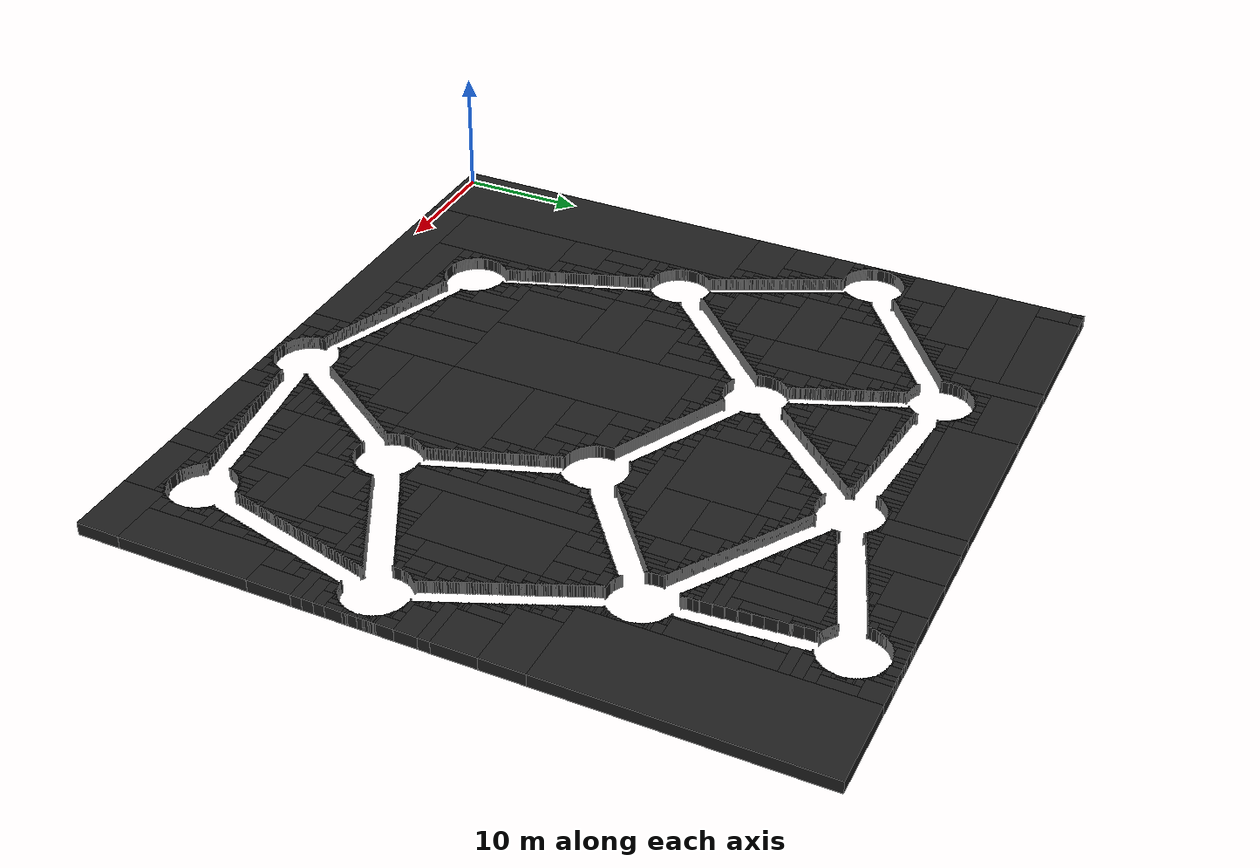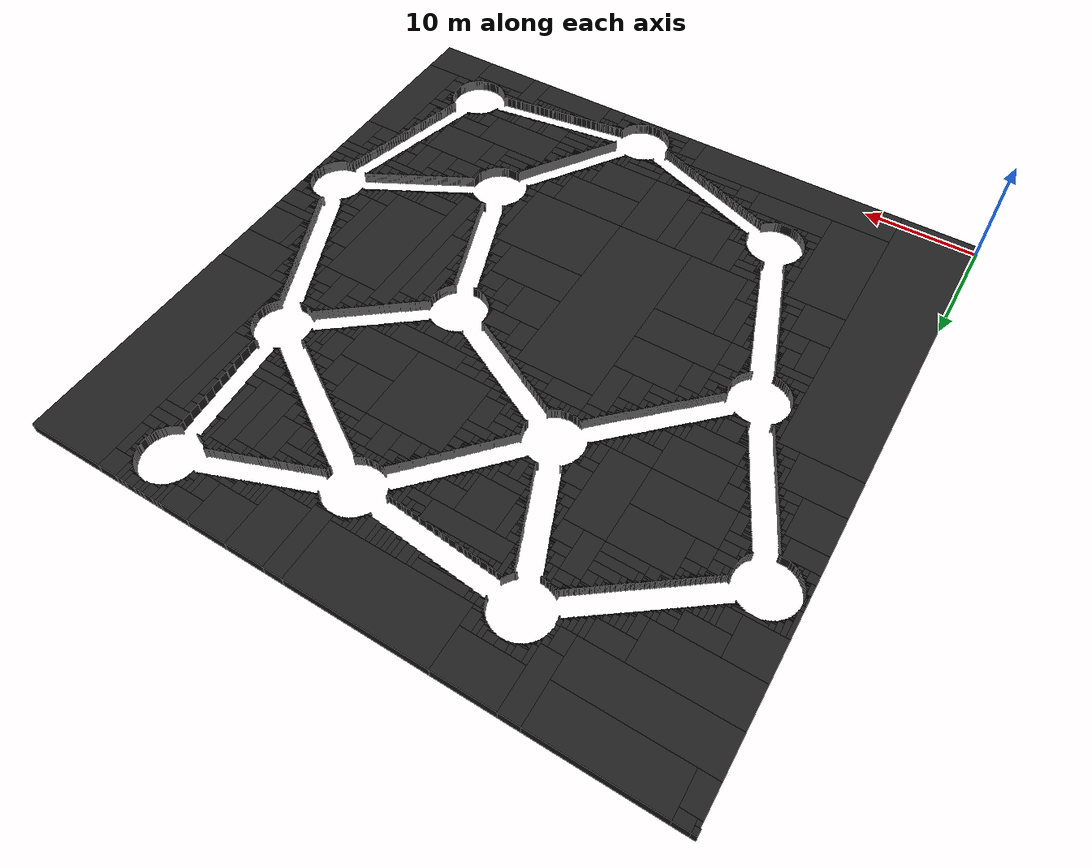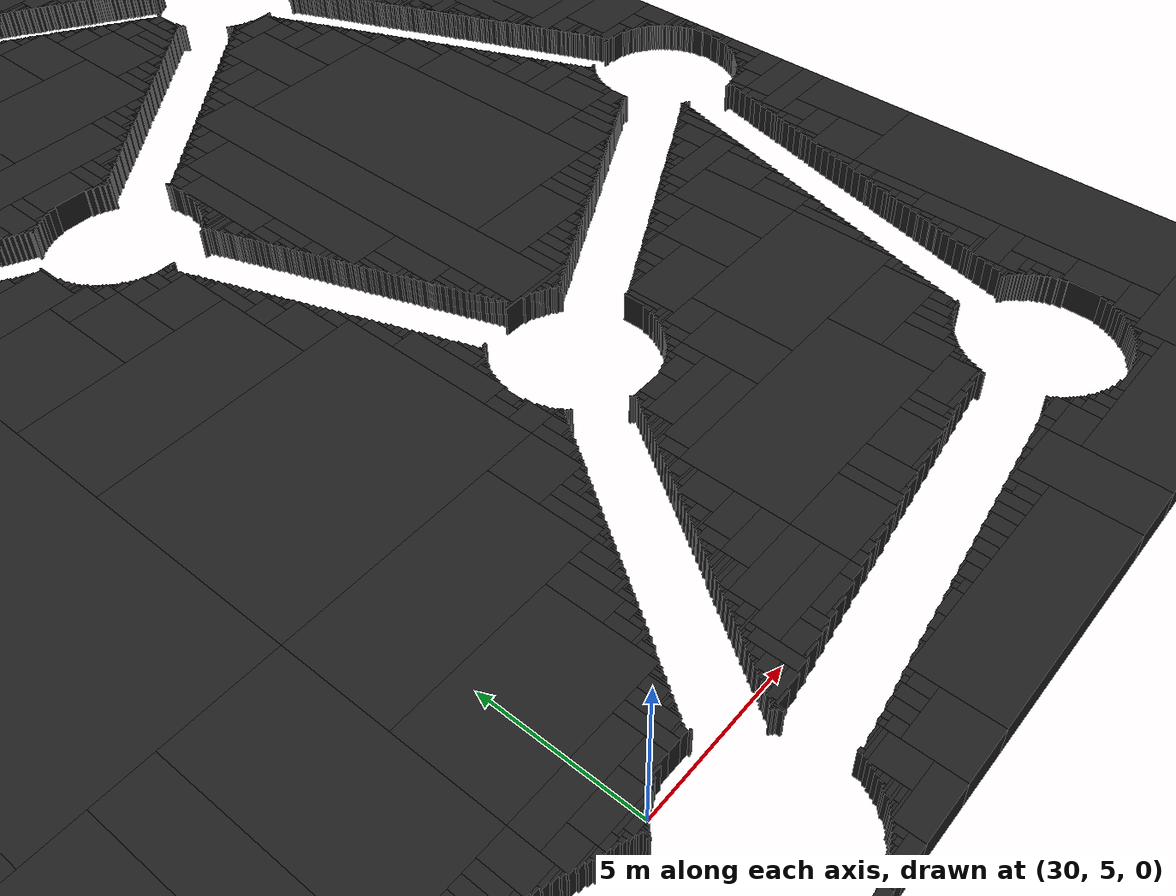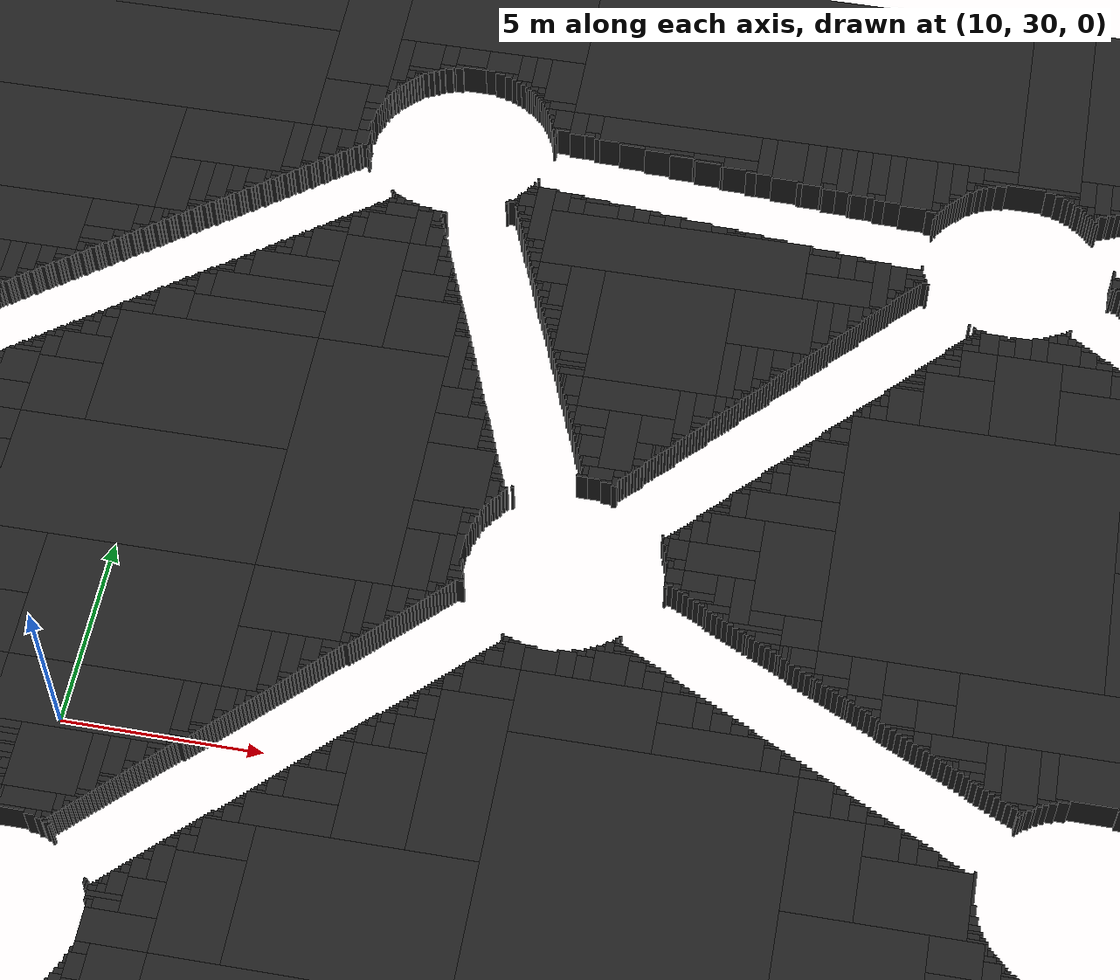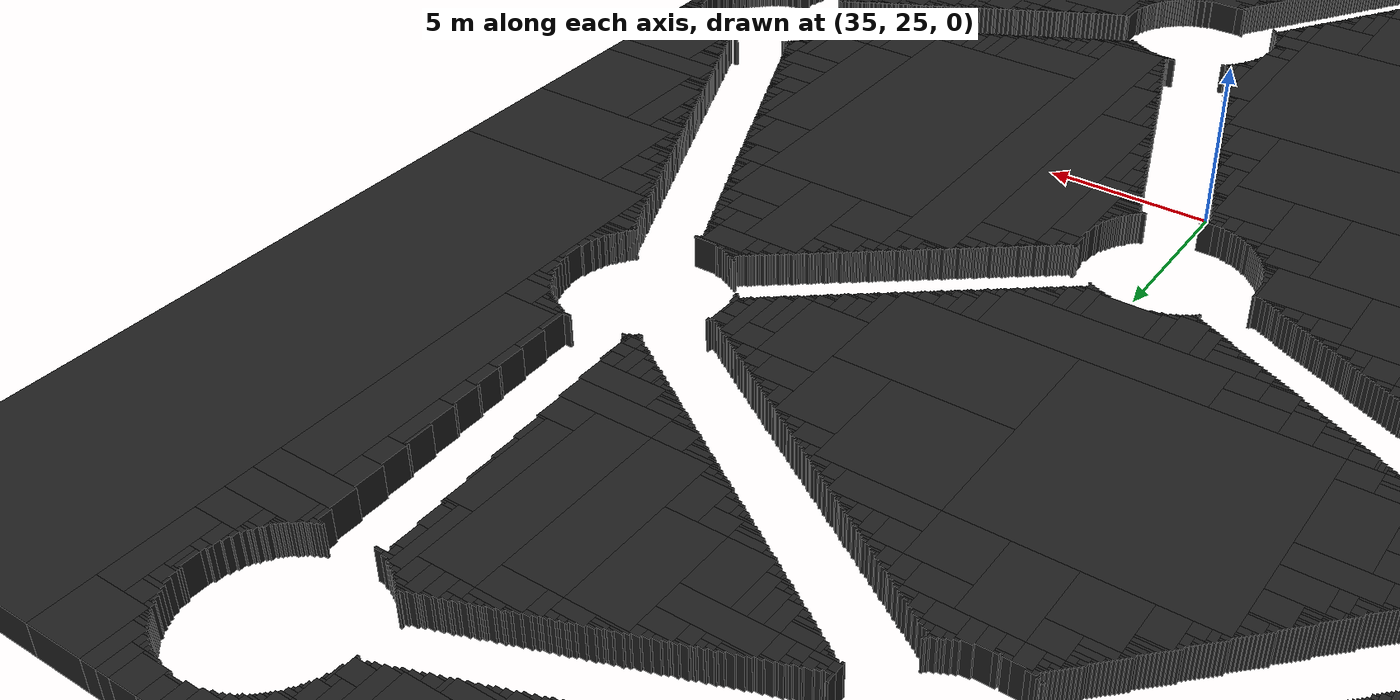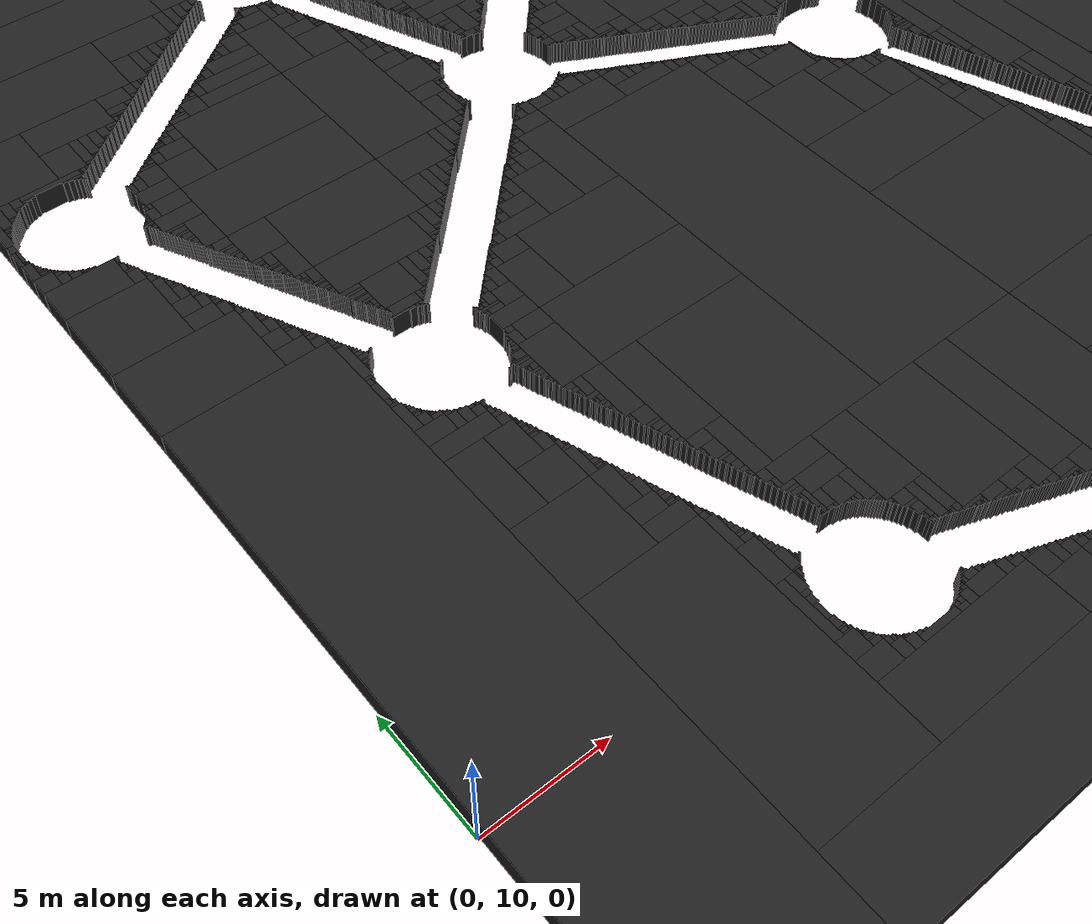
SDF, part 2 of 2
<box>
 <size>0.210000 0.140000 1.000000</size>
 </box>
</geometry>
<pose frame=''>15.785000 29.049999 0.500000 0 0 0</pose>
</collision>
	<visual name='Wall_15.8_29.0_Visual'>
<pose frame=''>15.785000 29.049999 0.500000 0 0 0</pose>
	<geometry>
<box>
<size>0.210000 0.140000 1.000000</size>
</box>
</geometry>
<material>
<script>
<uri>file://media/materials/scripts/gazebo.material</uri>
<name>Gazebo/Black</name>
</script>
<ambient>0 0 0 0</ambient>
</material>
</visual>
<collision name='Wall_15.8_29.2_Collision'>
	<geometry>
	<box>
 <size>0.140000 0.070000 1.000000</size>
 </box>
</geometry>
<pose frame=''>15.820000 29.155001 0.500000 0 0 0</pose>
</collision>
	<visual name='Wall_15.8_29.2_Visual'>
<pose frame=''>15.820000 29.155001 0.500000 0 0 0</pose>
	<geometry>
<box>
<size>0.140000 0.070000 1.000000</size>
</box>
</geometry>
<material>
<script>
<uri>file://media/materials/scripts/gazebo.material</uri>
<name>Gazebo/Black</name>
</script>
<ambient>0 0 0 0</ambient>
</material>
</visual>
<collision name='Wall_15.9_29.2_Collision'>
	<geometry>
	<box>
 <size>0.070000 0.070000 1.000000</size>
 </box>
</geometry>
<pose frame=''>15.855000 29.225000 0.500000 0 0 0</pose>
</collision>
	<visual name='Wall_15.9_29.2_Visual'>
<pose frame=''>15.855000 29.225000 0.500000 0 0 0</pose>
	<geometry>
<box>
<size>0.070000 0.070000 1.000000</size>
</box>
</geometry>
<material>
<script>
<uri>file://media/materials/scripts/gazebo.material</uri>
<name>Gazebo/Black</name>
</script>
<ambient>0 0 0 0</ambient>
</material>
</visual>
<collision name='Wall_13.8_30.1_Collision'>
	<geometry>
	<box>
 <size>0.070000 0.070000 1.000000</size>
 </box>
</geometry>
<pose frame=''>13.825000 30.135000 0.500000 0 0 0</pose>
</collision>
	<visual name='Wall_13.8_30.1_Visual'>
<pose frame=''>13.825000 30.135000 0.500000 0 0 0</pose>
	<geometry>
<box>
<size>0.070000 0.070000 1.000000</size>
</box>
</geometry>
<material>
<script>
<uri>file://media/materials/scripts/gazebo.material</uri>
<name>Gazebo/Black</name>
</script>
<ambient>0 0 0 0</ambient>
</material>
</visual>
<collision name='Wall_13.9_30.2_Collision'>
	<geometry>
	<box>
 <size>0.140000 0.070000 1.000000</size>
 </box>
</geometry>
<pose frame=''>13.860000 30.205000 0.500000 0 0 0</pose>
</collision>
	<visual name='Wall_13.9_30.2_Visual'>
<pose frame=''>13.860000 30.205000 0.500000 0 0 0</pose>
	<geometry>
<box>
<size>0.140000 0.070000 1.000000</size>
</box>
</geometry>
<material>
<script>
<uri>file://media/materials/scripts/gazebo.material</uri>
<name>Gazebo/Black</name>
</script>
<ambient>0 0 0 0</ambient>
</material>
</visual>
<collision name='Wall_13.9_30.3_Collision'>
	<geometry>
	<box>
 <size>0.210000 0.210000 1.000000</size>
 </box>
</geometry>
<pose frame=''>13.895000 30.344999 0.500000 0 0 0</pose>
</collision>
	<visual name='Wall_13.9_30.3_Visual'>
<pose frame=''>13.895000 30.344999 0.500000 0 0 0</pose>
	<geometry>
<box>
<size>0.210000 0.210000 1.000000</size>
</box>
</geometry>
<material>
<script>
<uri>file://media/materials/scripts/gazebo.material</uri>
<name>Gazebo/Black</name>
</script>
<ambient>0 0 0 0</ambient>
</material>
</visual>
<collision name='Wall_14.0_30.3_Collision'>
	<geometry>
	<box>
 <size>0.070000 0.070000 1.000000</size>
 </box>
</geometry>
<pose frame=''>14.035000 30.344999 0.500000 0 0 0</pose>
</collision>
	<visual name='Wall_14.0_30.3_Visual'>
<pose frame=''>14.035000 30.344999 0.500000 0 0 0</pose>
	<geometry>
<box>
<size>0.070000 0.070000 1.000000</size>
</box>
</geometry>
<material>
<script>
<uri>file://media/materials/scripts/gazebo.material</uri>
<name>Gazebo/Black</name>
</script>
<ambient>0 0 0 0</ambient>
</material>
</visual>
<collision name='Wall_14.0_30.8_Collision'>
	<geometry>
	<box>
 <size>0.420000 0.630000 1.000000</size>
 </box>
</geometry>
<pose frame=''>14.000000 30.764999 0.500000 0 0 0</pose>
</collision>
	<visual name='Wall_14.0_30.8_Visual'>
<pose frame=''>14.000000 30.764999 0.500000 0 0 0</pose>
	<geometry>
<box>
<size>0.420000 0.630000 1.000000</size>
</box>
</geometry>
<material>
<script>
<uri>file://media/materials/scripts/gazebo.material</uri>
<name>Gazebo/Black</name>
</script>
<ambient>0 0 0 0</ambient>
</material>
</visual>
<collision name='Wall_14.1_30.4_Collision'>
	<geometry>
	<box>
 <size>0.140000 0.070000 1.000000</size>
 </box>
</geometry>
<pose frame=''>14.070000 30.415001 0.500000 0 0 0</pose>
</collision>
	<visual name='Wall_14.1_30.4_Visual'>
<pose frame=''>14.070000 30.415001 0.500000 0 0 0</pose>
	<geometry>
<box>
<size>0.140000 0.070000 1.000000</size>
</box>
</geometry>
<material>
<script>
<uri>file://media/materials/scripts/gazebo.material</uri>
<name>Gazebo/Black</name>
</script>
<ambient>0 0 0 0</ambient>
</material>
</visual>
<collision name='Wall_14.2_30.6_Collision'>
	<geometry>
	<box>
 <size>0.070000 0.070000 1.000000</size>
 </box>
</geometry>
<pose frame=''>14.245000 30.555000 0.500000 0 0 0</pose>
</collision>
	<visual name='Wall_14.2_30.6_Visual'>
<pose frame=''>14.245000 30.555000 0.500000 0 0 0</pose>
	<geometry>
<box>
<size>0.070000 0.070000 1.000000</size>
</box>
</geometry>
<material>
<script>
<uri>file://media/materials/scripts/gazebo.material</uri>
<name>Gazebo/Black</name>
</script>
<ambient>0 0 0 0</ambient>
</material>
</visual>
<collision name='Wall_14.3_30.6_Collision'>
	<geometry>
	<box>
 <size>0.140000 0.070000 1.000000</size>
 </box>
</geometry>
<pose frame=''>14.280000 30.625000 0.500000 0 0 0</pose>
</collision>
	<visual name='Wall_14.3_30.6_Visual'>
<pose frame=''>14.280000 30.625000 0.500000 0 0 0</pose>
	<geometry>
<box>
<size>0.140000 0.070000 1.000000</size>
</box>
</geometry>
<material>
<script>
<uri>file://media/materials/scripts/gazebo.material</uri>
<name>Gazebo/Black</name>
</script>
<ambient>0 0 0 0</ambient>
</material>
</visual>
<collision name='Wall_14.3_30.9_Collision'>
	<geometry>
	<box>
 <size>0.210000 0.420000 1.000000</size>
 </box>
</geometry>
<pose frame=''>14.315001 30.870001 0.500000 0 0 0</pose>
</collision>
	<visual name='Wall_14.3_30.9_Visual'>
<pose frame=''>14.315001 30.870001 0.500000 0 0 0</pose>
	<geometry>
<box>
<size>0.210000 0.420000 1.000000</size>
</box>
</geometry>
<material>
<script>
<uri>file://media/materials/scripts/gazebo.material</uri>
<name>Gazebo/Black</name>
</script>
<ambient>0 0 0 0</ambient>
</material>
</visual>
<collision name='Wall_14.5_30.8_Collision'>
	<geometry>
	<box>
 <size>0.070000 0.070000 1.000000</size>
 </box>
</geometry>
<pose frame=''>14.455000 30.764999 0.500000 0 0 0</pose>
</collision>
	<visual name='Wall_14.5_30.8_Visual'>
<pose frame=''>14.455000 30.764999 0.500000 0 0 0</pose>
	<geometry>
<box>
<size>0.070000 0.070000 1.000000</size>
</box>
</geometry>
<material>
<script>
<uri>file://media/materials/scripts/gazebo.material</uri>
<name>Gazebo/Black</name>
</script>
<ambient>0 0 0 0</ambient>
</material>
</visual>
<collision name='Wall_14.5_30.9_Collision'>
	<geometry>
	<box>
 <size>0.140000 0.140000 1.000000</size>
 </box>
</geometry>
<pose frame=''>14.490000 30.870001 0.500000 0 0 0</pose>
</collision>
	<visual name='Wall_14.5_30.9_Visual'>
<pose frame=''>14.490000 30.870001 0.500000 0 0 0</pose>
	<geometry>
<box>
<size>0.140000 0.140000 1.000000</size>
</box>
</geometry>
<material>
<script>
<uri>file://media/materials/scripts/gazebo.material</uri>
<name>Gazebo/Black</name>
</script>
<ambient>0 0 0 0</ambient>
</material>
</visual>
<collision name='Wall_14.6_30.9_Collision'>
	<geometry>
	<box>
 <size>0.070000 0.070000 1.000000</size>
 </box>
</geometry>
<pose frame=''>14.595000 30.905001 0.500000 0 0 0</pose>
</collision>
	<visual name='Wall_14.6_30.9_Visual'>
<pose frame=''>14.595000 30.905001 0.500000 0 0 0</pose>
	<geometry>
<box>
<size>0.070000 0.070000 1.000000</size>
</box>
</geometry>
<material>
<script>
<uri>file://media/materials/scripts/gazebo.material</uri>
<name>Gazebo/Black</name>
</script>
<ambient>0 0 0 0</ambient>
</material>
</visual>
<collision name='Wall_14.6_31.0_Collision'>
	<geometry>
	<box>
 <size>0.280000 0.140000 1.000000</size>
 </box>
</geometry>
<pose frame=''>14.560000 31.010000 0.500000 0 0 0</pose>
</collision>
	<visual name='Wall_14.6_31.0_Visual'>
<pose frame=''>14.560000 31.010000 0.500000 0 0 0</pose>
	<geometry>
<box>
<size>0.280000 0.140000 1.000000</size>
</box>
</geometry>
<material>
<script>
<uri>file://media/materials/scripts/gazebo.material</uri>
<name>Gazebo/Black</name>
</script>
<ambient>0 0 0 0</ambient>
</material>
</visual>
<collision name='Wall_14.7_31.0_Collision'>
	<geometry>
	<box>
 <size>0.070000 0.070000 1.000000</size>
 </box>
</geometry>
<pose frame=''>14.735000 31.045000 0.500000 0 0 0</pose>
</collision>
	<visual name='Wall_14.7_31.0_Visual'>
<pose frame=''>14.735000 31.045000 0.500000 0 0 0</pose>
	<geometry>
<box>
<size>0.070000 0.070000 1.000000</size>
</box>
</geometry>
<material>
<script>
<uri>file://media/materials/scripts/gazebo.material</uri>
<name>Gazebo/Black</name>
</script>
<ambient>0 0 0 0</ambient>
</material>
</visual>
<collision name='Wall_16.1_29.4_Collision'>
	<geometry>
	<box>
 <size>0.350000 0.070000 1.000000</size>
 </box>
</geometry>
<pose frame=''>16.135000 29.365000 0.500000 0 0 0</pose>
</collision>
	<visual name='Wall_16.1_29.4_Visual'>
<pose frame=''>16.135000 29.365000 0.500000 0 0 0</pose>
	<geometry>
<box>
<size>0.350000 0.070000 1.000000</size>
</box>
</geometry>
<material>
<script>
<uri>file://media/materials/scripts/gazebo.material</uri>
<name>Gazebo/Black</name>
</script>
<ambient>0 0 0 0</ambient>
</material>
</visual>
<collision name='Wall_16.1_29.4_Collision'>
	<geometry>
	<box>
 <size>0.070000 0.070000 1.000000</size>
 </box>
</geometry>
<pose frame=''>16.065001 29.434999 0.500000 0 0 0</pose>
</collision>
	<visual name='Wall_16.1_29.4_Visual'>
<pose frame=''>16.065001 29.434999 0.500000 0 0 0</pose>
	<geometry>
<box>
<size>0.070000 0.070000 1.000000</size>
</box>
</geometry>
<material>
<script>
<uri>file://media/materials/scripts/gazebo.material</uri>
<name>Gazebo/Black</name>
</script>
<ambient>0 0 0 0</ambient>
</material>
</visual>
<collision name='Wall_16.2_29.5_Collision'>
	<geometry>
	<box>
 <size>0.210000 0.140000 1.000000</size>
 </box>
</geometry>
<pose frame=''>16.205000 29.469999 0.500000 0 0 0</pose>
</collision>
	<visual name='Wall_16.2_29.5_Visual'>
<pose frame=''>16.205000 29.469999 0.500000 0 0 0</pose>
	<geometry>
<box>
<size>0.210000 0.140000 1.000000</size>
</box>
</geometry>
<material>
<script>
<uri>file://media/materials/scripts/gazebo.material</uri>
<name>Gazebo/Black</name>
</script>
<ambient>0 0 0 0</ambient>
</material>
</visual>
<collision name='Wall_16.2_29.6_Collision'>
	<geometry>
	<box>
 <size>0.140000 0.070000 1.000000</size>
 </box>
</geometry>
<pose frame=''>16.240000 29.575001 0.500000 0 0 0</pose>
</collision>
	<visual name='Wall_16.2_29.6_Visual'>
<pose frame=''>16.240000 29.575001 0.500000 0 0 0</pose>
	<geometry>
<box>
<size>0.140000 0.070000 1.000000</size>
</box>
</geometry>
<material>
<script>
<uri>file://media/materials/scripts/gazebo.material</uri>
<name>Gazebo/Black</name>
</script>
<ambient>0 0 0 0</ambient>
</material>
</visual>
<collision name='Wall_16.3_29.6_Collision'>
	<geometry>
	<box>
 <size>0.070000 0.070000 1.000000</size>
 </box>
</geometry>
<pose frame=''>16.275000 29.645000 0.500000 0 0 0</pose>
</collision>
	<visual name='Wall_16.3_29.6_Visual'>
<pose frame=''>16.275000 29.645000 0.500000 0 0 0</pose>
	<geometry>
<box>
<size>0.070000 0.070000 1.000000</size>
</box>
</geometry>
<material>
<script>
<uri>file://media/materials/scripts/gazebo.material</uri>
<name>Gazebo/Black</name>
</script>
<ambient>0 0 0 0</ambient>
</material>
</visual>
<collision name='Wall_16.5_29.5_Collision'>
	<geometry>
	<box>
 <size>0.420000 0.420000 1.000000</size>
 </box>
</geometry>
<pose frame=''>16.520000 29.540001 0.500000 0 0 0</pose>
</collision>
	<visual name='Wall_16.5_29.5_Visual'>
<pose frame=''>16.520000 29.540001 0.500000 0 0 0</pose>
	<geometry>
<box>
<size>0.420000 0.420000 1.000000</size>
</box>
</geometry>
<material>
<script>
<uri>file://media/materials/scripts/gazebo.material</uri>
<name>Gazebo/Black</name>
</script>
<ambient>0 0 0 0</ambient>
</material>
</visual>
<collision name='Wall_17.0_29.8_Collision'>
	<geometry>
	<box>
 <size>0.490000 0.840000 1.000000</size>
 </box>
</geometry>
<pose frame=''>16.975000 29.750000 0.500000 0 0 0</pose>
</collision>
	<visual name='Wall_17.0_29.8_Visual'>
<pose frame=''>16.975000 29.750000 0.500000 0 0 0</pose>
	<geometry>
<box>
<size>0.490000 0.840000 1.000000</size>
</box>
</geometry>
<material>
<script>
<uri>file://media/materials/scripts/gazebo.material</uri>
<name>Gazebo/Black</name>
</script>
<ambient>0 0 0 0</ambient>
</material>
</visual>
<collision name='Wall_16.6_29.8_Collision'>
	<geometry>
	<box>
 <size>0.350000 0.070000 1.000000</size>
 </box>
</geometry>
<pose frame=''>16.555000 29.785000 0.500000 0 0 0</pose>
</collision>
	<visual name='Wall_16.6_29.8_Visual'>
<pose frame=''>16.555000 29.785000 0.500000 0 0 0</pose>
	<geometry>
<box>
<size>0.350000 0.070000 1.000000</size>
</box>
</geometry>
<material>
<script>
<uri>file://media/materials/scripts/gazebo.material</uri>
<name>Gazebo/Black</name>
</script>
<ambient>0 0 0 0</ambient>
</material>
</visual>
<collision name='Wall_16.5_29.9_Collision'>
	<geometry>
	<box>
 <size>0.070000 0.070000 1.000000</size>
 </box>
</geometry>
<pose frame=''>16.485001 29.855000 0.500000 0 0 0</pose>
</collision>
	<visual name='Wall_16.5_29.9_Visual'>
<pose frame=''>16.485001 29.855000 0.500000 0 0 0</pose>
	<geometry>
<box>
<size>0.070000 0.070000 1.000000</size>
</box>
</geometry>
<material>
<script>
<uri>file://media/materials/scripts/gazebo.material</uri>
<name>Gazebo/Black</name>
</script>
<ambient>0 0 0 0</ambient>
</material>
</visual>
<collision name='Wall_16.6_29.9_Collision'>
	<geometry>
	<box>
 <size>0.210000 0.140000 1.000000</size>
 </box>
</geometry>
<pose frame=''>16.625000 29.889999 0.500000 0 0 0</pose>
</collision>
	<visual name='Wall_16.6_29.9_Visual'>
<pose frame=''>16.625000 29.889999 0.500000 0 0 0</pose>
	<geometry>
<box>
<size>0.210000 0.140000 1.000000</size>
</box>
</geometry>
<material>
<script>
<uri>file://media/materials/scripts/gazebo.material</uri>
<name>Gazebo/Black</name>
</script>
<ambient>0 0 0 0</ambient>
</material>
</visual>
<collision name='Wall_16.7_30.0_Collision'>
	<geometry>
	<box>
 <size>0.140000 0.070000 1.000000</size>
 </box>
</geometry>
<pose frame=''>16.660000 29.995001 0.500000 0 0 0</pose>
</collision>
	<visual name='Wall_16.7_30.0_Visual'>
<pose frame=''>16.660000 29.995001 0.500000 0 0 0</pose>
	<geometry>
<box>
<size>0.140000 0.070000 1.000000</size>
</box>
</geometry>
<material>
<script>
<uri>file://media/materials/scripts/gazebo.material</uri>
<name>Gazebo/Black</name>
</script>
<ambient>0 0 0 0</ambient>
</material>
</visual>
<collision name='Wall_16.7_30.1_Collision'>
	<geometry>
	<box>
 <size>0.070000 0.070000 1.000000</size>
 </box>
</geometry>
<pose frame=''>16.695000 30.065001 0.500000 0 0 0</pose>
</collision>
	<visual name='Wall_16.7_30.1_Visual'>
<pose frame=''>16.695000 30.065001 0.500000 0 0 0</pose>
	<geometry>
<box>
<size>0.070000 0.070000 1.000000</size>
</box>
</geometry>
<material>
<script>
<uri>file://media/materials/scripts/gazebo.material</uri>
<name>Gazebo/Black</name>
</script>
<ambient>0 0 0 0</ambient>
</material>
</visual>
<collision name='Wall_17.0_30.2_Collision'>
	<geometry>
	<box>
 <size>0.420000 0.070000 1.000000</size>
 </box>
</geometry>
<pose frame=''>17.010000 30.205000 0.500000 0 0 0</pose>
</collision>
	<visual name='Wall_17.0_30.2_Visual'>
<pose frame=''>17.010000 30.205000 0.500000 0 0 0</pose>
	<geometry>
<box>
<size>0.420000 0.070000 1.000000</size>
</box>
</geometry>
<material>
<script>
<uri>file://media/materials/scripts/gazebo.material</uri>
<name>Gazebo/Black</name>
</script>
<ambient>0 0 0 0</ambient>
</material>
</visual>
<collision name='Wall_16.9_30.3_Collision'>
	<geometry>
	<box>
 <size>0.070000 0.070000 1.000000</size>
 </box>
</geometry>
<pose frame=''>16.905001 30.275000 0.500000 0 0 0</pose>
</collision>
	<visual name='Wall_16.9_30.3_Visual'>
<pose frame=''>16.905001 30.275000 0.500000 0 0 0</pose>
	<geometry>
<box>
<size>0.070000 0.070000 1.000000</size>
</box>
</geometry>
<material>
<script>
<uri>file://media/materials/scripts/gazebo.material</uri>
<name>Gazebo/Black</name>
</script>
<ambient>0 0 0 0</ambient>
</material>
</visual>
<collision name='Wall_17.1_30.3_Collision'>
	<geometry>
	<box>
 <size>0.280000 0.140000 1.000000</size>
 </box>
</geometry>
<pose frame=''>17.080000 30.309999 0.500000 0 0 0</pose>
</collision>
	<visual name='Wall_17.1_30.3_Visual'>
<pose frame=''>17.080000 30.309999 0.500000 0 0 0</pose>
	<geometry>
<box>
<size>0.280000 0.140000 1.000000</size>
</box>
</geometry>
<material>
<script>
<uri>file://media/materials/scripts/gazebo.material</uri>
<name>Gazebo/Black</name>
</script>
<ambient>0 0 0 0</ambient>
</material>
</visual>
<collision name='Wall_17.1_30.4_Collision'>
	<geometry>
	<box>
 <size>0.210000 0.070000 1.000000</size>
 </box>
</geometry>
<pose frame=''>17.115000 30.415001 0.500000 0 0 0</pose>
</collision>
	<visual name='Wall_17.1_30.4_Visual'>
<pose frame=''>17.115000 30.415001 0.500000 0 0 0</pose>
	<geometry>
<box>
<size>0.210000 0.070000 1.000000</size>
</box>
</geometry>
<material>
<script>
<uri>file://media/materials/scripts/gazebo.material</uri>
<name>Gazebo/Black</name>
</script>
<ambient>0 0 0 0</ambient>
</material>
</visual>
<collision name='Wall_17.1_30.5_Collision'>
	<geometry>
	<box>
 <size>0.140000 0.070000 1.000000</size>
 </box>
</geometry>
<pose frame=''>17.150000 30.485001 0.500000 0 0 0</pose>
</collision>
	<visual name='Wall_17.1_30.5_Visual'>
<pose frame=''>17.150000 30.485001 0.500000 0 0 0</pose>
	<geometry>
<box>
<size>0.140000 0.070000 1.000000</size>
</box>
</geometry>
<material>
<script>
<uri>file://media/materials/scripts/gazebo.material</uri>
<name>Gazebo/Black</name>
</script>
<ambient>0 0 0 0</ambient>
</material>
</visual>
<collision name='Wall_17.2_30.6_Collision'>
	<geometry>
	<box>
 <size>0.070000 0.070000 1.000000</size>
 </box>
</geometry>
<pose frame=''>17.184999 30.555000 0.500000 0 0 0</pose>
</collision>
	<visual name='Wall_17.2_30.6_Visual'>
<pose frame=''>17.184999 30.555000 0.500000 0 0 0</pose>
	<geometry>
<box>
<size>0.070000 0.070000 1.000000</size>
</box>
</geometry>
<material>
<script>
<uri>file://media/materials/scripts/gazebo.material</uri>
<name>Gazebo/Black</name>
</script>
<ambient>0 0 0 0</ambient>
</material>
</visual>
<collision name='Wall_18.1_28.9_Collision'>
	<geometry>
	<box>
 <size>1.750000 2.520000 1.000000</size>
 </box>
</geometry>
<pose frame=''>18.094999 28.910000 0.500000 0 0 0</pose>
</collision>
	<visual name='Wall_18.1_28.9_Visual'>
<pose frame=''>18.094999 28.910000 0.500000 0 0 0</pose>
	<geometry>
<box>
<size>1.750000 2.520000 1.000000</size>
</box>
</geometry>
<material>
<script>
<uri>file://media/materials/scripts/gazebo.material</uri>
<name>Gazebo/Black</name>
</script>
<ambient>0 0 0 0</ambient>
</material>
</visual>
<collision name='Wall_19.8_29.8_Collision'>
	<geometry>
	<box>
 <size>1.750000 4.270000 1.000000</size>
 </box>
</geometry>
<pose frame=''>19.844999 29.785000 0.500000 0 0 0</pose>
</collision>
	<visual name='Wall_19.8_29.8_Visual'>
<pose frame=''>19.844999 29.785000 0.500000 0 0 0</pose>
	<geometry>
<box>
<size>1.750000 4.270000 1.000000</size>
</box>
</geometry>
<material>
<script>
<uri>file://media/materials/scripts/gazebo.material</uri>
<name>Gazebo/Black</name>
</script>
<ambient>0 0 0 0</ambient>
</material>
</visual>
<collision name='Wall_17.4_30.4_Collision'>
	<geometry>
	<box>
 <size>0.420000 0.490000 1.000000</size>
 </box>
</geometry>
<pose frame=''>17.430000 30.415001 0.500000 0 0 0</pose>
</collision>
	<visual name='Wall_17.4_30.4_Visual'>
<pose frame=''>17.430000 30.415001 0.500000 0 0 0</pose>
	<geometry>
<box>
<size>0.420000 0.490000 1.000000</size>
</box>
</geometry>
<material>
<script>
<uri>file://media/materials/scripts/gazebo.material</uri>
<name>Gazebo/Black</name>
</script>
<ambient>0 0 0 0</ambient>
</material>
</visual>
<collision name='Wall_17.9_30.5_Collision'>
	<geometry>
	<box>
 <size>0.420000 0.630000 1.000000</size>
 </box>
</geometry>
<pose frame=''>17.850000 30.485001 0.500000 0 0 0</pose>
</collision>
	<visual name='Wall_17.9_30.5_Visual'>
<pose frame=''>17.850000 30.485001 0.500000 0 0 0</pose>
	<geometry>
<box>
<size>0.420000 0.630000 1.000000</size>
</box>
</geometry>
<material>
<script>
<uri>file://media/materials/scripts/gazebo.material</uri>
<name>Gazebo/Black</name>
</script>
<ambient>0 0 0 0</ambient>
</material>
</visual>
<collision name='Wall_17.4_30.7_Collision'>
	<geometry>
	<box>
 <size>0.140000 0.070000 1.000000</size>
 </box>
</geometry>
<pose frame=''>17.360001 30.695000 0.500000 0 0 0</pose>
</collision>
	<visual name='Wall_17.4_30.7_Visual'>
<pose frame=''>17.360001 30.695000 0.500000 0 0 0</pose>
	<geometry>
<box>
<size>0.140000 0.070000 1.000000</size>
</box>
</geometry>
<material>
<script>
<uri>file://media/materials/scripts/gazebo.material</uri>
<name>Gazebo/Black</name>
</script>
<ambient>0 0 0 0</ambient>
</material>
</visual>
<collision name='Wall_17.4_30.8_Collision'>
	<geometry>
	<box>
 <size>0.070000 0.070000 1.000000</size>
 </box>
</geometry>
<pose frame=''>17.395000 30.764999 0.500000 0 0 0</pose>
</collision>
	<visual name='Wall_17.4_30.8_Visual'>
<pose frame=''>17.395000 30.764999 0.500000 0 0 0</pose>
	<geometry>
<box>
<size>0.070000 0.070000 1.000000</size>
</box>
</geometry>
<material>
<script>
<uri>file://media/materials/scripts/gazebo.material</uri>
<name>Gazebo/Black</name>
</script>
<ambient>0 0 0 0</ambient>
</material>
</visual>
<collision name='Wall_17.5_30.8_Collision'>
	<geometry>
	<box>
 <size>0.210000 0.210000 1.000000</size>
 </box>
</geometry>
<pose frame=''>17.535000 30.764999 0.500000 0 0 0</pose>
</collision>
	<visual name='Wall_17.5_30.8_Visual'>
<pose frame=''>17.535000 30.764999 0.500000 0 0 0</pose>
	<geometry>
<box>
<size>0.210000 0.210000 1.000000</size>
</box>
</geometry>
<material>
<script>
<uri>file://media/materials/scripts/gazebo.material</uri>
<name>Gazebo/Black</name>
</script>
<ambient>0 0 0 0</ambient>
</material>
</visual>
<collision name='Wall_17.6_30.9_Collision'>
	<geometry>
	<box>
 <size>0.140000 0.070000 1.000000</size>
 </box>
</geometry>
<pose frame=''>17.570000 30.905001 0.500000 0 0 0</pose>
</collision>
	<visual name='Wall_17.6_30.9_Visual'>
<pose frame=''>17.570000 30.905001 0.500000 0 0 0</pose>
	<geometry>
<box>
<size>0.140000 0.070000 1.000000</size>
</box>
</geometry>
<material>
<script>
<uri>file://media/materials/scripts/gazebo.material</uri>
<name>Gazebo/Black</name>
</script>
<ambient>0 0 0 0</ambient>
</material>
</visual>
<collision name='Wall_17.6_31.0_Collision'>
	<geometry>
	<box>
 <size>0.070000 0.070000 1.000000</size>
 </box>
</geometry>
<pose frame=''>17.605000 30.975000 0.500000 0 0 0</pose>
</collision>
	<visual name='Wall_17.6_31.0_Visual'>
<pose frame=''>17.605000 30.975000 0.500000 0 0 0</pose>
	<geometry>
<box>
<size>0.070000 0.070000 1.000000</size>
</box>
</geometry>
<material>
<script>
<uri>file://media/materials/scripts/gazebo.material</uri>
<name>Gazebo/Black</name>
</script>
<ambient>0 0 0 0</ambient>
</material>
</visual>
<collision name='Wall_17.7_30.9_Collision'>
	<geometry>
	<box>
 <size>0.070000 0.210000 1.000000</size>
 </box>
</geometry>
<pose frame=''>17.674999 30.905001 0.500000 0 0 0</pose>
</collision>
	<visual name='Wall_17.7_30.9_Visual'>
<pose frame=''>17.674999 30.905001 0.500000 0 0 0</pose>
	<geometry>
<box>
<size>0.070000 0.210000 1.000000</size>
</box>
</geometry>
<material>
<script>
<uri>file://media/materials/scripts/gazebo.material</uri>
<name>Gazebo/Black</name>
</script>
<ambient>0 0 0 0</ambient>
</material>
</visual>
<collision name='Wall_17.9_30.9_Collision'>
	<geometry>
	<box>
 <size>0.350000 0.280000 1.000000</size>
 </box>
</geometry>
<pose frame=''>17.885000 30.940001 0.500000 0 0 0</pose>
</collision>
	<visual name='Wall_17.9_30.9_Visual'>
<pose frame=''>17.885000 30.940001 0.500000 0 0 0</pose>
	<geometry>
<box>
<size>0.350000 0.280000 1.000000</size>
</box>
</geometry>
<material>
<script>
<uri>file://media/materials/scripts/gazebo.material</uri>
<name>Gazebo/Black</name>
</script>
<ambient>0 0 0 0</ambient>
</material>
</visual>
<collision name='Wall_18.5_30.6_Collision'>
	<geometry>
	<box>
 <size>0.910000 0.910000 1.000000</size>
 </box>
</geometry>
<pose frame=''>18.514999 30.625000 0.500000 0 0 0</pose>
</collision>
	<visual name='Wall_18.5_30.6_Visual'>
<pose frame=''>18.514999 30.625000 0.500000 0 0 0</pose>
	<geometry>
<box>
<size>0.910000 0.910000 1.000000</size>
</box>
</geometry>
<material>
<script>
<uri>file://media/materials/scripts/gazebo.material</uri>
<name>Gazebo/Black</name>
</script>
<ambient>0 0 0 0</ambient>
</material>
</visual>
<collision name='Wall_14.2_31.9_Collision'>
	<geometry>
	<box>
 <size>0.840000 1.680000 1.000000</size>
 </box>
</geometry>
<pose frame=''>14.210000 31.920000 0.500000 0 0 0</pose>
</collision>
	<visual name='Wall_14.2_31.9_Visual'>
<pose frame=''>14.210000 31.920000 0.500000 0 0 0</pose>
	<geometry>
<box>
<size>0.840000 1.680000 1.000000</size>
</box>
</geometry>
<material>
<script>
<uri>file://media/materials/scripts/gazebo.material</uri>
<name>Gazebo/Black</name>
</script>
<ambient>0 0 0 0</ambient>
</material>
</visual>
<collision name='Wall_14.7_31.1_Collision'>
	<geometry>
	<box>
 <size>0.210000 0.070000 1.000000</size>
 </box>
</geometry>
<pose frame=''>14.735000 31.115000 0.500000 0 0 0</pose>
</collision>
	<visual name='Wall_14.7_31.1_Visual'>
<pose frame=''>14.735000 31.115000 0.500000 0 0 0</pose>
	<geometry>
<box>
<size>0.210000 0.070000 1.000000</size>
</box>
</geometry>
<material>
<script>
<uri>file://media/materials/scripts/gazebo.material</uri>
<name>Gazebo/Black</name>
</script>
<ambient>0 0 0 0</ambient>
</material>
</visual>
<collision name='Wall_14.8_31.2_Collision'>
	<geometry>
	<box>
 <size>0.280000 0.140000 1.000000</size>
 </box>
</geometry>
<pose frame=''>14.770000 31.219999 0.500000 0 0 0</pose>
</collision>
	<visual name='Wall_14.8_31.2_Visual'>
<pose frame=''>14.770000 31.219999 0.500000 0 0 0</pose>
	<geometry>
<box>
<size>0.280000 0.140000 1.000000</size>
</box>
</geometry>
<material>
<script>
<uri>file://media/materials/scripts/gazebo.material</uri>
<name>Gazebo/Black</name>
</script>
<ambient>0 0 0 0</ambient>
</material>
</visual>
<collision name='Wall_14.9_31.3_Collision'>
	<geometry>
	<box>
 <size>0.070000 0.070000 1.000000</size>
 </box>
</geometry>
<pose frame=''>14.945000 31.255001 0.500000 0 0 0</pose>
</collision>
	<visual name='Wall_14.9_31.3_Visual'>
<pose frame=''>14.945000 31.255001 0.500000 0 0 0</pose>
	<geometry>
<box>
<size>0.070000 0.070000 1.000000</size>
</box>
</geometry>
<material>
<script>
<uri>file://media/materials/scripts/gazebo.material</uri>
<name>Gazebo/Black</name>
</script>
<ambient>0 0 0 0</ambient>
</material>
</visual>
<collision name='Wall_14.8_32.0_Collision'>
	<geometry>
	<box>
 <size>0.420000 1.470000 1.000000</size>
 </box>
</geometry>
<pose frame=''>14.840000 32.025002 0.500000 0 0 0</pose>
</collision>
	<visual name='Wall_14.8_32.0_Visual'>
<pose frame=''>14.840000 32.025002 0.500000 0 0 0</pose>
	<geometry>
<box>
<size>0.420000 1.470000 1.000000</size>
</box>
</geometry>
<material>
<script>
<uri>file://media/materials/scripts/gazebo.material</uri>
<name>Gazebo/Black</name>
</script>
<ambient>0 0 0 0</ambient>
</material>
</visual>
<collision name='Wall_15.1_31.4_Collision'>
	<geometry>
	<box>
 <size>0.070000 0.140000 1.000000</size>
 </box>
</geometry>
<pose frame=''>15.085000 31.430000 0.500000 0 0 0</pose>
</collision>
	<visual name='Wall_15.1_31.4_Visual'>
<pose frame=''>15.085000 31.430000 0.500000 0 0 0</pose>
	<geometry>
<box>
<size>0.070000 0.140000 1.000000</size>
</box>
</geometry>
<material>
<script>
<uri>file://media/materials/scripts/gazebo.material</uri>
<name>Gazebo/Black</name>
</script>
<ambient>0 0 0 0</ambient>
</material>
</visual>
<collision name='Wall_15.2_31.5_Collision'>
	<geometry>
	<box>
 <size>0.070000 0.070000 1.000000</size>
 </box>
</geometry>
<pose frame=''>15.155000 31.465000 0.500000 0 0 0</pose>
</collision>
	<visual name='Wall_15.2_31.5_Visual'>
<pose frame=''>15.155000 31.465000 0.500000 0 0 0</pose>
	<geometry>
<box>
<size>0.070000 0.070000 1.000000</size>
</box>
</geometry>
<material>
<script>
<uri>file://media/materials/scripts/gazebo.material</uri>
<name>Gazebo/Black</name>
</script>
<ambient>0 0 0 0</ambient>
</material>
</visual>
<collision name='Wall_15.2_31.5_Collision'>
	<geometry>
	<box>
 <size>0.210000 0.070000 1.000000</size>
 </box>
</geometry>
<pose frame=''>15.155000 31.535000 0.500000 0 0 0</pose>
</collision>
	<visual name='Wall_15.2_31.5_Visual'>
<pose frame=''>15.155000 31.535000 0.500000 0 0 0</pose>
	<geometry>
<box>
<size>0.210000 0.070000 1.000000</size>
</box>
</geometry>
<material>
<script>
<uri>file://media/materials/scripts/gazebo.material</uri>
<name>Gazebo/Black</name>
</script>
<ambient>0 0 0 0</ambient>
</material>
</visual>
<collision name='Wall_15.2_31.6_Collision'>
	<geometry>
	<box>
 <size>0.280000 0.140000 1.000000</size>
 </box>
</geometry>
<pose frame=''>15.190001 31.639999 0.500000 0 0 0</pose>
</collision>
	<visual name='Wall_15.2_31.6_Visual'>
<pose frame=''>15.190001 31.639999 0.500000 0 0 0</pose>
	<geometry>
<box>
<size>0.280000 0.140000 1.000000</size>
</box>
</geometry>
<material>
<script>
<uri>file://media/materials/scripts/gazebo.material</uri>
<name>Gazebo/Black</name>
</script>
<ambient>0 0 0 0</ambient>
</material>
</visual>
<collision name='Wall_15.4_31.7_Collision'>
	<geometry>
	<box>
 <size>0.070000 0.070000 1.000000</size>
 </box>
</geometry>
<pose frame=''>15.365000 31.674999 0.500000 0 0 0</pose>
</collision>
	<visual name='Wall_15.4_31.7_Visual'>
<pose frame=''>15.365000 31.674999 0.500000 0 0 0</pose>
	<geometry>
<box>
<size>0.070000 0.070000 1.000000</size>
</box>
</geometry>
<material>
<script>
<uri>file://media/materials/scripts/gazebo.material</uri>
<name>Gazebo/Black</name>
</script>
<ambient>0 0 0 0</ambient>
</material>
</visual>
<collision name='Wall_15.3_32.2_Collision'>
	<geometry>
	<box>
 <size>0.420000 1.050000 1.000000</size>
 </box>
</geometry>
<pose frame=''>15.260000 32.235001 0.500000 0 0 0</pose>
</collision>
	<visual name='Wall_15.3_32.2_Visual'>
<pose frame=''>15.260000 32.235001 0.500000 0 0 0</pose>
	<geometry>
<box>
<size>0.420000 1.050000 1.000000</size>
</box>
</geometry>
<material>
<script>
<uri>file://media/materials/scripts/gazebo.material</uri>
<name>Gazebo/Black</name>
</script>
<ambient>0 0 0 0</ambient>
</material>
</visual>
<collision name='Wall_15.5_31.9_Collision'>
	<geometry>
	<box>
 <size>0.070000 0.140000 1.000000</size>
 </box>
</geometry>
<pose frame=''>15.505000 31.850000 0.500000 0 0 0</pose>
</collision>
	<visual name='Wall_15.5_31.9_Visual'>
<pose frame=''>15.505000 31.850000 0.500000 0 0 0</pose>
	<geometry>
<box>
<size>0.070000 0.140000 1.000000</size>
</box>
</geometry>
<material>
<script>
<uri>file://media/materials/scripts/gazebo.material</uri>
<name>Gazebo/Black</name>
</script>
<ambient>0 0 0 0</ambient>
</material>
</visual>
<collision name='Wall_15.6_31.9_Collision'>
	<geometry>
	<box>
 <size>0.070000 0.070000 1.000000</size>
 </box>
</geometry>
<pose frame=''>15.575000 31.885000 0.500000 0 0 0</pose>
</collision>
	<visual name='Wall_15.6_31.9_Visual'>
<pose frame=''>15.575000 31.885000 0.500000 0 0 0</pose>
	<geometry>
<box>
<size>0.070000 0.070000 1.000000</size>
</box>
</geometry>
<material>
<script>
<uri>file://media/materials/scripts/gazebo.material</uri>
<name>Gazebo/Black</name>
</script>
<ambient>0 0 0 0</ambient>
</material>
</visual>
<collision name='Wall_15.6_32.0_Collision'>
	<geometry>
	<box>
 <size>0.210000 0.070000 1.000000</size>
 </box>
</geometry>
<pose frame=''>15.575000 31.955000 0.500000 0 0 0</pose>
</collision>
	<visual name='Wall_15.6_32.0_Visual'>
<pose frame=''>15.575000 31.955000 0.500000 0 0 0</pose>
	<geometry>
<box>
<size>0.210000 0.070000 1.000000</size>
</box>
</geometry>
<material>
<script>
<uri>file://media/materials/scripts/gazebo.material</uri>
<name>Gazebo/Black</name>
</script>
<ambient>0 0 0 0</ambient>
</material>
</visual>
<collision name='Wall_15.6_32.1_Collision'>
	<geometry>
	<box>
 <size>0.280000 0.140000 1.000000</size>
 </box>
</geometry>
<pose frame=''>15.610000 32.060001 0.500000 0 0 0</pose>
</collision>
	<visual name='Wall_15.6_32.1_Visual'>
<pose frame=''>15.610000 32.060001 0.500000 0 0 0</pose>
	<geometry>
<box>
<size>0.280000 0.140000 1.000000</size>
</box>
</geometry>
<material>
<script>
<uri>file://media/materials/scripts/gazebo.material</uri>
<name>Gazebo/Black</name>
</script>
<ambient>0 0 0 0</ambient>
</material>
</visual>
<collision name='Wall_15.8_32.1_Collision'>
	<geometry>
	<box>
 <size>0.070000 0.070000 1.000000</size>
 </box>
</geometry>
<pose frame=''>15.785000 32.095001 0.500000 0 0 0</pose>
</collision>
	<visual name='Wall_15.8_32.1_Visual'>
<pose frame=''>15.785000 32.095001 0.500000 0 0 0</pose>
	<geometry>
<box>
<size>0.070000 0.070000 1.000000</size>
</box>
</geometry>
<material>
<script>
<uri>file://media/materials/scripts/gazebo.material</uri>
<name>Gazebo/Black</name>
</script>
<ambient>0 0 0 0</ambient>
</material>
</visual>
<collision name='Wall_15.7_32.4_Collision'>
	<geometry>
	<box>
 <size>0.420000 0.630000 1.000000</size>
 </box>
</geometry>
<pose frame=''>15.680000 32.445000 0.500000 0 0 0</pose>
</collision>
	<visual name='Wall_15.7_32.4_Visual'>
<pose frame=''>15.680000 32.445000 0.500000 0 0 0</pose>
	<geometry>
<box>
<size>0.420000 0.630000 1.000000</size>
</box>
</geometry>
<material>
<script>
<uri>file://media/materials/scripts/gazebo.material</uri>
<name>Gazebo/Black</name>
</script>
<ambient>0 0 0 0</ambient>
</material>
</visual>
<collision name='Wall_15.9_32.3_Collision'>
	<geometry>
	<box>
 <size>0.070000 0.140000 1.000000</size>
 </box>
</geometry>
<pose frame=''>15.925000 32.270000 0.500000 0 0 0</pose>
</collision>
	<visual name='Wall_15.9_32.3_Visual'>
<pose frame=''>15.925000 32.270000 0.500000 0 0 0</pose>
	<geometry>
<box>
<size>0.070000 0.140000 1.000000</size>
</box>
</geometry>
<material>
<script>
<uri>file://media/materials/scripts/gazebo.material</uri>
<name>Gazebo/Black</name>
</script>
<ambient>0 0 0 0</ambient>
</material>
</visual>
<collision name='Wall_16.0_32.3_Collision'>
	<geometry>
	<box>
 <size>0.070000 0.070000 1.000000</size>
 </box>
</geometry>
<pose frame=''>15.995000 32.305000 0.500000 0 0 0</pose>
</collision>
	<visual name='Wall_16.0_32.3_Visual'>
<pose frame=''>15.995000 32.305000 0.500000 0 0 0</pose>
	<geometry>
<box>
<size>0.070000 0.070000 1.000000</size>
</box>
</geometry>
<material>
<script>
<uri>file://media/materials/scripts/gazebo.material</uri>
<name>Gazebo/Black</name>
</script>
<ambient>0 0 0 0</ambient>
</material>
</visual>
<collision name='Wall_16.0_32.4_Collision'>
	<geometry>
	<box>
 <size>0.210000 0.070000 1.000000</size>
 </box>
</geometry>
<pose frame=''>15.995000 32.375000 0.500000 0 0 0</pose>
</collision>
	<visual name='Wall_16.0_32.4_Visual'>
<pose frame=''>15.995000 32.375000 0.500000 0 0 0</pose>
	<geometry>
<box>
<size>0.210000 0.070000 1.000000</size>
</box>
</geometry>
<material>
<script>
<uri>file://media/materials/scripts/gazebo.material</uri>
<name>Gazebo/Black</name>
</script>
<ambient>0 0 0 0</ambient>
</material>
</visual>
<collision name='Wall_16.0_32.5_Collision'>
	<geometry>
	<box>
 <size>0.280000 0.140000 1.000000</size>
 </box>
</geometry>
<pose frame=''>16.030001 32.480000 0.500000 0 0 0</pose>
</collision>
	<visual name='Wall_16.0_32.5_Visual'>
<pose frame=''>16.030001 32.480000 0.500000 0 0 0</pose>
	<geometry>
<box>
<size>0.280000 0.140000 1.000000</size>
</box>
</geometry>
<material>
<script>
<uri>file://media/materials/scripts/gazebo.material</uri>
<name>Gazebo/Black</name>
</script>
<ambient>0 0 0 0</ambient>
</material>
</visual>
<collision name='Wall_16.2_32.5_Collision'>
	<geometry>
	<box>
 <size>0.070000 0.070000 1.000000</size>
 </box>
</geometry>
<pose frame=''>16.205000 32.514999 0.500000 0 0 0</pose>
</collision>
	<visual name='Wall_16.2_32.5_Visual'>
<pose frame=''>16.205000 32.514999 0.500000 0 0 0</pose>
	<geometry>
<box>
<size>0.070000 0.070000 1.000000</size>
</box>
</geometry>
<material>
<script>
<uri>file://media/materials/scripts/gazebo.material</uri>
<name>Gazebo/Black</name>
</script>
<ambient>0 0 0 0</ambient>
</material>
</visual>
<collision name='Wall_16.1_32.7_Collision'>
	<geometry>
	<box>
 <size>0.420000 0.210000 1.000000</size>
 </box>
</geometry>
<pose frame=''>16.100000 32.654999 0.500000 0 0 0</pose>
</collision>
	<visual name='Wall_16.1_32.7_Visual'>
<pose frame=''>16.100000 32.654999 0.500000 0 0 0</pose>
	<geometry>
<box>
<size>0.420000 0.210000 1.000000</size>
</box>
</geometry>
<material>
<script>
<uri>file://media/materials/scripts/gazebo.material</uri>
<name>Gazebo/Black</name>
</script>
<ambient>0 0 0 0</ambient>
</material>
</visual>
<collision name='Wall_16.3_32.7_Collision'>
	<geometry>
	<box>
 <size>0.070000 0.140000 1.000000</size>
 </box>
</geometry>
<pose frame=''>16.344999 32.689999 0.500000 0 0 0</pose>
</collision>
	<visual name='Wall_16.3_32.7_Visual'>
<pose frame=''>16.344999 32.689999 0.500000 0 0 0</pose>
	<geometry>
<box>
<size>0.070000 0.140000 1.000000</size>
</box>
</geometry>
<material>
<script>
<uri>file://media/materials/scripts/gazebo.material</uri>
<name>Gazebo/Black</name>
</script>
<ambient>0 0 0 0</ambient>
</material>
</visual>
<collision name='Wall_16.5_32.7_Collision'>
	<geometry>
	<box>
 <size>0.140000 0.070000 1.000000</size>
 </box>
</geometry>
<pose frame=''>16.450001 32.724998 0.500000 0 0 0</pose>
</collision>
	<visual name='Wall_16.5_32.7_Visual'>
<pose frame=''>16.450001 32.724998 0.500000 0 0 0</pose>
	<geometry>
<box>
<size>0.140000 0.070000 1.000000</size>
</box>
</geometry>
<material>
<script>
<uri>file://media/materials/scripts/gazebo.material</uri>
<name>Gazebo/Black</name>
</script>
<ambient>0 0 0 0</ambient>
</material>
</visual>
<collision name='Wall_15.1_33.6_Collision'>
	<geometry>
	<box>
 <size>2.520000 1.750000 1.000000</size>
 </box>
</geometry>
<pose frame=''>15.050000 33.634998 0.500000 0 0 0</pose>
</collision>
	<visual name='Wall_15.1_33.6_Visual'>
<pose frame=''>15.050000 33.634998 0.500000 0 0 0</pose>
	<geometry>
<box>
<size>2.520000 1.750000 1.000000</size>
</box>
</geometry>
<material>
<script>
<uri>file://media/materials/scripts/gazebo.material</uri>
<name>Gazebo/Black</name>
</script>
<ambient>0 0 0 0</ambient>
</material>
</visual>
<collision name='Wall_16.4_32.9_Collision'>
	<geometry>
	<box>
 <size>0.210000 0.280000 1.000000</size>
 </box>
</geometry>
<pose frame=''>16.415001 32.900002 0.500000 0 0 0</pose>
</collision>
	<visual name='Wall_16.4_32.9_Visual'>
<pose frame=''>16.415001 32.900002 0.500000 0 0 0</pose>
	<geometry>
<box>
<size>0.210000 0.280000 1.000000</size>
</box>
</geometry>
<material>
<script>
<uri>file://media/materials/scripts/gazebo.material</uri>
<name>Gazebo/Black</name>
</script>
<ambient>0 0 0 0</ambient>
</material>
</visual>
<collision name='Wall_16.6_32.9_Collision'>
	<geometry>
	<box>
 <size>0.070000 0.210000 1.000000</size>
 </box>
</geometry>
<pose frame=''>16.555000 32.865002 0.500000 0 0 0</pose>
</collision>
	<visual name='Wall_16.6_32.9_Visual'>
<pose frame=''>16.555000 32.865002 0.500000 0 0 0</pose>
	<geometry>
<box>
<size>0.070000 0.210000 1.000000</size>
</box>
</geometry>
<material>
<script>
<uri>file://media/materials/scripts/gazebo.material</uri>
<name>Gazebo/Black</name>
</script>
<ambient>0 0 0 0</ambient>
</material>
</visual>
<collision name='Wall_16.6_32.9_Collision'>
	<geometry>
	<box>
 <size>0.070000 0.140000 1.000000</size>
 </box>
</geometry>
<pose frame=''>16.625000 32.900002 0.500000 0 0 0</pose>
</collision>
	<visual name='Wall_16.6_32.9_Visual'>
<pose frame=''>16.625000 32.900002 0.500000 0 0 0</pose>
	<geometry>
<box>
<size>0.070000 0.140000 1.000000</size>
</box>
</geometry>
<material>
<script>
<uri>file://media/materials/scripts/gazebo.material</uri>
<name>Gazebo/Black</name>
</script>
<ambient>0 0 0 0</ambient>
</material>
</visual>
<collision name='Wall_16.7_32.9_Collision'>
	<geometry>
	<box>
 <size>0.070000 0.070000 1.000000</size>
 </box>
</geometry>
<pose frame=''>16.695000 32.935001 0.500000 0 0 0</pose>
</collision>
	<visual name='Wall_16.7_32.9_Visual'>
<pose frame=''>16.695000 32.935001 0.500000 0 0 0</pose>
	<geometry>
<box>
<size>0.070000 0.070000 1.000000</size>
</box>
</geometry>
<material>
<script>
<uri>file://media/materials/scripts/gazebo.material</uri>
<name>Gazebo/Black</name>
</script>
<ambient>0 0 0 0</ambient>
</material>
</visual>
<collision name='Wall_16.5_33.8_Collision'>
	<geometry>
	<box>
 <size>0.420000 1.470000 1.000000</size>
 </box>
</geometry>
<pose frame=''>16.520000 33.775002 0.500000 0 0 0</pose>
</collision>
	<visual name='Wall_16.5_33.8_Visual'>
<pose frame=''>16.520000 33.775002 0.500000 0 0 0</pose>
	<geometry>
<box>
<size>0.420000 1.470000 1.000000</size>
</box>
</geometry>
<material>
<script>
<uri>file://media/materials/scripts/gazebo.material</uri>
<name>Gazebo/Black</name>
</script>
<ambient>0 0 0 0</ambient>
</material>
</visual>
<collision name='Wall_16.6_33.0_Collision'>
	<geometry>
	<box>
 <size>0.210000 0.070000 1.000000</size>
 </box>
</geometry>
<pose frame=''>16.625000 33.005001 0.500000 0 0 0</pose>
</collision>
	<visual name='Wall_16.6_33.0_Visual'>
<pose frame=''>16.625000 33.005001 0.500000 0 0 0</pose>
	<geometry>
<box>
<size>0.210000 0.070000 1.000000</size>
</box>
</geometry>
<material>
<script>
<uri>file://media/materials/scripts/gazebo.material</uri>
<name>Gazebo/Black</name>
</script>
<ambient>0 0 0 0</ambient>
</material>
</visual>
<collision name='Wall_16.8_33.1_Collision'>
	<geometry>
	<box>
 <size>0.070000 0.210000 1.000000</size>
 </box>
</geometry>
<pose frame=''>16.764999 33.075001 0.500000 0 0 0</pose>
</collision>
	<visual name='Wall_16.8_33.1_Visual'>
<pose frame=''>16.764999 33.075001 0.500000 0 0 0</pose>
	<geometry>
<box>
<size>0.070000 0.210000 1.000000</size>
</box>
</geometry>
<material>
<script>
<uri>file://media/materials/scripts/gazebo.material</uri>
<name>Gazebo/Black</name>
</script>
<ambient>0 0 0 0</ambient>
</material>
</visual>
<collision name='Wall_16.8_33.1_Collision'>
	<geometry>
	<box>
 <size>0.070000 0.140000 1.000000</size>
 </box>
</geometry>
<pose frame=''>16.835001 33.110001 0.500000 0 0 0</pose>
</collision>
	<visual name='Wall_16.8_33.1_Visual'>
<pose frame=''>16.835001 33.110001 0.500000 0 0 0</pose>
	<geometry>
<box>
<size>0.070000 0.140000 1.000000</size>
</box>
</geometry>
<material>
<script>
<uri>file://media/materials/scripts/gazebo.material</uri>
<name>Gazebo/Black</name>
</script>
<ambient>0 0 0 0</ambient>
</material>
</visual>
<collision name='Wall_16.9_33.1_Collision'>
	<geometry>
	<box>
 <size>0.070000 0.070000 1.000000</size>
 </box>
</geometry>
<pose frame=''>16.905001 33.145000 0.500000 0 0 0</pose>
</collision>
	<visual name='Wall_16.9_33.1_Visual'>
<pose frame=''>16.905001 33.145000 0.500000 0 0 0</pose>
	<geometry>
<box>
<size>0.070000 0.070000 1.000000</size>
</box>
</geometry>
<material>
<script>
<uri>file://media/materials/scripts/gazebo.material</uri>
<name>Gazebo/Black</name>
</script>
<ambient>0 0 0 0</ambient>
</material>
</visual>
<collision name='Wall_16.9_33.2_Collision'>
	<geometry>
	<box>
 <size>0.280000 0.070000 1.000000</size>
 </box>
</geometry>
<pose frame=''>16.870001 33.215000 0.500000 0 0 0</pose>
</collision>
	<visual name='Wall_16.9_33.2_Visual'>
<pose frame=''>16.870001 33.215000 0.500000 0 0 0</pose>
	<geometry>
<box>
<size>0.280000 0.070000 1.000000</size>
</box>
</geometry>
<material>
<script>
<uri>file://media/materials/scripts/gazebo.material</uri>
<name>Gazebo/Black</name>
</script>
<ambient>0 0 0 0</ambient>
</material>
</visual>
<collision name='Wall_16.9_33.3_Collision'>
	<geometry>
	<box>
 <size>0.350000 0.140000 1.000000</size>
 </box>
</geometry>
<pose frame=''>16.905001 33.320000 0.500000 0 0 0</pose>
</collision>
	<visual name='Wall_16.9_33.3_Visual'>
<pose frame=''>16.905001 33.320000 0.500000 0 0 0</pose>
	<geometry>
<box>
<size>0.350000 0.140000 1.000000</size>
</box>
</geometry>
<material>
<script>
<uri>file://media/materials/scripts/gazebo.material</uri>
<name>Gazebo/Black</name>
</script>
<ambient>0 0 0 0</ambient>
</material>
</visual>
<collision name='Wall_17.1_33.4_Collision'>
	<geometry>
	<box>
 <size>0.070000 0.070000 1.000000</size>
 </box>
</geometry>
<pose frame=''>17.115000 33.355000 0.500000 0 0 0</pose>
</collision>
	<visual name='Wall_17.1_33.4_Visual'>
<pose frame=''>17.115000 33.355000 0.500000 0 0 0</pose>
	<geometry>
<box>
<size>0.070000 0.070000 1.000000</size>
</box>
</geometry>
<material>
<script>
<uri>file://media/materials/scripts/gazebo.material</uri>
<name>Gazebo/Black</name>
</script>
<ambient>0 0 0 0</ambient>
</material>
</visual>
<collision name='Wall_17.0_34.0_Collision'>
	<geometry>
	<box>
 <size>0.490000 1.120000 1.000000</size>
 </box>
</geometry>
<pose frame=''>16.975000 33.950001 0.500000 0 0 0</pose>
</collision>
	<visual name='Wall_17.0_34.0_Visual'>
<pose frame=''>16.975000 33.950001 0.500000 0 0 0</pose>
	<geometry>
<box>
<size>0.490000 1.120000 1.000000</size>
</box>
</geometry>
<material>
<script>
<uri>file://media/materials/scripts/gazebo.material</uri>
<name>Gazebo/Black</name>
</script>
<ambient>0 0 0 0</ambient>
</material>
</visual>
<collision name='Wall_17.9_31.1_Collision'>
	<geometry>
	<box>
 <size>0.280000 0.070000 1.000000</size>
 </box>
</geometry>
<pose frame=''>17.920000 31.115000 0.500000 0 0 0</pose>
</collision>
	<visual name='Wall_17.9_31.1_Visual'>
<pose frame=''>17.920000 31.115000 0.500000 0 0 0</pose>
	<geometry>
<box>
<size>0.280000 0.070000 1.000000</size>
</box>
</geometry>
<material>
<script>
<uri>file://media/materials/scripts/gazebo.material</uri>
<name>Gazebo/Black</name>
</script>
<ambient>0 0 0 0</ambient>
</material>
</visual>
<collision name='Wall_18.0_31.2_Collision'>
	<geometry>
	<box>
 <size>0.210000 0.070000 1.000000</size>
 </box>
</geometry>
<pose frame=''>17.955000 31.184999 0.500000 0 0 0</pose>
</collision>
	<visual name='Wall_18.0_31.2_Visual'>
<pose frame=''>17.955000 31.184999 0.500000 0 0 0</pose>
	<geometry>
<box>
<size>0.210000 0.070000 1.000000</size>
</box>
</geometry>
<material>
<script>
<uri>file://media/materials/scripts/gazebo.material</uri>
<name>Gazebo/Black</name>
</script>
<ambient>0 0 0 0</ambient>
</material>
</visual>
<collision name='Wall_18.0_31.3_Collision'>
	<geometry>
	<box>
 <size>0.140000 0.070000 1.000000</size>
 </box>
</geometry>
<pose frame=''>17.990000 31.255001 0.500000 0 0 0</pose>
</collision>
	<visual name='Wall_18.0_31.3_Visual'>
<pose frame=''>17.990000 31.255001 0.500000 0 0 0</pose>
	<geometry>
<box>
<size>0.140000 0.070000 1.000000</size>
</box>
</geometry>
<material>
<script>
<uri>file://media/materials/scripts/gazebo.material</uri>
<name>Gazebo/Black</name>
</script>
<ambient>0 0 0 0</ambient>
</material>
</visual>
<collision name='Wall_18.0_31.3_Collision'>
	<geometry>
	<box>
 <size>0.070000 0.070000 1.000000</size>
 </box>
</geometry>
<pose frame=''>18.025000 31.325001 0.500000 0 0 0</pose>
</collision>
	<visual name='Wall_18.0_31.3_Visual'>
<pose frame=''>18.025000 31.325001 0.500000 0 0 0</pose>
	<geometry>
<box>
<size>0.070000 0.070000 1.000000</size>
</box>
</geometry>
<material>
<script>
<uri>file://media/materials/scripts/gazebo.material</uri>
<name>Gazebo/Black</name>
</script>
<ambient>0 0 0 0</ambient>
</material>
</visual>
<collision name='Wall_18.3_31.2_Collision'>
	<geometry>
	<box>
 <size>0.420000 0.210000 1.000000</size>
 </box>
</geometry>
<pose frame=''>18.270000 31.184999 0.500000 0 0 0</pose>
</collision>
	<visual name='Wall_18.3_31.2_Visual'>
<pose frame=''>18.270000 31.184999 0.500000 0 0 0</pose>
	<geometry>
<box>
<size>0.420000 0.210000 1.000000</size>
</box>
</geometry>
<material>
<script>
<uri>file://media/materials/scripts/gazebo.material</uri>
<name>Gazebo/Black</name>
</script>
<ambient>0 0 0 0</ambient>
</material>
</visual>
<collision name='Wall_18.2_31.4_Collision'>
	<geometry>
	<box>
 <size>0.210000 0.140000 1.000000</size>
 </box>
</geometry>
<pose frame=''>18.165001 31.360001 0.500000 0 0 0</pose>
</collision>
	<visual name='Wall_18.2_31.4_Visual'>
<pose frame=''>18.165001 31.360001 0.500000 0 0 0</pose>
	<geometry>
<box>
<size>0.210000 0.140000 1.000000</size>
</box>
</geometry>
<material>
<script>
<uri>file://media/materials/scripts/gazebo.material</uri>
<name>Gazebo/Black</name>
</script>
<ambient>0 0 0 0</ambient>
</material>
</visual>
<collision name='Wall_18.2_31.5_Collision'>
	<geometry>
	<box>
 <size>0.140000 0.070000 1.000000</size>
 </box>
</geometry>
<pose frame=''>18.200001 31.465000 0.500000 0 0 0</pose>
</collision>
	<visual name='Wall_18.2_31.5_Visual'>
<pose frame=''>18.200001 31.465000 0.500000 0 0 0</pose>
	<geometry>
<box>
<size>0.140000 0.070000 1.000000</size>
</box>
</geometry>
<material>
<script>
<uri>file://media/materials/scripts/gazebo.material</uri>
<name>Gazebo/Black</name>
</script>
<ambient>0 0 0 0</ambient>
</material>
</visual>
<collision name='Wall_18.4_31.4_Collision'>
	<geometry>
	<box>
 <size>0.210000 0.210000 1.000000</size>
 </box>
</geometry>
<pose frame=''>18.375000 31.395000 0.500000 0 0 0</pose>
</collision>
	<visual name='Wall_18.4_31.4_Visual'>
<pose frame=''>18.375000 31.395000 0.500000 0 0 0</pose>
	<geometry>
<box>
<size>0.210000 0.210000 1.000000</size>
</box>
</geometry>
<material>
<script>
<uri>file://media/materials/scripts/gazebo.material</uri>
<name>Gazebo/Black</name>
</script>
<ambient>0 0 0 0</ambient>
</material>
</visual>
<collision name='Wall_18.7_31.4_Collision'>
	<geometry>
	<box>
 <size>0.490000 0.630000 1.000000</size>
 </box>
</geometry>
<pose frame=''>18.725000 31.395000 0.500000 0 0 0</pose>
</collision>
	<visual name='Wall_18.7_31.4_Visual'>
<pose frame=''>18.725000 31.395000 0.500000 0 0 0</pose>
	<geometry>
<box>
<size>0.490000 0.630000 1.000000</size>
</box>
</geometry>
<material>
<script>
<uri>file://media/materials/scripts/gazebo.material</uri>
<name>Gazebo/Black</name>
</script>
<ambient>0 0 0 0</ambient>
</material>
</visual>
<collision name='Wall_18.3_31.5_Collision'>
	<geometry>
	<box>
 <size>0.280000 0.070000 1.000000</size>
 </box>
</geometry>
<pose frame=''>18.340000 31.535000 0.500000 0 0 0</pose>
</collision>
	<visual name='Wall_18.3_31.5_Visual'>
<pose frame=''>18.340000 31.535000 0.500000 0 0 0</pose>
	<geometry>
<box>
<size>0.280000 0.070000 1.000000</size>
</box>
</geometry>
<material>
<script>
<uri>file://media/materials/scripts/gazebo.material</uri>
<name>Gazebo/Black</name>
</script>
<ambient>0 0 0 0</ambient>
</material>
</visual>
<collision name='Wall_18.4_31.6_Collision'>
	<geometry>
	<box>
 <size>0.210000 0.070000 1.000000</size>
 </box>
</geometry>
<pose frame=''>18.375000 31.605000 0.500000 0 0 0</pose>
</collision>
	<visual name='Wall_18.4_31.6_Visual'>
<pose frame=''>18.375000 31.605000 0.500000 0 0 0</pose>
	<geometry>
<box>
<size>0.210000 0.070000 1.000000</size>
</box>
</geometry>
<material>
<script>
<uri>file://media/materials/scripts/gazebo.material</uri>
<name>Gazebo/Black</name>
</script>
<ambient>0 0 0 0</ambient>
</material>
</visual>
<collision name='Wall_18.4_31.7_Collision'>
	<geometry>
	<box>
 <size>0.140000 0.070000 1.000000</size>
 </box>
</geometry>
<pose frame=''>18.410000 31.674999 0.500000 0 0 0</pose>
</collision>
	<visual name='Wall_18.4_31.7_Visual'>
<pose frame=''>18.410000 31.674999 0.500000 0 0 0</pose>
	<geometry>
<box>
<size>0.140000 0.070000 1.000000</size>
</box>
</geometry>
<material>
<script>
<uri>file://media/materials/scripts/gazebo.material</uri>
<name>Gazebo/Black</name>
</script>
<ambient>0 0 0 0</ambient>
</material>
</visual>
<collision name='Wall_18.4_31.7_Collision'>
	<geometry>
	<box>
 <size>0.070000 0.070000 1.000000</size>
 </box>
</geometry>
<pose frame=''>18.445000 31.745001 0.500000 0 0 0</pose>
</collision>
	<visual name='Wall_18.4_31.7_Visual'>
<pose frame=''>18.445000 31.745001 0.500000 0 0 0</pose>
	<geometry>
<box>
<size>0.070000 0.070000 1.000000</size>
</box>
</geometry>
<material>
<script>
<uri>file://media/materials/scripts/gazebo.material</uri>
<name>Gazebo/Black</name>
</script>
<ambient>0 0 0 0</ambient>
</material>
</visual>
<collision name='Wall_18.6_31.8_Collision'>
	<geometry>
	<box>
 <size>0.210000 0.140000 1.000000</size>
 </box>
</geometry>
<pose frame=''>18.585001 31.780001 0.500000 0 0 0</pose>
</collision>
	<visual name='Wall_18.6_31.8_Visual'>
<pose frame=''>18.585001 31.780001 0.500000 0 0 0</pose>
	<geometry>
<box>
<size>0.210000 0.140000 1.000000</size>
</box>
</geometry>
<material>
<script>
<uri>file://media/materials/scripts/gazebo.material</uri>
<name>Gazebo/Black</name>
</script>
<ambient>0 0 0 0</ambient>
</material>
</visual>
<collision name='Wall_18.6_31.9_Collision'>
	<geometry>
	<box>
 <size>0.140000 0.070000 1.000000</size>
 </box>
</geometry>
<pose frame=''>18.620001 31.885000 0.500000 0 0 0</pose>
</collision>
	<visual name='Wall_18.6_31.9_Visual'>
<pose frame=''>18.620001 31.885000 0.500000 0 0 0</pose>
	<geometry>
<box>
<size>0.140000 0.070000 1.000000</size>
</box>
</geometry>
<material>
<script>
<uri>file://media/materials/scripts/gazebo.material</uri>
<name>Gazebo/Black</name>
</script>
<ambient>0 0 0 0</ambient>
</material>
</visual>
<collision name='Wall_18.8_31.8_Collision'>
	<geometry>
	<box>
 <size>0.280000 0.210000 1.000000</size>
 </box>
</geometry>
<pose frame=''>18.830000 31.815001 0.500000 0 0 0</pose>
</collision>
	<visual name='Wall_18.8_31.8_Visual'>
<pose frame=''>18.830000 31.815001 0.500000 0 0 0</pose>
	<geometry>
<box>
<size>0.280000 0.210000 1.000000</size>
</box>
</geometry>
<material>
<script>
<uri>file://media/materials/scripts/gazebo.material</uri>
<name>Gazebo/Black</name>
</script>
<ambient>0 0 0 0</ambient>
</material>
</visual>
<collision name='Wall_18.8_32.0_Collision'>
	<geometry>
	<box>
 <size>0.350000 0.070000 1.000000</size>
 </box>
</geometry>
<pose frame=''>18.795000 31.955000 0.500000 0 0 0</pose>
</collision>
	<visual name='Wall_18.8_32.0_Visual'>
<pose frame=''>18.795000 31.955000 0.500000 0 0 0</pose>
	<geometry>
<box>
<size>0.350000 0.070000 1.000000</size>
</box>
</geometry>
<material>
<script>
<uri>file://media/materials/scripts/gazebo.material</uri>
<name>Gazebo/Black</name>
</script>
<ambient>0 0 0 0</ambient>
</material>
</visual>
<collision name='Wall_18.8_32.0_Collision'>
	<geometry>
	<box>
 <size>0.280000 0.070000 1.000000</size>
 </box>
</geometry>
<pose frame=''>18.830000 32.025002 0.500000 0 0 0</pose>
</collision>
	<visual name='Wall_18.8_32.0_Visual'>
<pose frame=''>18.830000 32.025002 0.500000 0 0 0</pose>
	<geometry>
<box>
<size>0.280000 0.070000 1.000000</size>
</box>
</geometry>
<material>
<script>
<uri>file://media/materials/scripts/gazebo.material</uri>
<name>Gazebo/Black</name>
</script>
<ambient>0 0 0 0</ambient>
</material>
</visual>
<collision name='Wall_18.9_32.1_Collision'>
	<geometry>
	<box>
 <size>0.210000 0.070000 1.000000</size>
 </box>
</geometry>
<pose frame=''>18.865000 32.095001 0.500000 0 0 0</pose>
</collision>
	<visual name='Wall_18.9_32.1_Visual'>
<pose frame=''>18.865000 32.095001 0.500000 0 0 0</pose>
	<geometry>
<box>
<size>0.210000 0.070000 1.000000</size>
</box>
</geometry>
<material>
<script>
<uri>file://media/materials/scripts/gazebo.material</uri>
<name>Gazebo/Black</name>
</script>
<ambient>0 0 0 0</ambient>
</material>
</visual>
<collision name='Wall_18.9_32.2_Collision'>
	<geometry>
	<box>
 <size>0.140000 0.070000 1.000000</size>
 </box>
</geometry>
<pose frame=''>18.900000 32.165001 0.500000 0 0 0</pose>
</collision>
	<visual name='Wall_18.9_32.2_Visual'>
<pose frame=''>18.900000 32.165001 0.500000 0 0 0</pose>
	<geometry>
<box>
<size>0.140000 0.070000 1.000000</size>
</box>
</geometry>
<material>
<script>
<uri>file://media/materials/scripts/gazebo.material</uri>
<name>Gazebo/Black</name>
</script>
<ambient>0 0 0 0</ambient>
</material>
</visual>
<collision name='Wall_18.9_32.2_Collision'>
	<geometry>
	<box>
 <size>0.070000 0.070000 1.000000</size>
 </box>
</geometry>
<pose frame=''>18.934999 32.235001 0.500000 0 0 0</pose>
</collision>
	<visual name='Wall_18.9_32.2_Visual'>
<pose frame=''>18.934999 32.235001 0.500000 0 0 0</pose>
	<geometry>
<box>
<size>0.070000 0.070000 1.000000</size>
</box>
</geometry>
<material>
<script>
<uri>file://media/materials/scripts/gazebo.material</uri>
<name>Gazebo/Black</name>
</script>
<ambient>0 0 0 0</ambient>
</material>
</visual>
<collision name='Wall_19.2_32.1_Collision'>
	<geometry>
	<box>
 <size>0.420000 0.420000 1.000000</size>
 </box>
</geometry>
<pose frame=''>19.180000 32.130001 0.500000 0 0 0</pose>
</collision>
	<visual name='Wall_19.2_32.1_Visual'>
<pose frame=''>19.180000 32.130001 0.500000 0 0 0</pose>
	<geometry>
<box>
<size>0.420000 0.420000 1.000000</size>
</box>
</geometry>
<material>
<script>
<uri>file://media/materials/scripts/gazebo.material</uri>
<name>Gazebo/Black</name>
</script>
<ambient>0 0 0 0</ambient>
</material>
</visual>
<collision name='Wall_20.1_32.3_Collision'>
	<geometry>
	<box>
 <size>1.330000 0.840000 1.000000</size>
 </box>
</geometry>
<pose frame=''>20.055000 32.340000 0.500000 0 0 0</pose>
</collision>
	<visual name='Wall_20.1_32.3_Visual'>
<pose frame=''>20.055000 32.340000 0.500000 0 0 0</pose>
	<geometry>
<box>
<size>1.330000 0.840000 1.000000</size>
</box>
</geometry>
<material>
<script>
<uri>file://media/materials/scripts/gazebo.material</uri>
<name>Gazebo/Black</name>
</script>
<ambient>0 0 0 0</ambient>
</material>
</visual>
<collision name='Wall_19.2_32.4_Collision'>
	<geometry>
	<box>
 <size>0.350000 0.070000 1.000000</size>
 </box>
</geometry>
<pose frame=''>19.215000 32.375000 0.500000 0 0 0</pose>
</collision>
	<visual name='Wall_19.2_32.4_Visual'>
<pose frame=''>19.215000 32.375000 0.500000 0 0 0</pose>
	<geometry>
<box>
<size>0.350000 0.070000 1.000000</size>
</box>
</geometry>
<material>
<script>
<uri>file://media/materials/scripts/gazebo.material</uri>
<name>Gazebo/Black</name>
</script>
<ambient>0 0 0 0</ambient>
</material>
</visual>
<collision name='Wall_19.1_32.4_Collision'>
	<geometry>
	<box>
 <size>0.070000 0.070000 1.000000</size>
 </box>
</geometry>
<pose frame=''>19.145000 32.445000 0.500000 0 0 0</pose>
</collision>
	<visual name='Wall_19.1_32.4_Visual'>
<pose frame=''>19.145000 32.445000 0.500000 0 0 0</pose>
	<geometry>
<box>
<size>0.070000 0.070000 1.000000</size>
</box>
</geometry>
<material>
<script>
<uri>file://media/materials/scripts/gazebo.material</uri>
<name>Gazebo/Black</name>
</script>
<ambient>0 0 0 0</ambient>
</material>
</visual>
<collision name='Wall_19.3_32.5_Collision'>
	<geometry>
	<box>
 <size>0.210000 0.140000 1.000000</size>
 </box>
</geometry>
<pose frame=''>19.285000 32.480000 0.500000 0 0 0</pose>
</collision>
	<visual name='Wall_19.3_32.5_Visual'>
<pose frame=''>19.285000 32.480000 0.500000 0 0 0</pose>
	<geometry>
<box>
<size>0.210000 0.140000 1.000000</size>
</box>
</geometry>
<material>
<script>
<uri>file://media/materials/scripts/gazebo.material</uri>
<name>Gazebo/Black</name>
</script>
<ambient>0 0 0 0</ambient>
</material>
</visual>
<collision name='Wall_19.3_32.6_Collision'>
	<geometry>
	<box>
 <size>0.140000 0.070000 1.000000</size>
 </box>
</geometry>
<pose frame=''>19.320000 32.584999 0.500000 0 0 0</pose>
</collision>
	<visual name='Wall_19.3_32.6_Visual'>
<pose frame=''>19.320000 32.584999 0.500000 0 0 0</pose>
	<geometry>
<box>
<size>0.140000 0.070000 1.000000</size>
</box>
</geometry>
<material>
<script>
<uri>file://media/materials/scripts/gazebo.material</uri>
<name>Gazebo/Black</name>
</script>
<ambient>0 0 0 0</ambient>
</material>
</visual>
<collision name='Wall_19.4_32.7_Collision'>
	<geometry>
	<box>
 <size>0.070000 0.070000 1.000000</size>
 </box>
</geometry>
<pose frame=''>19.355000 32.654999 0.500000 0 0 0</pose>
</collision>
	<visual name='Wall_19.4_32.7_Visual'>
<pose frame=''>19.355000 32.654999 0.500000 0 0 0</pose>
	<geometry>
<box>
<size>0.070000 0.070000 1.000000</size>
</box>
</geometry>
<material>
<script>
<uri>file://media/materials/scripts/gazebo.material</uri>
<name>Gazebo/Black</name>
</script>
<ambient>0 0 0 0</ambient>
</material>
</visual>
<collision name='Wall_17.3_33.5_Collision'>
	<geometry>
	<box>
 <size>0.070000 0.140000 1.000000</size>
 </box>
</geometry>
<pose frame=''>17.254999 33.529999 0.500000 0 0 0</pose>
</collision>
	<visual name='Wall_17.3_33.5_Visual'>
<pose frame=''>17.254999 33.529999 0.500000 0 0 0</pose>
	<geometry>
<box>
<size>0.070000 0.140000 1.000000</size>
</box>
</geometry>
<material>
<script>
<uri>file://media/materials/scripts/gazebo.material</uri>
<name>Gazebo/Black</name>
</script>
<ambient>0 0 0 0</ambient>
</material>
</visual>
<collision name='Wall_17.3_33.6_Collision'>
	<geometry>
	<box>
 <size>0.070000 0.070000 1.000000</size>
 </box>
</geometry>
<pose frame=''>17.325001 33.564999 0.500000 0 0 0</pose>
</collision>
	<visual name='Wall_17.3_33.6_Visual'>
<pose frame=''>17.325001 33.564999 0.500000 0 0 0</pose>
	<geometry>
<box>
<size>0.070000 0.070000 1.000000</size>
</box>
</geometry>
<material>
<script>
<uri>file://media/materials/scripts/gazebo.material</uri>
<name>Gazebo/Black</name>
</script>
<ambient>0 0 0 0</ambient>
</material>
</visual>
<collision name='Wall_17.3_33.6_Collision'>
	<geometry>
	<box>
 <size>0.210000 0.070000 1.000000</size>
 </box>
</geometry>
<pose frame=''>17.325001 33.634998 0.500000 0 0 0</pose>
</collision>
	<visual name='Wall_17.3_33.6_Visual'>
<pose frame=''>17.325001 33.634998 0.500000 0 0 0</pose>
	<geometry>
<box>
<size>0.210000 0.070000 1.000000</size>
</box>
</geometry>
<material>
<script>
<uri>file://media/materials/scripts/gazebo.material</uri>
<name>Gazebo/Black</name>
</script>
<ambient>0 0 0 0</ambient>
</material>
</visual>
<collision name='Wall_17.4_33.7_Collision'>
	<geometry>
	<box>
 <size>0.280000 0.140000 1.000000</size>
 </box>
</geometry>
<pose frame=''>17.360001 33.740002 0.500000 0 0 0</pose>
</collision>
	<visual name='Wall_17.4_33.7_Visual'>
<pose frame=''>17.360001 33.740002 0.500000 0 0 0</pose>
	<geometry>
<box>
<size>0.280000 0.140000 1.000000</size>
</box>
</geometry>
<material>
<script>
<uri>file://media/materials/scripts/gazebo.material</uri>
<name>Gazebo/Black</name>
</script>
<ambient>0 0 0 0</ambient>
</material>
</visual>
<collision name='Wall_17.5_33.8_Collision'>
	<geometry>
	<box>
 <size>0.070000 0.070000 1.000000</size>
 </box>
</geometry>
<pose frame=''>17.535000 33.775002 0.500000 0 0 0</pose>
</collision>
	<visual name='Wall_17.5_33.8_Visual'>
<pose frame=''>17.535000 33.775002 0.500000 0 0 0</pose>
	<geometry>
<box>
<size>0.070000 0.070000 1.000000</size>
</box>
</geometry>
<material>
<script>
<uri>file://media/materials/scripts/gazebo.material</uri>
<name>Gazebo/Black</name>
</script>
<ambient>0 0 0 0</ambient>
</material>
</visual>
<collision name='Wall_17.4_34.2_Collision'>
	<geometry>
	<box>
 <size>0.420000 0.700000 1.000000</size>
 </box>
</geometry>
<pose frame=''>17.430000 34.160000 0.500000 0 0 0</pose>
</collision>
	<visual name='Wall_17.4_34.2_Visual'>
<pose frame=''>17.430000 34.160000 0.500000 0 0 0</pose>
	<geometry>
<box>
<size>0.420000 0.700000 1.000000</size>
</box>
</geometry>
<material>
<script>
<uri>file://media/materials/scripts/gazebo.material</uri>
<name>Gazebo/Black</name>
</script>
<ambient>0 0 0 0</ambient>
</material>
</visual>
<collision name='Wall_17.7_34.0_Collision'>
	<geometry>
	<box>
 <size>0.070000 0.140000 1.000000</size>
 </box>
</geometry>
<pose frame=''>17.674999 33.950001 0.500000 0 0 0</pose>
</collision>
	<visual name='Wall_17.7_34.0_Visual'>
<pose frame=''>17.674999 33.950001 0.500000 0 0 0</pose>
	<geometry>
<box>
<size>0.070000 0.140000 1.000000</size>
</box>
</geometry>
<material>
<script>
<uri>file://media/materials/scripts/gazebo.material</uri>
<name>Gazebo/Black</name>
</script>
<ambient>0 0 0 0</ambient>
</material>
</visual>
<collision name='Wall_17.7_34.0_Collision'>
	<geometry>
	<box>
 <size>0.070000 0.070000 1.000000</size>
 </box>
</geometry>
<pose frame=''>17.745001 33.985001 0.500000 0 0 0</pose>
</collision>
	<visual name='Wall_17.7_34.0_Visual'>
<pose frame=''>17.745001 33.985001 0.500000 0 0 0</pose>
	<geometry>
<box>
<size>0.070000 0.070000 1.000000</size>
</box>
</geometry>
<material>
<script>
<uri>file://media/materials/scripts/gazebo.material</uri>
<name>Gazebo/Black</name>
</script>
<ambient>0 0 0 0</ambient>
</material>
</visual>
<collision name='Wall_17.7_34.1_Collision'>
	<geometry>
	<box>
 <size>0.210000 0.070000 1.000000</size>
 </box>
</geometry>
<pose frame=''>17.745001 34.055000 0.500000 0 0 0</pose>
</collision>
	<visual name='Wall_17.7_34.1_Visual'>
<pose frame=''>17.745001 34.055000 0.500000 0 0 0</pose>
	<geometry>
<box>
<size>0.210000 0.070000 1.000000</size>
</box>
</geometry>
<material>
<script>
<uri>file://media/materials/scripts/gazebo.material</uri>
<name>Gazebo/Black</name>
</script>
<ambient>0 0 0 0</ambient>
</material>
</visual>
<collision name='Wall_17.8_34.2_Collision'>
	<geometry>
	<box>
 <size>0.280000 0.140000 1.000000</size>
 </box>
</geometry>
<pose frame=''>17.780001 34.160000 0.500000 0 0 0</pose>
</collision>
	<visual name='Wall_17.8_34.2_Visual'>
<pose frame=''>17.780001 34.160000 0.500000 0 0 0</pose>
	<geometry>
<box>
<size>0.280000 0.140000 1.000000</size>
</box>
</geometry>
<material>
<script>
<uri>file://media/materials/scripts/gazebo.material</uri>
<name>Gazebo/Black</name>
</script>
<ambient>0 0 0 0</ambient>
</material>
</visual>
<collision name='Wall_18.0_34.2_Collision'>
	<geometry>
	<box>
 <size>0.070000 0.070000 1.000000</size>
 </box>
</geometry>
<pose frame=''>17.955000 34.195000 0.500000 0 0 0</pose>
</collision>
	<visual name='Wall_18.0_34.2_Visual'>
<pose frame=''>17.955000 34.195000 0.500000 0 0 0</pose>
	<geometry>
<box>
<size>0.070000 0.070000 1.000000</size>
</box>
</geometry>
<material>
<script>
<uri>file://media/materials/scripts/gazebo.material</uri>
<name>Gazebo/Black</name>
</script>
<ambient>0 0 0 0</ambient>
</material>
</visual>
<collision name='Wall_17.9_34.4_Collision'>
	<geometry>
	<box>
 <size>0.420000 0.280000 1.000000</size>
 </box>
</geometry>
<pose frame=''>17.850000 34.369999 0.500000 0 0 0</pose>
</collision>
	<visual name='Wall_17.9_34.4_Visual'>
<pose frame=''>17.850000 34.369999 0.500000 0 0 0</pose>
	<geometry>
<box>
<size>0.420000 0.280000 1.000000</size>
</box>
</geometry>
<material>
<script>
<uri>file://media/materials/scripts/gazebo.material</uri>
<name>Gazebo/Black</name>
</script>
<ambient>0 0 0 0</ambient>
</material>
</visual>
<collision name='Wall_18.1_34.4_Collision'>
	<geometry>
	<box>
 <size>0.070000 0.210000 1.000000</size>
 </box>
</geometry>
<pose frame=''>18.094999 34.404999 0.500000 0 0 0</pose>
</collision>
	<visual name='Wall_18.1_34.4_Visual'>
<pose frame=''>18.094999 34.404999 0.500000 0 0 0</pose>
	<geometry>
<box>
<size>0.070000 0.210000 1.000000</size>
</box>
</geometry>
<material>
<script>
<uri>file://media/materials/scripts/gazebo.material</uri>
<name>Gazebo/Black</name>
</script>
<ambient>0 0 0 0</ambient>
</material>
</visual>
<collision name='Wall_18.2_34.4_Collision'>
	<geometry>
	<box>
 <size>0.070000 0.140000 1.000000</size>
 </box>
</geometry>
<pose frame=''>18.165001 34.439999 0.500000 0 0 0</pose>
</collision>
	<visual name='Wall_18.2_34.4_Visual'>
<pose frame=''>18.165001 34.439999 0.500000 0 0 0</pose>
	<geometry>
<box>
<size>0.070000 0.140000 1.000000</size>
</box>
</geometry>
<material>
<script>
<uri>file://media/materials/scripts/gazebo.material</uri>
<name>Gazebo/Black</name>
</script>
<ambient>0 0 0 0</ambient>
</material>
</visual>
<collision name='Wall_18.2_34.5_Collision'>
	<geometry>
	<box>
 <size>0.070000 0.070000 1.000000</size>
 </box>
</geometry>
<pose frame=''>18.235001 34.474998 0.500000 0 0 0</pose>
</collision>
	<visual name='Wall_18.2_34.5_Visual'>
<pose frame=''>18.235001 34.474998 0.500000 0 0 0</pose>
	<geometry>
<box>
<size>0.070000 0.070000 1.000000</size>
</box>
</geometry>
<material>
<script>
<uri>file://media/materials/scripts/gazebo.material</uri>
<name>Gazebo/Black</name>
</script>
<ambient>0 0 0 0</ambient>
</material>
</visual>
<collision name='Wall_19.6_32.8_Collision'>
	<geometry>
	<box>
 <size>0.350000 0.070000 1.000000</size>
 </box>
</geometry>
<pose frame=''>19.635000 32.795002 0.500000 0 0 0</pose>
</collision>
	<visual name='Wall_19.6_32.8_Visual'>
<pose frame=''>19.635000 32.795002 0.500000 0 0 0</pose>
	<geometry>
<box>
<size>0.350000 0.070000 1.000000</size>
</box>
</geometry>
<material>
<script>
<uri>file://media/materials/scripts/gazebo.material</uri>
<name>Gazebo/Black</name>
</script>
<ambient>0 0 0 0</ambient>
</material>
</visual>
<collision name='Wall_19.6_32.9_Collision'>
	<geometry>
	<box>
 <size>0.070000 0.070000 1.000000</size>
 </box>
</geometry>
<pose frame=''>19.565001 32.865002 0.500000 0 0 0</pose>
</collision>
	<visual name='Wall_19.6_32.9_Visual'>
<pose frame=''>19.565001 32.865002 0.500000 0 0 0</pose>
	<geometry>
<box>
<size>0.070000 0.070000 1.000000</size>
</box>
</geometry>
<material>
<script>
<uri>file://media/materials/scripts/gazebo.material</uri>
<name>Gazebo/Black</name>
</script>
<ambient>0 0 0 0</ambient>
</material>
</visual>
<collision name='Wall_19.7_32.9_Collision'>
	<geometry>
	<box>
 <size>0.210000 0.140000 1.000000</size>
 </box>
</geometry>
<pose frame=''>19.705000 32.900002 0.500000 0 0 0</pose>
</collision>
	<visual name='Wall_19.7_32.9_Visual'>
<pose frame=''>19.705000 32.900002 0.500000 0 0 0</pose>
	<geometry>
<box>
<size>0.210000 0.140000 1.000000</size>
</box>
</geometry>
<material>
<script>
<uri>file://media/materials/scripts/gazebo.material</uri>
<name>Gazebo/Black</name>
</script>
<ambient>0 0 0 0</ambient>
</material>
</visual>
<collision name='Wall_19.7_33.0_Collision'>
	<geometry>
	<box>
 <size>0.140000 0.070000 1.000000</size>
 </box>
</geometry>
<pose frame=''>19.740000 33.005001 0.500000 0 0 0</pose>
</collision>
	<visual name='Wall_19.7_33.0_Visual'>
<pose frame=''>19.740000 33.005001 0.500000 0 0 0</pose>
	<geometry>
<box>
<size>0.140000 0.070000 1.000000</size>
</box>
</geometry>
<material>
<script>
<uri>file://media/materials/scripts/gazebo.material</uri>
<name>Gazebo/Black</name>
</script>
<ambient>0 0 0 0</ambient>
</material>
</visual>
<collision name='Wall_19.8_33.1_Collision'>
	<geometry>
	<box>
 <size>0.070000 0.070000 1.000000</size>
 </box>
</geometry>
<pose frame=''>19.775000 33.075001 0.500000 0 0 0</pose>
</collision>
	<visual name='Wall_19.8_33.1_Visual'>
<pose frame=''>19.775000 33.075001 0.500000 0 0 0</pose>
	<geometry>
<box>
<size>0.070000 0.070000 1.000000</size>
</box>
</geometry>
<material>
<script>
<uri>file://media/materials/scripts/gazebo.material</uri>
<name>Gazebo/Black</name>
</script>
<ambient>0 0 0 0</ambient>
</material>
</visual>
<collision name='Wall_20.0_33.0_Collision'>
	<geometry>
	<box>
 <size>0.420000 0.420000 1.000000</size>
 </box>
</geometry>
<pose frame=''>20.020000 32.970001 0.500000 0 0 0</pose>
</collision>
	<visual name='Wall_20.0_33.0_Visual'>
<pose frame=''>20.020000 32.970001 0.500000 0 0 0</pose>
	<geometry>
<box>
<size>0.420000 0.420000 1.000000</size>
</box>
</geometry>
<material>
<script>
<uri>file://media/materials/scripts/gazebo.material</uri>
<name>Gazebo/Black</name>
</script>
<ambient>0 0 0 0</ambient>
</material>
</visual>
<collision name='Wall_20.5_33.1_Collision'>
	<geometry>
	<box>
 <size>0.490000 0.700000 1.000000</size>
 </box>
</geometry>
<pose frame=''>20.475000 33.110001 0.500000 0 0 0</pose>
</collision>
	<visual name='Wall_20.5_33.1_Visual'>
<pose frame=''>20.475000 33.110001 0.500000 0 0 0</pose>
	<geometry>
<box>
<size>0.490000 0.700000 1.000000</size>
</box>
</geometry>
<material>
<script>
<uri>file://media/materials/scripts/gazebo.material</uri>
<name>Gazebo/Black</name>
</script>
<ambient>0 0 0 0</ambient>
</material>
</visual>
<collision name='Wall_20.1_33.2_Collision'>
	<geometry>
	<box>
 <size>0.350000 0.070000 1.000000</size>
 </box>
</geometry>
<pose frame=''>20.055000 33.215000 0.500000 0 0 0</pose>
</collision>
	<visual name='Wall_20.1_33.2_Visual'>
<pose frame=''>20.055000 33.215000 0.500000 0 0 0</pose>
	<geometry>
<box>
<size>0.350000 0.070000 1.000000</size>
</box>
</geometry>
<material>
<script>
<uri>file://media/materials/scripts/gazebo.material</uri>
<name>Gazebo/Black</name>
</script>
<ambient>0 0 0 0</ambient>
</material>
</visual>
<collision name='Wall_20.0_33.3_Collision'>
	<geometry>
	<box>
 <size>0.070000 0.070000 1.000000</size>
 </box>
</geometry>
<pose frame=''>19.985001 33.285000 0.500000 0 0 0</pose>
</collision>
	<visual name='Wall_20.0_33.3_Visual'>
<pose frame=''>19.985001 33.285000 0.500000 0 0 0</pose>
	<geometry>
<box>
<size>0.070000 0.070000 1.000000</size>
</box>
</geometry>
<material>
<script>
<uri>file://media/materials/scripts/gazebo.material</uri>
<name>Gazebo/Black</name>
</script>
<ambient>0 0 0 0</ambient>
</material>
</visual>
<collision name='Wall_20.1_33.3_Collision'>
	<geometry>
	<box>
 <size>0.210000 0.140000 1.000000</size>
 </box>
</geometry>
<pose frame=''>20.125000 33.320000 0.500000 0 0 0</pose>
</collision>
	<visual name='Wall_20.1_33.3_Visual'>
<pose frame=''>20.125000 33.320000 0.500000 0 0 0</pose>
	<geometry>
<box>
<size>0.210000 0.140000 1.000000</size>
</box>
</geometry>
<material>
<script>
<uri>file://media/materials/scripts/gazebo.material</uri>
<name>Gazebo/Black</name>
</script>
<ambient>0 0 0 0</ambient>
</material>
</visual>
<collision name='Wall_20.2_33.4_Collision'>
	<geometry>
	<box>
 <size>0.140000 0.070000 1.000000</size>
 </box>
</geometry>
<pose frame=''>20.160000 33.424999 0.500000 0 0 0</pose>
</collision>
	<visual name='Wall_20.2_33.4_Visual'>
<pose frame=''>20.160000 33.424999 0.500000 0 0 0</pose>
	<geometry>
<box>
<size>0.140000 0.070000 1.000000</size>
</box>
</geometry>
<material>
<script>
<uri>file://media/materials/scripts/gazebo.material</uri>
<name>Gazebo/Black</name>
</script>
<ambient>0 0 0 0</ambient>
</material>
</visual>
<collision name='Wall_20.2_33.5_Collision'>
	<geometry>
	<box>
 <size>0.140000 0.140000 1.000000</size>
 </box>
</geometry>
<pose frame=''>20.230000 33.529999 0.500000 0 0 0</pose>
</collision>
	<visual name='Wall_20.2_33.5_Visual'>
<pose frame=''>20.230000 33.529999 0.500000 0 0 0</pose>
	<geometry>
<box>
<size>0.140000 0.140000 1.000000</size>
</box>
</geometry>
<material>
<script>
<uri>file://media/materials/scripts/gazebo.material</uri>
<name>Gazebo/Black</name>
</script>
<ambient>0 0 0 0</ambient>
</material>
</visual>
<collision name='Wall_20.4_33.5_Collision'>
	<geometry>
	<box>
 <size>0.280000 0.070000 1.000000</size>
 </box>
</geometry>
<pose frame=''>20.440001 33.494999 0.500000 0 0 0</pose>
</collision>
	<visual name='Wall_20.4_33.5_Visual'>
<pose frame=''>20.440001 33.494999 0.500000 0 0 0</pose>
	<geometry>
<box>
<size>0.280000 0.070000 1.000000</size>
</box>
</geometry>
<material>
<script>
<uri>file://media/materials/scripts/gazebo.material</uri>
<name>Gazebo/Black</name>
</script>
<ambient>0 0 0 0</ambient>
</material>
</visual>
<collision name='Wall_20.3_33.6_Collision'>
	<geometry>
	<box>
 <size>0.070000 0.070000 1.000000</size>
 </box>
</geometry>
<pose frame=''>20.335001 33.564999 0.500000 0 0 0</pose>
</collision>
	<visual name='Wall_20.3_33.6_Visual'>
<pose frame=''>20.335001 33.564999 0.500000 0 0 0</pose>
	<geometry>
<box>
<size>0.070000 0.070000 1.000000</size>
</box>
</geometry>
<material>
<script>
<uri>file://media/materials/scripts/gazebo.material</uri>
<name>Gazebo/Black</name>
</script>
<ambient>0 0 0 0</ambient>
</material>
</visual>
<collision name='Wall_20.1_33.6_Collision'>
	<geometry>
	<box>
 <size>0.070000 0.070000 1.000000</size>
 </box>
</geometry>
<pose frame=''>20.125000 33.634998 0.500000 0 0 0</pose>
</collision>
	<visual name='Wall_20.1_33.6_Visual'>
<pose frame=''>20.125000 33.634998 0.500000 0 0 0</pose>
	<geometry>
<box>
<size>0.070000 0.070000 1.000000</size>
</box>
</geometry>
<material>
<script>
<uri>file://media/materials/scripts/gazebo.material</uri>
<name>Gazebo/Black</name>
</script>
<ambient>0 0 0 0</ambient>
</material>
</visual>
<collision name='Wall_22.4_31.9_Collision'>
	<geometry>
	<box>
 <size>3.430000 1.680000 1.000000</size>
 </box>
</geometry>
<pose frame=''>22.434999 31.920000 0.500000 0 0 0</pose>
</collision>
	<visual name='Wall_22.4_31.9_Visual'>
<pose frame=''>22.434999 31.920000 0.500000 0 0 0</pose>
	<geometry>
<box>
<size>3.430000 1.680000 1.000000</size>
</box>
</geometry>
<material>
<script>
<uri>file://media/materials/scripts/gazebo.material</uri>
<name>Gazebo/Black</name>
</script>
<ambient>0 0 0 0</ambient>
</material>
</visual>
<collision name='Wall_21.1_33.1_Collision'>
	<geometry>
	<box>
 <size>0.840000 0.630000 1.000000</size>
 </box>
</geometry>
<pose frame=''>21.139999 33.075001 0.500000 0 0 0</pose>
</collision>
	<visual name='Wall_21.1_33.1_Visual'>
<pose frame=''>21.139999 33.075001 0.500000 0 0 0</pose>
	<geometry>
<box>
<size>0.840000 0.630000 1.000000</size>
</box>
</geometry>
<material>
<script>
<uri>file://media/materials/scripts/gazebo.material</uri>
<name>Gazebo/Black</name>
</script>
<ambient>0 0 0 0</ambient>
</material>
</visual>
<collision name='Wall_20.9_33.4_Collision'>
	<geometry>
	<box>
 <size>0.280000 0.070000 1.000000</size>
 </box>
</geometry>
<pose frame=''>20.860001 33.424999 0.500000 0 0 0</pose>
</collision>
	<visual name='Wall_20.9_33.4_Visual'>
<pose frame=''>20.860001 33.424999 0.500000 0 0 0</pose>
	<geometry>
<box>
<size>0.280000 0.070000 1.000000</size>
</box>
</geometry>
<material>
<script>
<uri>file://media/materials/scripts/gazebo.material</uri>
<name>Gazebo/Black</name>
</script>
<ambient>0 0 0 0</ambient>
</material>
</visual>
<collision name='Wall_21.5_33.4_Collision'>
	<geometry>
	<box>
 <size>0.070000 0.070000 1.000000</size>
 </box>
</geometry>
<pose frame=''>21.525000 33.424999 0.500000 0 0 0</pose>
</collision>
	<visual name='Wall_21.5_33.4_Visual'>
<pose frame=''>21.525000 33.424999 0.500000 0 0 0</pose>
	<geometry>
<box>
<size>0.070000 0.070000 1.000000</size>
</box>
</geometry>
<material>
<script>
<uri>file://media/materials/scripts/gazebo.material</uri>
<name>Gazebo/Black</name>
</script>
<ambient>0 0 0 0</ambient>
</material>
</visual>
<collision name='Wall_21.8_33.1_Collision'>
	<geometry>
	<box>
 <size>0.420000 0.700000 1.000000</size>
 </box>
</geometry>
<pose frame=''>21.770000 33.110001 0.500000 0 0 0</pose>
</collision>
	<visual name='Wall_21.8_33.1_Visual'>
<pose frame=''>21.770000 33.110001 0.500000 0 0 0</pose>
	<geometry>
<box>
<size>0.420000 0.700000 1.000000</size>
</box>
</geometry>
<material>
<script>
<uri>file://media/materials/scripts/gazebo.material</uri>
<name>Gazebo/Black</name>
</script>
<ambient>0 0 0 0</ambient>
</material>
</visual>
<collision name='Wall_22.2_33.1_Collision'>
	<geometry>
	<box>
 <size>0.420000 0.630000 1.000000</size>
 </box>
</geometry>
<pose frame=''>22.190001 33.075001 0.500000 0 0 0</pose>
</collision>
	<visual name='Wall_22.2_33.1_Visual'>
<pose frame=''>22.190001 33.075001 0.500000 0 0 0</pose>
	<geometry>
<box>
<size>0.420000 0.630000 1.000000</size>
</box>
</geometry>
<material>
<script>
<uri>file://media/materials/scripts/gazebo.material</uri>
<name>Gazebo/Black</name>
</script>
<ambient>0 0 0 0</ambient>
</material>
</visual>
<collision name='Wall_21.9_33.5_Collision'>
	<geometry>
	<box>
 <size>0.140000 0.070000 1.000000</size>
 </box>
</geometry>
<pose frame=''>21.910000 33.494999 0.500000 0 0 0</pose>
</collision>
	<visual name='Wall_21.9_33.5_Visual'>
<pose frame=''>21.910000 33.494999 0.500000 0 0 0</pose>
	<geometry>
<box>
<size>0.140000 0.070000 1.000000</size>
</box>
</geometry>
<material>
<script>
<uri>file://media/materials/scripts/gazebo.material</uri>
<name>Gazebo/Black</name>
</script>
<ambient>0 0 0 0</ambient>
</material>
</visual>
<collision name='Wall_22.1_33.5_Collision'>
	<geometry>
	<box>
 <size>0.210000 0.140000 1.000000</size>
 </box>
</geometry>
<pose frame=''>22.085001 33.459999 0.500000 0 0 0</pose>
</collision>
	<visual name='Wall_22.1_33.5_Visual'>
<pose frame=''>22.085001 33.459999 0.500000 0 0 0</pose>
	<geometry>
<box>
<size>0.210000 0.140000 1.000000</size>
</box>
</geometry>
<material>
<script>
<uri>file://media/materials/scripts/gazebo.material</uri>
<name>Gazebo/Black</name>
</script>
<ambient>0 0 0 0</ambient>
</material>
</visual>
<collision name='Wall_22.2_33.6_Collision'>
	<geometry>
	<box>
 <size>0.070000 0.070000 1.000000</size>
 </box>
</geometry>
<pose frame=''>22.155001 33.564999 0.500000 0 0 0</pose>
</collision>
	<visual name='Wall_22.2_33.6_Visual'>
<pose frame=''>22.155001 33.564999 0.500000 0 0 0</pose>
	<geometry>
<box>
<size>0.070000 0.070000 1.000000</size>
</box>
</geometry>
<material>
<script>
<uri>file://media/materials/scripts/gazebo.material</uri>
<name>Gazebo/Black</name>
</script>
<ambient>0 0 0 0</ambient>
</material>
</visual>
<collision name='Wall_22.3_33.5_Collision'>
	<geometry>
	<box>
 <size>0.210000 0.210000 1.000000</size>
 </box>
</geometry>
<pose frame=''>22.295000 33.494999 0.500000 0 0 0</pose>
</collision>
	<visual name='Wall_22.3_33.5_Visual'>
<pose frame=''>22.295000 33.494999 0.500000 0 0 0</pose>
	<geometry>
<box>
<size>0.210000 0.210000 1.000000</size>
</box>
</geometry>
<material>
<script>
<uri>file://media/materials/scripts/gazebo.material</uri>
<name>Gazebo/Black</name>
</script>
<ambient>0 0 0 0</ambient>
</material>
</visual>
<collision name='Wall_22.3_33.6_Collision'>
	<geometry>
	<box>
 <size>0.140000 0.070000 1.000000</size>
 </box>
</geometry>
<pose frame=''>22.330000 33.634998 0.500000 0 0 0</pose>
</collision>
	<visual name='Wall_22.3_33.6_Visual'>
<pose frame=''>22.330000 33.634998 0.500000 0 0 0</pose>
	<geometry>
<box>
<size>0.140000 0.070000 1.000000</size>
</box>
</geometry>
<material>
<script>
<uri>file://media/materials/scripts/gazebo.material</uri>
<name>Gazebo/Black</name>
</script>
<ambient>0 0 0 0</ambient>
</material>
</visual>
<collision name='Wall_22.8_33.2_Collision'>
	<geometry>
	<box>
 <size>0.840000 0.840000 1.000000</size>
 </box>
</geometry>
<pose frame=''>22.820000 33.180000 0.500000 0 0 0</pose>
</collision>
	<visual name='Wall_22.8_33.2_Visual'>
<pose frame=''>22.820000 33.180000 0.500000 0 0 0</pose>
	<geometry>
<box>
<size>0.840000 0.840000 1.000000</size>
</box>
</geometry>
<material>
<script>
<uri>file://media/materials/scripts/gazebo.material</uri>
<name>Gazebo/Black</name>
</script>
<ambient>0 0 0 0</ambient>
</material>
</visual>
<collision name='Wall_23.5_33.1_Collision'>
	<geometry>
	<box>
 <size>0.420000 0.700000 1.000000</size>
 </box>
</geometry>
<pose frame=''>23.450001 33.110001 0.500000 0 0 0</pose>
</collision>
	<visual name='Wall_23.5_33.1_Visual'>
<pose frame=''>23.450001 33.110001 0.500000 0 0 0</pose>
	<geometry>
<box>
<size>0.420000 0.700000 1.000000</size>
</box>
</geometry>
<material>
<script>
<uri>file://media/materials/scripts/gazebo.material</uri>
<name>Gazebo/Black</name>
</script>
<ambient>0 0 0 0</ambient>
</material>
</visual>
<collision name='Wall_23.9_33.0_Collision'>
	<geometry>
	<box>
 <size>0.490000 0.490000 1.000000</size>
 </box>
</geometry>
<pose frame=''>23.905001 33.005001 0.500000 0 0 0</pose>
</collision>
	<visual name='Wall_23.9_33.0_Visual'>
<pose frame=''>23.905001 33.005001 0.500000 0 0 0</pose>
	<geometry>
<box>
<size>0.490000 0.490000 1.000000</size>
</box>
</geometry>
<material>
<script>
<uri>file://media/materials/scripts/gazebo.material</uri>
<name>Gazebo/Black</name>
</script>
<ambient>0 0 0 0</ambient>
</material>
</visual>
<collision name='Wall_23.4_33.5_Collision'>
	<geometry>
	<box>
 <size>0.280000 0.140000 1.000000</size>
 </box>
</geometry>
<pose frame=''>23.379999 33.529999 0.500000 0 0 0</pose>
</collision>
	<visual name='Wall_23.4_33.5_Visual'>
<pose frame=''>23.379999 33.529999 0.500000 0 0 0</pose>
	<geometry>
<box>
<size>0.280000 0.140000 1.000000</size>
</box>
</geometry>
<material>
<script>
<uri>file://media/materials/scripts/gazebo.material</uri>
<name>Gazebo/Black</name>
</script>
<ambient>0 0 0 0</ambient>
</material>
</visual>
<collision name='Wall_23.6_33.5_Collision'>
	<geometry>
	<box>
 <size>0.210000 0.070000 1.000000</size>
 </box>
</geometry>
<pose frame=''>23.625000 33.494999 0.500000 0 0 0</pose>
</collision>
	<visual name='Wall_23.6_33.5_Visual'>
<pose frame=''>23.625000 33.494999 0.500000 0 0 0</pose>
	<geometry>
<box>
<size>0.210000 0.070000 1.000000</size>
</box>
</geometry>
<material>
<script>
<uri>file://media/materials/scripts/gazebo.material</uri>
<name>Gazebo/Black</name>
</script>
<ambient>0 0 0 0</ambient>
</material>
</visual>
<collision name='Wall_23.6_33.6_Collision'>
	<geometry>
	<box>
 <size>0.070000 0.070000 1.000000</size>
 </box>
</geometry>
<pose frame=''>23.555000 33.564999 0.500000 0 0 0</pose>
</collision>
	<visual name='Wall_23.6_33.6_Visual'>
<pose frame=''>23.555000 33.564999 0.500000 0 0 0</pose>
	<geometry>
<box>
<size>0.070000 0.070000 1.000000</size>
</box>
</geometry>
<material>
<script>
<uri>file://media/materials/scripts/gazebo.material</uri>
<name>Gazebo/Black</name>
</script>
<ambient>0 0 0 0</ambient>
</material>
</visual>
<collision name='Wall_23.8_33.3_Collision'>
	<geometry>
	<box>
 <size>0.350000 0.140000 1.000000</size>
 </box>
</geometry>
<pose frame=''>23.835001 33.320000 0.500000 0 0 0</pose>
</collision>
	<visual name='Wall_23.8_33.3_Visual'>
<pose frame=''>23.835001 33.320000 0.500000 0 0 0</pose>
	<geometry>
<box>
<size>0.350000 0.140000 1.000000</size>
</box>
</geometry>
<material>
<script>
<uri>file://media/materials/scripts/gazebo.material</uri>
<name>Gazebo/Black</name>
</script>
<ambient>0 0 0 0</ambient>
</material>
</visual>
<collision name='Wall_24.1_33.3_Collision'>
	<geometry>
	<box>
 <size>0.140000 0.070000 1.000000</size>
 </box>
</geometry>
<pose frame=''>24.080000 33.285000 0.500000 0 0 0</pose>
</collision>
	<visual name='Wall_24.1_33.3_Visual'>
<pose frame=''>24.080000 33.285000 0.500000 0 0 0</pose>
	<geometry>
<box>
<size>0.140000 0.070000 1.000000</size>
</box>
</geometry>
<material>
<script>
<uri>file://media/materials/scripts/gazebo.material</uri>
<name>Gazebo/Black</name>
</script>
<ambient>0 0 0 0</ambient>
</material>
</visual>
<collision name='Wall_23.8_33.4_Collision'>
	<geometry>
	<box>
 <size>0.210000 0.070000 1.000000</size>
 </box>
</geometry>
<pose frame=''>23.764999 33.424999 0.500000 0 0 0</pose>
</collision>
	<visual name='Wall_23.8_33.4_Visual'>
<pose frame=''>23.764999 33.424999 0.500000 0 0 0</pose>
	<geometry>
<box>
<size>0.210000 0.070000 1.000000</size>
</box>
</geometry>
<material>
<script>
<uri>file://media/materials/scripts/gazebo.material</uri>
<name>Gazebo/Black</name>
</script>
<ambient>0 0 0 0</ambient>
</material>
</visual>
<collision name='Wall_22.5_33.7_Collision'>
	<geometry>
	<box>
 <size>0.210000 0.140000 1.000000</size>
 </box>
</geometry>
<pose frame=''>22.504999 33.670002 0.500000 0 0 0</pose>
</collision>
	<visual name='Wall_22.5_33.7_Visual'>
<pose frame=''>22.504999 33.670002 0.500000 0 0 0</pose>
	<geometry>
<box>
<size>0.210000 0.140000 1.000000</size>
</box>
</geometry>
<material>
<script>
<uri>file://media/materials/scripts/gazebo.material</uri>
<name>Gazebo/Black</name>
</script>
<ambient>0 0 0 0</ambient>
</material>
</visual>
<collision name='Wall_22.6_33.8_Collision'>
	<geometry>
	<box>
 <size>0.070000 0.070000 1.000000</size>
 </box>
</geometry>
<pose frame=''>22.575001 33.775002 0.500000 0 0 0</pose>
</collision>
	<visual name='Wall_22.6_33.8_Visual'>
<pose frame=''>22.575001 33.775002 0.500000 0 0 0</pose>
	<geometry>
<box>
<size>0.070000 0.070000 1.000000</size>
</box>
</geometry>
<material>
<script>
<uri>file://media/materials/scripts/gazebo.material</uri>
<name>Gazebo/Black</name>
</script>
<ambient>0 0 0 0</ambient>
</material>
</visual>
<collision name='Wall_22.7_33.7_Collision'>
	<geometry>
	<box>
 <size>0.210000 0.280000 1.000000</size>
 </box>
</geometry>
<pose frame=''>22.715000 33.740002 0.500000 0 0 0</pose>
</collision>
	<visual name='Wall_22.7_33.7_Visual'>
<pose frame=''>22.715000 33.740002 0.500000 0 0 0</pose>
	<geometry>
<box>
<size>0.210000 0.280000 1.000000</size>
</box>
</geometry>
<material>
<script>
<uri>file://media/materials/scripts/gazebo.material</uri>
<name>Gazebo/Black</name>
</script>
<ambient>0 0 0 0</ambient>
</material>
</visual>
<collision name='Wall_22.8_33.9_Collision'>
	<geometry>
	<box>
 <size>0.070000 0.070000 1.000000</size>
 </box>
</geometry>
<pose frame=''>22.785000 33.915001 0.500000 0 0 0</pose>
</collision>
	<visual name='Wall_22.8_33.9_Visual'>
<pose frame=''>22.785000 33.915001 0.500000 0 0 0</pose>
	<geometry>
<box>
<size>0.070000 0.070000 1.000000</size>
</box>
</geometry>
<material>
<script>
<uri>file://media/materials/scripts/gazebo.material</uri>
<name>Gazebo/Black</name>
</script>
<ambient>0 0 0 0</ambient>
</material>
</visual>
<collision name='Wall_23.1_33.6_Collision'>
	<geometry>
	<box>
 <size>0.630000 0.070000 1.000000</size>
 </box>
</geometry>
<pose frame=''>23.135000 33.634998 0.500000 0 0 0</pose>
</collision>
	<visual name='Wall_23.1_33.6_Visual'>
<pose frame=''>23.135000 33.634998 0.500000 0 0 0</pose>
	<geometry>
<box>
<size>0.630000 0.070000 1.000000</size>
</box>
</geometry>
<material>
<script>
<uri>file://media/materials/scripts/gazebo.material</uri>
<name>Gazebo/Black</name>
</script>
<ambient>0 0 0 0</ambient>
</material>
</visual>
<collision name='Wall_23.0_33.7_Collision'>
	<geometry>
	<box>
 <size>0.280000 0.140000 1.000000</size>
 </box>
</geometry>
<pose frame=''>22.960001 33.740002 0.500000 0 0 0</pose>
</collision>
	<visual name='Wall_23.0_33.7_Visual'>
<pose frame=''>22.960001 33.740002 0.500000 0 0 0</pose>
	<geometry>
<box>
<size>0.280000 0.140000 1.000000</size>
</box>
</geometry>
<material>
<script>
<uri>file://media/materials/scripts/gazebo.material</uri>
<name>Gazebo/Black</name>
</script>
<ambient>0 0 0 0</ambient>
</material>
</visual>
<collision name='Wall_23.2_33.7_Collision'>
	<geometry>
	<box>
 <size>0.210000 0.070000 1.000000</size>
 </box>
</geometry>
<pose frame=''>23.205000 33.705002 0.500000 0 0 0</pose>
</collision>
	<visual name='Wall_23.2_33.7_Visual'>
<pose frame=''>23.205000 33.705002 0.500000 0 0 0</pose>
	<geometry>
<box>
<size>0.210000 0.070000 1.000000</size>
</box>
</geometry>
<material>
<script>
<uri>file://media/materials/scripts/gazebo.material</uri>
<name>Gazebo/Black</name>
</script>
<ambient>0 0 0 0</ambient>
</material>
</visual>
<collision name='Wall_23.1_33.8_Collision'>
	<geometry>
	<box>
 <size>0.070000 0.070000 1.000000</size>
 </box>
</geometry>
<pose frame=''>23.135000 33.775002 0.500000 0 0 0</pose>
</collision>
	<visual name='Wall_23.1_33.8_Visual'>
<pose frame=''>23.135000 33.775002 0.500000 0 0 0</pose>
	<geometry>
<box>
<size>0.070000 0.070000 1.000000</size>
</box>
</geometry>
<material>
<script>
<uri>file://media/materials/scripts/gazebo.material</uri>
<name>Gazebo/Black</name>
</script>
<ambient>0 0 0 0</ambient>
</material>
</visual>
<collision name='Wall_22.9_33.8_Collision'>
	<geometry>
	<box>
 <size>0.210000 0.070000 1.000000</size>
 </box>
</geometry>
<pose frame=''>22.924999 33.845001 0.500000 0 0 0</pose>
</collision>
	<visual name='Wall_22.9_33.8_Visual'>
<pose frame=''>22.924999 33.845001 0.500000 0 0 0</pose>
	<geometry>
<box>
<size>0.210000 0.070000 1.000000</size>
</box>
</geometry>
<material>
<script>
<uri>file://media/materials/scripts/gazebo.material</uri>
<name>Gazebo/Black</name>
</script>
<ambient>0 0 0 0</ambient>
</material>
</visual>
<collision name='Wall_22.9_34.0_Collision'>
	<geometry>
	<box>
 <size>0.070000 0.140000 1.000000</size>
 </box>
</geometry>
<pose frame=''>22.855000 33.950001 0.500000 0 0 0</pose>
</collision>
	<visual name='Wall_22.9_34.0_Visual'>
<pose frame=''>22.855000 33.950001 0.500000 0 0 0</pose>
	<geometry>
<box>
<size>0.070000 0.140000 1.000000</size>
</box>
</geometry>
<material>
<script>
<uri>file://media/materials/scripts/gazebo.material</uri>
<name>Gazebo/Black</name>
</script>
<ambient>0 0 0 0</ambient>
</material>
</visual>
<collision name='Wall_22.9_34.1_Collision'>
	<geometry>
	<box>
 <size>0.070000 0.070000 1.000000</size>
 </box>
</geometry>
<pose frame=''>22.924999 34.055000 0.500000 0 0 0</pose>
</collision>
	<visual name='Wall_22.9_34.1_Visual'>
<pose frame=''>22.924999 34.055000 0.500000 0 0 0</pose>
	<geometry>
<box>
<size>0.070000 0.070000 1.000000</size>
</box>
</geometry>
<material>
<script>
<uri>file://media/materials/scripts/gazebo.material</uri>
<name>Gazebo/Black</name>
</script>
<ambient>0 0 0 0</ambient>
</material>
</visual>
<collision name='Wall_25.4_31.5_Collision'>
	<geometry>
	<box>
 <size>2.590000 0.840000 1.000000</size>
 </box>
</geometry>
<pose frame=''>25.445000 31.500000 0.500000 0 0 0</pose>
</collision>
	<visual name='Wall_25.4_31.5_Visual'>
<pose frame=''>25.445000 31.500000 0.500000 0 0 0</pose>
	<geometry>
<box>
<size>2.590000 0.840000 1.000000</size>
</box>
</geometry>
<material>
<script>
<uri>file://media/materials/scripts/gazebo.material</uri>
<name>Gazebo/Black</name>
</script>
<ambient>0 0 0 0</ambient>
</material>
</visual>
<collision name='Wall_24.6_32.3_Collision'>
	<geometry>
	<box>
 <size>0.840000 0.840000 1.000000</size>
 </box>
</geometry>
<pose frame=''>24.570000 32.340000 0.500000 0 0 0</pose>
</collision>
	<visual name='Wall_24.6_32.3_Visual'>
<pose frame=''>24.570000 32.340000 0.500000 0 0 0</pose>
	<geometry>
<box>
<size>0.840000 0.840000 1.000000</size>
</box>
</geometry>
<material>
<script>
<uri>file://media/materials/scripts/gazebo.material</uri>
<name>Gazebo/Black</name>
</script>
<ambient>0 0 0 0</ambient>
</material>
</visual>
<collision name='Wall_25.2_32.3_Collision'>
	<geometry>
	<box>
 <size>0.420000 0.700000 1.000000</size>
 </box>
</geometry>
<pose frame=''>25.200001 32.270000 0.500000 0 0 0</pose>
</collision>
	<visual name='Wall_25.2_32.3_Visual'>
<pose frame=''>25.200001 32.270000 0.500000 0 0 0</pose>
	<geometry>
<box>
<size>0.420000 0.700000 1.000000</size>
</box>
</geometry>
<material>
<script>
<uri>file://media/materials/scripts/gazebo.material</uri>
<name>Gazebo/Black</name>
</script>
<ambient>0 0 0 0</ambient>
</material>
</visual>
<collision name='Wall_25.7_32.2_Collision'>
	<geometry>
	<box>
 <size>0.490000 0.490000 1.000000</size>
 </box>
</geometry>
<pose frame=''>25.655001 32.165001 0.500000 0 0 0</pose>
</collision>
	<visual name='Wall_25.7_32.2_Visual'>
<pose frame=''>25.655001 32.165001 0.500000 0 0 0</pose>
	<geometry>
<box>
<size>0.490000 0.490000 1.000000</size>
</box>
</geometry>
<material>
<script>
<uri>file://media/materials/scripts/gazebo.material</uri>
<name>Gazebo/Black</name>
</script>
<ambient>0 0 0 0</ambient>
</material>
</visual>
<collision name='Wall_25.1_32.7_Collision'>
	<geometry>
	<box>
 <size>0.210000 0.140000 1.000000</size>
 </box>
</geometry>
<pose frame=''>25.094999 32.689999 0.500000 0 0 0</pose>
</collision>
	<visual name='Wall_25.1_32.7_Visual'>
<pose frame=''>25.094999 32.689999 0.500000 0 0 0</pose>
	<geometry>
<box>
<size>0.210000 0.140000 1.000000</size>
</box>
</geometry>
<material>
<script>
<uri>file://media/materials/scripts/gazebo.material</uri>
<name>Gazebo/Black</name>
</script>
<ambient>0 0 0 0</ambient>
</material>
</visual>
<collision name='Wall_25.3_32.7_Collision'>
	<geometry>
	<box>
 <size>0.140000 0.070000 1.000000</size>
 </box>
</geometry>
<pose frame=''>25.270000 32.654999 0.500000 0 0 0</pose>
</collision>
	<visual name='Wall_25.3_32.7_Visual'>
<pose frame=''>25.270000 32.654999 0.500000 0 0 0</pose>
	<geometry>
<box>
<size>0.140000 0.070000 1.000000</size>
</box>
</geometry>
<material>
<script>
<uri>file://media/materials/scripts/gazebo.material</uri>
<name>Gazebo/Black</name>
</script>
<ambient>0 0 0 0</ambient>
</material>
</visual>
<collision name='Wall_25.5_32.5_Collision'>
	<geometry>
	<box>
 <size>0.210000 0.140000 1.000000</size>
 </box>
</geometry>
<pose frame=''>25.514999 32.480000 0.500000 0 0 0</pose>
</collision>
	<visual name='Wall_25.5_32.5_Visual'>
<pose frame=''>25.514999 32.480000 0.500000 0 0 0</pose>
	<geometry>
<box>
<size>0.210000 0.140000 1.000000</size>
</box>
</geometry>
<material>
<script>
<uri>file://media/materials/scripts/gazebo.material</uri>
<name>Gazebo/Black</name>
</script>
<ambient>0 0 0 0</ambient>
</material>
</visual>
<collision name='Wall_25.7_32.4_Collision'>
	<geometry>
	<box>
 <size>0.140000 0.070000 1.000000</size>
 </box>
</geometry>
<pose frame=''>25.690001 32.445000 0.500000 0 0 0</pose>
</collision>
	<visual name='Wall_25.7_32.4_Visual'>
<pose frame=''>25.690001 32.445000 0.500000 0 0 0</pose>
	<geometry>
<box>
<size>0.140000 0.070000 1.000000</size>
</box>
</geometry>
<material>
<script>
<uri>file://media/materials/scripts/gazebo.material</uri>
<name>Gazebo/Black</name>
</script>
<ambient>0 0 0 0</ambient>
</material>
</visual>
<collision name='Wall_25.4_32.6_Collision'>
	<geometry>
	<box>
 <size>0.070000 0.070000 1.000000</size>
 </box>
</geometry>
<pose frame=''>25.445000 32.584999 0.500000 0 0 0</pose>
</collision>
	<visual name='Wall_25.4_32.6_Visual'>
<pose frame=''>25.445000 32.584999 0.500000 0 0 0</pose>
	<geometry>
<box>
<size>0.070000 0.070000 1.000000</size>
</box>
</geometry>
<material>
<script>
<uri>file://media/materials/scripts/gazebo.material</uri>
<name>Gazebo/Black</name>
</script>
<ambient>0 0 0 0</ambient>
</material>
</visual>
<collision name='Wall_27.0_31.4_Collision'>
	<geometry>
	<box>
 <size>0.420000 0.630000 1.000000</size>
 </box>
</geometry>
<pose frame=''>26.950001 31.395000 0.500000 0 0 0</pose>
</collision>
	<visual name='Wall_27.0_31.4_Visual'>
<pose frame=''>26.950001 31.395000 0.500000 0 0 0</pose>
	<geometry>
<box>
<size>0.420000 0.630000 1.000000</size>
</box>
</geometry>
<material>
<script>
<uri>file://media/materials/scripts/gazebo.material</uri>
<name>Gazebo/Black</name>
</script>
<ambient>0 0 0 0</ambient>
</material>
</visual>
<collision name='Wall_27.4_31.3_Collision'>
	<geometry>
	<box>
 <size>0.490000 0.420000 1.000000</size>
 </box>
</geometry>
<pose frame=''>27.405001 31.290001 0.500000 0 0 0</pose>
</collision>
	<visual name='Wall_27.4_31.3_Visual'>
<pose frame=''>27.405001 31.290001 0.500000 0 0 0</pose>
	<geometry>
<box>
<size>0.490000 0.420000 1.000000</size>
</box>
</geometry>
<material>
<script>
<uri>file://media/materials/scripts/gazebo.material</uri>
<name>Gazebo/Black</name>
</script>
<ambient>0 0 0 0</ambient>
</material>
</visual>
<collision name='Wall_26.9_31.7_Collision'>
	<geometry>
	<box>
 <size>0.350000 0.070000 1.000000</size>
 </box>
</geometry>
<pose frame=''>26.915001 31.745001 0.500000 0 0 0</pose>
</collision>
	<visual name='Wall_26.9_31.7_Visual'>
<pose frame=''>26.915001 31.745001 0.500000 0 0 0</pose>
	<geometry>
<box>
<size>0.350000 0.070000 1.000000</size>
</box>
</geometry>
<material>
<script>
<uri>file://media/materials/scripts/gazebo.material</uri>
<name>Gazebo/Black</name>
</script>
<ambient>0 0 0 0</ambient>
</material>
</visual>
<collision name='Wall_26.8_31.9_Collision'>
	<geometry>
	<box>
 <size>0.070000 0.140000 1.000000</size>
 </box>
</geometry>
<pose frame=''>26.775000 31.850000 0.500000 0 0 0</pose>
</collision>
	<visual name='Wall_26.8_31.9_Visual'>
<pose frame=''>26.775000 31.850000 0.500000 0 0 0</pose>
	<geometry>
<box>
<size>0.070000 0.140000 1.000000</size>
</box>
</geometry>
<material>
<script>
<uri>file://media/materials/scripts/gazebo.material</uri>
<name>Gazebo/Black</name>
</script>
<ambient>0 0 0 0</ambient>
</material>
</visual>
<collision name='Wall_26.9_31.8_Collision'>
	<geometry>
	<box>
 <size>0.140000 0.070000 1.000000</size>
 </box>
</geometry>
<pose frame=''>26.880001 31.815001 0.500000 0 0 0</pose>
</collision>
	<visual name='Wall_26.9_31.8_Visual'>
<pose frame=''>26.880001 31.815001 0.500000 0 0 0</pose>
	<geometry>
<box>
<size>0.140000 0.070000 1.000000</size>
</box>
</geometry>
<material>
<script>
<uri>file://media/materials/scripts/gazebo.material</uri>
<name>Gazebo/Black</name>
</script>
<ambient>0 0 0 0</ambient>
</material>
</visual>
<collision name='Wall_27.3_31.5_Collision'>
	<geometry>
	<box>
 <size>0.350000 0.070000 1.000000</size>
 </box>
</geometry>
<pose frame=''>27.335001 31.535000 0.500000 0 0 0</pose>
</collision>
	<visual name='Wall_27.3_31.5_Visual'>
<pose frame=''>27.335001 31.535000 0.500000 0 0 0</pose>
	<geometry>
<box>
<size>0.350000 0.070000 1.000000</size>
</box>
</geometry>
<material>
<script>
<uri>file://media/materials/scripts/gazebo.material</uri>
<name>Gazebo/Black</name>
</script>
<ambient>0 0 0 0</ambient>
</material>
</visual>
<collision name='Wall_27.2_31.6_Collision'>
	<geometry>
	<box>
 <size>0.070000 0.140000 1.000000</size>
 </box>
</geometry>
<pose frame=''>27.195000 31.639999 0.500000 0 0 0</pose>
</collision>
	<visual name='Wall_27.2_31.6_Visual'>
<pose frame=''>27.195000 31.639999 0.500000 0 0 0</pose>
	<geometry>
<box>
<size>0.070000 0.140000 1.000000</size>
</box>
</geometry>
<material>
<script>
<uri>file://media/materials/scripts/gazebo.material</uri>
<name>Gazebo/Black</name>
</script>
<ambient>0 0 0 0</ambient>
</material>
</visual>
<collision name='Wall_27.3_31.6_Collision'>
	<geometry>
	<box>
 <size>0.140000 0.070000 1.000000</size>
 </box>
</geometry>
<pose frame=''>27.299999 31.605000 0.500000 0 0 0</pose>
</collision>
	<visual name='Wall_27.3_31.6_Visual'>
<pose frame=''>27.299999 31.605000 0.500000 0 0 0</pose>
	<geometry>
<box>
<size>0.140000 0.070000 1.000000</size>
</box>
</geometry>
<material>
<script>
<uri>file://media/materials/scripts/gazebo.material</uri>
<name>Gazebo/Black</name>
</script>
<ambient>0 0 0 0</ambient>
</material>
</visual>
<collision name='Wall_26.1_32.1_Collision'>
	<geometry>
	<box>
 <size>0.420000 0.280000 1.000000</size>
 </box>
</geometry>
<pose frame=''>26.110001 32.060001 0.500000 0 0 0</pose>
</collision>
	<visual name='Wall_26.1_32.1_Visual'>
<pose frame=''>26.110001 32.060001 0.500000 0 0 0</pose>
	<geometry>
<box>
<size>0.420000 0.280000 1.000000</size>
</box>
</geometry>
<material>
<script>
<uri>file://media/materials/scripts/gazebo.material</uri>
<name>Gazebo/Black</name>
</script>
<ambient>0 0 0 0</ambient>
</material>
</visual>
<collision name='Wall_25.9_32.3_Collision'>
	<geometry>
	<box>
 <size>0.070000 0.140000 1.000000</size>
 </box>
</geometry>
<pose frame=''>25.934999 32.270000 0.500000 0 0 0</pose>
</collision>
	<visual name='Wall_25.9_32.3_Visual'>
<pose frame=''>25.934999 32.270000 0.500000 0 0 0</pose>
	<geometry>
<box>
<size>0.070000 0.140000 1.000000</size>
</box>
</geometry>
<material>
<script>
<uri>file://media/materials/scripts/gazebo.material</uri>
<name>Gazebo/Black</name>
</script>
<ambient>0 0 0 0</ambient>
</material>
</visual>
<collision name='Wall_26.1_32.2_Collision'>
	<geometry>
	<box>
 <size>0.210000 0.070000 1.000000</size>
 </box>
</geometry>
<pose frame=''>26.075001 32.235001 0.500000 0 0 0</pose>
</collision>
	<visual name='Wall_26.1_32.2_Visual'>
<pose frame=''>26.075001 32.235001 0.500000 0 0 0</pose>
	<geometry>
<box>
<size>0.210000 0.070000 1.000000</size>
</box>
</geometry>
<material>
<script>
<uri>file://media/materials/scripts/gazebo.material</uri>
<name>Gazebo/Black</name>
</script>
<ambient>0 0 0 0</ambient>
</material>
</visual>
<collision name='Wall_26.0_32.3_Collision'>
	<geometry>
	<box>
 <size>0.070000 0.070000 1.000000</size>
 </box>
</geometry>
<pose frame=''>26.004999 32.305000 0.500000 0 0 0</pose>
</collision>
	<visual name='Wall_26.0_32.3_Visual'>
<pose frame=''>26.004999 32.305000 0.500000 0 0 0</pose>
	<geometry>
<box>
<size>0.070000 0.070000 1.000000</size>
</box>
</geometry>
<material>
<script>
<uri>file://media/materials/scripts/gazebo.material</uri>
<name>Gazebo/Black</name>
</script>
<ambient>0 0 0 0</ambient>
</material>
</visual>
<collision name='Wall_26.5_32.0_Collision'>
	<geometry>
	<box>
 <size>0.350000 0.070000 1.000000</size>
 </box>
</geometry>
<pose frame=''>26.495001 31.955000 0.500000 0 0 0</pose>
</collision>
	<visual name='Wall_26.5_32.0_Visual'>
<pose frame=''>26.495001 31.955000 0.500000 0 0 0</pose>
	<geometry>
<box>
<size>0.350000 0.070000 1.000000</size>
</box>
</geometry>
<material>
<script>
<uri>file://media/materials/scripts/gazebo.material</uri>
<name>Gazebo/Black</name>
</script>
<ambient>0 0 0 0</ambient>
</material>
</visual>
<collision name='Wall_26.4_32.1_Collision'>
	<geometry>
	<box>
 <size>0.070000 0.140000 1.000000</size>
 </box>
</geometry>
<pose frame=''>26.355000 32.060001 0.500000 0 0 0</pose>
</collision>
	<visual name='Wall_26.4_32.1_Visual'>
<pose frame=''>26.355000 32.060001 0.500000 0 0 0</pose>
	<geometry>
<box>
<size>0.070000 0.140000 1.000000</size>
</box>
</geometry>
<material>
<script>
<uri>file://media/materials/scripts/gazebo.material</uri>
<name>Gazebo/Black</name>
</script>
<ambient>0 0 0 0</ambient>
</material>
</visual>
<collision name='Wall_26.5_32.0_Collision'>
	<geometry>
	<box>
 <size>0.140000 0.070000 1.000000</size>
 </box>
</geometry>
<pose frame=''>26.460001 32.025002 0.500000 0 0 0</pose>
</collision>
	<visual name='Wall_26.5_32.0_Visual'>
<pose frame=''>26.460001 32.025002 0.500000 0 0 0</pose>
	<geometry>
<box>
<size>0.140000 0.070000 1.000000</size>
</box>
</geometry>
<material>
<script>
<uri>file://media/materials/scripts/gazebo.material</uri>
<name>Gazebo/Black</name>
</script>
<ambient>0 0 0 0</ambient>
</material>
</visual>
<collision name='Wall_26.4_32.1_Collision'>
	<geometry>
	<box>
 <size>0.070000 0.070000 1.000000</size>
 </box>
</geometry>
<pose frame=''>26.424999 32.095001 0.500000 0 0 0</pose>
</collision>
	<visual name='Wall_26.4_32.1_Visual'>
<pose frame=''>26.424999 32.095001 0.500000 0 0 0</pose>
	<geometry>
<box>
<size>0.070000 0.070000 1.000000</size>
</box>
</geometry>
<material>
<script>
<uri>file://media/materials/scripts/gazebo.material</uri>
<name>Gazebo/Black</name>
</script>
<ambient>0 0 0 0</ambient>
</material>
</visual>
<collision name='Wall_24.4_32.9_Collision'>
	<geometry>
	<box>
 <size>0.420000 0.280000 1.000000</size>
 </box>
</geometry>
<pose frame=''>24.360001 32.900002 0.500000 0 0 0</pose>
</collision>
	<visual name='Wall_24.4_32.9_Visual'>
<pose frame=''>24.360001 32.900002 0.500000 0 0 0</pose>
	<geometry>
<box>
<size>0.420000 0.280000 1.000000</size>
</box>
</geometry>
<material>
<script>
<uri>file://media/materials/scripts/gazebo.material</uri>
<name>Gazebo/Black</name>
</script>
<ambient>0 0 0 0</ambient>
</material>
</visual>
<collision name='Wall_24.3_33.1_Collision'>
	<geometry>
	<box>
 <size>0.210000 0.140000 1.000000</size>
 </box>
</geometry>
<pose frame=''>24.254999 33.110001 0.500000 0 0 0</pose>
</collision>
	<visual name='Wall_24.3_33.1_Visual'>
<pose frame=''>24.254999 33.110001 0.500000 0 0 0</pose>
	<geometry>
<box>
<size>0.210000 0.140000 1.000000</size>
</box>
</geometry>
<material>
<script>
<uri>file://media/materials/scripts/gazebo.material</uri>
<name>Gazebo/Black</name>
</script>
<ambient>0 0 0 0</ambient>
</material>
</visual>
<collision name='Wall_24.4_33.1_Collision'>
	<geometry>
	<box>
 <size>0.140000 0.070000 1.000000</size>
 </box>
</geometry>
<pose frame=''>24.430000 33.075001 0.500000 0 0 0</pose>
</collision>
	<visual name='Wall_24.4_33.1_Visual'>
<pose frame=''>24.430000 33.075001 0.500000 0 0 0</pose>
	<geometry>
<box>
<size>0.140000 0.070000 1.000000</size>
</box>
</geometry>
<material>
<script>
<uri>file://media/materials/scripts/gazebo.material</uri>
<name>Gazebo/Black</name>
</script>
<ambient>0 0 0 0</ambient>
</material>
</visual>
<collision name='Wall_24.8_32.8_Collision'>
	<geometry>
	<box>
 <size>0.490000 0.070000 1.000000</size>
 </box>
</geometry>
<pose frame=''>24.815001 32.795002 0.500000 0 0 0</pose>
</collision>
	<visual name='Wall_24.8_32.8_Visual'>
<pose frame=''>24.815001 32.795002 0.500000 0 0 0</pose>
	<geometry>
<box>
<size>0.490000 0.070000 1.000000</size>
</box>
</geometry>
<material>
<script>
<uri>file://media/materials/scripts/gazebo.material</uri>
<name>Gazebo/Black</name>
</script>
<ambient>0 0 0 0</ambient>
</material>
</visual>
<collision name='Wall_24.7_32.9_Collision'>
	<geometry>
	<box>
 <size>0.210000 0.140000 1.000000</size>
 </box>
</geometry>
<pose frame=''>24.674999 32.900002 0.500000 0 0 0</pose>
</collision>
	<visual name='Wall_24.7_32.9_Visual'>
<pose frame=''>24.674999 32.900002 0.500000 0 0 0</pose>
	<geometry>
<box>
<size>0.210000 0.140000 1.000000</size>
</box>
</geometry>
<material>
<script>
<uri>file://media/materials/scripts/gazebo.material</uri>
<name>Gazebo/Black</name>
</script>
<ambient>0 0 0 0</ambient>
</material>
</visual>
<collision name='Wall_24.9_32.9_Collision'>
	<geometry>
	<box>
 <size>0.140000 0.070000 1.000000</size>
 </box>
</geometry>
<pose frame=''>24.850000 32.865002 0.500000 0 0 0</pose>
</collision>
	<visual name='Wall_24.9_32.9_Visual'>
<pose frame=''>24.850000 32.865002 0.500000 0 0 0</pose>
	<geometry>
<box>
<size>0.140000 0.070000 1.000000</size>
</box>
</geometry>
<material>
<script>
<uri>file://media/materials/scripts/gazebo.material</uri>
<name>Gazebo/Black</name>
</script>
<ambient>0 0 0 0</ambient>
</material>
</visual>
<collision name='Wall_24.6_33.0_Collision'>
	<geometry>
	<box>
 <size>0.070000 0.070000 1.000000</size>
 </box>
</geometry>
<pose frame=''>24.605000 33.005001 0.500000 0 0 0</pose>
</collision>
	<visual name='Wall_24.6_33.0_Visual'>
<pose frame=''>24.605000 33.005001 0.500000 0 0 0</pose>
	<geometry>
<box>
<size>0.070000 0.070000 1.000000</size>
</box>
</geometry>
<material>
<script>
<uri>file://media/materials/scripts/gazebo.material</uri>
<name>Gazebo/Black</name>
</script>
<ambient>0 0 0 0</ambient>
</material>
</visual>
<collision name='Wall_24.2_33.2_Collision'>
	<geometry>
	<box>
 <size>0.140000 0.070000 1.000000</size>
 </box>
</geometry>
<pose frame=''>24.219999 33.215000 0.500000 0 0 0</pose>
</collision>
	<visual name='Wall_24.2_33.2_Visual'>
<pose frame=''>24.219999 33.215000 0.500000 0 0 0</pose>
	<geometry>
<box>
<size>0.140000 0.070000 1.000000</size>
</box>
</geometry>
<material>
<script>
<uri>file://media/materials/scripts/gazebo.material</uri>
<name>Gazebo/Black</name>
</script>
<ambient>0 0 0 0</ambient>
</material>
</visual>
<collision name='Wall_26.4_34.5_Collision'>
	<geometry>
	<box>
 <size>0.280000 0.070000 1.000000</size>
 </box>
</geometry>
<pose frame=''>26.389999 34.474998 0.500000 0 0 0</pose>
</collision>
	<visual name='Wall_26.4_34.5_Visual'>
<pose frame=''>26.389999 34.474998 0.500000 0 0 0</pose>
	<geometry>
<box>
<size>0.280000 0.070000 1.000000</size>
</box>
</geometry>
<material>
<script>
<uri>file://media/materials/scripts/gazebo.material</uri>
<name>Gazebo/Black</name>
</script>
<ambient>0 0 0 0</ambient>
</material>
</visual>
<collision name='Wall_26.5_34.4_Collision'>
	<geometry>
	<box>
 <size>0.140000 0.070000 1.000000</size>
 </box>
</geometry>
<pose frame=''>26.460001 34.404999 0.500000 0 0 0</pose>
</collision>
	<visual name='Wall_26.5_34.4_Visual'>
<pose frame=''>26.460001 34.404999 0.500000 0 0 0</pose>
	<geometry>
<box>
<size>0.140000 0.070000 1.000000</size>
</box>
</geometry>
<material>
<script>
<uri>file://media/materials/scripts/gazebo.material</uri>
<name>Gazebo/Black</name>
</script>
<ambient>0 0 0 0</ambient>
</material>
</visual>
<collision name='Wall_26.6_34.3_Collision'>
	<geometry>
	<box>
 <size>0.140000 0.070000 1.000000</size>
 </box>
</geometry>
<pose frame=''>26.600000 34.334999 0.500000 0 0 0</pose>
</collision>
	<visual name='Wall_26.6_34.3_Visual'>
<pose frame=''>26.600000 34.334999 0.500000 0 0 0</pose>
	<geometry>
<box>
<size>0.140000 0.070000 1.000000</size>
</box>
</geometry>
<material>
<script>
<uri>file://media/materials/scripts/gazebo.material</uri>
<name>Gazebo/Black</name>
</script>
<ambient>0 0 0 0</ambient>
</material>
</visual>
<collision name='Wall_26.7_34.3_Collision'>
	<geometry>
	<box>
 <size>0.070000 0.140000 1.000000</size>
 </box>
</geometry>
<pose frame=''>26.705000 34.299999 0.500000 0 0 0</pose>
</collision>
	<visual name='Wall_26.7_34.3_Visual'>
<pose frame=''>26.705000 34.299999 0.500000 0 0 0</pose>
	<geometry>
<box>
<size>0.070000 0.140000 1.000000</size>
</box>
</geometry>
<material>
<script>
<uri>file://media/materials/scripts/gazebo.material</uri>
<name>Gazebo/Black</name>
</script>
<ambient>0 0 0 0</ambient>
</material>
</visual>
<collision name='Wall_26.6_34.4_Collision'>
	<geometry>
	<box>
 <size>0.210000 0.140000 1.000000</size>
 </box>
</geometry>
<pose frame=''>26.635000 34.439999 0.500000 0 0 0</pose>
</collision>
	<visual name='Wall_26.6_34.4_Visual'>
<pose frame=''>26.635000 34.439999 0.500000 0 0 0</pose>
	<geometry>
<box>
<size>0.210000 0.140000 1.000000</size>
</box>
</geometry>
<material>
<script>
<uri>file://media/materials/scripts/gazebo.material</uri>
<name>Gazebo/Black</name>
</script>
<ambient>0 0 0 0</ambient>
</material>
</visual>
<collision name='Wall_27.6_33.8_Collision'>
	<geometry>
	<box>
 <size>0.070000 0.070000 1.000000</size>
 </box>
</geometry>
<pose frame=''>27.615000 33.775002 0.500000 0 0 0</pose>
</collision>
	<visual name='Wall_27.6_33.8_Visual'>
<pose frame=''>27.615000 33.775002 0.500000 0 0 0</pose>
	<geometry>
<box>
<size>0.070000 0.070000 1.000000</size>
</box>
</geometry>
<material>
<script>
<uri>file://media/materials/scripts/gazebo.material</uri>
<name>Gazebo/Black</name>
</script>
<ambient>0 0 0 0</ambient>
</material>
</visual>
<collision name='Wall_27.2_34.0_Collision'>
	<geometry>
	<box>
 <size>0.140000 0.070000 1.000000</size>
 </box>
</geometry>
<pose frame=''>27.230000 33.985001 0.500000 0 0 0</pose>
</collision>
	<visual name='Wall_27.2_34.0_Visual'>
<pose frame=''>27.230000 33.985001 0.500000 0 0 0</pose>
	<geometry>
<box>
<size>0.140000 0.070000 1.000000</size>
</box>
</geometry>
<material>
<script>
<uri>file://media/materials/scripts/gazebo.material</uri>
<name>Gazebo/Black</name>
</script>
<ambient>0 0 0 0</ambient>
</material>
</visual>
<collision name='Wall_27.5_34.0_Collision'>
	<geometry>
	<box>
 <size>0.350000 0.140000 1.000000</size>
 </box>
</geometry>
<pose frame=''>27.475000 33.950001 0.500000 0 0 0</pose>
</collision>
	<visual name='Wall_27.5_34.0_Visual'>
<pose frame=''>27.475000 33.950001 0.500000 0 0 0</pose>
	<geometry>
<box>
<size>0.350000 0.140000 1.000000</size>
</box>
</geometry>
<material>
<script>
<uri>file://media/materials/scripts/gazebo.material</uri>
<name>Gazebo/Black</name>
</script>
<ambient>0 0 0 0</ambient>
</material>
</visual>
<collision name='Wall_27.5_33.8_Collision'>
	<geometry>
	<box>
 <size>0.210000 0.070000 1.000000</size>
 </box>
</geometry>
<pose frame=''>27.545000 33.845001 0.500000 0 0 0</pose>
</collision>
	<visual name='Wall_27.5_33.8_Visual'>
<pose frame=''>27.545000 33.845001 0.500000 0 0 0</pose>
	<geometry>
<box>
<size>0.210000 0.070000 1.000000</size>
</box>
</geometry>
<material>
<script>
<uri>file://media/materials/scripts/gazebo.material</uri>
<name>Gazebo/Black</name>
</script>
<ambient>0 0 0 0</ambient>
</material>
</visual>
<collision name='Wall_26.9_34.3_Collision'>
	<geometry>
	<box>
 <size>0.140000 0.350000 1.000000</size>
 </box>
</geometry>
<pose frame=''>26.880001 34.334999 0.500000 0 0 0</pose>
</collision>
	<visual name='Wall_26.9_34.3_Visual'>
<pose frame=''>26.880001 34.334999 0.500000 0 0 0</pose>
	<geometry>
<box>
<size>0.140000 0.350000 1.000000</size>
</box>
</geometry>
<material>
<script>
<uri>file://media/materials/scripts/gazebo.material</uri>
<name>Gazebo/Black</name>
</script>
<ambient>0 0 0 0</ambient>
</material>
</visual>
<collision name='Wall_27.3_34.3_Collision'>
	<geometry>
	<box>
 <size>0.630000 0.490000 1.000000</size>
 </box>
</geometry>
<pose frame=''>27.335001 34.264999 0.500000 0 0 0</pose>
</collision>
	<visual name='Wall_27.3_34.3_Visual'>
<pose frame=''>27.335001 34.264999 0.500000 0 0 0</pose>
	<geometry>
<box>
<size>0.630000 0.490000 1.000000</size>
</box>
</geometry>
<material>
<script>
<uri>file://media/materials/scripts/gazebo.material</uri>
<name>Gazebo/Black</name>
</script>
<ambient>0 0 0 0</ambient>
</material>
</visual>
<collision name='Wall_27.0_34.3_Collision'>
	<geometry>
	<box>
 <size>0.070000 0.420000 1.000000</size>
 </box>
</geometry>
<pose frame=''>26.985001 34.299999 0.500000 0 0 0</pose>
</collision>
	<visual name='Wall_27.0_34.3_Visual'>
<pose frame=''>26.985001 34.299999 0.500000 0 0 0</pose>
	<geometry>
<box>
<size>0.070000 0.420000 1.000000</size>
</box>
</geometry>
<material>
<script>
<uri>file://media/materials/scripts/gazebo.material</uri>
<name>Gazebo/Black</name>
</script>
<ambient>0 0 0 0</ambient>
</material>
</visual>
<collision name='Wall_26.8_34.4_Collision'>
	<geometry>
	<box>
 <size>0.070000 0.280000 1.000000</size>
 </box>
</geometry>
<pose frame=''>26.775000 34.369999 0.500000 0 0 0</pose>
</collision>
	<visual name='Wall_26.8_34.4_Visual'>
<pose frame=''>26.775000 34.369999 0.500000 0 0 0</pose>
	<geometry>
<box>
<size>0.070000 0.280000 1.000000</size>
</box>
</geometry>
<material>
<script>
<uri>file://media/materials/scripts/gazebo.material</uri>
<name>Gazebo/Black</name>
</script>
<ambient>0 0 0 0</ambient>
</material>
</visual>
<collision name='Wall_15.5_38.0_Collision'>
	<geometry>
	<box>
 <size>3.430000 6.930000 1.000000</size>
 </box>
</geometry>
<pose frame=''>15.505000 37.974998 0.500000 0 0 0</pose>
</collision>
	<visual name='Wall_15.5_38.0_Visual'>
<pose frame=''>15.505000 37.974998 0.500000 0 0 0</pose>
	<geometry>
<box>
<size>3.430000 6.930000 1.000000</size>
</box>
</geometry>
<material>
<script>
<uri>file://media/materials/scripts/gazebo.material</uri>
<name>Gazebo/Black</name>
</script>
<ambient>0 0 0 0</ambient>
</material>
</visual>
<collision name='Wall_17.6_35.3_Collision'>
	<geometry>
	<box>
 <size>0.840000 1.680000 1.000000</size>
 </box>
</geometry>
<pose frame=''>17.639999 35.349998 0.500000 0 0 0</pose>
</collision>
	<visual name='Wall_17.6_35.3_Visual'>
<pose frame=''>17.639999 35.349998 0.500000 0 0 0</pose>
	<geometry>
<box>
<size>0.840000 1.680000 1.000000</size>
</box>
</geometry>
<material>
<script>
<uri>file://media/materials/scripts/gazebo.material</uri>
<name>Gazebo/Black</name>
</script>
<ambient>0 0 0 0</ambient>
</material>
</visual>
<collision name='Wall_18.2_34.7_Collision'>
	<geometry>
	<box>
 <size>0.210000 0.280000 1.000000</size>
 </box>
</geometry>
<pose frame=''>18.165001 34.650002 0.500000 0 0 0</pose>
</collision>
	<visual name='Wall_18.2_34.7_Visual'>
<pose frame=''>18.165001 34.650002 0.500000 0 0 0</pose>
	<geometry>
<box>
<size>0.210000 0.280000 1.000000</size>
</box>
</geometry>
<material>
<script>
<uri>file://media/materials/scripts/gazebo.material</uri>
<name>Gazebo/Black</name>
</script>
<ambient>0 0 0 0</ambient>
</material>
</visual>
<collision name='Wall_18.3_34.6_Collision'>
	<geometry>
	<box>
 <size>0.070000 0.210000 1.000000</size>
 </box>
</geometry>
<pose frame=''>18.305000 34.615002 0.500000 0 0 0</pose>
</collision>
	<visual name='Wall_18.3_34.6_Visual'>
<pose frame=''>18.305000 34.615002 0.500000 0 0 0</pose>
	<geometry>
<box>
<size>0.070000 0.210000 1.000000</size>
</box>
</geometry>
<material>
<script>
<uri>file://media/materials/scripts/gazebo.material</uri>
<name>Gazebo/Black</name>
</script>
<ambient>0 0 0 0</ambient>
</material>
</visual>
<collision name='Wall_18.4_34.7_Collision'>
	<geometry>
	<box>
 <size>0.070000 0.140000 1.000000</size>
 </box>
</geometry>
<pose frame=''>18.375000 34.650002 0.500000 0 0 0</pose>
</collision>
	<visual name='Wall_18.4_34.7_Visual'>
<pose frame=''>18.375000 34.650002 0.500000 0 0 0</pose>
	<geometry>
<box>
<size>0.070000 0.140000 1.000000</size>
</box>
</geometry>
<material>
<script>
<uri>file://media/materials/scripts/gazebo.material</uri>
<name>Gazebo/Black</name>
</script>
<ambient>0 0 0 0</ambient>
</material>
</visual>
<collision name='Wall_18.4_34.7_Collision'>
	<geometry>
	<box>
 <size>0.070000 0.070000 1.000000</size>
 </box>
</geometry>
<pose frame=''>18.445000 34.685001 0.500000 0 0 0</pose>
</collision>
	<visual name='Wall_18.4_34.7_Visual'>
<pose frame=''>18.445000 34.685001 0.500000 0 0 0</pose>
	<geometry>
<box>
<size>0.070000 0.070000 1.000000</size>
</box>
</geometry>
<material>
<script>
<uri>file://media/materials/scripts/gazebo.material</uri>
<name>Gazebo/Black</name>
</script>
<ambient>0 0 0 0</ambient>
</material>
</visual>
<collision name='Wall_18.3_35.5_Collision'>
	<geometry>
	<box>
 <size>0.420000 1.400000 1.000000</size>
 </box>
</geometry>
<pose frame=''>18.270000 35.490002 0.500000 0 0 0</pose>
</collision>
	<visual name='Wall_18.3_35.5_Visual'>
<pose frame=''>18.270000 35.490002 0.500000 0 0 0</pose>
	<geometry>
<box>
<size>0.420000 1.400000 1.000000</size>
</box>
</geometry>
<material>
<script>
<uri>file://media/materials/scripts/gazebo.material</uri>
<name>Gazebo/Black</name>
</script>
<ambient>0 0 0 0</ambient>
</material>
</visual>
<collision name='Wall_18.4_34.8_Collision'>
	<geometry>
	<box>
 <size>0.210000 0.070000 1.000000</size>
 </box>
</geometry>
<pose frame=''>18.375000 34.755001 0.500000 0 0 0</pose>
</collision>
	<visual name='Wall_18.4_34.8_Visual'>
<pose frame=''>18.375000 34.755001 0.500000 0 0 0</pose>
	<geometry>
<box>
<size>0.210000 0.070000 1.000000</size>
</box>
</geometry>
<material>
<script>
<uri>file://media/materials/scripts/gazebo.material</uri>
<name>Gazebo/Black</name>
</script>
<ambient>0 0 0 0</ambient>
</material>
</visual>
<collision name='Wall_18.5_34.8_Collision'>
	<geometry>
	<box>
 <size>0.070000 0.210000 1.000000</size>
 </box>
</geometry>
<pose frame=''>18.514999 34.825001 0.500000 0 0 0</pose>
</collision>
	<visual name='Wall_18.5_34.8_Visual'>
<pose frame=''>18.514999 34.825001 0.500000 0 0 0</pose>
	<geometry>
<box>
<size>0.070000 0.210000 1.000000</size>
</box>
</geometry>
<material>
<script>
<uri>file://media/materials/scripts/gazebo.material</uri>
<name>Gazebo/Black</name>
</script>
<ambient>0 0 0 0</ambient>
</material>
</visual>
<collision name='Wall_18.6_34.9_Collision'>
	<geometry>
	<box>
 <size>0.070000 0.140000 1.000000</size>
 </box>
</geometry>
<pose frame=''>18.585001 34.860001 0.500000 0 0 0</pose>
</collision>
	<visual name='Wall_18.6_34.9_Visual'>
<pose frame=''>18.585001 34.860001 0.500000 0 0 0</pose>
	<geometry>
<box>
<size>0.070000 0.140000 1.000000</size>
</box>
</geometry>
<material>
<script>
<uri>file://media/materials/scripts/gazebo.material</uri>
<name>Gazebo/Black</name>
</script>
<ambient>0 0 0 0</ambient>
</material>
</visual>
<collision name='Wall_18.7_34.9_Collision'>
	<geometry>
	<box>
 <size>0.070000 0.070000 1.000000</size>
 </box>
</geometry>
<pose frame=''>18.655001 34.895000 0.500000 0 0 0</pose>
</collision>
	<visual name='Wall_18.7_34.9_Visual'>
<pose frame=''>18.655001 34.895000 0.500000 0 0 0</pose>
	<geometry>
<box>
<size>0.070000 0.070000 1.000000</size>
</box>
</geometry>
<material>
<script>
<uri>file://media/materials/scripts/gazebo.material</uri>
<name>Gazebo/Black</name>
</script>
<ambient>0 0 0 0</ambient>
</material>
</visual>
<collision name='Wall_18.7_35.0_Collision'>
	<geometry>
	<box>
 <size>0.420000 0.070000 1.000000</size>
 </box>
</geometry>
<pose frame=''>18.690001 34.965000 0.500000 0 0 0</pose>
</collision>
	<visual name='Wall_18.7_35.0_Visual'>
<pose frame=''>18.690001 34.965000 0.500000 0 0 0</pose>
	<geometry>
<box>
<size>0.420000 0.070000 1.000000</size>
</box>
</geometry>
<material>
<script>
<uri>file://media/materials/scripts/gazebo.material</uri>
<name>Gazebo/Black</name>
</script>
<ambient>0 0 0 0</ambient>
</material>
</visual>
<collision name='Wall_18.7_35.1_Collision'>
	<geometry>
	<box>
 <size>0.350000 0.210000 1.000000</size>
 </box>
</geometry>
<pose frame=''>18.655001 35.105000 0.500000 0 0 0</pose>
</collision>
	<visual name='Wall_18.7_35.1_Visual'>
<pose frame=''>18.655001 35.105000 0.500000 0 0 0</pose>
	<geometry>
<box>
<size>0.350000 0.210000 1.000000</size>
</box>
</geometry>
<material>
<script>
<uri>file://media/materials/scripts/gazebo.material</uri>
<name>Gazebo/Black</name>
</script>
<ambient>0 0 0 0</ambient>
</material>
</visual>
<collision name='Wall_18.6_35.3_Collision'>
	<geometry>
	<box>
 <size>0.280000 0.140000 1.000000</size>
 </box>
</geometry>
<pose frame=''>18.620001 35.279999 0.500000 0 0 0</pose>
</collision>
	<visual name='Wall_18.6_35.3_Visual'>
<pose frame=''>18.620001 35.279999 0.500000 0 0 0</pose>
	<geometry>
<box>
<size>0.280000 0.140000 1.000000</size>
</box>
</geometry>
<material>
<script>
<uri>file://media/materials/scripts/gazebo.material</uri>
<name>Gazebo/Black</name>
</script>
<ambient>0 0 0 0</ambient>
</material>
</visual>
<collision name='Wall_18.6_35.8_Collision'>
	<geometry>
	<box>
 <size>0.210000 0.910000 1.000000</size>
 </box>
</geometry>
<pose frame=''>18.585001 35.805000 0.500000 0 0 0</pose>
</collision>
	<visual name='Wall_18.6_35.8_Visual'>
<pose frame=''>18.585001 35.805000 0.500000 0 0 0</pose>
	<geometry>
<box>
<size>0.210000 0.910000 1.000000</size>
</box>
</geometry>
<material>
<script>
<uri>file://media/materials/scripts/gazebo.material</uri>
<name>Gazebo/Black</name>
</script>
<ambient>0 0 0 0</ambient>
</material>
</visual>
<collision name='Wall_18.7_35.5_Collision'>
	<geometry>
	<box>
 <size>0.070000 0.210000 1.000000</size>
 </box>
</geometry>
<pose frame=''>18.725000 35.455002 0.500000 0 0 0</pose>
</collision>
	<visual name='Wall_18.7_35.5_Visual'>
<pose frame=''>18.725000 35.455002 0.500000 0 0 0</pose>
	<geometry>
<box>
<size>0.070000 0.210000 1.000000</size>
</box>
</geometry>
<material>
<script>
<uri>file://media/materials/scripts/gazebo.material</uri>
<name>Gazebo/Black</name>
</script>
<ambient>0 0 0 0</ambient>
</material>
</visual>
<collision name='Wall_17.9_36.6_Collision'>
	<geometry>
	<box>
 <size>1.260000 0.840000 1.000000</size>
 </box>
</geometry>
<pose frame=''>17.850000 36.610001 0.500000 0 0 0</pose>
</collision>
	<visual name='Wall_17.9_36.6_Visual'>
<pose frame=''>17.850000 36.610001 0.500000 0 0 0</pose>
	<geometry>
<box>
<size>1.260000 0.840000 1.000000</size>
</box>
</geometry>
<material>
<script>
<uri>file://media/materials/scripts/gazebo.material</uri>
<name>Gazebo/Black</name>
</script>
<ambient>0 0 0 0</ambient>
</material>
</visual>
<collision name='Wall_18.6_36.4_Collision'>
	<geometry>
	<box>
 <size>0.280000 0.350000 1.000000</size>
 </box>
</geometry>
<pose frame=''>18.620001 36.435001 0.500000 0 0 0</pose>
</collision>
	<visual name='Wall_18.6_36.4_Visual'>
<pose frame=''>18.620001 36.435001 0.500000 0 0 0</pose>
	<geometry>
<box>
<size>0.280000 0.350000 1.000000</size>
</box>
</geometry>
<material>
<script>
<uri>file://media/materials/scripts/gazebo.material</uri>
<name>Gazebo/Black</name>
</script>
<ambient>0 0 0 0</ambient>
</material>
</visual>
<collision name='Wall_18.6_36.8_Collision'>
	<geometry>
	<box>
 <size>0.210000 0.280000 1.000000</size>
 </box>
</geometry>
<pose frame=''>18.585001 36.750000 0.500000 0 0 0</pose>
</collision>
	<visual name='Wall_18.6_36.8_Visual'>
<pose frame=''>18.585001 36.750000 0.500000 0 0 0</pose>
	<geometry>
<box>
<size>0.210000 0.280000 1.000000</size>
</box>
</geometry>
<material>
<script>
<uri>file://media/materials/scripts/gazebo.material</uri>
<name>Gazebo/Black</name>
</script>
<ambient>0 0 0 0</ambient>
</material>
</visual>
<collision name='Wall_18.8_36.7_Collision'>
	<geometry>
	<box>
 <size>0.140000 0.210000 1.000000</size>
 </box>
</geometry>
<pose frame=''>18.760000 36.715000 0.500000 0 0 0</pose>
</collision>
	<visual name='Wall_18.8_36.7_Visual'>
<pose frame=''>18.760000 36.715000 0.500000 0 0 0</pose>
	<geometry>
<box>
<size>0.140000 0.210000 1.000000</size>
</box>
</geometry>
<material>
<script>
<uri>file://media/materials/scripts/gazebo.material</uri>
<name>Gazebo/Black</name>
</script>
<ambient>0 0 0 0</ambient>
</material>
</visual>
<collision name='Wall_18.7_37.0_Collision'>
	<geometry>
	<box>
 <size>0.420000 0.140000 1.000000</size>
 </box>
</geometry>
<pose frame=''>18.690001 36.959999 0.500000 0 0 0</pose>
</collision>
	<visual name='Wall_18.7_37.0_Visual'>
<pose frame=''>18.690001 36.959999 0.500000 0 0 0</pose>
	<geometry>
<box>
<size>0.420000 0.140000 1.000000</size>
</box>
</geometry>
<material>
<script>
<uri>file://media/materials/scripts/gazebo.material</uri>
<name>Gazebo/Black</name>
</script>
<ambient>0 0 0 0</ambient>
</material>
</visual>
<collision name='Wall_18.8_36.9_Collision'>
	<geometry>
	<box>
 <size>0.210000 0.070000 1.000000</size>
 </box>
</geometry>
<pose frame=''>18.795000 36.855000 0.500000 0 0 0</pose>
</collision>
	<visual name='Wall_18.8_36.9_Visual'>
<pose frame=''>18.795000 36.855000 0.500000 0 0 0</pose>
	<geometry>
<box>
<size>0.210000 0.070000 1.000000</size>
</box>
</geometry>
<material>
<script>
<uri>file://media/materials/scripts/gazebo.material</uri>
<name>Gazebo/Black</name>
</script>
<ambient>0 0 0 0</ambient>
</material>
</visual>
<collision name='Wall_18.1_37.9_Collision'>
	<geometry>
	<box>
 <size>1.750000 1.750000 1.000000</size>
 </box>
</geometry>
<pose frame=''>18.094999 37.904999 0.500000 0 0 0</pose>
</collision>
	<visual name='Wall_18.1_37.9_Visual'>
<pose frame=''>18.094999 37.904999 0.500000 0 0 0</pose>
	<geometry>
<box>
<size>1.750000 1.750000 1.000000</size>
</box>
</geometry>
<material>
<script>
<uri>file://media/materials/scripts/gazebo.material</uri>
<name>Gazebo/Black</name>
</script>
<ambient>0 0 0 0</ambient>
</material>
</visual>
<collision name='Wall_19.0_37.2_Collision'>
	<geometry>
	<box>
 <size>0.070000 0.070000 1.000000</size>
 </box>
</geometry>
<pose frame=''>19.004999 37.205002 0.500000 0 0 0</pose>
</collision>
	<visual name='Wall_19.0_37.2_Visual'>
<pose frame=''>19.004999 37.205002 0.500000 0 0 0</pose>
	<geometry>
<box>
<size>0.070000 0.070000 1.000000</size>
</box>
</geometry>
<material>
<script>
<uri>file://media/materials/scripts/gazebo.material</uri>
<name>Gazebo/Black</name>
</script>
<ambient>0 0 0 0</ambient>
</material>
</visual>
<collision name='Wall_19.0_37.3_Collision'>
	<geometry>
	<box>
 <size>0.140000 0.210000 1.000000</size>
 </box>
</geometry>
<pose frame=''>19.040001 37.345001 0.500000 0 0 0</pose>
</collision>
	<visual name='Wall_19.0_37.3_Visual'>
<pose frame=''>19.040001 37.345001 0.500000 0 0 0</pose>
	<geometry>
<box>
<size>0.140000 0.210000 1.000000</size>
</box>
</geometry>
<material>
<script>
<uri>file://media/materials/scripts/gazebo.material</uri>
<name>Gazebo/Black</name>
</script>
<ambient>0 0 0 0</ambient>
</material>
</visual>
<collision name='Wall_19.1_37.4_Collision'>
	<geometry>
	<box>
 <size>0.070000 0.070000 1.000000</size>
 </box>
</geometry>
<pose frame=''>19.145000 37.415001 0.500000 0 0 0</pose>
</collision>
	<visual name='Wall_19.1_37.4_Visual'>
<pose frame=''>19.145000 37.415001 0.500000 0 0 0</pose>
	<geometry>
<box>
<size>0.070000 0.070000 1.000000</size>
</box>
</geometry>
<material>
<script>
<uri>file://media/materials/scripts/gazebo.material</uri>
<name>Gazebo/Black</name>
</script>
<ambient>0 0 0 0</ambient>
</material>
</visual>
<collision name='Wall_19.1_37.7_Collision'>
	<geometry>
	<box>
 <size>0.280000 0.490000 1.000000</size>
 </box>
</geometry>
<pose frame=''>19.110001 37.695000 0.500000 0 0 0</pose>
</collision>
	<visual name='Wall_19.1_37.7_Visual'>
<pose frame=''>19.110001 37.695000 0.500000 0 0 0</pose>
	<geometry>
<box>
<size>0.280000 0.490000 1.000000</size>
</box>
</geometry>
<material>
<script>
<uri>file://media/materials/scripts/gazebo.material</uri>
<name>Gazebo/Black</name>
</script>
<ambient>0 0 0 0</ambient>
</material>
</visual>
<collision name='Wall_19.3_37.6_Collision'>
	<geometry>
	<box>
 <size>0.070000 0.140000 1.000000</size>
 </box>
</geometry>
<pose frame=''>19.285000 37.590000 0.500000 0 0 0</pose>
</collision>
	<visual name='Wall_19.3_37.6_Visual'>
<pose frame=''>19.285000 37.590000 0.500000 0 0 0</pose>
	<geometry>
<box>
<size>0.070000 0.140000 1.000000</size>
</box>
</geometry>
<material>
<script>
<uri>file://media/materials/scripts/gazebo.material</uri>
<name>Gazebo/Black</name>
</script>
<ambient>0 0 0 0</ambient>
</material>
</visual>
<collision name='Wall_19.3_37.7_Collision'>
	<geometry>
	<box>
 <size>0.140000 0.140000 1.000000</size>
 </box>
</geometry>
<pose frame=''>19.320000 37.730000 0.500000 0 0 0</pose>
</collision>
	<visual name='Wall_19.3_37.7_Visual'>
<pose frame=''>19.320000 37.730000 0.500000 0 0 0</pose>
	<geometry>
<box>
<size>0.140000 0.140000 1.000000</size>
</box>
</geometry>
<material>
<script>
<uri>file://media/materials/scripts/gazebo.material</uri>
<name>Gazebo/Black</name>
</script>
<ambient>0 0 0 0</ambient>
</material>
</visual>
<collision name='Wall_19.3_37.9_Collision'>
	<geometry>
	<box>
 <size>0.070000 0.140000 1.000000</size>
 </box>
</geometry>
<pose frame=''>19.285000 37.869999 0.500000 0 0 0</pose>
</collision>
	<visual name='Wall_19.3_37.9_Visual'>
<pose frame=''>19.285000 37.869999 0.500000 0 0 0</pose>
	<geometry>
<box>
<size>0.070000 0.140000 1.000000</size>
</box>
</geometry>
<material>
<script>
<uri>file://media/materials/scripts/gazebo.material</uri>
<name>Gazebo/Black</name>
</script>
<ambient>0 0 0 0</ambient>
</material>
</visual>
<collision name='Wall_19.4_37.8_Collision'>
	<geometry>
	<box>
 <size>0.070000 0.070000 1.000000</size>
 </box>
</geometry>
<pose frame=''>19.424999 37.764999 0.500000 0 0 0</pose>
</collision>
	<visual name='Wall_19.4_37.8_Visual'>
<pose frame=''>19.424999 37.764999 0.500000 0 0 0</pose>
	<geometry>
<box>
<size>0.070000 0.070000 1.000000</size>
</box>
</geometry>
<material>
<script>
<uri>file://media/materials/scripts/gazebo.material</uri>
<name>Gazebo/Black</name>
</script>
<ambient>0 0 0 0</ambient>
</material>
</visual>
<collision name='Wall_19.6_37.8_Collision'>
	<geometry>
	<box>
 <size>0.070000 0.070000 1.000000</size>
 </box>
</geometry>
<pose frame=''>19.565001 37.834999 0.500000 0 0 0</pose>
</collision>
	<visual name='Wall_19.6_37.8_Visual'>
<pose frame=''>19.565001 37.834999 0.500000 0 0 0</pose>
	<geometry>
<box>
<size>0.070000 0.070000 1.000000</size>
</box>
</geometry>
<material>
<script>
<uri>file://media/materials/scripts/gazebo.material</uri>
<name>Gazebo/Black</name>
</script>
<ambient>0 0 0 0</ambient>
</material>
</visual>
<collision name='Wall_17.9_39.2_Collision'>
	<geometry>
	<box>
 <size>1.260000 0.910000 1.000000</size>
 </box>
</geometry>
<pose frame=''>17.850000 39.235001 0.500000 0 0 0</pose>
</collision>
	<visual name='Wall_17.9_39.2_Visual'>
<pose frame=''>17.850000 39.235001 0.500000 0 0 0</pose>
	<geometry>
<box>
<size>1.260000 0.910000 1.000000</size>
</box>
</geometry>
<material>
<script>
<uri>file://media/materials/scripts/gazebo.material</uri>
<name>Gazebo/Black</name>
</script>
<ambient>0 0 0 0</ambient>
</material>
</visual>
<collision name='Wall_18.7_38.8_Collision'>
	<geometry>
	<box>
 <size>0.490000 0.070000 1.000000</size>
 </box>
</geometry>
<pose frame=''>18.725000 38.814999 0.500000 0 0 0</pose>
</collision>
	<visual name='Wall_18.7_38.8_Visual'>
<pose frame=''>18.725000 38.814999 0.500000 0 0 0</pose>
	<geometry>
<box>
<size>0.490000 0.070000 1.000000</size>
</box>
</geometry>
<material>
<script>
<uri>file://media/materials/scripts/gazebo.material</uri>
<name>Gazebo/Black</name>
</script>
<ambient>0 0 0 0</ambient>
</material>
</visual>
<collision name='Wall_18.7_39.0_Collision'>
	<geometry>
	<box>
 <size>0.420000 0.210000 1.000000</size>
 </box>
</geometry>
<pose frame=''>18.690001 38.955002 0.500000 0 0 0</pose>
</collision>
	<visual name='Wall_18.7_39.0_Visual'>
<pose frame=''>18.690001 38.955002 0.500000 0 0 0</pose>
	<geometry>
<box>
<size>0.420000 0.210000 1.000000</size>
</box>
</geometry>
<material>
<script>
<uri>file://media/materials/scripts/gazebo.material</uri>
<name>Gazebo/Black</name>
</script>
<ambient>0 0 0 0</ambient>
</material>
</visual>
<collision name='Wall_18.7_39.1_Collision'>
	<geometry>
	<box>
 <size>0.350000 0.140000 1.000000</size>
 </box>
</geometry>
<pose frame=''>18.655001 39.130001 0.500000 0 0 0</pose>
</collision>
	<visual name='Wall_18.7_39.1_Visual'>
<pose frame=''>18.655001 39.130001 0.500000 0 0 0</pose>
	<geometry>
<box>
<size>0.350000 0.140000 1.000000</size>
</box>
</geometry>
<material>
<script>
<uri>file://media/materials/scripts/gazebo.material</uri>
<name>Gazebo/Black</name>
</script>
<ambient>0 0 0 0</ambient>
</material>
</visual>
<collision name='Wall_18.6_39.3_Collision'>
	<geometry>
	<box>
 <size>0.280000 0.210000 1.000000</size>
 </box>
</geometry>
<pose frame=''>18.620001 39.305000 0.500000 0 0 0</pose>
</collision>
	<visual name='Wall_18.6_39.3_Visual'>
<pose frame=''>18.620001 39.305000 0.500000 0 0 0</pose>
	<geometry>
<box>
<size>0.280000 0.210000 1.000000</size>
</box>
</geometry>
<material>
<script>
<uri>file://media/materials/scripts/gazebo.material</uri>
<name>Gazebo/Black</name>
</script>
<ambient>0 0 0 0</ambient>
</material>
</visual>
<collision name='Wall_18.5_39.5_Collision'>
	<geometry>
	<box>
 <size>0.070000 0.280000 1.000000</size>
 </box>
</geometry>
<pose frame=''>18.514999 39.549999 0.500000 0 0 0</pose>
</collision>
	<visual name='Wall_18.5_39.5_Visual'>
<pose frame=''>18.514999 39.549999 0.500000 0 0 0</pose>
	<geometry>
<box>
<size>0.070000 0.280000 1.000000</size>
</box>
</geometry>
<material>
<script>
<uri>file://media/materials/scripts/gazebo.material</uri>
<name>Gazebo/Black</name>
</script>
<ambient>0 0 0 0</ambient>
</material>
</visual>
<collision name='Wall_18.6_39.5_Collision'>
	<geometry>
	<box>
 <size>0.140000 0.140000 1.000000</size>
 </box>
</geometry>
<pose frame=''>18.620001 39.480000 0.500000 0 0 0</pose>
</collision>
	<visual name='Wall_18.6_39.5_Visual'>
<pose frame=''>18.620001 39.480000 0.500000 0 0 0</pose>
	<geometry>
<box>
<size>0.140000 0.140000 1.000000</size>
</box>
</geometry>
<material>
<script>
<uri>file://media/materials/scripts/gazebo.material</uri>
<name>Gazebo/Black</name>
</script>
<ambient>0 0 0 0</ambient>
</material>
</visual>
<collision name='Wall_18.6_39.6_Collision'>
	<geometry>
	<box>
 <size>0.070000 0.140000 1.000000</size>
 </box>
</geometry>
<pose frame=''>18.585001 39.619999 0.500000 0 0 0</pose>
</collision>
	<visual name='Wall_18.6_39.6_Visual'>
<pose frame=''>18.585001 39.619999 0.500000 0 0 0</pose>
	<geometry>
<box>
<size>0.070000 0.140000 1.000000</size>
</box>
</geometry>
<material>
<script>
<uri>file://media/materials/scripts/gazebo.material</uri>
<name>Gazebo/Black</name>
</script>
<ambient>0 0 0 0</ambient>
</material>
</visual>
<collision name='Wall_19.1_38.0_Collision'>
	<geometry>
	<box>
 <size>0.350000 0.070000 1.000000</size>
 </box>
</geometry>
<pose frame=''>19.145000 37.974998 0.500000 0 0 0</pose>
</collision>
	<visual name='Wall_19.1_38.0_Visual'>
<pose frame=''>19.145000 37.974998 0.500000 0 0 0</pose>
	<geometry>
<box>
<size>0.350000 0.070000 1.000000</size>
</box>
</geometry>
<material>
<script>
<uri>file://media/materials/scripts/gazebo.material</uri>
<name>Gazebo/Black</name>
</script>
<ambient>0 0 0 0</ambient>
</material>
</visual>
<collision name='Wall_19.1_38.1_Collision'>
	<geometry>
	<box>
 <size>0.280000 0.140000 1.000000</size>
 </box>
</geometry>
<pose frame=''>19.110001 38.080002 0.500000 0 0 0</pose>
</collision>
	<visual name='Wall_19.1_38.1_Visual'>
<pose frame=''>19.110001 38.080002 0.500000 0 0 0</pose>
	<geometry>
<box>
<size>0.280000 0.140000 1.000000</size>
</box>
</geometry>
<material>
<script>
<uri>file://media/materials/scripts/gazebo.material</uri>
<name>Gazebo/Black</name>
</script>
<ambient>0 0 0 0</ambient>
</material>
</visual>
<collision name='Wall_19.1_38.3_Collision'>
	<geometry>
	<box>
 <size>0.210000 0.210000 1.000000</size>
 </box>
</geometry>
<pose frame=''>19.075001 38.255001 0.500000 0 0 0</pose>
</collision>
	<visual name='Wall_19.1_38.3_Visual'>
<pose frame=''>19.075001 38.255001 0.500000 0 0 0</pose>
	<geometry>
<box>
<size>0.210000 0.210000 1.000000</size>
</box>
</geometry>
<material>
<script>
<uri>file://media/materials/scripts/gazebo.material</uri>
<name>Gazebo/Black</name>
</script>
<ambient>0 0 0 0</ambient>
</material>
</visual>
<collision name='Wall_19.0_38.4_Collision'>
	<geometry>
	<box>
 <size>0.140000 0.070000 1.000000</size>
 </box>
</geometry>
<pose frame=''>19.040001 38.395000 0.500000 0 0 0</pose>
</collision>
	<visual name='Wall_19.0_38.4_Visual'>
<pose frame=''>19.040001 38.395000 0.500000 0 0 0</pose>
	<geometry>
<box>
<size>0.140000 0.070000 1.000000</size>
</box>
</geometry>
<material>
<script>
<uri>file://media/materials/scripts/gazebo.material</uri>
<name>Gazebo/Black</name>
</script>
<ambient>0 0 0 0</ambient>
</material>
</visual>
<collision name='Wall_19.0_38.6_Collision'>
	<geometry>
	<box>
 <size>0.070000 0.280000 1.000000</size>
 </box>
</geometry>
<pose frame=''>19.004999 38.570000 0.500000 0 0 0</pose>
</collision>
	<visual name='Wall_19.0_38.6_Visual'>
<pose frame=''>19.004999 38.570000 0.500000 0 0 0</pose>
	<geometry>
<box>
<size>0.070000 0.280000 1.000000</size>
</box>
</geometry>
<material>
<script>
<uri>file://media/materials/scripts/gazebo.material</uri>
<name>Gazebo/Black</name>
</script>
<ambient>0 0 0 0</ambient>
</material>
</visual>
<collision name='Wall_19.1_38.5_Collision'>
	<geometry>
	<box>
 <size>0.070000 0.070000 1.000000</size>
 </box>
</geometry>
<pose frame=''>19.075001 38.465000 0.500000 0 0 0</pose>
</collision>
	<visual name='Wall_19.1_38.5_Visual'>
<pose frame=''>19.075001 38.465000 0.500000 0 0 0</pose>
	<geometry>
<box>
<size>0.070000 0.070000 1.000000</size>
</box>
</geometry>
<material>
<script>
<uri>file://media/materials/scripts/gazebo.material</uri>
<name>Gazebo/Black</name>
</script>
<ambient>0 0 0 0</ambient>
</material>
</visual>
<collision name='Wall_17.6_40.1_Collision'>
	<geometry>
	<box>
 <size>0.840000 0.840000 1.000000</size>
 </box>
</geometry>
<pose frame=''>17.639999 40.110001 0.500000 0 0 0</pose>
</collision>
	<visual name='Wall_17.6_40.1_Visual'>
<pose frame=''>17.639999 40.110001 0.500000 0 0 0</pose>
	<geometry>
<box>
<size>0.840000 0.840000 1.000000</size>
</box>
</geometry>
<material>
<script>
<uri>file://media/materials/scripts/gazebo.material</uri>
<name>Gazebo/Black</name>
</script>
<ambient>0 0 0 0</ambient>
</material>
</visual>
<collision name='Wall_18.3_39.9_Collision'>
	<geometry>
	<box>
 <size>0.420000 0.420000 1.000000</size>
 </box>
</geometry>
<pose frame=''>18.270000 39.900002 0.500000 0 0 0</pose>
</collision>
	<visual name='Wall_18.3_39.9_Visual'>
<pose frame=''>18.270000 39.900002 0.500000 0 0 0</pose>
	<geometry>
<box>
<size>0.420000 0.420000 1.000000</size>
</box>
</geometry>
<material>
<script>
<uri>file://media/materials/scripts/gazebo.material</uri>
<name>Gazebo/Black</name>
</script>
<ambient>0 0 0 0</ambient>
</material>
</visual>
<collision name='Wall_18.5_39.7_Collision'>
	<geometry>
	<box>
 <size>0.140000 0.070000 1.000000</size>
 </box>
</geometry>
<pose frame=''>18.549999 39.724998 0.500000 0 0 0</pose>
</collision>
	<visual name='Wall_18.5_39.7_Visual'>
<pose frame=''>18.549999 39.724998 0.500000 0 0 0</pose>
	<geometry>
<box>
<size>0.140000 0.070000 1.000000</size>
</box>
</geometry>
<material>
<script>
<uri>file://media/materials/scripts/gazebo.material</uri>
<name>Gazebo/Black</name>
</script>
<ambient>0 0 0 0</ambient>
</material>
</visual>
<collision name='Wall_18.5_39.8_Collision'>
	<geometry>
	<box>
 <size>0.070000 0.140000 1.000000</size>
 </box>
</geometry>
<pose frame=''>18.514999 39.830002 0.500000 0 0 0</pose>
</collision>
	<visual name='Wall_18.5_39.8_Visual'>
<pose frame=''>18.514999 39.830002 0.500000 0 0 0</pose>
	<geometry>
<box>
<size>0.070000 0.140000 1.000000</size>
</box>
</geometry>
<material>
<script>
<uri>file://media/materials/scripts/gazebo.material</uri>
<name>Gazebo/Black</name>
</script>
<ambient>0 0 0 0</ambient>
</material>
</visual>
<collision name='Wall_18.2_40.1_Collision'>
	<geometry>
	<box>
 <size>0.350000 0.070000 1.000000</size>
 </box>
</geometry>
<pose frame=''>18.235001 40.145000 0.500000 0 0 0</pose>
</collision>
	<visual name='Wall_18.2_40.1_Visual'>
<pose frame=''>18.235001 40.145000 0.500000 0 0 0</pose>
	<geometry>
<box>
<size>0.350000 0.070000 1.000000</size>
</box>
</geometry>
<material>
<script>
<uri>file://media/materials/scripts/gazebo.material</uri>
<name>Gazebo/Black</name>
</script>
<ambient>0 0 0 0</ambient>
</material>
</visual>
<collision name='Wall_18.2_40.2_Collision'>
	<geometry>
	<box>
 <size>0.280000 0.140000 1.000000</size>
 </box>
</geometry>
<pose frame=''>18.200001 40.250000 0.500000 0 0 0</pose>
</collision>
	<visual name='Wall_18.2_40.2_Visual'>
<pose frame=''>18.200001 40.250000 0.500000 0 0 0</pose>
	<geometry>
<box>
<size>0.280000 0.140000 1.000000</size>
</box>
</geometry>
<material>
<script>
<uri>file://media/materials/scripts/gazebo.material</uri>
<name>Gazebo/Black</name>
</script>
<ambient>0 0 0 0</ambient>
</material>
</visual>
<collision name='Wall_18.4_40.2_Collision'>
	<geometry>
	<box>
 <size>0.070000 0.070000 1.000000</size>
 </box>
</geometry>
<pose frame=''>18.375000 40.215000 0.500000 0 0 0</pose>
</collision>
	<visual name='Wall_18.4_40.2_Visual'>
<pose frame=''>18.375000 40.215000 0.500000 0 0 0</pose>
	<geometry>
<box>
<size>0.070000 0.070000 1.000000</size>
</box>
</geometry>
<material>
<script>
<uri>file://media/materials/scripts/gazebo.material</uri>
<name>Gazebo/Black</name>
</script>
<ambient>0 0 0 0</ambient>
</material>
</visual>
<collision name='Wall_18.2_40.5_Collision'>
	<geometry>
	<box>
 <size>0.210000 0.280000 1.000000</size>
 </box>
</geometry>
<pose frame=''>18.165001 40.459999 0.500000 0 0 0</pose>
</collision>
	<visual name='Wall_18.2_40.5_Visual'>
<pose frame=''>18.165001 40.459999 0.500000 0 0 0</pose>
	<geometry>
<box>
<size>0.210000 0.280000 1.000000</size>
</box>
</geometry>
<material>
<script>
<uri>file://media/materials/scripts/gazebo.material</uri>
<name>Gazebo/Black</name>
</script>
<ambient>0 0 0 0</ambient>
</material>
</visual>
<collision name='Wall_18.3_40.4_Collision'>
	<geometry>
	<box>
 <size>0.070000 0.140000 1.000000</size>
 </box>
</geometry>
<pose frame=''>18.305000 40.389999 0.500000 0 0 0</pose>
</collision>
	<visual name='Wall_18.3_40.4_Visual'>
<pose frame=''>18.305000 40.389999 0.500000 0 0 0</pose>
	<geometry>
<box>
<size>0.070000 0.140000 1.000000</size>
</box>
</geometry>
<material>
<script>
<uri>file://media/materials/scripts/gazebo.material</uri>
<name>Gazebo/Black</name>
</script>
<ambient>0 0 0 0</ambient>
</material>
</visual>
<collision name='Wall_17.4_41.3_Collision'>
	<geometry>
	<box>
 <size>0.420000 1.610000 1.000000</size>
 </box>
</geometry>
<pose frame=''>17.430000 41.334999 0.500000 0 0 0</pose>
</collision>
	<visual name='Wall_17.4_41.3_Visual'>
<pose frame=''>17.430000 41.334999 0.500000 0 0 0</pose>
	<geometry>
<box>
<size>0.420000 1.610000 1.000000</size>
</box>
</geometry>
<material>
<script>
<uri>file://media/materials/scripts/gazebo.material</uri>
<name>Gazebo/Black</name>
</script>
<ambient>0 0 0 0</ambient>
</material>
</visual>
<collision name='Wall_17.9_40.8_Collision'>
	<geometry>
	<box>
 <size>0.420000 0.630000 1.000000</size>
 </box>
</geometry>
<pose frame=''>17.850000 40.845001 0.500000 0 0 0</pose>
</collision>
	<visual name='Wall_17.9_40.8_Visual'>
<pose frame=''>17.850000 40.845001 0.500000 0 0 0</pose>
	<geometry>
<box>
<size>0.420000 0.630000 1.000000</size>
</box>
</geometry>
<material>
<script>
<uri>file://media/materials/scripts/gazebo.material</uri>
<name>Gazebo/Black</name>
</script>
<ambient>0 0 0 0</ambient>
</material>
</visual>
<collision name='Wall_17.7_41.3_Collision'>
	<geometry>
	<box>
 <size>0.210000 0.280000 1.000000</size>
 </box>
</geometry>
<pose frame=''>17.745001 41.299999 0.500000 0 0 0</pose>
</collision>
	<visual name='Wall_17.7_41.3_Visual'>
<pose frame=''>17.745001 41.299999 0.500000 0 0 0</pose>
	<geometry>
<box>
<size>0.210000 0.280000 1.000000</size>
</box>
</geometry>
<material>
<script>
<uri>file://media/materials/scripts/gazebo.material</uri>
<name>Gazebo/Black</name>
</script>
<ambient>0 0 0 0</ambient>
</material>
</visual>
<collision name='Wall_17.9_41.2_Collision'>
	<geometry>
	<box>
 <size>0.140000 0.140000 1.000000</size>
 </box>
</geometry>
<pose frame=''>17.920000 41.230000 0.500000 0 0 0</pose>
</collision>
	<visual name='Wall_17.9_41.2_Visual'>
<pose frame=''>17.920000 41.230000 0.500000 0 0 0</pose>
	<geometry>
<box>
<size>0.140000 0.140000 1.000000</size>
</box>
</geometry>
<material>
<script>
<uri>file://media/materials/scripts/gazebo.material</uri>
<name>Gazebo/Black</name>
</script>
<ambient>0 0 0 0</ambient>
</material>
</visual>
<collision name='Wall_17.9_41.4_Collision'>
	<geometry>
	<box>
 <size>0.070000 0.140000 1.000000</size>
 </box>
</geometry>
<pose frame=''>17.885000 41.369999 0.500000 0 0 0</pose>
</collision>
	<visual name='Wall_17.9_41.4_Visual'>
<pose frame=''>17.885000 41.369999 0.500000 0 0 0</pose>
	<geometry>
<box>
<size>0.070000 0.140000 1.000000</size>
</box>
</geometry>
<material>
<script>
<uri>file://media/materials/scripts/gazebo.material</uri>
<name>Gazebo/Black</name>
</script>
<ambient>0 0 0 0</ambient>
</material>
</visual>
<collision name='Wall_18.1_40.7_Collision'>
	<geometry>
	<box>
 <size>0.140000 0.210000 1.000000</size>
 </box>
</geometry>
<pose frame=''>18.129999 40.705002 0.500000 0 0 0</pose>
</collision>
	<visual name='Wall_18.1_40.7_Visual'>
<pose frame=''>18.129999 40.705002 0.500000 0 0 0</pose>
	<geometry>
<box>
<size>0.140000 0.210000 1.000000</size>
</box>
</geometry>
<material>
<script>
<uri>file://media/materials/scripts/gazebo.material</uri>
<name>Gazebo/Black</name>
</script>
<ambient>0 0 0 0</ambient>
</material>
</visual>
<collision name='Wall_18.1_40.9_Collision'>
	<geometry>
	<box>
 <size>0.070000 0.140000 1.000000</size>
 </box>
</geometry>
<pose frame=''>18.094999 40.880001 0.500000 0 0 0</pose>
</collision>
	<visual name='Wall_18.1_40.9_Visual'>
<pose frame=''>18.094999 40.880001 0.500000 0 0 0</pose>
	<geometry>
<box>
<size>0.070000 0.140000 1.000000</size>
</box>
</geometry>
<material>
<script>
<uri>file://media/materials/scripts/gazebo.material</uri>
<name>Gazebo/Black</name>
</script>
<ambient>0 0 0 0</ambient>
</material>
</visual>
<collision name='Wall_20.7_40.0_Collision'>
	<geometry>
	<box>
 <size>0.070000 0.140000 1.000000</size>
 </box>
</geometry>
<pose frame=''>20.684999 40.040001 0.500000 0 0 0</pose>
</collision>
	<visual name='Wall_20.7_40.0_Visual'>
<pose frame=''>20.684999 40.040001 0.500000 0 0 0</pose>
	<geometry>
<box>
<size>0.070000 0.140000 1.000000</size>
</box>
</geometry>
<material>
<script>
<uri>file://media/materials/scripts/gazebo.material</uri>
<name>Gazebo/Black</name>
</script>
<ambient>0 0 0 0</ambient>
</material>
</visual>
<collision name='Wall_20.6_40.2_Collision'>
	<geometry>
	<box>
 <size>0.140000 0.210000 1.000000</size>
 </box>
</geometry>
<pose frame=''>20.650000 40.215000 0.500000 0 0 0</pose>
</collision>
	<visual name='Wall_20.6_40.2_Visual'>
<pose frame=''>20.650000 40.215000 0.500000 0 0 0</pose>
	<geometry>
<box>
<size>0.140000 0.210000 1.000000</size>
</box>
</geometry>
<material>
<script>
<uri>file://media/materials/scripts/gazebo.material</uri>
<name>Gazebo/Black</name>
</script>
<ambient>0 0 0 0</ambient>
</material>
</visual>
<collision name='Wall_20.6_40.4_Collision'>
	<geometry>
	<box>
 <size>0.210000 0.210000 1.000000</size>
 </box>
</geometry>
<pose frame=''>20.615000 40.424999 0.500000 0 0 0</pose>
</collision>
	<visual name='Wall_20.6_40.4_Visual'>
<pose frame=''>20.615000 40.424999 0.500000 0 0 0</pose>
	<geometry>
<box>
<size>0.210000 0.210000 1.000000</size>
</box>
</geometry>
<material>
<script>
<uri>file://media/materials/scripts/gazebo.material</uri>
<name>Gazebo/Black</name>
</script>
<ambient>0 0 0 0</ambient>
</material>
</visual>
<collision name='Wall_20.5_40.5_Collision'>
	<geometry>
	<box>
 <size>0.070000 0.070000 1.000000</size>
 </box>
</geometry>
<pose frame=''>20.475000 40.494999 0.500000 0 0 0</pose>
</collision>
	<visual name='Wall_20.5_40.5_Visual'>
<pose frame=''>20.475000 40.494999 0.500000 0 0 0</pose>
	<geometry>
<box>
<size>0.070000 0.070000 1.000000</size>
</box>
</geometry>
<material>
<script>
<uri>file://media/materials/scripts/gazebo.material</uri>
<name>Gazebo/Black</name>
</script>
<ambient>0 0 0 0</ambient>
</material>
</visual>
<collision name='Wall_20.4_40.7_Collision'>
	<geometry>
	<box>
 <size>0.070000 0.140000 1.000000</size>
 </box>
</geometry>
<pose frame=''>20.405001 40.740002 0.500000 0 0 0</pose>
</collision>
	<visual name='Wall_20.4_40.7_Visual'>
<pose frame=''>20.405001 40.740002 0.500000 0 0 0</pose>
	<geometry>
<box>
<size>0.070000 0.140000 1.000000</size>
</box>
</geometry>
<material>
<script>
<uri>file://media/materials/scripts/gazebo.material</uri>
<name>Gazebo/Black</name>
</script>
<ambient>0 0 0 0</ambient>
</material>
</visual>
<collision name='Wall_20.6_40.7_Collision'>
	<geometry>
	<box>
 <size>0.280000 0.280000 1.000000</size>
 </box>
</geometry>
<pose frame=''>20.580000 40.670002 0.500000 0 0 0</pose>
</collision>
	<visual name='Wall_20.6_40.7_Visual'>
<pose frame=''>20.580000 40.670002 0.500000 0 0 0</pose>
	<geometry>
<box>
<size>0.280000 0.280000 1.000000</size>
</box>
</geometry>
<material>
<script>
<uri>file://media/materials/scripts/gazebo.material</uri>
<name>Gazebo/Black</name>
</script>
<ambient>0 0 0 0</ambient>
</material>
</visual>
<collision name='Wall_20.5_41.1_Collision'>
	<geometry>
	<box>
 <size>0.420000 0.630000 1.000000</size>
 </box>
</geometry>
<pose frame=''>20.510000 41.125000 0.500000 0 0 0</pose>
</collision>
	<visual name='Wall_20.5_41.1_Visual'>
<pose frame=''>20.510000 41.125000 0.500000 0 0 0</pose>
	<geometry>
<box>
<size>0.420000 0.630000 1.000000</size>
</box>
</geometry>
<material>
<script>
<uri>file://media/materials/scripts/gazebo.material</uri>
<name>Gazebo/Black</name>
</script>
<ambient>0 0 0 0</ambient>
</material>
</visual>
<collision name='Wall_20.2_41.3_Collision'>
	<geometry>
	<box>
 <size>0.070000 0.280000 1.000000</size>
 </box>
</geometry>
<pose frame=''>20.195000 41.299999 0.500000 0 0 0</pose>
</collision>
	<visual name='Wall_20.2_41.3_Visual'>
<pose frame=''>20.195000 41.299999 0.500000 0 0 0</pose>
	<geometry>
<box>
<size>0.070000 0.280000 1.000000</size>
</box>
</geometry>
<material>
<script>
<uri>file://media/materials/scripts/gazebo.material</uri>
<name>Gazebo/Black</name>
</script>
<ambient>0 0 0 0</ambient>
</material>
</visual>
<collision name='Wall_20.1_41.4_Collision'>
	<geometry>
	<box>
 <size>0.070000 0.070000 1.000000</size>
 </box>
</geometry>
<pose frame=''>20.125000 41.404999 0.500000 0 0 0</pose>
</collision>
	<visual name='Wall_20.1_41.4_Visual'>
<pose frame=''>20.125000 41.404999 0.500000 0 0 0</pose>
	<geometry>
<box>
<size>0.070000 0.070000 1.000000</size>
</box>
</geometry>
<material>
<script>
<uri>file://media/materials/scripts/gazebo.material</uri>
<name>Gazebo/Black</name>
</script>
<ambient>0 0 0 0</ambient>
</material>
</visual>
<collision name='Wall_20.3_41.2_Collision'>
	<geometry>
	<box>
 <size>0.070000 0.420000 1.000000</size>
 </box>
</geometry>
<pose frame=''>20.264999 41.230000 0.500000 0 0 0</pose>
</collision>
	<visual name='Wall_20.3_41.2_Visual'>
<pose frame=''>20.264999 41.230000 0.500000 0 0 0</pose>
	<geometry>
<box>
<size>0.070000 0.420000 1.000000</size>
</box>
</geometry>
<material>
<script>
<uri>file://media/materials/scripts/gazebo.material</uri>
<name>Gazebo/Black</name>
</script>
<ambient>0 0 0 0</ambient>
</material>
</visual>
<collision name='Wall_23.8_35.7_Collision'>
	<geometry>
	<box>
 <size>0.070000 0.140000 1.000000</size>
 </box>
</geometry>
<pose frame=''>23.764999 35.700001 0.500000 0 0 0</pose>
</collision>
	<visual name='Wall_23.8_35.7_Visual'>
<pose frame=''>23.764999 35.700001 0.500000 0 0 0</pose>
	<geometry>
<box>
<size>0.070000 0.140000 1.000000</size>
</box>
</geometry>
<material>
<script>
<uri>file://media/materials/scripts/gazebo.material</uri>
<name>Gazebo/Black</name>
</script>
<ambient>0 0 0 0</ambient>
</material>
</visual>
<collision name='Wall_23.9_35.7_Collision'>
	<geometry>
	<box>
 <size>0.140000 0.070000 1.000000</size>
 </box>
</geometry>
<pose frame=''>23.870001 35.735001 0.500000 0 0 0</pose>
</collision>
	<visual name='Wall_23.9_35.7_Visual'>
<pose frame=''>23.870001 35.735001 0.500000 0 0 0</pose>
	<geometry>
<box>
<size>0.140000 0.070000 1.000000</size>
</box>
</geometry>
<material>
<script>
<uri>file://media/materials/scripts/gazebo.material</uri>
<name>Gazebo/Black</name>
</script>
<ambient>0 0 0 0</ambient>
</material>
</visual>
<collision name='Wall_24.2_35.6_Collision'>
	<geometry>
	<box>
 <size>0.280000 0.070000 1.000000</size>
 </box>
</geometry>
<pose frame=''>24.219999 35.595001 0.500000 0 0 0</pose>
</collision>
	<visual name='Wall_24.2_35.6_Visual'>
<pose frame=''>24.219999 35.595001 0.500000 0 0 0</pose>
	<geometry>
<box>
<size>0.280000 0.070000 1.000000</size>
</box>
</geometry>
<material>
<script>
<uri>file://media/materials/scripts/gazebo.material</uri>
<name>Gazebo/Black</name>
</script>
<ambient>0 0 0 0</ambient>
</material>
</visual>
<collision name='Wall_24.0_35.7_Collision'>
	<geometry>
	<box>
 <size>0.210000 0.140000 1.000000</size>
 </box>
</geometry>
<pose frame=''>24.045000 35.700001 0.500000 0 0 0</pose>
</collision>
	<visual name='Wall_24.0_35.7_Visual'>
<pose frame=''>24.045000 35.700001 0.500000 0 0 0</pose>
	<geometry>
<box>
<size>0.210000 0.140000 1.000000</size>
</box>
</geometry>
<material>
<script>
<uri>file://media/materials/scripts/gazebo.material</uri>
<name>Gazebo/Black</name>
</script>
<ambient>0 0 0 0</ambient>
</material>
</visual>
<collision name='Wall_23.9_36.0_Collision'>
	<geometry>
	<box>
 <size>0.420000 0.420000 1.000000</size>
 </box>
</geometry>
<pose frame=''>23.940001 35.980000 0.500000 0 0 0</pose>
</collision>
	<visual name='Wall_23.9_36.0_Visual'>
<pose frame=''>23.940001 35.980000 0.500000 0 0 0</pose>
	<geometry>
<box>
<size>0.420000 0.420000 1.000000</size>
</box>
</geometry>
<material>
<script>
<uri>file://media/materials/scripts/gazebo.material</uri>
<name>Gazebo/Black</name>
</script>
<ambient>0 0 0 0</ambient>
</material>
</visual>
<collision name='Wall_23.8_36.3_Collision'>
	<geometry>
	<box>
 <size>0.140000 0.210000 1.000000</size>
 </box>
</geometry>
<pose frame=''>23.799999 36.295002 0.500000 0 0 0</pose>
</collision>
	<visual name='Wall_23.8_36.3_Visual'>
<pose frame=''>23.799999 36.295002 0.500000 0 0 0</pose>
	<geometry>
<box>
<size>0.140000 0.210000 1.000000</size>
</box>
</geometry>
<material>
<script>
<uri>file://media/materials/scripts/gazebo.material</uri>
<name>Gazebo/Black</name>
</script>
<ambient>0 0 0 0</ambient>
</material>
</visual>
<collision name='Wall_23.7_36.4_Collision'>
	<geometry>
	<box>
 <size>0.070000 0.070000 1.000000</size>
 </box>
</geometry>
<pose frame=''>23.695000 36.365002 0.500000 0 0 0</pose>
</collision>
	<visual name='Wall_23.7_36.4_Visual'>
<pose frame=''>23.695000 36.365002 0.500000 0 0 0</pose>
	<geometry>
<box>
<size>0.070000 0.070000 1.000000</size>
</box>
</geometry>
<material>
<script>
<uri>file://media/materials/scripts/gazebo.material</uri>
<name>Gazebo/Black</name>
</script>
<ambient>0 0 0 0</ambient>
</material>
</visual>
<collision name='Wall_24.0_36.3_Collision'>
	<geometry>
	<box>
 <size>0.280000 0.280000 1.000000</size>
 </box>
</geometry>
<pose frame=''>24.010000 36.330002 0.500000 0 0 0</pose>
</collision>
	<visual name='Wall_24.0_36.3_Visual'>
<pose frame=''>24.010000 36.330002 0.500000 0 0 0</pose>
	<geometry>
<box>
<size>0.280000 0.280000 1.000000</size>
</box>
</geometry>
<material>
<script>
<uri>file://media/materials/scripts/gazebo.material</uri>
<name>Gazebo/Black</name>
</script>
<ambient>0 0 0 0</ambient>
</material>
</visual>
<collision name='Wall_23.8_36.4_Collision'>
	<geometry>
	<box>
 <size>0.210000 0.070000 1.000000</size>
 </box>
</geometry>
<pose frame=''>23.764999 36.435001 0.500000 0 0 0</pose>
</collision>
	<visual name='Wall_23.8_36.4_Visual'>
<pose frame=''>23.764999 36.435001 0.500000 0 0 0</pose>
	<geometry>
<box>
<size>0.210000 0.070000 1.000000</size>
</box>
</geometry>
<material>
<script>
<uri>file://media/materials/scripts/gazebo.material</uri>
<name>Gazebo/Black</name>
</script>
<ambient>0 0 0 0</ambient>
</material>
</visual>
<collision name='Wall_23.9_36.8_Collision'>
	<geometry>
	<box>
 <size>0.490000 0.560000 1.000000</size>
 </box>
</geometry>
<pose frame=''>23.905001 36.750000 0.500000 0 0 0</pose>
</collision>
	<visual name='Wall_23.9_36.8_Visual'>
<pose frame=''>23.905001 36.750000 0.500000 0 0 0</pose>
	<geometry>
<box>
<size>0.490000 0.560000 1.000000</size>
</box>
</geometry>
<material>
<script>
<uri>file://media/materials/scripts/gazebo.material</uri>
<name>Gazebo/Black</name>
</script>
<ambient>0 0 0 0</ambient>
</material>
</visual>
<collision name='Wall_23.6_36.7_Collision'>
	<geometry>
	<box>
 <size>0.070000 0.210000 1.000000</size>
 </box>
</geometry>
<pose frame=''>23.625000 36.715000 0.500000 0 0 0</pose>
</collision>
	<visual name='Wall_23.6_36.7_Visual'>
<pose frame=''>23.625000 36.715000 0.500000 0 0 0</pose>
	<geometry>
<box>
<size>0.070000 0.210000 1.000000</size>
</box>
</geometry>
<material>
<script>
<uri>file://media/materials/scripts/gazebo.material</uri>
<name>Gazebo/Black</name>
</script>
<ambient>0 0 0 0</ambient>
</material>
</visual>
<collision name='Wall_23.6_36.9_Collision'>
	<geometry>
	<box>
 <size>0.140000 0.210000 1.000000</size>
 </box>
</geometry>
<pose frame=''>23.590000 36.924999 0.500000 0 0 0</pose>
</collision>
	<visual name='Wall_23.6_36.9_Visual'>
<pose frame=''>23.590000 36.924999 0.500000 0 0 0</pose>
	<geometry>
<box>
<size>0.140000 0.210000 1.000000</size>
</box>
</geometry>
<material>
<script>
<uri>file://media/materials/scripts/gazebo.material</uri>
<name>Gazebo/Black</name>
</script>
<ambient>0 0 0 0</ambient>
</material>
</visual>
<collision name='Wall_23.5_37.1_Collision'>
	<geometry>
	<box>
 <size>0.070000 0.070000 1.000000</size>
 </box>
</geometry>
<pose frame=''>23.485001 37.064999 0.500000 0 0 0</pose>
</collision>
	<visual name='Wall_23.5_37.1_Visual'>
<pose frame=''>23.485001 37.064999 0.500000 0 0 0</pose>
	<geometry>
<box>
<size>0.070000 0.070000 1.000000</size>
</box>
</geometry>
<material>
<script>
<uri>file://media/materials/scripts/gazebo.material</uri>
<name>Gazebo/Black</name>
</script>
<ambient>0 0 0 0</ambient>
</material>
</visual>
<collision name='Wall_23.6_37.1_Collision'>
	<geometry>
	<box>
 <size>0.070000 0.070000 1.000000</size>
 </box>
</geometry>
<pose frame=''>23.625000 37.064999 0.500000 0 0 0</pose>
</collision>
	<visual name='Wall_23.6_37.1_Visual'>
<pose frame=''>23.625000 37.064999 0.500000 0 0 0</pose>
	<geometry>
<box>
<size>0.070000 0.070000 1.000000</size>
</box>
</geometry>
<material>
<script>
<uri>file://media/materials/scripts/gazebo.material</uri>
<name>Gazebo/Black</name>
</script>
<ambient>0 0 0 0</ambient>
</material>
</visual>
<collision name='Wall_23.8_37.1_Collision'>
	<geometry>
	<box>
 <size>0.210000 0.140000 1.000000</size>
 </box>
</geometry>
<pose frame=''>23.764999 37.099998 0.500000 0 0 0</pose>
</collision>
	<visual name='Wall_23.8_37.1_Visual'>
<pose frame=''>23.764999 37.099998 0.500000 0 0 0</pose>
	<geometry>
<box>
<size>0.210000 0.140000 1.000000</size>
</box>
</geometry>
<material>
<script>
<uri>file://media/materials/scripts/gazebo.material</uri>
<name>Gazebo/Black</name>
</script>
<ambient>0 0 0 0</ambient>
</material>
</visual>
<collision name='Wall_23.8_37.2_Collision'>
	<geometry>
	<box>
 <size>0.140000 0.070000 1.000000</size>
 </box>
</geometry>
<pose frame=''>23.799999 37.205002 0.500000 0 0 0</pose>
</collision>
	<visual name='Wall_23.8_37.2_Visual'>
<pose frame=''>23.799999 37.205002 0.500000 0 0 0</pose>
	<geometry>
<box>
<size>0.140000 0.070000 1.000000</size>
</box>
</geometry>
<material>
<script>
<uri>file://media/materials/scripts/gazebo.material</uri>
<name>Gazebo/Black</name>
</script>
<ambient>0 0 0 0</ambient>
</material>
</visual>
<collision name='Wall_24.0_37.2_Collision'>
	<geometry>
	<box>
 <size>0.280000 0.350000 1.000000</size>
 </box>
</geometry>
<pose frame=''>24.010000 37.205002 0.500000 0 0 0</pose>
</collision>
	<visual name='Wall_24.0_37.2_Visual'>
<pose frame=''>24.010000 37.205002 0.500000 0 0 0</pose>
	<geometry>
<box>
<size>0.280000 0.350000 1.000000</size>
</box>
</geometry>
<material>
<script>
<uri>file://media/materials/scripts/gazebo.material</uri>
<name>Gazebo/Black</name>
</script>
<ambient>0 0 0 0</ambient>
</material>
</visual>
<collision name='Wall_23.8_37.3_Collision'>
	<geometry>
	<box>
 <size>0.070000 0.070000 1.000000</size>
 </box>
</geometry>
<pose frame=''>23.835001 37.275002 0.500000 0 0 0</pose>
</collision>
	<visual name='Wall_23.8_37.3_Visual'>
<pose frame=''>23.835001 37.275002 0.500000 0 0 0</pose>
	<geometry>
<box>
<size>0.070000 0.070000 1.000000</size>
</box>
</geometry>
<material>
<script>
<uri>file://media/materials/scripts/gazebo.material</uri>
<name>Gazebo/Black</name>
</script>
<ambient>0 0 0 0</ambient>
</material>
</visual>
<collision name='Wall_24.0_37.4_Collision'>
	<geometry>
	<box>
 <size>0.210000 0.070000 1.000000</size>
 </box>
</geometry>
<pose frame=''>24.045000 37.415001 0.500000 0 0 0</pose>
</collision>
	<visual name='Wall_24.0_37.4_Visual'>
<pose frame=''>24.045000 37.415001 0.500000 0 0 0</pose>
	<geometry>
<box>
<size>0.210000 0.070000 1.000000</size>
</box>
</geometry>
<material>
<script>
<uri>file://media/materials/scripts/gazebo.material</uri>
<name>Gazebo/Black</name>
</script>
<ambient>0 0 0 0</ambient>
</material>
</visual>
<collision name='Wall_24.1_37.5_Collision'>
	<geometry>
	<box>
 <size>0.140000 0.070000 1.000000</size>
 </box>
</geometry>
<pose frame=''>24.080000 37.485001 0.500000 0 0 0</pose>
</collision>
	<visual name='Wall_24.1_37.5_Visual'>
<pose frame=''>24.080000 37.485001 0.500000 0 0 0</pose>
	<geometry>
<box>
<size>0.140000 0.070000 1.000000</size>
</box>
</geometry>
<material>
<script>
<uri>file://media/materials/scripts/gazebo.material</uri>
<name>Gazebo/Black</name>
</script>
<ambient>0 0 0 0</ambient>
</material>
</visual>
<collision name='Wall_24.1_37.6_Collision'>
	<geometry>
	<box>
 <size>0.070000 0.070000 1.000000</size>
 </box>
</geometry>
<pose frame=''>24.115000 37.555000 0.500000 0 0 0</pose>
</collision>
	<visual name='Wall_24.1_37.6_Visual'>
<pose frame=''>24.115000 37.555000 0.500000 0 0 0</pose>
	<geometry>
<box>
<size>0.070000 0.070000 1.000000</size>
</box>
</geometry>
<material>
<script>
<uri>file://media/materials/scripts/gazebo.material</uri>
<name>Gazebo/Black</name>
</script>
<ambient>0 0 0 0</ambient>
</material>
</visual>
<collision name='Wall_24.7_35.3_Collision'>
	<geometry>
	<box>
 <size>0.140000 0.070000 1.000000</size>
 </box>
</geometry>
<pose frame=''>24.710001 35.314999 0.500000 0 0 0</pose>
</collision>
	<visual name='Wall_24.7_35.3_Visual'>
<pose frame=''>24.710001 35.314999 0.500000 0 0 0</pose>
	<geometry>
<box>
<size>0.140000 0.070000 1.000000</size>
</box>
</geometry>
<material>
<script>
<uri>file://media/materials/scripts/gazebo.material</uri>
<name>Gazebo/Black</name>
</script>
<ambient>0 0 0 0</ambient>
</material>
</visual>
<collision name='Wall_25.1_35.2_Collision'>
	<geometry>
	<box>
 <size>0.560000 0.210000 1.000000</size>
 </box>
</geometry>
<pose frame=''>25.129999 35.244999 0.500000 0 0 0</pose>
</collision>
	<visual name='Wall_25.1_35.2_Visual'>
<pose frame=''>25.129999 35.244999 0.500000 0 0 0</pose>
	<geometry>
<box>
<size>0.560000 0.210000 1.000000</size>
</box>
</geometry>
<material>
<script>
<uri>file://media/materials/scripts/gazebo.material</uri>
<name>Gazebo/Black</name>
</script>
<ambient>0 0 0 0</ambient>
</material>
</visual>
<collision name='Wall_24.8_35.3_Collision'>
	<geometry>
	<box>
 <size>0.070000 0.140000 1.000000</size>
 </box>
</geometry>
<pose frame=''>24.815001 35.279999 0.500000 0 0 0</pose>
</collision>
	<visual name='Wall_24.8_35.3_Visual'>
<pose frame=''>24.815001 35.279999 0.500000 0 0 0</pose>
	<geometry>
<box>
<size>0.070000 0.140000 1.000000</size>
</box>
</geometry>
<material>
<script>
<uri>file://media/materials/scripts/gazebo.material</uri>
<name>Gazebo/Black</name>
</script>
<ambient>0 0 0 0</ambient>
</material>
</visual>
<collision name='Wall_25.9_34.7_Collision'>
	<geometry>
	<box>
 <size>0.070000 0.070000 1.000000</size>
 </box>
</geometry>
<pose frame=''>25.865000 34.685001 0.500000 0 0 0</pose>
</collision>
	<visual name='Wall_25.9_34.7_Visual'>
<pose frame=''>25.865000 34.685001 0.500000 0 0 0</pose>
	<geometry>
<box>
<size>0.070000 0.070000 1.000000</size>
</box>
</geometry>
<material>
<script>
<uri>file://media/materials/scripts/gazebo.material</uri>
<name>Gazebo/Black</name>
</script>
<ambient>0 0 0 0</ambient>
</material>
</visual>
<collision name='Wall_25.5_34.9_Collision'>
	<geometry>
	<box>
 <size>0.140000 0.070000 1.000000</size>
 </box>
</geometry>
<pose frame=''>25.480000 34.895000 0.500000 0 0 0</pose>
</collision>
	<visual name='Wall_25.5_34.9_Visual'>
<pose frame=''>25.480000 34.895000 0.500000 0 0 0</pose>
	<geometry>
<box>
<size>0.140000 0.070000 1.000000</size>
</box>
</geometry>
<material>
<script>
<uri>file://media/materials/scripts/gazebo.material</uri>
<name>Gazebo/Black</name>
</script>
<ambient>0 0 0 0</ambient>
</material>
</visual>
<collision name='Wall_26.1_34.9_Collision'>
	<geometry>
	<box>
 <size>1.190000 0.140000 1.000000</size>
 </box>
</geometry>
<pose frame=''>26.145000 34.860001 0.500000 0 0 0</pose>
</collision>
	<visual name='Wall_26.1_34.9_Visual'>
<pose frame=''>26.145000 34.860001 0.500000 0 0 0</pose>
	<geometry>
<box>
<size>1.190000 0.140000 1.000000</size>
</box>
</geometry>
<material>
<script>
<uri>file://media/materials/scripts/gazebo.material</uri>
<name>Gazebo/Black</name>
</script>
<ambient>0 0 0 0</ambient>
</material>
</visual>
<collision name='Wall_25.8_34.8_Collision'>
	<geometry>
	<box>
 <size>0.210000 0.070000 1.000000</size>
 </box>
</geometry>
<pose frame=''>25.795000 34.755001 0.500000 0 0 0</pose>
</collision>
	<visual name='Wall_25.8_34.8_Visual'>
<pose frame=''>25.795000 34.755001 0.500000 0 0 0</pose>
	<geometry>
<box>
<size>0.210000 0.070000 1.000000</size>
</box>
</geometry>
<material>
<script>
<uri>file://media/materials/scripts/gazebo.material</uri>
<name>Gazebo/Black</name>
</script>
<ambient>0 0 0 0</ambient>
</material>
</visual>
<collision name='Wall_25.1_35.1_Collision'>
	<geometry>
	<box>
 <size>0.140000 0.070000 1.000000</size>
 </box>
</geometry>
<pose frame=''>25.059999 35.105000 0.500000 0 0 0</pose>
</collision>
	<visual name='Wall_25.1_35.1_Visual'>
<pose frame=''>25.059999 35.105000 0.500000 0 0 0</pose>
	<geometry>
<box>
<size>0.140000 0.070000 1.000000</size>
</box>
</geometry>
<material>
<script>
<uri>file://media/materials/scripts/gazebo.material</uri>
<name>Gazebo/Black</name>
</script>
<ambient>0 0 0 0</ambient>
</material>
</visual>
<collision name='Wall_25.2_35.1_Collision'>
	<geometry>
	<box>
 <size>0.140000 0.140000 1.000000</size>
 </box>
</geometry>
<pose frame=''>25.200001 35.070000 0.500000 0 0 0</pose>
</collision>
	<visual name='Wall_25.2_35.1_Visual'>
<pose frame=''>25.200001 35.070000 0.500000 0 0 0</pose>
	<geometry>
<box>
<size>0.140000 0.140000 1.000000</size>
</box>
</geometry>
<material>
<script>
<uri>file://media/materials/scripts/gazebo.material</uri>
<name>Gazebo/Black</name>
</script>
<ambient>0 0 0 0</ambient>
</material>
</visual>
<collision name='Wall_25.3_35.0_Collision'>
	<geometry>
	<box>
 <size>0.140000 0.210000 1.000000</size>
 </box>
</geometry>
<pose frame=''>25.340000 35.035000 0.500000 0 0 0</pose>
</collision>
	<visual name='Wall_25.3_35.0_Visual'>
<pose frame=''>25.340000 35.035000 0.500000 0 0 0</pose>
	<geometry>
<box>
<size>0.140000 0.210000 1.000000</size>
</box>
</geometry>
<material>
<script>
<uri>file://media/materials/scripts/gazebo.material</uri>
<name>Gazebo/Black</name>
</script>
<ambient>0 0 0 0</ambient>
</material>
</visual>
<collision name='Wall_25.7_35.6_Collision'>
	<geometry>
	<box>
 <size>0.490000 1.260000 1.000000</size>
 </box>
</geometry>
<pose frame=''>25.655001 35.560001 0.500000 0 0 0</pose>
</collision>
	<visual name='Wall_25.7_35.6_Visual'>
<pose frame=''>25.655001 35.560001 0.500000 0 0 0</pose>
	<geometry>
<box>
<size>0.490000 1.260000 1.000000</size>
</box>
</geometry>
<material>
<script>
<uri>file://media/materials/scripts/gazebo.material</uri>
<name>Gazebo/Black</name>
</script>
<ambient>0 0 0 0</ambient>
</material>
</visual>
<collision name='Wall_24.3_35.5_Collision'>
	<geometry>
	<box>
 <size>0.140000 0.070000 1.000000</size>
 </box>
</geometry>
<pose frame=''>24.290001 35.525002 0.500000 0 0 0</pose>
</collision>
	<visual name='Wall_24.3_35.5_Visual'>
<pose frame=''>24.290001 35.525002 0.500000 0 0 0</pose>
	<geometry>
<box>
<size>0.140000 0.070000 1.000000</size>
</box>
</geometry>
<material>
<script>
<uri>file://media/materials/scripts/gazebo.material</uri>
<name>Gazebo/Black</name>
</script>
<ambient>0 0 0 0</ambient>
</material>
</visual>
<collision name='Wall_24.7_35.4_Collision'>
	<geometry>
	<box>
 <size>0.490000 0.070000 1.000000</size>
 </box>
</geometry>
<pose frame=''>24.745001 35.384998 0.500000 0 0 0</pose>
</collision>
	<visual name='Wall_24.7_35.4_Visual'>
<pose frame=''>24.745001 35.384998 0.500000 0 0 0</pose>
	<geometry>
<box>
<size>0.490000 0.070000 1.000000</size>
</box>
</geometry>
<material>
<script>
<uri>file://media/materials/scripts/gazebo.material</uri>
<name>Gazebo/Black</name>
</script>
<ambient>0 0 0 0</ambient>
</material>
</visual>
<collision name='Wall_24.7_35.5_Collision'>
	<geometry>
	<box>
 <size>0.630000 0.210000 1.000000</size>
 </box>
</geometry>
<pose frame=''>24.674999 35.525002 0.500000 0 0 0</pose>
</collision>
	<visual name='Wall_24.7_35.5_Visual'>
<pose frame=''>24.674999 35.525002 0.500000 0 0 0</pose>
	<geometry>
<box>
<size>0.630000 0.210000 1.000000</size>
</box>
</geometry>
<material>
<script>
<uri>file://media/materials/scripts/gazebo.material</uri>
<name>Gazebo/Black</name>
</script>
<ambient>0 0 0 0</ambient>
</material>
</visual>
<collision name='Wall_24.6_35.9_Collision'>
	<geometry>
	<box>
 <size>0.840000 0.560000 1.000000</size>
 </box>
</geometry>
<pose frame=''>24.570000 35.910000 0.500000 0 0 0</pose>
</collision>
	<visual name='Wall_24.6_35.9_Visual'>
<pose frame=''>24.570000 35.910000 0.500000 0 0 0</pose>
	<geometry>
<box>
<size>0.840000 0.560000 1.000000</size>
</box>
</geometry>
<material>
<script>
<uri>file://media/materials/scripts/gazebo.material</uri>
<name>Gazebo/Black</name>
</script>
<ambient>0 0 0 0</ambient>
</material>
</visual>
<collision name='Wall_25.2_35.8_Collision'>
	<geometry>
	<box>
 <size>0.420000 0.840000 1.000000</size>
 </box>
</geometry>
<pose frame=''>25.200001 35.770000 0.500000 0 0 0</pose>
</collision>
	<visual name='Wall_25.2_35.8_Visual'>
<pose frame=''>25.200001 35.770000 0.500000 0 0 0</pose>
	<geometry>
<box>
<size>0.420000 0.840000 1.000000</size>
</box>
</geometry>
<material>
<script>
<uri>file://media/materials/scripts/gazebo.material</uri>
<name>Gazebo/Black</name>
</script>
<ambient>0 0 0 0</ambient>
</material>
</visual>
<collision name='Wall_26.0_34.7_Collision'>
	<geometry>
	<box>
 <size>0.210000 0.140000 1.000000</size>
 </box>
</geometry>
<pose frame=''>26.004999 34.720001 0.500000 0 0 0</pose>
</collision>
	<visual name='Wall_26.0_34.7_Visual'>
<pose frame=''>26.004999 34.720001 0.500000 0 0 0</pose>
	<geometry>
<box>
<size>0.210000 0.140000 1.000000</size>
</box>
</geometry>
<material>
<script>
<uri>file://media/materials/scripts/gazebo.material</uri>
<name>Gazebo/Black</name>
</script>
<ambient>0 0 0 0</ambient>
</material>
</visual>
<collision name='Wall_26.0_34.6_Collision'>
	<geometry>
	<box>
 <size>0.140000 0.070000 1.000000</size>
 </box>
</geometry>
<pose frame=''>26.040001 34.615002 0.500000 0 0 0</pose>
</collision>
	<visual name='Wall_26.0_34.6_Visual'>
<pose frame=''>26.040001 34.615002 0.500000 0 0 0</pose>
	<geometry>
<box>
<size>0.140000 0.070000 1.000000</size>
</box>
</geometry>
<material>
<script>
<uri>file://media/materials/scripts/gazebo.material</uri>
<name>Gazebo/Black</name>
</script>
<ambient>0 0 0 0</ambient>
</material>
</visual>
<collision name='Wall_26.4_34.7_Collision'>
	<geometry>
	<box>
 <size>0.630000 0.280000 1.000000</size>
 </box>
</geometry>
<pose frame=''>26.424999 34.650002 0.500000 0 0 0</pose>
</collision>
	<visual name='Wall_26.4_34.7_Visual'>
<pose frame=''>26.424999 34.650002 0.500000 0 0 0</pose>
	<geometry>
<box>
<size>0.630000 0.280000 1.000000</size>
</box>
</geometry>
<material>
<script>
<uri>file://media/materials/scripts/gazebo.material</uri>
<name>Gazebo/Black</name>
</script>
<ambient>0 0 0 0</ambient>
</material>
</visual>
<collision name='Wall_26.3_35.1_Collision'>
	<geometry>
	<box>
 <size>0.840000 0.420000 1.000000</size>
 </box>
</geometry>
<pose frame=''>26.320000 35.139999 0.500000 0 0 0</pose>
</collision>
	<visual name='Wall_26.3_35.1_Visual'>
<pose frame=''>26.320000 35.139999 0.500000 0 0 0</pose>
	<geometry>
<box>
<size>0.840000 0.420000 1.000000</size>
</box>
</geometry>
<material>
<script>
<uri>file://media/materials/scripts/gazebo.material</uri>
<name>Gazebo/Black</name>
</script>
<ambient>0 0 0 0</ambient>
</material>
</visual>
<collision name='Wall_27.2_34.9_Collision'>
	<geometry>
	<box>
 <size>0.910000 0.840000 1.000000</size>
 </box>
</geometry>
<pose frame=''>27.195000 34.930000 0.500000 0 0 0</pose>
</collision>
	<visual name='Wall_27.2_34.9_Visual'>
<pose frame=''>27.195000 34.930000 0.500000 0 0 0</pose>
	<geometry>
<box>
<size>0.910000 0.840000 1.000000</size>
</box>
</geometry>
<material>
<script>
<uri>file://media/materials/scripts/gazebo.material</uri>
<name>Gazebo/Black</name>
</script>
<ambient>0 0 0 0</ambient>
</material>
</visual>
<collision name='Wall_26.8_36.6_Collision'>
	<geometry>
	<box>
 <size>1.750000 2.590000 1.000000</size>
 </box>
</geometry>
<pose frame=''>26.775000 36.645000 0.500000 0 0 0</pose>
</collision>
	<visual name='Wall_26.8_36.6_Visual'>
<pose frame=''>26.775000 36.645000 0.500000 0 0 0</pose>
	<geometry>
<box>
<size>1.750000 2.590000 1.000000</size>
</box>
</geometry>
<material>
<script>
<uri>file://media/materials/scripts/gazebo.material</uri>
<name>Gazebo/Black</name>
</script>
<ambient>0 0 0 0</ambient>
</material>
</visual>
<collision name='Wall_25.0_36.6_Collision'>
	<geometry>
	<box>
 <size>1.750000 0.840000 1.000000</size>
 </box>
</geometry>
<pose frame=''>25.025000 36.610001 0.500000 0 0 0</pose>
</collision>
	<visual name='Wall_25.0_36.6_Visual'>
<pose frame=''>25.025000 36.610001 0.500000 0 0 0</pose>
	<geometry>
<box>
<size>1.750000 0.840000 1.000000</size>
</box>
</geometry>
<material>
<script>
<uri>file://media/materials/scripts/gazebo.material</uri>
<name>Gazebo/Black</name>
</script>
<ambient>0 0 0 0</ambient>
</material>
</visual>
<collision name='Wall_24.4_37.3_Collision'>
	<geometry>
	<box>
 <size>0.420000 0.630000 1.000000</size>
 </box>
</geometry>
<pose frame=''>24.360001 37.345001 0.500000 0 0 0</pose>
</collision>
	<visual name='Wall_24.4_37.3_Visual'>
<pose frame=''>24.360001 37.345001 0.500000 0 0 0</pose>
	<geometry>
<box>
<size>0.420000 0.630000 1.000000</size>
</box>
</geometry>
<material>
<script>
<uri>file://media/materials/scripts/gazebo.material</uri>
<name>Gazebo/Black</name>
</script>
<ambient>0 0 0 0</ambient>
</material>
</visual>
<collision name='Wall_25.2_37.5_Collision'>
	<geometry>
	<box>
 <size>1.330000 0.910000 1.000000</size>
 </box>
</geometry>
<pose frame=''>25.235001 37.485001 0.500000 0 0 0</pose>
</collision>
	<visual name='Wall_25.2_37.5_Visual'>
<pose frame=''>25.235001 37.485001 0.500000 0 0 0</pose>
	<geometry>
<box>
<size>1.330000 0.910000 1.000000</size>
</box>
</geometry>
<material>
<script>
<uri>file://media/materials/scripts/gazebo.material</uri>
<name>Gazebo/Black</name>
</script>
<ambient>0 0 0 0</ambient>
</material>
</visual>
<collision name='Wall_24.3_37.7_Collision'>
	<geometry>
	<box>
 <size>0.140000 0.140000 1.000000</size>
 </box>
</geometry>
<pose frame=''>24.290001 37.730000 0.500000 0 0 0</pose>
</collision>
	<visual name='Wall_24.3_37.7_Visual'>
<pose frame=''>24.290001 37.730000 0.500000 0 0 0</pose>
	<geometry>
<box>
<size>0.140000 0.140000 1.000000</size>
</box>
</geometry>
<material>
<script>
<uri>file://media/materials/scripts/gazebo.material</uri>
<name>Gazebo/Black</name>
</script>
<ambient>0 0 0 0</ambient>
</material>
</visual>
<collision name='Wall_24.3_37.8_Collision'>
	<geometry>
	<box>
 <size>0.070000 0.070000 1.000000</size>
 </box>
</geometry>
<pose frame=''>24.325001 37.834999 0.500000 0 0 0</pose>
</collision>
	<visual name='Wall_24.3_37.8_Visual'>
<pose frame=''>24.325001 37.834999 0.500000 0 0 0</pose>
	<geometry>
<box>
<size>0.070000 0.070000 1.000000</size>
</box>
</geometry>
<material>
<script>
<uri>file://media/materials/scripts/gazebo.material</uri>
<name>Gazebo/Black</name>
</script>
<ambient>0 0 0 0</ambient>
</material>
</visual>
<collision name='Wall_24.5_37.8_Collision'>
	<geometry>
	<box>
 <size>0.210000 0.280000 1.000000</size>
 </box>
</geometry>
<pose frame=''>24.465000 37.799999 0.500000 0 0 0</pose>
</collision>
	<visual name='Wall_24.5_37.8_Visual'>
<pose frame=''>24.465000 37.799999 0.500000 0 0 0</pose>
	<geometry>
<box>
<size>0.210000 0.280000 1.000000</size>
</box>
</geometry>
<material>
<script>
<uri>file://media/materials/scripts/gazebo.material</uri>
<name>Gazebo/Black</name>
</script>
<ambient>0 0 0 0</ambient>
</material>
</visual>
<collision name='Wall_21.2_38.5_Collision'>
	<geometry>
	<box>
 <size>0.280000 0.070000 1.000000</size>
 </box>
</geometry>
<pose frame=''>21.210001 38.465000 0.500000 0 0 0</pose>
</collision>
	<visual name='Wall_21.2_38.5_Visual'>
<pose frame=''>21.210001 38.465000 0.500000 0 0 0</pose>
	<geometry>
<box>
<size>0.280000 0.070000 1.000000</size>
</box>
</geometry>
<material>
<script>
<uri>file://media/materials/scripts/gazebo.material</uri>
<name>Gazebo/Black</name>
</script>
<ambient>0 0 0 0</ambient>
</material>
</visual>
<collision name='Wall_21.3_38.6_Collision'>
	<geometry>
	<box>
 <size>0.140000 0.280000 1.000000</size>
 </box>
</geometry>
<pose frame=''>21.280001 38.639999 0.500000 0 0 0</pose>
</collision>
	<visual name='Wall_21.3_38.6_Visual'>
<pose frame=''>21.280001 38.639999 0.500000 0 0 0</pose>
	<geometry>
<box>
<size>0.140000 0.280000 1.000000</size>
</box>
</geometry>
<material>
<script>
<uri>file://media/materials/scripts/gazebo.material</uri>
<name>Gazebo/Black</name>
</script>
<ambient>0 0 0 0</ambient>
</material>
</visual>
<collision name='Wall_21.7_38.6_Collision'>
	<geometry>
	<box>
 <size>0.630000 0.350000 1.000000</size>
 </box>
</geometry>
<pose frame=''>21.665001 38.605000 0.500000 0 0 0</pose>
</collision>
	<visual name='Wall_21.7_38.6_Visual'>
<pose frame=''>21.665001 38.605000 0.500000 0 0 0</pose>
	<geometry>
<box>
<size>0.630000 0.350000 1.000000</size>
</box>
</geometry>
<material>
<script>
<uri>file://media/materials/scripts/gazebo.material</uri>
<name>Gazebo/Black</name>
</script>
<ambient>0 0 0 0</ambient>
</material>
</visual>
<collision name='Wall_21.2_38.7_Collision'>
	<geometry>
	<box>
 <size>0.070000 0.070000 1.000000</size>
 </box>
</geometry>
<pose frame=''>21.174999 38.744999 0.500000 0 0 0</pose>
</collision>
	<visual name='Wall_21.2_38.7_Visual'>
<pose frame=''>21.174999 38.744999 0.500000 0 0 0</pose>
	<geometry>
<box>
<size>0.070000 0.070000 1.000000</size>
</box>
</geometry>
<material>
<script>
<uri>file://media/materials/scripts/gazebo.material</uri>
<name>Gazebo/Black</name>
</script>
<ambient>0 0 0 0</ambient>
</material>
</visual>
<collision name='Wall_22.0_38.4_Collision'>
	<geometry>
	<box>
 <size>0.140000 0.280000 1.000000</size>
 </box>
</geometry>
<pose frame=''>22.049999 38.430000 0.500000 0 0 0</pose>
</collision>
	<visual name='Wall_22.0_38.4_Visual'>
<pose frame=''>22.049999 38.430000 0.500000 0 0 0</pose>
	<geometry>
<box>
<size>0.140000 0.280000 1.000000</size>
</box>
</geometry>
<material>
<script>
<uri>file://media/materials/scripts/gazebo.material</uri>
<name>Gazebo/Black</name>
</script>
<ambient>0 0 0 0</ambient>
</material>
</visual>
<collision name='Wall_21.8_38.4_Collision'>
	<geometry>
	<box>
 <size>0.280000 0.070000 1.000000</size>
 </box>
</geometry>
<pose frame=''>21.840000 38.395000 0.500000 0 0 0</pose>
</collision>
	<visual name='Wall_21.8_38.4_Visual'>
<pose frame=''>21.840000 38.395000 0.500000 0 0 0</pose>
	<geometry>
<box>
<size>0.280000 0.070000 1.000000</size>
</box>
</geometry>
<material>
<script>
<uri>file://media/materials/scripts/gazebo.material</uri>
<name>Gazebo/Black</name>
</script>
<ambient>0 0 0 0</ambient>
</material>
</visual>
<collision name='Wall_22.2_38.5_Collision'>
	<geometry>
	<box>
 <size>0.070000 0.070000 1.000000</size>
 </box>
</geometry>
<pose frame=''>22.155001 38.535000 0.500000 0 0 0</pose>
</collision>
	<visual name='Wall_22.2_38.5_Visual'>
<pose frame=''>22.155001 38.535000 0.500000 0 0 0</pose>
	<geometry>
<box>
<size>0.070000 0.070000 1.000000</size>
</box>
</geometry>
<material>
<script>
<uri>file://media/materials/scripts/gazebo.material</uri>
<name>Gazebo/Black</name>
</script>
<ambient>0 0 0 0</ambient>
</material>
</visual>
<collision name='Wall_22.1_38.7_Collision'>
	<geometry>
	<box>
 <size>0.280000 0.210000 1.000000</size>
 </box>
</geometry>
<pose frame=''>22.120001 38.674999 0.500000 0 0 0</pose>
</collision>
	<visual name='Wall_22.1_38.7_Visual'>
<pose frame=''>22.120001 38.674999 0.500000 0 0 0</pose>
	<geometry>
<box>
<size>0.280000 0.210000 1.000000</size>
</box>
</geometry>
<material>
<script>
<uri>file://media/materials/scripts/gazebo.material</uri>
<name>Gazebo/Black</name>
</script>
<ambient>0 0 0 0</ambient>
</material>
</visual>
<collision name='Wall_22.3_38.7_Collision'>
	<geometry>
	<box>
 <size>0.070000 0.140000 1.000000</size>
 </box>
</geometry>
<pose frame=''>22.295000 38.709999 0.500000 0 0 0</pose>
</collision>
	<visual name='Wall_22.3_38.7_Visual'>
<pose frame=''>22.295000 38.709999 0.500000 0 0 0</pose>
	<geometry>
<box>
<size>0.070000 0.140000 1.000000</size>
</box>
</geometry>
<material>
<script>
<uri>file://media/materials/scripts/gazebo.material</uri>
<name>Gazebo/Black</name>
</script>
<ambient>0 0 0 0</ambient>
</material>
</visual>
<collision name='Wall_22.4_38.7_Collision'>
	<geometry>
	<box>
 <size>0.070000 0.070000 1.000000</size>
 </box>
</geometry>
<pose frame=''>22.365000 38.744999 0.500000 0 0 0</pose>
</collision>
	<visual name='Wall_22.4_38.7_Visual'>
<pose frame=''>22.365000 38.744999 0.500000 0 0 0</pose>
	<geometry>
<box>
<size>0.070000 0.070000 1.000000</size>
</box>
</geometry>
<material>
<script>
<uri>file://media/materials/scripts/gazebo.material</uri>
<name>Gazebo/Black</name>
</script>
<ambient>0 0 0 0</ambient>
</material>
</visual>
<collision name='Wall_21.1_39.0_Collision'>
	<geometry>
	<box>
 <size>0.070000 0.140000 1.000000</size>
 </box>
</geometry>
<pose frame=''>21.105000 38.990002 0.500000 0 0 0</pose>
</collision>
	<visual name='Wall_21.1_39.0_Visual'>
<pose frame=''>21.105000 38.990002 0.500000 0 0 0</pose>
	<geometry>
<box>
<size>0.070000 0.140000 1.000000</size>
</box>
</geometry>
<material>
<script>
<uri>file://media/materials/scripts/gazebo.material</uri>
<name>Gazebo/Black</name>
</script>
<ambient>0 0 0 0</ambient>
</material>
</visual>
<collision name='Wall_21.3_39.4_Collision'>
	<geometry>
	<box>
 <size>0.560000 0.630000 1.000000</size>
 </box>
</geometry>
<pose frame=''>21.280001 39.375000 0.500000 0 0 0</pose>
</collision>
	<visual name='Wall_21.3_39.4_Visual'>
<pose frame=''>21.280001 39.375000 0.500000 0 0 0</pose>
	<geometry>
<box>
<size>0.560000 0.630000 1.000000</size>
</box>
</geometry>
<material>
<script>
<uri>file://media/materials/scripts/gazebo.material</uri>
<name>Gazebo/Black</name>
</script>
<ambient>0 0 0 0</ambient>
</material>
</visual>
<collision name='Wall_21.4_38.9_Collision'>
	<geometry>
	<box>
 <size>0.420000 0.280000 1.000000</size>
 </box>
</geometry>
<pose frame=''>21.350000 38.920002 0.500000 0 0 0</pose>
</collision>
	<visual name='Wall_21.4_38.9_Visual'>
<pose frame=''>21.350000 38.920002 0.500000 0 0 0</pose>
	<geometry>
<box>
<size>0.420000 0.280000 1.000000</size>
</box>
</geometry>
<material>
<script>
<uri>file://media/materials/scripts/gazebo.material</uri>
<name>Gazebo/Black</name>
</script>
<ambient>0 0 0 0</ambient>
</material>
</visual>
<collision name='Wall_21.0_39.5_Collision'>
	<geometry>
	<box>
 <size>0.070000 0.420000 1.000000</size>
 </box>
</geometry>
<pose frame=''>20.965000 39.480000 0.500000 0 0 0</pose>
</collision>
	<visual name='Wall_21.0_39.5_Visual'>
<pose frame=''>20.965000 39.480000 0.500000 0 0 0</pose>
	<geometry>
<box>
<size>0.070000 0.420000 1.000000</size>
</box>
</geometry>
<material>
<script>
<uri>file://media/materials/scripts/gazebo.material</uri>
<name>Gazebo/Black</name>
</script>
<ambient>0 0 0 0</ambient>
</material>
</visual>
<collision name='Wall_20.9_39.5_Collision'>
	<geometry>
	<box>
 <size>0.070000 0.280000 1.000000</size>
 </box>
</geometry>
<pose frame=''>20.895000 39.549999 0.500000 0 0 0</pose>
</collision>
	<visual name='Wall_20.9_39.5_Visual'>
<pose frame=''>20.895000 39.549999 0.500000 0 0 0</pose>
	<geometry>
<box>
<size>0.070000 0.280000 1.000000</size>
</box>
</geometry>
<material>
<script>
<uri>file://media/materials/scripts/gazebo.material</uri>
<name>Gazebo/Black</name>
</script>
<ambient>0 0 0 0</ambient>
</material>
</visual>
<collision name='Wall_20.8_39.7_Collision'>
	<geometry>
	<box>
 <size>0.070000 0.070000 1.000000</size>
 </box>
</geometry>
<pose frame=''>20.825001 39.654999 0.500000 0 0 0</pose>
</collision>
	<visual name='Wall_20.8_39.7_Visual'>
<pose frame=''>20.825001 39.654999 0.500000 0 0 0</pose>
	<geometry>
<box>
<size>0.070000 0.070000 1.000000</size>
</box>
</geometry>
<material>
<script>
<uri>file://media/materials/scripts/gazebo.material</uri>
<name>Gazebo/Black</name>
</script>
<ambient>0 0 0 0</ambient>
</material>
</visual>
<collision name='Wall_22.0_39.7_Collision'>
	<geometry>
	<box>
 <size>0.840000 1.750000 1.000000</size>
 </box>
</geometry>
<pose frame=''>21.980000 39.654999 0.500000 0 0 0</pose>
</collision>
	<visual name='Wall_22.0_39.7_Visual'>
<pose frame=''>21.980000 39.654999 0.500000 0 0 0</pose>
	<geometry>
<box>
<size>0.840000 1.750000 1.000000</size>
</box>
</geometry>
<material>
<script>
<uri>file://media/materials/scripts/gazebo.material</uri>
<name>Gazebo/Black</name>
</script>
<ambient>0 0 0 0</ambient>
</material>
</visual>
<collision name='Wall_22.4_38.9_Collision'>
	<geometry>
	<box>
 <size>0.070000 0.210000 1.000000</size>
 </box>
</geometry>
<pose frame=''>22.434999 38.884998 0.500000 0 0 0</pose>
</collision>
	<visual name='Wall_22.4_38.9_Visual'>
<pose frame=''>22.434999 38.884998 0.500000 0 0 0</pose>
	<geometry>
<box>
<size>0.070000 0.210000 1.000000</size>
</box>
</geometry>
<material>
<script>
<uri>file://media/materials/scripts/gazebo.material</uri>
<name>Gazebo/Black</name>
</script>
<ambient>0 0 0 0</ambient>
</material>
</visual>
<collision name='Wall_22.5_38.9_Collision'>
	<geometry>
	<box>
 <size>0.070000 0.140000 1.000000</size>
 </box>
</geometry>
<pose frame=''>22.504999 38.920002 0.500000 0 0 0</pose>
</collision>
	<visual name='Wall_22.5_38.9_Visual'>
<pose frame=''>22.504999 38.920002 0.500000 0 0 0</pose>
	<geometry>
<box>
<size>0.070000 0.140000 1.000000</size>
</box>
</geometry>
<material>
<script>
<uri>file://media/materials/scripts/gazebo.material</uri>
<name>Gazebo/Black</name>
</script>
<ambient>0 0 0 0</ambient>
</material>
</visual>
<collision name='Wall_22.6_39.0_Collision'>
	<geometry>
	<box>
 <size>0.070000 0.070000 1.000000</size>
 </box>
</geometry>
<pose frame=''>22.575001 38.955002 0.500000 0 0 0</pose>
</collision>
	<visual name='Wall_22.6_39.0_Visual'>
<pose frame=''>22.575001 38.955002 0.500000 0 0 0</pose>
	<geometry>
<box>
<size>0.070000 0.070000 1.000000</size>
</box>
</geometry>
<material>
<script>
<uri>file://media/materials/scripts/gazebo.material</uri>
<name>Gazebo/Black</name>
</script>
<ambient>0 0 0 0</ambient>
</material>
</visual>
<collision name='Wall_22.5_39.1_Collision'>
	<geometry>
	<box>
 <size>0.280000 0.210000 1.000000</size>
 </box>
</geometry>
<pose frame=''>22.540001 39.095001 0.500000 0 0 0</pose>
</collision>
	<visual name='Wall_22.5_39.1_Visual'>
<pose frame=''>22.540001 39.095001 0.500000 0 0 0</pose>
	<geometry>
<box>
<size>0.280000 0.210000 1.000000</size>
</box>
</geometry>
<material>
<script>
<uri>file://media/materials/scripts/gazebo.material</uri>
<name>Gazebo/Black</name>
</script>
<ambient>0 0 0 0</ambient>
</material>
</visual>
<collision name='Wall_22.7_39.2_Collision'>
	<geometry>
	<box>
 <size>0.070000 0.070000 1.000000</size>
 </box>
</geometry>
<pose frame=''>22.715000 39.165001 0.500000 0 0 0</pose>
</collision>
	<visual name='Wall_22.7_39.2_Visual'>
<pose frame=''>22.715000 39.165001 0.500000 0 0 0</pose>
	<geometry>
<box>
<size>0.070000 0.070000 1.000000</size>
</box>
</geometry>
<material>
<script>
<uri>file://media/materials/scripts/gazebo.material</uri>
<name>Gazebo/Black</name>
</script>
<ambient>0 0 0 0</ambient>
</material>
</visual>
<collision name='Wall_22.6_39.4_Collision'>
	<geometry>
	<box>
 <size>0.420000 0.490000 1.000000</size>
 </box>
</geometry>
<pose frame=''>22.610001 39.445000 0.500000 0 0 0</pose>
</collision>
	<visual name='Wall_22.6_39.4_Visual'>
<pose frame=''>22.610001 39.445000 0.500000 0 0 0</pose>
	<geometry>
<box>
<size>0.420000 0.490000 1.000000</size>
</box>
</geometry>
<material>
<script>
<uri>file://media/materials/scripts/gazebo.material</uri>
<name>Gazebo/Black</name>
</script>
<ambient>0 0 0 0</ambient>
</material>
</visual>
<collision name='Wall_22.9_39.5_Collision'>
	<geometry>
	<box>
 <size>0.070000 0.420000 1.000000</size>
 </box>
</geometry>
<pose frame=''>22.855000 39.480000 0.500000 0 0 0</pose>
</collision>
	<visual name='Wall_22.9_39.5_Visual'>
<pose frame=''>22.855000 39.480000 0.500000 0 0 0</pose>
	<geometry>
<box>
<size>0.070000 0.420000 1.000000</size>
</box>
</geometry>
<material>
<script>
<uri>file://media/materials/scripts/gazebo.material</uri>
<name>Gazebo/Black</name>
</script>
<ambient>0 0 0 0</ambient>
</material>
</visual>
<collision name='Wall_22.9_39.4_Collision'>
	<geometry>
	<box>
 <size>0.070000 0.070000 1.000000</size>
 </box>
</geometry>
<pose frame=''>22.924999 39.375000 0.500000 0 0 0</pose>
</collision>
	<visual name='Wall_22.9_39.4_Visual'>
<pose frame=''>22.924999 39.375000 0.500000 0 0 0</pose>
	<geometry>
<box>
<size>0.070000 0.070000 1.000000</size>
</box>
</geometry>
<material>
<script>
<uri>file://media/materials/scripts/gazebo.material</uri>
<name>Gazebo/Black</name>
</script>
<ambient>0 0 0 0</ambient>
</material>
</visual>
<collision name='Wall_23.0_39.5_Collision'>
	<geometry>
	<box>
 <size>0.140000 0.280000 1.000000</size>
 </box>
</geometry>
<pose frame=''>22.960001 39.549999 0.500000 0 0 0</pose>
</collision>
	<visual name='Wall_23.0_39.5_Visual'>
<pose frame=''>22.960001 39.549999 0.500000 0 0 0</pose>
	<geometry>
<box>
<size>0.140000 0.280000 1.000000</size>
</box>
</geometry>
<material>
<script>
<uri>file://media/materials/scripts/gazebo.material</uri>
<name>Gazebo/Black</name>
</script>
<ambient>0 0 0 0</ambient>
</material>
</visual>
<collision name='Wall_23.1_39.6_Collision'>
	<geometry>
	<box>
 <size>0.070000 0.210000 1.000000</size>
 </box>
</geometry>
<pose frame=''>23.065001 39.584999 0.500000 0 0 0</pose>
</collision>
	<visual name='Wall_23.1_39.6_Visual'>
<pose frame=''>23.065001 39.584999 0.500000 0 0 0</pose>
	<geometry>
<box>
<size>0.070000 0.210000 1.000000</size>
</box>
</geometry>
<material>
<script>
<uri>file://media/materials/scripts/gazebo.material</uri>
<name>Gazebo/Black</name>
</script>
<ambient>0 0 0 0</ambient>
</material>
</visual>
<collision name='Wall_23.1_39.6_Collision'>
	<geometry>
	<box>
 <size>0.070000 0.140000 1.000000</size>
 </box>
</geometry>
<pose frame=''>23.135000 39.619999 0.500000 0 0 0</pose>
</collision>
	<visual name='Wall_23.1_39.6_Visual'>
<pose frame=''>23.135000 39.619999 0.500000 0 0 0</pose>
	<geometry>
<box>
<size>0.070000 0.140000 1.000000</size>
</box>
</geometry>
<material>
<script>
<uri>file://media/materials/scripts/gazebo.material</uri>
<name>Gazebo/Black</name>
</script>
<ambient>0 0 0 0</ambient>
</material>
</visual>
<collision name='Wall_23.2_39.7_Collision'>
	<geometry>
	<box>
 <size>0.070000 0.070000 1.000000</size>
 </box>
</geometry>
<pose frame=''>23.205000 39.654999 0.500000 0 0 0</pose>
</collision>
	<visual name='Wall_23.2_39.7_Visual'>
<pose frame=''>23.205000 39.654999 0.500000 0 0 0</pose>
	<geometry>
<box>
<size>0.070000 0.070000 1.000000</size>
</box>
</geometry>
<material>
<script>
<uri>file://media/materials/scripts/gazebo.material</uri>
<name>Gazebo/Black</name>
</script>
<ambient>0 0 0 0</ambient>
</material>
</visual>
<collision name='Wall_20.9_39.8_Collision'>
	<geometry>
	<box>
 <size>0.140000 0.210000 1.000000</size>
 </box>
</geometry>
<pose frame=''>20.860001 39.795002 0.500000 0 0 0</pose>
</collision>
	<visual name='Wall_20.9_39.8_Visual'>
<pose frame=''>20.860001 39.795002 0.500000 0 0 0</pose>
	<geometry>
<box>
<size>0.140000 0.210000 1.000000</size>
</box>
</geometry>
<material>
<script>
<uri>file://media/materials/scripts/gazebo.material</uri>
<name>Gazebo/Black</name>
</script>
<ambient>0 0 0 0</ambient>
</material>
</visual>
<collision name='Wall_20.8_39.8_Collision'>
	<geometry>
	<box>
 <size>0.070000 0.140000 1.000000</size>
 </box>
</geometry>
<pose frame=''>20.754999 39.830002 0.500000 0 0 0</pose>
</collision>
	<visual name='Wall_20.8_39.8_Visual'>
<pose frame=''>20.754999 39.830002 0.500000 0 0 0</pose>
	<geometry>
<box>
<size>0.070000 0.140000 1.000000</size>
</box>
</geometry>
<material>
<script>
<uri>file://media/materials/scripts/gazebo.material</uri>
<name>Gazebo/Black</name>
</script>
<ambient>0 0 0 0</ambient>
</material>
</visual>
<collision name='Wall_21.2_39.8_Collision'>
	<geometry>
	<box>
 <size>0.630000 0.280000 1.000000</size>
 </box>
</geometry>
<pose frame=''>21.245001 39.830002 0.500000 0 0 0</pose>
</collision>
	<visual name='Wall_21.2_39.8_Visual'>
<pose frame=''>21.245001 39.830002 0.500000 0 0 0</pose>
	<geometry>
<box>
<size>0.630000 0.280000 1.000000</size>
</box>
</geometry>
<material>
<script>
<uri>file://media/materials/scripts/gazebo.material</uri>
<name>Gazebo/Black</name>
</script>
<ambient>0 0 0 0</ambient>
</material>
</visual>
<collision name='Wall_20.8_39.9_Collision'>
	<geometry>
	<box>
 <size>0.210000 0.070000 1.000000</size>
 </box>
</geometry>
<pose frame=''>20.825001 39.935001 0.500000 0 0 0</pose>
</collision>
	<visual name='Wall_20.8_39.9_Visual'>
<pose frame=''>20.825001 39.935001 0.500000 0 0 0</pose>
	<geometry>
<box>
<size>0.210000 0.070000 1.000000</size>
</box>
</geometry>
<material>
<script>
<uri>file://media/materials/scripts/gazebo.material</uri>
<name>Gazebo/Black</name>
</script>
<ambient>0 0 0 0</ambient>
</material>
</visual>
<collision name='Wall_21.1_40.2_Collision'>
	<geometry>
	<box>
 <size>0.840000 0.560000 1.000000</size>
 </box>
</geometry>
<pose frame=''>21.139999 40.250000 0.500000 0 0 0</pose>
</collision>
	<visual name='Wall_21.1_40.2_Visual'>
<pose frame=''>21.139999 40.250000 0.500000 0 0 0</pose>
	<geometry>
<box>
<size>0.840000 0.560000 1.000000</size>
</box>
</geometry>
<material>
<script>
<uri>file://media/materials/scripts/gazebo.material</uri>
<name>Gazebo/Black</name>
</script>
<ambient>0 0 0 0</ambient>
</material>
</visual>
<collision name='Wall_22.0_41.0_Collision'>
	<geometry>
	<box>
 <size>2.520000 0.910000 1.000000</size>
 </box>
</geometry>
<pose frame=''>21.980000 40.985001 0.500000 0 0 0</pose>
</collision>
	<visual name='Wall_22.0_41.0_Visual'>
<pose frame=''>21.980000 40.985001 0.500000 0 0 0</pose>
	<geometry>
<box>
<size>2.520000 0.910000 1.000000</size>
</box>
</geometry>
<material>
<script>
<uri>file://media/materials/scripts/gazebo.material</uri>
<name>Gazebo/Black</name>
</script>
<ambient>0 0 0 0</ambient>
</material>
</visual>
<collision name='Wall_22.8_40.1_Collision'>
	<geometry>
	<box>
 <size>0.840000 0.840000 1.000000</size>
 </box>
</geometry>
<pose frame=''>22.820000 40.110001 0.500000 0 0 0</pose>
</collision>
	<visual name='Wall_22.8_40.1_Visual'>
<pose frame=''>22.820000 40.110001 0.500000 0 0 0</pose>
	<geometry>
<box>
<size>0.840000 0.840000 1.000000</size>
</box>
</geometry>
<material>
<script>
<uri>file://media/materials/scripts/gazebo.material</uri>
<name>Gazebo/Black</name>
</script>
<ambient>0 0 0 0</ambient>
</material>
</visual>
<collision name='Wall_23.3_39.8_Collision'>
	<geometry>
	<box>
 <size>0.070000 0.210000 1.000000</size>
 </box>
</geometry>
<pose frame=''>23.275000 39.795002 0.500000 0 0 0</pose>
</collision>
	<visual name='Wall_23.3_39.8_Visual'>
<pose frame=''>23.275000 39.795002 0.500000 0 0 0</pose>
	<geometry>
<box>
<size>0.070000 0.210000 1.000000</size>
</box>
</geometry>
<material>
<script>
<uri>file://media/materials/scripts/gazebo.material</uri>
<name>Gazebo/Black</name>
</script>
<ambient>0 0 0 0</ambient>
</material>
</visual>
<collision name='Wall_23.3_39.8_Collision'>
	<geometry>
	<box>
 <size>0.070000 0.140000 1.000000</size>
 </box>
</geometry>
<pose frame=''>23.344999 39.830002 0.500000 0 0 0</pose>
</collision>
	<visual name='Wall_23.3_39.8_Visual'>
<pose frame=''>23.344999 39.830002 0.500000 0 0 0</pose>
	<geometry>
<box>
<size>0.070000 0.140000 1.000000</size>
</box>
</geometry>
<material>
<script>
<uri>file://media/materials/scripts/gazebo.material</uri>
<name>Gazebo/Black</name>
</script>
<ambient>0 0 0 0</ambient>
</material>
</visual>
<collision name='Wall_23.3_39.9_Collision'>
	<geometry>
	<box>
 <size>0.210000 0.070000 1.000000</size>
 </box>
</geometry>
<pose frame=''>23.344999 39.935001 0.500000 0 0 0</pose>
</collision>
	<visual name='Wall_23.3_39.9_Visual'>
<pose frame=''>23.344999 39.935001 0.500000 0 0 0</pose>
	<geometry>
<box>
<size>0.210000 0.070000 1.000000</size>
</box>
</geometry>
<material>
<script>
<uri>file://media/materials/scripts/gazebo.material</uri>
<name>Gazebo/Black</name>
</script>
<ambient>0 0 0 0</ambient>
</material>
</visual>
<collision name='Wall_23.4_40.0_Collision'>
	<geometry>
	<box>
 <size>0.280000 0.140000 1.000000</size>
 </box>
</geometry>
<pose frame=''>23.379999 40.040001 0.500000 0 0 0</pose>
</collision>
	<visual name='Wall_23.4_40.0_Visual'>
<pose frame=''>23.379999 40.040001 0.500000 0 0 0</pose>
	<geometry>
<box>
<size>0.280000 0.140000 1.000000</size>
</box>
</geometry>
<material>
<script>
<uri>file://media/materials/scripts/gazebo.material</uri>
<name>Gazebo/Black</name>
</script>
<ambient>0 0 0 0</ambient>
</material>
</visual>
<collision name='Wall_23.6_40.1_Collision'>
	<geometry>
	<box>
 <size>0.070000 0.070000 1.000000</size>
 </box>
</geometry>
<pose frame=''>23.555000 40.075001 0.500000 0 0 0</pose>
</collision>
	<visual name='Wall_23.6_40.1_Visual'>
<pose frame=''>23.555000 40.075001 0.500000 0 0 0</pose>
	<geometry>
<box>
<size>0.070000 0.070000 1.000000</size>
</box>
</geometry>
<material>
<script>
<uri>file://media/materials/scripts/gazebo.material</uri>
<name>Gazebo/Black</name>
</script>
<ambient>0 0 0 0</ambient>
</material>
</visual>
<collision name='Wall_23.5_40.8_Collision'>
	<geometry>
	<box>
 <size>0.420000 1.330000 1.000000</size>
 </box>
</geometry>
<pose frame=''>23.450001 40.775002 0.500000 0 0 0</pose>
</collision>
	<visual name='Wall_23.5_40.8_Visual'>
<pose frame=''>23.450001 40.775002 0.500000 0 0 0</pose>
	<geometry>
<box>
<size>0.420000 1.330000 1.000000</size>
</box>
</geometry>
<material>
<script>
<uri>file://media/materials/scripts/gazebo.material</uri>
<name>Gazebo/Black</name>
</script>
<ambient>0 0 0 0</ambient>
</material>
</visual>
<collision name='Wall_23.7_40.2_Collision'>
	<geometry>
	<box>
 <size>0.070000 0.140000 1.000000</size>
 </box>
</geometry>
<pose frame=''>23.695000 40.250000 0.500000 0 0 0</pose>
</collision>
	<visual name='Wall_23.7_40.2_Visual'>
<pose frame=''>23.695000 40.250000 0.500000 0 0 0</pose>
	<geometry>
<box>
<size>0.070000 0.140000 1.000000</size>
</box>
</geometry>
<material>
<script>
<uri>file://media/materials/scripts/gazebo.material</uri>
<name>Gazebo/Black</name>
</script>
<ambient>0 0 0 0</ambient>
</material>
</visual>
<collision name='Wall_23.8_40.3_Collision'>
	<geometry>
	<box>
 <size>0.070000 0.070000 1.000000</size>
 </box>
</geometry>
<pose frame=''>23.764999 40.285000 0.500000 0 0 0</pose>
</collision>
	<visual name='Wall_23.8_40.3_Visual'>
<pose frame=''>23.764999 40.285000 0.500000 0 0 0</pose>
	<geometry>
<box>
<size>0.070000 0.070000 1.000000</size>
</box>
</geometry>
<material>
<script>
<uri>file://media/materials/scripts/gazebo.material</uri>
<name>Gazebo/Black</name>
</script>
<ambient>0 0 0 0</ambient>
</material>
</visual>
<collision name='Wall_23.8_40.4_Collision'>
	<geometry>
	<box>
 <size>0.210000 0.070000 1.000000</size>
 </box>
</geometry>
<pose frame=''>23.764999 40.355000 0.500000 0 0 0</pose>
</collision>
	<visual name='Wall_23.8_40.4_Visual'>
<pose frame=''>23.764999 40.355000 0.500000 0 0 0</pose>
	<geometry>
<box>
<size>0.210000 0.070000 1.000000</size>
</box>
</geometry>
<material>
<script>
<uri>file://media/materials/scripts/gazebo.material</uri>
<name>Gazebo/Black</name>
</script>
<ambient>0 0 0 0</ambient>
</material>
</visual>
<collision name='Wall_23.8_40.5_Collision'>
	<geometry>
	<box>
 <size>0.280000 0.140000 1.000000</size>
 </box>
</geometry>
<pose frame=''>23.799999 40.459999 0.500000 0 0 0</pose>
</collision>
	<visual name='Wall_23.8_40.5_Visual'>
<pose frame=''>23.799999 40.459999 0.500000 0 0 0</pose>
	<geometry>
<box>
<size>0.280000 0.140000 1.000000</size>
</box>
</geometry>
<material>
<script>
<uri>file://media/materials/scripts/gazebo.material</uri>
<name>Gazebo/Black</name>
</script>
<ambient>0 0 0 0</ambient>
</material>
</visual>
<collision name='Wall_24.0_40.5_Collision'>
	<geometry>
	<box>
 <size>0.070000 0.070000 1.000000</size>
 </box>
</geometry>
<pose frame=''>23.975000 40.494999 0.500000 0 0 0</pose>
</collision>
	<visual name='Wall_24.0_40.5_Visual'>
<pose frame=''>23.975000 40.494999 0.500000 0 0 0</pose>
	<geometry>
<box>
<size>0.070000 0.070000 1.000000</size>
</box>
</geometry>
<material>
<script>
<uri>file://media/materials/scripts/gazebo.material</uri>
<name>Gazebo/Black</name>
</script>
<ambient>0 0 0 0</ambient>
</material>
</visual>
<collision name='Wall_23.9_40.6_Collision'>
	<geometry>
	<box>
 <size>0.420000 0.210000 1.000000</size>
 </box>
</geometry>
<pose frame=''>23.870001 40.634998 0.500000 0 0 0</pose>
</collision>
	<visual name='Wall_23.9_40.6_Visual'>
<pose frame=''>23.870001 40.634998 0.500000 0 0 0</pose>
	<geometry>
<box>
<size>0.420000 0.210000 1.000000</size>
</box>
</geometry>
<material>
<script>
<uri>file://media/materials/scripts/gazebo.material</uri>
<name>Gazebo/Black</name>
</script>
<ambient>0 0 0 0</ambient>
</material>
</visual>
<collision name='Wall_24.1_40.7_Collision'>
	<geometry>
	<box>
 <size>0.070000 0.070000 1.000000</size>
 </box>
</geometry>
<pose frame=''>24.115000 40.705002 0.500000 0 0 0</pose>
</collision>
	<visual name='Wall_24.1_40.7_Visual'>
<pose frame=''>24.115000 40.705002 0.500000 0 0 0</pose>
	<geometry>
<box>
<size>0.070000 0.070000 1.000000</size>
</box>
</geometry>
<material>
<script>
<uri>file://media/materials/scripts/gazebo.material</uri>
<name>Gazebo/Black</name>
</script>
<ambient>0 0 0 0</ambient>
</material>
</visual>
<collision name='Wall_23.9_41.1_Collision'>
	<geometry>
	<box>
 <size>0.490000 0.700000 1.000000</size>
 </box>
</geometry>
<pose frame=''>23.905001 41.090000 0.500000 0 0 0</pose>
</collision>
	<visual name='Wall_23.9_41.1_Visual'>
<pose frame=''>23.905001 41.090000 0.500000 0 0 0</pose>
	<geometry>
<box>
<size>0.490000 0.700000 1.000000</size>
</box>
</geometry>
<material>
<script>
<uri>file://media/materials/scripts/gazebo.material</uri>
<name>Gazebo/Black</name>
</script>
<ambient>0 0 0 0</ambient>
</material>
</visual>
<collision name='Wall_24.7_38.0_Collision'>
	<geometry>
	<box>
 <size>0.560000 0.070000 1.000000</size>
 </box>
</geometry>
<pose frame=''>24.710001 37.974998 0.500000 0 0 0</pose>
</collision>
	<visual name='Wall_24.7_38.0_Visual'>
<pose frame=''>24.710001 37.974998 0.500000 0 0 0</pose>
	<geometry>
<box>
<size>0.560000 0.070000 1.000000</size>
</box>
</geometry>
<material>
<script>
<uri>file://media/materials/scripts/gazebo.material</uri>
<name>Gazebo/Black</name>
</script>
<ambient>0 0 0 0</ambient>
</material>
</visual>
<collision name='Wall_24.5_38.0_Collision'>
	<geometry>
	<box>
 <size>0.070000 0.070000 1.000000</size>
 </box>
</geometry>
<pose frame=''>24.535000 38.045002 0.500000 0 0 0</pose>
</collision>
	<visual name='Wall_24.5_38.0_Visual'>
<pose frame=''>24.535000 38.045002 0.500000 0 0 0</pose>
	<geometry>
<box>
<size>0.070000 0.070000 1.000000</size>
</box>
</geometry>
<material>
<script>
<uri>file://media/materials/scripts/gazebo.material</uri>
<name>Gazebo/Black</name>
</script>
<ambient>0 0 0 0</ambient>
</material>
</visual>
<collision name='Wall_24.8_38.1_Collision'>
	<geometry>
	<box>
 <size>0.420000 0.140000 1.000000</size>
 </box>
</geometry>
<pose frame=''>24.780001 38.080002 0.500000 0 0 0</pose>
</collision>
	<visual name='Wall_24.8_38.1_Visual'>
<pose frame=''>24.780001 38.080002 0.500000 0 0 0</pose>
	<geometry>
<box>
<size>0.420000 0.140000 1.000000</size>
</box>
</geometry>
<material>
<script>
<uri>file://media/materials/scripts/gazebo.material</uri>
<name>Gazebo/Black</name>
</script>
<ambient>0 0 0 0</ambient>
</material>
</visual>
<collision name='Wall_24.8_38.2_Collision'>
	<geometry>
	<box>
 <size>0.350000 0.070000 1.000000</size>
 </box>
</geometry>
<pose frame=''>24.815001 38.185001 0.500000 0 0 0</pose>
</collision>
	<visual name='Wall_24.8_38.2_Visual'>
<pose frame=''>24.815001 38.185001 0.500000 0 0 0</pose>
	<geometry>
<box>
<size>0.350000 0.070000 1.000000</size>
</box>
</geometry>
<material>
<script>
<uri>file://media/materials/scripts/gazebo.material</uri>
<name>Gazebo/Black</name>
</script>
<ambient>0 0 0 0</ambient>
</material>
</visual>
<collision name='Wall_24.7_38.3_Collision'>
	<geometry>
	<box>
 <size>0.070000 0.070000 1.000000</size>
 </box>
</geometry>
<pose frame=''>24.745001 38.255001 0.500000 0 0 0</pose>
</collision>
	<visual name='Wall_24.7_38.3_Visual'>
<pose frame=''>24.745001 38.255001 0.500000 0 0 0</pose>
	<geometry>
<box>
<size>0.070000 0.070000 1.000000</size>
</box>
</geometry>
<material>
<script>
<uri>file://media/materials/scripts/gazebo.material</uri>
<name>Gazebo/Black</name>
</script>
<ambient>0 0 0 0</ambient>
</material>
</visual>
<collision name='Wall_24.9_38.3_Collision'>
	<geometry>
	<box>
 <size>0.210000 0.140000 1.000000</size>
 </box>
</geometry>
<pose frame=''>24.885000 38.290001 0.500000 0 0 0</pose>
</collision>
	<visual name='Wall_24.9_38.3_Visual'>
<pose frame=''>24.885000 38.290001 0.500000 0 0 0</pose>
	<geometry>
<box>
<size>0.210000 0.140000 1.000000</size>
</box>
</geometry>
<material>
<script>
<uri>file://media/materials/scripts/gazebo.material</uri>
<name>Gazebo/Black</name>
</script>
<ambient>0 0 0 0</ambient>
</material>
</visual>
<collision name='Wall_24.9_38.4_Collision'>
	<geometry>
	<box>
 <size>0.140000 0.070000 1.000000</size>
 </box>
</geometry>
<pose frame=''>24.920000 38.395000 0.500000 0 0 0</pose>
</collision>
	<visual name='Wall_24.9_38.4_Visual'>
<pose frame=''>24.920000 38.395000 0.500000 0 0 0</pose>
	<geometry>
<box>
<size>0.140000 0.070000 1.000000</size>
</box>
</geometry>
<material>
<script>
<uri>file://media/materials/scripts/gazebo.material</uri>
<name>Gazebo/Black</name>
</script>
<ambient>0 0 0 0</ambient>
</material>
</visual>
<collision name='Wall_25.0_38.5_Collision'>
	<geometry>
	<box>
 <size>0.070000 0.140000 1.000000</size>
 </box>
</geometry>
<pose frame=''>24.955000 38.500000 0.500000 0 0 0</pose>
</collision>
	<visual name='Wall_25.0_38.5_Visual'>
<pose frame=''>24.955000 38.500000 0.500000 0 0 0</pose>
	<geometry>
<box>
<size>0.070000 0.140000 1.000000</size>
</box>
</geometry>
<material>
<script>
<uri>file://media/materials/scripts/gazebo.material</uri>
<name>Gazebo/Black</name>
</script>
<ambient>0 0 0 0</ambient>
</material>
</visual>
<collision name='Wall_25.2_38.3_Collision'>
	<geometry>
	<box>
 <size>0.420000 0.700000 1.000000</size>
 </box>
</geometry>
<pose frame=''>25.200001 38.290001 0.500000 0 0 0</pose>
</collision>
	<visual name='Wall_25.2_38.3_Visual'>
<pose frame=''>25.200001 38.290001 0.500000 0 0 0</pose>
	<geometry>
<box>
<size>0.420000 0.700000 1.000000</size>
</box>
</geometry>
<material>
<script>
<uri>file://media/materials/scripts/gazebo.material</uri>
<name>Gazebo/Black</name>
</script>
<ambient>0 0 0 0</ambient>
</material>
</visual>
<collision name='Wall_26.5_38.4_Collision'>
	<geometry>
	<box>
 <size>2.240000 0.840000 1.000000</size>
 </box>
</geometry>
<pose frame=''>26.530001 38.360001 0.500000 0 0 0</pose>
</collision>
	<visual name='Wall_26.5_38.4_Visual'>
<pose frame=''>26.530001 38.360001 0.500000 0 0 0</pose>
	<geometry>
<box>
<size>2.240000 0.840000 1.000000</size>
</box>
</geometry>
<material>
<script>
<uri>file://media/materials/scripts/gazebo.material</uri>
<name>Gazebo/Black</name>
</script>
<ambient>0 0 0 0</ambient>
</material>
</visual>
<collision name='Wall_25.1_38.7_Collision'>
	<geometry>
	<box>
 <size>0.140000 0.070000 1.000000</size>
 </box>
</geometry>
<pose frame=''>25.129999 38.674999 0.500000 0 0 0</pose>
</collision>
	<visual name='Wall_25.1_38.7_Visual'>
<pose frame=''>25.129999 38.674999 0.500000 0 0 0</pose>
	<geometry>
<box>
<size>0.140000 0.070000 1.000000</size>
</box>
</geometry>
<material>
<script>
<uri>file://media/materials/scripts/gazebo.material</uri>
<name>Gazebo/Black</name>
</script>
<ambient>0 0 0 0</ambient>
</material>
</visual>
<collision name='Wall_25.2_38.7_Collision'>
	<geometry>
	<box>
 <size>0.070000 0.070000 1.000000</size>
 </box>
</geometry>
<pose frame=''>25.165001 38.744999 0.500000 0 0 0</pose>
</collision>
	<visual name='Wall_25.2_38.7_Visual'>
<pose frame=''>25.165001 38.744999 0.500000 0 0 0</pose>
	<geometry>
<box>
<size>0.070000 0.070000 1.000000</size>
</box>
</geometry>
<material>
<script>
<uri>file://media/materials/scripts/gazebo.material</uri>
<name>Gazebo/Black</name>
</script>
<ambient>0 0 0 0</ambient>
</material>
</visual>
<collision name='Wall_25.3_38.7_Collision'>
	<geometry>
	<box>
 <size>0.210000 0.140000 1.000000</size>
 </box>
</geometry>
<pose frame=''>25.305000 38.709999 0.500000 0 0 0</pose>
</collision>
	<visual name='Wall_25.3_38.7_Visual'>
<pose frame=''>25.305000 38.709999 0.500000 0 0 0</pose>
	<geometry>
<box>
<size>0.210000 0.140000 1.000000</size>
</box>
</geometry>
<material>
<script>
<uri>file://media/materials/scripts/gazebo.material</uri>
<name>Gazebo/Black</name>
</script>
<ambient>0 0 0 0</ambient>
</material>
</visual>
<collision name='Wall_25.5_38.8_Collision'>
	<geometry>
	<box>
 <size>0.700000 0.070000 1.000000</size>
 </box>
</geometry>
<pose frame=''>25.549999 38.814999 0.500000 0 0 0</pose>
</collision>
	<visual name='Wall_25.5_38.8_Visual'>
<pose frame=''>25.549999 38.814999 0.500000 0 0 0</pose>
	<geometry>
<box>
<size>0.700000 0.070000 1.000000</size>
</box>
</geometry>
<material>
<script>
<uri>file://media/materials/scripts/gazebo.material</uri>
<name>Gazebo/Black</name>
</script>
<ambient>0 0 0 0</ambient>
</material>
</visual>
<collision name='Wall_25.3_38.9_Collision'>
	<geometry>
	<box>
 <size>0.140000 0.070000 1.000000</size>
 </box>
</geometry>
<pose frame=''>25.340000 38.884998 0.500000 0 0 0</pose>
</collision>
	<visual name='Wall_25.3_38.9_Visual'>
<pose frame=''>25.340000 38.884998 0.500000 0 0 0</pose>
	<geometry>
<box>
<size>0.140000 0.070000 1.000000</size>
</box>
</geometry>
<material>
<script>
<uri>file://media/materials/scripts/gazebo.material</uri>
<name>Gazebo/Black</name>
</script>
<ambient>0 0 0 0</ambient>
</material>
</visual>
<collision name='Wall_25.4_39.0_Collision'>
	<geometry>
	<box>
 <size>0.070000 0.070000 1.000000</size>
 </box>
</geometry>
<pose frame=''>25.375000 38.955002 0.500000 0 0 0</pose>
</collision>
	<visual name='Wall_25.4_39.0_Visual'>
<pose frame=''>25.375000 38.955002 0.500000 0 0 0</pose>
	<geometry>
<box>
<size>0.070000 0.070000 1.000000</size>
</box>
</geometry>
<material>
<script>
<uri>file://media/materials/scripts/gazebo.material</uri>
<name>Gazebo/Black</name>
</script>
<ambient>0 0 0 0</ambient>
</material>
</visual>
<collision name='Wall_25.7_39.0_Collision'>
	<geometry>
	<box>
 <size>0.490000 0.210000 1.000000</size>
 </box>
</geometry>
<pose frame=''>25.655001 38.955002 0.500000 0 0 0</pose>
</collision>
	<visual name='Wall_25.7_39.0_Visual'>
<pose frame=''>25.655001 38.955002 0.500000 0 0 0</pose>
	<geometry>
<box>
<size>0.490000 0.210000 1.000000</size>
</box>
</geometry>
<material>
<script>
<uri>file://media/materials/scripts/gazebo.material</uri>
<name>Gazebo/Black</name>
</script>
<ambient>0 0 0 0</ambient>
</material>
</visual>
<collision name='Wall_25.5_39.1_Collision'>
	<geometry>
	<box>
 <size>0.140000 0.070000 1.000000</size>
 </box>
</geometry>
<pose frame=''>25.549999 39.095001 0.500000 0 0 0</pose>
</collision>
	<visual name='Wall_25.5_39.1_Visual'>
<pose frame=''>25.549999 39.095001 0.500000 0 0 0</pose>
	<geometry>
<box>
<size>0.140000 0.070000 1.000000</size>
</box>
</geometry>
<material>
<script>
<uri>file://media/materials/scripts/gazebo.material</uri>
<name>Gazebo/Black</name>
</script>
<ambient>0 0 0 0</ambient>
</material>
</visual>
<collision name='Wall_25.6_39.2_Collision'>
	<geometry>
	<box>
 <size>0.070000 0.070000 1.000000</size>
 </box>
</geometry>
<pose frame=''>25.585001 39.165001 0.500000 0 0 0</pose>
</collision>
	<visual name='Wall_25.6_39.2_Visual'>
<pose frame=''>25.585001 39.165001 0.500000 0 0 0</pose>
	<geometry>
<box>
<size>0.070000 0.070000 1.000000</size>
</box>
</geometry>
<material>
<script>
<uri>file://media/materials/scripts/gazebo.material</uri>
<name>Gazebo/Black</name>
</script>
<ambient>0 0 0 0</ambient>
</material>
</visual>
<collision name='Wall_25.8_39.2_Collision'>
	<geometry>
	<box>
 <size>0.280000 0.280000 1.000000</size>
 </box>
</geometry>
<pose frame=''>25.760000 39.200001 0.500000 0 0 0</pose>
</collision>
	<visual name='Wall_25.8_39.2_Visual'>
<pose frame=''>25.760000 39.200001 0.500000 0 0 0</pose>
	<geometry>
<box>
<size>0.280000 0.280000 1.000000</size>
</box>
</geometry>
<material>
<script>
<uri>file://media/materials/scripts/gazebo.material</uri>
<name>Gazebo/Black</name>
</script>
<ambient>0 0 0 0</ambient>
</material>
</visual>
<collision name='Wall_25.8_39.4_Collision'>
	<geometry>
	<box>
 <size>0.210000 0.070000 1.000000</size>
 </box>
</geometry>
<pose frame=''>25.795000 39.375000 0.500000 0 0 0</pose>
</collision>
	<visual name='Wall_25.8_39.4_Visual'>
<pose frame=''>25.795000 39.375000 0.500000 0 0 0</pose>
	<geometry>
<box>
<size>0.210000 0.070000 1.000000</size>
</box>
</geometry>
<material>
<script>
<uri>file://media/materials/scripts/gazebo.material</uri>
<name>Gazebo/Black</name>
</script>
<ambient>0 0 0 0</ambient>
</material>
</visual>
<collision name='Wall_25.8_39.4_Collision'>
	<geometry>
	<box>
 <size>0.140000 0.070000 1.000000</size>
 </box>
</geometry>
<pose frame=''>25.830000 39.445000 0.500000 0 0 0</pose>
</collision>
	<visual name='Wall_25.8_39.4_Visual'>
<pose frame=''>25.830000 39.445000 0.500000 0 0 0</pose>
	<geometry>
<box>
<size>0.140000 0.070000 1.000000</size>
</box>
</geometry>
<material>
<script>
<uri>file://media/materials/scripts/gazebo.material</uri>
<name>Gazebo/Black</name>
</script>
<ambient>0 0 0 0</ambient>
</material>
</visual>
<collision name='Wall_25.9_39.5_Collision'>
	<geometry>
	<box>
 <size>0.070000 0.070000 1.000000</size>
 </box>
</geometry>
<pose frame=''>25.865000 39.514999 0.500000 0 0 0</pose>
</collision>
	<visual name='Wall_25.9_39.5_Visual'>
<pose frame=''>25.865000 39.514999 0.500000 0 0 0</pose>
	<geometry>
<box>
<size>0.070000 0.070000 1.000000</size>
</box>
</geometry>
<material>
<script>
<uri>file://media/materials/scripts/gazebo.material</uri>
<name>Gazebo/Black</name>
</script>
<ambient>0 0 0 0</ambient>
</material>
</visual>
<collision name='Wall_26.1_39.1_Collision'>
	<geometry>
	<box>
 <size>0.420000 0.630000 1.000000</size>
 </box>
</geometry>
<pose frame=''>26.110001 39.095001 0.500000 0 0 0</pose>
</collision>
	<visual name='Wall_26.1_39.1_Visual'>
<pose frame=''>26.110001 39.095001 0.500000 0 0 0</pose>
	<geometry>
<box>
<size>0.420000 0.630000 1.000000</size>
</box>
</geometry>
<material>
<script>
<uri>file://media/materials/scripts/gazebo.material</uri>
<name>Gazebo/Black</name>
</script>
<ambient>0 0 0 0</ambient>
</material>
</visual>
<collision name='Wall_27.0_39.2_Collision'>
	<geometry>
	<box>
 <size>1.330000 0.910000 1.000000</size>
 </box>
</geometry>
<pose frame=''>26.985001 39.235001 0.500000 0 0 0</pose>
</collision>
	<visual name='Wall_27.0_39.2_Visual'>
<pose frame=''>26.985001 39.235001 0.500000 0 0 0</pose>
	<geometry>
<box>
<size>1.330000 0.910000 1.000000</size>
</box>
</geometry>
<material>
<script>
<uri>file://media/materials/scripts/gazebo.material</uri>
<name>Gazebo/Black</name>
</script>
<ambient>0 0 0 0</ambient>
</material>
</visual>
<collision name='Wall_25.9_39.5_Collision'>
	<geometry>
	<box>
 <size>0.070000 0.210000 1.000000</size>
 </box>
</geometry>
<pose frame=''>25.934999 39.514999 0.500000 0 0 0</pose>
</collision>
	<visual name='Wall_25.9_39.5_Visual'>
<pose frame=''>25.934999 39.514999 0.500000 0 0 0</pose>
	<geometry>
<box>
<size>0.070000 0.210000 1.000000</size>
</box>
</geometry>
<material>
<script>
<uri>file://media/materials/scripts/gazebo.material</uri>
<name>Gazebo/Black</name>
</script>
<ambient>0 0 0 0</ambient>
</material>
</visual>
<collision name='Wall_26.1_39.5_Collision'>
	<geometry>
	<box>
 <size>0.350000 0.280000 1.000000</size>
 </box>
</geometry>
<pose frame=''>26.145000 39.549999 0.500000 0 0 0</pose>
</collision>
	<visual name='Wall_26.1_39.5_Visual'>
<pose frame=''>26.145000 39.549999 0.500000 0 0 0</pose>
	<geometry>
<box>
<size>0.350000 0.280000 1.000000</size>
</box>
</geometry>
<material>
<script>
<uri>file://media/materials/scripts/gazebo.material</uri>
<name>Gazebo/Black</name>
</script>
<ambient>0 0 0 0</ambient>
</material>
</visual>
<collision name='Wall_24.2_40.8_Collision'>
	<geometry>
	<box>
 <size>0.070000 0.210000 1.000000</size>
 </box>
</geometry>
<pose frame=''>24.184999 40.845001 0.500000 0 0 0</pose>
</collision>
	<visual name='Wall_24.2_40.8_Visual'>
<pose frame=''>24.184999 40.845001 0.500000 0 0 0</pose>
	<geometry>
<box>
<size>0.070000 0.210000 1.000000</size>
</box>
</geometry>
<material>
<script>
<uri>file://media/materials/scripts/gazebo.material</uri>
<name>Gazebo/Black</name>
</script>
<ambient>0 0 0 0</ambient>
</material>
</visual>
<collision name='Wall_24.3_40.9_Collision'>
	<geometry>
	<box>
 <size>0.070000 0.140000 1.000000</size>
 </box>
</geometry>
<pose frame=''>24.254999 40.880001 0.500000 0 0 0</pose>
</collision>
	<visual name='Wall_24.3_40.9_Visual'>
<pose frame=''>24.254999 40.880001 0.500000 0 0 0</pose>
	<geometry>
<box>
<size>0.070000 0.140000 1.000000</size>
</box>
</geometry>
<material>
<script>
<uri>file://media/materials/scripts/gazebo.material</uri>
<name>Gazebo/Black</name>
</script>
<ambient>0 0 0 0</ambient>
</material>
</visual>
<collision name='Wall_24.3_40.9_Collision'>
	<geometry>
	<box>
 <size>0.070000 0.070000 1.000000</size>
 </box>
</geometry>
<pose frame=''>24.325001 40.915001 0.500000 0 0 0</pose>
</collision>
	<visual name='Wall_24.3_40.9_Visual'>
<pose frame=''>24.325001 40.915001 0.500000 0 0 0</pose>
	<geometry>
<box>
<size>0.070000 0.070000 1.000000</size>
</box>
</geometry>
<material>
<script>
<uri>file://media/materials/scripts/gazebo.material</uri>
<name>Gazebo/Black</name>
</script>
<ambient>0 0 0 0</ambient>
</material>
</visual>
<collision name='Wall_24.3_41.2_Collision'>
	<geometry>
	<box>
 <size>0.280000 0.490000 1.000000</size>
 </box>
</geometry>
<pose frame=''>24.290001 41.195000 0.500000 0 0 0</pose>
</collision>
	<visual name='Wall_24.3_41.2_Visual'>
<pose frame=''>24.290001 41.195000 0.500000 0 0 0</pose>
	<geometry>
<box>
<size>0.280000 0.490000 1.000000</size>
</box>
</geometry>
<material>
<script>
<uri>file://media/materials/scripts/gazebo.material</uri>
<name>Gazebo/Black</name>
</script>
<ambient>0 0 0 0</ambient>
</material>
</visual>
<collision name='Wall_24.5_41.1_Collision'>
	<geometry>
	<box>
 <size>0.070000 0.140000 1.000000</size>
 </box>
</geometry>
<pose frame=''>24.465000 41.090000 0.500000 0 0 0</pose>
</collision>
	<visual name='Wall_24.5_41.1_Visual'>
<pose frame=''>24.465000 41.090000 0.500000 0 0 0</pose>
	<geometry>
<box>
<size>0.070000 0.140000 1.000000</size>
</box>
</geometry>
<material>
<script>
<uri>file://media/materials/scripts/gazebo.material</uri>
<name>Gazebo/Black</name>
</script>
<ambient>0 0 0 0</ambient>
</material>
</visual>
<collision name='Wall_24.5_41.1_Collision'>
	<geometry>
	<box>
 <size>0.070000 0.070000 1.000000</size>
 </box>
</geometry>
<pose frame=''>24.535000 41.125000 0.500000 0 0 0</pose>
</collision>
	<visual name='Wall_24.5_41.1_Visual'>
<pose frame=''>24.535000 41.125000 0.500000 0 0 0</pose>
	<geometry>
<box>
<size>0.070000 0.070000 1.000000</size>
</box>
</geometry>
<material>
<script>
<uri>file://media/materials/scripts/gazebo.material</uri>
<name>Gazebo/Black</name>
</script>
<ambient>0 0 0 0</ambient>
</material>
</visual>
<collision name='Wall_24.5_41.3_Collision'>
	<geometry>
	<box>
 <size>0.210000 0.280000 1.000000</size>
 </box>
</geometry>
<pose frame=''>24.535000 41.299999 0.500000 0 0 0</pose>
</collision>
	<visual name='Wall_24.5_41.3_Visual'>
<pose frame=''>24.535000 41.299999 0.500000 0 0 0</pose>
	<geometry>
<box>
<size>0.210000 0.280000 1.000000</size>
</box>
</geometry>
<material>
<script>
<uri>file://media/materials/scripts/gazebo.material</uri>
<name>Gazebo/Black</name>
</script>
<ambient>0 0 0 0</ambient>
</material>
</visual>
<collision name='Wall_24.7_41.3_Collision'>
	<geometry>
	<box>
 <size>0.070000 0.070000 1.000000</size>
 </box>
</geometry>
<pose frame=''>24.674999 41.264999 0.500000 0 0 0</pose>
</collision>
	<visual name='Wall_24.7_41.3_Visual'>
<pose frame=''>24.674999 41.264999 0.500000 0 0 0</pose>
	<geometry>
<box>
<size>0.070000 0.070000 1.000000</size>
</box>
</geometry>
<material>
<script>
<uri>file://media/materials/scripts/gazebo.material</uri>
<name>Gazebo/Black</name>
</script>
<ambient>0 0 0 0</ambient>
</material>
</visual>
<collision name='Wall_24.7_41.4_Collision'>
	<geometry>
	<box>
 <size>0.140000 0.140000 1.000000</size>
 </box>
</geometry>
<pose frame=''>24.710001 41.369999 0.500000 0 0 0</pose>
</collision>
	<visual name='Wall_24.7_41.4_Visual'>
<pose frame=''>24.710001 41.369999 0.500000 0 0 0</pose>
	<geometry>
<box>
<size>0.140000 0.140000 1.000000</size>
</box>
</geometry>
<material>
<script>
<uri>file://media/materials/scripts/gazebo.material</uri>
<name>Gazebo/Black</name>
</script>
<ambient>0 0 0 0</ambient>
</material>
</visual>
<collision name='Wall_26.4_39.7_Collision'>
	<geometry>
	<box>
 <size>0.700000 0.070000 1.000000</size>
 </box>
</geometry>
<pose frame=''>26.389999 39.724998 0.500000 0 0 0</pose>
</collision>
	<visual name='Wall_26.4_39.7_Visual'>
<pose frame=''>26.389999 39.724998 0.500000 0 0 0</pose>
	<geometry>
<box>
<size>0.700000 0.070000 1.000000</size>
</box>
</geometry>
<material>
<script>
<uri>file://media/materials/scripts/gazebo.material</uri>
<name>Gazebo/Black</name>
</script>
<ambient>0 0 0 0</ambient>
</material>
</visual>
<collision name='Wall_26.2_39.8_Collision'>
	<geometry>
	<box>
 <size>0.210000 0.070000 1.000000</size>
 </box>
</geometry>
<pose frame=''>26.215000 39.795002 0.500000 0 0 0</pose>
</collision>
	<visual name='Wall_26.2_39.8_Visual'>
<pose frame=''>26.215000 39.795002 0.500000 0 0 0</pose>
	<geometry>
<box>
<size>0.210000 0.070000 1.000000</size>
</box>
</geometry>
<material>
<script>
<uri>file://media/materials/scripts/gazebo.material</uri>
<name>Gazebo/Black</name>
</script>
<ambient>0 0 0 0</ambient>
</material>
</visual>
<collision name='Wall_26.2_39.9_Collision'>
	<geometry>
	<box>
 <size>0.140000 0.070000 1.000000</size>
 </box>
</geometry>
<pose frame=''>26.250000 39.865002 0.500000 0 0 0</pose>
</collision>
	<visual name='Wall_26.2_39.9_Visual'>
<pose frame=''>26.250000 39.865002 0.500000 0 0 0</pose>
	<geometry>
<box>
<size>0.140000 0.070000 1.000000</size>
</box>
</geometry>
<material>
<script>
<uri>file://media/materials/scripts/gazebo.material</uri>
<name>Gazebo/Black</name>
</script>
<ambient>0 0 0 0</ambient>
</material>
</visual>
<collision name='Wall_26.5_39.9_Collision'>
	<geometry>
	<box>
 <size>0.490000 0.070000 1.000000</size>
 </box>
</geometry>
<pose frame=''>26.495001 39.935001 0.500000 0 0 0</pose>
</collision>
	<visual name='Wall_26.5_39.9_Visual'>
<pose frame=''>26.495001 39.935001 0.500000 0 0 0</pose>
	<geometry>
<box>
<size>0.490000 0.070000 1.000000</size>
</box>
</geometry>
<material>
<script>
<uri>file://media/materials/scripts/gazebo.material</uri>
<name>Gazebo/Black</name>
</script>
<ambient>0 0 0 0</ambient>
</material>
</visual>
<collision name='Wall_26.5_39.8_Collision'>
	<geometry>
	<box>
 <size>0.420000 0.140000 1.000000</size>
 </box>
</geometry>
<pose frame=''>26.530001 39.830002 0.500000 0 0 0</pose>
</collision>
	<visual name='Wall_26.5_39.8_Visual'>
<pose frame=''>26.530001 39.830002 0.500000 0 0 0</pose>
	<geometry>
<box>
<size>0.420000 0.140000 1.000000</size>
</box>
</geometry>
<material>
<script>
<uri>file://media/materials/scripts/gazebo.material</uri>
<name>Gazebo/Black</name>
</script>
<ambient>0 0 0 0</ambient>
</material>
</visual>
<collision name='Wall_26.5_40.0_Collision'>
	<geometry>
	<box>
 <size>0.420000 0.140000 1.000000</size>
 </box>
</geometry>
<pose frame=''>26.530001 40.040001 0.500000 0 0 0</pose>
</collision>
	<visual name='Wall_26.5_40.0_Visual'>
<pose frame=''>26.530001 40.040001 0.500000 0 0 0</pose>
	<geometry>
<box>
<size>0.420000 0.140000 1.000000</size>
</box>
</geometry>
<material>
<script>
<uri>file://media/materials/scripts/gazebo.material</uri>
<name>Gazebo/Black</name>
</script>
<ambient>0 0 0 0</ambient>
</material>
</visual>
<collision name='Wall_26.6_40.1_Collision'>
	<geometry>
	<box>
 <size>0.350000 0.070000 1.000000</size>
 </box>
</geometry>
<pose frame=''>26.565001 40.145000 0.500000 0 0 0</pose>
</collision>
	<visual name='Wall_26.6_40.1_Visual'>
<pose frame=''>26.565001 40.145000 0.500000 0 0 0</pose>
	<geometry>
<box>
<size>0.350000 0.070000 1.000000</size>
</box>
</geometry>
<material>
<script>
<uri>file://media/materials/scripts/gazebo.material</uri>
<name>Gazebo/Black</name>
</script>
<ambient>0 0 0 0</ambient>
</material>
</visual>
<collision name='Wall_26.5_40.2_Collision'>
	<geometry>
	<box>
 <size>0.070000 0.070000 1.000000</size>
 </box>
</geometry>
<pose frame=''>26.495001 40.215000 0.500000 0 0 0</pose>
</collision>
	<visual name='Wall_26.5_40.2_Visual'>
<pose frame=''>26.495001 40.215000 0.500000 0 0 0</pose>
	<geometry>
<box>
<size>0.070000 0.070000 1.000000</size>
</box>
</geometry>
<material>
<script>
<uri>file://media/materials/scripts/gazebo.material</uri>
<name>Gazebo/Black</name>
</script>
<ambient>0 0 0 0</ambient>
</material>
</visual>
<collision name='Wall_26.6_40.2_Collision'>
	<geometry>
	<box>
 <size>0.210000 0.140000 1.000000</size>
 </box>
</geometry>
<pose frame=''>26.635000 40.250000 0.500000 0 0 0</pose>
</collision>
	<visual name='Wall_26.6_40.2_Visual'>
<pose frame=''>26.635000 40.250000 0.500000 0 0 0</pose>
	<geometry>
<box>
<size>0.210000 0.140000 1.000000</size>
</box>
</geometry>
<material>
<script>
<uri>file://media/materials/scripts/gazebo.material</uri>
<name>Gazebo/Black</name>
</script>
<ambient>0 0 0 0</ambient>
</material>
</visual>
<collision name='Wall_26.7_40.4_Collision'>
	<geometry>
	<box>
 <size>0.140000 0.070000 1.000000</size>
 </box>
</geometry>
<pose frame=''>26.670000 40.355000 0.500000 0 0 0</pose>
</collision>
	<visual name='Wall_26.7_40.4_Visual'>
<pose frame=''>26.670000 40.355000 0.500000 0 0 0</pose>
	<geometry>
<box>
<size>0.140000 0.070000 1.000000</size>
</box>
</geometry>
<material>
<script>
<uri>file://media/materials/scripts/gazebo.material</uri>
<name>Gazebo/Black</name>
</script>
<ambient>0 0 0 0</ambient>
</material>
</visual>
<collision name='Wall_26.7_40.4_Collision'>
	<geometry>
	<box>
 <size>0.070000 0.070000 1.000000</size>
 </box>
</geometry>
<pose frame=''>26.705000 40.424999 0.500000 0 0 0</pose>
</collision>
	<visual name='Wall_26.7_40.4_Visual'>
<pose frame=''>26.705000 40.424999 0.500000 0 0 0</pose>
	<geometry>
<box>
<size>0.070000 0.070000 1.000000</size>
</box>
</geometry>
<material>
<script>
<uri>file://media/materials/scripts/gazebo.material</uri>
<name>Gazebo/Black</name>
</script>
<ambient>0 0 0 0</ambient>
</material>
</visual>
<collision name='Wall_27.2_40.1_Collision'>
	<geometry>
	<box>
 <size>0.910000 0.840000 1.000000</size>
 </box>
</geometry>
<pose frame=''>27.195000 40.110001 0.500000 0 0 0</pose>
</collision>
	<visual name='Wall_27.2_40.1_Visual'>
<pose frame=''>27.195000 40.110001 0.500000 0 0 0</pose>
	<geometry>
<box>
<size>0.910000 0.840000 1.000000</size>
</box>
</geometry>
<material>
<script>
<uri>file://media/materials/scripts/gazebo.material</uri>
<name>Gazebo/Black</name>
</script>
<ambient>0 0 0 0</ambient>
</material>
</visual>
<collision name='Wall_27.2_40.6_Collision'>
	<geometry>
	<box>
 <size>0.840000 0.070000 1.000000</size>
 </box>
</geometry>
<pose frame=''>27.230000 40.564999 0.500000 0 0 0</pose>
</collision>
	<visual name='Wall_27.2_40.6_Visual'>
<pose frame=''>27.230000 40.564999 0.500000 0 0 0</pose>
	<geometry>
<box>
<size>0.840000 0.070000 1.000000</size>
</box>
</geometry>
<material>
<script>
<uri>file://media/materials/scripts/gazebo.material</uri>
<name>Gazebo/Black</name>
</script>
<ambient>0 0 0 0</ambient>
</material>
</visual>
<collision name='Wall_26.9_40.6_Collision'>
	<geometry>
	<box>
 <size>0.070000 0.070000 1.000000</size>
 </box>
</geometry>
<pose frame=''>26.915001 40.634998 0.500000 0 0 0</pose>
</collision>
	<visual name='Wall_26.9_40.6_Visual'>
<pose frame=''>26.915001 40.634998 0.500000 0 0 0</pose>
	<geometry>
<box>
<size>0.070000 0.070000 1.000000</size>
</box>
</geometry>
<material>
<script>
<uri>file://media/materials/scripts/gazebo.material</uri>
<name>Gazebo/Black</name>
</script>
<ambient>0 0 0 0</ambient>
</material>
</visual>
<collision name='Wall_27.1_40.7_Collision'>
	<geometry>
	<box>
 <size>0.210000 0.210000 1.000000</size>
 </box>
</geometry>
<pose frame=''>27.055000 40.705002 0.500000 0 0 0</pose>
</collision>
	<visual name='Wall_27.1_40.7_Visual'>
<pose frame=''>27.055000 40.705002 0.500000 0 0 0</pose>
	<geometry>
<box>
<size>0.210000 0.210000 1.000000</size>
</box>
</geometry>
<material>
<script>
<uri>file://media/materials/scripts/gazebo.material</uri>
<name>Gazebo/Black</name>
</script>
<ambient>0 0 0 0</ambient>
</material>
</visual>
<collision name='Wall_27.1_40.8_Collision'>
	<geometry>
	<box>
 <size>0.140000 0.070000 1.000000</size>
 </box>
</geometry>
<pose frame=''>27.090000 40.845001 0.500000 0 0 0</pose>
</collision>
	<visual name='Wall_27.1_40.8_Visual'>
<pose frame=''>27.090000 40.845001 0.500000 0 0 0</pose>
	<geometry>
<box>
<size>0.140000 0.070000 1.000000</size>
</box>
</geometry>
<material>
<script>
<uri>file://media/materials/scripts/gazebo.material</uri>
<name>Gazebo/Black</name>
</script>
<ambient>0 0 0 0</ambient>
</material>
</visual>
<collision name='Wall_27.1_40.9_Collision'>
	<geometry>
	<box>
 <size>0.070000 0.070000 1.000000</size>
 </box>
</geometry>
<pose frame=''>27.125000 40.915001 0.500000 0 0 0</pose>
</collision>
	<visual name='Wall_27.1_40.9_Visual'>
<pose frame=''>27.125000 40.915001 0.500000 0 0 0</pose>
	<geometry>
<box>
<size>0.070000 0.070000 1.000000</size>
</box>
</geometry>
<material>
<script>
<uri>file://media/materials/scripts/gazebo.material</uri>
<name>Gazebo/Black</name>
</script>
<ambient>0 0 0 0</ambient>
</material>
</visual>
<collision name='Wall_27.4_40.8_Collision'>
	<geometry>
	<box>
 <size>0.490000 0.420000 1.000000</size>
 </box>
</geometry>
<pose frame=''>27.405001 40.810001 0.500000 0 0 0</pose>
</collision>
	<visual name='Wall_27.4_40.8_Visual'>
<pose frame=''>27.405001 40.810001 0.500000 0 0 0</pose>
	<geometry>
<box>
<size>0.490000 0.420000 1.000000</size>
</box>
</geometry>
<material>
<script>
<uri>file://media/materials/scripts/gazebo.material</uri>
<name>Gazebo/Black</name>
</script>
<ambient>0 0 0 0</ambient>
</material>
</visual>
<collision name='Wall_27.3_41.1_Collision'>
	<geometry>
	<box>
 <size>0.140000 0.070000 1.000000</size>
 </box>
</geometry>
<pose frame=''>27.299999 41.055000 0.500000 0 0 0</pose>
</collision>
	<visual name='Wall_27.3_41.1_Visual'>
<pose frame=''>27.299999 41.055000 0.500000 0 0 0</pose>
	<geometry>
<box>
<size>0.140000 0.070000 1.000000</size>
</box>
</geometry>
<material>
<script>
<uri>file://media/materials/scripts/gazebo.material</uri>
<name>Gazebo/Black</name>
</script>
<ambient>0 0 0 0</ambient>
</material>
</visual>
<collision name='Wall_27.3_41.1_Collision'>
	<geometry>
	<box>
 <size>0.070000 0.070000 1.000000</size>
 </box>
</geometry>
<pose frame=''>27.335001 41.125000 0.500000 0 0 0</pose>
</collision>
	<visual name='Wall_27.3_41.1_Visual'>
<pose frame=''>27.335001 41.125000 0.500000 0 0 0</pose>
	<geometry>
<box>
<size>0.070000 0.070000 1.000000</size>
</box>
</geometry>
<material>
<script>
<uri>file://media/materials/scripts/gazebo.material</uri>
<name>Gazebo/Black</name>
</script>
<ambient>0 0 0 0</ambient>
</material>
</visual>
<collision name='Wall_27.5_41.1_Collision'>
	<geometry>
	<box>
 <size>0.280000 0.210000 1.000000</size>
 </box>
</geometry>
<pose frame=''>27.510000 41.125000 0.500000 0 0 0</pose>
</collision>
	<visual name='Wall_27.5_41.1_Visual'>
<pose frame=''>27.510000 41.125000 0.500000 0 0 0</pose>
	<geometry>
<box>
<size>0.280000 0.210000 1.000000</size>
</box>
</geometry>
<material>
<script>
<uri>file://media/materials/scripts/gazebo.material</uri>
<name>Gazebo/Black</name>
</script>
<ambient>0 0 0 0</ambient>
</material>
</visual>
<collision name='Wall_27.5_41.3_Collision'>
	<geometry>
	<box>
 <size>0.210000 0.070000 1.000000</size>
 </box>
</geometry>
<pose frame=''>27.545000 41.264999 0.500000 0 0 0</pose>
</collision>
	<visual name='Wall_27.5_41.3_Visual'>
<pose frame=''>27.545000 41.264999 0.500000 0 0 0</pose>
	<geometry>
<box>
<size>0.210000 0.070000 1.000000</size>
</box>
</geometry>
<material>
<script>
<uri>file://media/materials/scripts/gazebo.material</uri>
<name>Gazebo/Black</name>
</script>
<ambient>0 0 0 0</ambient>
</material>
</visual>
<collision name='Wall_27.6_41.3_Collision'>
	<geometry>
	<box>
 <size>0.140000 0.070000 1.000000</size>
 </box>
</geometry>
<pose frame=''>27.580000 41.334999 0.500000 0 0 0</pose>
</collision>
	<visual name='Wall_27.6_41.3_Visual'>
<pose frame=''>27.580000 41.334999 0.500000 0 0 0</pose>
	<geometry>
<box>
<size>0.140000 0.070000 1.000000</size>
</box>
</geometry>
<material>
<script>
<uri>file://media/materials/scripts/gazebo.material</uri>
<name>Gazebo/Black</name>
</script>
<ambient>0 0 0 0</ambient>
</material>
</visual>
<collision name='Wall_27.6_41.4_Collision'>
	<geometry>
	<box>
 <size>0.070000 0.070000 1.000000</size>
 </box>
</geometry>
<pose frame=''>27.615000 41.404999 0.500000 0 0 0</pose>
</collision>
	<visual name='Wall_27.6_41.4_Visual'>
<pose frame=''>27.615000 41.404999 0.500000 0 0 0</pose>
	<geometry>
<box>
<size>0.070000 0.070000 1.000000</size>
</box>
</geometry>
<material>
<script>
<uri>file://media/materials/scripts/gazebo.material</uri>
<name>Gazebo/Black</name>
</script>
<ambient>0 0 0 0</ambient>
</material>
</visual>
<collision name='Wall_1.8_43.2_Collision'>
	<geometry>
	<box>
 <size>3.360000 3.430000 1.000000</size>
 </box>
</geometry>
<pose frame=''>1.750000 43.154999 0.500000 0 0 0</pose>
</collision>
	<visual name='Wall_1.8_43.2_Visual'>
<pose frame=''>1.750000 43.154999 0.500000 0 0 0</pose>
	<geometry>
<box>
<size>3.360000 3.430000 1.000000</size>
</box>
</geometry>
<material>
<script>
<uri>file://media/materials/scripts/gazebo.material</uri>
<name>Gazebo/Black</name>
</script>
<ambient>0 0 0 0</ambient>
</material>
</visual>
<collision name='Wall_4.1_42.3_Collision'>
	<geometry>
	<box>
 <size>1.260000 1.680000 1.000000</size>
 </box>
</geometry>
<pose frame=''>4.060000 42.279999 0.500000 0 0 0</pose>
</collision>
	<visual name='Wall_4.1_42.3_Visual'>
<pose frame=''>4.060000 42.279999 0.500000 0 0 0</pose>
	<geometry>
<box>
<size>1.260000 1.680000 1.000000</size>
</box>
</geometry>
<material>
<script>
<uri>file://media/materials/scripts/gazebo.material</uri>
<name>Gazebo/Black</name>
</script>
<ambient>0 0 0 0</ambient>
</material>
</visual>
<collision name='Wall_4.8_41.5_Collision'>
	<geometry>
	<box>
 <size>0.210000 0.070000 1.000000</size>
 </box>
</geometry>
<pose frame=''>4.795000 41.474998 0.500000 0 0 0</pose>
</collision>
	<visual name='Wall_4.8_41.5_Visual'>
<pose frame=''>4.795000 41.474998 0.500000 0 0 0</pose>
	<geometry>
<box>
<size>0.210000 0.070000 1.000000</size>
</box>
</geometry>
<material>
<script>
<uri>file://media/materials/scripts/gazebo.material</uri>
<name>Gazebo/Black</name>
</script>
<ambient>0 0 0 0</ambient>
</material>
</visual>
<collision name='Wall_4.8_41.6_Collision'>
	<geometry>
	<box>
 <size>0.280000 0.140000 1.000000</size>
 </box>
</geometry>
<pose frame=''>4.830000 41.580002 0.500000 0 0 0</pose>
</collision>
	<visual name='Wall_4.8_41.6_Visual'>
<pose frame=''>4.830000 41.580002 0.500000 0 0 0</pose>
	<geometry>
<box>
<size>0.280000 0.140000 1.000000</size>
</box>
</geometry>
<material>
<script>
<uri>file://media/materials/scripts/gazebo.material</uri>
<name>Gazebo/Black</name>
</script>
<ambient>0 0 0 0</ambient>
</material>
</visual>
<collision name='Wall_5.0_41.6_Collision'>
	<geometry>
	<box>
 <size>0.140000 0.070000 1.000000</size>
 </box>
</geometry>
<pose frame=''>5.040000 41.615002 0.500000 0 0 0</pose>
</collision>
	<visual name='Wall_5.0_41.6_Visual'>
<pose frame=''>5.040000 41.615002 0.500000 0 0 0</pose>
	<geometry>
<box>
<size>0.140000 0.070000 1.000000</size>
</box>
</geometry>
<material>
<script>
<uri>file://media/materials/scripts/gazebo.material</uri>
<name>Gazebo/Black</name>
</script>
<ambient>0 0 0 0</ambient>
</material>
</visual>
<collision name='Wall_4.9_42.4_Collision'>
	<geometry>
	<box>
 <size>0.420000 1.470000 1.000000</size>
 </box>
</geometry>
<pose frame=''>4.900000 42.384998 0.500000 0 0 0</pose>
</collision>
	<visual name='Wall_4.9_42.4_Visual'>
<pose frame=''>4.900000 42.384998 0.500000 0 0 0</pose>
	<geometry>
<box>
<size>0.420000 1.470000 1.000000</size>
</box>
</geometry>
<material>
<script>
<uri>file://media/materials/scripts/gazebo.material</uri>
<name>Gazebo/Black</name>
</script>
<ambient>0 0 0 0</ambient>
</material>
</visual>
<collision name='Wall_5.1_41.8_Collision'>
	<geometry>
	<box>
 <size>0.070000 0.210000 1.000000</size>
 </box>
</geometry>
<pose frame=''>5.145000 41.755001 0.500000 0 0 0</pose>
</collision>
	<visual name='Wall_5.1_41.8_Visual'>
<pose frame=''>5.145000 41.755001 0.500000 0 0 0</pose>
	<geometry>
<box>
<size>0.070000 0.210000 1.000000</size>
</box>
</geometry>
<material>
<script>
<uri>file://media/materials/scripts/gazebo.material</uri>
<name>Gazebo/Black</name>
</script>
<ambient>0 0 0 0</ambient>
</material>
</visual>
<collision name='Wall_5.2_41.8_Collision'>
	<geometry>
	<box>
 <size>0.070000 0.140000 1.000000</size>
 </box>
</geometry>
<pose frame=''>5.215000 41.790001 0.500000 0 0 0</pose>
</collision>
	<visual name='Wall_5.2_41.8_Visual'>
<pose frame=''>5.215000 41.790001 0.500000 0 0 0</pose>
	<geometry>
<box>
<size>0.070000 0.140000 1.000000</size>
</box>
</geometry>
<material>
<script>
<uri>file://media/materials/scripts/gazebo.material</uri>
<name>Gazebo/Black</name>
</script>
<ambient>0 0 0 0</ambient>
</material>
</visual>
<collision name='Wall_5.3_41.8_Collision'>
	<geometry>
	<box>
 <size>0.140000 0.070000 1.000000</size>
 </box>
</geometry>
<pose frame=''>5.320000 41.825001 0.500000 0 0 0</pose>
</collision>
	<visual name='Wall_5.3_41.8_Visual'>
<pose frame=''>5.320000 41.825001 0.500000 0 0 0</pose>
	<geometry>
<box>
<size>0.140000 0.070000 1.000000</size>
</box>
</geometry>
<material>
<script>
<uri>file://media/materials/scripts/gazebo.material</uri>
<name>Gazebo/Black</name>
</script>
<ambient>0 0 0 0</ambient>
</material>
</visual>
<collision name='Wall_5.3_41.9_Collision'>
	<geometry>
	<box>
 <size>0.350000 0.070000 1.000000</size>
 </box>
</geometry>
<pose frame=''>5.285000 41.895000 0.500000 0 0 0</pose>
</collision>
	<visual name='Wall_5.3_41.9_Visual'>
<pose frame=''>5.285000 41.895000 0.500000 0 0 0</pose>
	<geometry>
<box>
<size>0.350000 0.070000 1.000000</size>
</box>
</geometry>
<material>
<script>
<uri>file://media/materials/scripts/gazebo.material</uri>
<name>Gazebo/Black</name>
</script>
<ambient>0 0 0 0</ambient>
</material>
</visual>
<collision name='Wall_5.3_42.5_Collision'>
	<geometry>
	<box>
 <size>0.420000 1.190000 1.000000</size>
 </box>
</geometry>
<pose frame=''>5.320000 42.525002 0.500000 0 0 0</pose>
</collision>
	<visual name='Wall_5.3_42.5_Visual'>
<pose frame=''>5.320000 42.525002 0.500000 0 0 0</pose>
	<geometry>
<box>
<size>0.420000 1.190000 1.000000</size>
</box>
</geometry>
<material>
<script>
<uri>file://media/materials/scripts/gazebo.material</uri>
<name>Gazebo/Black</name>
</script>
<ambient>0 0 0 0</ambient>
</material>
</visual>
<collision name='Wall_5.6_42.0_Collision'>
	<geometry>
	<box>
 <size>0.140000 0.070000 1.000000</size>
 </box>
</geometry>
<pose frame=''>5.600000 42.035000 0.500000 0 0 0</pose>
</collision>
	<visual name='Wall_5.6_42.0_Visual'>
<pose frame=''>5.600000 42.035000 0.500000 0 0 0</pose>
	<geometry>
<box>
<size>0.140000 0.070000 1.000000</size>
</box>
</geometry>
<material>
<script>
<uri>file://media/materials/scripts/gazebo.material</uri>
<name>Gazebo/Black</name>
</script>
<ambient>0 0 0 0</ambient>
</material>
</visual>
<collision name='Wall_5.6_42.1_Collision'>
	<geometry>
	<box>
 <size>0.210000 0.070000 1.000000</size>
 </box>
</geometry>
<pose frame=''>5.635000 42.105000 0.500000 0 0 0</pose>
</collision>
	<visual name='Wall_5.6_42.1_Visual'>
<pose frame=''>5.635000 42.105000 0.500000 0 0 0</pose>
	<geometry>
<box>
<size>0.210000 0.070000 1.000000</size>
</box>
</geometry>
<material>
<script>
<uri>file://media/materials/scripts/gazebo.material</uri>
<name>Gazebo/Black</name>
</script>
<ambient>0 0 0 0</ambient>
</material>
</visual>
<collision name='Wall_5.7_42.2_Collision'>
	<geometry>
	<box>
 <size>0.280000 0.140000 1.000000</size>
 </box>
</geometry>
<pose frame=''>5.670000 42.209999 0.500000 0 0 0</pose>
</collision>
	<visual name='Wall_5.7_42.2_Visual'>
<pose frame=''>5.670000 42.209999 0.500000 0 0 0</pose>
	<geometry>
<box>
<size>0.280000 0.140000 1.000000</size>
</box>
</geometry>
<material>
<script>
<uri>file://media/materials/scripts/gazebo.material</uri>
<name>Gazebo/Black</name>
</script>
<ambient>0 0 0 0</ambient>
</material>
</visual>
<collision name='Wall_5.9_42.2_Collision'>
	<geometry>
	<box>
 <size>0.140000 0.070000 1.000000</size>
 </box>
</geometry>
<pose frame=''>5.880000 42.244999 0.500000 0 0 0</pose>
</collision>
	<visual name='Wall_5.9_42.2_Visual'>
<pose frame=''>5.880000 42.244999 0.500000 0 0 0</pose>
	<geometry>
<box>
<size>0.140000 0.070000 1.000000</size>
</box>
</geometry>
<material>
<script>
<uri>file://media/materials/scripts/gazebo.material</uri>
<name>Gazebo/Black</name>
</script>
<ambient>0 0 0 0</ambient>
</material>
</visual>
<collision name='Wall_5.7_42.7_Collision'>
	<geometry>
	<box>
 <size>0.420000 0.840000 1.000000</size>
 </box>
</geometry>
<pose frame=''>5.740000 42.700001 0.500000 0 0 0</pose>
</collision>
	<visual name='Wall_5.7_42.7_Visual'>
<pose frame=''>5.740000 42.700001 0.500000 0 0 0</pose>
	<geometry>
<box>
<size>0.420000 0.840000 1.000000</size>
</box>
</geometry>
<material>
<script>
<uri>file://media/materials/scripts/gazebo.material</uri>
<name>Gazebo/Black</name>
</script>
<ambient>0 0 0 0</ambient>
</material>
</visual>
<collision name='Wall_6.0_42.4_Collision'>
	<geometry>
	<box>
 <size>0.070000 0.210000 1.000000</size>
 </box>
</geometry>
<pose frame=''>5.985000 42.384998 0.500000 0 0 0</pose>
</collision>
	<visual name='Wall_6.0_42.4_Visual'>
<pose frame=''>5.985000 42.384998 0.500000 0 0 0</pose>
	<geometry>
<box>
<size>0.070000 0.210000 1.000000</size>
</box>
</geometry>
<material>
<script>
<uri>file://media/materials/scripts/gazebo.material</uri>
<name>Gazebo/Black</name>
</script>
<ambient>0 0 0 0</ambient>
</material>
</visual>
<collision name='Wall_6.1_42.4_Collision'>
	<geometry>
	<box>
 <size>0.070000 0.140000 1.000000</size>
 </box>
</geometry>
<pose frame=''>6.055000 42.420002 0.500000 0 0 0</pose>
</collision>
	<visual name='Wall_6.1_42.4_Visual'>
<pose frame=''>6.055000 42.420002 0.500000 0 0 0</pose>
	<geometry>
<box>
<size>0.070000 0.140000 1.000000</size>
</box>
</geometry>
<material>
<script>
<uri>file://media/materials/scripts/gazebo.material</uri>
<name>Gazebo/Black</name>
</script>
<ambient>0 0 0 0</ambient>
</material>
</visual>
<collision name='Wall_6.2_42.5_Collision'>
	<geometry>
	<box>
 <size>0.140000 0.070000 1.000000</size>
 </box>
</geometry>
<pose frame=''>6.160000 42.455002 0.500000 0 0 0</pose>
</collision>
	<visual name='Wall_6.2_42.5_Visual'>
<pose frame=''>6.160000 42.455002 0.500000 0 0 0</pose>
	<geometry>
<box>
<size>0.140000 0.070000 1.000000</size>
</box>
</geometry>
<material>
<script>
<uri>file://media/materials/scripts/gazebo.material</uri>
<name>Gazebo/Black</name>
</script>
<ambient>0 0 0 0</ambient>
</material>
</visual>
<collision name='Wall_6.1_42.5_Collision'>
	<geometry>
	<box>
 <size>0.350000 0.070000 1.000000</size>
 </box>
</geometry>
<pose frame=''>6.125000 42.525002 0.500000 0 0 0</pose>
</collision>
	<visual name='Wall_6.1_42.5_Visual'>
<pose frame=''>6.125000 42.525002 0.500000 0 0 0</pose>
	<geometry>
<box>
<size>0.350000 0.070000 1.000000</size>
</box>
</geometry>
<material>
<script>
<uri>file://media/materials/scripts/gazebo.material</uri>
<name>Gazebo/Black</name>
</script>
<ambient>0 0 0 0</ambient>
</material>
</visual>
<collision name='Wall_6.2_42.8_Collision'>
	<geometry>
	<box>
 <size>0.420000 0.560000 1.000000</size>
 </box>
</geometry>
<pose frame=''>6.160000 42.840000 0.500000 0 0 0</pose>
</collision>
	<visual name='Wall_6.2_42.8_Visual'>
<pose frame=''>6.160000 42.840000 0.500000 0 0 0</pose>
	<geometry>
<box>
<size>0.420000 0.560000 1.000000</size>
</box>
</geometry>
<material>
<script>
<uri>file://media/materials/scripts/gazebo.material</uri>
<name>Gazebo/Black</name>
</script>
<ambient>0 0 0 0</ambient>
</material>
</visual>
<collision name='Wall_6.4_42.7_Collision'>
	<geometry>
	<box>
 <size>0.140000 0.070000 1.000000</size>
 </box>
</geometry>
<pose frame=''>6.440000 42.665001 0.500000 0 0 0</pose>
</collision>
	<visual name='Wall_6.4_42.7_Visual'>
<pose frame=''>6.440000 42.665001 0.500000 0 0 0</pose>
	<geometry>
<box>
<size>0.140000 0.070000 1.000000</size>
</box>
</geometry>
<material>
<script>
<uri>file://media/materials/scripts/gazebo.material</uri>
<name>Gazebo/Black</name>
</script>
<ambient>0 0 0 0</ambient>
</material>
</visual>
<collision name='Wall_6.5_42.7_Collision'>
	<geometry>
	<box>
 <size>0.210000 0.070000 1.000000</size>
 </box>
</geometry>
<pose frame=''>6.475000 42.735001 0.500000 0 0 0</pose>
</collision>
	<visual name='Wall_6.5_42.7_Visual'>
<pose frame=''>6.475000 42.735001 0.500000 0 0 0</pose>
	<geometry>
<box>
<size>0.210000 0.070000 1.000000</size>
</box>
</geometry>
<material>
<script>
<uri>file://media/materials/scripts/gazebo.material</uri>
<name>Gazebo/Black</name>
</script>
<ambient>0 0 0 0</ambient>
</material>
</visual>
<collision name='Wall_6.5_42.8_Collision'>
	<geometry>
	<box>
 <size>0.280000 0.140000 1.000000</size>
 </box>
</geometry>
<pose frame=''>6.510000 42.840000 0.500000 0 0 0</pose>
</collision>
	<visual name='Wall_6.5_42.8_Visual'>
<pose frame=''>6.510000 42.840000 0.500000 0 0 0</pose>
	<geometry>
<box>
<size>0.280000 0.140000 1.000000</size>
</box>
</geometry>
<material>
<script>
<uri>file://media/materials/scripts/gazebo.material</uri>
<name>Gazebo/Black</name>
</script>
<ambient>0 0 0 0</ambient>
</material>
</visual>
<collision name='Wall_6.7_42.9_Collision'>
	<geometry>
	<box>
 <size>0.140000 0.070000 1.000000</size>
 </box>
</geometry>
<pose frame=''>6.720000 42.875000 0.500000 0 0 0</pose>
</collision>
	<visual name='Wall_6.7_42.9_Visual'>
<pose frame=''>6.720000 42.875000 0.500000 0 0 0</pose>
	<geometry>
<box>
<size>0.140000 0.070000 1.000000</size>
</box>
</geometry>
<material>
<script>
<uri>file://media/materials/scripts/gazebo.material</uri>
<name>Gazebo/Black</name>
</script>
<ambient>0 0 0 0</ambient>
</material>
</visual>
<collision name='Wall_6.6_43.0_Collision'>
	<geometry>
	<box>
 <size>0.490000 0.210000 1.000000</size>
 </box>
</geometry>
<pose frame=''>6.615000 43.014999 0.500000 0 0 0</pose>
</collision>
	<visual name='Wall_6.6_43.0_Visual'>
<pose frame=''>6.615000 43.014999 0.500000 0 0 0</pose>
	<geometry>
<box>
<size>0.490000 0.210000 1.000000</size>
</box>
</geometry>
<material>
<script>
<uri>file://media/materials/scripts/gazebo.material</uri>
<name>Gazebo/Black</name>
</script>
<ambient>0 0 0 0</ambient>
</material>
</visual>
<collision name='Wall_5.1_44.0_Collision'>
	<geometry>
	<box>
 <size>3.430000 1.750000 1.000000</size>
 </box>
</geometry>
<pose frame=''>5.145000 43.994999 0.500000 0 0 0</pose>
</collision>
	<visual name='Wall_5.1_44.0_Visual'>
<pose frame=''>5.145000 43.994999 0.500000 0 0 0</pose>
	<geometry>
<box>
<size>3.430000 1.750000 1.000000</size>
</box>
</geometry>
<material>
<script>
<uri>file://media/materials/scripts/gazebo.material</uri>
<name>Gazebo/Black</name>
</script>
<ambient>0 0 0 0</ambient>
</material>
</visual>
<collision name='Wall_4.3_46.6_Collision'>
	<geometry>
	<box>
 <size>8.470000 3.500000 1.000000</size>
 </box>
</geometry>
<pose frame=''>4.305000 46.619999 0.500000 0 0 0</pose>
</collision>
	<visual name='Wall_4.3_46.6_Visual'>
<pose frame=''>4.305000 46.619999 0.500000 0 0 0</pose>
	<geometry>
<box>
<size>8.470000 3.500000 1.000000</size>
</box>
</geometry>
<material>
<script>
<uri>file://media/materials/scripts/gazebo.material</uri>
<name>Gazebo/Black</name>
</script>
<ambient>0 0 0 0</ambient>
</material>
</visual>
<collision name='Wall_8.4_41.5_Collision'>
	<geometry>
	<box>
 <size>0.280000 0.070000 1.000000</size>
 </box>
</geometry>
<pose frame=''>8.400000 41.474998 0.500000 0 0 0</pose>
</collision>
	<visual name='Wall_8.4_41.5_Visual'>
<pose frame=''>8.400000 41.474998 0.500000 0 0 0</pose>
	<geometry>
<box>
<size>0.280000 0.070000 1.000000</size>
</box>
</geometry>
<material>
<script>
<uri>file://media/materials/scripts/gazebo.material</uri>
<name>Gazebo/Black</name>
</script>
<ambient>0 0 0 0</ambient>
</material>
</visual>
<collision name='Wall_8.5_41.5_Collision'>
	<geometry>
	<box>
 <size>0.140000 0.070000 1.000000</size>
 </box>
</geometry>
<pose frame=''>8.470000 41.545002 0.500000 0 0 0</pose>
</collision>
	<visual name='Wall_8.5_41.5_Visual'>
<pose frame=''>8.470000 41.545002 0.500000 0 0 0</pose>
	<geometry>
<box>
<size>0.140000 0.070000 1.000000</size>
</box>
</geometry>
<material>
<script>
<uri>file://media/materials/scripts/gazebo.material</uri>
<name>Gazebo/Black</name>
</script>
<ambient>0 0 0 0</ambient>
</material>
</visual>
<collision name='Wall_8.5_41.6_Collision'>
	<geometry>
	<box>
 <size>0.070000 0.070000 1.000000</size>
 </box>
</geometry>
<pose frame=''>8.505000 41.615002 0.500000 0 0 0</pose>
</collision>
	<visual name='Wall_8.5_41.6_Visual'>
<pose frame=''>8.505000 41.615002 0.500000 0 0 0</pose>
	<geometry>
<box>
<size>0.070000 0.070000 1.000000</size>
</box>
</geometry>
<material>
<script>
<uri>file://media/materials/scripts/gazebo.material</uri>
<name>Gazebo/Black</name>
</script>
<ambient>0 0 0 0</ambient>
</material>
</visual>
<collision name='Wall_6.9_43.0_Collision'>
	<geometry>
	<box>
 <size>0.070000 0.140000 1.000000</size>
 </box>
</geometry>
<pose frame=''>6.895000 43.049999 0.500000 0 0 0</pose>
</collision>
	<visual name='Wall_6.9_43.0_Visual'>
<pose frame=''>6.895000 43.049999 0.500000 0 0 0</pose>
	<geometry>
<box>
<size>0.070000 0.140000 1.000000</size>
</box>
</geometry>
<material>
<script>
<uri>file://media/materials/scripts/gazebo.material</uri>
<name>Gazebo/Black</name>
</script>
<ambient>0 0 0 0</ambient>
</material>
</visual>
<collision name='Wall_7.0_43.1_Collision'>
	<geometry>
	<box>
 <size>0.140000 0.070000 1.000000</size>
 </box>
</geometry>
<pose frame=''>7.000000 43.084999 0.500000 0 0 0</pose>
</collision>
	<visual name='Wall_7.0_43.1_Visual'>
<pose frame=''>7.000000 43.084999 0.500000 0 0 0</pose>
	<geometry>
<box>
<size>0.140000 0.070000 1.000000</size>
</box>
</geometry>
<material>
<script>
<uri>file://media/materials/scripts/gazebo.material</uri>
<name>Gazebo/Black</name>
</script>
<ambient>0 0 0 0</ambient>
</material>
</visual>
<collision name='Wall_9.0_41.6_Collision'>
	<geometry>
	<box>
 <size>0.840000 0.280000 1.000000</size>
 </box>
</geometry>
<pose frame=''>8.960000 41.580002 0.500000 0 0 0</pose>
</collision>
	<visual name='Wall_9.0_41.6_Visual'>
<pose frame=''>8.960000 41.580002 0.500000 0 0 0</pose>
	<geometry>
<box>
<size>0.840000 0.280000 1.000000</size>
</box>
</geometry>
<material>
<script>
<uri>file://media/materials/scripts/gazebo.material</uri>
<name>Gazebo/Black</name>
</script>
<ambient>0 0 0 0</ambient>
</material>
</visual>
<collision name='Wall_8.7_41.8_Collision'>
	<geometry>
	<box>
 <size>0.070000 0.070000 1.000000</size>
 </box>
</geometry>
<pose frame=''>8.715000 41.755001 0.500000 0 0 0</pose>
</collision>
	<visual name='Wall_8.7_41.8_Visual'>
<pose frame=''>8.715000 41.755001 0.500000 0 0 0</pose>
	<geometry>
<box>
<size>0.070000 0.070000 1.000000</size>
</box>
</geometry>
<material>
<script>
<uri>file://media/materials/scripts/gazebo.material</uri>
<name>Gazebo/Black</name>
</script>
<ambient>0 0 0 0</ambient>
</material>
</visual>
<collision name='Wall_9.1_41.8_Collision'>
	<geometry>
	<box>
 <size>0.630000 0.140000 1.000000</size>
 </box>
</geometry>
<pose frame=''>9.065000 41.790001 0.500000 0 0 0</pose>
</collision>
	<visual name='Wall_9.1_41.8_Visual'>
<pose frame=''>9.065000 41.790001 0.500000 0 0 0</pose>
	<geometry>
<box>
<size>0.630000 0.140000 1.000000</size>
</box>
</geometry>
<material>
<script>
<uri>file://media/materials/scripts/gazebo.material</uri>
<name>Gazebo/Black</name>
</script>
<ambient>0 0 0 0</ambient>
</material>
</visual>
<collision name='Wall_8.9_41.9_Collision'>
	<geometry>
	<box>
 <size>0.140000 0.070000 1.000000</size>
 </box>
</geometry>
<pose frame=''>8.890000 41.895000 0.500000 0 0 0</pose>
</collision>
	<visual name='Wall_8.9_41.9_Visual'>
<pose frame=''>8.890000 41.895000 0.500000 0 0 0</pose>
	<geometry>
<box>
<size>0.140000 0.070000 1.000000</size>
</box>
</geometry>
<material>
<script>
<uri>file://media/materials/scripts/gazebo.material</uri>
<name>Gazebo/Black</name>
</script>
<ambient>0 0 0 0</ambient>
</material>
</visual>
<collision name='Wall_9.1_41.9_Collision'>
	<geometry>
	<box>
 <size>0.210000 0.140000 1.000000</size>
 </box>
</geometry>
<pose frame=''>9.065000 41.930000 0.500000 0 0 0</pose>
</collision>
	<visual name='Wall_9.1_41.9_Visual'>
<pose frame=''>9.065000 41.930000 0.500000 0 0 0</pose>
	<geometry>
<box>
<size>0.210000 0.140000 1.000000</size>
</box>
</geometry>
<material>
<script>
<uri>file://media/materials/scripts/gazebo.material</uri>
<name>Gazebo/Black</name>
</script>
<ambient>0 0 0 0</ambient>
</material>
</visual>
<collision name='Wall_9.1_42.0_Collision'>
	<geometry>
	<box>
 <size>0.140000 0.070000 1.000000</size>
 </box>
</geometry>
<pose frame=''>9.100000 42.035000 0.500000 0 0 0</pose>
</collision>
	<visual name='Wall_9.1_42.0_Visual'>
<pose frame=''>9.100000 42.035000 0.500000 0 0 0</pose>
	<geometry>
<box>
<size>0.140000 0.070000 1.000000</size>
</box>
</geometry>
<material>
<script>
<uri>file://media/materials/scripts/gazebo.material</uri>
<name>Gazebo/Black</name>
</script>
<ambient>0 0 0 0</ambient>
</material>
</visual>
<collision name='Wall_9.3_42.0_Collision'>
	<geometry>
	<box>
 <size>0.210000 0.280000 1.000000</size>
 </box>
</geometry>
<pose frame=''>9.275000 42.000000 0.500000 0 0 0</pose>
</collision>
	<visual name='Wall_9.3_42.0_Visual'>
<pose frame=''>9.275000 42.000000 0.500000 0 0 0</pose>
	<geometry>
<box>
<size>0.210000 0.280000 1.000000</size>
</box>
</geometry>
<material>
<script>
<uri>file://media/materials/scripts/gazebo.material</uri>
<name>Gazebo/Black</name>
</script>
<ambient>0 0 0 0</ambient>
</material>
</visual>
<collision name='Wall_9.1_42.1_Collision'>
	<geometry>
	<box>
 <size>0.070000 0.070000 1.000000</size>
 </box>
</geometry>
<pose frame=''>9.135000 42.105000 0.500000 0 0 0</pose>
</collision>
	<visual name='Wall_9.1_42.1_Visual'>
<pose frame=''>9.135000 42.105000 0.500000 0 0 0</pose>
	<geometry>
<box>
<size>0.070000 0.070000 1.000000</size>
</box>
</geometry>
<material>
<script>
<uri>file://media/materials/scripts/gazebo.material</uri>
<name>Gazebo/Black</name>
</script>
<ambient>0 0 0 0</ambient>
</material>
</visual>
<collision name='Wall_9.3_42.2_Collision'>
	<geometry>
	<box>
 <size>0.140000 0.070000 1.000000</size>
 </box>
</geometry>
<pose frame=''>9.310000 42.174999 0.500000 0 0 0</pose>
</collision>
	<visual name='Wall_9.3_42.2_Visual'>
<pose frame=''>9.310000 42.174999 0.500000 0 0 0</pose>
	<geometry>
<box>
<size>0.140000 0.070000 1.000000</size>
</box>
</geometry>
<material>
<script>
<uri>file://media/materials/scripts/gazebo.material</uri>
<name>Gazebo/Black</name>
</script>
<ambient>0 0 0 0</ambient>
</material>
</visual>
<collision name='Wall_9.3_42.2_Collision'>
	<geometry>
	<box>
 <size>0.070000 0.070000 1.000000</size>
 </box>
</geometry>
<pose frame=''>9.345000 42.244999 0.500000 0 0 0</pose>
</collision>
	<visual name='Wall_9.3_42.2_Visual'>
<pose frame=''>9.345000 42.244999 0.500000 0 0 0</pose>
	<geometry>
<box>
<size>0.070000 0.070000 1.000000</size>
</box>
</geometry>
<material>
<script>
<uri>file://media/materials/scripts/gazebo.material</uri>
<name>Gazebo/Black</name>
</script>
<ambient>0 0 0 0</ambient>
</material>
</visual>
<collision name='Wall_9.8_41.9_Collision'>
	<geometry>
	<box>
 <size>0.910000 0.910000 1.000000</size>
 </box>
</geometry>
<pose frame=''>9.835000 41.895000 0.500000 0 0 0</pose>
</collision>
	<visual name='Wall_9.8_41.9_Visual'>
<pose frame=''>9.835000 41.895000 0.500000 0 0 0</pose>
	<geometry>
<box>
<size>0.910000 0.910000 1.000000</size>
</box>
</geometry>
<material>
<script>
<uri>file://media/materials/scripts/gazebo.material</uri>
<name>Gazebo/Black</name>
</script>
<ambient>0 0 0 0</ambient>
</material>
</visual>
<collision name='Wall_9.6_42.4_Collision'>
	<geometry>
	<box>
 <size>0.070000 0.070000 1.000000</size>
 </box>
</geometry>
<pose frame=''>9.555000 42.384998 0.500000 0 0 0</pose>
</collision>
	<visual name='Wall_9.6_42.4_Visual'>
<pose frame=''>9.555000 42.384998 0.500000 0 0 0</pose>
	<geometry>
<box>
<size>0.070000 0.070000 1.000000</size>
</box>
</geometry>
<material>
<script>
<uri>file://media/materials/scripts/gazebo.material</uri>
<name>Gazebo/Black</name>
</script>
<ambient>0 0 0 0</ambient>
</material>
</visual>
<collision name='Wall_9.9_42.4_Collision'>
	<geometry>
	<box>
 <size>0.700000 0.140000 1.000000</size>
 </box>
</geometry>
<pose frame=''>9.940000 42.420002 0.500000 0 0 0</pose>
</collision>
	<visual name='Wall_9.9_42.4_Visual'>
<pose frame=''>9.940000 42.420002 0.500000 0 0 0</pose>
	<geometry>
<box>
<size>0.700000 0.140000 1.000000</size>
</box>
</geometry>
<material>
<script>
<uri>file://media/materials/scripts/gazebo.material</uri>
<name>Gazebo/Black</name>
</script>
<ambient>0 0 0 0</ambient>
</material>
</visual>
<collision name='Wall_9.7_42.5_Collision'>
	<geometry>
	<box>
 <size>0.140000 0.070000 1.000000</size>
 </box>
</geometry>
<pose frame=''>9.730000 42.525002 0.500000 0 0 0</pose>
</collision>
	<visual name='Wall_9.7_42.5_Visual'>
<pose frame=''>9.730000 42.525002 0.500000 0 0 0</pose>
	<geometry>
<box>
<size>0.140000 0.070000 1.000000</size>
</box>
</geometry>
<material>
<script>
<uri>file://media/materials/scripts/gazebo.material</uri>
<name>Gazebo/Black</name>
</script>
<ambient>0 0 0 0</ambient>
</material>
</visual>
<collision name='Wall_9.9_42.6_Collision'>
	<geometry>
	<box>
 <size>0.210000 0.140000 1.000000</size>
 </box>
</geometry>
<pose frame=''>9.905000 42.560001 0.500000 0 0 0</pose>
</collision>
	<visual name='Wall_9.9_42.6_Visual'>
<pose frame=''>9.905000 42.560001 0.500000 0 0 0</pose>
	<geometry>
<box>
<size>0.210000 0.140000 1.000000</size>
</box>
</geometry>
<material>
<script>
<uri>file://media/materials/scripts/gazebo.material</uri>
<name>Gazebo/Black</name>
</script>
<ambient>0 0 0 0</ambient>
</material>
</visual>
<collision name='Wall_9.9_42.7_Collision'>
	<geometry>
	<box>
 <size>0.140000 0.070000 1.000000</size>
 </box>
</geometry>
<pose frame=''>9.940000 42.665001 0.500000 0 0 0</pose>
</collision>
	<visual name='Wall_9.9_42.7_Visual'>
<pose frame=''>9.940000 42.665001 0.500000 0 0 0</pose>
	<geometry>
<box>
<size>0.140000 0.070000 1.000000</size>
</box>
</geometry>
<material>
<script>
<uri>file://media/materials/scripts/gazebo.material</uri>
<name>Gazebo/Black</name>
</script>
<ambient>0 0 0 0</ambient>
</material>
</visual>
<collision name='Wall_10.1_42.6_Collision'>
	<geometry>
	<box>
 <size>0.280000 0.210000 1.000000</size>
 </box>
</geometry>
<pose frame=''>10.150000 42.595001 0.500000 0 0 0</pose>
</collision>
	<visual name='Wall_10.1_42.6_Visual'>
<pose frame=''>10.150000 42.595001 0.500000 0 0 0</pose>
	<geometry>
<box>
<size>0.280000 0.210000 1.000000</size>
</box>
</geometry>
<material>
<script>
<uri>file://media/materials/scripts/gazebo.material</uri>
<name>Gazebo/Black</name>
</script>
<ambient>0 0 0 0</ambient>
</material>
</visual>
<collision name='Wall_10.1_42.7_Collision'>
	<geometry>
	<box>
 <size>0.350000 0.070000 1.000000</size>
 </box>
</geometry>
<pose frame=''>10.115000 42.735001 0.500000 0 0 0</pose>
</collision>
	<visual name='Wall_10.1_42.7_Visual'>
<pose frame=''>10.115000 42.735001 0.500000 0 0 0</pose>
	<geometry>
<box>
<size>0.350000 0.070000 1.000000</size>
</box>
</geometry>
<material>
<script>
<uri>file://media/materials/scripts/gazebo.material</uri>
<name>Gazebo/Black</name>
</script>
<ambient>0 0 0 0</ambient>
</material>
</visual>
<collision name='Wall_10.2_42.8_Collision'>
	<geometry>
	<box>
 <size>0.210000 0.070000 1.000000</size>
 </box>
</geometry>
<pose frame=''>10.185000 42.805000 0.500000 0 0 0</pose>
</collision>
	<visual name='Wall_10.2_42.8_Visual'>
<pose frame=''>10.185000 42.805000 0.500000 0 0 0</pose>
	<geometry>
<box>
<size>0.210000 0.070000 1.000000</size>
</box>
</geometry>
<material>
<script>
<uri>file://media/materials/scripts/gazebo.material</uri>
<name>Gazebo/Black</name>
</script>
<ambient>0 0 0 0</ambient>
</material>
</visual>
<collision name='Wall_10.2_42.9_Collision'>
	<geometry>
	<box>
 <size>0.140000 0.070000 1.000000</size>
 </box>
</geometry>
<pose frame=''>10.220000 42.875000 0.500000 0 0 0</pose>
</collision>
	<visual name='Wall_10.2_42.9_Visual'>
<pose frame=''>10.220000 42.875000 0.500000 0 0 0</pose>
	<geometry>
<box>
<size>0.140000 0.070000 1.000000</size>
</box>
</geometry>
<material>
<script>
<uri>file://media/materials/scripts/gazebo.material</uri>
<name>Gazebo/Black</name>
</script>
<ambient>0 0 0 0</ambient>
</material>
</visual>
<collision name='Wall_10.3_42.9_Collision'>
	<geometry>
	<box>
 <size>0.070000 0.070000 1.000000</size>
 </box>
</geometry>
<pose frame=''>10.255000 42.945000 0.500000 0 0 0</pose>
</collision>
	<visual name='Wall_10.3_42.9_Visual'>
<pose frame=''>10.255000 42.945000 0.500000 0 0 0</pose>
	<geometry>
<box>
<size>0.070000 0.070000 1.000000</size>
</box>
</geometry>
<material>
<script>
<uri>file://media/materials/scripts/gazebo.material</uri>
<name>Gazebo/Black</name>
</script>
<ambient>0 0 0 0</ambient>
</material>
</visual>
<collision name='Wall_7.0_43.3_Collision'>
	<geometry>
	<box>
 <size>0.210000 0.280000 1.000000</size>
 </box>
</geometry>
<pose frame=''>6.965000 43.259998 0.500000 0 0 0</pose>
</collision>
	<visual name='Wall_7.0_43.3_Visual'>
<pose frame=''>6.965000 43.259998 0.500000 0 0 0</pose>
	<geometry>
<box>
<size>0.210000 0.280000 1.000000</size>
</box>
</geometry>
<material>
<script>
<uri>file://media/materials/scripts/gazebo.material</uri>
<name>Gazebo/Black</name>
</script>
<ambient>0 0 0 0</ambient>
</material>
</visual>
<collision name='Wall_7.1_43.2_Collision'>
	<geometry>
	<box>
 <size>0.070000 0.210000 1.000000</size>
 </box>
</geometry>
<pose frame=''>7.105000 43.224998 0.500000 0 0 0</pose>
</collision>
	<visual name='Wall_7.1_43.2_Visual'>
<pose frame=''>7.105000 43.224998 0.500000 0 0 0</pose>
	<geometry>
<box>
<size>0.070000 0.210000 1.000000</size>
</box>
</geometry>
<material>
<script>
<uri>file://media/materials/scripts/gazebo.material</uri>
<name>Gazebo/Black</name>
</script>
<ambient>0 0 0 0</ambient>
</material>
</visual>
<collision name='Wall_7.2_43.3_Collision'>
	<geometry>
	<box>
 <size>0.070000 0.140000 1.000000</size>
 </box>
</geometry>
<pose frame=''>7.175000 43.259998 0.500000 0 0 0</pose>
</collision>
	<visual name='Wall_7.2_43.3_Visual'>
<pose frame=''>7.175000 43.259998 0.500000 0 0 0</pose>
	<geometry>
<box>
<size>0.070000 0.140000 1.000000</size>
</box>
</geometry>
<material>
<script>
<uri>file://media/materials/scripts/gazebo.material</uri>
<name>Gazebo/Black</name>
</script>
<ambient>0 0 0 0</ambient>
</material>
</visual>
<collision name='Wall_7.3_43.3_Collision'>
	<geometry>
	<box>
 <size>0.140000 0.070000 1.000000</size>
 </box>
</geometry>
<pose frame=''>7.280000 43.295002 0.500000 0 0 0</pose>
</collision>
	<visual name='Wall_7.3_43.3_Visual'>
<pose frame=''>7.280000 43.295002 0.500000 0 0 0</pose>
	<geometry>
<box>
<size>0.140000 0.070000 1.000000</size>
</box>
</geometry>
<material>
<script>
<uri>file://media/materials/scripts/gazebo.material</uri>
<name>Gazebo/Black</name>
</script>
<ambient>0 0 0 0</ambient>
</material>
</visual>
<collision name='Wall_7.2_43.5_Collision'>
	<geometry>
	<box>
 <size>0.630000 0.140000 1.000000</size>
 </box>
</geometry>
<pose frame=''>7.175000 43.470001 0.500000 0 0 0</pose>
</collision>
	<visual name='Wall_7.2_43.5_Visual'>
<pose frame=''>7.175000 43.470001 0.500000 0 0 0</pose>
	<geometry>
<box>
<size>0.630000 0.140000 1.000000</size>
</box>
</geometry>
<material>
<script>
<uri>file://media/materials/scripts/gazebo.material</uri>
<name>Gazebo/Black</name>
</script>
<ambient>0 0 0 0</ambient>
</material>
</visual>
<collision name='Wall_7.2_43.4_Collision'>
	<geometry>
	<box>
 <size>0.350000 0.070000 1.000000</size>
 </box>
</geometry>
<pose frame=''>7.245000 43.365002 0.500000 0 0 0</pose>
</collision>
	<visual name='Wall_7.2_43.4_Visual'>
<pose frame=''>7.245000 43.365002 0.500000 0 0 0</pose>
	<geometry>
<box>
<size>0.350000 0.070000 1.000000</size>
</box>
</geometry>
<material>
<script>
<uri>file://media/materials/scripts/gazebo.material</uri>
<name>Gazebo/Black</name>
</script>
<ambient>0 0 0 0</ambient>
</material>
</visual>
<collision name='Wall_7.6_43.5_Collision'>
	<geometry>
	<box>
 <size>0.140000 0.070000 1.000000</size>
 </box>
</geometry>
<pose frame=''>7.560000 43.505001 0.500000 0 0 0</pose>
</collision>
	<visual name='Wall_7.6_43.5_Visual'>
<pose frame=''>7.560000 43.505001 0.500000 0 0 0</pose>
	<geometry>
<box>
<size>0.140000 0.070000 1.000000</size>
</box>
</geometry>
<material>
<script>
<uri>file://media/materials/scripts/gazebo.material</uri>
<name>Gazebo/Black</name>
</script>
<ambient>0 0 0 0</ambient>
</material>
</visual>
<collision name='Wall_7.3_43.8_Collision'>
	<geometry>
	<box>
 <size>0.840000 0.420000 1.000000</size>
 </box>
</geometry>
<pose frame=''>7.280000 43.750000 0.500000 0 0 0</pose>
</collision>
	<visual name='Wall_7.3_43.8_Visual'>
<pose frame=''>7.280000 43.750000 0.500000 0 0 0</pose>
	<geometry>
<box>
<size>0.840000 0.420000 1.000000</size>
</box>
</geometry>
<material>
<script>
<uri>file://media/materials/scripts/gazebo.material</uri>
<name>Gazebo/Black</name>
</script>
<ambient>0 0 0 0</ambient>
</material>
</visual>
<collision name='Wall_7.7_43.7_Collision'>
	<geometry>
	<box>
 <size>0.070000 0.140000 1.000000</size>
 </box>
</geometry>
<pose frame=''>7.735000 43.680000 0.500000 0 0 0</pose>
</collision>
	<visual name='Wall_7.7_43.7_Visual'>
<pose frame=''>7.735000 43.680000 0.500000 0 0 0</pose>
	<geometry>
<box>
<size>0.070000 0.140000 1.000000</size>
</box>
</geometry>
<material>
<script>
<uri>file://media/materials/scripts/gazebo.material</uri>
<name>Gazebo/Black</name>
</script>
<ambient>0 0 0 0</ambient>
</material>
</visual>
<collision name='Wall_7.8_43.7_Collision'>
	<geometry>
	<box>
 <size>0.140000 0.070000 1.000000</size>
 </box>
</geometry>
<pose frame=''>7.840000 43.715000 0.500000 0 0 0</pose>
</collision>
	<visual name='Wall_7.8_43.7_Visual'>
<pose frame=''>7.840000 43.715000 0.500000 0 0 0</pose>
	<geometry>
<box>
<size>0.140000 0.070000 1.000000</size>
</box>
</geometry>
<material>
<script>
<uri>file://media/materials/scripts/gazebo.material</uri>
<name>Gazebo/Black</name>
</script>
<ambient>0 0 0 0</ambient>
</material>
</visual>
<collision name='Wall_7.8_43.9_Collision'>
	<geometry>
	<box>
 <size>0.280000 0.210000 1.000000</size>
 </box>
</geometry>
<pose frame=''>7.840000 43.855000 0.500000 0 0 0</pose>
</collision>
	<visual name='Wall_7.8_43.9_Visual'>
<pose frame=''>7.840000 43.855000 0.500000 0 0 0</pose>
	<geometry>
<box>
<size>0.280000 0.210000 1.000000</size>
</box>
</geometry>
<material>
<script>
<uri>file://media/materials/scripts/gazebo.material</uri>
<name>Gazebo/Black</name>
</script>
<ambient>0 0 0 0</ambient>
</material>
</visual>
<collision name='Wall_8.0_43.9_Collision'>
	<geometry>
	<box>
 <size>0.070000 0.140000 1.000000</size>
 </box>
</geometry>
<pose frame=''>8.015000 43.889999 0.500000 0 0 0</pose>
</collision>
	<visual name='Wall_8.0_43.9_Visual'>
<pose frame=''>8.015000 43.889999 0.500000 0 0 0</pose>
	<geometry>
<box>
<size>0.070000 0.140000 1.000000</size>
</box>
</geometry>
<material>
<script>
<uri>file://media/materials/scripts/gazebo.material</uri>
<name>Gazebo/Black</name>
</script>
<ambient>0 0 0 0</ambient>
</material>
</visual>
<collision name='Wall_8.1_43.9_Collision'>
	<geometry>
	<box>
 <size>0.140000 0.070000 1.000000</size>
 </box>
</geometry>
<pose frame=''>8.120000 43.924999 0.500000 0 0 0</pose>
</collision>
	<visual name='Wall_8.1_43.9_Visual'>
<pose frame=''>8.120000 43.924999 0.500000 0 0 0</pose>
	<geometry>
<box>
<size>0.140000 0.070000 1.000000</size>
</box>
</geometry>
<material>
<script>
<uri>file://media/materials/scripts/gazebo.material</uri>
<name>Gazebo/Black</name>
</script>
<ambient>0 0 0 0</ambient>
</material>
</visual>
<collision name='Wall_7.5_44.4_Collision'>
	<geometry>
	<box>
 <size>1.260000 0.910000 1.000000</size>
 </box>
</geometry>
<pose frame=''>7.490000 44.415001 0.500000 0 0 0</pose>
</collision>
	<visual name='Wall_7.5_44.4_Visual'>
<pose frame=''>7.490000 44.415001 0.500000 0 0 0</pose>
	<geometry>
<box>
<size>1.260000 0.910000 1.000000</size>
</box>
</geometry>
<material>
<script>
<uri>file://media/materials/scripts/gazebo.material</uri>
<name>Gazebo/Black</name>
</script>
<ambient>0 0 0 0</ambient>
</material>
</visual>
<collision name='Wall_8.2_44.0_Collision'>
	<geometry>
	<box>
 <size>0.140000 0.070000 1.000000</size>
 </box>
</geometry>
<pose frame=''>8.190000 43.994999 0.500000 0 0 0</pose>
</collision>
	<visual name='Wall_8.2_44.0_Visual'>
<pose frame=''>8.190000 43.994999 0.500000 0 0 0</pose>
	<geometry>
<box>
<size>0.140000 0.070000 1.000000</size>
</box>
</geometry>
<material>
<script>
<uri>file://media/materials/scripts/gazebo.material</uri>
<name>Gazebo/Black</name>
</script>
<ambient>0 0 0 0</ambient>
</material>
</visual>
<collision name='Wall_8.2_44.1_Collision'>
	<geometry>
	<box>
 <size>0.210000 0.210000 1.000000</size>
 </box>
</geometry>
<pose frame=''>8.225000 44.134998 0.500000 0 0 0</pose>
</collision>
	<visual name='Wall_8.2_44.1_Visual'>
<pose frame=''>8.225000 44.134998 0.500000 0 0 0</pose>
	<geometry>
<box>
<size>0.210000 0.210000 1.000000</size>
</box>
</geometry>
<material>
<script>
<uri>file://media/materials/scripts/gazebo.material</uri>
<name>Gazebo/Black</name>
</script>
<ambient>0 0 0 0</ambient>
</material>
</visual>
<collision name='Wall_8.4_44.1_Collision'>
	<geometry>
	<box>
 <size>0.140000 0.070000 1.000000</size>
 </box>
</geometry>
<pose frame=''>8.400000 44.134998 0.500000 0 0 0</pose>
</collision>
	<visual name='Wall_8.4_44.1_Visual'>
<pose frame=''>8.400000 44.134998 0.500000 0 0 0</pose>
	<geometry>
<box>
<size>0.140000 0.070000 1.000000</size>
</box>
</geometry>
<material>
<script>
<uri>file://media/materials/scripts/gazebo.material</uri>
<name>Gazebo/Black</name>
</script>
<ambient>0 0 0 0</ambient>
</material>
</visual>
<collision name='Wall_8.3_44.6_Collision'>
	<geometry>
	<box>
 <size>0.420000 0.630000 1.000000</size>
 </box>
</geometry>
<pose frame=''>8.330000 44.555000 0.500000 0 0 0</pose>
</collision>
	<visual name='Wall_8.3_44.6_Visual'>
<pose frame=''>8.330000 44.555000 0.500000 0 0 0</pose>
	<geometry>
<box>
<size>0.420000 0.630000 1.000000</size>
</box>
</geometry>
<material>
<script>
<uri>file://media/materials/scripts/gazebo.material</uri>
<name>Gazebo/Black</name>
</script>
<ambient>0 0 0 0</ambient>
</material>
</visual>
<collision name='Wall_8.4_44.2_Collision'>
	<geometry>
	<box>
 <size>0.210000 0.070000 1.000000</size>
 </box>
</geometry>
<pose frame=''>8.435000 44.205002 0.500000 0 0 0</pose>
</collision>
	<visual name='Wall_8.4_44.2_Visual'>
<pose frame=''>8.435000 44.205002 0.500000 0 0 0</pose>
	<geometry>
<box>
<size>0.210000 0.070000 1.000000</size>
</box>
</geometry>
<material>
<script>
<uri>file://media/materials/scripts/gazebo.material</uri>
<name>Gazebo/Black</name>
</script>
<ambient>0 0 0 0</ambient>
</material>
</visual>
<collision name='Wall_8.6_44.3_Collision'>
	<geometry>
	<box>
 <size>0.070000 0.140000 1.000000</size>
 </box>
</geometry>
<pose frame=''>8.575000 44.310001 0.500000 0 0 0</pose>
</collision>
	<visual name='Wall_8.6_44.3_Visual'>
<pose frame=''>8.575000 44.310001 0.500000 0 0 0</pose>
	<geometry>
<box>
<size>0.070000 0.140000 1.000000</size>
</box>
</geometry>
<material>
<script>
<uri>file://media/materials/scripts/gazebo.material</uri>
<name>Gazebo/Black</name>
</script>
<ambient>0 0 0 0</ambient>
</material>
</visual>
<collision name='Wall_8.7_44.3_Collision'>
	<geometry>
	<box>
 <size>0.140000 0.070000 1.000000</size>
 </box>
</geometry>
<pose frame=''>8.680000 44.345001 0.500000 0 0 0</pose>
</collision>
	<visual name='Wall_8.7_44.3_Visual'>
<pose frame=''>8.680000 44.345001 0.500000 0 0 0</pose>
	<geometry>
<box>
<size>0.140000 0.070000 1.000000</size>
</box>
</geometry>
<material>
<script>
<uri>file://media/materials/scripts/gazebo.material</uri>
<name>Gazebo/Black</name>
</script>
<ambient>0 0 0 0</ambient>
</material>
</visual>
<collision name='Wall_8.7_44.6_Collision'>
	<geometry>
	<box>
 <size>0.280000 0.490000 1.000000</size>
 </box>
</geometry>
<pose frame=''>8.680000 44.625000 0.500000 0 0 0</pose>
</collision>
	<visual name='Wall_8.7_44.6_Visual'>
<pose frame=''>8.680000 44.625000 0.500000 0 0 0</pose>
	<geometry>
<box>
<size>0.280000 0.490000 1.000000</size>
</box>
</geometry>
<material>
<script>
<uri>file://media/materials/scripts/gazebo.material</uri>
<name>Gazebo/Black</name>
</script>
<ambient>0 0 0 0</ambient>
</material>
</visual>
<collision name='Wall_8.9_44.5_Collision'>
	<geometry>
	<box>
 <size>0.070000 0.140000 1.000000</size>
 </box>
</geometry>
<pose frame=''>8.855000 44.520000 0.500000 0 0 0</pose>
</collision>
	<visual name='Wall_8.9_44.5_Visual'>
<pose frame=''>8.855000 44.520000 0.500000 0 0 0</pose>
	<geometry>
<box>
<size>0.070000 0.140000 1.000000</size>
</box>
</geometry>
<material>
<script>
<uri>file://media/materials/scripts/gazebo.material</uri>
<name>Gazebo/Black</name>
</script>
<ambient>0 0 0 0</ambient>
</material>
</visual>
<collision name='Wall_9.0_44.6_Collision'>
	<geometry>
	<box>
 <size>0.140000 0.070000 1.000000</size>
 </box>
</geometry>
<pose frame=''>8.960000 44.555000 0.500000 0 0 0</pose>
</collision>
	<visual name='Wall_9.0_44.6_Visual'>
<pose frame=''>8.960000 44.555000 0.500000 0 0 0</pose>
	<geometry>
<box>
<size>0.140000 0.070000 1.000000</size>
</box>
</geometry>
<material>
<script>
<uri>file://media/materials/scripts/gazebo.material</uri>
<name>Gazebo/Black</name>
</script>
<ambient>0 0 0 0</ambient>
</material>
</visual>
<collision name='Wall_8.9_44.7_Collision'>
	<geometry>
	<box>
 <size>0.140000 0.280000 1.000000</size>
 </box>
</geometry>
<pose frame=''>8.890000 44.730000 0.500000 0 0 0</pose>
</collision>
	<visual name='Wall_8.9_44.7_Visual'>
<pose frame=''>8.890000 44.730000 0.500000 0 0 0</pose>
	<geometry>
<box>
<size>0.140000 0.280000 1.000000</size>
</box>
</geometry>
<material>
<script>
<uri>file://media/materials/scripts/gazebo.material</uri>
<name>Gazebo/Black</name>
</script>
<ambient>0 0 0 0</ambient>
</material>
</visual>
<collision name='Wall_9.0_44.7_Collision'>
	<geometry>
	<box>
 <size>0.140000 0.140000 1.000000</size>
 </box>
</geometry>
<pose frame=''>9.030000 44.660000 0.500000 0 0 0</pose>
</collision>
	<visual name='Wall_9.0_44.7_Visual'>
<pose frame=''>9.030000 44.660000 0.500000 0 0 0</pose>
	<geometry>
<box>
<size>0.140000 0.140000 1.000000</size>
</box>
</geometry>
<material>
<script>
<uri>file://media/materials/scripts/gazebo.material</uri>
<name>Gazebo/Black</name>
</script>
<ambient>0 0 0 0</ambient>
</material>
</visual>
<collision name='Wall_9.1_44.7_Collision'>
	<geometry>
	<box>
 <size>0.070000 0.070000 1.000000</size>
 </box>
</geometry>
<pose frame=''>9.135000 44.695000 0.500000 0 0 0</pose>
</collision>
	<visual name='Wall_9.1_44.7_Visual'>
<pose frame=''>9.135000 44.695000 0.500000 0 0 0</pose>
	<geometry>
<box>
<size>0.070000 0.070000 1.000000</size>
</box>
</geometry>
<material>
<script>
<uri>file://media/materials/scripts/gazebo.material</uri>
<name>Gazebo/Black</name>
</script>
<ambient>0 0 0 0</ambient>
</material>
</visual>
<collision name='Wall_9.1_44.8_Collision'>
	<geometry>
	<box>
 <size>0.350000 0.140000 1.000000</size>
 </box>
</geometry>
<pose frame=''>9.135000 44.799999 0.500000 0 0 0</pose>
</collision>
	<visual name='Wall_9.1_44.8_Visual'>
<pose frame=''>9.135000 44.799999 0.500000 0 0 0</pose>
	<geometry>
<box>
<size>0.350000 0.140000 1.000000</size>
</box>
</geometry>
<material>
<script>
<uri>file://media/materials/scripts/gazebo.material</uri>
<name>Gazebo/Black</name>
</script>
<ambient>0 0 0 0</ambient>
</material>
</visual>
<collision name='Wall_9.3_44.8_Collision'>
	<geometry>
	<box>
 <size>0.070000 0.070000 1.000000</size>
 </box>
</geometry>
<pose frame=''>9.345000 44.834999 0.500000 0 0 0</pose>
</collision>
	<visual name='Wall_9.3_44.8_Visual'>
<pose frame=''>9.345000 44.834999 0.500000 0 0 0</pose>
	<geometry>
<box>
<size>0.070000 0.070000 1.000000</size>
</box>
</geometry>
<material>
<script>
<uri>file://media/materials/scripts/gazebo.material</uri>
<name>Gazebo/Black</name>
</script>
<ambient>0 0 0 0</ambient>
</material>
</visual>
<collision name='Wall_12.0_41.9_Collision'>
	<geometry>
	<box>
 <size>3.500000 0.840000 1.000000</size>
 </box>
</geometry>
<pose frame=''>12.040000 41.860001 0.500000 0 0 0</pose>
</collision>
	<visual name='Wall_12.0_41.9_Visual'>
<pose frame=''>12.040000 41.860001 0.500000 0 0 0</pose>
	<geometry>
<box>
<size>3.500000 0.840000 1.000000</size>
</box>
</geometry>
<material>
<script>
<uri>file://media/materials/scripts/gazebo.material</uri>
<name>Gazebo/Black</name>
</script>
<ambient>0 0 0 0</ambient>
</material>
</visual>
<collision name='Wall_10.5_42.6_Collision'>
	<geometry>
	<box>
 <size>0.420000 0.700000 1.000000</size>
 </box>
</geometry>
<pose frame=''>10.500000 42.630001 0.500000 0 0 0</pose>
</collision>
	<visual name='Wall_10.5_42.6_Visual'>
<pose frame=''>10.500000 42.630001 0.500000 0 0 0</pose>
	<geometry>
<box>
<size>0.420000 0.700000 1.000000</size>
</box>
</geometry>
<material>
<script>
<uri>file://media/materials/scripts/gazebo.material</uri>
<name>Gazebo/Black</name>
</script>
<ambient>0 0 0 0</ambient>
</material>
</visual>
<collision name='Wall_12.2_42.7_Collision'>
	<geometry>
	<box>
 <size>3.080000 0.840000 1.000000</size>
 </box>
</geometry>
<pose frame=''>12.250000 42.700001 0.500000 0 0 0</pose>
</collision>
	<visual name='Wall_12.2_42.7_Visual'>
<pose frame=''>12.250000 42.700001 0.500000 0 0 0</pose>
	<geometry>
<box>
<size>3.080000 0.840000 1.000000</size>
</box>
</geometry>
<material>
<script>
<uri>file://media/materials/scripts/gazebo.material</uri>
<name>Gazebo/Black</name>
</script>
<ambient>0 0 0 0</ambient>
</material>
</visual>
<collision name='Wall_10.4_43.0_Collision'>
	<geometry>
	<box>
 <size>0.140000 0.070000 1.000000</size>
 </box>
</geometry>
<pose frame=''>10.430000 43.014999 0.500000 0 0 0</pose>
</collision>
	<visual name='Wall_10.4_43.0_Visual'>
<pose frame=''>10.430000 43.014999 0.500000 0 0 0</pose>
	<geometry>
<box>
<size>0.140000 0.070000 1.000000</size>
</box>
</geometry>
<material>
<script>
<uri>file://media/materials/scripts/gazebo.material</uri>
<name>Gazebo/Black</name>
</script>
<ambient>0 0 0 0</ambient>
</material>
</visual>
<collision name='Wall_10.5_43.1_Collision'>
	<geometry>
	<box>
 <size>0.070000 0.070000 1.000000</size>
 </box>
</geometry>
<pose frame=''>10.465000 43.084999 0.500000 0 0 0</pose>
</collision>
	<visual name='Wall_10.5_43.1_Visual'>
<pose frame=''>10.465000 43.084999 0.500000 0 0 0</pose>
	<geometry>
<box>
<size>0.070000 0.070000 1.000000</size>
</box>
</geometry>
<material>
<script>
<uri>file://media/materials/scripts/gazebo.material</uri>
<name>Gazebo/Black</name>
</script>
<ambient>0 0 0 0</ambient>
</material>
</visual>
<collision name='Wall_10.6_43.0_Collision'>
	<geometry>
	<box>
 <size>0.210000 0.140000 1.000000</size>
 </box>
</geometry>
<pose frame=''>10.605000 43.049999 0.500000 0 0 0</pose>
</collision>
	<visual name='Wall_10.6_43.0_Visual'>
<pose frame=''>10.605000 43.049999 0.500000 0 0 0</pose>
	<geometry>
<box>
<size>0.210000 0.140000 1.000000</size>
</box>
</geometry>
<material>
<script>
<uri>file://media/materials/scripts/gazebo.material</uri>
<name>Gazebo/Black</name>
</script>
<ambient>0 0 0 0</ambient>
</material>
</visual>
<collision name='Wall_10.8_43.2_Collision'>
	<geometry>
	<box>
 <size>0.630000 0.070000 1.000000</size>
 </box>
</geometry>
<pose frame=''>10.815000 43.154999 0.500000 0 0 0</pose>
</collision>
	<visual name='Wall_10.8_43.2_Visual'>
<pose frame=''>10.815000 43.154999 0.500000 0 0 0</pose>
	<geometry>
<box>
<size>0.630000 0.070000 1.000000</size>
</box>
</geometry>
<material>
<script>
<uri>file://media/materials/scripts/gazebo.material</uri>
<name>Gazebo/Black</name>
</script>
<ambient>0 0 0 0</ambient>
</material>
</visual>
<collision name='Wall_10.7_43.2_Collision'>
	<geometry>
	<box>
 <size>0.070000 0.070000 1.000000</size>
 </box>
</geometry>
<pose frame=''>10.675000 43.224998 0.500000 0 0 0</pose>
</collision>
	<visual name='Wall_10.7_43.2_Visual'>
<pose frame=''>10.675000 43.224998 0.500000 0 0 0</pose>
	<geometry>
<box>
<size>0.070000 0.070000 1.000000</size>
</box>
</geometry>
<material>
<script>
<uri>file://media/materials/scripts/gazebo.material</uri>
<name>Gazebo/Black</name>
</script>
<ambient>0 0 0 0</ambient>
</material>
</visual>
<collision name='Wall_10.9_43.3_Collision'>
	<geometry>
	<box>
 <size>0.420000 0.140000 1.000000</size>
 </box>
</geometry>
<pose frame=''>10.920000 43.259998 0.500000 0 0 0</pose>
</collision>
	<visual name='Wall_10.9_43.3_Visual'>
<pose frame=''>10.920000 43.259998 0.500000 0 0 0</pose>
	<geometry>
<box>
<size>0.420000 0.140000 1.000000</size>
</box>
</geometry>
<material>
<script>
<uri>file://media/materials/scripts/gazebo.material</uri>
<name>Gazebo/Black</name>
</script>
<ambient>0 0 0 0</ambient>
</material>
</visual>
<collision name='Wall_11.0_43.4_Collision'>
	<geometry>
	<box>
 <size>0.280000 0.070000 1.000000</size>
 </box>
</geometry>
<pose frame=''>10.990000 43.365002 0.500000 0 0 0</pose>
</collision>
	<visual name='Wall_11.0_43.4_Visual'>
<pose frame=''>10.990000 43.365002 0.500000 0 0 0</pose>
	<geometry>
<box>
<size>0.280000 0.070000 1.000000</size>
</box>
</geometry>
<material>
<script>
<uri>file://media/materials/scripts/gazebo.material</uri>
<name>Gazebo/Black</name>
</script>
<ambient>0 0 0 0</ambient>
</material>
</visual>
<collision name='Wall_11.0_43.4_Collision'>
	<geometry>
	<box>
 <size>0.210000 0.070000 1.000000</size>
 </box>
</geometry>
<pose frame=''>11.025000 43.435001 0.500000 0 0 0</pose>
</collision>
	<visual name='Wall_11.0_43.4_Visual'>
<pose frame=''>11.025000 43.435001 0.500000 0 0 0</pose>
	<geometry>
<box>
<size>0.210000 0.070000 1.000000</size>
</box>
</geometry>
<material>
<script>
<uri>file://media/materials/scripts/gazebo.material</uri>
<name>Gazebo/Black</name>
</script>
<ambient>0 0 0 0</ambient>
</material>
</visual>
<collision name='Wall_11.1_43.5_Collision'>
	<geometry>
	<box>
 <size>0.140000 0.070000 1.000000</size>
 </box>
</geometry>
<pose frame=''>11.060000 43.505001 0.500000 0 0 0</pose>
</collision>
	<visual name='Wall_11.1_43.5_Visual'>
<pose frame=''>11.060000 43.505001 0.500000 0 0 0</pose>
	<geometry>
<box>
<size>0.140000 0.070000 1.000000</size>
</box>
</geometry>
<material>
<script>
<uri>file://media/materials/scripts/gazebo.material</uri>
<name>Gazebo/Black</name>
</script>
<ambient>0 0 0 0</ambient>
</material>
</visual>
<collision name='Wall_11.3_43.4_Collision'>
	<geometry>
	<box>
 <size>0.420000 0.490000 1.000000</size>
 </box>
</geometry>
<pose frame=''>11.340000 43.365002 0.500000 0 0 0</pose>
</collision>
	<visual name='Wall_11.3_43.4_Visual'>
<pose frame=''>11.340000 43.365002 0.500000 0 0 0</pose>
	<geometry>
<box>
<size>0.420000 0.490000 1.000000</size>
</box>
</geometry>
<material>
<script>
<uri>file://media/materials/scripts/gazebo.material</uri>
<name>Gazebo/Black</name>
</script>
<ambient>0 0 0 0</ambient>
</material>
</visual>
<collision name='Wall_12.7_43.5_Collision'>
	<geometry>
	<box>
 <size>2.240000 0.840000 1.000000</size>
 </box>
</geometry>
<pose frame=''>12.670000 43.540001 0.500000 0 0 0</pose>
</collision>
	<visual name='Wall_12.7_43.5_Visual'>
<pose frame=''>12.670000 43.540001 0.500000 0 0 0</pose>
	<geometry>
<box>
<size>2.240000 0.840000 1.000000</size>
</box>
</geometry>
<material>
<script>
<uri>file://media/materials/scripts/gazebo.material</uri>
<name>Gazebo/Black</name>
</script>
<ambient>0 0 0 0</ambient>
</material>
</visual>
<collision name='Wall_11.3_43.6_Collision'>
	<geometry>
	<box>
 <size>0.140000 0.070000 1.000000</size>
 </box>
</geometry>
<pose frame=''>11.270000 43.645000 0.500000 0 0 0</pose>
</collision>
	<visual name='Wall_11.3_43.6_Visual'>
<pose frame=''>11.270000 43.645000 0.500000 0 0 0</pose>
	<geometry>
<box>
<size>0.140000 0.070000 1.000000</size>
</box>
</geometry>
<material>
<script>
<uri>file://media/materials/scripts/gazebo.material</uri>
<name>Gazebo/Black</name>
</script>
<ambient>0 0 0 0</ambient>
</material>
</visual>
<collision name='Wall_11.3_43.7_Collision'>
	<geometry>
	<box>
 <size>0.070000 0.070000 1.000000</size>
 </box>
</geometry>
<pose frame=''>11.305000 43.715000 0.500000 0 0 0</pose>
</collision>
	<visual name='Wall_11.3_43.7_Visual'>
<pose frame=''>11.305000 43.715000 0.500000 0 0 0</pose>
	<geometry>
<box>
<size>0.070000 0.070000 1.000000</size>
</box>
</geometry>
<material>
<script>
<uri>file://media/materials/scripts/gazebo.material</uri>
<name>Gazebo/Black</name>
</script>
<ambient>0 0 0 0</ambient>
</material>
</visual>
<collision name='Wall_11.4_43.7_Collision'>
	<geometry>
	<box>
 <size>0.210000 0.140000 1.000000</size>
 </box>
</geometry>
<pose frame=''>11.445000 43.680000 0.500000 0 0 0</pose>
</collision>
	<visual name='Wall_11.4_43.7_Visual'>
<pose frame=''>11.445000 43.680000 0.500000 0 0 0</pose>
	<geometry>
<box>
<size>0.210000 0.140000 1.000000</size>
</box>
</geometry>
<material>
<script>
<uri>file://media/materials/scripts/gazebo.material</uri>
<name>Gazebo/Black</name>
</script>
<ambient>0 0 0 0</ambient>
</material>
</visual>
<collision name='Wall_11.5_43.8_Collision'>
	<geometry>
	<box>
 <size>0.140000 0.070000 1.000000</size>
 </box>
</geometry>
<pose frame=''>11.480000 43.785000 0.500000 0 0 0</pose>
</collision>
	<visual name='Wall_11.5_43.8_Visual'>
<pose frame=''>11.480000 43.785000 0.500000 0 0 0</pose>
	<geometry>
<box>
<size>0.140000 0.070000 1.000000</size>
</box>
</geometry>
<material>
<script>
<uri>file://media/materials/scripts/gazebo.material</uri>
<name>Gazebo/Black</name>
</script>
<ambient>0 0 0 0</ambient>
</material>
</visual>
<collision name='Wall_11.5_43.9_Collision'>
	<geometry>
	<box>
 <size>0.070000 0.070000 1.000000</size>
 </box>
</geometry>
<pose frame=''>11.515000 43.855000 0.500000 0 0 0</pose>
</collision>
	<visual name='Wall_11.5_43.9_Visual'>
<pose frame=''>11.515000 43.855000 0.500000 0 0 0</pose>
	<geometry>
<box>
<size>0.070000 0.070000 1.000000</size>
</box>
</geometry>
<material>
<script>
<uri>file://media/materials/scripts/gazebo.material</uri>
<name>Gazebo/Black</name>
</script>
<ambient>0 0 0 0</ambient>
</material>
</visual>
<collision name='Wall_11.9_44.0_Collision'>
	<geometry>
	<box>
 <size>0.350000 0.070000 1.000000</size>
 </box>
</geometry>
<pose frame=''>11.865000 43.994999 0.500000 0 0 0</pose>
</collision>
	<visual name='Wall_11.9_44.0_Visual'>
<pose frame=''>11.865000 43.994999 0.500000 0 0 0</pose>
	<geometry>
<box>
<size>0.350000 0.070000 1.000000</size>
</box>
</geometry>
<material>
<script>
<uri>file://media/materials/scripts/gazebo.material</uri>
<name>Gazebo/Black</name>
</script>
<ambient>0 0 0 0</ambient>
</material>
</visual>
<collision name='Wall_11.9_44.1_Collision'>
	<geometry>
	<box>
 <size>0.280000 0.070000 1.000000</size>
 </box>
</geometry>
<pose frame=''>11.900000 44.064999 0.500000 0 0 0</pose>
</collision>
	<visual name='Wall_11.9_44.1_Visual'>
<pose frame=''>11.900000 44.064999 0.500000 0 0 0</pose>
	<geometry>
<box>
<size>0.280000 0.070000 1.000000</size>
</box>
</geometry>
<material>
<script>
<uri>file://media/materials/scripts/gazebo.material</uri>
<name>Gazebo/Black</name>
</script>
<ambient>0 0 0 0</ambient>
</material>
</visual>
<collision name='Wall_11.9_44.1_Collision'>
	<geometry>
	<box>
 <size>0.210000 0.070000 1.000000</size>
 </box>
</geometry>
<pose frame=''>11.935000 44.134998 0.500000 0 0 0</pose>
</collision>
	<visual name='Wall_11.9_44.1_Visual'>
<pose frame=''>11.935000 44.134998 0.500000 0 0 0</pose>
	<geometry>
<box>
<size>0.210000 0.070000 1.000000</size>
</box>
</geometry>
<material>
<script>
<uri>file://media/materials/scripts/gazebo.material</uri>
<name>Gazebo/Black</name>
</script>
<ambient>0 0 0 0</ambient>
</material>
</visual>
<collision name='Wall_12.0_44.2_Collision'>
	<geometry>
	<box>
 <size>0.070000 0.070000 1.000000</size>
 </box>
</geometry>
<pose frame=''>12.005000 44.205002 0.500000 0 0 0</pose>
</collision>
	<visual name='Wall_12.0_44.2_Visual'>
<pose frame=''>12.005000 44.205002 0.500000 0 0 0</pose>
	<geometry>
<box>
<size>0.070000 0.070000 1.000000</size>
</box>
</geometry>
<material>
<script>
<uri>file://media/materials/scripts/gazebo.material</uri>
<name>Gazebo/Black</name>
</script>
<ambient>0 0 0 0</ambient>
</material>
</visual>
<collision name='Wall_12.2_44.1_Collision'>
	<geometry>
	<box>
 <size>0.420000 0.210000 1.000000</size>
 </box>
</geometry>
<pose frame=''>12.250000 44.064999 0.500000 0 0 0</pose>
</collision>
	<visual name='Wall_12.2_44.1_Visual'>
<pose frame=''>12.250000 44.064999 0.500000 0 0 0</pose>
	<geometry>
<box>
<size>0.420000 0.210000 1.000000</size>
</box>
</geometry>
<material>
<script>
<uri>file://media/materials/scripts/gazebo.material</uri>
<name>Gazebo/Black</name>
</script>
<ambient>0 0 0 0</ambient>
</material>
</visual>
<collision name='Wall_12.1_44.2_Collision'>
	<geometry>
	<box>
 <size>0.210000 0.140000 1.000000</size>
 </box>
</geometry>
<pose frame=''>12.145000 44.240002 0.500000 0 0 0</pose>
</collision>
	<visual name='Wall_12.1_44.2_Visual'>
<pose frame=''>12.145000 44.240002 0.500000 0 0 0</pose>
	<geometry>
<box>
<size>0.210000 0.140000 1.000000</size>
</box>
</geometry>
<material>
<script>
<uri>file://media/materials/scripts/gazebo.material</uri>
<name>Gazebo/Black</name>
</script>
<ambient>0 0 0 0</ambient>
</material>
</visual>
<collision name='Wall_12.2_44.3_Collision'>
	<geometry>
	<box>
 <size>0.140000 0.070000 1.000000</size>
 </box>
</geometry>
<pose frame=''>12.180000 44.345001 0.500000 0 0 0</pose>
</collision>
	<visual name='Wall_12.2_44.3_Visual'>
<pose frame=''>12.180000 44.345001 0.500000 0 0 0</pose>
	<geometry>
<box>
<size>0.140000 0.070000 1.000000</size>
</box>
</geometry>
<material>
<script>
<uri>file://media/materials/scripts/gazebo.material</uri>
<name>Gazebo/Black</name>
</script>
<ambient>0 0 0 0</ambient>
</material>
</visual>
<collision name='Wall_12.4_44.3_Collision'>
	<geometry>
	<box>
 <size>0.210000 0.280000 1.000000</size>
 </box>
</geometry>
<pose frame=''>12.355000 44.310001 0.500000 0 0 0</pose>
</collision>
	<visual name='Wall_12.4_44.3_Visual'>
<pose frame=''>12.355000 44.310001 0.500000 0 0 0</pose>
	<geometry>
<box>
<size>0.210000 0.280000 1.000000</size>
</box>
</geometry>
<material>
<script>
<uri>file://media/materials/scripts/gazebo.material</uri>
<name>Gazebo/Black</name>
</script>
<ambient>0 0 0 0</ambient>
</material>
</visual>
<collision name='Wall_12.7_44.3_Collision'>
	<geometry>
	<box>
 <size>0.420000 0.630000 1.000000</size>
 </box>
</geometry>
<pose frame=''>12.670000 44.275002 0.500000 0 0 0</pose>
</collision>
	<visual name='Wall_12.7_44.3_Visual'>
<pose frame=''>12.670000 44.275002 0.500000 0 0 0</pose>
	<geometry>
<box>
<size>0.420000 0.630000 1.000000</size>
</box>
</geometry>
<material>
<script>
<uri>file://media/materials/scripts/gazebo.material</uri>
<name>Gazebo/Black</name>
</script>
<ambient>0 0 0 0</ambient>
</material>
</visual>
<collision name='Wall_12.4_44.5_Collision'>
	<geometry>
	<box>
 <size>0.140000 0.070000 1.000000</size>
 </box>
</geometry>
<pose frame=''>12.390000 44.485001 0.500000 0 0 0</pose>
</collision>
	<visual name='Wall_12.4_44.5_Visual'>
<pose frame=''>12.390000 44.485001 0.500000 0 0 0</pose>
	<geometry>
<box>
<size>0.140000 0.070000 1.000000</size>
</box>
</geometry>
<material>
<script>
<uri>file://media/materials/scripts/gazebo.material</uri>
<name>Gazebo/Black</name>
</script>
<ambient>0 0 0 0</ambient>
</material>
</visual>
<collision name='Wall_12.4_44.6_Collision'>
	<geometry>
	<box>
 <size>0.070000 0.070000 1.000000</size>
 </box>
</geometry>
<pose frame=''>12.425000 44.555000 0.500000 0 0 0</pose>
</collision>
	<visual name='Wall_12.4_44.6_Visual'>
<pose frame=''>12.425000 44.555000 0.500000 0 0 0</pose>
	<geometry>
<box>
<size>0.070000 0.070000 1.000000</size>
</box>
</geometry>
<material>
<script>
<uri>file://media/materials/scripts/gazebo.material</uri>
<name>Gazebo/Black</name>
</script>
<ambient>0 0 0 0</ambient>
</material>
</visual>
<collision name='Wall_12.6_44.6_Collision'>
	<geometry>
	<box>
 <size>0.140000 0.070000 1.000000</size>
 </box>
</geometry>
<pose frame=''>12.600000 44.625000 0.500000 0 0 0</pose>
</collision>
	<visual name='Wall_12.6_44.6_Visual'>
<pose frame=''>12.600000 44.625000 0.500000 0 0 0</pose>
	<geometry>
<box>
<size>0.140000 0.070000 1.000000</size>
</box>
</geometry>
<material>
<script>
<uri>file://media/materials/scripts/gazebo.material</uri>
<name>Gazebo/Black</name>
</script>
<ambient>0 0 0 0</ambient>
</material>
</visual>
<collision name='Wall_12.6_44.7_Collision'>
	<geometry>
	<box>
 <size>0.070000 0.070000 1.000000</size>
 </box>
</geometry>
<pose frame=''>12.635000 44.695000 0.500000 0 0 0</pose>
</collision>
	<visual name='Wall_12.6_44.7_Visual'>
<pose frame=''>12.635000 44.695000 0.500000 0 0 0</pose>
	<geometry>
<box>
<size>0.070000 0.070000 1.000000</size>
</box>
</geometry>
<material>
<script>
<uri>file://media/materials/scripts/gazebo.material</uri>
<name>Gazebo/Black</name>
</script>
<ambient>0 0 0 0</ambient>
</material>
</visual>
<collision name='Wall_12.8_44.7_Collision'>
	<geometry>
	<box>
 <size>0.210000 0.210000 1.000000</size>
 </box>
</geometry>
<pose frame=''>12.775000 44.695000 0.500000 0 0 0</pose>
</collision>
	<visual name='Wall_12.8_44.7_Visual'>
<pose frame=''>12.775000 44.695000 0.500000 0 0 0</pose>
	<geometry>
<box>
<size>0.210000 0.210000 1.000000</size>
</box>
</geometry>
<material>
<script>
<uri>file://media/materials/scripts/gazebo.material</uri>
<name>Gazebo/Black</name>
</script>
<ambient>0 0 0 0</ambient>
</material>
</visual>
<collision name='Wall_12.8_44.8_Collision'>
	<geometry>
	<box>
 <size>0.070000 0.070000 1.000000</size>
 </box>
</geometry>
<pose frame=''>12.845000 44.834999 0.500000 0 0 0</pose>
</collision>
	<visual name='Wall_12.8_44.8_Visual'>
<pose frame=''>12.845000 44.834999 0.500000 0 0 0</pose>
	<geometry>
<box>
<size>0.070000 0.070000 1.000000</size>
</box>
</geometry>
<material>
<script>
<uri>file://media/materials/scripts/gazebo.material</uri>
<name>Gazebo/Black</name>
</script>
<ambient>0 0 0 0</ambient>
</material>
</visual>
<collision name='Wall_13.3_44.5_Collision'>
	<geometry>
	<box>
 <size>0.910000 0.980000 1.000000</size>
 </box>
</geometry>
<pose frame=''>13.335000 44.450001 0.500000 0 0 0</pose>
</collision>
	<visual name='Wall_13.3_44.5_Visual'>
<pose frame=''>13.335000 44.450001 0.500000 0 0 0</pose>
	<geometry>
<box>
<size>0.910000 0.980000 1.000000</size>
</box>
</geometry>
<material>
<script>
<uri>file://media/materials/scripts/gazebo.material</uri>
<name>Gazebo/Black</name>
</script>
<ambient>0 0 0 0</ambient>
</material>
</visual>
<collision name='Wall_9.0_45.7_Collision'>
	<geometry>
	<box>
 <size>0.840000 1.750000 1.000000</size>
 </box>
</geometry>
<pose frame=''>8.960000 45.744999 0.500000 0 0 0</pose>
</collision>
	<visual name='Wall_9.0_45.7_Visual'>
<pose frame=''>8.960000 45.744999 0.500000 0 0 0</pose>
	<geometry>
<box>
<size>0.840000 1.750000 1.000000</size>
</box>
</geometry>
<material>
<script>
<uri>file://media/materials/scripts/gazebo.material</uri>
<name>Gazebo/Black</name>
</script>
<ambient>0 0 0 0</ambient>
</material>
</visual>
<collision name='Wall_9.4_45.0_Collision'>
	<geometry>
	<box>
 <size>0.070000 0.210000 1.000000</size>
 </box>
</geometry>
<pose frame=''>9.415000 44.974998 0.500000 0 0 0</pose>
</collision>
	<visual name='Wall_9.4_45.0_Visual'>
<pose frame=''>9.415000 44.974998 0.500000 0 0 0</pose>
	<geometry>
<box>
<size>0.070000 0.210000 1.000000</size>
</box>
</geometry>
<material>
<script>
<uri>file://media/materials/scripts/gazebo.material</uri>
<name>Gazebo/Black</name>
</script>
<ambient>0 0 0 0</ambient>
</material>
</visual>
<collision name='Wall_9.5_45.0_Collision'>
	<geometry>
	<box>
 <size>0.140000 0.140000 1.000000</size>
 </box>
</geometry>
<pose frame=''>9.520000 45.009998 0.500000 0 0 0</pose>
</collision>
	<visual name='Wall_9.5_45.0_Visual'>
<pose frame=''>9.520000 45.009998 0.500000 0 0 0</pose>
	<geometry>
<box>
<size>0.140000 0.140000 1.000000</size>
</box>
</geometry>
<material>
<script>
<uri>file://media/materials/scripts/gazebo.material</uri>
<name>Gazebo/Black</name>
</script>
<ambient>0 0 0 0</ambient>
</material>
</visual>
<collision name='Wall_9.6_45.0_Collision'>
	<geometry>
	<box>
 <size>0.070000 0.070000 1.000000</size>
 </box>
</geometry>
<pose frame=''>9.625000 45.045002 0.500000 0 0 0</pose>
</collision>
	<visual name='Wall_9.6_45.0_Visual'>
<pose frame=''>9.625000 45.045002 0.500000 0 0 0</pose>
	<geometry>
<box>
<size>0.070000 0.070000 1.000000</size>
</box>
</geometry>
<material>
<script>
<uri>file://media/materials/scripts/gazebo.material</uri>
<name>Gazebo/Black</name>
</script>
<ambient>0 0 0 0</ambient>
</material>
</visual>
<collision name='Wall_9.6_45.1_Collision'>
	<geometry>
	<box>
 <size>0.350000 0.070000 1.000000</size>
 </box>
</geometry>
<pose frame=''>9.555000 45.115002 0.500000 0 0 0</pose>
</collision>
	<visual name='Wall_9.6_45.1_Visual'>
<pose frame=''>9.555000 45.115002 0.500000 0 0 0</pose>
	<geometry>
<box>
<size>0.350000 0.070000 1.000000</size>
</box>
</geometry>
<material>
<script>
<uri>file://media/materials/scripts/gazebo.material</uri>
<name>Gazebo/Black</name>
</script>
<ambient>0 0 0 0</ambient>
</material>
</visual>
<collision name='Wall_9.6_45.2_Collision'>
	<geometry>
	<box>
 <size>0.490000 0.140000 1.000000</size>
 </box>
</geometry>
<pose frame=''>9.625000 45.220001 0.500000 0 0 0</pose>
</collision>
	<visual name='Wall_9.6_45.2_Visual'>
<pose frame=''>9.625000 45.220001 0.500000 0 0 0</pose>
	<geometry>
<box>
<size>0.490000 0.140000 1.000000</size>
</box>
</geometry>
<material>
<script>
<uri>file://media/materials/scripts/gazebo.material</uri>
<name>Gazebo/Black</name>
</script>
<ambient>0 0 0 0</ambient>
</material>
</visual>
<collision name='Wall_9.9_45.3_Collision'>
	<geometry>
	<box>
 <size>0.070000 0.070000 1.000000</size>
 </box>
</geometry>
<pose frame=''>9.905000 45.255001 0.500000 0 0 0</pose>
</collision>
	<visual name='Wall_9.9_45.3_Visual'>
<pose frame=''>9.905000 45.255001 0.500000 0 0 0</pose>
	<geometry>
<box>
<size>0.070000 0.070000 1.000000</size>
</box>
</geometry>
<material>
<script>
<uri>file://media/materials/scripts/gazebo.material</uri>
<name>Gazebo/Black</name>
</script>
<ambient>0 0 0 0</ambient>
</material>
</visual>
<collision name='Wall_9.6_46.0_Collision'>
	<geometry>
	<box>
 <size>0.420000 1.330000 1.000000</size>
 </box>
</geometry>
<pose frame=''>9.590000 45.955002 0.500000 0 0 0</pose>
</collision>
	<visual name='Wall_9.6_46.0_Visual'>
<pose frame=''>9.590000 45.955002 0.500000 0 0 0</pose>
	<geometry>
<box>
<size>0.420000 1.330000 1.000000</size>
</box>
</geometry>
<material>
<script>
<uri>file://media/materials/scripts/gazebo.material</uri>
<name>Gazebo/Black</name>
</script>
<ambient>0 0 0 0</ambient>
</material>
</visual>
<collision name='Wall_9.9_45.3_Collision'>
	<geometry>
	<box>
 <size>0.280000 0.070000 1.000000</size>
 </box>
</geometry>
<pose frame=''>9.940000 45.325001 0.500000 0 0 0</pose>
</collision>
	<visual name='Wall_9.9_45.3_Visual'>
<pose frame=''>9.940000 45.325001 0.500000 0 0 0</pose>
	<geometry>
<box>
<size>0.280000 0.070000 1.000000</size>
</box>
</geometry>
<material>
<script>
<uri>file://media/materials/scripts/gazebo.material</uri>
<name>Gazebo/Black</name>
</script>
<ambient>0 0 0 0</ambient>
</material>
</visual>
<collision name='Wall_10.0_45.4_Collision'>
	<geometry>
	<box>
 <size>0.350000 0.140000 1.000000</size>
 </box>
</geometry>
<pose frame=''>9.975000 45.430000 0.500000 0 0 0</pose>
</collision>
	<visual name='Wall_10.0_45.4_Visual'>
<pose frame=''>9.975000 45.430000 0.500000 0 0 0</pose>
	<geometry>
<box>
<size>0.350000 0.140000 1.000000</size>
</box>
</geometry>
<material>
<script>
<uri>file://media/materials/scripts/gazebo.material</uri>
<name>Gazebo/Black</name>
</script>
<ambient>0 0 0 0</ambient>
</material>
</visual>
<collision name='Wall_10.2_45.5_Collision'>
	<geometry>
	<box>
 <size>0.070000 0.070000 1.000000</size>
 </box>
</geometry>
<pose frame=''>10.185000 45.465000 0.500000 0 0 0</pose>
</collision>
	<visual name='Wall_10.2_45.5_Visual'>
<pose frame=''>10.185000 45.465000 0.500000 0 0 0</pose>
	<geometry>
<box>
<size>0.070000 0.070000 1.000000</size>
</box>
</geometry>
<material>
<script>
<uri>file://media/materials/scripts/gazebo.material</uri>
<name>Gazebo/Black</name>
</script>
<ambient>0 0 0 0</ambient>
</material>
</visual>
<collision name='Wall_10.0_46.1_Collision'>
	<geometry>
	<box>
 <size>0.490000 1.120000 1.000000</size>
 </box>
</geometry>
<pose frame=''>10.045000 46.060001 0.500000 0 0 0</pose>
</collision>
	<visual name='Wall_10.0_46.1_Visual'>
<pose frame=''>10.045000 46.060001 0.500000 0 0 0</pose>
	<geometry>
<box>
<size>0.490000 1.120000 1.000000</size>
</box>
</geometry>
<material>
<script>
<uri>file://media/materials/scripts/gazebo.material</uri>
<name>Gazebo/Black</name>
</script>
<ambient>0 0 0 0</ambient>
</material>
</visual>
<collision name='Wall_10.0_47.5_Collision'>
	<geometry>
	<box>
 <size>3.010000 1.750000 1.000000</size>
 </box>
</geometry>
<pose frame=''>10.045000 47.494999 0.500000 0 0 0</pose>
</collision>
	<visual name='Wall_10.0_47.5_Visual'>
<pose frame=''>10.045000 47.494999 0.500000 0 0 0</pose>
	<geometry>
<box>
<size>3.010000 1.750000 1.000000</size>
</box>
</geometry>
<material>
<script>
<uri>file://media/materials/scripts/gazebo.material</uri>
<name>Gazebo/Black</name>
</script>
<ambient>0 0 0 0</ambient>
</material>
</visual>
<collision name='Wall_10.3_45.6_Collision'>
	<geometry>
	<box>
 <size>0.070000 0.210000 1.000000</size>
 </box>
</geometry>
<pose frame=''>10.325000 45.605000 0.500000 0 0 0</pose>
</collision>
	<visual name='Wall_10.3_45.6_Visual'>
<pose frame=''>10.325000 45.605000 0.500000 0 0 0</pose>
	<geometry>
<box>
<size>0.070000 0.210000 1.000000</size>
</box>
</geometry>
<material>
<script>
<uri>file://media/materials/scripts/gazebo.material</uri>
<name>Gazebo/Black</name>
</script>
<ambient>0 0 0 0</ambient>
</material>
</visual>
<collision name='Wall_10.4_45.6_Collision'>
	<geometry>
	<box>
 <size>0.070000 0.140000 1.000000</size>
 </box>
</geometry>
<pose frame=''>10.395000 45.639999 0.500000 0 0 0</pose>
</collision>
	<visual name='Wall_10.4_45.6_Visual'>
<pose frame=''>10.395000 45.639999 0.500000 0 0 0</pose>
	<geometry>
<box>
<size>0.070000 0.140000 1.000000</size>
</box>
</geometry>
<material>
<script>
<uri>file://media/materials/scripts/gazebo.material</uri>
<name>Gazebo/Black</name>
</script>
<ambient>0 0 0 0</ambient>
</material>
</visual>
<collision name='Wall_10.5_45.7_Collision'>
	<geometry>
	<box>
 <size>0.070000 0.070000 1.000000</size>
 </box>
</geometry>
<pose frame=''>10.465000 45.674999 0.500000 0 0 0</pose>
</collision>
	<visual name='Wall_10.5_45.7_Visual'>
<pose frame=''>10.465000 45.674999 0.500000 0 0 0</pose>
	<geometry>
<box>
<size>0.070000 0.070000 1.000000</size>
</box>
</geometry>
<material>
<script>
<uri>file://media/materials/scripts/gazebo.material</uri>
<name>Gazebo/Black</name>
</script>
<ambient>0 0 0 0</ambient>
</material>
</visual>
<collision name='Wall_10.5_45.7_Collision'>
	<geometry>
	<box>
 <size>0.350000 0.070000 1.000000</size>
 </box>
</geometry>
<pose frame=''>10.465000 45.744999 0.500000 0 0 0</pose>
</collision>
	<visual name='Wall_10.5_45.7_Visual'>
<pose frame=''>10.465000 45.744999 0.500000 0 0 0</pose>
	<geometry>
<box>
<size>0.350000 0.070000 1.000000</size>
</box>
</geometry>
<material>
<script>
<uri>file://media/materials/scripts/gazebo.material</uri>
<name>Gazebo/Black</name>
</script>
<ambient>0 0 0 0</ambient>
</material>
</visual>
<collision name='Wall_10.5_46.2_Collision'>
	<geometry>
	<box>
 <size>0.420000 0.840000 1.000000</size>
 </box>
</geometry>
<pose frame=''>10.500000 46.200001 0.500000 0 0 0</pose>
</collision>
	<visual name='Wall_10.5_46.2_Visual'>
<pose frame=''>10.500000 46.200001 0.500000 0 0 0</pose>
	<geometry>
<box>
<size>0.420000 0.840000 1.000000</size>
</box>
</geometry>
<material>
<script>
<uri>file://media/materials/scripts/gazebo.material</uri>
<name>Gazebo/Black</name>
</script>
<ambient>0 0 0 0</ambient>
</material>
</visual>
<collision name='Wall_10.7_45.9_Collision'>
	<geometry>
	<box>
 <size>0.070000 0.070000 1.000000</size>
 </box>
</geometry>
<pose frame=''>10.745000 45.884998 0.500000 0 0 0</pose>
</collision>
	<visual name='Wall_10.7_45.9_Visual'>
<pose frame=''>10.745000 45.884998 0.500000 0 0 0</pose>
	<geometry>
<box>
<size>0.070000 0.070000 1.000000</size>
</box>
</geometry>
<material>
<script>
<uri>file://media/materials/scripts/gazebo.material</uri>
<name>Gazebo/Black</name>
</script>
<ambient>0 0 0 0</ambient>
</material>
</visual>
<collision name='Wall_10.8_46.0_Collision'>
	<geometry>
	<box>
 <size>0.210000 0.070000 1.000000</size>
 </box>
</geometry>
<pose frame=''>10.815000 45.955002 0.500000 0 0 0</pose>
</collision>
	<visual name='Wall_10.8_46.0_Visual'>
<pose frame=''>10.815000 45.955002 0.500000 0 0 0</pose>
	<geometry>
<box>
<size>0.210000 0.070000 1.000000</size>
</box>
</geometry>
<material>
<script>
<uri>file://media/materials/scripts/gazebo.material</uri>
<name>Gazebo/Black</name>
</script>
<ambient>0 0 0 0</ambient>
</material>
</visual>
<collision name='Wall_10.9_46.1_Collision'>
	<geometry>
	<box>
 <size>0.280000 0.140000 1.000000</size>
 </box>
</geometry>
<pose frame=''>10.850000 46.060001 0.500000 0 0 0</pose>
</collision>
	<visual name='Wall_10.9_46.1_Visual'>
<pose frame=''>10.850000 46.060001 0.500000 0 0 0</pose>
	<geometry>
<box>
<size>0.280000 0.140000 1.000000</size>
</box>
</geometry>
<material>
<script>
<uri>file://media/materials/scripts/gazebo.material</uri>
<name>Gazebo/Black</name>
</script>
<ambient>0 0 0 0</ambient>
</material>
</visual>
<collision name='Wall_11.0_46.1_Collision'>
	<geometry>
	<box>
 <size>0.070000 0.070000 1.000000</size>
 </box>
</geometry>
<pose frame=''>11.025000 46.095001 0.500000 0 0 0</pose>
</collision>
	<visual name='Wall_11.0_46.1_Visual'>
<pose frame=''>11.025000 46.095001 0.500000 0 0 0</pose>
	<geometry>
<box>
<size>0.070000 0.070000 1.000000</size>
</box>
</geometry>
<material>
<script>
<uri>file://media/materials/scripts/gazebo.material</uri>
<name>Gazebo/Black</name>
</script>
<ambient>0 0 0 0</ambient>
</material>
</visual>
<collision name='Wall_11.0_46.4_Collision'>
	<geometry>
	<box>
 <size>0.490000 0.490000 1.000000</size>
 </box>
</geometry>
<pose frame=''>10.955000 46.375000 0.500000 0 0 0</pose>
</collision>
	<visual name='Wall_11.0_46.4_Visual'>
<pose frame=''>10.955000 46.375000 0.500000 0 0 0</pose>
	<geometry>
<box>
<size>0.490000 0.490000 1.000000</size>
</box>
</geometry>
<material>
<script>
<uri>file://media/materials/scripts/gazebo.material</uri>
<name>Gazebo/Black</name>
</script>
<ambient>0 0 0 0</ambient>
</material>
</visual>
<collision name='Wall_11.2_46.3_Collision'>
	<geometry>
	<box>
 <size>0.070000 0.140000 1.000000</size>
 </box>
</geometry>
<pose frame=''>11.235000 46.270000 0.500000 0 0 0</pose>
</collision>
	<visual name='Wall_11.2_46.3_Visual'>
<pose frame=''>11.235000 46.270000 0.500000 0 0 0</pose>
	<geometry>
<box>
<size>0.070000 0.140000 1.000000</size>
</box>
</geometry>
<material>
<script>
<uri>file://media/materials/scripts/gazebo.material</uri>
<name>Gazebo/Black</name>
</script>
<ambient>0 0 0 0</ambient>
</material>
</visual>
<collision name='Wall_11.3_46.3_Collision'>
	<geometry>
	<box>
 <size>0.070000 0.070000 1.000000</size>
 </box>
</geometry>
<pose frame=''>11.305000 46.305000 0.500000 0 0 0</pose>
</collision>
	<visual name='Wall_11.3_46.3_Visual'>
<pose frame=''>11.305000 46.305000 0.500000 0 0 0</pose>
	<geometry>
<box>
<size>0.070000 0.070000 1.000000</size>
</box>
</geometry>
<material>
<script>
<uri>file://media/materials/scripts/gazebo.material</uri>
<name>Gazebo/Black</name>
</script>
<ambient>0 0 0 0</ambient>
</material>
</visual>
<collision name='Wall_11.3_46.5_Collision'>
	<geometry>
	<box>
 <size>0.140000 0.280000 1.000000</size>
 </box>
</geometry>
<pose frame=''>11.270000 46.480000 0.500000 0 0 0</pose>
</collision>
	<visual name='Wall_11.3_46.5_Visual'>
<pose frame=''>11.270000 46.480000 0.500000 0 0 0</pose>
	<geometry>
<box>
<size>0.140000 0.280000 1.000000</size>
</box>
</geometry>
<material>
<script>
<uri>file://media/materials/scripts/gazebo.material</uri>
<name>Gazebo/Black</name>
</script>
<ambient>0 0 0 0</ambient>
</material>
</visual>
<collision name='Wall_11.4_46.4_Collision'>
	<geometry>
	<box>
 <size>0.140000 0.140000 1.000000</size>
 </box>
</geometry>
<pose frame=''>11.410000 46.410000 0.500000 0 0 0</pose>
</collision>
	<visual name='Wall_11.4_46.4_Visual'>
<pose frame=''>11.410000 46.410000 0.500000 0 0 0</pose>
	<geometry>
<box>
<size>0.140000 0.140000 1.000000</size>
</box>
</geometry>
<material>
<script>
<uri>file://media/materials/scripts/gazebo.material</uri>
<name>Gazebo/Black</name>
</script>
<ambient>0 0 0 0</ambient>
</material>
</visual>
<collision name='Wall_11.5_46.4_Collision'>
	<geometry>
	<box>
 <size>0.070000 0.070000 1.000000</size>
 </box>
</geometry>
<pose frame=''>11.515000 46.445000 0.500000 0 0 0</pose>
</collision>
	<visual name='Wall_11.5_46.4_Visual'>
<pose frame=''>11.515000 46.445000 0.500000 0 0 0</pose>
	<geometry>
<box>
<size>0.070000 0.070000 1.000000</size>
</box>
</geometry>
<material>
<script>
<uri>file://media/materials/scripts/gazebo.material</uri>
<name>Gazebo/Black</name>
</script>
<ambient>0 0 0 0</ambient>
</material>
</visual>
<collision name='Wall_11.5_46.5_Collision'>
	<geometry>
	<box>
 <size>0.280000 0.140000 1.000000</size>
 </box>
</geometry>
<pose frame=''>11.480000 46.549999 0.500000 0 0 0</pose>
</collision>
	<visual name='Wall_11.5_46.5_Visual'>
<pose frame=''>11.480000 46.549999 0.500000 0 0 0</pose>
	<geometry>
<box>
<size>0.280000 0.140000 1.000000</size>
</box>
</geometry>
<material>
<script>
<uri>file://media/materials/scripts/gazebo.material</uri>
<name>Gazebo/Black</name>
</script>
<ambient>0 0 0 0</ambient>
</material>
</visual>
<collision name='Wall_11.7_46.6_Collision'>
	<geometry>
	<box>
 <size>0.140000 0.070000 1.000000</size>
 </box>
</geometry>
<pose frame=''>11.690000 46.584999 0.500000 0 0 0</pose>
</collision>
	<visual name='Wall_11.7_46.6_Visual'>
<pose frame=''>11.690000 46.584999 0.500000 0 0 0</pose>
	<geometry>
<box>
<size>0.140000 0.070000 1.000000</size>
</box>
</geometry>
<material>
<script>
<uri>file://media/materials/scripts/gazebo.material</uri>
<name>Gazebo/Black</name>
</script>
<ambient>0 0 0 0</ambient>
</material>
</visual>
<collision name='Wall_13.0_45.0_Collision'>
	<geometry>
	<box>
 <size>0.140000 0.070000 1.000000</size>
 </box>
</geometry>
<pose frame=''>13.020000 44.974998 0.500000 0 0 0</pose>
</collision>
	<visual name='Wall_13.0_45.0_Visual'>
<pose frame=''>13.020000 44.974998 0.500000 0 0 0</pose>
	<geometry>
<box>
<size>0.140000 0.070000 1.000000</size>
</box>
</geometry>
<material>
<script>
<uri>file://media/materials/scripts/gazebo.material</uri>
<name>Gazebo/Black</name>
</script>
<ambient>0 0 0 0</ambient>
</material>
</visual>
<collision name='Wall_13.4_45.0_Collision'>
	<geometry>
	<box>
 <size>0.700000 0.140000 1.000000</size>
 </box>
</geometry>
<pose frame=''>13.440001 45.009998 0.500000 0 0 0</pose>
</collision>
	<visual name='Wall_13.4_45.0_Visual'>
<pose frame=''>13.440001 45.009998 0.500000 0 0 0</pose>
	<geometry>
<box>
<size>0.700000 0.140000 1.000000</size>
</box>
</geometry>
<material>
<script>
<uri>file://media/materials/scripts/gazebo.material</uri>
<name>Gazebo/Black</name>
</script>
<ambient>0 0 0 0</ambient>
</material>
</visual>
<collision name='Wall_13.2_45.1_Collision'>
	<geometry>
	<box>
 <size>0.140000 0.070000 1.000000</size>
 </box>
</geometry>
<pose frame=''>13.230000 45.115002 0.500000 0 0 0</pose>
</collision>
	<visual name='Wall_13.2_45.1_Visual'>
<pose frame=''>13.230000 45.115002 0.500000 0 0 0</pose>
	<geometry>
<box>
<size>0.140000 0.070000 1.000000</size>
</box>
</geometry>
<material>
<script>
<uri>file://media/materials/scripts/gazebo.material</uri>
<name>Gazebo/Black</name>
</script>
<ambient>0 0 0 0</ambient>
</material>
</visual>
<collision name='Wall_13.3_45.2_Collision'>
	<geometry>
	<box>
 <size>0.070000 0.070000 1.000000</size>
 </box>
</geometry>
<pose frame=''>13.265000 45.185001 0.500000 0 0 0</pose>
</collision>
	<visual name='Wall_13.3_45.2_Visual'>
<pose frame=''>13.265000 45.185001 0.500000 0 0 0</pose>
	<geometry>
<box>
<size>0.070000 0.070000 1.000000</size>
</box>
</geometry>
<material>
<script>
<uri>file://media/materials/scripts/gazebo.material</uri>
<name>Gazebo/Black</name>
</script>
<ambient>0 0 0 0</ambient>
</material>
</visual>
<collision name='Wall_13.4_45.2_Collision'>
	<geometry>
	<box>
 <size>0.210000 0.140000 1.000000</size>
 </box>
</geometry>
<pose frame=''>13.405000 45.150002 0.500000 0 0 0</pose>
</collision>
	<visual name='Wall_13.4_45.2_Visual'>
<pose frame=''>13.405000 45.150002 0.500000 0 0 0</pose>
	<geometry>
<box>
<size>0.210000 0.140000 1.000000</size>
</box>
</geometry>
<material>
<script>
<uri>file://media/materials/scripts/gazebo.material</uri>
<name>Gazebo/Black</name>
</script>
<ambient>0 0 0 0</ambient>
</material>
</visual>
<collision name='Wall_13.4_45.3_Collision'>
	<geometry>
	<box>
 <size>0.140000 0.070000 1.000000</size>
 </box>
</geometry>
<pose frame=''>13.440001 45.255001 0.500000 0 0 0</pose>
</collision>
	<visual name='Wall_13.4_45.3_Visual'>
<pose frame=''>13.440001 45.255001 0.500000 0 0 0</pose>
	<geometry>
<box>
<size>0.140000 0.070000 1.000000</size>
</box>
</geometry>
<material>
<script>
<uri>file://media/materials/scripts/gazebo.material</uri>
<name>Gazebo/Black</name>
</script>
<ambient>0 0 0 0</ambient>
</material>
</visual>
<collision name='Wall_13.6_45.2_Collision'>
	<geometry>
	<box>
 <size>0.280000 0.210000 1.000000</size>
 </box>
</geometry>
<pose frame=''>13.650000 45.185001 0.500000 0 0 0</pose>
</collision>
	<visual name='Wall_13.6_45.2_Visual'>
<pose frame=''>13.650000 45.185001 0.500000 0 0 0</pose>
	<geometry>
<box>
<size>0.280000 0.210000 1.000000</size>
</box>
</geometry>
<material>
<script>
<uri>file://media/materials/scripts/gazebo.material</uri>
<name>Gazebo/Black</name>
</script>
<ambient>0 0 0 0</ambient>
</material>
</visual>
<collision name='Wall_13.6_45.3_Collision'>
	<geometry>
	<box>
 <size>0.350000 0.070000 1.000000</size>
 </box>
</geometry>
<pose frame=''>13.615000 45.325001 0.500000 0 0 0</pose>
</collision>
	<visual name='Wall_13.6_45.3_Visual'>
<pose frame=''>13.615000 45.325001 0.500000 0 0 0</pose>
	<geometry>
<box>
<size>0.350000 0.070000 1.000000</size>
</box>
</geometry>
<material>
<script>
<uri>file://media/materials/scripts/gazebo.material</uri>
<name>Gazebo/Black</name>
</script>
<ambient>0 0 0 0</ambient>
</material>
</visual>
<collision name='Wall_13.6_45.4_Collision'>
	<geometry>
	<box>
 <size>0.280000 0.070000 1.000000</size>
 </box>
</geometry>
<pose frame=''>13.650000 45.395000 0.500000 0 0 0</pose>
</collision>
	<visual name='Wall_13.6_45.4_Visual'>
<pose frame=''>13.650000 45.395000 0.500000 0 0 0</pose>
	<geometry>
<box>
<size>0.280000 0.070000 1.000000</size>
</box>
</geometry>
<material>
<script>
<uri>file://media/materials/scripts/gazebo.material</uri>
<name>Gazebo/Black</name>
</script>
<ambient>0 0 0 0</ambient>
</material>
</visual>
<collision name='Wall_13.7_45.5_Collision'>
	<geometry>
	<box>
 <size>0.140000 0.070000 1.000000</size>
 </box>
</geometry>
<pose frame=''>13.720000 45.465000 0.500000 0 0 0</pose>
</collision>
	<visual name='Wall_13.7_45.5_Visual'>
<pose frame=''>13.720000 45.465000 0.500000 0 0 0</pose>
	<geometry>
<box>
<size>0.140000 0.070000 1.000000</size>
</box>
</geometry>
<material>
<script>
<uri>file://media/materials/scripts/gazebo.material</uri>
<name>Gazebo/Black</name>
</script>
<ambient>0 0 0 0</ambient>
</material>
</visual>
<collision name='Wall_13.8_45.5_Collision'>
	<geometry>
	<box>
 <size>0.070000 0.070000 1.000000</size>
 </box>
</geometry>
<pose frame=''>13.755000 45.535000 0.500000 0 0 0</pose>
</collision>
	<visual name='Wall_13.8_45.5_Visual'>
<pose frame=''>13.755000 45.535000 0.500000 0 0 0</pose>
	<geometry>
<box>
<size>0.070000 0.070000 1.000000</size>
</box>
</geometry>
<material>
<script>
<uri>file://media/materials/scripts/gazebo.material</uri>
<name>Gazebo/Black</name>
</script>
<ambient>0 0 0 0</ambient>
</material>
</visual>
<collision name='Wall_11.7_46.7_Collision'>
	<geometry>
	<box>
 <size>0.280000 0.070000 1.000000</size>
 </box>
</geometry>
<pose frame=''>11.690000 46.654999 0.500000 0 0 0</pose>
</collision>
	<visual name='Wall_11.7_46.7_Visual'>
<pose frame=''>11.690000 46.654999 0.500000 0 0 0</pose>
	<geometry>
<box>
<size>0.280000 0.070000 1.000000</size>
</box>
</geometry>
<material>
<script>
<uri>file://media/materials/scripts/gazebo.material</uri>
<name>Gazebo/Black</name>
</script>
<ambient>0 0 0 0</ambient>
</material>
</visual>
<collision name='Wall_11.7_46.8_Collision'>
	<geometry>
	<box>
 <size>0.350000 0.140000 1.000000</size>
 </box>
</geometry>
<pose frame=''>11.725000 46.759998 0.500000 0 0 0</pose>
</collision>
	<visual name='Wall_11.7_46.8_Visual'>
<pose frame=''>11.725000 46.759998 0.500000 0 0 0</pose>
	<geometry>
<box>
<size>0.350000 0.140000 1.000000</size>
</box>
</geometry>
<material>
<script>
<uri>file://media/materials/scripts/gazebo.material</uri>
<name>Gazebo/Black</name>
</script>
<ambient>0 0 0 0</ambient>
</material>
</visual>
<collision name='Wall_12.0_46.8_Collision'>
	<geometry>
	<box>
 <size>0.140000 0.070000 1.000000</size>
 </box>
</geometry>
<pose frame=''>11.970000 46.795002 0.500000 0 0 0</pose>
</collision>
	<visual name='Wall_12.0_46.8_Visual'>
<pose frame=''>11.970000 46.795002 0.500000 0 0 0</pose>
	<geometry>
<box>
<size>0.140000 0.070000 1.000000</size>
</box>
</geometry>
<material>
<script>
<uri>file://media/materials/scripts/gazebo.material</uri>
<name>Gazebo/Black</name>
</script>
<ambient>0 0 0 0</ambient>
</material>
</visual>
<collision name='Wall_11.8_47.6_Collision'>
	<geometry>
	<box>
 <size>0.490000 1.540000 1.000000</size>
 </box>
</geometry>
<pose frame=''>11.795000 47.599998 0.500000 0 0 0</pose>
</collision>
	<visual name='Wall_11.8_47.6_Visual'>
<pose frame=''>11.795000 47.599998 0.500000 0 0 0</pose>
	<geometry>
<box>
<size>0.490000 1.540000 1.000000</size>
</box>
</geometry>
<material>
<script>
<uri>file://media/materials/scripts/gazebo.material</uri>
<name>Gazebo/Black</name>
</script>
<ambient>0 0 0 0</ambient>
</material>
</visual>
<collision name='Wall_12.1_46.9_Collision'>
	<geometry>
	<box>
 <size>0.070000 0.210000 1.000000</size>
 </box>
</geometry>
<pose frame=''>12.075000 46.935001 0.500000 0 0 0</pose>
</collision>
	<visual name='Wall_12.1_46.9_Visual'>
<pose frame=''>12.075000 46.935001 0.500000 0 0 0</pose>
	<geometry>
<box>
<size>0.070000 0.210000 1.000000</size>
</box>
</geometry>
<material>
<script>
<uri>file://media/materials/scripts/gazebo.material</uri>
<name>Gazebo/Black</name>
</script>
<ambient>0 0 0 0</ambient>
</material>
</visual>
<collision name='Wall_12.1_47.0_Collision'>
	<geometry>
	<box>
 <size>0.070000 0.140000 1.000000</size>
 </box>
</geometry>
<pose frame=''>12.145000 46.970001 0.500000 0 0 0</pose>
</collision>
	<visual name='Wall_12.1_47.0_Visual'>
<pose frame=''>12.145000 46.970001 0.500000 0 0 0</pose>
	<geometry>
<box>
<size>0.070000 0.140000 1.000000</size>
</box>
</geometry>
<material>
<script>
<uri>file://media/materials/scripts/gazebo.material</uri>
<name>Gazebo/Black</name>
</script>
<ambient>0 0 0 0</ambient>
</material>
</visual>
<collision name='Wall_12.2_47.0_Collision'>
	<geometry>
	<box>
 <size>0.140000 0.070000 1.000000</size>
 </box>
</geometry>
<pose frame=''>12.250000 47.005001 0.500000 0 0 0</pose>
</collision>
	<visual name='Wall_12.2_47.0_Visual'>
<pose frame=''>12.250000 47.005001 0.500000 0 0 0</pose>
	<geometry>
<box>
<size>0.140000 0.070000 1.000000</size>
</box>
</geometry>
<material>
<script>
<uri>file://media/materials/scripts/gazebo.material</uri>
<name>Gazebo/Black</name>
</script>
<ambient>0 0 0 0</ambient>
</material>
</visual>
<collision name='Wall_12.2_47.1_Collision'>
	<geometry>
	<box>
 <size>0.350000 0.070000 1.000000</size>
 </box>
</geometry>
<pose frame=''>12.215000 47.075001 0.500000 0 0 0</pose>
</collision>
	<visual name='Wall_12.2_47.1_Visual'>
<pose frame=''>12.215000 47.075001 0.500000 0 0 0</pose>
	<geometry>
<box>
<size>0.350000 0.070000 1.000000</size>
</box>
</geometry>
<material>
<script>
<uri>file://media/materials/scripts/gazebo.material</uri>
<name>Gazebo/Black</name>
</script>
<ambient>0 0 0 0</ambient>
</material>
</visual>
<collision name='Wall_12.2_47.7_Collision'>
	<geometry>
	<box>
 <size>0.420000 1.260000 1.000000</size>
 </box>
</geometry>
<pose frame=''>12.250000 47.740002 0.500000 0 0 0</pose>
</collision>
	<visual name='Wall_12.2_47.7_Visual'>
<pose frame=''>12.250000 47.740002 0.500000 0 0 0</pose>
	<geometry>
<box>
<size>0.420000 1.260000 1.000000</size>
</box>
</geometry>
<material>
<script>
<uri>file://media/materials/scripts/gazebo.material</uri>
<name>Gazebo/Black</name>
</script>
<ambient>0 0 0 0</ambient>
</material>
</visual>
<collision name='Wall_12.5_47.2_Collision'>
	<geometry>
	<box>
 <size>0.140000 0.070000 1.000000</size>
 </box>
</geometry>
<pose frame=''>12.530000 47.215000 0.500000 0 0 0</pose>
</collision>
	<visual name='Wall_12.5_47.2_Visual'>
<pose frame=''>12.530000 47.215000 0.500000 0 0 0</pose>
	<geometry>
<box>
<size>0.140000 0.070000 1.000000</size>
</box>
</geometry>
<material>
<script>
<uri>file://media/materials/scripts/gazebo.material</uri>
<name>Gazebo/Black</name>
</script>
<ambient>0 0 0 0</ambient>
</material>
</visual>
<collision name='Wall_12.6_47.3_Collision'>
	<geometry>
	<box>
 <size>0.210000 0.070000 1.000000</size>
 </box>
</geometry>
<pose frame=''>12.565000 47.285000 0.500000 0 0 0</pose>
</collision>
	<visual name='Wall_12.6_47.3_Visual'>
<pose frame=''>12.565000 47.285000 0.500000 0 0 0</pose>
	<geometry>
<box>
<size>0.210000 0.070000 1.000000</size>
</box>
</geometry>
<material>
<script>
<uri>file://media/materials/scripts/gazebo.material</uri>
<name>Gazebo/Black</name>
</script>
<ambient>0 0 0 0</ambient>
</material>
</visual>
<collision name='Wall_12.6_47.4_Collision'>
	<geometry>
	<box>
 <size>0.280000 0.140000 1.000000</size>
 </box>
</geometry>
<pose frame=''>12.600000 47.389999 0.500000 0 0 0</pose>
</collision>
	<visual name='Wall_12.6_47.4_Visual'>
<pose frame=''>12.600000 47.389999 0.500000 0 0 0</pose>
	<geometry>
<box>
<size>0.280000 0.140000 1.000000</size>
</box>
</geometry>
<material>
<script>
<uri>file://media/materials/scripts/gazebo.material</uri>
<name>Gazebo/Black</name>
</script>
<ambient>0 0 0 0</ambient>
</material>
</visual>
<collision name='Wall_12.8_47.4_Collision'>
	<geometry>
	<box>
 <size>0.140000 0.070000 1.000000</size>
 </box>
</geometry>
<pose frame=''>12.810000 47.424999 0.500000 0 0 0</pose>
</collision>
	<visual name='Wall_12.8_47.4_Visual'>
<pose frame=''>12.810000 47.424999 0.500000 0 0 0</pose>
	<geometry>
<box>
<size>0.140000 0.070000 1.000000</size>
</box>
</geometry>
<material>
<script>
<uri>file://media/materials/scripts/gazebo.material</uri>
<name>Gazebo/Black</name>
</script>
<ambient>0 0 0 0</ambient>
</material>
</visual>
<collision name='Wall_12.7_47.9_Collision'>
	<geometry>
	<box>
 <size>0.420000 0.910000 1.000000</size>
 </box>
</geometry>
<pose frame=''>12.670000 47.915001 0.500000 0 0 0</pose>
</collision>
	<visual name='Wall_12.7_47.9_Visual'>
<pose frame=''>12.670000 47.915001 0.500000 0 0 0</pose>
	<geometry>
<box>
<size>0.420000 0.910000 1.000000</size>
</box>
</geometry>
<material>
<script>
<uri>file://media/materials/scripts/gazebo.material</uri>
<name>Gazebo/Black</name>
</script>
<ambient>0 0 0 0</ambient>
</material>
</visual>
<collision name='Wall_12.9_47.6_Collision'>
	<geometry>
	<box>
 <size>0.070000 0.210000 1.000000</size>
 </box>
</geometry>
<pose frame=''>12.915000 47.564999 0.500000 0 0 0</pose>
</collision>
	<visual name='Wall_12.9_47.6_Visual'>
<pose frame=''>12.915000 47.564999 0.500000 0 0 0</pose>
	<geometry>
<box>
<size>0.070000 0.210000 1.000000</size>
</box>
</geometry>
<material>
<script>
<uri>file://media/materials/scripts/gazebo.material</uri>
<name>Gazebo/Black</name>
</script>
<ambient>0 0 0 0</ambient>
</material>
</visual>
<collision name='Wall_13.0_47.6_Collision'>
	<geometry>
	<box>
 <size>0.070000 0.140000 1.000000</size>
 </box>
</geometry>
<pose frame=''>12.985000 47.599998 0.500000 0 0 0</pose>
</collision>
	<visual name='Wall_13.0_47.6_Visual'>
<pose frame=''>12.985000 47.599998 0.500000 0 0 0</pose>
	<geometry>
<box>
<size>0.070000 0.140000 1.000000</size>
</box>
</geometry>
<material>
<script>
<uri>file://media/materials/scripts/gazebo.material</uri>
<name>Gazebo/Black</name>
</script>
<ambient>0 0 0 0</ambient>
</material>
</visual>
<collision name='Wall_13.1_47.6_Collision'>
	<geometry>
	<box>
 <size>0.140000 0.070000 1.000000</size>
 </box>
</geometry>
<pose frame=''>13.090000 47.634998 0.500000 0 0 0</pose>
</collision>
	<visual name='Wall_13.1_47.6_Visual'>
<pose frame=''>13.090000 47.634998 0.500000 0 0 0</pose>
	<geometry>
<box>
<size>0.140000 0.070000 1.000000</size>
</box>
</geometry>
<material>
<script>
<uri>file://media/materials/scripts/gazebo.material</uri>
<name>Gazebo/Black</name>
</script>
<ambient>0 0 0 0</ambient>
</material>
</visual>
<collision name='Wall_13.1_47.7_Collision'>
	<geometry>
	<box>
 <size>0.350000 0.070000 1.000000</size>
 </box>
</geometry>
<pose frame=''>13.055000 47.705002 0.500000 0 0 0</pose>
</collision>
	<visual name='Wall_13.1_47.7_Visual'>
<pose frame=''>13.055000 47.705002 0.500000 0 0 0</pose>
	<geometry>
<box>
<size>0.350000 0.070000 1.000000</size>
</box>
</geometry>
<material>
<script>
<uri>file://media/materials/scripts/gazebo.material</uri>
<name>Gazebo/Black</name>
</script>
<ambient>0 0 0 0</ambient>
</material>
</visual>
<collision name='Wall_13.1_48.1_Collision'>
	<geometry>
	<box>
 <size>0.420000 0.630000 1.000000</size>
 </box>
</geometry>
<pose frame=''>13.090000 48.055000 0.500000 0 0 0</pose>
</collision>
	<visual name='Wall_13.1_48.1_Visual'>
<pose frame=''>13.090000 48.055000 0.500000 0 0 0</pose>
	<geometry>
<box>
<size>0.420000 0.630000 1.000000</size>
</box>
</geometry>
<material>
<script>
<uri>file://media/materials/scripts/gazebo.material</uri>
<name>Gazebo/Black</name>
</script>
<ambient>0 0 0 0</ambient>
</material>
</visual>
<collision name='Wall_13.4_47.8_Collision'>
	<geometry>
	<box>
 <size>0.140000 0.070000 1.000000</size>
 </box>
</geometry>
<pose frame=''>13.370000 47.845001 0.500000 0 0 0</pose>
</collision>
	<visual name='Wall_13.4_47.8_Visual'>
<pose frame=''>13.370000 47.845001 0.500000 0 0 0</pose>
	<geometry>
<box>
<size>0.140000 0.070000 1.000000</size>
</box>
</geometry>
<material>
<script>
<uri>file://media/materials/scripts/gazebo.material</uri>
<name>Gazebo/Black</name>
</script>
<ambient>0 0 0 0</ambient>
</material>
</visual>
<collision name='Wall_13.7_47.9_Collision'>
	<geometry>
	<box>
 <size>0.070000 0.140000 1.000000</size>
 </box>
</geometry>
<pose frame=''>13.685000 47.880001 0.500000 0 0 0</pose>
</collision>
	<visual name='Wall_13.7_47.9_Visual'>
<pose frame=''>13.685000 47.880001 0.500000 0 0 0</pose>
	<geometry>
<box>
<size>0.070000 0.140000 1.000000</size>
</box>
</geometry>
<material>
<script>
<uri>file://media/materials/scripts/gazebo.material</uri>
<name>Gazebo/Black</name>
</script>
<ambient>0 0 0 0</ambient>
</material>
</visual>
<collision name='Wall_13.4_47.9_Collision'>
	<geometry>
	<box>
 <size>0.210000 0.070000 1.000000</size>
 </box>
</geometry>
<pose frame=''>13.405000 47.915001 0.500000 0 0 0</pose>
</collision>
	<visual name='Wall_13.4_47.9_Visual'>
<pose frame=''>13.405000 47.915001 0.500000 0 0 0</pose>
	<geometry>
<box>
<size>0.210000 0.070000 1.000000</size>
</box>
</geometry>
<material>
<script>
<uri>file://media/materials/scripts/gazebo.material</uri>
<name>Gazebo/Black</name>
</script>
<ambient>0 0 0 0</ambient>
</material>
</visual>
<collision name='Wall_13.5_48.2_Collision'>
	<geometry>
	<box>
 <size>0.350000 0.490000 1.000000</size>
 </box>
</geometry>
<pose frame=''>13.475000 48.195000 0.500000 0 0 0</pose>
</collision>
	<visual name='Wall_13.5_48.2_Visual'>
<pose frame=''>13.475000 48.195000 0.500000 0 0 0</pose>
	<geometry>
<box>
<size>0.350000 0.490000 1.000000</size>
</box>
</geometry>
<material>
<script>
<uri>file://media/materials/scripts/gazebo.material</uri>
<name>Gazebo/Black</name>
</script>
<ambient>0 0 0 0</ambient>
</material>
</visual>
<collision name='Wall_6.1_50.1_Collision'>
	<geometry>
	<box>
 <size>11.970000 3.430000 1.000000</size>
 </box>
</geometry>
<pose frame=''>6.055000 50.084999 0.500000 0 0 0</pose>
</collision>
	<visual name='Wall_6.1_50.1_Visual'>
<pose frame=''>6.055000 50.084999 0.500000 0 0 0</pose>
	<geometry>
<box>
<size>11.970000 3.430000 1.000000</size>
</box>
</geometry>
<material>
<script>
<uri>file://media/materials/scripts/gazebo.material</uri>
<name>Gazebo/Black</name>
</script>
<ambient>0 0 0 0</ambient>
</material>
</visual>
<collision name='Wall_0.9_53.1_Collision'>
	<geometry>
	<box>
 <size>1.610000 2.590000 1.000000</size>
 </box>
</geometry>
<pose frame=''>0.875000 53.095001 0.500000 0 0 0</pose>
</collision>
	<visual name='Wall_0.9_53.1_Visual'>
<pose frame=''>0.875000 53.095001 0.500000 0 0 0</pose>
	<geometry>
<box>
<size>1.610000 2.590000 1.000000</size>
</box>
</geometry>
<material>
<script>
<uri>file://media/materials/scripts/gazebo.material</uri>
<name>Gazebo/Black</name>
</script>
<ambient>0 0 0 0</ambient>
</material>
</visual>
<collision name='Wall_6.9_53.5_Collision'>
	<geometry>
	<box>
 <size>10.360000 3.500000 1.000000</size>
 </box>
</geometry>
<pose frame=''>6.860000 53.549999 0.500000 0 0 0</pose>
</collision>
	<visual name='Wall_6.9_53.5_Visual'>
<pose frame=''>6.860000 53.549999 0.500000 0 0 0</pose>
	<geometry>
<box>
<size>10.360000 3.500000 1.000000</size>
</box>
</geometry>
<material>
<script>
<uri>file://media/materials/scripts/gazebo.material</uri>
<name>Gazebo/Black</name>
</script>
<ambient>0 0 0 0</ambient>
</material>
</visual>
<collision name='Wall_0.2_54.6_Collision'>
	<geometry>
	<box>
 <size>0.350000 0.420000 1.000000</size>
 </box>
</geometry>
<pose frame=''>0.245000 54.599998 0.500000 0 0 0</pose>
</collision>
	<visual name='Wall_0.2_54.6_Visual'>
<pose frame=''>0.245000 54.599998 0.500000 0 0 0</pose>
	<geometry>
<box>
<size>0.350000 0.420000 1.000000</size>
</box>
</geometry>
<material>
<script>
<uri>file://media/materials/scripts/gazebo.material</uri>
<name>Gazebo/Black</name>
</script>
<ambient>0 0 0 0</ambient>
</material>
</visual>
<collision name='Wall_1.0_54.8_Collision'>
	<geometry>
	<box>
 <size>1.260000 0.910000 1.000000</size>
 </box>
</geometry>
<pose frame=''>1.050000 54.845001 0.500000 0 0 0</pose>
</collision>
	<visual name='Wall_1.0_54.8_Visual'>
<pose frame=''>1.050000 54.845001 0.500000 0 0 0</pose>
	<geometry>
<box>
<size>1.260000 0.910000 1.000000</size>
</box>
</geometry>
<material>
<script>
<uri>file://media/materials/scripts/gazebo.material</uri>
<name>Gazebo/Black</name>
</script>
<ambient>0 0 0 0</ambient>
</material>
</visual>
<collision name='Wall_0.2_55.1_Collision'>
	<geometry>
	<box>
 <size>0.420000 0.490000 1.000000</size>
 </box>
</geometry>
<pose frame=''>0.210000 55.055000 0.500000 0 0 0</pose>
</collision>
	<visual name='Wall_0.2_55.1_Visual'>
<pose frame=''>0.210000 55.055000 0.500000 0 0 0</pose>
	<geometry>
<box>
<size>0.420000 0.490000 1.000000</size>
</box>
</geometry>
<material>
<script>
<uri>file://media/materials/scripts/gazebo.material</uri>
<name>Gazebo/Black</name>
</script>
<ambient>0 0 0 0</ambient>
</material>
</visual>
<collision name='Wall_12.7_49.2_Collision'>
	<geometry>
	<box>
 <size>1.260000 1.680000 1.000000</size>
 </box>
</geometry>
<pose frame=''>12.670000 49.209999 0.500000 0 0 0</pose>
</collision>
	<visual name='Wall_12.7_49.2_Visual'>
<pose frame=''>12.670000 49.209999 0.500000 0 0 0</pose>
	<geometry>
<box>
<size>1.260000 1.680000 1.000000</size>
</box>
</geometry>
<material>
<script>
<uri>file://media/materials/scripts/gazebo.material</uri>
<name>Gazebo/Black</name>
</script>
<ambient>0 0 0 0</ambient>
</material>
</visual>
<collision name='Wall_13.4_48.6_Collision'>
	<geometry>
	<box>
 <size>0.280000 0.350000 1.000000</size>
 </box>
</geometry>
<pose frame=''>13.440001 48.615002 0.500000 0 0 0</pose>
</collision>
	<visual name='Wall_13.4_48.6_Visual'>
<pose frame=''>13.440001 48.615002 0.500000 0 0 0</pose>
	<geometry>
<box>
<size>0.280000 0.350000 1.000000</size>
</box>
</geometry>
<material>
<script>
<uri>file://media/materials/scripts/gazebo.material</uri>
<name>Gazebo/Black</name>
</script>
<ambient>0 0 0 0</ambient>
</material>
</visual>
<collision name='Wall_13.5_49.0_Collision'>
	<geometry>
	<box>
 <size>0.350000 0.420000 1.000000</size>
 </box>
</geometry>
<pose frame=''>13.475000 49.000000 0.500000 0 0 0</pose>
</collision>
	<visual name='Wall_13.5_49.0_Visual'>
<pose frame=''>13.475000 49.000000 0.500000 0 0 0</pose>
	<geometry>
<box>
<size>0.350000 0.420000 1.000000</size>
</box>
</geometry>
<material>
<script>
<uri>file://media/materials/scripts/gazebo.material</uri>
<name>Gazebo/Black</name>
</script>
<ambient>0 0 0 0</ambient>
</material>
</visual>
<collision name='Wall_13.5_49.3_Collision'>
	<geometry>
	<box>
 <size>0.420000 0.210000 1.000000</size>
 </box>
</geometry>
<pose frame=''>13.510000 49.314999 0.500000 0 0 0</pose>
</collision>
	<visual name='Wall_13.5_49.3_Visual'>
<pose frame=''>13.510000 49.314999 0.500000 0 0 0</pose>
	<geometry>
<box>
<size>0.420000 0.210000 1.000000</size>
</box>
</geometry>
<material>
<script>
<uri>file://media/materials/scripts/gazebo.material</uri>
<name>Gazebo/Black</name>
</script>
<ambient>0 0 0 0</ambient>
</material>
</visual>
<collision name='Wall_13.5_49.7_Collision'>
	<geometry>
	<box>
 <size>0.490000 0.630000 1.000000</size>
 </box>
</geometry>
<pose frame=''>13.545000 49.735001 0.500000 0 0 0</pose>
</collision>
	<visual name='Wall_13.5_49.7_Visual'>
<pose frame=''>13.545000 49.735001 0.500000 0 0 0</pose>
	<geometry>
<box>
<size>0.490000 0.630000 1.000000</size>
</box>
</geometry>
<material>
<script>
<uri>file://media/materials/scripts/gazebo.material</uri>
<name>Gazebo/Black</name>
</script>
<ambient>0 0 0 0</ambient>
</material>
</visual>
<collision name='Wall_12.9_52.7_Collision'>
	<geometry>
	<box>
 <size>1.750000 5.250000 1.000000</size>
 </box>
</geometry>
<pose frame=''>12.915000 52.674999 0.500000 0 0 0</pose>
</collision>
	<visual name='Wall_12.9_52.7_Visual'>
<pose frame=''>12.915000 52.674999 0.500000 0 0 0</pose>
	<geometry>
<box>
<size>1.750000 5.250000 1.000000</size>
</box>
</geometry>
<material>
<script>
<uri>file://media/materials/scripts/gazebo.material</uri>
<name>Gazebo/Black</name>
</script>
<ambient>0 0 0 0</ambient>
</material>
</visual>
<collision name='Wall_14.6_43.2_Collision'>
	<geometry>
	<box>
 <size>1.680000 3.430000 1.000000</size>
 </box>
</geometry>
<pose frame=''>14.630000 43.154999 0.500000 0 0 0</pose>
</collision>
	<visual name='Wall_14.6_43.2_Visual'>
<pose frame=''>14.630000 43.154999 0.500000 0 0 0</pose>
	<geometry>
<box>
<size>1.680000 3.430000 1.000000</size>
</box>
</geometry>
<material>
<script>
<uri>file://media/materials/scripts/gazebo.material</uri>
<name>Gazebo/Black</name>
</script>
<ambient>0 0 0 0</ambient>
</material>
</visual>
<collision name='Wall_16.3_42.3_Collision'>
	<geometry>
	<box>
 <size>1.750000 1.680000 1.000000</size>
 </box>
</geometry>
<pose frame=''>16.344999 42.279999 0.500000 0 0 0</pose>
</collision>
	<visual name='Wall_16.3_42.3_Visual'>
<pose frame=''>16.344999 42.279999 0.500000 0 0 0</pose>
	<geometry>
<box>
<size>1.750000 1.680000 1.000000</size>
</box>
</geometry>
<material>
<script>
<uri>file://media/materials/scripts/gazebo.material</uri>
<name>Gazebo/Black</name>
</script>
<ambient>0 0 0 0</ambient>
</material>
</visual>
<collision name='Wall_16.1_43.5_Collision'>
	<geometry>
	<box>
 <size>1.260000 0.840000 1.000000</size>
 </box>
</geometry>
<pose frame=''>16.100000 43.540001 0.500000 0 0 0</pose>
</collision>
	<visual name='Wall_16.1_43.5_Visual'>
<pose frame=''>16.100000 43.540001 0.500000 0 0 0</pose>
	<geometry>
<box>
<size>1.260000 0.840000 1.000000</size>
</box>
</geometry>
<material>
<script>
<uri>file://media/materials/scripts/gazebo.material</uri>
<name>Gazebo/Black</name>
</script>
<ambient>0 0 0 0</ambient>
</material>
</visual>
<collision name='Wall_17.0_43.2_Collision'>
	<geometry>
	<box>
 <size>0.490000 0.070000 1.000000</size>
 </box>
</geometry>
<pose frame=''>16.975000 43.154999 0.500000 0 0 0</pose>
</collision>
	<visual name='Wall_17.0_43.2_Visual'>
<pose frame=''>16.975000 43.154999 0.500000 0 0 0</pose>
	<geometry>
<box>
<size>0.490000 0.070000 1.000000</size>
</box>
</geometry>
<material>
<script>
<uri>file://media/materials/scripts/gazebo.material</uri>
<name>Gazebo/Black</name>
</script>
<ambient>0 0 0 0</ambient>
</material>
</visual>
<collision name='Wall_16.9_43.3_Collision'>
	<geometry>
	<box>
 <size>0.350000 0.140000 1.000000</size>
 </box>
</geometry>
<pose frame=''>16.905001 43.259998 0.500000 0 0 0</pose>
</collision>
	<visual name='Wall_16.9_43.3_Visual'>
<pose frame=''>16.905001 43.259998 0.500000 0 0 0</pose>
	<geometry>
<box>
<size>0.350000 0.140000 1.000000</size>
</box>
</geometry>
<material>
<script>
<uri>file://media/materials/scripts/gazebo.material</uri>
<name>Gazebo/Black</name>
</script>
<ambient>0 0 0 0</ambient>
</material>
</visual>
<collision name='Wall_17.1_43.2_Collision'>
	<geometry>
	<box>
 <size>0.140000 0.070000 1.000000</size>
 </box>
</geometry>
<pose frame=''>17.150000 43.224998 0.500000 0 0 0</pose>
</collision>
	<visual name='Wall_17.1_43.2_Visual'>
<pose frame=''>17.150000 43.224998 0.500000 0 0 0</pose>
	<geometry>
<box>
<size>0.140000 0.070000 1.000000</size>
</box>
</geometry>
<material>
<script>
<uri>file://media/materials/scripts/gazebo.material</uri>
<name>Gazebo/Black</name>
</script>
<ambient>0 0 0 0</ambient>
</material>
</visual>
<collision name='Wall_17.1_43.3_Collision'>
	<geometry>
	<box>
 <size>0.070000 0.070000 1.000000</size>
 </box>
</geometry>
<pose frame=''>17.115000 43.295002 0.500000 0 0 0</pose>
</collision>
	<visual name='Wall_17.1_43.3_Visual'>
<pose frame=''>17.115000 43.295002 0.500000 0 0 0</pose>
	<geometry>
<box>
<size>0.070000 0.070000 1.000000</size>
</box>
</geometry>
<material>
<script>
<uri>file://media/materials/scripts/gazebo.material</uri>
<name>Gazebo/Black</name>
</script>
<ambient>0 0 0 0</ambient>
</material>
</visual>
<collision name='Wall_16.9_43.4_Collision'>
	<geometry>
	<box>
 <size>0.420000 0.070000 1.000000</size>
 </box>
</geometry>
<pose frame=''>16.940001 43.365002 0.500000 0 0 0</pose>
</collision>
	<visual name='Wall_16.9_43.4_Visual'>
<pose frame=''>16.940001 43.365002 0.500000 0 0 0</pose>
	<geometry>
<box>
<size>0.420000 0.070000 1.000000</size>
</box>
</geometry>
<material>
<script>
<uri>file://media/materials/scripts/gazebo.material</uri>
<name>Gazebo/Black</name>
</script>
<ambient>0 0 0 0</ambient>
</material>
</visual>
<collision name='Wall_16.9_43.5_Collision'>
	<geometry>
	<box>
 <size>0.350000 0.140000 1.000000</size>
 </box>
</geometry>
<pose frame=''>16.905001 43.470001 0.500000 0 0 0</pose>
</collision>
	<visual name='Wall_16.9_43.5_Visual'>
<pose frame=''>16.905001 43.470001 0.500000 0 0 0</pose>
	<geometry>
<box>
<size>0.350000 0.140000 1.000000</size>
</box>
</geometry>
<material>
<script>
<uri>file://media/materials/scripts/gazebo.material</uri>
<name>Gazebo/Black</name>
</script>
<ambient>0 0 0 0</ambient>
</material>
</visual>
<collision name='Wall_16.8_43.7_Collision'>
	<geometry>
	<box>
 <size>0.210000 0.280000 1.000000</size>
 </box>
</geometry>
<pose frame=''>16.835001 43.680000 0.500000 0 0 0</pose>
</collision>
	<visual name='Wall_16.8_43.7_Visual'>
<pose frame=''>16.835001 43.680000 0.500000 0 0 0</pose>
	<geometry>
<box>
<size>0.210000 0.280000 1.000000</size>
</box>
</geometry>
<material>
<script>
<uri>file://media/materials/scripts/gazebo.material</uri>
<name>Gazebo/Black</name>
</script>
<ambient>0 0 0 0</ambient>
</material>
</visual>
<collision name='Wall_17.0_43.6_Collision'>
	<geometry>
	<box>
 <size>0.070000 0.210000 1.000000</size>
 </box>
</geometry>
<pose frame=''>16.975000 43.645000 0.500000 0 0 0</pose>
</collision>
	<visual name='Wall_17.0_43.6_Visual'>
<pose frame=''>16.975000 43.645000 0.500000 0 0 0</pose>
	<geometry>
<box>
<size>0.070000 0.210000 1.000000</size>
</box>
</geometry>
<material>
<script>
<uri>file://media/materials/scripts/gazebo.material</uri>
<name>Gazebo/Black</name>
</script>
<ambient>0 0 0 0</ambient>
</material>
</visual>
<collision name='Wall_16.8_43.9_Collision'>
	<geometry>
	<box>
 <size>0.070000 0.140000 1.000000</size>
 </box>
</geometry>
<pose frame=''>16.764999 43.889999 0.500000 0 0 0</pose>
</collision>
	<visual name='Wall_16.8_43.9_Visual'>
<pose frame=''>16.764999 43.889999 0.500000 0 0 0</pose>
	<geometry>
<box>
<size>0.070000 0.140000 1.000000</size>
</box>
</geometry>
<material>
<script>
<uri>file://media/materials/scripts/gazebo.material</uri>
<name>Gazebo/Black</name>
</script>
<ambient>0 0 0 0</ambient>
</material>
</visual>
<collision name='Wall_16.9_43.9_Collision'>
	<geometry>
	<box>
 <size>0.140000 0.070000 1.000000</size>
 </box>
</geometry>
<pose frame=''>16.870001 43.855000 0.500000 0 0 0</pose>
</collision>
	<visual name='Wall_16.9_43.9_Visual'>
<pose frame=''>16.870001 43.855000 0.500000 0 0 0</pose>
	<geometry>
<box>
<size>0.140000 0.070000 1.000000</size>
</box>
</geometry>
<material>
<script>
<uri>file://media/materials/scripts/gazebo.material</uri>
<name>Gazebo/Black</name>
</script>
<ambient>0 0 0 0</ambient>
</material>
</visual>
<collision name='Wall_16.8_43.9_Collision'>
	<geometry>
	<box>
 <size>0.070000 0.070000 1.000000</size>
 </box>
</geometry>
<pose frame=''>16.835001 43.924999 0.500000 0 0 0</pose>
</collision>
	<visual name='Wall_16.8_43.9_Visual'>
<pose frame=''>16.835001 43.924999 0.500000 0 0 0</pose>
	<geometry>
<box>
<size>0.070000 0.070000 1.000000</size>
</box>
</geometry>
<material>
<script>
<uri>file://media/materials/scripts/gazebo.material</uri>
<name>Gazebo/Black</name>
</script>
<ambient>0 0 0 0</ambient>
</material>
</visual>
<collision name='Wall_15.9_44.4_Collision'>
	<geometry>
	<box>
 <size>0.840000 0.910000 1.000000</size>
 </box>
</geometry>
<pose frame=''>15.890000 44.415001 0.500000 0 0 0</pose>
</collision>
	<visual name='Wall_15.9_44.4_Visual'>
<pose frame=''>15.890000 44.415001 0.500000 0 0 0</pose>
	<geometry>
<box>
<size>0.840000 0.910000 1.000000</size>
</box>
</geometry>
<material>
<script>
<uri>file://media/materials/scripts/gazebo.material</uri>
<name>Gazebo/Black</name>
</script>
<ambient>0 0 0 0</ambient>
</material>
</visual>
<collision name='Wall_16.5_44.2_Collision'>
	<geometry>
	<box>
 <size>0.420000 0.490000 1.000000</size>
 </box>
</geometry>
<pose frame=''>16.520000 44.205002 0.500000 0 0 0</pose>
</collision>
	<visual name='Wall_16.5_44.2_Visual'>
<pose frame=''>16.520000 44.205002 0.500000 0 0 0</pose>
	<geometry>
<box>
<size>0.420000 0.490000 1.000000</size>
</box>
</geometry>
<material>
<script>
<uri>file://media/materials/scripts/gazebo.material</uri>
<name>Gazebo/Black</name>
</script>
<ambient>0 0 0 0</ambient>
</material>
</visual>
<collision name='Wall_16.8_44.0_Collision'>
	<geometry>
	<box>
 <size>0.140000 0.070000 1.000000</size>
 </box>
</geometry>
<pose frame=''>16.799999 43.994999 0.500000 0 0 0</pose>
</collision>
	<visual name='Wall_16.8_44.0_Visual'>
<pose frame=''>16.799999 43.994999 0.500000 0 0 0</pose>
	<geometry>
<box>
<size>0.140000 0.070000 1.000000</size>
</box>
</geometry>
<material>
<script>
<uri>file://media/materials/scripts/gazebo.material</uri>
<name>Gazebo/Black</name>
</script>
<ambient>0 0 0 0</ambient>
</material>
</visual>
<collision name='Wall_16.8_44.1_Collision'>
	<geometry>
	<box>
 <size>0.070000 0.210000 1.000000</size>
 </box>
</geometry>
<pose frame=''>16.764999 44.134998 0.500000 0 0 0</pose>
</collision>
	<visual name='Wall_16.8_44.1_Visual'>
<pose frame=''>16.764999 44.134998 0.500000 0 0 0</pose>
	<geometry>
<box>
<size>0.070000 0.210000 1.000000</size>
</box>
</geometry>
<material>
<script>
<uri>file://media/materials/scripts/gazebo.material</uri>
<name>Gazebo/Black</name>
</script>
<ambient>0 0 0 0</ambient>
</material>
</visual>
<collision name='Wall_16.8_44.1_Collision'>
	<geometry>
	<box>
 <size>0.070000 0.070000 1.000000</size>
 </box>
</geometry>
<pose frame=''>16.835001 44.064999 0.500000 0 0 0</pose>
</collision>
	<visual name='Wall_16.8_44.1_Visual'>
<pose frame=''>16.835001 44.064999 0.500000 0 0 0</pose>
	<geometry>
<box>
<size>0.070000 0.070000 1.000000</size>
</box>
</geometry>
<material>
<script>
<uri>file://media/materials/scripts/gazebo.material</uri>
<name>Gazebo/Black</name>
</script>
<ambient>0 0 0 0</ambient>
</material>
</visual>
<collision name='Wall_16.5_44.5_Collision'>
	<geometry>
	<box>
 <size>0.350000 0.140000 1.000000</size>
 </box>
</geometry>
<pose frame=''>16.485001 44.520000 0.500000 0 0 0</pose>
</collision>
	<visual name='Wall_16.5_44.5_Visual'>
<pose frame=''>16.485001 44.520000 0.500000 0 0 0</pose>
	<geometry>
<box>
<size>0.350000 0.140000 1.000000</size>
</box>
</geometry>
<material>
<script>
<uri>file://media/materials/scripts/gazebo.material</uri>
<name>Gazebo/Black</name>
</script>
<ambient>0 0 0 0</ambient>
</material>
</visual>
<collision name='Wall_16.4_44.8_Collision'>
	<geometry>
	<box>
 <size>0.210000 0.350000 1.000000</size>
 </box>
</geometry>
<pose frame=''>16.415001 44.764999 0.500000 0 0 0</pose>
</collision>
	<visual name='Wall_16.4_44.8_Visual'>
<pose frame=''>16.415001 44.764999 0.500000 0 0 0</pose>
	<geometry>
<box>
<size>0.210000 0.350000 1.000000</size>
</box>
</geometry>
<material>
<script>
<uri>file://media/materials/scripts/gazebo.material</uri>
<name>Gazebo/Black</name>
</script>
<ambient>0 0 0 0</ambient>
</material>
</visual>
<collision name='Wall_16.6_44.7_Collision'>
	<geometry>
	<box>
 <size>0.070000 0.210000 1.000000</size>
 </box>
</geometry>
<pose frame=''>16.555000 44.695000 0.500000 0 0 0</pose>
</collision>
	<visual name='Wall_16.6_44.7_Visual'>
<pose frame=''>16.555000 44.695000 0.500000 0 0 0</pose>
	<geometry>
<box>
<size>0.070000 0.210000 1.000000</size>
</box>
</geometry>
<material>
<script>
<uri>file://media/materials/scripts/gazebo.material</uri>
<name>Gazebo/Black</name>
</script>
<ambient>0 0 0 0</ambient>
</material>
</visual>
<collision name='Wall_17.8_41.5_Collision'>
	<geometry>
	<box>
 <size>0.280000 0.070000 1.000000</size>
 </box>
</geometry>
<pose frame=''>17.780001 41.474998 0.500000 0 0 0</pose>
</collision>
	<visual name='Wall_17.8_41.5_Visual'>
<pose frame=''>17.780001 41.474998 0.500000 0 0 0</pose>
	<geometry>
<box>
<size>0.280000 0.070000 1.000000</size>
</box>
</geometry>
<material>
<script>
<uri>file://media/materials/scripts/gazebo.material</uri>
<name>Gazebo/Black</name>
</script>
<ambient>0 0 0 0</ambient>
</material>
</visual>
<collision name='Wall_17.7_41.6_Collision'>
	<geometry>
	<box>
 <size>0.210000 0.140000 1.000000</size>
 </box>
</geometry>
<pose frame=''>17.745001 41.580002 0.500000 0 0 0</pose>
</collision>
	<visual name='Wall_17.7_41.6_Visual'>
<pose frame=''>17.745001 41.580002 0.500000 0 0 0</pose>
	<geometry>
<box>
<size>0.210000 0.140000 1.000000</size>
</box>
</geometry>
<material>
<script>
<uri>file://media/materials/scripts/gazebo.material</uri>
<name>Gazebo/Black</name>
</script>
<ambient>0 0 0 0</ambient>
</material>
</visual>
<collision name='Wall_17.7_41.8_Collision'>
	<geometry>
	<box>
 <size>0.140000 0.210000 1.000000</size>
 </box>
</geometry>
<pose frame=''>17.710001 41.755001 0.500000 0 0 0</pose>
</collision>
	<visual name='Wall_17.7_41.8_Visual'>
<pose frame=''>17.710001 41.755001 0.500000 0 0 0</pose>
	<geometry>
<box>
<size>0.140000 0.210000 1.000000</size>
</box>
</geometry>
<material>
<script>
<uri>file://media/materials/scripts/gazebo.material</uri>
<name>Gazebo/Black</name>
</script>
<ambient>0 0 0 0</ambient>
</material>
</visual>
<collision name='Wall_17.4_42.2_Collision'>
	<geometry>
	<box>
 <size>0.280000 0.140000 1.000000</size>
 </box>
</geometry>
<pose frame=''>17.360001 42.209999 0.500000 0 0 0</pose>
</collision>
	<visual name='Wall_17.4_42.2_Visual'>
<pose frame=''>17.360001 42.209999 0.500000 0 0 0</pose>
	<geometry>
<box>
<size>0.280000 0.140000 1.000000</size>
</box>
</geometry>
<material>
<script>
<uri>file://media/materials/scripts/gazebo.material</uri>
<name>Gazebo/Black</name>
</script>
<ambient>0 0 0 0</ambient>
</material>
</visual>
<collision name='Wall_17.6_42.2_Collision'>
	<geometry>
	<box>
 <size>0.140000 0.070000 1.000000</size>
 </box>
</geometry>
<pose frame=''>17.570000 42.174999 0.500000 0 0 0</pose>
</collision>
	<visual name='Wall_17.6_42.2_Visual'>
<pose frame=''>17.570000 42.174999 0.500000 0 0 0</pose>
	<geometry>
<box>
<size>0.140000 0.070000 1.000000</size>
</box>
</geometry>
<material>
<script>
<uri>file://media/materials/scripts/gazebo.material</uri>
<name>Gazebo/Black</name>
</script>
<ambient>0 0 0 0</ambient>
</material>
</visual>
<collision name='Wall_17.5_42.2_Collision'>
	<geometry>
	<box>
 <size>0.070000 0.070000 1.000000</size>
 </box>
</geometry>
<pose frame=''>17.535000 42.244999 0.500000 0 0 0</pose>
</collision>
	<visual name='Wall_17.5_42.2_Visual'>
<pose frame=''>17.535000 42.244999 0.500000 0 0 0</pose>
	<geometry>
<box>
<size>0.070000 0.070000 1.000000</size>
</box>
</geometry>
<material>
<script>
<uri>file://media/materials/scripts/gazebo.material</uri>
<name>Gazebo/Black</name>
</script>
<ambient>0 0 0 0</ambient>
</material>
</visual>
<collision name='Wall_17.7_41.9_Collision'>
	<geometry>
	<box>
 <size>0.070000 0.140000 1.000000</size>
 </box>
</geometry>
<pose frame=''>17.674999 41.930000 0.500000 0 0 0</pose>
</collision>
	<visual name='Wall_17.7_41.9_Visual'>
<pose frame=''>17.674999 41.930000 0.500000 0 0 0</pose>
	<geometry>
<box>
<size>0.070000 0.140000 1.000000</size>
</box>
</geometry>
<material>
<script>
<uri>file://media/materials/scripts/gazebo.material</uri>
<name>Gazebo/Black</name>
</script>
<ambient>0 0 0 0</ambient>
</material>
</visual>
<collision name='Wall_17.4_42.3_Collision'>
	<geometry>
	<box>
 <size>0.350000 0.070000 1.000000</size>
 </box>
</geometry>
<pose frame=''>17.395000 42.314999 0.500000 0 0 0</pose>
</collision>
	<visual name='Wall_17.4_42.3_Visual'>
<pose frame=''>17.395000 42.314999 0.500000 0 0 0</pose>
	<geometry>
<box>
<size>0.350000 0.070000 1.000000</size>
</box>
</geometry>
<material>
<script>
<uri>file://media/materials/scripts/gazebo.material</uri>
<name>Gazebo/Black</name>
</script>
<ambient>0 0 0 0</ambient>
</material>
</visual>
<collision name='Wall_17.4_42.5_Collision'>
	<geometry>
	<box>
 <size>0.280000 0.210000 1.000000</size>
 </box>
</geometry>
<pose frame=''>17.360001 42.455002 0.500000 0 0 0</pose>
</collision>
	<visual name='Wall_17.4_42.5_Visual'>
<pose frame=''>17.360001 42.455002 0.500000 0 0 0</pose>
	<geometry>
<box>
<size>0.280000 0.210000 1.000000</size>
</box>
</geometry>
<material>
<script>
<uri>file://media/materials/scripts/gazebo.material</uri>
<name>Gazebo/Black</name>
</script>
<ambient>0 0 0 0</ambient>
</material>
</visual>
<collision name='Wall_17.3_42.6_Collision'>
	<geometry>
	<box>
 <size>0.210000 0.140000 1.000000</size>
 </box>
</geometry>
<pose frame=''>17.325001 42.630001 0.500000 0 0 0</pose>
</collision>
	<visual name='Wall_17.3_42.6_Visual'>
<pose frame=''>17.325001 42.630001 0.500000 0 0 0</pose>
	<geometry>
<box>
<size>0.210000 0.140000 1.000000</size>
</box>
</geometry>
<material>
<script>
<uri>file://media/materials/scripts/gazebo.material</uri>
<name>Gazebo/Black</name>
</script>
<ambient>0 0 0 0</ambient>
</material>
</visual>
<collision name='Wall_17.3_42.8_Collision'>
	<geometry>
	<box>
 <size>0.140000 0.210000 1.000000</size>
 </box>
</geometry>
<pose frame=''>17.290001 42.805000 0.500000 0 0 0</pose>
</collision>
	<visual name='Wall_17.3_42.8_Visual'>
<pose frame=''>17.290001 42.805000 0.500000 0 0 0</pose>
	<geometry>
<box>
<size>0.140000 0.210000 1.000000</size>
</box>
</geometry>
<material>
<script>
<uri>file://media/materials/scripts/gazebo.material</uri>
<name>Gazebo/Black</name>
</script>
<ambient>0 0 0 0</ambient>
</material>
</visual>
<collision name='Wall_17.3_43.0_Collision'>
	<geometry>
	<box>
 <size>0.070000 0.140000 1.000000</size>
 </box>
</geometry>
<pose frame=''>17.254999 42.980000 0.500000 0 0 0</pose>
</collision>
	<visual name='Wall_17.3_43.0_Visual'>
<pose frame=''>17.254999 42.980000 0.500000 0 0 0</pose>
	<geometry>
<box>
<size>0.070000 0.140000 1.000000</size>
</box>
</geometry>
<material>
<script>
<uri>file://media/materials/scripts/gazebo.material</uri>
<name>Gazebo/Black</name>
</script>
<ambient>0 0 0 0</ambient>
</material>
</visual>
<collision name='Wall_19.8_42.3_Collision'>
	<geometry>
	<box>
 <size>0.070000 0.280000 1.000000</size>
 </box>
</geometry>
<pose frame=''>19.775000 42.349998 0.500000 0 0 0</pose>
</collision>
	<visual name='Wall_19.8_42.3_Visual'>
<pose frame=''>19.775000 42.349998 0.500000 0 0 0</pose>
	<geometry>
<box>
<size>0.070000 0.280000 1.000000</size>
</box>
</geometry>
<material>
<script>
<uri>file://media/materials/scripts/gazebo.material</uri>
<name>Gazebo/Black</name>
</script>
<ambient>0 0 0 0</ambient>
</material>
</visual>
<collision name='Wall_20.4_41.5_Collision'>
	<geometry>
	<box>
 <size>0.630000 0.210000 1.000000</size>
 </box>
</geometry>
<pose frame=''>20.405001 41.545002 0.500000 0 0 0</pose>
</collision>
	<visual name='Wall_20.4_41.5_Visual'>
<pose frame=''>20.405001 41.545002 0.500000 0 0 0</pose>
	<geometry>
<box>
<size>0.630000 0.210000 1.000000</size>
</box>
</geometry>
<material>
<script>
<uri>file://media/materials/scripts/gazebo.material</uri>
<name>Gazebo/Black</name>
</script>
<ambient>0 0 0 0</ambient>
</material>
</visual>
<collision name='Wall_20.1_41.6_Collision'>
	<geometry>
	<box>
 <size>0.070000 0.140000 1.000000</size>
 </box>
</geometry>
<pose frame=''>20.055000 41.580002 0.500000 0 0 0</pose>
</collision>
	<visual name='Wall_20.1_41.6_Visual'>
<pose frame=''>20.055000 41.580002 0.500000 0 0 0</pose>
	<geometry>
<box>
<size>0.070000 0.140000 1.000000</size>
</box>
</geometry>
<material>
<script>
<uri>file://media/materials/scripts/gazebo.material</uri>
<name>Gazebo/Black</name>
</script>
<ambient>0 0 0 0</ambient>
</material>
</visual>
<collision name='Wall_20.3_41.8_Collision'>
	<geometry>
	<box>
 <size>0.770000 0.140000 1.000000</size>
 </box>
</geometry>
<pose frame=''>20.335001 41.790001 0.500000 0 0 0</pose>
</collision>
	<visual name='Wall_20.3_41.8_Visual'>
<pose frame=''>20.335001 41.790001 0.500000 0 0 0</pose>
	<geometry>
<box>
<size>0.770000 0.140000 1.000000</size>
</box>
</geometry>
<material>
<script>
<uri>file://media/materials/scripts/gazebo.material</uri>
<name>Gazebo/Black</name>
</script>
<ambient>0 0 0 0</ambient>
</material>
</visual>
<collision name='Wall_20.4_41.7_Collision'>
	<geometry>
	<box>
 <size>0.700000 0.070000 1.000000</size>
 </box>
</geometry>
<pose frame=''>20.370001 41.685001 0.500000 0 0 0</pose>
</collision>
	<visual name='Wall_20.4_41.7_Visual'>
<pose frame=''>20.370001 41.685001 0.500000 0 0 0</pose>
	<geometry>
<box>
<size>0.700000 0.070000 1.000000</size>
</box>
</geometry>
<material>
<script>
<uri>file://media/materials/scripts/gazebo.material</uri>
<name>Gazebo/Black</name>
</script>
<ambient>0 0 0 0</ambient>
</material>
</visual>
<collision name='Wall_20.0_42.0_Collision'>
	<geometry>
	<box>
 <size>0.140000 0.210000 1.000000</size>
 </box>
</geometry>
<pose frame=''>19.950001 41.965000 0.500000 0 0 0</pose>
</collision>
	<visual name='Wall_20.0_42.0_Visual'>
<pose frame=''>19.950001 41.965000 0.500000 0 0 0</pose>
	<geometry>
<box>
<size>0.140000 0.210000 1.000000</size>
</box>
</geometry>
<material>
<script>
<uri>file://media/materials/scripts/gazebo.material</uri>
<name>Gazebo/Black</name>
</script>
<ambient>0 0 0 0</ambient>
</material>
</visual>
<collision name='Wall_20.4_42.0_Collision'>
	<geometry>
	<box>
 <size>0.700000 0.280000 1.000000</size>
 </box>
</geometry>
<pose frame=''>20.370001 42.000000 0.500000 0 0 0</pose>
</collision>
	<visual name='Wall_20.4_42.0_Visual'>
<pose frame=''>20.370001 42.000000 0.500000 0 0 0</pose>
	<geometry>
<box>
<size>0.700000 0.280000 1.000000</size>
</box>
</geometry>
<material>
<script>
<uri>file://media/materials/scripts/gazebo.material</uri>
<name>Gazebo/Black</name>
</script>
<ambient>0 0 0 0</ambient>
</material>
</visual>
<collision name='Wall_19.9_42.1_Collision'>
	<geometry>
	<box>
 <size>0.210000 0.070000 1.000000</size>
 </box>
</geometry>
<pose frame=''>19.915001 42.105000 0.500000 0 0 0</pose>
</collision>
	<visual name='Wall_19.9_42.1_Visual'>
<pose frame=''>19.915001 42.105000 0.500000 0 0 0</pose>
	<geometry>
<box>
<size>0.210000 0.070000 1.000000</size>
</box>
</geometry>
<material>
<script>
<uri>file://media/materials/scripts/gazebo.material</uri>
<name>Gazebo/Black</name>
</script>
<ambient>0 0 0 0</ambient>
</material>
</visual>
<collision name='Wall_20.3_43.5_Collision'>
	<geometry>
	<box>
 <size>0.910000 2.730000 1.000000</size>
 </box>
</geometry>
<pose frame=''>20.264999 43.505001 0.500000 0 0 0</pose>
</collision>
	<visual name='Wall_20.3_43.5_Visual'>
<pose frame=''>20.264999 43.505001 0.500000 0 0 0</pose>
	<geometry>
<box>
<size>0.910000 2.730000 1.000000</size>
</box>
</geometry>
<material>
<script>
<uri>file://media/materials/scripts/gazebo.material</uri>
<name>Gazebo/Black</name>
</script>
<ambient>0 0 0 0</ambient>
</material>
</visual>
<collision name='Wall_19.7_42.5_Collision'>
	<geometry>
	<box>
 <size>0.070000 0.070000 1.000000</size>
 </box>
</geometry>
<pose frame=''>19.705000 42.455002 0.500000 0 0 0</pose>
</collision>
	<visual name='Wall_19.7_42.5_Visual'>
<pose frame=''>19.705000 42.455002 0.500000 0 0 0</pose>
	<geometry>
<box>
<size>0.070000 0.070000 1.000000</size>
</box>
</geometry>
<material>
<script>
<uri>file://media/materials/scripts/gazebo.material</uri>
<name>Gazebo/Black</name>
</script>
<ambient>0 0 0 0</ambient>
</material>
</visual>
<collision name='Wall_19.7_42.6_Collision'>
	<geometry>
	<box>
 <size>0.140000 0.210000 1.000000</size>
 </box>
</geometry>
<pose frame=''>19.740000 42.595001 0.500000 0 0 0</pose>
</collision>
	<visual name='Wall_19.7_42.6_Visual'>
<pose frame=''>19.740000 42.595001 0.500000 0 0 0</pose>
	<geometry>
<box>
<size>0.140000 0.210000 1.000000</size>
</box>
</geometry>
<material>
<script>
<uri>file://media/materials/scripts/gazebo.material</uri>
<name>Gazebo/Black</name>
</script>
<ambient>0 0 0 0</ambient>
</material>
</visual>
<collision name='Wall_19.6_42.6_Collision'>
	<geometry>
	<box>
 <size>0.070000 0.140000 1.000000</size>
 </box>
</geometry>
<pose frame=''>19.635000 42.630001 0.500000 0 0 0</pose>
</collision>
	<visual name='Wall_19.6_42.6_Visual'>
<pose frame=''>19.635000 42.630001 0.500000 0 0 0</pose>
	<geometry>
<box>
<size>0.070000 0.140000 1.000000</size>
</box>
</geometry>
<material>
<script>
<uri>file://media/materials/scripts/gazebo.material</uri>
<name>Gazebo/Black</name>
</script>
<ambient>0 0 0 0</ambient>
</material>
</visual>
<collision name='Wall_19.7_42.8_Collision'>
	<geometry>
	<box>
 <size>0.280000 0.140000 1.000000</size>
 </box>
</geometry>
<pose frame=''>19.670000 42.840000 0.500000 0 0 0</pose>
</collision>
	<visual name='Wall_19.7_42.8_Visual'>
<pose frame=''>19.670000 42.840000 0.500000 0 0 0</pose>
	<geometry>
<box>
<size>0.280000 0.140000 1.000000</size>
</box>
</geometry>
<material>
<script>
<uri>file://media/materials/scripts/gazebo.material</uri>
<name>Gazebo/Black</name>
</script>
<ambient>0 0 0 0</ambient>
</material>
</visual>
<collision name='Wall_19.7_42.7_Collision'>
	<geometry>
	<box>
 <size>0.210000 0.070000 1.000000</size>
 </box>
</geometry>
<pose frame=''>19.705000 42.735001 0.500000 0 0 0</pose>
</collision>
	<visual name='Wall_19.7_42.7_Visual'>
<pose frame=''>19.705000 42.735001 0.500000 0 0 0</pose>
	<geometry>
<box>
<size>0.210000 0.070000 1.000000</size>
</box>
</geometry>
<material>
<script>
<uri>file://media/materials/scripts/gazebo.material</uri>
<name>Gazebo/Black</name>
</script>
<ambient>0 0 0 0</ambient>
</material>
</visual>
<collision name='Wall_19.6_43.0_Collision'>
	<geometry>
	<box>
 <size>0.350000 0.210000 1.000000</size>
 </box>
</geometry>
<pose frame=''>19.635000 43.014999 0.500000 0 0 0</pose>
</collision>
	<visual name='Wall_19.6_43.0_Visual'>
<pose frame=''>19.635000 43.014999 0.500000 0 0 0</pose>
	<geometry>
<box>
<size>0.350000 0.210000 1.000000</size>
</box>
</geometry>
<material>
<script>
<uri>file://media/materials/scripts/gazebo.material</uri>
<name>Gazebo/Black</name>
</script>
<ambient>0 0 0 0</ambient>
</material>
</visual>
<collision name='Wall_18.9_44.4_Collision'>
	<geometry>
	<box>
 <size>0.070000 0.140000 1.000000</size>
 </box>
</geometry>
<pose frame=''>18.934999 44.380001 0.500000 0 0 0</pose>
</collision>
	<visual name='Wall_18.9_44.4_Visual'>
<pose frame=''>18.934999 44.380001 0.500000 0 0 0</pose>
	<geometry>
<box>
<size>0.070000 0.140000 1.000000</size>
</box>
</geometry>
<material>
<script>
<uri>file://media/materials/scripts/gazebo.material</uri>
<name>Gazebo/Black</name>
</script>
<ambient>0 0 0 0</ambient>
</material>
</visual>
<collision name='Wall_18.9_44.6_Collision'>
	<geometry>
	<box>
 <size>0.140000 0.210000 1.000000</size>
 </box>
</geometry>
<pose frame=''>18.900000 44.555000 0.500000 0 0 0</pose>
</collision>
	<visual name='Wall_18.9_44.6_Visual'>
<pose frame=''>18.900000 44.555000 0.500000 0 0 0</pose>
	<geometry>
<box>
<size>0.140000 0.210000 1.000000</size>
</box>
</geometry>
<material>
<script>
<uri>file://media/materials/scripts/gazebo.material</uri>
<name>Gazebo/Black</name>
</script>
<ambient>0 0 0 0</ambient>
</material>
</visual>
<collision name='Wall_18.9_44.8_Collision'>
	<geometry>
	<box>
 <size>0.210000 0.210000 1.000000</size>
 </box>
</geometry>
<pose frame=''>18.865000 44.764999 0.500000 0 0 0</pose>
</collision>
	<visual name='Wall_18.9_44.8_Visual'>
<pose frame=''>18.865000 44.764999 0.500000 0 0 0</pose>
	<geometry>
<box>
<size>0.210000 0.210000 1.000000</size>
</box>
</geometry>
<material>
<script>
<uri>file://media/materials/scripts/gazebo.material</uri>
<name>Gazebo/Black</name>
</script>
<ambient>0 0 0 0</ambient>
</material>
</visual>
<collision name='Wall_18.7_44.8_Collision'>
	<geometry>
	<box>
 <size>0.070000 0.070000 1.000000</size>
 </box>
</geometry>
<pose frame=''>18.725000 44.834999 0.500000 0 0 0</pose>
</collision>
	<visual name='Wall_18.7_44.8_Visual'>
<pose frame=''>18.725000 44.834999 0.500000 0 0 0</pose>
	<geometry>
<box>
<size>0.070000 0.070000 1.000000</size>
</box>
</geometry>
<material>
<script>
<uri>file://media/materials/scripts/gazebo.material</uri>
<name>Gazebo/Black</name>
</script>
<ambient>0 0 0 0</ambient>
</material>
</visual>
<collision name='Wall_19.4_43.3_Collision'>
	<geometry>
	<box>
 <size>0.070000 0.140000 1.000000</size>
 </box>
</geometry>
<pose frame=''>19.355000 43.330002 0.500000 0 0 0</pose>
</collision>
	<visual name='Wall_19.4_43.3_Visual'>
<pose frame=''>19.355000 43.330002 0.500000 0 0 0</pose>
	<geometry>
<box>
<size>0.070000 0.140000 1.000000</size>
</box>
</geometry>
<material>
<script>
<uri>file://media/materials/scripts/gazebo.material</uri>
<name>Gazebo/Black</name>
</script>
<ambient>0 0 0 0</ambient>
</material>
</visual>
<collision name='Wall_19.5_43.5_Collision'>
	<geometry>
	<box>
 <size>0.560000 0.140000 1.000000</size>
 </box>
</geometry>
<pose frame=''>19.530001 43.470001 0.500000 0 0 0</pose>
</collision>
	<visual name='Wall_19.5_43.5_Visual'>
<pose frame=''>19.530001 43.470001 0.500000 0 0 0</pose>
	<geometry>
<box>
<size>0.560000 0.140000 1.000000</size>
</box>
</geometry>
<material>
<script>
<uri>file://media/materials/scripts/gazebo.material</uri>
<name>Gazebo/Black</name>
</script>
<ambient>0 0 0 0</ambient>
</material>
</visual>
<collision name='Wall_19.6_43.3_Collision'>
	<geometry>
	<box>
 <size>0.420000 0.280000 1.000000</size>
 </box>
</geometry>
<pose frame=''>19.600000 43.259998 0.500000 0 0 0</pose>
</collision>
	<visual name='Wall_19.6_43.3_Visual'>
<pose frame=''>19.600000 43.259998 0.500000 0 0 0</pose>
	<geometry>
<box>
<size>0.420000 0.280000 1.000000</size>
</box>
</geometry>
<material>
<script>
<uri>file://media/materials/scripts/gazebo.material</uri>
<name>Gazebo/Black</name>
</script>
<ambient>0 0 0 0</ambient>
</material>
</visual>
<collision name='Wall_19.3_43.6_Collision'>
	<geometry>
	<box>
 <size>0.140000 0.210000 1.000000</size>
 </box>
</geometry>
<pose frame=''>19.320000 43.645000 0.500000 0 0 0</pose>
</collision>
	<visual name='Wall_19.3_43.6_Visual'>
<pose frame=''>19.320000 43.645000 0.500000 0 0 0</pose>
	<geometry>
<box>
<size>0.140000 0.210000 1.000000</size>
</box>
</geometry>
<material>
<script>
<uri>file://media/materials/scripts/gazebo.material</uri>
<name>Gazebo/Black</name>
</script>
<ambient>0 0 0 0</ambient>
</material>
</visual>
<collision name='Wall_19.2_43.7_Collision'>
	<geometry>
	<box>
 <size>0.070000 0.140000 1.000000</size>
 </box>
</geometry>
<pose frame=''>19.215000 43.680000 0.500000 0 0 0</pose>
</collision>
	<visual name='Wall_19.2_43.7_Visual'>
<pose frame=''>19.215000 43.680000 0.500000 0 0 0</pose>
	<geometry>
<box>
<size>0.070000 0.140000 1.000000</size>
</box>
</geometry>
<material>
<script>
<uri>file://media/materials/scripts/gazebo.material</uri>
<name>Gazebo/Black</name>
</script>
<ambient>0 0 0 0</ambient>
</material>
</visual>
<collision name='Wall_19.2_43.9_Collision'>
	<geometry>
	<box>
 <size>0.280000 0.210000 1.000000</size>
 </box>
</geometry>
<pose frame=''>19.250000 43.855000 0.500000 0 0 0</pose>
</collision>
	<visual name='Wall_19.2_43.9_Visual'>
<pose frame=''>19.250000 43.855000 0.500000 0 0 0</pose>
	<geometry>
<box>
<size>0.280000 0.210000 1.000000</size>
</box>
</geometry>
<material>
<script>
<uri>file://media/materials/scripts/gazebo.material</uri>
<name>Gazebo/Black</name>
</script>
<ambient>0 0 0 0</ambient>
</material>
</visual>
<collision name='Wall_19.6_43.9_Collision'>
	<geometry>
	<box>
 <size>0.420000 0.700000 1.000000</size>
 </box>
</geometry>
<pose frame=''>19.600000 43.889999 0.500000 0 0 0</pose>
</collision>
	<visual name='Wall_19.6_43.9_Visual'>
<pose frame=''>19.600000 43.889999 0.500000 0 0 0</pose>
	<geometry>
<box>
<size>0.420000 0.700000 1.000000</size>
</box>
</geometry>
<material>
<script>
<uri>file://media/materials/scripts/gazebo.material</uri>
<name>Gazebo/Black</name>
</script>
<ambient>0 0 0 0</ambient>
</material>
</visual>
<collision name='Wall_19.1_44.1_Collision'>
	<geometry>
	<box>
 <size>0.140000 0.210000 1.000000</size>
 </box>
</geometry>
<pose frame=''>19.110001 44.064999 0.500000 0 0 0</pose>
</collision>
	<visual name='Wall_19.1_44.1_Visual'>
<pose frame=''>19.110001 44.064999 0.500000 0 0 0</pose>
	<geometry>
<box>
<size>0.140000 0.210000 1.000000</size>
</box>
</geometry>
<material>
<script>
<uri>file://media/materials/scripts/gazebo.material</uri>
<name>Gazebo/Black</name>
</script>
<ambient>0 0 0 0</ambient>
</material>
</visual>
<collision name='Wall_19.0_44.1_Collision'>
	<geometry>
	<box>
 <size>0.070000 0.070000 1.000000</size>
 </box>
</geometry>
<pose frame=''>19.004999 44.134998 0.500000 0 0 0</pose>
</collision>
	<visual name='Wall_19.0_44.1_Visual'>
<pose frame=''>19.004999 44.134998 0.500000 0 0 0</pose>
	<geometry>
<box>
<size>0.070000 0.070000 1.000000</size>
</box>
</geometry>
<material>
<script>
<uri>file://media/materials/scripts/gazebo.material</uri>
<name>Gazebo/Black</name>
</script>
<ambient>0 0 0 0</ambient>
</material>
</visual>
<collision name='Wall_19.3_44.1_Collision'>
	<geometry>
	<box>
 <size>0.210000 0.280000 1.000000</size>
 </box>
</geometry>
<pose frame=''>19.285000 44.099998 0.500000 0 0 0</pose>
</collision>
	<visual name='Wall_19.3_44.1_Visual'>
<pose frame=''>19.285000 44.099998 0.500000 0 0 0</pose>
	<geometry>
<box>
<size>0.210000 0.280000 1.000000</size>
</box>
</geometry>
<material>
<script>
<uri>file://media/materials/scripts/gazebo.material</uri>
<name>Gazebo/Black</name>
</script>
<ambient>0 0 0 0</ambient>
</material>
</visual>
<collision name='Wall_19.1_44.2_Collision'>
	<geometry>
	<box>
 <size>0.210000 0.070000 1.000000</size>
 </box>
</geometry>
<pose frame=''>19.075001 44.205002 0.500000 0 0 0</pose>
</collision>
	<visual name='Wall_19.1_44.2_Visual'>
<pose frame=''>19.075001 44.205002 0.500000 0 0 0</pose>
	<geometry>
<box>
<size>0.210000 0.070000 1.000000</size>
</box>
</geometry>
<material>
<script>
<uri>file://media/materials/scripts/gazebo.material</uri>
<name>Gazebo/Black</name>
</script>
<ambient>0 0 0 0</ambient>
</material>
</visual>
<collision name='Wall_19.4_44.6_Collision'>
	<geometry>
	<box>
 <size>0.840000 0.630000 1.000000</size>
 </box>
</geometry>
<pose frame=''>19.389999 44.555000 0.500000 0 0 0</pose>
</collision>
	<visual name='Wall_19.4_44.6_Visual'>
<pose frame=''>19.389999 44.555000 0.500000 0 0 0</pose>
	<geometry>
<box>
<size>0.840000 0.630000 1.000000</size>
</box>
</geometry>
<material>
<script>
<uri>file://media/materials/scripts/gazebo.material</uri>
<name>Gazebo/Black</name>
</script>
<ambient>0 0 0 0</ambient>
</material>
</visual>
<collision name='Wall_14.0_45.2_Collision'>
	<geometry>
	<box>
 <size>0.420000 0.630000 1.000000</size>
 </box>
</geometry>
<pose frame=''>14.000000 45.185001 0.500000 0 0 0</pose>
</collision>
	<visual name='Wall_14.0_45.2_Visual'>
<pose frame=''>14.000000 45.185001 0.500000 0 0 0</pose>
	<geometry>
<box>
<size>0.420000 0.630000 1.000000</size>
</box>
</geometry>
<material>
<script>
<uri>file://media/materials/scripts/gazebo.material</uri>
<name>Gazebo/Black</name>
</script>
<ambient>0 0 0 0</ambient>
</material>
</visual>
<collision name='Wall_14.8_45.3_Collision'>
	<geometry>
	<box>
 <size>1.260000 0.840000 1.000000</size>
 </box>
</geometry>
<pose frame=''>14.840000 45.290001 0.500000 0 0 0</pose>
</collision>
	<visual name='Wall_14.8_45.3_Visual'>
<pose frame=''>14.840000 45.290001 0.500000 0 0 0</pose>
	<geometry>
<box>
<size>1.260000 0.840000 1.000000</size>
</box>
</geometry>
<material>
<script>
<uri>file://media/materials/scripts/gazebo.material</uri>
<name>Gazebo/Black</name>
</script>
<ambient>0 0 0 0</ambient>
</material>
</visual>
<collision name='Wall_13.9_45.6_Collision'>
	<geometry>
	<box>
 <size>0.210000 0.140000 1.000000</size>
 </box>
</geometry>
<pose frame=''>13.895000 45.570000 0.500000 0 0 0</pose>
</collision>
	<visual name='Wall_13.9_45.6_Visual'>
<pose frame=''>13.895000 45.570000 0.500000 0 0 0</pose>
	<geometry>
<box>
<size>0.210000 0.140000 1.000000</size>
</box>
</geometry>
<material>
<script>
<uri>file://media/materials/scripts/gazebo.material</uri>
<name>Gazebo/Black</name>
</script>
<ambient>0 0 0 0</ambient>
</material>
</visual>
<collision name='Wall_14.0_45.7_Collision'>
	<geometry>
	<box>
 <size>0.070000 0.070000 1.000000</size>
 </box>
</geometry>
<pose frame=''>13.965000 45.674999 0.500000 0 0 0</pose>
</collision>
	<visual name='Wall_14.0_45.7_Visual'>
<pose frame=''>13.965000 45.674999 0.500000 0 0 0</pose>
	<geometry>
<box>
<size>0.070000 0.070000 1.000000</size>
</box>
</geometry>
<material>
<script>
<uri>file://media/materials/scripts/gazebo.material</uri>
<name>Gazebo/Black</name>
</script>
<ambient>0 0 0 0</ambient>
</material>
</visual>
<collision name='Wall_14.1_45.6_Collision'>
	<geometry>
	<box>
 <size>0.210000 0.210000 1.000000</size>
 </box>
</geometry>
<pose frame=''>14.105000 45.605000 0.500000 0 0 0</pose>
</collision>
	<visual name='Wall_14.1_45.6_Visual'>
<pose frame=''>14.105000 45.605000 0.500000 0 0 0</pose>
	<geometry>
<box>
<size>0.210000 0.210000 1.000000</size>
</box>
</geometry>
<material>
<script>
<uri>file://media/materials/scripts/gazebo.material</uri>
<name>Gazebo/Black</name>
</script>
<ambient>0 0 0 0</ambient>
</material>
</visual>
<collision name='Wall_14.3_45.7_Collision'>
	<geometry>
	<box>
 <size>0.630000 0.070000 1.000000</size>
 </box>
</geometry>
<pose frame=''>14.315001 45.744999 0.500000 0 0 0</pose>
</collision>
	<visual name='Wall_14.3_45.7_Visual'>
<pose frame=''>14.315001 45.744999 0.500000 0 0 0</pose>
	<geometry>
<box>
<size>0.630000 0.070000 1.000000</size>
</box>
</geometry>
<material>
<script>
<uri>file://media/materials/scripts/gazebo.material</uri>
<name>Gazebo/Black</name>
</script>
<ambient>0 0 0 0</ambient>
</material>
</visual>
<collision name='Wall_14.1_45.8_Collision'>
	<geometry>
	<box>
 <size>0.140000 0.070000 1.000000</size>
 </box>
</geometry>
<pose frame=''>14.140000 45.814999 0.500000 0 0 0</pose>
</collision>
	<visual name='Wall_14.1_45.8_Visual'>
<pose frame=''>14.140000 45.814999 0.500000 0 0 0</pose>
	<geometry>
<box>
<size>0.140000 0.070000 1.000000</size>
</box>
</geometry>
<material>
<script>
<uri>file://media/materials/scripts/gazebo.material</uri>
<name>Gazebo/Black</name>
</script>
<ambient>0 0 0 0</ambient>
</material>
</visual>
<collision name='Wall_14.4_45.8_Collision'>
	<geometry>
	<box>
 <size>0.420000 0.140000 1.000000</size>
 </box>
</geometry>
<pose frame=''>14.420000 45.849998 0.500000 0 0 0</pose>
</collision>
	<visual name='Wall_14.4_45.8_Visual'>
<pose frame=''>14.420000 45.849998 0.500000 0 0 0</pose>
	<geometry>
<box>
<size>0.420000 0.140000 1.000000</size>
</box>
</geometry>
<material>
<script>
<uri>file://media/materials/scripts/gazebo.material</uri>
<name>Gazebo/Black</name>
</script>
<ambient>0 0 0 0</ambient>
</material>
</visual>
<collision name='Wall_14.5_46.0_Collision'>
	<geometry>
	<box>
 <size>0.350000 0.070000 1.000000</size>
 </box>
</geometry>
<pose frame=''>14.455000 45.955002 0.500000 0 0 0</pose>
</collision>
	<visual name='Wall_14.5_46.0_Visual'>
<pose frame=''>14.455000 45.955002 0.500000 0 0 0</pose>
	<geometry>
<box>
<size>0.350000 0.070000 1.000000</size>
</box>
</geometry>
<material>
<script>
<uri>file://media/materials/scripts/gazebo.material</uri>
<name>Gazebo/Black</name>
</script>
<ambient>0 0 0 0</ambient>
</material>
</visual>
<collision name='Wall_14.5_46.0_Collision'>
	<geometry>
	<box>
 <size>0.280000 0.070000 1.000000</size>
 </box>
</geometry>
<pose frame=''>14.490000 46.025002 0.500000 0 0 0</pose>
</collision>
	<visual name='Wall_14.5_46.0_Visual'>
<pose frame=''>14.490000 46.025002 0.500000 0 0 0</pose>
	<geometry>
<box>
<size>0.280000 0.070000 1.000000</size>
</box>
</geometry>
<material>
<script>
<uri>file://media/materials/scripts/gazebo.material</uri>
<name>Gazebo/Black</name>
</script>
<ambient>0 0 0 0</ambient>
</material>
</visual>
<collision name='Wall_14.6_46.1_Collision'>
	<geometry>
	<box>
 <size>0.140000 0.070000 1.000000</size>
 </box>
</geometry>
<pose frame=''>14.560000 46.095001 0.500000 0 0 0</pose>
</collision>
	<visual name='Wall_14.6_46.1_Visual'>
<pose frame=''>14.560000 46.095001 0.500000 0 0 0</pose>
	<geometry>
<box>
<size>0.140000 0.070000 1.000000</size>
</box>
</geometry>
<material>
<script>
<uri>file://media/materials/scripts/gazebo.material</uri>
<name>Gazebo/Black</name>
</script>
<ambient>0 0 0 0</ambient>
</material>
</visual>
<collision name='Wall_14.6_46.2_Collision'>
	<geometry>
	<box>
 <size>0.070000 0.070000 1.000000</size>
 </box>
</geometry>
<pose frame=''>14.595000 46.165001 0.500000 0 0 0</pose>
</collision>
	<visual name='Wall_14.6_46.2_Visual'>
<pose frame=''>14.595000 46.165001 0.500000 0 0 0</pose>
	<geometry>
<box>
<size>0.070000 0.070000 1.000000</size>
</box>
</geometry>
<material>
<script>
<uri>file://media/materials/scripts/gazebo.material</uri>
<name>Gazebo/Black</name>
</script>
<ambient>0 0 0 0</ambient>
</material>
</visual>
<collision name='Wall_15.1_45.9_Collision'>
	<geometry>
	<box>
 <size>0.840000 0.420000 1.000000</size>
 </box>
</geometry>
<pose frame=''>15.050000 45.920002 0.500000 0 0 0</pose>
</collision>
	<visual name='Wall_15.1_45.9_Visual'>
<pose frame=''>15.050000 45.920002 0.500000 0 0 0</pose>
	<geometry>
<box>
<size>0.840000 0.420000 1.000000</size>
</box>
</geometry>
<material>
<script>
<uri>file://media/materials/scripts/gazebo.material</uri>
<name>Gazebo/Black</name>
</script>
<ambient>0 0 0 0</ambient>
</material>
</visual>
<collision name='Wall_14.7_46.2_Collision'>
	<geometry>
	<box>
 <size>0.210000 0.140000 1.000000</size>
 </box>
</geometry>
<pose frame=''>14.735000 46.200001 0.500000 0 0 0</pose>
</collision>
	<visual name='Wall_14.7_46.2_Visual'>
<pose frame=''>14.735000 46.200001 0.500000 0 0 0</pose>
	<geometry>
<box>
<size>0.210000 0.140000 1.000000</size>
</box>
</geometry>
<material>
<script>
<uri>file://media/materials/scripts/gazebo.material</uri>
<name>Gazebo/Black</name>
</script>
<ambient>0 0 0 0</ambient>
</material>
</visual>
<collision name='Wall_14.8_46.3_Collision'>
	<geometry>
	<box>
 <size>0.070000 0.140000 1.000000</size>
 </box>
</geometry>
<pose frame=''>14.805000 46.340000 0.500000 0 0 0</pose>
</collision>
	<visual name='Wall_14.8_46.3_Visual'>
<pose frame=''>14.805000 46.340000 0.500000 0 0 0</pose>
	<geometry>
<box>
<size>0.070000 0.140000 1.000000</size>
</box>
</geometry>
<material>
<script>
<uri>file://media/materials/scripts/gazebo.material</uri>
<name>Gazebo/Black</name>
</script>
<ambient>0 0 0 0</ambient>
</material>
</visual>
<collision name='Wall_14.9_46.2_Collision'>
	<geometry>
	<box>
 <size>0.210000 0.210000 1.000000</size>
 </box>
</geometry>
<pose frame=''>14.945000 46.235001 0.500000 0 0 0</pose>
</collision>
	<visual name='Wall_14.9_46.2_Visual'>
<pose frame=''>14.945000 46.235001 0.500000 0 0 0</pose>
	<geometry>
<box>
<size>0.210000 0.210000 1.000000</size>
</box>
</geometry>
<material>
<script>
<uri>file://media/materials/scripts/gazebo.material</uri>
<name>Gazebo/Black</name>
</script>
<ambient>0 0 0 0</ambient>
</material>
</visual>
<collision name='Wall_14.7_46.4_Collision'>
	<geometry>
	<box>
 <size>0.070000 0.070000 1.000000</size>
 </box>
</geometry>
<pose frame=''>14.735000 46.445000 0.500000 0 0 0</pose>
</collision>
	<visual name='Wall_14.7_46.4_Visual'>
<pose frame=''>14.735000 46.445000 0.500000 0 0 0</pose>
	<geometry>
<box>
<size>0.070000 0.070000 1.000000</size>
</box>
</geometry>
<material>
<script>
<uri>file://media/materials/scripts/gazebo.material</uri>
<name>Gazebo/Black</name>
</script>
<ambient>0 0 0 0</ambient>
</material>
</visual>
<collision name='Wall_14.7_46.5_Collision'>
	<geometry>
	<box>
 <size>0.070000 0.070000 1.000000</size>
 </box>
</geometry>
<pose frame=''>14.665000 46.514999 0.500000 0 0 0</pose>
</collision>
	<visual name='Wall_14.7_46.5_Visual'>
<pose frame=''>14.665000 46.514999 0.500000 0 0 0</pose>
	<geometry>
<box>
<size>0.070000 0.070000 1.000000</size>
</box>
</geometry>
<material>
<script>
<uri>file://media/materials/scripts/gazebo.material</uri>
<name>Gazebo/Black</name>
</script>
<ambient>0 0 0 0</ambient>
</material>
</visual>
<collision name='Wall_14.9_46.4_Collision'>
	<geometry>
	<box>
 <size>0.070000 0.070000 1.000000</size>
 </box>
</geometry>
<pose frame=''>14.875000 46.375000 0.500000 0 0 0</pose>
</collision>
	<visual name='Wall_14.9_46.4_Visual'>
<pose frame=''>14.875000 46.375000 0.500000 0 0 0</pose>
	<geometry>
<box>
<size>0.070000 0.070000 1.000000</size>
</box>
</geometry>
<material>
<script>
<uri>file://media/materials/scripts/gazebo.material</uri>
<name>Gazebo/Black</name>
</script>
<ambient>0 0 0 0</ambient>
</material>
</visual>
<collision name='Wall_15.2_46.2_Collision'>
	<geometry>
	<box>
 <size>0.210000 0.140000 1.000000</size>
 </box>
</geometry>
<pose frame=''>15.155000 46.200001 0.500000 0 0 0</pose>
</collision>
	<visual name='Wall_15.2_46.2_Visual'>
<pose frame=''>15.155000 46.200001 0.500000 0 0 0</pose>
	<geometry>
<box>
<size>0.210000 0.140000 1.000000</size>
</box>
</geometry>
<material>
<script>
<uri>file://media/materials/scripts/gazebo.material</uri>
<name>Gazebo/Black</name>
</script>
<ambient>0 0 0 0</ambient>
</material>
</visual>
<collision name='Wall_15.4_46.2_Collision'>
	<geometry>
	<box>
 <size>0.210000 0.070000 1.000000</size>
 </box>
</geometry>
<pose frame=''>15.365000 46.165001 0.500000 0 0 0</pose>
</collision>
	<visual name='Wall_15.4_46.2_Visual'>
<pose frame=''>15.365000 46.165001 0.500000 0 0 0</pose>
	<geometry>
<box>
<size>0.210000 0.070000 1.000000</size>
</box>
</geometry>
<material>
<script>
<uri>file://media/materials/scripts/gazebo.material</uri>
<name>Gazebo/Black</name>
</script>
<ambient>0 0 0 0</ambient>
</material>
</visual>
<collision name='Wall_15.7_45.4_Collision'>
	<geometry>
	<box>
 <size>0.420000 1.120000 1.000000</size>
 </box>
</geometry>
<pose frame=''>15.680000 45.430000 0.500000 0 0 0</pose>
</collision>
	<visual name='Wall_15.7_45.4_Visual'>
<pose frame=''>15.680000 45.430000 0.500000 0 0 0</pose>
	<geometry>
<box>
<size>0.420000 1.120000 1.000000</size>
</box>
</geometry>
<material>
<script>
<uri>file://media/materials/scripts/gazebo.material</uri>
<name>Gazebo/Black</name>
</script>
<ambient>0 0 0 0</ambient>
</material>
</visual>
<collision name='Wall_16.1_45.2_Collision'>
	<geometry>
	<box>
 <size>0.420000 0.630000 1.000000</size>
 </box>
</geometry>
<pose frame=''>16.100000 45.185001 0.500000 0 0 0</pose>
</collision>
	<visual name='Wall_16.1_45.2_Visual'>
<pose frame=''>16.100000 45.185001 0.500000 0 0 0</pose>
	<geometry>
<box>
<size>0.420000 0.630000 1.000000</size>
</box>
</geometry>
<material>
<script>
<uri>file://media/materials/scripts/gazebo.material</uri>
<name>Gazebo/Black</name>
</script>
<ambient>0 0 0 0</ambient>
</material>
</visual>
<collision name='Wall_16.1_45.5_Collision'>
	<geometry>
	<box>
 <size>0.350000 0.070000 1.000000</size>
 </box>
</geometry>
<pose frame=''>16.065001 45.535000 0.500000 0 0 0</pose>
</collision>
	<visual name='Wall_16.1_45.5_Visual'>
<pose frame=''>16.065001 45.535000 0.500000 0 0 0</pose>
	<geometry>
<box>
<size>0.350000 0.070000 1.000000</size>
</box>
</geometry>
<material>
<script>
<uri>file://media/materials/scripts/gazebo.material</uri>
<name>Gazebo/Black</name>
</script>
<ambient>0 0 0 0</ambient>
</material>
</visual>
<collision name='Wall_16.0_45.6_Collision'>
	<geometry>
	<box>
 <size>0.280000 0.140000 1.000000</size>
 </box>
</geometry>
<pose frame=''>16.030001 45.639999 0.500000 0 0 0</pose>
</collision>
	<visual name='Wall_16.0_45.6_Visual'>
<pose frame=''>16.030001 45.639999 0.500000 0 0 0</pose>
	<geometry>
<box>
<size>0.280000 0.140000 1.000000</size>
</box>
</geometry>
<material>
<script>
<uri>file://media/materials/scripts/gazebo.material</uri>
<name>Gazebo/Black</name>
</script>
<ambient>0 0 0 0</ambient>
</material>
</visual>
<collision name='Wall_16.2_45.6_Collision'>
	<geometry>
	<box>
 <size>0.070000 0.070000 1.000000</size>
 </box>
</geometry>
<pose frame=''>16.205000 45.605000 0.500000 0 0 0</pose>
</collision>
	<visual name='Wall_16.2_45.6_Visual'>
<pose frame=''>16.205000 45.605000 0.500000 0 0 0</pose>
	<geometry>
<box>
<size>0.070000 0.070000 1.000000</size>
</box>
</geometry>
<material>
<script>
<uri>file://media/materials/scripts/gazebo.material</uri>
<name>Gazebo/Black</name>
</script>
<ambient>0 0 0 0</ambient>
</material>
</visual>
<collision name='Wall_16.4_45.0_Collision'>
	<geometry>
	<box>
 <size>0.140000 0.210000 1.000000</size>
 </box>
</geometry>
<pose frame=''>16.379999 45.045002 0.500000 0 0 0</pose>
</collision>
	<visual name='Wall_16.4_45.0_Visual'>
<pose frame=''>16.379999 45.045002 0.500000 0 0 0</pose>
	<geometry>
<box>
<size>0.140000 0.210000 1.000000</size>
</box>
</geometry>
<material>
<script>
<uri>file://media/materials/scripts/gazebo.material</uri>
<name>Gazebo/Black</name>
</script>
<ambient>0 0 0 0</ambient>
</material>
</visual>
<collision name='Wall_16.3_45.2_Collision'>
	<geometry>
	<box>
 <size>0.070000 0.140000 1.000000</size>
 </box>
</geometry>
<pose frame=''>16.344999 45.220001 0.500000 0 0 0</pose>
</collision>
	<visual name='Wall_16.3_45.2_Visual'>
<pose frame=''>16.344999 45.220001 0.500000 0 0 0</pose>
	<geometry>
<box>
<size>0.070000 0.140000 1.000000</size>
</box>
</geometry>
<material>
<script>
<uri>file://media/materials/scripts/gazebo.material</uri>
<name>Gazebo/Black</name>
</script>
<ambient>0 0 0 0</ambient>
</material>
</visual>
<collision name='Wall_15.6_46.1_Collision'>
	<geometry>
	<box>
 <size>0.280000 0.140000 1.000000</size>
 </box>
</geometry>
<pose frame=''>15.610000 46.060001 0.500000 0 0 0</pose>
</collision>
	<visual name='Wall_15.6_46.1_Visual'>
<pose frame=''>15.610000 46.060001 0.500000 0 0 0</pose>
	<geometry>
<box>
<size>0.280000 0.140000 1.000000</size>
</box>
</geometry>
<material>
<script>
<uri>file://media/materials/scripts/gazebo.material</uri>
<name>Gazebo/Black</name>
</script>
<ambient>0 0 0 0</ambient>
</material>
</visual>
<collision name='Wall_15.8_46.0_Collision'>
	<geometry>
	<box>
 <size>0.140000 0.070000 1.000000</size>
 </box>
</geometry>
<pose frame=''>15.820000 46.025002 0.500000 0 0 0</pose>
</collision>
	<visual name='Wall_15.8_46.0_Visual'>
<pose frame=''>15.820000 46.025002 0.500000 0 0 0</pose>
	<geometry>
<box>
<size>0.140000 0.070000 1.000000</size>
</box>
</geometry>
<material>
<script>
<uri>file://media/materials/scripts/gazebo.material</uri>
<name>Gazebo/Black</name>
</script>
<ambient>0 0 0 0</ambient>
</material>
</visual>
<collision name='Wall_15.8_46.1_Collision'>
	<geometry>
	<box>
 <size>0.070000 0.070000 1.000000</size>
 </box>
</geometry>
<pose frame=''>15.785000 46.095001 0.500000 0 0 0</pose>
</collision>
	<visual name='Wall_15.8_46.1_Visual'>
<pose frame=''>15.785000 46.095001 0.500000 0 0 0</pose>
	<geometry>
<box>
<size>0.070000 0.070000 1.000000</size>
</box>
</geometry>
<material>
<script>
<uri>file://media/materials/scripts/gazebo.material</uri>
<name>Gazebo/Black</name>
</script>
<ambient>0 0 0 0</ambient>
</material>
</visual>
<collision name='Wall_16.0_45.9_Collision'>
	<geometry>
	<box>
 <size>0.210000 0.350000 1.000000</size>
 </box>
</geometry>
<pose frame=''>15.995000 45.884998 0.500000 0 0 0</pose>
</collision>
	<visual name='Wall_16.0_45.9_Visual'>
<pose frame=''>15.995000 45.884998 0.500000 0 0 0</pose>
	<geometry>
<box>
<size>0.210000 0.350000 1.000000</size>
</box>
</geometry>
<material>
<script>
<uri>file://media/materials/scripts/gazebo.material</uri>
<name>Gazebo/Black</name>
</script>
<ambient>0 0 0 0</ambient>
</material>
</visual>
<collision name='Wall_16.1_45.8_Collision'>
	<geometry>
	<box>
 <size>0.070000 0.140000 1.000000</size>
 </box>
</geometry>
<pose frame=''>16.135000 45.779999 0.500000 0 0 0</pose>
</collision>
	<visual name='Wall_16.1_45.8_Visual'>
<pose frame=''>16.135000 45.779999 0.500000 0 0 0</pose>
	<geometry>
<box>
<size>0.070000 0.140000 1.000000</size>
</box>
</geometry>
<material>
<script>
<uri>file://media/materials/scripts/gazebo.material</uri>
<name>Gazebo/Black</name>
</script>
<ambient>0 0 0 0</ambient>
</material>
</visual>
<collision name='Wall_16.2_46.0_Collision'>
	<geometry>
	<box>
 <size>0.140000 0.070000 1.000000</size>
 </box>
</geometry>
<pose frame=''>16.170000 46.025002 0.500000 0 0 0</pose>
</collision>
	<visual name='Wall_16.2_46.0_Visual'>
<pose frame=''>16.170000 46.025002 0.500000 0 0 0</pose>
	<geometry>
<box>
<size>0.140000 0.070000 1.000000</size>
</box>
</geometry>
<material>
<script>
<uri>file://media/materials/scripts/gazebo.material</uri>
<name>Gazebo/Black</name>
</script>
<ambient>0 0 0 0</ambient>
</material>
</visual>
<collision name='Wall_18.7_45.1_Collision'>
	<geometry>
	<box>
 <size>0.070000 0.140000 1.000000</size>
 </box>
</geometry>
<pose frame=''>18.655001 45.080002 0.500000 0 0 0</pose>
</collision>
	<visual name='Wall_18.7_45.1_Visual'>
<pose frame=''>18.655001 45.080002 0.500000 0 0 0</pose>
	<geometry>
<box>
<size>0.070000 0.140000 1.000000</size>
</box>
</geometry>
<material>
<script>
<uri>file://media/materials/scripts/gazebo.material</uri>
<name>Gazebo/Black</name>
</script>
<ambient>0 0 0 0</ambient>
</material>
</visual>
<collision name='Wall_18.8_45.0_Collision'>
	<geometry>
	<box>
 <size>0.280000 0.280000 1.000000</size>
 </box>
</geometry>
<pose frame=''>18.830000 45.009998 0.500000 0 0 0</pose>
</collision>
	<visual name='Wall_18.8_45.0_Visual'>
<pose frame=''>18.830000 45.009998 0.500000 0 0 0</pose>
	<geometry>
<box>
<size>0.280000 0.280000 1.000000</size>
</box>
</geometry>
<material>
<script>
<uri>file://media/materials/scripts/gazebo.material</uri>
<name>Gazebo/Black</name>
</script>
<ambient>0 0 0 0</ambient>
</material>
</visual>
<collision name='Wall_18.8_45.2_Collision'>
	<geometry>
	<box>
 <size>0.420000 0.140000 1.000000</size>
 </box>
</geometry>
<pose frame=''>18.760000 45.220001 0.500000 0 0 0</pose>
</collision>
	<visual name='Wall_18.8_45.2_Visual'>
<pose frame=''>18.760000 45.220001 0.500000 0 0 0</pose>
	<geometry>
<box>
<size>0.420000 0.140000 1.000000</size>
</box>
</geometry>
<material>
<script>
<uri>file://media/materials/scripts/gazebo.material</uri>
<name>Gazebo/Black</name>
</script>
<ambient>0 0 0 0</ambient>
</material>
</visual>
<collision name='Wall_18.4_45.6_Collision'>
	<geometry>
	<box>
 <size>0.070000 0.210000 1.000000</size>
 </box>
</geometry>
<pose frame=''>18.445000 45.605000 0.500000 0 0 0</pose>
</collision>
	<visual name='Wall_18.4_45.6_Visual'>
<pose frame=''>18.445000 45.605000 0.500000 0 0 0</pose>
	<geometry>
<box>
<size>0.070000 0.210000 1.000000</size>
</box>
</geometry>
<material>
<script>
<uri>file://media/materials/scripts/gazebo.material</uri>
<name>Gazebo/Black</name>
</script>
<ambient>0 0 0 0</ambient>
</material>
</visual>
<collision name='Wall_18.6_45.4_Collision'>
	<geometry>
	<box>
 <size>0.140000 0.210000 1.000000</size>
 </box>
</geometry>
<pose frame=''>18.620001 45.395000 0.500000 0 0 0</pose>
</collision>
	<visual name='Wall_18.6_45.4_Visual'>
<pose frame=''>18.620001 45.395000 0.500000 0 0 0</pose>
	<geometry>
<box>
<size>0.140000 0.210000 1.000000</size>
</box>
</geometry>
<material>
<script>
<uri>file://media/materials/scripts/gazebo.material</uri>
<name>Gazebo/Black</name>
</script>
<ambient>0 0 0 0</ambient>
</material>
</visual>
<collision name='Wall_18.5_45.4_Collision'>
	<geometry>
	<box>
 <size>0.070000 0.140000 1.000000</size>
 </box>
</geometry>
<pose frame=''>18.514999 45.430000 0.500000 0 0 0</pose>
</collision>
	<visual name='Wall_18.5_45.4_Visual'>
<pose frame=''>18.514999 45.430000 0.500000 0 0 0</pose>
	<geometry>
<box>
<size>0.070000 0.140000 1.000000</size>
</box>
</geometry>
<material>
<script>
<uri>file://media/materials/scripts/gazebo.material</uri>
<name>Gazebo/Black</name>
</script>
<ambient>0 0 0 0</ambient>
</material>
</visual>
<collision name='Wall_18.8_45.4_Collision'>
	<geometry>
	<box>
 <size>0.280000 0.280000 1.000000</size>
 </box>
</geometry>
<pose frame=''>18.830000 45.430000 0.500000 0 0 0</pose>
</collision>
	<visual name='Wall_18.8_45.4_Visual'>
<pose frame=''>18.830000 45.430000 0.500000 0 0 0</pose>
	<geometry>
<box>
<size>0.280000 0.280000 1.000000</size>
</box>
</geometry>
<material>
<script>
<uri>file://media/materials/scripts/gazebo.material</uri>
<name>Gazebo/Black</name>
</script>
<ambient>0 0 0 0</ambient>
</material>
</visual>
<collision name='Wall_18.6_45.5_Collision'>
	<geometry>
	<box>
 <size>0.210000 0.070000 1.000000</size>
 </box>
</geometry>
<pose frame=''>18.585001 45.535000 0.500000 0 0 0</pose>
</collision>
	<visual name='Wall_18.6_45.5_Visual'>
<pose frame=''>18.585001 45.535000 0.500000 0 0 0</pose>
	<geometry>
<box>
<size>0.210000 0.070000 1.000000</size>
</box>
</geometry>
<material>
<script>
<uri>file://media/materials/scripts/gazebo.material</uri>
<name>Gazebo/Black</name>
</script>
<ambient>0 0 0 0</ambient>
</material>
</visual>
<collision name='Wall_18.7_46.4_Collision'>
	<geometry>
	<box>
 <size>0.490000 1.750000 1.000000</size>
 </box>
</geometry>
<pose frame=''>18.725000 46.445000 0.500000 0 0 0</pose>
</collision>
	<visual name='Wall_18.7_46.4_Visual'>
<pose frame=''>18.725000 46.445000 0.500000 0 0 0</pose>
	<geometry>
<box>
<size>0.490000 1.750000 1.000000</size>
</box>
</geometry>
<material>
<script>
<uri>file://media/materials/scripts/gazebo.material</uri>
<name>Gazebo/Black</name>
</script>
<ambient>0 0 0 0</ambient>
</material>
</visual>
<collision name='Wall_18.0_46.6_Collision'>
	<geometry>
	<box>
 <size>0.070000 0.140000 1.000000</size>
 </box>
</geometry>
<pose frame=''>18.025000 46.619999 0.500000 0 0 0</pose>
</collision>
	<visual name='Wall_18.0_46.6_Visual'>
<pose frame=''>18.025000 46.619999 0.500000 0 0 0</pose>
	<geometry>
<box>
<size>0.070000 0.140000 1.000000</size>
</box>
</geometry>
<material>
<script>
<uri>file://media/materials/scripts/gazebo.material</uri>
<name>Gazebo/Black</name>
</script>
<ambient>0 0 0 0</ambient>
</material>
</visual>
<collision name='Wall_18.4_45.8_Collision'>
	<geometry>
	<box>
 <size>0.140000 0.210000 1.000000</size>
 </box>
</geometry>
<pose frame=''>18.410000 45.814999 0.500000 0 0 0</pose>
</collision>
	<visual name='Wall_18.4_45.8_Visual'>
<pose frame=''>18.410000 45.814999 0.500000 0 0 0</pose>
	<geometry>
<box>
<size>0.140000 0.210000 1.000000</size>
</box>
</geometry>
<material>
<script>
<uri>file://media/materials/scripts/gazebo.material</uri>
<name>Gazebo/Black</name>
</script>
<ambient>0 0 0 0</ambient>
</material>
</visual>
<collision name='Wall_18.3_45.9_Collision'>
	<geometry>
	<box>
 <size>0.070000 0.070000 1.000000</size>
 </box>
</geometry>
<pose frame=''>18.305000 45.884998 0.500000 0 0 0</pose>
</collision>
	<visual name='Wall_18.3_45.9_Visual'>
<pose frame=''>18.305000 45.884998 0.500000 0 0 0</pose>
	<geometry>
<box>
<size>0.070000 0.070000 1.000000</size>
</box>
</geometry>
<material>
<script>
<uri>file://media/materials/scripts/gazebo.material</uri>
<name>Gazebo/Black</name>
</script>
<ambient>0 0 0 0</ambient>
</material>
</visual>
<collision name='Wall_18.2_46.1_Collision'>
	<geometry>
	<box>
 <size>0.070000 0.070000 1.000000</size>
 </box>
</geometry>
<pose frame=''>18.235001 46.095001 0.500000 0 0 0</pose>
</collision>
	<visual name='Wall_18.2_46.1_Visual'>
<pose frame=''>18.235001 46.095001 0.500000 0 0 0</pose>
	<geometry>
<box>
<size>0.070000 0.070000 1.000000</size>
</box>
</geometry>
<material>
<script>
<uri>file://media/materials/scripts/gazebo.material</uri>
<name>Gazebo/Black</name>
</script>
<ambient>0 0 0 0</ambient>
</material>
</visual>
<collision name='Wall_18.4_46.0_Collision'>
	<geometry>
	<box>
 <size>0.210000 0.210000 1.000000</size>
 </box>
</geometry>
<pose frame=''>18.375000 46.025002 0.500000 0 0 0</pose>
</collision>
	<visual name='Wall_18.4_46.0_Visual'>
<pose frame=''>18.375000 46.025002 0.500000 0 0 0</pose>
	<geometry>
<box>
<size>0.210000 0.210000 1.000000</size>
</box>
</geometry>
<material>
<script>
<uri>file://media/materials/scripts/gazebo.material</uri>
<name>Gazebo/Black</name>
</script>
<ambient>0 0 0 0</ambient>
</material>
</visual>
<collision name='Wall_18.3_46.2_Collision'>
	<geometry>
	<box>
 <size>0.280000 0.070000 1.000000</size>
 </box>
</geometry>
<pose frame=''>18.340000 46.165001 0.500000 0 0 0</pose>
</collision>
	<visual name='Wall_18.3_46.2_Visual'>
<pose frame=''>18.340000 46.165001 0.500000 0 0 0</pose>
	<geometry>
<box>
<size>0.280000 0.070000 1.000000</size>
</box>
</geometry>
<material>
<script>
<uri>file://media/materials/scripts/gazebo.material</uri>
<name>Gazebo/Black</name>
</script>
<ambient>0 0 0 0</ambient>
</material>
</visual>
<collision name='Wall_18.3_46.3_Collision'>
	<geometry>
	<box>
 <size>0.350000 0.140000 1.000000</size>
 </box>
</geometry>
<pose frame=''>18.305000 46.270000 0.500000 0 0 0</pose>
</collision>
	<visual name='Wall_18.3_46.3_Visual'>
<pose frame=''>18.305000 46.270000 0.500000 0 0 0</pose>
	<geometry>
<box>
<size>0.350000 0.140000 1.000000</size>
</box>
</geometry>
<material>
<script>
<uri>file://media/materials/scripts/gazebo.material</uri>
<name>Gazebo/Black</name>
</script>
<ambient>0 0 0 0</ambient>
</material>
</visual>
<collision name='Wall_18.2_46.5_Collision'>
	<geometry>
	<box>
 <size>0.210000 0.210000 1.000000</size>
 </box>
</geometry>
<pose frame=''>18.165001 46.514999 0.500000 0 0 0</pose>
</collision>
	<visual name='Wall_18.2_46.5_Visual'>
<pose frame=''>18.165001 46.514999 0.500000 0 0 0</pose>
	<geometry>
<box>
<size>0.210000 0.210000 1.000000</size>
</box>
</geometry>
<material>
<script>
<uri>file://media/materials/scripts/gazebo.material</uri>
<name>Gazebo/Black</name>
</script>
<ambient>0 0 0 0</ambient>
</material>
</visual>
<collision name='Wall_18.2_46.4_Collision'>
	<geometry>
	<box>
 <size>0.140000 0.070000 1.000000</size>
 </box>
</geometry>
<pose frame=''>18.200001 46.375000 0.500000 0 0 0</pose>
</collision>
	<visual name='Wall_18.2_46.4_Visual'>
<pose frame=''>18.200001 46.375000 0.500000 0 0 0</pose>
	<geometry>
<box>
<size>0.140000 0.070000 1.000000</size>
</box>
</geometry>
<material>
<script>
<uri>file://media/materials/scripts/gazebo.material</uri>
<name>Gazebo/Black</name>
</script>
<ambient>0 0 0 0</ambient>
</material>
</visual>
<collision name='Wall_18.4_46.5_Collision'>
	<geometry>
	<box>
 <size>0.210000 0.280000 1.000000</size>
 </box>
</geometry>
<pose frame=''>18.375000 46.480000 0.500000 0 0 0</pose>
</collision>
	<visual name='Wall_18.4_46.5_Visual'>
<pose frame=''>18.375000 46.480000 0.500000 0 0 0</pose>
	<geometry>
<box>
<size>0.210000 0.280000 1.000000</size>
</box>
</geometry>
<material>
<script>
<uri>file://media/materials/scripts/gazebo.material</uri>
<name>Gazebo/Black</name>
</script>
<ambient>0 0 0 0</ambient>
</material>
</visual>
<collision name='Wall_22.4_45.7_Collision'>
	<geometry>
	<box>
 <size>6.930000 1.750000 1.000000</size>
 </box>
</geometry>
<pose frame=''>22.434999 45.744999 0.500000 0 0 0</pose>
</collision>
	<visual name='Wall_22.4_45.7_Visual'>
<pose frame=''>22.434999 45.744999 0.500000 0 0 0</pose>
	<geometry>
<box>
<size>6.930000 1.750000 1.000000</size>
</box>
</geometry>
<material>
<script>
<uri>file://media/materials/scripts/gazebo.material</uri>
<name>Gazebo/Black</name>
</script>
<ambient>0 0 0 0</ambient>
</material>
</visual>
<collision name='Wall_17.7_46.7_Collision'>
	<geometry>
	<box>
 <size>0.070000 0.070000 1.000000</size>
 </box>
</geometry>
<pose frame=''>17.745001 46.654999 0.500000 0 0 0</pose>
</collision>
	<visual name='Wall_17.7_46.7_Visual'>
<pose frame=''>17.745001 46.654999 0.500000 0 0 0</pose>
	<geometry>
<box>
<size>0.070000 0.070000 1.000000</size>
</box>
</geometry>
<material>
<script>
<uri>file://media/materials/scripts/gazebo.material</uri>
<name>Gazebo/Black</name>
</script>
<ambient>0 0 0 0</ambient>
</material>
</visual>
<collision name='Wall_17.9_46.7_Collision'>
	<geometry>
	<box>
 <size>0.280000 0.070000 1.000000</size>
 </box>
</geometry>
<pose frame=''>17.920000 46.724998 0.500000 0 0 0</pose>
</collision>
	<visual name='Wall_17.9_46.7_Visual'>
<pose frame=''>17.920000 46.724998 0.500000 0 0 0</pose>
	<geometry>
<box>
<size>0.280000 0.070000 1.000000</size>
</box>
</geometry>
<material>
<script>
<uri>file://media/materials/scripts/gazebo.material</uri>
<name>Gazebo/Black</name>
</script>
<ambient>0 0 0 0</ambient>
</material>
</visual>
<collision name='Wall_18.0_46.8_Collision'>
	<geometry>
	<box>
 <size>0.140000 0.070000 1.000000</size>
 </box>
</geometry>
<pose frame=''>17.990000 46.795002 0.500000 0 0 0</pose>
</collision>
	<visual name='Wall_18.0_46.8_Visual'>
<pose frame=''>17.990000 46.795002 0.500000 0 0 0</pose>
	<geometry>
<box>
<size>0.140000 0.070000 1.000000</size>
</box>
</geometry>
<material>
<script>
<uri>file://media/materials/scripts/gazebo.material</uri>
<name>Gazebo/Black</name>
</script>
<ambient>0 0 0 0</ambient>
</material>
</visual>
<collision name='Wall_18.0_46.9_Collision'>
	<geometry>
	<box>
 <size>0.070000 0.140000 1.000000</size>
 </box>
</geometry>
<pose frame=''>18.025000 46.900002 0.500000 0 0 0</pose>
</collision>
	<visual name='Wall_18.0_46.9_Visual'>
<pose frame=''>18.025000 46.900002 0.500000 0 0 0</pose>
	<geometry>
<box>
<size>0.070000 0.140000 1.000000</size>
</box>
</geometry>
<material>
<script>
<uri>file://media/materials/scripts/gazebo.material</uri>
<name>Gazebo/Black</name>
</script>
<ambient>0 0 0 0</ambient>
</material>
</visual>
<collision name='Wall_18.3_46.8_Collision'>
	<geometry>
	<box>
 <size>0.420000 0.420000 1.000000</size>
 </box>
</geometry>
<pose frame=''>18.270000 46.830002 0.500000 0 0 0</pose>
</collision>
	<visual name='Wall_18.3_46.8_Visual'>
<pose frame=''>18.270000 46.830002 0.500000 0 0 0</pose>
	<geometry>
<box>
<size>0.420000 0.420000 1.000000</size>
</box>
</geometry>
<material>
<script>
<uri>file://media/materials/scripts/gazebo.material</uri>
<name>Gazebo/Black</name>
</script>
<ambient>0 0 0 0</ambient>
</material>
</visual>
<collision name='Wall_18.3_47.1_Collision'>
	<geometry>
	<box>
 <size>0.350000 0.070000 1.000000</size>
 </box>
</geometry>
<pose frame=''>18.305000 47.075001 0.500000 0 0 0</pose>
</collision>
	<visual name='Wall_18.3_47.1_Visual'>
<pose frame=''>18.305000 47.075001 0.500000 0 0 0</pose>
	<geometry>
<box>
<size>0.350000 0.070000 1.000000</size>
</box>
</geometry>
<material>
<script>
<uri>file://media/materials/scripts/gazebo.material</uri>
<name>Gazebo/Black</name>
</script>
<ambient>0 0 0 0</ambient>
</material>
</visual>
<collision name='Wall_18.3_47.2_Collision'>
	<geometry>
	<box>
 <size>0.280000 0.140000 1.000000</size>
 </box>
</geometry>
<pose frame=''>18.340000 47.180000 0.500000 0 0 0</pose>
</collision>
	<visual name='Wall_18.3_47.2_Visual'>
<pose frame=''>18.340000 47.180000 0.500000 0 0 0</pose>
	<geometry>
<box>
<size>0.280000 0.140000 1.000000</size>
</box>
</geometry>
<material>
<script>
<uri>file://media/materials/scripts/gazebo.material</uri>
<name>Gazebo/Black</name>
</script>
<ambient>0 0 0 0</ambient>
</material>
</visual>
<collision name='Wall_18.4_47.3_Collision'>
	<geometry>
	<box>
 <size>0.210000 0.070000 1.000000</size>
 </box>
</geometry>
<pose frame=''>18.375000 47.285000 0.500000 0 0 0</pose>
</collision>
	<visual name='Wall_18.4_47.3_Visual'>
<pose frame=''>18.375000 47.285000 0.500000 0 0 0</pose>
	<geometry>
<box>
<size>0.210000 0.070000 1.000000</size>
</box>
</geometry>
<material>
<script>
<uri>file://media/materials/scripts/gazebo.material</uri>
<name>Gazebo/Black</name>
</script>
<ambient>0 0 0 0</ambient>
</material>
</visual>
<collision name='Wall_18.4_47.4_Collision'>
	<geometry>
	<box>
 <size>0.070000 0.140000 1.000000</size>
 </box>
</geometry>
<pose frame=''>18.375000 47.389999 0.500000 0 0 0</pose>
</collision>
	<visual name='Wall_18.4_47.4_Visual'>
<pose frame=''>18.375000 47.389999 0.500000 0 0 0</pose>
	<geometry>
<box>
<size>0.070000 0.140000 1.000000</size>
</box>
</geometry>
<material>
<script>
<uri>file://media/materials/scripts/gazebo.material</uri>
<name>Gazebo/Black</name>
</script>
<ambient>0 0 0 0</ambient>
</material>
</visual>
<collision name='Wall_18.4_47.6_Collision'>
	<geometry>
	<box>
 <size>0.070000 0.070000 1.000000</size>
 </box>
</geometry>
<pose frame=''>18.445000 47.564999 0.500000 0 0 0</pose>
</collision>
	<visual name='Wall_18.4_47.6_Visual'>
<pose frame=''>18.445000 47.564999 0.500000 0 0 0</pose>
	<geometry>
<box>
<size>0.070000 0.070000 1.000000</size>
</box>
</geometry>
<material>
<script>
<uri>file://media/materials/scripts/gazebo.material</uri>
<name>Gazebo/Black</name>
</script>
<ambient>0 0 0 0</ambient>
</material>
</visual>
<collision name='Wall_19.2_46.9_Collision'>
	<geometry>
	<box>
 <size>0.420000 0.630000 1.000000</size>
 </box>
</geometry>
<pose frame=''>19.180000 46.935001 0.500000 0 0 0</pose>
</collision>
	<visual name='Wall_19.2_46.9_Visual'>
<pose frame=''>19.180000 46.935001 0.500000 0 0 0</pose>
	<geometry>
<box>
<size>0.420000 0.630000 1.000000</size>
</box>
</geometry>
<material>
<script>
<uri>file://media/materials/scripts/gazebo.material</uri>
<name>Gazebo/Black</name>
</script>
<ambient>0 0 0 0</ambient>
</material>
</visual>
<collision name='Wall_19.6_46.9_Collision'>
	<geometry>
	<box>
 <size>0.420000 0.490000 1.000000</size>
 </box>
</geometry>
<pose frame=''>19.600000 46.865002 0.500000 0 0 0</pose>
</collision>
	<visual name='Wall_19.6_46.9_Visual'>
<pose frame=''>19.600000 46.865002 0.500000 0 0 0</pose>
	<geometry>
<box>
<size>0.420000 0.490000 1.000000</size>
</box>
</geometry>
<material>
<script>
<uri>file://media/materials/scripts/gazebo.material</uri>
<name>Gazebo/Black</name>
</script>
<ambient>0 0 0 0</ambient>
</material>
</visual>
<collision name='Wall_19.0_47.3_Collision'>
	<geometry>
	<box>
 <size>0.070000 0.070000 1.000000</size>
 </box>
</geometry>
<pose frame=''>19.004999 47.285000 0.500000 0 0 0</pose>
</collision>
	<visual name='Wall_19.0_47.3_Visual'>
<pose frame=''>19.004999 47.285000 0.500000 0 0 0</pose>
	<geometry>
<box>
<size>0.070000 0.070000 1.000000</size>
</box>
</geometry>
<material>
<script>
<uri>file://media/materials/scripts/gazebo.material</uri>
<name>Gazebo/Black</name>
</script>
<ambient>0 0 0 0</ambient>
</material>
</visual>
<collision name='Wall_19.5_47.2_Collision'>
	<geometry>
	<box>
 <size>0.280000 0.140000 1.000000</size>
 </box>
</geometry>
<pose frame=''>19.530001 47.180000 0.500000 0 0 0</pose>
</collision>
	<visual name='Wall_19.5_47.2_Visual'>
<pose frame=''>19.530001 47.180000 0.500000 0 0 0</pose>
	<geometry>
<box>
<size>0.280000 0.140000 1.000000</size>
</box>
</geometry>
<material>
<script>
<uri>file://media/materials/scripts/gazebo.material</uri>
<name>Gazebo/Black</name>
</script>
<ambient>0 0 0 0</ambient>
</material>
</visual>
<collision name='Wall_19.7_47.1_Collision'>
	<geometry>
	<box>
 <size>0.140000 0.070000 1.000000</size>
 </box>
</geometry>
<pose frame=''>19.740000 47.145000 0.500000 0 0 0</pose>
</collision>
	<visual name='Wall_19.7_47.1_Visual'>
<pose frame=''>19.740000 47.145000 0.500000 0 0 0</pose>
	<geometry>
<box>
<size>0.140000 0.070000 1.000000</size>
</box>
</geometry>
<material>
<script>
<uri>file://media/materials/scripts/gazebo.material</uri>
<name>Gazebo/Black</name>
</script>
<ambient>0 0 0 0</ambient>
</material>
</visual>
<collision name='Wall_19.7_47.2_Collision'>
	<geometry>
	<box>
 <size>0.070000 0.070000 1.000000</size>
 </box>
</geometry>
<pose frame=''>19.705000 47.215000 0.500000 0 0 0</pose>
</collision>
	<visual name='Wall_19.7_47.2_Visual'>
<pose frame=''>19.705000 47.215000 0.500000 0 0 0</pose>
	<geometry>
<box>
<size>0.070000 0.070000 1.000000</size>
</box>
</geometry>
<material>
<script>
<uri>file://media/materials/scripts/gazebo.material</uri>
<name>Gazebo/Black</name>
</script>
<ambient>0 0 0 0</ambient>
</material>
</visual>
<collision name='Wall_20.3_46.8_Collision'>
	<geometry>
	<box>
 <size>0.910000 0.420000 1.000000</size>
 </box>
</geometry>
<pose frame=''>20.264999 46.830002 0.500000 0 0 0</pose>
</collision>
	<visual name='Wall_20.3_46.8_Visual'>
<pose frame=''>20.264999 46.830002 0.500000 0 0 0</pose>
	<geometry>
<box>
<size>0.910000 0.420000 1.000000</size>
</box>
</geometry>
<material>
<script>
<uri>file://media/materials/scripts/gazebo.material</uri>
<name>Gazebo/Black</name>
</script>
<ambient>0 0 0 0</ambient>
</material>
</visual>
<collision name='Wall_20.1_47.1_Collision'>
	<geometry>
	<box>
 <size>0.630000 0.140000 1.000000</size>
 </box>
</geometry>
<pose frame=''>20.125000 47.110001 0.500000 0 0 0</pose>
</collision>
	<visual name='Wall_20.1_47.1_Visual'>
<pose frame=''>20.125000 47.110001 0.500000 0 0 0</pose>
	<geometry>
<box>
<size>0.630000 0.140000 1.000000</size>
</box>
</geometry>
<material>
<script>
<uri>file://media/materials/scripts/gazebo.material</uri>
<name>Gazebo/Black</name>
</script>
<ambient>0 0 0 0</ambient>
</material>
</visual>
<collision name='Wall_20.6_47.1_Collision'>
	<geometry>
	<box>
 <size>0.280000 0.070000 1.000000</size>
 </box>
</geometry>
<pose frame=''>20.580000 47.075001 0.500000 0 0 0</pose>
</collision>
	<visual name='Wall_20.6_47.1_Visual'>
<pose frame=''>20.580000 47.075001 0.500000 0 0 0</pose>
	<geometry>
<box>
<size>0.280000 0.070000 1.000000</size>
</box>
</geometry>
<material>
<script>
<uri>file://media/materials/scripts/gazebo.material</uri>
<name>Gazebo/Black</name>
</script>
<ambient>0 0 0 0</ambient>
</material>
</visual>
<collision name='Wall_22.4_43.2_Collision'>
	<geometry>
	<box>
 <size>3.430000 3.430000 1.000000</size>
 </box>
</geometry>
<pose frame=''>22.434999 43.154999 0.500000 0 0 0</pose>
</collision>
	<visual name='Wall_22.4_43.2_Visual'>
<pose frame=''>22.434999 43.154999 0.500000 0 0 0</pose>
	<geometry>
<box>
<size>3.430000 3.430000 1.000000</size>
</box>
</geometry>
<material>
<script>
<uri>file://media/materials/scripts/gazebo.material</uri>
<name>Gazebo/Black</name>
</script>
<ambient>0 0 0 0</ambient>
</material>
</visual>
<collision name='Wall_24.4_42.3_Collision'>
	<geometry>
	<box>
 <size>0.420000 1.680000 1.000000</size>
 </box>
</geometry>
<pose frame=''>24.360001 42.279999 0.500000 0 0 0</pose>
</collision>
	<visual name='Wall_24.4_42.3_Visual'>
<pose frame=''>24.360001 42.279999 0.500000 0 0 0</pose>
	<geometry>
<box>
<size>0.420000 1.680000 1.000000</size>
</box>
</geometry>
<material>
<script>
<uri>file://media/materials/scripts/gazebo.material</uri>
<name>Gazebo/Black</name>
</script>
<ambient>0 0 0 0</ambient>
</material>
</visual>
<collision name='Wall_24.7_41.6_Collision'>
	<geometry>
	<box>
 <size>0.210000 0.280000 1.000000</size>
 </box>
</geometry>
<pose frame=''>24.674999 41.580002 0.500000 0 0 0</pose>
</collision>
	<visual name='Wall_24.7_41.6_Visual'>
<pose frame=''>24.674999 41.580002 0.500000 0 0 0</pose>
	<geometry>
<box>
<size>0.210000 0.280000 1.000000</size>
</box>
</geometry>
<material>
<script>
<uri>file://media/materials/scripts/gazebo.material</uri>
<name>Gazebo/Black</name>
</script>
<ambient>0 0 0 0</ambient>
</material>
</visual>
<collision name='Wall_24.8_41.5_Collision'>
	<geometry>
	<box>
 <size>0.070000 0.210000 1.000000</size>
 </box>
</geometry>
<pose frame=''>24.815001 41.545002 0.500000 0 0 0</pose>
</collision>
	<visual name='Wall_24.8_41.5_Visual'>
<pose frame=''>24.815001 41.545002 0.500000 0 0 0</pose>
	<geometry>
<box>
<size>0.070000 0.210000 1.000000</size>
</box>
</geometry>
<material>
<script>
<uri>file://media/materials/scripts/gazebo.material</uri>
<name>Gazebo/Black</name>
</script>
<ambient>0 0 0 0</ambient>
</material>
</visual>
<collision name='Wall_24.9_41.6_Collision'>
	<geometry>
	<box>
 <size>0.070000 0.140000 1.000000</size>
 </box>
</geometry>
<pose frame=''>24.885000 41.580002 0.500000 0 0 0</pose>
</collision>
	<visual name='Wall_24.9_41.6_Visual'>
<pose frame=''>24.885000 41.580002 0.500000 0 0 0</pose>
	<geometry>
<box>
<size>0.070000 0.140000 1.000000</size>
</box>
</geometry>
<material>
<script>
<uri>file://media/materials/scripts/gazebo.material</uri>
<name>Gazebo/Black</name>
</script>
<ambient>0 0 0 0</ambient>
</material>
</visual>
<collision name='Wall_25.0_41.6_Collision'>
	<geometry>
	<box>
 <size>0.070000 0.070000 1.000000</size>
 </box>
</geometry>
<pose frame=''>24.955000 41.615002 0.500000 0 0 0</pose>
</collision>
	<visual name='Wall_25.0_41.6_Visual'>
<pose frame=''>24.955000 41.615002 0.500000 0 0 0</pose>
	<geometry>
<box>
<size>0.070000 0.070000 1.000000</size>
</box>
</geometry>
<material>
<script>
<uri>file://media/materials/scripts/gazebo.material</uri>
<name>Gazebo/Black</name>
</script>
<ambient>0 0 0 0</ambient>
</material>
</visual>
<collision name='Wall_24.8_42.4_Collision'>
	<geometry>
	<box>
 <size>0.420000 1.400000 1.000000</size>
 </box>
</geometry>
<pose frame=''>24.780001 42.420002 0.500000 0 0 0</pose>
</collision>
	<visual name='Wall_24.8_42.4_Visual'>
<pose frame=''>24.780001 42.420002 0.500000 0 0 0</pose>
	<geometry>
<box>
<size>0.420000 1.400000 1.000000</size>
</box>
</geometry>
<material>
<script>
<uri>file://media/materials/scripts/gazebo.material</uri>
<name>Gazebo/Black</name>
</script>
<ambient>0 0 0 0</ambient>
</material>
</visual>
<collision name='Wall_24.9_41.7_Collision'>
	<geometry>
	<box>
 <size>0.210000 0.070000 1.000000</size>
 </box>
</geometry>
<pose frame=''>24.885000 41.685001 0.500000 0 0 0</pose>
</collision>
	<visual name='Wall_24.9_41.7_Visual'>
<pose frame=''>24.885000 41.685001 0.500000 0 0 0</pose>
	<geometry>
<box>
<size>0.210000 0.070000 1.000000</size>
</box>
</geometry>
<material>
<script>
<uri>file://media/materials/scripts/gazebo.material</uri>
<name>Gazebo/Black</name>
</script>
<ambient>0 0 0 0</ambient>
</material>
</visual>
<collision name='Wall_25.0_41.8_Collision'>
	<geometry>
	<box>
 <size>0.070000 0.210000 1.000000</size>
 </box>
</geometry>
<pose frame=''>25.025000 41.755001 0.500000 0 0 0</pose>
</collision>
	<visual name='Wall_25.0_41.8_Visual'>
<pose frame=''>25.025000 41.755001 0.500000 0 0 0</pose>
	<geometry>
<box>
<size>0.070000 0.210000 1.000000</size>
</box>
</geometry>
<material>
<script>
<uri>file://media/materials/scripts/gazebo.material</uri>
<name>Gazebo/Black</name>
</script>
<ambient>0 0 0 0</ambient>
</material>
</visual>
<collision name='Wall_25.1_41.8_Collision'>
	<geometry>
	<box>
 <size>0.070000 0.140000 1.000000</size>
 </box>
</geometry>
<pose frame=''>25.094999 41.790001 0.500000 0 0 0</pose>
</collision>
	<visual name='Wall_25.1_41.8_Visual'>
<pose frame=''>25.094999 41.790001 0.500000 0 0 0</pose>
	<geometry>
<box>
<size>0.070000 0.140000 1.000000</size>
</box>
</geometry>
<material>
<script>
<uri>file://media/materials/scripts/gazebo.material</uri>
<name>Gazebo/Black</name>
</script>
<ambient>0 0 0 0</ambient>
</material>
</visual>
<collision name='Wall_25.2_41.8_Collision'>
	<geometry>
	<box>
 <size>0.070000 0.070000 1.000000</size>
 </box>
</geometry>
<pose frame=''>25.165001 41.825001 0.500000 0 0 0</pose>
</collision>
	<visual name='Wall_25.2_41.8_Visual'>
<pose frame=''>25.165001 41.825001 0.500000 0 0 0</pose>
	<geometry>
<box>
<size>0.070000 0.070000 1.000000</size>
</box>
</geometry>
<material>
<script>
<uri>file://media/materials/scripts/gazebo.material</uri>
<name>Gazebo/Black</name>
</script>
<ambient>0 0 0 0</ambient>
</material>
</visual>
<collision name='Wall_25.1_42.0_Collision'>
	<geometry>
	<box>
 <size>0.210000 0.280000 1.000000</size>
 </box>
</geometry>
<pose frame=''>25.094999 42.000000 0.500000 0 0 0</pose>
</collision>
	<visual name='Wall_25.1_42.0_Visual'>
<pose frame=''>25.094999 42.000000 0.500000 0 0 0</pose>
	<geometry>
<box>
<size>0.210000 0.280000 1.000000</size>
</box>
</geometry>
<material>
<script>
<uri>file://media/materials/scripts/gazebo.material</uri>
<name>Gazebo/Black</name>
</script>
<ambient>0 0 0 0</ambient>
</material>
</visual>
<collision name='Wall_25.2_42.0_Collision'>
	<geometry>
	<box>
 <size>0.070000 0.210000 1.000000</size>
 </box>
</geometry>
<pose frame=''>25.235001 41.965000 0.500000 0 0 0</pose>
</collision>
	<visual name='Wall_25.2_42.0_Visual'>
<pose frame=''>25.235001 41.965000 0.500000 0 0 0</pose>
	<geometry>
<box>
<size>0.070000 0.210000 1.000000</size>
</box>
</geometry>
<material>
<script>
<uri>file://media/materials/scripts/gazebo.material</uri>
<name>Gazebo/Black</name>
</script>
<ambient>0 0 0 0</ambient>
</material>
</visual>
<collision name='Wall_25.3_42.0_Collision'>
	<geometry>
	<box>
 <size>0.070000 0.140000 1.000000</size>
 </box>
</geometry>
<pose frame=''>25.305000 42.000000 0.500000 0 0 0</pose>
</collision>
	<visual name='Wall_25.3_42.0_Visual'>
<pose frame=''>25.305000 42.000000 0.500000 0 0 0</pose>
	<geometry>
<box>
<size>0.070000 0.140000 1.000000</size>
</box>
</geometry>
<material>
<script>
<uri>file://media/materials/scripts/gazebo.material</uri>
<name>Gazebo/Black</name>
</script>
<ambient>0 0 0 0</ambient>
</material>
</visual>
<collision name='Wall_25.4_42.0_Collision'>
	<geometry>
	<box>
 <size>0.070000 0.070000 1.000000</size>
 </box>
</geometry>
<pose frame=''>25.375000 42.035000 0.500000 0 0 0</pose>
</collision>
	<visual name='Wall_25.4_42.0_Visual'>
<pose frame=''>25.375000 42.035000 0.500000 0 0 0</pose>
	<geometry>
<box>
<size>0.070000 0.070000 1.000000</size>
</box>
</geometry>
<material>
<script>
<uri>file://media/materials/scripts/gazebo.material</uri>
<name>Gazebo/Black</name>
</script>
<ambient>0 0 0 0</ambient>
</material>
</visual>
<collision name='Wall_25.2_42.6_Collision'>
	<geometry>
	<box>
 <size>0.420000 0.980000 1.000000</size>
 </box>
</geometry>
<pose frame=''>25.200001 42.630001 0.500000 0 0 0</pose>
</collision>
	<visual name='Wall_25.2_42.6_Visual'>
<pose frame=''>25.200001 42.630001 0.500000 0 0 0</pose>
	<geometry>
<box>
<size>0.420000 0.980000 1.000000</size>
</box>
</geometry>
<material>
<script>
<uri>file://media/materials/scripts/gazebo.material</uri>
<name>Gazebo/Black</name>
</script>
<ambient>0 0 0 0</ambient>
</material>
</visual>
<collision name='Wall_25.3_42.1_Collision'>
	<geometry>
	<box>
 <size>0.210000 0.070000 1.000000</size>
 </box>
</geometry>
<pose frame=''>25.305000 42.105000 0.500000 0 0 0</pose>
</collision>
	<visual name='Wall_25.3_42.1_Visual'>
<pose frame=''>25.305000 42.105000 0.500000 0 0 0</pose>
	<geometry>
<box>
<size>0.210000 0.070000 1.000000</size>
</box>
</geometry>
<material>
<script>
<uri>file://media/materials/scripts/gazebo.material</uri>
<name>Gazebo/Black</name>
</script>
<ambient>0 0 0 0</ambient>
</material>
</visual>
<collision name='Wall_25.4_42.2_Collision'>
	<geometry>
	<box>
 <size>0.070000 0.210000 1.000000</size>
 </box>
</geometry>
<pose frame=''>25.445000 42.174999 0.500000 0 0 0</pose>
</collision>
	<visual name='Wall_25.4_42.2_Visual'>
<pose frame=''>25.445000 42.174999 0.500000 0 0 0</pose>
	<geometry>
<box>
<size>0.070000 0.210000 1.000000</size>
</box>
</geometry>
<material>
<script>
<uri>file://media/materials/scripts/gazebo.material</uri>
<name>Gazebo/Black</name>
</script>
<ambient>0 0 0 0</ambient>
</material>
</visual>
<collision name='Wall_25.5_42.2_Collision'>
	<geometry>
	<box>
 <size>0.070000 0.070000 1.000000</size>
 </box>
</geometry>
<pose frame=''>25.514999 42.244999 0.500000 0 0 0</pose>
</collision>
	<visual name='Wall_25.5_42.2_Visual'>
<pose frame=''>25.514999 42.244999 0.500000 0 0 0</pose>
	<geometry>
<box>
<size>0.070000 0.070000 1.000000</size>
</box>
</geometry>
<material>
<script>
<uri>file://media/materials/scripts/gazebo.material</uri>
<name>Gazebo/Black</name>
</script>
<ambient>0 0 0 0</ambient>
</material>
</visual>
<collision name='Wall_25.5_42.3_Collision'>
	<geometry>
	<box>
 <size>0.210000 0.070000 1.000000</size>
 </box>
</geometry>
<pose frame=''>25.514999 42.314999 0.500000 0 0 0</pose>
</collision>
	<visual name='Wall_25.5_42.3_Visual'>
<pose frame=''>25.514999 42.314999 0.500000 0 0 0</pose>
	<geometry>
<box>
<size>0.210000 0.070000 1.000000</size>
</box>
</geometry>
<material>
<script>
<uri>file://media/materials/scripts/gazebo.material</uri>
<name>Gazebo/Black</name>
</script>
<ambient>0 0 0 0</ambient>
</material>
</visual>
<collision name='Wall_25.5_42.4_Collision'>
	<geometry>
	<box>
 <size>0.280000 0.140000 1.000000</size>
 </box>
</geometry>
<pose frame=''>25.549999 42.420002 0.500000 0 0 0</pose>
</collision>
	<visual name='Wall_25.5_42.4_Visual'>
<pose frame=''>25.549999 42.420002 0.500000 0 0 0</pose>
	<geometry>
<box>
<size>0.280000 0.140000 1.000000</size>
</box>
</geometry>
<material>
<script>
<uri>file://media/materials/scripts/gazebo.material</uri>
<name>Gazebo/Black</name>
</script>
<ambient>0 0 0 0</ambient>
</material>
</visual>
<collision name='Wall_25.7_42.5_Collision'>
	<geometry>
	<box>
 <size>0.070000 0.070000 1.000000</size>
 </box>
</geometry>
<pose frame=''>25.725000 42.455002 0.500000 0 0 0</pose>
</collision>
	<visual name='Wall_25.7_42.5_Visual'>
<pose frame=''>25.725000 42.455002 0.500000 0 0 0</pose>
	<geometry>
<box>
<size>0.070000 0.070000 1.000000</size>
</box>
</geometry>
<material>
<script>
<uri>file://media/materials/scripts/gazebo.material</uri>
<name>Gazebo/Black</name>
</script>
<ambient>0 0 0 0</ambient>
</material>
</visual>
<collision name='Wall_25.6_42.5_Collision'>
	<geometry>
	<box>
 <size>0.420000 0.070000 1.000000</size>
 </box>
</geometry>
<pose frame=''>25.620001 42.525002 0.500000 0 0 0</pose>
</collision>
	<visual name='Wall_25.6_42.5_Visual'>
<pose frame=''>25.620001 42.525002 0.500000 0 0 0</pose>
	<geometry>
<box>
<size>0.420000 0.070000 1.000000</size>
</box>
</geometry>
<material>
<script>
<uri>file://media/materials/scripts/gazebo.material</uri>
<name>Gazebo/Black</name>
</script>
<ambient>0 0 0 0</ambient>
</material>
</visual>
<collision name='Wall_25.7_42.8_Collision'>
	<geometry>
	<box>
 <size>0.490000 0.560000 1.000000</size>
 </box>
</geometry>
<pose frame=''>25.655001 42.840000 0.500000 0 0 0</pose>
</collision>
	<visual name='Wall_25.7_42.8_Visual'>
<pose frame=''>25.655001 42.840000 0.500000 0 0 0</pose>
	<geometry>
<box>
<size>0.490000 0.560000 1.000000</size>
</box>
</geometry>
<material>
<script>
<uri>file://media/materials/scripts/gazebo.material</uri>
<name>Gazebo/Black</name>
</script>
<ambient>0 0 0 0</ambient>
</material>
</visual>
<collision name='Wall_25.9_42.7_Collision'>
	<geometry>
	<box>
 <size>0.070000 0.070000 1.000000</size>
 </box>
</geometry>
<pose frame=''>25.934999 42.665001 0.500000 0 0 0</pose>
</collision>
	<visual name='Wall_25.9_42.7_Visual'>
<pose frame=''>25.934999 42.665001 0.500000 0 0 0</pose>
	<geometry>
<box>
<size>0.070000 0.070000 1.000000</size>
</box>
</geometry>
<material>
<script>
<uri>file://media/materials/scripts/gazebo.material</uri>
<name>Gazebo/Black</name>
</script>
<ambient>0 0 0 0</ambient>
</material>
</visual>
<collision name='Wall_26.0_42.7_Collision'>
	<geometry>
	<box>
 <size>0.140000 0.070000 1.000000</size>
 </box>
</geometry>
<pose frame=''>25.969999 42.735001 0.500000 0 0 0</pose>
</collision>
	<visual name='Wall_26.0_42.7_Visual'>
<pose frame=''>25.969999 42.735001 0.500000 0 0 0</pose>
	<geometry>
<box>
<size>0.140000 0.070000 1.000000</size>
</box>
</geometry>
<material>
<script>
<uri>file://media/materials/scripts/gazebo.material</uri>
<name>Gazebo/Black</name>
</script>
<ambient>0 0 0 0</ambient>
</material>
</visual>
<collision name='Wall_26.0_42.9_Collision'>
	<geometry>
	<box>
 <size>0.210000 0.350000 1.000000</size>
 </box>
</geometry>
<pose frame=''>26.004999 42.945000 0.500000 0 0 0</pose>
</collision>
	<visual name='Wall_26.0_42.9_Visual'>
<pose frame=''>26.004999 42.945000 0.500000 0 0 0</pose>
	<geometry>
<box>
<size>0.210000 0.350000 1.000000</size>
</box>
</geometry>
<material>
<script>
<uri>file://media/materials/scripts/gazebo.material</uri>
<name>Gazebo/Black</name>
</script>
<ambient>0 0 0 0</ambient>
</material>
</visual>
<collision name='Wall_26.1_43.0_Collision'>
	<geometry>
	<box>
 <size>0.070000 0.280000 1.000000</size>
 </box>
</geometry>
<pose frame=''>26.145000 42.980000 0.500000 0 0 0</pose>
</collision>
	<visual name='Wall_26.1_43.0_Visual'>
<pose frame=''>26.145000 42.980000 0.500000 0 0 0</pose>
	<geometry>
<box>
<size>0.070000 0.280000 1.000000</size>
</box>
</geometry>
<material>
<script>
<uri>file://media/materials/scripts/gazebo.material</uri>
<name>Gazebo/Black</name>
</script>
<ambient>0 0 0 0</ambient>
</material>
</visual>
<collision name='Wall_26.2_43.0_Collision'>
	<geometry>
	<box>
 <size>0.070000 0.140000 1.000000</size>
 </box>
</geometry>
<pose frame=''>26.215000 43.049999 0.500000 0 0 0</pose>
</collision>
	<visual name='Wall_26.2_43.0_Visual'>
<pose frame=''>26.215000 43.049999 0.500000 0 0 0</pose>
	<geometry>
<box>
<size>0.070000 0.140000 1.000000</size>
</box>
</geometry>
<material>
<script>
<uri>file://media/materials/scripts/gazebo.material</uri>
<name>Gazebo/Black</name>
</script>
<ambient>0 0 0 0</ambient>
</material>
</visual>
<collision name='Wall_26.3_43.1_Collision'>
	<geometry>
	<box>
 <size>0.070000 0.070000 1.000000</size>
 </box>
</geometry>
<pose frame=''>26.285000 43.084999 0.500000 0 0 0</pose>
</collision>
	<visual name='Wall_26.3_43.1_Visual'>
<pose frame=''>26.285000 43.084999 0.500000 0 0 0</pose>
	<geometry>
<box>
<size>0.070000 0.070000 1.000000</size>
</box>
</geometry>
<material>
<script>
<uri>file://media/materials/scripts/gazebo.material</uri>
<name>Gazebo/Black</name>
</script>
<ambient>0 0 0 0</ambient>
</material>
</visual>
<collision name='Wall_25.2_44.0_Collision'>
	<geometry>
	<box>
 <size>2.170000 1.750000 1.000000</size>
 </box>
</geometry>
<pose frame=''>25.235001 43.994999 0.500000 0 0 0</pose>
</collision>
	<visual name='Wall_25.2_44.0_Visual'>
<pose frame=''>25.235001 43.994999 0.500000 0 0 0</pose>
	<geometry>
<box>
<size>2.170000 1.750000 1.000000</size>
</box>
</geometry>
<material>
<script>
<uri>file://media/materials/scripts/gazebo.material</uri>
<name>Gazebo/Black</name>
</script>
<ambient>0 0 0 0</ambient>
</material>
</visual>
<collision name='Wall_26.4_43.2_Collision'>
	<geometry>
	<box>
 <size>0.070000 0.210000 1.000000</size>
 </box>
</geometry>
<pose frame=''>26.355000 43.224998 0.500000 0 0 0</pose>
</collision>
	<visual name='Wall_26.4_43.2_Visual'>
<pose frame=''>26.355000 43.224998 0.500000 0 0 0</pose>
	<geometry>
<box>
<size>0.070000 0.210000 1.000000</size>
</box>
</geometry>
<material>
<script>
<uri>file://media/materials/scripts/gazebo.material</uri>
<name>Gazebo/Black</name>
</script>
<ambient>0 0 0 0</ambient>
</material>
</visual>
<collision name='Wall_26.4_43.3_Collision'>
	<geometry>
	<box>
 <size>0.070000 0.140000 1.000000</size>
 </box>
</geometry>
<pose frame=''>26.424999 43.259998 0.500000 0 0 0</pose>
</collision>
	<visual name='Wall_26.4_43.3_Visual'>
<pose frame=''>26.424999 43.259998 0.500000 0 0 0</pose>
	<geometry>
<box>
<size>0.070000 0.140000 1.000000</size>
</box>
</geometry>
<material>
<script>
<uri>file://media/materials/scripts/gazebo.material</uri>
<name>Gazebo/Black</name>
</script>
<ambient>0 0 0 0</ambient>
</material>
</visual>
<collision name='Wall_26.5_43.3_Collision'>
	<geometry>
	<box>
 <size>0.070000 0.070000 1.000000</size>
 </box>
</geometry>
<pose frame=''>26.495001 43.295002 0.500000 0 0 0</pose>
</collision>
	<visual name='Wall_26.5_43.3_Visual'>
<pose frame=''>26.495001 43.295002 0.500000 0 0 0</pose>
	<geometry>
<box>
<size>0.070000 0.070000 1.000000</size>
</box>
</geometry>
<material>
<script>
<uri>file://media/materials/scripts/gazebo.material</uri>
<name>Gazebo/Black</name>
</script>
<ambient>0 0 0 0</ambient>
</material>
</visual>
<collision name='Wall_26.5_43.4_Collision'>
	<geometry>
	<box>
 <size>0.280000 0.210000 1.000000</size>
 </box>
</geometry>
<pose frame=''>26.460001 43.435001 0.500000 0 0 0</pose>
</collision>
	<visual name='Wall_26.5_43.4_Visual'>
<pose frame=''>26.460001 43.435001 0.500000 0 0 0</pose>
	<geometry>
<box>
<size>0.280000 0.210000 1.000000</size>
</box>
</geometry>
<material>
<script>
<uri>file://media/materials/scripts/gazebo.material</uri>
<name>Gazebo/Black</name>
</script>
<ambient>0 0 0 0</ambient>
</material>
</visual>
<collision name='Wall_26.6_43.5_Collision'>
	<geometry>
	<box>
 <size>0.070000 0.140000 1.000000</size>
 </box>
</geometry>
<pose frame=''>26.635000 43.470001 0.500000 0 0 0</pose>
</collision>
	<visual name='Wall_26.6_43.5_Visual'>
<pose frame=''>26.635000 43.470001 0.500000 0 0 0</pose>
	<geometry>
<box>
<size>0.070000 0.140000 1.000000</size>
</box>
</geometry>
<material>
<script>
<uri>file://media/materials/scripts/gazebo.material</uri>
<name>Gazebo/Black</name>
</script>
<ambient>0 0 0 0</ambient>
</material>
</visual>
<collision name='Wall_26.7_43.5_Collision'>
	<geometry>
	<box>
 <size>0.070000 0.070000 1.000000</size>
 </box>
</geometry>
<pose frame=''>26.705000 43.505001 0.500000 0 0 0</pose>
</collision>
	<visual name='Wall_26.7_43.5_Visual'>
<pose frame=''>26.705000 43.505001 0.500000 0 0 0</pose>
	<geometry>
<box>
<size>0.070000 0.070000 1.000000</size>
</box>
</geometry>
<material>
<script>
<uri>file://media/materials/scripts/gazebo.material</uri>
<name>Gazebo/Black</name>
</script>
<ambient>0 0 0 0</ambient>
</material>
</visual>
<collision name='Wall_26.5_44.2_Collision'>
	<geometry>
	<box>
 <size>0.420000 1.330000 1.000000</size>
 </box>
</geometry>
<pose frame=''>26.530001 44.205002 0.500000 0 0 0</pose>
</collision>
	<visual name='Wall_26.5_44.2_Visual'>
<pose frame=''>26.530001 44.205002 0.500000 0 0 0</pose>
	<geometry>
<box>
<size>0.420000 1.330000 1.000000</size>
</box>
</geometry>
<material>
<script>
<uri>file://media/materials/scripts/gazebo.material</uri>
<name>Gazebo/Black</name>
</script>
<ambient>0 0 0 0</ambient>
</material>
</visual>
<collision name='Wall_26.8_43.6_Collision'>
	<geometry>
	<box>
 <size>0.070000 0.210000 1.000000</size>
 </box>
</geometry>
<pose frame=''>26.775000 43.645000 0.500000 0 0 0</pose>
</collision>
	<visual name='Wall_26.8_43.6_Visual'>
<pose frame=''>26.775000 43.645000 0.500000 0 0 0</pose>
	<geometry>
<box>
<size>0.070000 0.210000 1.000000</size>
</box>
</geometry>
<material>
<script>
<uri>file://media/materials/scripts/gazebo.material</uri>
<name>Gazebo/Black</name>
</script>
<ambient>0 0 0 0</ambient>
</material>
</visual>
<collision name='Wall_26.8_43.7_Collision'>
	<geometry>
	<box>
 <size>0.070000 0.070000 1.000000</size>
 </box>
</geometry>
<pose frame=''>26.844999 43.715000 0.500000 0 0 0</pose>
</collision>
	<visual name='Wall_26.8_43.7_Visual'>
<pose frame=''>26.844999 43.715000 0.500000 0 0 0</pose>
	<geometry>
<box>
<size>0.070000 0.070000 1.000000</size>
</box>
</geometry>
<material>
<script>
<uri>file://media/materials/scripts/gazebo.material</uri>
<name>Gazebo/Black</name>
</script>
<ambient>0 0 0 0</ambient>
</material>
</visual>
<collision name='Wall_26.8_43.8_Collision'>
	<geometry>
	<box>
 <size>0.210000 0.070000 1.000000</size>
 </box>
</geometry>
<pose frame=''>26.844999 43.785000 0.500000 0 0 0</pose>
</collision>
	<visual name='Wall_26.8_43.8_Visual'>
<pose frame=''>26.844999 43.785000 0.500000 0 0 0</pose>
	<geometry>
<box>
<size>0.210000 0.070000 1.000000</size>
</box>
</geometry>
<material>
<script>
<uri>file://media/materials/scripts/gazebo.material</uri>
<name>Gazebo/Black</name>
</script>
<ambient>0 0 0 0</ambient>
</material>
</visual>
<collision name='Wall_26.9_43.9_Collision'>
	<geometry>
	<box>
 <size>0.280000 0.140000 1.000000</size>
 </box>
</geometry>
<pose frame=''>26.880001 43.889999 0.500000 0 0 0</pose>
</collision>
	<visual name='Wall_26.9_43.9_Visual'>
<pose frame=''>26.880001 43.889999 0.500000 0 0 0</pose>
	<geometry>
<box>
<size>0.280000 0.140000 1.000000</size>
</box>
</geometry>
<material>
<script>
<uri>file://media/materials/scripts/gazebo.material</uri>
<name>Gazebo/Black</name>
</script>
<ambient>0 0 0 0</ambient>
</material>
</visual>
<collision name='Wall_27.1_43.9_Collision'>
	<geometry>
	<box>
 <size>0.070000 0.070000 1.000000</size>
 </box>
</geometry>
<pose frame=''>27.055000 43.924999 0.500000 0 0 0</pose>
</collision>
	<visual name='Wall_27.1_43.9_Visual'>
<pose frame=''>27.055000 43.924999 0.500000 0 0 0</pose>
	<geometry>
<box>
<size>0.070000 0.070000 1.000000</size>
</box>
</geometry>
<material>
<script>
<uri>file://media/materials/scripts/gazebo.material</uri>
<name>Gazebo/Black</name>
</script>
<ambient>0 0 0 0</ambient>
</material>
</visual>
<collision name='Wall_27.0_44.4_Collision'>
	<geometry>
	<box>
 <size>0.420000 0.910000 1.000000</size>
 </box>
</geometry>
<pose frame=''>26.950001 44.415001 0.500000 0 0 0</pose>
</collision>
	<visual name='Wall_27.0_44.4_Visual'>
<pose frame=''>26.950001 44.415001 0.500000 0 0 0</pose>
	<geometry>
<box>
<size>0.420000 0.910000 1.000000</size>
</box>
</geometry>
<material>
<script>
<uri>file://media/materials/scripts/gazebo.material</uri>
<name>Gazebo/Black</name>
</script>
<ambient>0 0 0 0</ambient>
</material>
</visual>
<collision name='Wall_27.2_44.1_Collision'>
	<geometry>
	<box>
 <size>0.070000 0.140000 1.000000</size>
 </box>
</geometry>
<pose frame=''>27.195000 44.099998 0.500000 0 0 0</pose>
</collision>
	<visual name='Wall_27.2_44.1_Visual'>
<pose frame=''>27.195000 44.099998 0.500000 0 0 0</pose>
	<geometry>
<box>
<size>0.070000 0.140000 1.000000</size>
</box>
</geometry>
<material>
<script>
<uri>file://media/materials/scripts/gazebo.material</uri>
<name>Gazebo/Black</name>
</script>
<ambient>0 0 0 0</ambient>
</material>
</visual>
<collision name='Wall_27.3_44.1_Collision'>
	<geometry>
	<box>
 <size>0.070000 0.070000 1.000000</size>
 </box>
</geometry>
<pose frame=''>27.264999 44.134998 0.500000 0 0 0</pose>
</collision>
	<visual name='Wall_27.3_44.1_Visual'>
<pose frame=''>27.264999 44.134998 0.500000 0 0 0</pose>
	<geometry>
<box>
<size>0.070000 0.070000 1.000000</size>
</box>
</geometry>
<material>
<script>
<uri>file://media/materials/scripts/gazebo.material</uri>
<name>Gazebo/Black</name>
</script>
<ambient>0 0 0 0</ambient>
</material>
</visual>
<collision name='Wall_27.3_44.2_Collision'>
	<geometry>
	<box>
 <size>0.210000 0.070000 1.000000</size>
 </box>
</geometry>
<pose frame=''>27.264999 44.205002 0.500000 0 0 0</pose>
</collision>
	<visual name='Wall_27.3_44.2_Visual'>
<pose frame=''>27.264999 44.205002 0.500000 0 0 0</pose>
	<geometry>
<box>
<size>0.210000 0.070000 1.000000</size>
</box>
</geometry>
<material>
<script>
<uri>file://media/materials/scripts/gazebo.material</uri>
<name>Gazebo/Black</name>
</script>
<ambient>0 0 0 0</ambient>
</material>
</visual>
<collision name='Wall_27.3_44.3_Collision'>
	<geometry>
	<box>
 <size>0.280000 0.140000 1.000000</size>
 </box>
</geometry>
<pose frame=''>27.299999 44.310001 0.500000 0 0 0</pose>
</collision>
	<visual name='Wall_27.3_44.3_Visual'>
<pose frame=''>27.299999 44.310001 0.500000 0 0 0</pose>
	<geometry>
<box>
<size>0.280000 0.140000 1.000000</size>
</box>
</geometry>
<material>
<script>
<uri>file://media/materials/scripts/gazebo.material</uri>
<name>Gazebo/Black</name>
</script>
<ambient>0 0 0 0</ambient>
</material>
</visual>
<collision name='Wall_27.5_44.3_Collision'>
	<geometry>
	<box>
 <size>0.070000 0.070000 1.000000</size>
 </box>
</geometry>
<pose frame=''>27.475000 44.345001 0.500000 0 0 0</pose>
</collision>
	<visual name='Wall_27.5_44.3_Visual'>
<pose frame=''>27.475000 44.345001 0.500000 0 0 0</pose>
	<geometry>
<box>
<size>0.070000 0.070000 1.000000</size>
</box>
</geometry>
<material>
<script>
<uri>file://media/materials/scripts/gazebo.material</uri>
<name>Gazebo/Black</name>
</script>
<ambient>0 0 0 0</ambient>
</material>
</visual>
<collision name='Wall_27.3_44.6_Collision'>
	<geometry>
	<box>
 <size>0.350000 0.490000 1.000000</size>
 </box>
</geometry>
<pose frame=''>27.335001 44.625000 0.500000 0 0 0</pose>
</collision>
	<visual name='Wall_27.3_44.6_Visual'>
<pose frame=''>27.335001 44.625000 0.500000 0 0 0</pose>
	<geometry>
<box>
<size>0.350000 0.490000 1.000000</size>
</box>
</geometry>
<material>
<script>
<uri>file://media/materials/scripts/gazebo.material</uri>
<name>Gazebo/Black</name>
</script>
<ambient>0 0 0 0</ambient>
</material>
</visual>
<collision name='Wall_27.5_44.5_Collision'>
	<geometry>
	<box>
 <size>0.070000 0.140000 1.000000</size>
 </box>
</geometry>
<pose frame=''>27.545000 44.520000 0.500000 0 0 0</pose>
</collision>
	<visual name='Wall_27.5_44.5_Visual'>
<pose frame=''>27.545000 44.520000 0.500000 0 0 0</pose>
	<geometry>
<box>
<size>0.070000 0.140000 1.000000</size>
</box>
</geometry>
<material>
<script>
<uri>file://media/materials/scripts/gazebo.material</uri>
<name>Gazebo/Black</name>
</script>
<ambient>0 0 0 0</ambient>
</material>
</visual>
<collision name='Wall_27.6_44.6_Collision'>
	<geometry>
	<box>
 <size>0.070000 0.070000 1.000000</size>
 </box>
</geometry>
<pose frame=''>27.615000 44.555000 0.500000 0 0 0</pose>
</collision>
	<visual name='Wall_27.6_44.6_Visual'>
<pose frame=''>27.615000 44.555000 0.500000 0 0 0</pose>
	<geometry>
<box>
<size>0.070000 0.070000 1.000000</size>
</box>
</geometry>
<material>
<script>
<uri>file://media/materials/scripts/gazebo.material</uri>
<name>Gazebo/Black</name>
</script>
<ambient>0 0 0 0</ambient>
</material>
</visual>
<collision name='Wall_27.6_44.7_Collision'>
	<geometry>
	<box>
 <size>0.210000 0.280000 1.000000</size>
 </box>
</geometry>
<pose frame=''>27.615000 44.730000 0.500000 0 0 0</pose>
</collision>
	<visual name='Wall_27.6_44.7_Visual'>
<pose frame=''>27.615000 44.730000 0.500000 0 0 0</pose>
	<geometry>
<box>
<size>0.210000 0.280000 1.000000</size>
</box>
</geometry>
<material>
<script>
<uri>file://media/materials/scripts/gazebo.material</uri>
<name>Gazebo/Black</name>
</script>
<ambient>0 0 0 0</ambient>
</material>
</visual>
<collision name='Wall_20.9_46.9_Collision'>
	<geometry>
	<box>
 <size>0.420000 0.490000 1.000000</size>
 </box>
</geometry>
<pose frame=''>20.930000 46.865002 0.500000 0 0 0</pose>
</collision>
	<visual name='Wall_20.9_46.9_Visual'>
<pose frame=''>20.930000 46.865002 0.500000 0 0 0</pose>
	<geometry>
<box>
<size>0.420000 0.490000 1.000000</size>
</box>
</geometry>
<material>
<script>
<uri>file://media/materials/scripts/gazebo.material</uri>
<name>Gazebo/Black</name>
</script>
<ambient>0 0 0 0</ambient>
</material>
</visual>
<collision name='Wall_21.4_46.8_Collision'>
	<geometry>
	<box>
 <size>0.420000 0.420000 1.000000</size>
 </box>
</geometry>
<pose frame=''>21.350000 46.830002 0.500000 0 0 0</pose>
</collision>
	<visual name='Wall_21.4_46.8_Visual'>
<pose frame=''>21.350000 46.830002 0.500000 0 0 0</pose>
	<geometry>
<box>
<size>0.420000 0.420000 1.000000</size>
</box>
</geometry>
<material>
<script>
<uri>file://media/materials/scripts/gazebo.material</uri>
<name>Gazebo/Black</name>
</script>
<ambient>0 0 0 0</ambient>
</material>
</visual>
<collision name='Wall_21.8_46.8_Collision'>
	<geometry>
	<box>
 <size>0.420000 0.280000 1.000000</size>
 </box>
</geometry>
<pose frame=''>21.770000 46.759998 0.500000 0 0 0</pose>
</collision>
	<visual name='Wall_21.8_46.8_Visual'>
<pose frame=''>21.770000 46.759998 0.500000 0 0 0</pose>
	<geometry>
<box>
<size>0.420000 0.280000 1.000000</size>
</box>
</geometry>
<material>
<script>
<uri>file://media/materials/scripts/gazebo.material</uri>
<name>Gazebo/Black</name>
</script>
<ambient>0 0 0 0</ambient>
</material>
</visual>
<collision name='Wall_21.7_47.0_Collision'>
	<geometry>
	<box>
 <size>0.280000 0.140000 1.000000</size>
 </box>
</geometry>
<pose frame=''>21.700001 46.970001 0.500000 0 0 0</pose>
</collision>
	<visual name='Wall_21.7_47.0_Visual'>
<pose frame=''>21.700001 46.970001 0.500000 0 0 0</pose>
	<geometry>
<box>
<size>0.280000 0.140000 1.000000</size>
</box>
</geometry>
<material>
<script>
<uri>file://media/materials/scripts/gazebo.material</uri>
<name>Gazebo/Black</name>
</script>
<ambient>0 0 0 0</ambient>
</material>
</visual>
<collision name='Wall_21.9_46.9_Collision'>
	<geometry>
	<box>
 <size>0.140000 0.070000 1.000000</size>
 </box>
</geometry>
<pose frame=''>21.910000 46.935001 0.500000 0 0 0</pose>
</collision>
	<visual name='Wall_21.9_46.9_Visual'>
<pose frame=''>21.910000 46.935001 0.500000 0 0 0</pose>
	<geometry>
<box>
<size>0.140000 0.070000 1.000000</size>
</box>
</geometry>
<material>
<script>
<uri>file://media/materials/scripts/gazebo.material</uri>
<name>Gazebo/Black</name>
</script>
<ambient>0 0 0 0</ambient>
</material>
</visual>
<collision name='Wall_22.2_46.8_Collision'>
	<geometry>
	<box>
 <size>0.420000 0.350000 1.000000</size>
 </box>
</geometry>
<pose frame=''>22.190001 46.795002 0.500000 0 0 0</pose>
</collision>
	<visual name='Wall_22.2_46.8_Visual'>
<pose frame=''>22.190001 46.795002 0.500000 0 0 0</pose>
	<geometry>
<box>
<size>0.420000 0.350000 1.000000</size>
</box>
</geometry>
<material>
<script>
<uri>file://media/materials/scripts/gazebo.material</uri>
<name>Gazebo/Black</name>
</script>
<ambient>0 0 0 0</ambient>
</material>
</visual>
<collision name='Wall_22.8_46.8_Collision'>
	<geometry>
	<box>
 <size>0.840000 0.280000 1.000000</size>
 </box>
</geometry>
<pose frame=''>22.820000 46.759998 0.500000 0 0 0</pose>
</collision>
	<visual name='Wall_22.8_46.8_Visual'>
<pose frame=''>22.820000 46.759998 0.500000 0 0 0</pose>
	<geometry>
<box>
<size>0.840000 0.280000 1.000000</size>
</box>
</geometry>
<material>
<script>
<uri>file://media/materials/scripts/gazebo.material</uri>
<name>Gazebo/Black</name>
</script>
<ambient>0 0 0 0</ambient>
</material>
</visual>
<collision name='Wall_22.5_46.9_Collision'>
	<geometry>
	<box>
 <size>0.140000 0.070000 1.000000</size>
 </box>
</geometry>
<pose frame=''>22.469999 46.935001 0.500000 0 0 0</pose>
</collision>
	<visual name='Wall_22.5_46.9_Visual'>
<pose frame=''>22.469999 46.935001 0.500000 0 0 0</pose>
	<geometry>
<box>
<size>0.140000 0.070000 1.000000</size>
</box>
</geometry>
<material>
<script>
<uri>file://media/materials/scripts/gazebo.material</uri>
<name>Gazebo/Black</name>
</script>
<ambient>0 0 0 0</ambient>
</material>
</visual>
<collision name='Wall_23.5_46.7_Collision'>
	<geometry>
	<box>
 <size>0.420000 0.210000 1.000000</size>
 </box>
</geometry>
<pose frame=''>23.450001 46.724998 0.500000 0 0 0</pose>
</collision>
	<visual name='Wall_23.5_46.7_Visual'>
<pose frame=''>23.450001 46.724998 0.500000 0 0 0</pose>
	<geometry>
<box>
<size>0.420000 0.210000 1.000000</size>
</box>
</geometry>
<material>
<script>
<uri>file://media/materials/scripts/gazebo.material</uri>
<name>Gazebo/Black</name>
</script>
<ambient>0 0 0 0</ambient>
</material>
</visual>
<collision name='Wall_23.9_46.7_Collision'>
	<geometry>
	<box>
 <size>0.490000 0.070000 1.000000</size>
 </box>
</geometry>
<pose frame=''>23.905001 46.654999 0.500000 0 0 0</pose>
</collision>
	<visual name='Wall_23.9_46.7_Visual'>
<pose frame=''>23.905001 46.654999 0.500000 0 0 0</pose>
	<geometry>
<box>
<size>0.490000 0.070000 1.000000</size>
</box>
</geometry>
<material>
<script>
<uri>file://media/materials/scripts/gazebo.material</uri>
<name>Gazebo/Black</name>
</script>
<ambient>0 0 0 0</ambient>
</material>
</visual>
<collision name='Wall_23.8_46.8_Collision'>
	<geometry>
	<box>
 <size>0.210000 0.140000 1.000000</size>
 </box>
</geometry>
<pose frame=''>23.764999 46.759998 0.500000 0 0 0</pose>
</collision>
	<visual name='Wall_23.8_46.8_Visual'>
<pose frame=''>23.764999 46.759998 0.500000 0 0 0</pose>
	<geometry>
<box>
<size>0.210000 0.140000 1.000000</size>
</box>
</geometry>
<material>
<script>
<uri>file://media/materials/scripts/gazebo.material</uri>
<name>Gazebo/Black</name>
</script>
<ambient>0 0 0 0</ambient>
</material>
</visual>
<collision name='Wall_24.0_46.7_Collision'>
	<geometry>
	<box>
 <size>0.280000 0.070000 1.000000</size>
 </box>
</geometry>
<pose frame=''>24.010000 46.724998 0.500000 0 0 0</pose>
</collision>
	<visual name='Wall_24.0_46.7_Visual'>
<pose frame=''>24.010000 46.724998 0.500000 0 0 0</pose>
	<geometry>
<box>
<size>0.280000 0.070000 1.000000</size>
</box>
</geometry>
<material>
<script>
<uri>file://media/materials/scripts/gazebo.material</uri>
<name>Gazebo/Black</name>
</script>
<ambient>0 0 0 0</ambient>
</material>
</visual>
<collision name='Wall_23.9_46.8_Collision'>
	<geometry>
	<box>
 <size>0.070000 0.070000 1.000000</size>
 </box>
</geometry>
<pose frame=''>23.905001 46.795002 0.500000 0 0 0</pose>
</collision>
	<visual name='Wall_23.9_46.8_Visual'>
<pose frame=''>23.905001 46.795002 0.500000 0 0 0</pose>
	<geometry>
<box>
<size>0.070000 0.070000 1.000000</size>
</box>
</geometry>
<material>
<script>
<uri>file://media/materials/scripts/gazebo.material</uri>
<name>Gazebo/Black</name>
</script>
<ambient>0 0 0 0</ambient>
</material>
</visual>
<collision name='Wall_26.8_45.3_Collision'>
	<geometry>
	<box>
 <size>1.750000 0.840000 1.000000</size>
 </box>
</geometry>
<pose frame=''>26.775000 45.290001 0.500000 0 0 0</pose>
</collision>
	<visual name='Wall_26.8_45.3_Visual'>
<pose frame=''>26.775000 45.290001 0.500000 0 0 0</pose>
	<geometry>
<box>
<size>1.750000 0.840000 1.000000</size>
</box>
</geometry>
<material>
<script>
<uri>file://media/materials/scripts/gazebo.material</uri>
<name>Gazebo/Black</name>
</script>
<ambient>0 0 0 0</ambient>
</material>
</visual>
<collision name='Wall_26.3_46.0_Collision'>
	<geometry>
	<box>
 <size>0.840000 0.630000 1.000000</size>
 </box>
</geometry>
<pose frame=''>26.320000 46.025002 0.500000 0 0 0</pose>
</collision>
	<visual name='Wall_26.3_46.0_Visual'>
<pose frame=''>26.320000 46.025002 0.500000 0 0 0</pose>
	<geometry>
<box>
<size>0.840000 0.630000 1.000000</size>
</box>
</geometry>
<material>
<script>
<uri>file://media/materials/scripts/gazebo.material</uri>
<name>Gazebo/Black</name>
</script>
<ambient>0 0 0 0</ambient>
</material>
</visual>
<collision name='Wall_25.9_46.5_Collision'>
	<geometry>
	<box>
 <size>0.070000 0.280000 1.000000</size>
 </box>
</geometry>
<pose frame=''>25.934999 46.480000 0.500000 0 0 0</pose>
</collision>
	<visual name='Wall_25.9_46.5_Visual'>
<pose frame=''>25.934999 46.480000 0.500000 0 0 0</pose>
	<geometry>
<box>
<size>0.070000 0.280000 1.000000</size>
</box>
</geometry>
<material>
<script>
<uri>file://media/materials/scripts/gazebo.material</uri>
<name>Gazebo/Black</name>
</script>
<ambient>0 0 0 0</ambient>
</material>
</visual>
<collision name='Wall_26.3_46.4_Collision'>
	<geometry>
	<box>
 <size>0.630000 0.210000 1.000000</size>
 </box>
</geometry>
<pose frame=''>26.285000 46.445000 0.500000 0 0 0</pose>
</collision>
	<visual name='Wall_26.3_46.4_Visual'>
<pose frame=''>26.285000 46.445000 0.500000 0 0 0</pose>
	<geometry>
<box>
<size>0.630000 0.210000 1.000000</size>
</box>
</geometry>
<material>
<script>
<uri>file://media/materials/scripts/gazebo.material</uri>
<name>Gazebo/Black</name>
</script>
<ambient>0 0 0 0</ambient>
</material>
</visual>
<collision name='Wall_26.7_46.4_Collision'>
	<geometry>
	<box>
 <size>0.140000 0.140000 1.000000</size>
 </box>
</geometry>
<pose frame=''>26.670000 46.410000 0.500000 0 0 0</pose>
</collision>
	<visual name='Wall_26.7_46.4_Visual'>
<pose frame=''>26.670000 46.410000 0.500000 0 0 0</pose>
	<geometry>
<box>
<size>0.140000 0.140000 1.000000</size>
</box>
</geometry>
<material>
<script>
<uri>file://media/materials/scripts/gazebo.material</uri>
<name>Gazebo/Black</name>
</script>
<ambient>0 0 0 0</ambient>
</material>
</visual>
<collision name='Wall_26.6_46.5_Collision'>
	<geometry>
	<box>
 <size>0.070000 0.070000 1.000000</size>
 </box>
</geometry>
<pose frame=''>26.635000 46.514999 0.500000 0 0 0</pose>
</collision>
	<visual name='Wall_26.6_46.5_Visual'>
<pose frame=''>26.635000 46.514999 0.500000 0 0 0</pose>
	<geometry>
<box>
<size>0.070000 0.070000 1.000000</size>
</box>
</geometry>
<material>
<script>
<uri>file://media/materials/scripts/gazebo.material</uri>
<name>Gazebo/Black</name>
</script>
<ambient>0 0 0 0</ambient>
</material>
</visual>
<collision name='Wall_27.0_46.1_Collision'>
	<geometry>
	<box>
 <size>0.420000 0.770000 1.000000</size>
 </box>
</geometry>
<pose frame=''>26.950001 46.095001 0.500000 0 0 0</pose>
</collision>
	<visual name='Wall_27.0_46.1_Visual'>
<pose frame=''>26.950001 46.095001 0.500000 0 0 0</pose>
	<geometry>
<box>
<size>0.420000 0.770000 1.000000</size>
</box>
</geometry>
<material>
<script>
<uri>file://media/materials/scripts/gazebo.material</uri>
<name>Gazebo/Black</name>
</script>
<ambient>0 0 0 0</ambient>
</material>
</visual>
<collision name='Wall_27.4_46.0_Collision'>
	<geometry>
	<box>
 <size>0.490000 0.630000 1.000000</size>
 </box>
</geometry>
<pose frame=''>27.405001 46.025002 0.500000 0 0 0</pose>
</collision>
	<visual name='Wall_27.4_46.0_Visual'>
<pose frame=''>27.405001 46.025002 0.500000 0 0 0</pose>
	<geometry>
<box>
<size>0.490000 0.630000 1.000000</size>
</box>
</geometry>
<material>
<script>
<uri>file://media/materials/scripts/gazebo.material</uri>
<name>Gazebo/Black</name>
</script>
<ambient>0 0 0 0</ambient>
</material>
</visual>
<collision name='Wall_27.3_46.4_Collision'>
	<geometry>
	<box>
 <size>0.210000 0.140000 1.000000</size>
 </box>
</geometry>
<pose frame=''>27.264999 46.410000 0.500000 0 0 0</pose>
</collision>
	<visual name='Wall_27.3_46.4_Visual'>
<pose frame=''>27.264999 46.410000 0.500000 0 0 0</pose>
	<geometry>
<box>
<size>0.210000 0.140000 1.000000</size>
</box>
</geometry>
<material>
<script>
<uri>file://media/materials/scripts/gazebo.material</uri>
<name>Gazebo/Black</name>
</script>
<ambient>0 0 0 0</ambient>
</material>
</visual>
<collision name='Wall_27.5_46.4_Collision'>
	<geometry>
	<box>
 <size>0.280000 0.070000 1.000000</size>
 </box>
</geometry>
<pose frame=''>27.510000 46.375000 0.500000 0 0 0</pose>
</collision>
	<visual name='Wall_27.5_46.4_Visual'>
<pose frame=''>27.510000 46.375000 0.500000 0 0 0</pose>
	<geometry>
<box>
<size>0.280000 0.070000 1.000000</size>
</box>
</geometry>
<material>
<script>
<uri>file://media/materials/scripts/gazebo.material</uri>
<name>Gazebo/Black</name>
</script>
<ambient>0 0 0 0</ambient>
</material>
</visual>
<collision name='Wall_24.4_46.7_Collision'>
	<geometry>
	<box>
 <size>0.420000 0.140000 1.000000</size>
 </box>
</geometry>
<pose frame=''>24.360001 46.689999 0.500000 0 0 0</pose>
</collision>
	<visual name='Wall_24.4_46.7_Visual'>
<pose frame=''>24.360001 46.689999 0.500000 0 0 0</pose>
	<geometry>
<box>
<size>0.420000 0.140000 1.000000</size>
</box>
</geometry>
<material>
<script>
<uri>file://media/materials/scripts/gazebo.material</uri>
<name>Gazebo/Black</name>
</script>
<ambient>0 0 0 0</ambient>
</material>
</visual>
<collision name='Wall_24.9_46.7_Collision'>
	<geometry>
	<box>
 <size>0.700000 0.070000 1.000000</size>
 </box>
</geometry>
<pose frame=''>24.920000 46.654999 0.500000 0 0 0</pose>
</collision>
	<visual name='Wall_24.9_46.7_Visual'>
<pose frame=''>24.920000 46.654999 0.500000 0 0 0</pose>
	<geometry>
<box>
<size>0.700000 0.070000 1.000000</size>
</box>
</geometry>
<material>
<script>
<uri>file://media/materials/scripts/gazebo.material</uri>
<name>Gazebo/Black</name>
</script>
<ambient>0 0 0 0</ambient>
</material>
</visual>
<collision name='Wall_24.6_46.7_Collision'>
	<geometry>
	<box>
 <size>0.070000 0.070000 1.000000</size>
 </box>
</geometry>
<pose frame=''>24.605000 46.724998 0.500000 0 0 0</pose>
</collision>
	<visual name='Wall_24.6_46.7_Visual'>
<pose frame=''>24.605000 46.724998 0.500000 0 0 0</pose>
	<geometry>
<box>
<size>0.070000 0.070000 1.000000</size>
</box>
</geometry>
<material>
<script>
<uri>file://media/materials/scripts/gazebo.material</uri>
<name>Gazebo/Black</name>
</script>
<ambient>0 0 0 0</ambient>
</material>
</visual>
<collision name='Wall_13.8_49.7_Collision'>
	<geometry>
	<box>
 <size>0.070000 0.210000 1.000000</size>
 </box>
</geometry>
<pose frame=''>13.825000 49.735001 0.500000 0 0 0</pose>
</collision>
	<visual name='Wall_13.8_49.7_Visual'>
<pose frame=''>13.825000 49.735001 0.500000 0 0 0</pose>
	<geometry>
<box>
<size>0.070000 0.210000 1.000000</size>
</box>
</geometry>
<material>
<script>
<uri>file://media/materials/scripts/gazebo.material</uri>
<name>Gazebo/Black</name>
</script>
<ambient>0 0 0 0</ambient>
</material>
</visual>
<collision name='Wall_13.9_49.8_Collision'>
	<geometry>
	<box>
 <size>0.070000 0.070000 1.000000</size>
 </box>
</geometry>
<pose frame=''>13.895000 49.805000 0.500000 0 0 0</pose>
</collision>
	<visual name='Wall_13.9_49.8_Visual'>
<pose frame=''>13.895000 49.805000 0.500000 0 0 0</pose>
	<geometry>
<box>
<size>0.070000 0.070000 1.000000</size>
</box>
</geometry>
<material>
<script>
<uri>file://media/materials/scripts/gazebo.material</uri>
<name>Gazebo/Black</name>
</script>
<ambient>0 0 0 0</ambient>
</material>
</visual>
<collision name='Wall_13.9_49.9_Collision'>
	<geometry>
	<box>
 <size>0.140000 0.070000 1.000000</size>
 </box>
</geometry>
<pose frame=''>13.860000 49.875000 0.500000 0 0 0</pose>
</collision>
	<visual name='Wall_13.9_49.9_Visual'>
<pose frame=''>13.860000 49.875000 0.500000 0 0 0</pose>
	<geometry>
<box>
<size>0.140000 0.070000 1.000000</size>
</box>
</geometry>
<material>
<script>
<uri>file://media/materials/scripts/gazebo.material</uri>
<name>Gazebo/Black</name>
</script>
<ambient>0 0 0 0</ambient>
</material>
</visual>
<collision name='Wall_13.9_50.1_Collision'>
	<geometry>
	<box>
 <size>0.210000 0.420000 1.000000</size>
 </box>
</geometry>
<pose frame=''>13.895000 50.119999 0.500000 0 0 0</pose>
</collision>
	<visual name='Wall_13.9_50.1_Visual'>
<pose frame=''>13.895000 50.119999 0.500000 0 0 0</pose>
	<geometry>
<box>
<size>0.210000 0.420000 1.000000</size>
</box>
</geometry>
<material>
<script>
<uri>file://media/materials/scripts/gazebo.material</uri>
<name>Gazebo/Black</name>
</script>
<ambient>0 0 0 0</ambient>
</material>
</visual>
<collision name='Wall_14.0_50.1_Collision'>
	<geometry>
	<box>
 <size>0.070000 0.280000 1.000000</size>
 </box>
</geometry>
<pose frame=''>14.035000 50.119999 0.500000 0 0 0</pose>
</collision>
	<visual name='Wall_14.0_50.1_Visual'>
<pose frame=''>14.035000 50.119999 0.500000 0 0 0</pose>
	<geometry>
<box>
<size>0.070000 0.280000 1.000000</size>
</box>
</geometry>
<material>
<script>
<uri>file://media/materials/scripts/gazebo.material</uri>
<name>Gazebo/Black</name>
</script>
<ambient>0 0 0 0</ambient>
</material>
</visual>
<collision name='Wall_14.1_50.2_Collision'>
	<geometry>
	<box>
 <size>0.070000 0.140000 1.000000</size>
 </box>
</geometry>
<pose frame=''>14.105000 50.189999 0.500000 0 0 0</pose>
</collision>
	<visual name='Wall_14.1_50.2_Visual'>
<pose frame=''>14.105000 50.189999 0.500000 0 0 0</pose>
	<geometry>
<box>
<size>0.070000 0.140000 1.000000</size>
</box>
</geometry>
<material>
<script>
<uri>file://media/materials/scripts/gazebo.material</uri>
<name>Gazebo/Black</name>
</script>
<ambient>0 0 0 0</ambient>
</material>
</visual>
<collision name='Wall_14.2_50.2_Collision'>
	<geometry>
	<box>
 <size>0.070000 0.070000 1.000000</size>
 </box>
</geometry>
<pose frame=''>14.175000 50.224998 0.500000 0 0 0</pose>
</collision>
	<visual name='Wall_14.2_50.2_Visual'>
<pose frame=''>14.175000 50.224998 0.500000 0 0 0</pose>
	<geometry>
<box>
<size>0.070000 0.070000 1.000000</size>
</box>
</geometry>
<material>
<script>
<uri>file://media/materials/scripts/gazebo.material</uri>
<name>Gazebo/Black</name>
</script>
<ambient>0 0 0 0</ambient>
</material>
</visual>
<collision name='Wall_14.0_51.1_Collision'>
	<geometry>
	<box>
 <size>0.420000 1.470000 1.000000</size>
 </box>
</geometry>
<pose frame=''>14.000000 51.064999 0.500000 0 0 0</pose>
</collision>
	<visual name='Wall_14.0_51.1_Visual'>
<pose frame=''>14.000000 51.064999 0.500000 0 0 0</pose>
	<geometry>
<box>
<size>0.420000 1.470000 1.000000</size>
</box>
</geometry>
<material>
<script>
<uri>file://media/materials/scripts/gazebo.material</uri>
<name>Gazebo/Black</name>
</script>
<ambient>0 0 0 0</ambient>
</material>
</visual>
<collision name='Wall_14.1_50.3_Collision'>
	<geometry>
	<box>
 <size>0.210000 0.070000 1.000000</size>
 </box>
</geometry>
<pose frame=''>14.105000 50.295002 0.500000 0 0 0</pose>
</collision>
	<visual name='Wall_14.1_50.3_Visual'>
<pose frame=''>14.105000 50.295002 0.500000 0 0 0</pose>
	<geometry>
<box>
<size>0.210000 0.070000 1.000000</size>
</box>
</geometry>
<material>
<script>
<uri>file://media/materials/scripts/gazebo.material</uri>
<name>Gazebo/Black</name>
</script>
<ambient>0 0 0 0</ambient>
</material>
</visual>
<collision name='Wall_14.2_50.4_Collision'>
	<geometry>
	<box>
 <size>0.070000 0.210000 1.000000</size>
 </box>
</geometry>
<pose frame=''>14.245000 50.365002 0.500000 0 0 0</pose>
</collision>
	<visual name='Wall_14.2_50.4_Visual'>
<pose frame=''>14.245000 50.365002 0.500000 0 0 0</pose>
	<geometry>
<box>
<size>0.070000 0.210000 1.000000</size>
</box>
</geometry>
<material>
<script>
<uri>file://media/materials/scripts/gazebo.material</uri>
<name>Gazebo/Black</name>
</script>
<ambient>0 0 0 0</ambient>
</material>
</visual>
<collision name='Wall_14.3_50.4_Collision'>
	<geometry>
	<box>
 <size>0.070000 0.140000 1.000000</size>
 </box>
</geometry>
<pose frame=''>14.315001 50.400002 0.500000 0 0 0</pose>
</collision>
	<visual name='Wall_14.3_50.4_Visual'>
<pose frame=''>14.315001 50.400002 0.500000 0 0 0</pose>
	<geometry>
<box>
<size>0.070000 0.140000 1.000000</size>
</box>
</geometry>
<material>
<script>
<uri>file://media/materials/scripts/gazebo.material</uri>
<name>Gazebo/Black</name>
</script>
<ambient>0 0 0 0</ambient>
</material>
</visual>
<collision name='Wall_14.4_50.4_Collision'>
	<geometry>
	<box>
 <size>0.070000 0.070000 1.000000</size>
 </box>
</geometry>
<pose frame=''>14.385000 50.435001 0.500000 0 0 0</pose>
</collision>
	<visual name='Wall_14.4_50.4_Visual'>
<pose frame=''>14.385000 50.435001 0.500000 0 0 0</pose>
	<geometry>
<box>
<size>0.070000 0.070000 1.000000</size>
</box>
</geometry>
<material>
<script>
<uri>file://media/materials/scripts/gazebo.material</uri>
<name>Gazebo/Black</name>
</script>
<ambient>0 0 0 0</ambient>
</material>
</visual>
<collision name='Wall_14.3_50.6_Collision'>
	<geometry>
	<box>
 <size>0.210000 0.280000 1.000000</size>
 </box>
</geometry>
<pose frame=''>14.315001 50.610001 0.500000 0 0 0</pose>
</collision>
	<visual name='Wall_14.3_50.6_Visual'>
<pose frame=''>14.315001 50.610001 0.500000 0 0 0</pose>
	<geometry>
<box>
<size>0.210000 0.280000 1.000000</size>
</box>
</geometry>
<material>
<script>
<uri>file://media/materials/scripts/gazebo.material</uri>
<name>Gazebo/Black</name>
</script>
<ambient>0 0 0 0</ambient>
</material>
</visual>
<collision name='Wall_14.5_50.6_Collision'>
	<geometry>
	<box>
 <size>0.070000 0.210000 1.000000</size>
 </box>
</geometry>
<pose frame=''>14.455000 50.575001 0.500000 0 0 0</pose>
</collision>
	<visual name='Wall_14.5_50.6_Visual'>
<pose frame=''>14.455000 50.575001 0.500000 0 0 0</pose>
	<geometry>
<box>
<size>0.070000 0.210000 1.000000</size>
</box>
</geometry>
<material>
<script>
<uri>file://media/materials/scripts/gazebo.material</uri>
<name>Gazebo/Black</name>
</script>
<ambient>0 0 0 0</ambient>
</material>
</visual>
<collision name='Wall_14.5_50.6_Collision'>
	<geometry>
	<box>
 <size>0.070000 0.140000 1.000000</size>
 </box>
</geometry>
<pose frame=''>14.525000 50.610001 0.500000 0 0 0</pose>
</collision>
	<visual name='Wall_14.5_50.6_Visual'>
<pose frame=''>14.525000 50.610001 0.500000 0 0 0</pose>
	<geometry>
<box>
<size>0.070000 0.140000 1.000000</size>
</box>
</geometry>
<material>
<script>
<uri>file://media/materials/scripts/gazebo.material</uri>
<name>Gazebo/Black</name>
</script>
<ambient>0 0 0 0</ambient>
</material>
</visual>
<collision name='Wall_14.6_50.6_Collision'>
	<geometry>
	<box>
 <size>0.070000 0.070000 1.000000</size>
 </box>
</geometry>
<pose frame=''>14.595000 50.645000 0.500000 0 0 0</pose>
</collision>
	<visual name='Wall_14.6_50.6_Visual'>
<pose frame=''>14.595000 50.645000 0.500000 0 0 0</pose>
	<geometry>
<box>
<size>0.070000 0.070000 1.000000</size>
</box>
</geometry>
<material>
<script>
<uri>file://media/materials/scripts/gazebo.material</uri>
<name>Gazebo/Black</name>
</script>
<ambient>0 0 0 0</ambient>
</material>
</visual>
<collision name='Wall_14.6_50.8_Collision'>
	<geometry>
	<box>
 <size>0.700000 0.140000 1.000000</size>
 </box>
</geometry>
<pose frame=''>14.560000 50.820000 0.500000 0 0 0</pose>
</collision>
	<visual name='Wall_14.6_50.8_Visual'>
<pose frame=''>14.560000 50.820000 0.500000 0 0 0</pose>
	<geometry>
<box>
<size>0.700000 0.140000 1.000000</size>
</box>
</geometry>
<material>
<script>
<uri>file://media/materials/scripts/gazebo.material</uri>
<name>Gazebo/Black</name>
</script>
<ambient>0 0 0 0</ambient>
</material>
</visual>
<collision name='Wall_14.6_50.7_Collision'>
	<geometry>
	<box>
 <size>0.350000 0.070000 1.000000</size>
 </box>
</geometry>
<pose frame=''>14.595000 50.715000 0.500000 0 0 0</pose>
</collision>
	<visual name='Wall_14.6_50.7_Visual'>
<pose frame=''>14.595000 50.715000 0.500000 0 0 0</pose>
	<geometry>
<box>
<size>0.350000 0.070000 1.000000</size>
</box>
</geometry>
<material>
<script>
<uri>file://media/materials/scripts/gazebo.material</uri>
<name>Gazebo/Black</name>
</script>
<ambient>0 0 0 0</ambient>
</material>
</visual>
<collision name='Wall_15.0_50.9_Collision'>
	<geometry>
	<box>
 <size>0.140000 0.070000 1.000000</size>
 </box>
</geometry>
<pose frame=''>14.980000 50.855000 0.500000 0 0 0</pose>
</collision>
	<visual name='Wall_15.0_50.9_Visual'>
<pose frame=''>14.980000 50.855000 0.500000 0 0 0</pose>
	<geometry>
<box>
<size>0.140000 0.070000 1.000000</size>
</box>
</geometry>
<material>
<script>
<uri>file://media/materials/scripts/gazebo.material</uri>
<name>Gazebo/Black</name>
</script>
<ambient>0 0 0 0</ambient>
</material>
</visual>
<collision name='Wall_14.6_51.3_Collision'>
	<geometry>
	<box>
 <size>0.840000 0.910000 1.000000</size>
 </box>
</geometry>
<pose frame=''>14.630000 51.345001 0.500000 0 0 0</pose>
</collision>
	<visual name='Wall_14.6_51.3_Visual'>
<pose frame=''>14.630000 51.345001 0.500000 0 0 0</pose>
	<geometry>
<box>
<size>0.840000 0.910000 1.000000</size>
</box>
</geometry>
<material>
<script>
<uri>file://media/materials/scripts/gazebo.material</uri>
<name>Gazebo/Black</name>
</script>
<ambient>0 0 0 0</ambient>
</material>
</visual>
<collision name='Wall_15.1_50.9_Collision'>
	<geometry>
	<box>
 <size>0.140000 0.070000 1.000000</size>
 </box>
</geometry>
<pose frame=''>15.120000 50.924999 0.500000 0 0 0</pose>
</collision>
	<visual name='Wall_15.1_50.9_Visual'>
<pose frame=''>15.120000 50.924999 0.500000 0 0 0</pose>
	<geometry>
<box>
<size>0.140000 0.070000 1.000000</size>
</box>
</geometry>
<material>
<script>
<uri>file://media/materials/scripts/gazebo.material</uri>
<name>Gazebo/Black</name>
</script>
<ambient>0 0 0 0</ambient>
</material>
</visual>
<collision name='Wall_15.2_51.0_Collision'>
	<geometry>
	<box>
 <size>0.350000 0.140000 1.000000</size>
 </box>
</geometry>
<pose frame=''>15.225000 51.029999 0.500000 0 0 0</pose>
</collision>
	<visual name='Wall_15.2_51.0_Visual'>
<pose frame=''>15.225000 51.029999 0.500000 0 0 0</pose>
	<geometry>
<box>
<size>0.350000 0.140000 1.000000</size>
</box>
</geometry>
<material>
<script>
<uri>file://media/materials/scripts/gazebo.material</uri>
<name>Gazebo/Black</name>
</script>
<ambient>0 0 0 0</ambient>
</material>
</visual>
<collision name='Wall_15.4_51.1_Collision'>
	<geometry>
	<box>
 <size>0.070000 0.070000 1.000000</size>
 </box>
</geometry>
<pose frame=''>15.435000 51.064999 0.500000 0 0 0</pose>
</collision>
	<visual name='Wall_15.4_51.1_Visual'>
<pose frame=''>15.435000 51.064999 0.500000 0 0 0</pose>
	<geometry>
<box>
<size>0.070000 0.070000 1.000000</size>
</box>
</geometry>
<material>
<script>
<uri>file://media/materials/scripts/gazebo.material</uri>
<name>Gazebo/Black</name>
</script>
<ambient>0 0 0 0</ambient>
</material>
</visual>
<collision name='Wall_15.3_51.5_Collision'>
	<geometry>
	<box>
 <size>0.420000 0.700000 1.000000</size>
 </box>
</geometry>
<pose frame=''>15.260000 51.450001 0.500000 0 0 0</pose>
</collision>
	<visual name='Wall_15.3_51.5_Visual'>
<pose frame=''>15.260000 51.450001 0.500000 0 0 0</pose>
	<geometry>
<box>
<size>0.420000 0.700000 1.000000</size>
</box>
</geometry>
<material>
<script>
<uri>file://media/materials/scripts/gazebo.material</uri>
<name>Gazebo/Black</name>
</script>
<ambient>0 0 0 0</ambient>
</material>
</visual>
<collision name='Wall_15.6_51.1_Collision'>
	<geometry>
	<box>
 <size>0.210000 0.140000 1.000000</size>
 </box>
</geometry>
<pose frame=''>15.575000 51.099998 0.500000 0 0 0</pose>
</collision>
	<visual name='Wall_15.6_51.1_Visual'>
<pose frame=''>15.575000 51.099998 0.500000 0 0 0</pose>
	<geometry>
<box>
<size>0.210000 0.140000 1.000000</size>
</box>
</geometry>
<material>
<script>
<uri>file://media/materials/scripts/gazebo.material</uri>
<name>Gazebo/Black</name>
</script>
<ambient>0 0 0 0</ambient>
</material>
</visual>
<collision name='Wall_15.9_51.5_Collision'>
	<geometry>
	<box>
 <size>0.840000 0.630000 1.000000</size>
 </box>
</geometry>
<pose frame=''>15.890000 51.485001 0.500000 0 0 0</pose>
</collision>
	<visual name='Wall_15.9_51.5_Visual'>
<pose frame=''>15.890000 51.485001 0.500000 0 0 0</pose>
	<geometry>
<box>
<size>0.840000 0.630000 1.000000</size>
</box>
</geometry>
<material>
<script>
<uri>file://media/materials/scripts/gazebo.material</uri>
<name>Gazebo/Black</name>
</script>
<ambient>0 0 0 0</ambient>
</material>
</visual>
<collision name='Wall_16.0_51.1_Collision'>
	<geometry>
	<box>
 <size>0.630000 0.070000 1.000000</size>
 </box>
</geometry>
<pose frame=''>15.995000 51.134998 0.500000 0 0 0</pose>
</collision>
	<visual name='Wall_16.0_51.1_Visual'>
<pose frame=''>15.995000 51.134998 0.500000 0 0 0</pose>
	<geometry>
<box>
<size>0.630000 0.070000 1.000000</size>
</box>
</geometry>
<material>
<script>
<uri>file://media/materials/scripts/gazebo.material</uri>
<name>Gazebo/Black</name>
</script>
<ambient>0 0 0 0</ambient>
</material>
</visual>
<collision name='Wall_16.7_51.1_Collision'>
	<geometry>
	<box>
 <size>0.280000 0.070000 1.000000</size>
 </box>
</geometry>
<pose frame=''>16.730000 51.064999 0.500000 0 0 0</pose>
</collision>
	<visual name='Wall_16.7_51.1_Visual'>
<pose frame=''>16.730000 51.064999 0.500000 0 0 0</pose>
	<geometry>
<box>
<size>0.280000 0.070000 1.000000</size>
</box>
</geometry>
<material>
<script>
<uri>file://media/materials/scripts/gazebo.material</uri>
<name>Gazebo/Black</name>
</script>
<ambient>0 0 0 0</ambient>
</material>
</visual>
<collision name='Wall_16.8_51.5_Collision'>
	<geometry>
	<box>
 <size>0.910000 0.700000 1.000000</size>
 </box>
</geometry>
<pose frame=''>16.764999 51.450001 0.500000 0 0 0</pose>
</collision>
	<visual name='Wall_16.8_51.5_Visual'>
<pose frame=''>16.764999 51.450001 0.500000 0 0 0</pose>
	<geometry>
<box>
<size>0.910000 0.700000 1.000000</size>
</box>
</geometry>
<material>
<script>
<uri>file://media/materials/scripts/gazebo.material</uri>
<name>Gazebo/Black</name>
</script>
<ambient>0 0 0 0</ambient>
</material>
</visual>
<collision name='Wall_17.0_51.0_Collision'>
	<geometry>
	<box>
 <size>0.210000 0.140000 1.000000</size>
 </box>
</geometry>
<pose frame=''>16.975000 51.029999 0.500000 0 0 0</pose>
</collision>
	<visual name='Wall_17.0_51.0_Visual'>
<pose frame=''>16.975000 51.029999 0.500000 0 0 0</pose>
	<geometry>
<box>
<size>0.210000 0.140000 1.000000</size>
</box>
</geometry>
<material>
<script>
<uri>file://media/materials/scripts/gazebo.material</uri>
<name>Gazebo/Black</name>
</script>
<ambient>0 0 0 0</ambient>
</material>
</visual>
<collision name='Wall_17.1_51.0_Collision'>
	<geometry>
	<box>
 <size>0.140000 0.210000 1.000000</size>
 </box>
</geometry>
<pose frame=''>17.150000 50.994999 0.500000 0 0 0</pose>
</collision>
	<visual name='Wall_17.1_51.0_Visual'>
<pose frame=''>17.150000 50.994999 0.500000 0 0 0</pose>
	<geometry>
<box>
<size>0.140000 0.210000 1.000000</size>
</box>
</geometry>
<material>
<script>
<uri>file://media/materials/scripts/gazebo.material</uri>
<name>Gazebo/Black</name>
</script>
<ambient>0 0 0 0</ambient>
</material>
</visual>
<collision name='Wall_18.6_49.2_Collision'>
	<geometry>
	<box>
 <size>0.070000 0.350000 1.000000</size>
 </box>
</geometry>
<pose frame=''>18.585001 49.244999 0.500000 0 0 0</pose>
</collision>
	<visual name='Wall_18.6_49.2_Visual'>
<pose frame=''>18.585001 49.244999 0.500000 0 0 0</pose>
	<geometry>
<box>
<size>0.070000 0.350000 1.000000</size>
</box>
</geometry>
<material>
<script>
<uri>file://media/materials/scripts/gazebo.material</uri>
<name>Gazebo/Black</name>
</script>
<ambient>0 0 0 0</ambient>
</material>
</visual>
<collision name='Wall_18.4_49.6_Collision'>
	<geometry>
	<box>
 <size>0.070000 0.140000 1.000000</size>
 </box>
</geometry>
<pose frame=''>18.445000 49.630001 0.500000 0 0 0</pose>
</collision>
	<visual name='Wall_18.4_49.6_Visual'>
<pose frame=''>18.445000 49.630001 0.500000 0 0 0</pose>
	<geometry>
<box>
<size>0.070000 0.140000 1.000000</size>
</box>
</geometry>
<material>
<script>
<uri>file://media/materials/scripts/gazebo.material</uri>
<name>Gazebo/Black</name>
</script>
<ambient>0 0 0 0</ambient>
</material>
</visual>
<collision name='Wall_18.5_49.4_Collision'>
	<geometry>
	<box>
 <size>0.070000 0.070000 1.000000</size>
 </box>
</geometry>
<pose frame=''>18.514999 49.384998 0.500000 0 0 0</pose>
</collision>
	<visual name='Wall_18.5_49.4_Visual'>
<pose frame=''>18.514999 49.384998 0.500000 0 0 0</pose>
	<geometry>
<box>
<size>0.070000 0.070000 1.000000</size>
</box>
</geometry>
<material>
<script>
<uri>file://media/materials/scripts/gazebo.material</uri>
<name>Gazebo/Black</name>
</script>
<ambient>0 0 0 0</ambient>
</material>
</visual>
<collision name='Wall_18.8_49.4_Collision'>
	<geometry>
	<box>
 <size>0.350000 0.070000 1.000000</size>
 </box>
</geometry>
<pose frame=''>18.795000 49.384998 0.500000 0 0 0</pose>
</collision>
	<visual name='Wall_18.8_49.4_Visual'>
<pose frame=''>18.795000 49.384998 0.500000 0 0 0</pose>
	<geometry>
<box>
<size>0.350000 0.070000 1.000000</size>
</box>
</geometry>
<material>
<script>
<uri>file://media/materials/scripts/gazebo.material</uri>
<name>Gazebo/Black</name>
</script>
<ambient>0 0 0 0</ambient>
</material>
</visual>
<collision name='Wall_18.7_49.7_Collision'>
	<geometry>
	<box>
 <size>0.490000 0.630000 1.000000</size>
 </box>
</geometry>
<pose frame=''>18.725000 49.735001 0.500000 0 0 0</pose>
</collision>
	<visual name='Wall_18.7_49.7_Visual'>
<pose frame=''>18.725000 49.735001 0.500000 0 0 0</pose>
	<geometry>
<box>
<size>0.490000 0.630000 1.000000</size>
</box>
</geometry>
<material>
<script>
<uri>file://media/materials/scripts/gazebo.material</uri>
<name>Gazebo/Black</name>
</script>
<ambient>0 0 0 0</ambient>
</material>
</visual>
<collision name='Wall_18.4_49.8_Collision'>
	<geometry>
	<box>
 <size>0.140000 0.140000 1.000000</size>
 </box>
</geometry>
<pose frame=''>18.410000 49.770000 0.500000 0 0 0</pose>
</collision>
	<visual name='Wall_18.4_49.8_Visual'>
<pose frame=''>18.410000 49.770000 0.500000 0 0 0</pose>
	<geometry>
<box>
<size>0.140000 0.140000 1.000000</size>
</box>
</geometry>
<material>
<script>
<uri>file://media/materials/scripts/gazebo.material</uri>
<name>Gazebo/Black</name>
</script>
<ambient>0 0 0 0</ambient>
</material>
</visual>
<collision name='Wall_18.2_50.0_Collision'>
	<geometry>
	<box>
 <size>0.070000 0.070000 1.000000</size>
 </box>
</geometry>
<pose frame=''>18.235001 50.014999 0.500000 0 0 0</pose>
</collision>
	<visual name='Wall_18.2_50.0_Visual'>
<pose frame=''>18.235001 50.014999 0.500000 0 0 0</pose>
	<geometry>
<box>
<size>0.070000 0.070000 1.000000</size>
</box>
</geometry>
<material>
<script>
<uri>file://media/materials/scripts/gazebo.material</uri>
<name>Gazebo/Black</name>
</script>
<ambient>0 0 0 0</ambient>
</material>
</visual>
<collision name='Wall_18.4_49.9_Collision'>
	<geometry>
	<box>
 <size>0.210000 0.210000 1.000000</size>
 </box>
</geometry>
<pose frame=''>18.375000 49.945000 0.500000 0 0 0</pose>
</collision>
	<visual name='Wall_18.4_49.9_Visual'>
<pose frame=''>18.375000 49.945000 0.500000 0 0 0</pose>
	<geometry>
<box>
<size>0.210000 0.210000 1.000000</size>
</box>
</geometry>
<material>
<script>
<uri>file://media/materials/scripts/gazebo.material</uri>
<name>Gazebo/Black</name>
</script>
<ambient>0 0 0 0</ambient>
</material>
</visual>
<collision name='Wall_20.7_49.2_Collision'>
	<geometry>
	<box>
 <size>0.700000 0.070000 1.000000</size>
 </box>
</geometry>
<pose frame=''>20.719999 49.174999 0.500000 0 0 0</pose>
</collision>
	<visual name='Wall_20.7_49.2_Visual'>
<pose frame=''>20.719999 49.174999 0.500000 0 0 0</pose>
	<geometry>
<box>
<size>0.700000 0.070000 1.000000</size>
</box>
</geometry>
<material>
<script>
<uri>file://media/materials/scripts/gazebo.material</uri>
<name>Gazebo/Black</name>
</script>
<ambient>0 0 0 0</ambient>
</material>
</visual>
<collision name='Wall_19.2_49.7_Collision'>
	<geometry>
	<box>
 <size>0.420000 0.770000 1.000000</size>
 </box>
</geometry>
<pose frame=''>19.180000 49.665001 0.500000 0 0 0</pose>
</collision>
	<visual name='Wall_19.2_49.7_Visual'>
<pose frame=''>19.180000 49.665001 0.500000 0 0 0</pose>
	<geometry>
<box>
<size>0.420000 0.770000 1.000000</size>
</box>
</geometry>
<material>
<script>
<uri>file://media/materials/scripts/gazebo.material</uri>
<name>Gazebo/Black</name>
</script>
<ambient>0 0 0 0</ambient>
</material>
</visual>
<collision name='Wall_19.5_49.3_Collision'>
	<geometry>
	<box>
 <size>0.280000 0.140000 1.000000</size>
 </box>
</geometry>
<pose frame=''>19.530001 49.349998 0.500000 0 0 0</pose>
</collision>
	<visual name='Wall_19.5_49.3_Visual'>
<pose frame=''>19.530001 49.349998 0.500000 0 0 0</pose>
	<geometry>
<box>
<size>0.280000 0.140000 1.000000</size>
</box>
</geometry>
<material>
<script>
<uri>file://media/materials/scripts/gazebo.material</uri>
<name>Gazebo/Black</name>
</script>
<ambient>0 0 0 0</ambient>
</material>
</visual>
<collision name='Wall_19.7_49.3_Collision'>
	<geometry>
	<box>
 <size>0.140000 0.210000 1.000000</size>
 </box>
</geometry>
<pose frame=''>19.740000 49.314999 0.500000 0 0 0</pose>
</collision>
	<visual name='Wall_19.7_49.3_Visual'>
<pose frame=''>19.740000 49.314999 0.500000 0 0 0</pose>
	<geometry>
<box>
<size>0.140000 0.210000 1.000000</size>
</box>
</geometry>
<material>
<script>
<uri>file://media/materials/scripts/gazebo.material</uri>
<name>Gazebo/Black</name>
</script>
<ambient>0 0 0 0</ambient>
</material>
</visual>
<collision name='Wall_19.6_49.7_Collision'>
	<geometry>
	<box>
 <size>0.420000 0.630000 1.000000</size>
 </box>
</geometry>
<pose frame=''>19.600000 49.735001 0.500000 0 0 0</pose>
</collision>
	<visual name='Wall_19.6_49.7_Visual'>
<pose frame=''>19.600000 49.735001 0.500000 0 0 0</pose>
	<geometry>
<box>
<size>0.420000 0.630000 1.000000</size>
</box>
</geometry>
<material>
<script>
<uri>file://media/materials/scripts/gazebo.material</uri>
<name>Gazebo/Black</name>
</script>
<ambient>0 0 0 0</ambient>
</material>
</visual>
<collision name='Wall_22.0_49.6_Collision'>
	<geometry>
	<box>
 <size>4.340000 0.840000 1.000000</size>
 </box>
</geometry>
<pose frame=''>21.980000 49.630001 0.500000 0 0 0</pose>
</collision>
	<visual name='Wall_22.0_49.6_Visual'>
<pose frame=''>21.980000 49.630001 0.500000 0 0 0</pose>
	<geometry>
<box>
<size>4.340000 0.840000 1.000000</size>
</box>
</geometry>
<material>
<script>
<uri>file://media/materials/scripts/gazebo.material</uri>
<name>Gazebo/Black</name>
</script>
<ambient>0 0 0 0</ambient>
</material>
</visual>
<collision name='Wall_18.1_50.3_Collision'>
	<geometry>
	<box>
 <size>0.280000 0.070000 1.000000</size>
 </box>
</geometry>
<pose frame=''>18.129999 50.295002 0.500000 0 0 0</pose>
</collision>
	<visual name='Wall_18.1_50.3_Visual'>
<pose frame=''>18.129999 50.295002 0.500000 0 0 0</pose>
	<geometry>
<box>
<size>0.280000 0.070000 1.000000</size>
</box>
</geometry>
<material>
<script>
<uri>file://media/materials/scripts/gazebo.material</uri>
<name>Gazebo/Black</name>
</script>
<ambient>0 0 0 0</ambient>
</material>
</visual>
<collision name='Wall_18.0_50.4_Collision'>
	<geometry>
	<box>
 <size>0.210000 0.070000 1.000000</size>
 </box>
</geometry>
<pose frame=''>17.955000 50.435001 0.500000 0 0 0</pose>
</collision>
	<visual name='Wall_18.0_50.4_Visual'>
<pose frame=''>17.955000 50.435001 0.500000 0 0 0</pose>
	<geometry>
<box>
<size>0.210000 0.070000 1.000000</size>
</box>
</geometry>
<material>
<script>
<uri>file://media/materials/scripts/gazebo.material</uri>
<name>Gazebo/Black</name>
</script>
<ambient>0 0 0 0</ambient>
</material>
</visual>
<collision name='Wall_18.0_50.4_Collision'>
	<geometry>
	<box>
 <size>0.140000 0.070000 1.000000</size>
 </box>
</geometry>
<pose frame=''>17.990000 50.365002 0.500000 0 0 0</pose>
</collision>
	<visual name='Wall_18.0_50.4_Visual'>
<pose frame=''>17.990000 50.365002 0.500000 0 0 0</pose>
	<geometry>
<box>
<size>0.140000 0.070000 1.000000</size>
</box>
</geometry>
<material>
<script>
<uri>file://media/materials/scripts/gazebo.material</uri>
<name>Gazebo/Black</name>
</script>
<ambient>0 0 0 0</ambient>
</material>
</visual>
<collision name='Wall_17.6_50.6_Collision'>
	<geometry>
	<box>
 <size>0.070000 0.070000 1.000000</size>
 </box>
</geometry>
<pose frame=''>17.605000 50.645000 0.500000 0 0 0</pose>
</collision>
	<visual name='Wall_17.6_50.6_Visual'>
<pose frame=''>17.605000 50.645000 0.500000 0 0 0</pose>
	<geometry>
<box>
<size>0.070000 0.070000 1.000000</size>
</box>
</geometry>
<material>
<script>
<uri>file://media/materials/scripts/gazebo.material</uri>
<name>Gazebo/Black</name>
</script>
<ambient>0 0 0 0</ambient>
</material>
</visual>
<collision name='Wall_17.3_50.9_Collision'>
	<geometry>
	<box>
 <size>0.140000 0.070000 1.000000</size>
 </box>
</geometry>
<pose frame=''>17.290001 50.855000 0.500000 0 0 0</pose>
</collision>
	<visual name='Wall_17.3_50.9_Visual'>
<pose frame=''>17.290001 50.855000 0.500000 0 0 0</pose>
	<geometry>
<box>
<size>0.140000 0.070000 1.000000</size>
</box>
</geometry>
<material>
<script>
<uri>file://media/materials/scripts/gazebo.material</uri>
<name>Gazebo/Black</name>
</script>
<ambient>0 0 0 0</ambient>
</material>
</visual>
<collision name='Wall_17.4_50.8_Collision'>
	<geometry>
	<box>
 <size>0.140000 0.140000 1.000000</size>
 </box>
</geometry>
<pose frame=''>17.430000 50.820000 0.500000 0 0 0</pose>
</collision>
	<visual name='Wall_17.4_50.8_Visual'>
<pose frame=''>17.430000 50.820000 0.500000 0 0 0</pose>
	<geometry>
<box>
<size>0.140000 0.140000 1.000000</size>
</box>
</geometry>
<material>
<script>
<uri>file://media/materials/scripts/gazebo.material</uri>
<name>Gazebo/Black</name>
</script>
<ambient>0 0 0 0</ambient>
</material>
</visual>
<collision name='Wall_17.6_50.8_Collision'>
	<geometry>
	<box>
 <size>0.140000 0.210000 1.000000</size>
 </box>
</geometry>
<pose frame=''>17.570000 50.785000 0.500000 0 0 0</pose>
</collision>
	<visual name='Wall_17.6_50.8_Visual'>
<pose frame=''>17.570000 50.785000 0.500000 0 0 0</pose>
	<geometry>
<box>
<size>0.140000 0.210000 1.000000</size>
</box>
</geometry>
<material>
<script>
<uri>file://media/materials/scripts/gazebo.material</uri>
<name>Gazebo/Black</name>
</script>
<ambient>0 0 0 0</ambient>
</material>
</visual>
<collision name='Wall_17.9_50.5_Collision'>
	<geometry>
	<box>
 <size>0.280000 0.070000 1.000000</size>
 </box>
</geometry>
<pose frame=''>17.920000 50.505001 0.500000 0 0 0</pose>
</collision>
	<visual name='Wall_17.9_50.5_Visual'>
<pose frame=''>17.920000 50.505001 0.500000 0 0 0</pose>
	<geometry>
<box>
<size>0.280000 0.070000 1.000000</size>
</box>
</geometry>
<material>
<script>
<uri>file://media/materials/scripts/gazebo.material</uri>
<name>Gazebo/Black</name>
</script>
<ambient>0 0 0 0</ambient>
</material>
</visual>
<collision name='Wall_17.7_50.7_Collision'>
	<geometry>
	<box>
 <size>0.210000 0.140000 1.000000</size>
 </box>
</geometry>
<pose frame=''>17.745001 50.680000 0.500000 0 0 0</pose>
</collision>
	<visual name='Wall_17.7_50.7_Visual'>
<pose frame=''>17.745001 50.680000 0.500000 0 0 0</pose>
	<geometry>
<box>
<size>0.210000 0.140000 1.000000</size>
</box>
</geometry>
<material>
<script>
<uri>file://media/materials/scripts/gazebo.material</uri>
<name>Gazebo/Black</name>
</script>
<ambient>0 0 0 0</ambient>
</material>
</visual>
<collision name='Wall_17.8_50.6_Collision'>
	<geometry>
	<box>
 <size>0.140000 0.070000 1.000000</size>
 </box>
</geometry>
<pose frame=''>17.780001 50.575001 0.500000 0 0 0</pose>
</collision>
	<visual name='Wall_17.8_50.6_Visual'>
<pose frame=''>17.780001 50.575001 0.500000 0 0 0</pose>
	<geometry>
<box>
<size>0.140000 0.070000 1.000000</size>
</box>
</geometry>
<material>
<script>
<uri>file://media/materials/scripts/gazebo.material</uri>
<name>Gazebo/Black</name>
</script>
<ambient>0 0 0 0</ambient>
</material>
</visual>
<collision name='Wall_18.0_50.6_Collision'>
	<geometry>
	<box>
 <size>0.210000 0.210000 1.000000</size>
 </box>
</geometry>
<pose frame=''>17.955000 50.645000 0.500000 0 0 0</pose>
</collision>
	<visual name='Wall_18.0_50.6_Visual'>
<pose frame=''>17.955000 50.645000 0.500000 0 0 0</pose>
	<geometry>
<box>
<size>0.210000 0.210000 1.000000</size>
</box>
</geometry>
<material>
<script>
<uri>file://media/materials/scripts/gazebo.material</uri>
<name>Gazebo/Black</name>
</script>
<ambient>0 0 0 0</ambient>
</material>
</visual>
<collision name='Wall_17.9_51.3_Collision'>
	<geometry>
	<box>
 <size>0.420000 1.050000 1.000000</size>
 </box>
</geometry>
<pose frame=''>17.850000 51.275002 0.500000 0 0 0</pose>
</collision>
	<visual name='Wall_17.9_51.3_Visual'>
<pose frame=''>17.850000 51.275002 0.500000 0 0 0</pose>
	<geometry>
<box>
<size>0.420000 1.050000 1.000000</size>
</box>
</geometry>
<material>
<script>
<uri>file://media/materials/scripts/gazebo.material</uri>
<name>Gazebo/Black</name>
</script>
<ambient>0 0 0 0</ambient>
</material>
</visual>
<collision name='Wall_18.2_50.2_Collision'>
	<geometry>
	<box>
 <size>0.140000 0.210000 1.000000</size>
 </box>
</geometry>
<pose frame=''>18.200001 50.154999 0.500000 0 0 0</pose>
</collision>
	<visual name='Wall_18.2_50.2_Visual'>
<pose frame=''>18.200001 50.154999 0.500000 0 0 0</pose>
	<geometry>
<box>
<size>0.140000 0.210000 1.000000</size>
</box>
</geometry>
<material>
<script>
<uri>file://media/materials/scripts/gazebo.material</uri>
<name>Gazebo/Black</name>
</script>
<ambient>0 0 0 0</ambient>
</material>
</visual>
<collision name='Wall_18.1_50.2_Collision'>
	<geometry>
	<box>
 <size>0.070000 0.070000 1.000000</size>
 </box>
</geometry>
<pose frame=''>18.094999 50.224998 0.500000 0 0 0</pose>
</collision>
	<visual name='Wall_18.1_50.2_Visual'>
<pose frame=''>18.094999 50.224998 0.500000 0 0 0</pose>
	<geometry>
<box>
<size>0.070000 0.070000 1.000000</size>
</box>
</geometry>
<material>
<script>
<uri>file://media/materials/scripts/gazebo.material</uri>
<name>Gazebo/Black</name>
</script>
<ambient>0 0 0 0</ambient>
</material>
</visual>
<collision name='Wall_18.6_50.2_Collision'>
	<geometry>
	<box>
 <size>0.700000 0.280000 1.000000</size>
 </box>
</geometry>
<pose frame=''>18.620001 50.189999 0.500000 0 0 0</pose>
</collision>
	<visual name='Wall_18.6_50.2_Visual'>
<pose frame=''>18.620001 50.189999 0.500000 0 0 0</pose>
	<geometry>
<box>
<size>0.700000 0.280000 1.000000</size>
</box>
</geometry>
<material>
<script>
<uri>file://media/materials/scripts/gazebo.material</uri>
<name>Gazebo/Black</name>
</script>
<ambient>0 0 0 0</ambient>
</material>
</visual>
<collision name='Wall_18.5_51.1_Collision'>
	<geometry>
	<box>
 <size>0.910000 1.470000 1.000000</size>
 </box>
</geometry>
<pose frame=''>18.514999 51.064999 0.500000 0 0 0</pose>
</collision>
	<visual name='Wall_18.5_51.1_Visual'>
<pose frame=''>18.514999 51.064999 0.500000 0 0 0</pose>
	<geometry>
<box>
<size>0.910000 1.470000 1.000000</size>
</box>
</geometry>
<material>
<script>
<uri>file://media/materials/scripts/gazebo.material</uri>
<name>Gazebo/Black</name>
</script>
<ambient>0 0 0 0</ambient>
</material>
</visual>
<collision name='Wall_17.4_51.3_Collision'>
	<geometry>
	<box>
 <size>0.420000 0.910000 1.000000</size>
 </box>
</geometry>
<pose frame=''>17.430000 51.345001 0.500000 0 0 0</pose>
</collision>
	<visual name='Wall_17.4_51.3_Visual'>
<pose frame=''>17.430000 51.345001 0.500000 0 0 0</pose>
	<geometry>
<box>
<size>0.420000 0.910000 1.000000</size>
</box>
</geometry>
<material>
<script>
<uri>file://media/materials/scripts/gazebo.material</uri>
<name>Gazebo/Black</name>
</script>
<ambient>0 0 0 0</ambient>
</material>
</visual>
<collision name='Wall_25.0_52.7_Collision'>
	<geometry>
	<box>
 <size>12.110000 5.250000 1.000000</size>
 </box>
</geometry>
<pose frame=''>25.025000 52.674999 0.500000 0 0 0</pose>
</collision>
	<visual name='Wall_25.0_52.7_Visual'>
<pose frame=''>25.025000 52.674999 0.500000 0 0 0</pose>
	<geometry>
<box>
<size>12.110000 5.250000 1.000000</size>
</box>
</geometry>
<material>
<script>
<uri>file://media/materials/scripts/gazebo.material</uri>
<name>Gazebo/Black</name>
</script>
<ambient>0 0 0 0</ambient>
</material>
</visual>
<collision name='Wall_16.4_53.5_Collision'>
	<geometry>
	<box>
 <size>5.180000 3.500000 1.000000</size>
 </box>
</geometry>
<pose frame=''>16.379999 53.549999 0.500000 0 0 0</pose>
</collision>
	<visual name='Wall_16.4_53.5_Visual'>
<pose frame=''>16.379999 53.549999 0.500000 0 0 0</pose>
	<geometry>
<box>
<size>5.180000 3.500000 1.000000</size>
</box>
</geometry>
<material>
<script>
<uri>file://media/materials/scripts/gazebo.material</uri>
<name>Gazebo/Black</name>
</script>
<ambient>0 0 0 0</ambient>
</material>
</visual>
<collision name='Wall_21.7_49.1_Collision'>
	<geometry>
	<box>
 <size>1.330000 0.140000 1.000000</size>
 </box>
</geometry>
<pose frame=''>21.735001 49.139999 0.500000 0 0 0</pose>
</collision>
	<visual name='Wall_21.7_49.1_Visual'>
<pose frame=''>21.735001 49.139999 0.500000 0 0 0</pose>
	<geometry>
<box>
<size>1.330000 0.140000 1.000000</size>
</box>
</geometry>
<material>
<script>
<uri>file://media/materials/scripts/gazebo.material</uri>
<name>Gazebo/Black</name>
</script>
<ambient>0 0 0 0</ambient>
</material>
</visual>
<collision name='Wall_22.1_49.0_Collision'>
	<geometry>
	<box>
 <size>0.630000 0.070000 1.000000</size>
 </box>
</geometry>
<pose frame=''>22.085001 49.035000 0.500000 0 0 0</pose>
</collision>
	<visual name='Wall_22.1_49.0_Visual'>
<pose frame=''>22.085001 49.035000 0.500000 0 0 0</pose>
	<geometry>
<box>
<size>0.630000 0.070000 1.000000</size>
</box>
</geometry>
<material>
<script>
<uri>file://media/materials/scripts/gazebo.material</uri>
<name>Gazebo/Black</name>
</script>
<ambient>0 0 0 0</ambient>
</material>
</visual>
<collision name='Wall_22.8_49.0_Collision'>
	<geometry>
	<box>
 <size>0.700000 0.070000 1.000000</size>
 </box>
</geometry>
<pose frame=''>22.820000 48.965000 0.500000 0 0 0</pose>
</collision>
	<visual name='Wall_22.8_49.0_Visual'>
<pose frame=''>22.820000 48.965000 0.500000 0 0 0</pose>
	<geometry>
<box>
<size>0.700000 0.070000 1.000000</size>
</box>
</geometry>
<material>
<script>
<uri>file://media/materials/scripts/gazebo.material</uri>
<name>Gazebo/Black</name>
</script>
<ambient>0 0 0 0</ambient>
</material>
</visual>
<collision name='Wall_22.8_49.1_Collision'>
	<geometry>
	<box>
 <size>0.840000 0.210000 1.000000</size>
 </box>
</geometry>
<pose frame=''>22.820000 49.105000 0.500000 0 0 0</pose>
</collision>
	<visual name='Wall_22.8_49.1_Visual'>
<pose frame=''>22.820000 49.105000 0.500000 0 0 0</pose>
	<geometry>
<box>
<size>0.840000 0.210000 1.000000</size>
</box>
</geometry>
<material>
<script>
<uri>file://media/materials/scripts/gazebo.material</uri>
<name>Gazebo/Black</name>
</script>
<ambient>0 0 0 0</ambient>
</material>
</visual>
<collision name='Wall_23.2_48.9_Collision'>
	<geometry>
	<box>
 <size>0.070000 0.140000 1.000000</size>
 </box>
</geometry>
<pose frame=''>23.205000 48.930000 0.500000 0 0 0</pose>
</collision>
	<visual name='Wall_23.2_48.9_Visual'>
<pose frame=''>23.205000 48.930000 0.500000 0 0 0</pose>
	<geometry>
<box>
<size>0.070000 0.140000 1.000000</size>
</box>
</geometry>
<material>
<script>
<uri>file://media/materials/scripts/gazebo.material</uri>
<name>Gazebo/Black</name>
</script>
<ambient>0 0 0 0</ambient>
</material>
</visual>
<collision name='Wall_23.7_49.0_Collision'>
	<geometry>
	<box>
 <size>0.910000 0.350000 1.000000</size>
 </box>
</geometry>
<pose frame=''>23.695000 49.035000 0.500000 0 0 0</pose>
</collision>
	<visual name='Wall_23.7_49.0_Visual'>
<pose frame=''>23.695000 49.035000 0.500000 0 0 0</pose>
	<geometry>
<box>
<size>0.910000 0.350000 1.000000</size>
</box>
</geometry>
<material>
<script>
<uri>file://media/materials/scripts/gazebo.material</uri>
<name>Gazebo/Black</name>
</script>
<ambient>0 0 0 0</ambient>
</material>
</visual>
<collision name='Wall_24.0_48.8_Collision'>
	<geometry>
	<box>
 <size>0.280000 0.070000 1.000000</size>
 </box>
</geometry>
<pose frame=''>24.010000 48.825001 0.500000 0 0 0</pose>
</collision>
	<visual name='Wall_24.0_48.8_Visual'>
<pose frame=''>24.010000 48.825001 0.500000 0 0 0</pose>
	<geometry>
<box>
<size>0.280000 0.070000 1.000000</size>
</box>
</geometry>
<material>
<script>
<uri>file://media/materials/scripts/gazebo.material</uri>
<name>Gazebo/Black</name>
</script>
<ambient>0 0 0 0</ambient>
</material>
</visual>
<collision name='Wall_25.0_49.4_Collision'>
	<geometry>
	<box>
 <size>0.840000 1.330000 1.000000</size>
 </box>
</geometry>
<pose frame=''>24.990000 49.384998 0.500000 0 0 0</pose>
</collision>
	<visual name='Wall_25.0_49.4_Visual'>
<pose frame=''>24.990000 49.384998 0.500000 0 0 0</pose>
	<geometry>
<box>
<size>0.840000 1.330000 1.000000</size>
</box>
</geometry>
<material>
<script>
<uri>file://media/materials/scripts/gazebo.material</uri>
<name>Gazebo/Black</name>
</script>
<ambient>0 0 0 0</ambient>
</material>
</visual>
<collision name='Wall_24.4_49.4_Collision'>
	<geometry>
	<box>
 <size>0.420000 1.260000 1.000000</size>
 </box>
</geometry>
<pose frame=''>24.360001 49.420002 0.500000 0 0 0</pose>
</collision>
	<visual name='Wall_24.4_49.4_Visual'>
<pose frame=''>24.360001 49.420002 0.500000 0 0 0</pose>
	<geometry>
<box>
<size>0.420000 1.260000 1.000000</size>
</box>
</geometry>
<material>
<script>
<uri>file://media/materials/scripts/gazebo.material</uri>
<name>Gazebo/Black</name>
</script>
<ambient>0 0 0 0</ambient>
</material>
</visual>
<collision name='Wall_25.3_48.7_Collision'>
	<geometry>
	<box>
 <size>0.140000 0.070000 1.000000</size>
 </box>
</geometry>
<pose frame=''>25.340000 48.685001 0.500000 0 0 0</pose>
</collision>
	<visual name='Wall_25.3_48.7_Visual'>
<pose frame=''>25.340000 48.685001 0.500000 0 0 0</pose>
	<geometry>
<box>
<size>0.140000 0.070000 1.000000</size>
</box>
</geometry>
<material>
<script>
<uri>file://media/materials/scripts/gazebo.material</uri>
<name>Gazebo/Black</name>
</script>
<ambient>0 0 0 0</ambient>
</material>
</visual>
<collision name='Wall_25.7_49.3_Collision'>
	<geometry>
	<box>
 <size>0.490000 1.400000 1.000000</size>
 </box>
</geometry>
<pose frame=''>25.655001 49.349998 0.500000 0 0 0</pose>
</collision>
	<visual name='Wall_25.7_49.3_Visual'>
<pose frame=''>25.655001 49.349998 0.500000 0 0 0</pose>
	<geometry>
<box>
<size>0.490000 1.400000 1.000000</size>
</box>
</geometry>
<material>
<script>
<uri>file://media/materials/scripts/gazebo.material</uri>
<name>Gazebo/Black</name>
</script>
<ambient>0 0 0 0</ambient>
</material>
</visual>
<collision name='Wall_26.1_48.7_Collision'>
	<geometry>
	<box>
 <size>0.350000 0.210000 1.000000</size>
 </box>
</geometry>
<pose frame=''>26.145000 48.685001 0.500000 0 0 0</pose>
</collision>
	<visual name='Wall_26.1_48.7_Visual'>
<pose frame=''>26.145000 48.685001 0.500000 0 0 0</pose>
	<geometry>
<box>
<size>0.350000 0.210000 1.000000</size>
</box>
</geometry>
<material>
<script>
<uri>file://media/materials/scripts/gazebo.material</uri>
<name>Gazebo/Black</name>
</script>
<ambient>0 0 0 0</ambient>
</material>
</visual>
<collision name='Wall_25.9_48.7_Collision'>
	<geometry>
	<box>
 <size>0.070000 0.140000 1.000000</size>
 </box>
</geometry>
<pose frame=''>25.934999 48.720001 0.500000 0 0 0</pose>
</collision>
	<visual name='Wall_25.9_48.7_Visual'>
<pose frame=''>25.934999 48.720001 0.500000 0 0 0</pose>
	<geometry>
<box>
<size>0.070000 0.140000 1.000000</size>
</box>
</geometry>
<material>
<script>
<uri>file://media/materials/scripts/gazebo.material</uri>
<name>Gazebo/Black</name>
</script>
<ambient>0 0 0 0</ambient>
</material>
</visual>
<collision name='Wall_26.7_48.5_Collision'>
	<geometry>
	<box>
 <size>0.070000 0.070000 1.000000</size>
 </box>
</geometry>
<pose frame=''>26.705000 48.545002 0.500000 0 0 0</pose>
</collision>
	<visual name='Wall_26.7_48.5_Visual'>
<pose frame=''>26.705000 48.545002 0.500000 0 0 0</pose>
	<geometry>
<box>
<size>0.070000 0.070000 1.000000</size>
</box>
</geometry>
<material>
<script>
<uri>file://media/materials/scripts/gazebo.material</uri>
<name>Gazebo/Black</name>
</script>
<ambient>0 0 0 0</ambient>
</material>
</visual>
<collision name='Wall_26.5_49.3_Collision'>
	<geometry>
	<box>
 <size>0.420000 1.470000 1.000000</size>
 </box>
</geometry>
<pose frame=''>26.530001 49.314999 0.500000 0 0 0</pose>
</collision>
	<visual name='Wall_26.5_49.3_Visual'>
<pose frame=''>26.530001 49.314999 0.500000 0 0 0</pose>
	<geometry>
<box>
<size>0.420000 1.470000 1.000000</size>
</box>
</geometry>
<material>
<script>
<uri>file://media/materials/scripts/gazebo.material</uri>
<name>Gazebo/Black</name>
</script>
<ambient>0 0 0 0</ambient>
</material>
</visual>
<collision name='Wall_26.1_49.4_Collision'>
	<geometry>
	<box>
 <size>0.420000 1.260000 1.000000</size>
 </box>
</geometry>
<pose frame=''>26.110001 49.420002 0.500000 0 0 0</pose>
</collision>
	<visual name='Wall_26.1_49.4_Visual'>
<pose frame=''>26.110001 49.420002 0.500000 0 0 0</pose>
	<geometry>
<box>
<size>0.420000 1.260000 1.000000</size>
</box>
</geometry>
<material>
<script>
<uri>file://media/materials/scripts/gazebo.material</uri>
<name>Gazebo/Black</name>
</script>
<ambient>0 0 0 0</ambient>
</material>
</visual>
<collision name='Wall_27.0_49.3_Collision'>
	<geometry>
	<box>
 <size>0.420000 1.540000 1.000000</size>
 </box>
</geometry>
<pose frame=''>26.950001 49.279999 0.500000 0 0 0</pose>
</collision>
	<visual name='Wall_27.0_49.3_Visual'>
<pose frame=''>26.950001 49.279999 0.500000 0 0 0</pose>
	<geometry>
<box>
<size>0.420000 1.540000 1.000000</size>
</box>
</geometry>
<material>
<script>
<uri>file://media/materials/scripts/gazebo.material</uri>
<name>Gazebo/Black</name>
</script>
<ambient>0 0 0 0</ambient>
</material>
</visual>
<collision name='Wall_27.3_48.6_Collision'>
	<geometry>
	<box>
 <size>0.210000 0.140000 1.000000</size>
 </box>
</geometry>
<pose frame=''>27.264999 48.580002 0.500000 0 0 0</pose>
</collision>
	<visual name='Wall_27.3_48.6_Visual'>
<pose frame=''>27.264999 48.580002 0.500000 0 0 0</pose>
	<geometry>
<box>
<size>0.210000 0.140000 1.000000</size>
</box>
</geometry>
<material>
<script>
<uri>file://media/materials/scripts/gazebo.material</uri>
<name>Gazebo/Black</name>
</script>
<ambient>0 0 0 0</ambient>
</material>
</visual>
<collision name='Wall_27.5_48.5_Collision'>
	<geometry>
	<box>
 <size>0.280000 0.210000 1.000000</size>
 </box>
</geometry>
<pose frame=''>27.510000 48.545002 0.500000 0 0 0</pose>
</collision>
	<visual name='Wall_27.5_48.5_Visual'>
<pose frame=''>27.510000 48.545002 0.500000 0 0 0</pose>
	<geometry>
<box>
<size>0.280000 0.210000 1.000000</size>
</box>
</geometry>
<material>
<script>
<uri>file://media/materials/scripts/gazebo.material</uri>
<name>Gazebo/Black</name>
</script>
<ambient>0 0 0 0</ambient>
</material>
</visual>
<collision name='Wall_27.4_49.3_Collision'>
	<geometry>
	<box>
 <size>0.490000 1.400000 1.000000</size>
 </box>
</geometry>
<pose frame=''>27.405001 49.349998 0.500000 0 0 0</pose>
</collision>
	<visual name='Wall_27.4_49.3_Visual'>
<pose frame=''>27.405001 49.349998 0.500000 0 0 0</pose>
	<geometry>
<box>
<size>0.490000 1.400000 1.000000</size>
</box>
</geometry>
<material>
<script>
<uri>file://media/materials/scripts/gazebo.material</uri>
<name>Gazebo/Black</name>
</script>
<ambient>0 0 0 0</ambient>
</material>
</visual>
<collision name='Wall_28.5_28.9_Collision'>
	<geometry>
	<box>
 <size>1.680000 2.520000 1.000000</size>
 </box>
</geometry>
<pose frame=''>28.490000 28.910000 0.500000 0 0 0</pose>
</collision>
	<visual name='Wall_28.5_28.9_Visual'>
<pose frame=''>28.490000 28.910000 0.500000 0 0 0</pose>
	<geometry>
<box>
<size>1.680000 2.520000 1.000000</size>
</box>
</geometry>
<material>
<script>
<uri>file://media/materials/scripts/gazebo.material</uri>
<name>Gazebo/Black</name>
</script>
<ambient>0 0 0 0</ambient>
</material>
</visual>
<collision name='Wall_30.6_28.5_Collision'>
	<geometry>
	<box>
 <size>2.590000 1.680000 1.000000</size>
 </box>
</geometry>
<pose frame=''>30.625000 28.490000 0.500000 0 0 0</pose>
</collision>
	<visual name='Wall_30.6_28.5_Visual'>
<pose frame=''>30.625000 28.490000 0.500000 0 0 0</pose>
	<geometry>
<box>
<size>2.590000 1.680000 1.000000</size>
</box>
</geometry>
<material>
<script>
<uri>file://media/materials/scripts/gazebo.material</uri>
<name>Gazebo/Black</name>
</script>
<ambient>0 0 0 0</ambient>
</material>
</visual>
<collision name='Wall_28.1_30.6_Collision'>
	<geometry>
	<box>
 <size>0.840000 0.910000 1.000000</size>
 </box>
</geometry>
<pose frame=''>28.070000 30.625000 0.500000 0 0 0</pose>
</collision>
	<visual name='Wall_28.1_30.6_Visual'>
<pose frame=''>28.070000 30.625000 0.500000 0 0 0</pose>
	<geometry>
<box>
<size>0.840000 0.910000 1.000000</size>
</box>
</geometry>
<material>
<script>
<uri>file://media/materials/scripts/gazebo.material</uri>
<name>Gazebo/Black</name>
</script>
<ambient>0 0 0 0</ambient>
</material>
</visual>
<collision name='Wall_28.7_30.5_Collision'>
	<geometry>
	<box>
 <size>0.420000 0.630000 1.000000</size>
 </box>
</geometry>
<pose frame=''>28.700001 30.485001 0.500000 0 0 0</pose>
</collision>
	<visual name='Wall_28.7_30.5_Visual'>
<pose frame=''>28.700001 30.485001 0.500000 0 0 0</pose>
	<geometry>
<box>
<size>0.420000 0.630000 1.000000</size>
</box>
</geometry>
<material>
<script>
<uri>file://media/materials/scripts/gazebo.material</uri>
<name>Gazebo/Black</name>
</script>
<ambient>0 0 0 0</ambient>
</material>
</visual>
<collision name='Wall_29.1_30.4_Collision'>
	<geometry>
	<box>
 <size>0.420000 0.420000 1.000000</size>
 </box>
</geometry>
<pose frame=''>29.120001 30.380001 0.500000 0 0 0</pose>
</collision>
	<visual name='Wall_29.1_30.4_Visual'>
<pose frame=''>29.120001 30.380001 0.500000 0 0 0</pose>
	<geometry>
<box>
<size>0.420000 0.420000 1.000000</size>
</box>
</geometry>
<material>
<script>
<uri>file://media/materials/scripts/gazebo.material</uri>
<name>Gazebo/Black</name>
</script>
<ambient>0 0 0 0</ambient>
</material>
</visual>
<collision name='Wall_28.5_30.9_Collision'>
	<geometry>
	<box>
 <size>0.070000 0.210000 1.000000</size>
 </box>
</geometry>
<pose frame=''>28.525000 30.905001 0.500000 0 0 0</pose>
</collision>
	<visual name='Wall_28.5_30.9_Visual'>
<pose frame=''>28.525000 30.905001 0.500000 0 0 0</pose>
	<geometry>
<box>
<size>0.070000 0.210000 1.000000</size>
</box>
</geometry>
<material>
<script>
<uri>file://media/materials/scripts/gazebo.material</uri>
<name>Gazebo/Black</name>
</script>
<ambient>0 0 0 0</ambient>
</material>
</visual>
<collision name='Wall_28.7_30.9_Collision'>
	<geometry>
	<box>
 <size>0.210000 0.140000 1.000000</size>
 </box>
</geometry>
<pose frame=''>28.665001 30.870001 0.500000 0 0 0</pose>
</collision>
	<visual name='Wall_28.7_30.9_Visual'>
<pose frame=''>28.665001 30.870001 0.500000 0 0 0</pose>
	<geometry>
<box>
<size>0.210000 0.140000 1.000000</size>
</box>
</geometry>
<material>
<script>
<uri>file://media/materials/scripts/gazebo.material</uri>
<name>Gazebo/Black</name>
</script>
<ambient>0 0 0 0</ambient>
</material>
</visual>
<collision name='Wall_28.6_31.0_Collision'>
	<geometry>
	<box>
 <size>0.070000 0.070000 1.000000</size>
 </box>
</geometry>
<pose frame=''>28.594999 30.975000 0.500000 0 0 0</pose>
</collision>
	<visual name='Wall_28.6_31.0_Visual'>
<pose frame=''>28.594999 30.975000 0.500000 0 0 0</pose>
	<geometry>
<box>
<size>0.070000 0.070000 1.000000</size>
</box>
</geometry>
<material>
<script>
<uri>file://media/materials/scripts/gazebo.material</uri>
<name>Gazebo/Black</name>
</script>
<ambient>0 0 0 0</ambient>
</material>
</visual>
<collision name='Wall_28.8_30.8_Collision'>
	<geometry>
	<box>
 <size>0.070000 0.070000 1.000000</size>
 </box>
</geometry>
<pose frame=''>28.805000 30.835001 0.500000 0 0 0</pose>
</collision>
	<visual name='Wall_28.8_30.8_Visual'>
<pose frame=''>28.805000 30.835001 0.500000 0 0 0</pose>
	<geometry>
<box>
<size>0.070000 0.070000 1.000000</size>
</box>
</geometry>
<material>
<script>
<uri>file://media/materials/scripts/gazebo.material</uri>
<name>Gazebo/Black</name>
</script>
<ambient>0 0 0 0</ambient>
</material>
</visual>
<collision name='Wall_29.1_30.6_Collision'>
	<geometry>
	<box>
 <size>0.350000 0.070000 1.000000</size>
 </box>
</geometry>
<pose frame=''>29.085001 30.625000 0.500000 0 0 0</pose>
</collision>
	<visual name='Wall_29.1_30.6_Visual'>
<pose frame=''>29.085001 30.625000 0.500000 0 0 0</pose>
	<geometry>
<box>
<size>0.350000 0.070000 1.000000</size>
</box>
</geometry>
<material>
<script>
<uri>file://media/materials/scripts/gazebo.material</uri>
<name>Gazebo/Black</name>
</script>
<ambient>0 0 0 0</ambient>
</material>
</visual>
<collision name='Wall_28.9_30.7_Collision'>
	<geometry>
	<box>
 <size>0.070000 0.140000 1.000000</size>
 </box>
</geometry>
<pose frame=''>28.945000 30.730000 0.500000 0 0 0</pose>
</collision>
	<visual name='Wall_28.9_30.7_Visual'>
<pose frame=''>28.945000 30.730000 0.500000 0 0 0</pose>
	<geometry>
<box>
<size>0.070000 0.140000 1.000000</size>
</box>
</geometry>
<material>
<script>
<uri>file://media/materials/scripts/gazebo.material</uri>
<name>Gazebo/Black</name>
</script>
<ambient>0 0 0 0</ambient>
</material>
</visual>
<collision name='Wall_29.0_30.7_Collision'>
	<geometry>
	<box>
 <size>0.140000 0.070000 1.000000</size>
 </box>
</geometry>
<pose frame=''>29.049999 30.695000 0.500000 0 0 0</pose>
</collision>
	<visual name='Wall_29.0_30.7_Visual'>
<pose frame=''>29.049999 30.695000 0.500000 0 0 0</pose>
	<geometry>
<box>
<size>0.140000 0.070000 1.000000</size>
</box>
</geometry>
<material>
<script>
<uri>file://media/materials/scripts/gazebo.material</uri>
<name>Gazebo/Black</name>
</script>
<ambient>0 0 0 0</ambient>
</material>
</visual>
<collision name='Wall_29.8_29.8_Collision'>
	<geometry>
	<box>
 <size>0.840000 0.840000 1.000000</size>
 </box>
</geometry>
<pose frame=''>29.750000 29.750000 0.500000 0 0 0</pose>
</collision>
	<visual name='Wall_29.8_29.8_Visual'>
<pose frame=''>29.750000 29.750000 0.500000 0 0 0</pose>
	<geometry>
<box>
<size>0.840000 0.840000 1.000000</size>
</box>
</geometry>
<material>
<script>
<uri>file://media/materials/scripts/gazebo.material</uri>
<name>Gazebo/Black</name>
</script>
<ambient>0 0 0 0</ambient>
</material>
</visual>
<collision name='Wall_30.4_29.6_Collision'>
	<geometry>
	<box>
 <size>0.420000 0.630000 1.000000</size>
 </box>
</geometry>
<pose frame=''>30.380001 29.645000 0.500000 0 0 0</pose>
</collision>
	<visual name='Wall_30.4_29.6_Visual'>
<pose frame=''>30.380001 29.645000 0.500000 0 0 0</pose>
	<geometry>
<box>
<size>0.420000 0.630000 1.000000</size>
</box>
</geometry>
<material>
<script>
<uri>file://media/materials/scripts/gazebo.material</uri>
<name>Gazebo/Black</name>
</script>
<ambient>0 0 0 0</ambient>
</material>
</visual>
<collision name='Wall_30.8_29.5_Collision'>
	<geometry>
	<box>
 <size>0.490000 0.420000 1.000000</size>
 </box>
</geometry>
<pose frame=''>30.835001 29.540001 0.500000 0 0 0</pose>
</collision>
	<visual name='Wall_30.8_29.5_Visual'>
<pose frame=''>30.835001 29.540001 0.500000 0 0 0</pose>
	<geometry>
<box>
<size>0.490000 0.420000 1.000000</size>
</box>
</geometry>
<material>
<script>
<uri>file://media/materials/scripts/gazebo.material</uri>
<name>Gazebo/Black</name>
</script>
<ambient>0 0 0 0</ambient>
</material>
</visual>
<collision name='Wall_30.3_30.0_Collision'>
	<geometry>
	<box>
 <size>0.350000 0.070000 1.000000</size>
 </box>
</geometry>
<pose frame=''>30.344999 29.995001 0.500000 0 0 0</pose>
</collision>
	<visual name='Wall_30.3_30.0_Visual'>
<pose frame=''>30.344999 29.995001 0.500000 0 0 0</pose>
	<geometry>
<box>
<size>0.350000 0.070000 1.000000</size>
</box>
</geometry>
<material>
<script>
<uri>file://media/materials/scripts/gazebo.material</uri>
<name>Gazebo/Black</name>
</script>
<ambient>0 0 0 0</ambient>
</material>
</visual>
<collision name='Wall_30.2_30.1_Collision'>
	<geometry>
	<box>
 <size>0.070000 0.140000 1.000000</size>
 </box>
</geometry>
<pose frame=''>30.205000 30.100000 0.500000 0 0 0</pose>
</collision>
	<visual name='Wall_30.2_30.1_Visual'>
<pose frame=''>30.205000 30.100000 0.500000 0 0 0</pose>
	<geometry>
<box>
<size>0.070000 0.140000 1.000000</size>
</box>
</geometry>
<material>
<script>
<uri>file://media/materials/scripts/gazebo.material</uri>
<name>Gazebo/Black</name>
</script>
<ambient>0 0 0 0</ambient>
</material>
</visual>
<collision name='Wall_30.3_30.1_Collision'>
	<geometry>
	<box>
 <size>0.140000 0.070000 1.000000</size>
 </box>
</geometry>
<pose frame=''>30.309999 30.065001 0.500000 0 0 0</pose>
</collision>
	<visual name='Wall_30.3_30.1_Visual'>
<pose frame=''>30.309999 30.065001 0.500000 0 0 0</pose>
	<geometry>
<box>
<size>0.140000 0.070000 1.000000</size>
</box>
</geometry>
<material>
<script>
<uri>file://media/materials/scripts/gazebo.material</uri>
<name>Gazebo/Black</name>
</script>
<ambient>0 0 0 0</ambient>
</material>
</visual>
<collision name='Wall_30.8_29.8_Collision'>
	<geometry>
	<box>
 <size>0.350000 0.070000 1.000000</size>
 </box>
</geometry>
<pose frame=''>30.764999 29.785000 0.500000 0 0 0</pose>
</collision>
	<visual name='Wall_30.8_29.8_Visual'>
<pose frame=''>30.764999 29.785000 0.500000 0 0 0</pose>
	<geometry>
<box>
<size>0.350000 0.070000 1.000000</size>
</box>
</geometry>
<material>
<script>
<uri>file://media/materials/scripts/gazebo.material</uri>
<name>Gazebo/Black</name>
</script>
<ambient>0 0 0 0</ambient>
</material>
</visual>
<collision name='Wall_30.6_29.9_Collision'>
	<geometry>
	<box>
 <size>0.070000 0.140000 1.000000</size>
 </box>
</geometry>
<pose frame=''>30.625000 29.889999 0.500000 0 0 0</pose>
</collision>
	<visual name='Wall_30.6_29.9_Visual'>
<pose frame=''>30.625000 29.889999 0.500000 0 0 0</pose>
	<geometry>
<box>
<size>0.070000 0.140000 1.000000</size>
</box>
</geometry>
<material>
<script>
<uri>file://media/materials/scripts/gazebo.material</uri>
<name>Gazebo/Black</name>
</script>
<ambient>0 0 0 0</ambient>
</material>
</visual>
<collision name='Wall_30.7_29.9_Collision'>
	<geometry>
	<box>
 <size>0.140000 0.070000 1.000000</size>
 </box>
</geometry>
<pose frame=''>30.730000 29.855000 0.500000 0 0 0</pose>
</collision>
	<visual name='Wall_30.7_29.9_Visual'>
<pose frame=''>30.730000 29.855000 0.500000 0 0 0</pose>
	<geometry>
<box>
<size>0.140000 0.070000 1.000000</size>
</box>
</geometry>
<material>
<script>
<uri>file://media/materials/scripts/gazebo.material</uri>
<name>Gazebo/Black</name>
</script>
<ambient>0 0 0 0</ambient>
</material>
</visual>
<collision name='Wall_29.5_30.3_Collision'>
	<geometry>
	<box>
 <size>0.420000 0.210000 1.000000</size>
 </box>
</geometry>
<pose frame=''>29.540001 30.275000 0.500000 0 0 0</pose>
</collision>
	<visual name='Wall_29.5_30.3_Visual'>
<pose frame=''>29.540001 30.275000 0.500000 0 0 0</pose>
	<geometry>
<box>
<size>0.420000 0.210000 1.000000</size>
</box>
</geometry>
<material>
<script>
<uri>file://media/materials/scripts/gazebo.material</uri>
<name>Gazebo/Black</name>
</script>
<ambient>0 0 0 0</ambient>
</material>
</visual>
<collision name='Wall_29.5_30.4_Collision'>
	<geometry>
	<box>
 <size>0.350000 0.070000 1.000000</size>
 </box>
</geometry>
<pose frame=''>29.505001 30.415001 0.500000 0 0 0</pose>
</collision>
	<visual name='Wall_29.5_30.4_Visual'>
<pose frame=''>29.505001 30.415001 0.500000 0 0 0</pose>
	<geometry>
<box>
<size>0.350000 0.070000 1.000000</size>
</box>
</geometry>
<material>
<script>
<uri>file://media/materials/scripts/gazebo.material</uri>
<name>Gazebo/Black</name>
</script>
<ambient>0 0 0 0</ambient>
</material>
</visual>
<collision name='Wall_29.4_30.5_Collision'>
	<geometry>
	<box>
 <size>0.070000 0.140000 1.000000</size>
 </box>
</geometry>
<pose frame=''>29.365000 30.520000 0.500000 0 0 0</pose>
</collision>
	<visual name='Wall_29.4_30.5_Visual'>
<pose frame=''>29.365000 30.520000 0.500000 0 0 0</pose>
	<geometry>
<box>
<size>0.070000 0.140000 1.000000</size>
</box>
</geometry>
<material>
<script>
<uri>file://media/materials/scripts/gazebo.material</uri>
<name>Gazebo/Black</name>
</script>
<ambient>0 0 0 0</ambient>
</material>
</visual>
<collision name='Wall_29.5_30.5_Collision'>
	<geometry>
	<box>
 <size>0.140000 0.070000 1.000000</size>
 </box>
</geometry>
<pose frame=''>29.469999 30.485001 0.500000 0 0 0</pose>
</collision>
	<visual name='Wall_29.5_30.5_Visual'>
<pose frame=''>29.469999 30.485001 0.500000 0 0 0</pose>
	<geometry>
<box>
<size>0.140000 0.070000 1.000000</size>
</box>
</geometry>
<material>
<script>
<uri>file://media/materials/scripts/gazebo.material</uri>
<name>Gazebo/Black</name>
</script>
<ambient>0 0 0 0</ambient>
</material>
</visual>
<collision name='Wall_29.9_30.2_Collision'>
	<geometry>
	<box>
 <size>0.350000 0.070000 1.000000</size>
 </box>
</geometry>
<pose frame=''>29.924999 30.205000 0.500000 0 0 0</pose>
</collision>
	<visual name='Wall_29.9_30.2_Visual'>
<pose frame=''>29.924999 30.205000 0.500000 0 0 0</pose>
	<geometry>
<box>
<size>0.350000 0.070000 1.000000</size>
</box>
</geometry>
<material>
<script>
<uri>file://media/materials/scripts/gazebo.material</uri>
<name>Gazebo/Black</name>
</script>
<ambient>0 0 0 0</ambient>
</material>
</visual>
<collision name='Wall_29.8_30.3_Collision'>
	<geometry>
	<box>
 <size>0.070000 0.140000 1.000000</size>
 </box>
</geometry>
<pose frame=''>29.785000 30.309999 0.500000 0 0 0</pose>
</collision>
	<visual name='Wall_29.8_30.3_Visual'>
<pose frame=''>29.785000 30.309999 0.500000 0 0 0</pose>
	<geometry>
<box>
<size>0.070000 0.140000 1.000000</size>
</box>
</geometry>
<material>
<script>
<uri>file://media/materials/scripts/gazebo.material</uri>
<name>Gazebo/Black</name>
</script>
<ambient>0 0 0 0</ambient>
</material>
</visual>
<collision name='Wall_29.9_30.3_Collision'>
	<geometry>
	<box>
 <size>0.140000 0.070000 1.000000</size>
 </box>
</geometry>
<pose frame=''>29.889999 30.275000 0.500000 0 0 0</pose>
</collision>
	<visual name='Wall_29.9_30.3_Visual'>
<pose frame=''>29.889999 30.275000 0.500000 0 0 0</pose>
	<geometry>
<box>
<size>0.140000 0.070000 1.000000</size>
</box>
</geometry>
<material>
<script>
<uri>file://media/materials/scripts/gazebo.material</uri>
<name>Gazebo/Black</name>
</script>
<ambient>0 0 0 0</ambient>
</material>
</visual>
<collision name='Wall_32.2_27.7_Collision'>
	<geometry>
	<box>
 <size>0.490000 0.070000 1.000000</size>
 </box>
</geometry>
<pose frame=''>32.165001 27.684999 0.500000 0 0 0</pose>
</collision>
	<visual name='Wall_32.2_27.7_Visual'>
<pose frame=''>32.165001 27.684999 0.500000 0 0 0</pose>
	<geometry>
<box>
<size>0.490000 0.070000 1.000000</size>
</box>
</geometry>
<material>
<script>
<uri>file://media/materials/scripts/gazebo.material</uri>
<name>Gazebo/Black</name>
</script>
<ambient>0 0 0 0</ambient>
</material>
</visual>
<collision name='Wall_32.1_27.8_Collision'>
	<geometry>
	<box>
 <size>0.280000 0.140000 1.000000</size>
 </box>
</geometry>
<pose frame=''>32.060001 27.790001 0.500000 0 0 0</pose>
</collision>
	<visual name='Wall_32.1_27.8_Visual'>
<pose frame=''>32.060001 27.790001 0.500000 0 0 0</pose>
	<geometry>
<box>
<size>0.280000 0.140000 1.000000</size>
</box>
</geometry>
<material>
<script>
<uri>file://media/materials/scripts/gazebo.material</uri>
<name>Gazebo/Black</name>
</script>
<ambient>0 0 0 0</ambient>
</material>
</visual>
<collision name='Wall_32.3_27.8_Collision'>
	<geometry>
	<box>
 <size>0.140000 0.070000 1.000000</size>
 </box>
</geometry>
<pose frame=''>32.270000 27.755001 0.500000 0 0 0</pose>
</collision>
	<visual name='Wall_32.3_27.8_Visual'>
<pose frame=''>32.270000 27.755001 0.500000 0 0 0</pose>
	<geometry>
<box>
<size>0.140000 0.070000 1.000000</size>
</box>
</geometry>
<material>
<script>
<uri>file://media/materials/scripts/gazebo.material</uri>
<name>Gazebo/Black</name>
</script>
<ambient>0 0 0 0</ambient>
</material>
</visual>
<collision name='Wall_32.2_27.8_Collision'>
	<geometry>
	<box>
 <size>0.070000 0.070000 1.000000</size>
 </box>
</geometry>
<pose frame=''>32.235001 27.825001 0.500000 0 0 0</pose>
</collision>
	<visual name='Wall_32.2_27.8_Visual'>
<pose frame=''>32.235001 27.825001 0.500000 0 0 0</pose>
	<geometry>
<box>
<size>0.070000 0.070000 1.000000</size>
</box>
</geometry>
<material>
<script>
<uri>file://media/materials/scripts/gazebo.material</uri>
<name>Gazebo/Black</name>
</script>
<ambient>0 0 0 0</ambient>
</material>
</visual>
<collision name='Wall_32.1_27.9_Collision'>
	<geometry>
	<box>
 <size>0.350000 0.070000 1.000000</size>
 </box>
</geometry>
<pose frame=''>32.095001 27.895000 0.500000 0 0 0</pose>
</collision>
	<visual name='Wall_32.1_27.9_Visual'>
<pose frame=''>32.095001 27.895000 0.500000 0 0 0</pose>
	<geometry>
<box>
<size>0.350000 0.070000 1.000000</size>
</box>
</geometry>
<material>
<script>
<uri>file://media/materials/scripts/gazebo.material</uri>
<name>Gazebo/Black</name>
</script>
<ambient>0 0 0 0</ambient>
</material>
</visual>
<collision name='Wall_32.1_28.0_Collision'>
	<geometry>
	<box>
 <size>0.280000 0.140000 1.000000</size>
 </box>
</geometry>
<pose frame=''>32.060001 28.000000 0.500000 0 0 0</pose>
</collision>
	<visual name='Wall_32.1_28.0_Visual'>
<pose frame=''>32.060001 28.000000 0.500000 0 0 0</pose>
	<geometry>
<box>
<size>0.280000 0.140000 1.000000</size>
</box>
</geometry>
<material>
<script>
<uri>file://media/materials/scripts/gazebo.material</uri>
<name>Gazebo/Black</name>
</script>
<ambient>0 0 0 0</ambient>
</material>
</visual>
<collision name='Wall_32.0_28.2_Collision'>
	<geometry>
	<box>
 <size>0.210000 0.210000 1.000000</size>
 </box>
</geometry>
<pose frame=''>32.025002 28.174999 0.500000 0 0 0</pose>
</collision>
	<visual name='Wall_32.0_28.2_Visual'>
<pose frame=''>32.025002 28.174999 0.500000 0 0 0</pose>
	<geometry>
<box>
<size>0.210000 0.210000 1.000000</size>
</box>
</geometry>
<material>
<script>
<uri>file://media/materials/scripts/gazebo.material</uri>
<name>Gazebo/Black</name>
</script>
<ambient>0 0 0 0</ambient>
</material>
</visual>
<collision name='Wall_32.0_28.4_Collision'>
	<geometry>
	<box>
 <size>0.140000 0.280000 1.000000</size>
 </box>
</geometry>
<pose frame=''>31.990000 28.420000 0.500000 0 0 0</pose>
</collision>
	<visual name='Wall_32.0_28.4_Visual'>
<pose frame=''>31.990000 28.420000 0.500000 0 0 0</pose>
	<geometry>
<box>
<size>0.140000 0.280000 1.000000</size>
</box>
</geometry>
<material>
<script>
<uri>file://media/materials/scripts/gazebo.material</uri>
<name>Gazebo/Black</name>
</script>
<ambient>0 0 0 0</ambient>
</material>
</visual>
<collision name='Wall_32.0_29.0_Collision'>
	<geometry>
	<box>
 <size>0.070000 0.840000 1.000000</size>
 </box>
</geometry>
<pose frame=''>31.955000 28.980000 0.500000 0 0 0</pose>
</collision>
	<visual name='Wall_32.0_29.0_Visual'>
<pose frame=''>31.955000 28.980000 0.500000 0 0 0</pose>
	<geometry>
<box>
<size>0.070000 0.840000 1.000000</size>
</box>
</geometry>
<material>
<script>
<uri>file://media/materials/scripts/gazebo.material</uri>
<name>Gazebo/Black</name>
</script>
<ambient>0 0 0 0</ambient>
</material>
</visual>
<collision name='Wall_31.4_29.4_Collision'>
	<geometry>
	<box>
 <size>0.630000 0.070000 1.000000</size>
 </box>
</geometry>
<pose frame=''>31.395000 29.365000 0.500000 0 0 0</pose>
</collision>
	<visual name='Wall_31.4_29.4_Visual'>
<pose frame=''>31.395000 29.365000 0.500000 0 0 0</pose>
	<geometry>
<box>
<size>0.630000 0.070000 1.000000</size>
</box>
</geometry>
<material>
<script>
<uri>file://media/materials/scripts/gazebo.material</uri>
<name>Gazebo/Black</name>
</script>
<ambient>0 0 0 0</ambient>
</material>
</visual>
<collision name='Wall_31.2_29.5_Collision'>
	<geometry>
	<box>
 <size>0.280000 0.140000 1.000000</size>
 </box>
</geometry>
<pose frame=''>31.219999 29.469999 0.500000 0 0 0</pose>
</collision>
	<visual name='Wall_31.2_29.5_Visual'>
<pose frame=''>31.219999 29.469999 0.500000 0 0 0</pose>
	<geometry>
<box>
<size>0.280000 0.140000 1.000000</size>
</box>
</geometry>
<material>
<script>
<uri>file://media/materials/scripts/gazebo.material</uri>
<name>Gazebo/Black</name>
</script>
<ambient>0 0 0 0</ambient>
</material>
</visual>
<collision name='Wall_31.5_29.4_Collision'>
	<geometry>
	<box>
 <size>0.210000 0.070000 1.000000</size>
 </box>
</geometry>
<pose frame=''>31.465000 29.434999 0.500000 0 0 0</pose>
</collision>
	<visual name='Wall_31.5_29.4_Visual'>
<pose frame=''>31.465000 29.434999 0.500000 0 0 0</pose>
	<geometry>
<box>
<size>0.210000 0.070000 1.000000</size>
</box>
</geometry>
<material>
<script>
<uri>file://media/materials/scripts/gazebo.material</uri>
<name>Gazebo/Black</name>
</script>
<ambient>0 0 0 0</ambient>
</material>
</visual>
<collision name='Wall_31.4_29.5_Collision'>
	<geometry>
	<box>
 <size>0.070000 0.070000 1.000000</size>
 </box>
</geometry>
<pose frame=''>31.395000 29.505001 0.500000 0 0 0</pose>
</collision>
	<visual name='Wall_31.4_29.5_Visual'>
<pose frame=''>31.395000 29.505001 0.500000 0 0 0</pose>
	<geometry>
<box>
<size>0.070000 0.070000 1.000000</size>
</box>
</geometry>
<material>
<script>
<uri>file://media/materials/scripts/gazebo.material</uri>
<name>Gazebo/Black</name>
</script>
<ambient>0 0 0 0</ambient>
</material>
</visual>
<collision name='Wall_31.2_29.6_Collision'>
	<geometry>
	<box>
 <size>0.210000 0.070000 1.000000</size>
 </box>
</geometry>
<pose frame=''>31.184999 29.575001 0.500000 0 0 0</pose>
</collision>
	<visual name='Wall_31.2_29.6_Visual'>
<pose frame=''>31.184999 29.575001 0.500000 0 0 0</pose>
	<geometry>
<box>
<size>0.210000 0.070000 1.000000</size>
</box>
</geometry>
<material>
<script>
<uri>file://media/materials/scripts/gazebo.material</uri>
<name>Gazebo/Black</name>
</script>
<ambient>0 0 0 0</ambient>
</material>
</visual>
<collision name='Wall_31.1_29.6_Collision'>
	<geometry>
	<box>
 <size>0.070000 0.070000 1.000000</size>
 </box>
</geometry>
<pose frame=''>31.115000 29.645000 0.500000 0 0 0</pose>
</collision>
	<visual name='Wall_31.1_29.6_Visual'>
<pose frame=''>31.115000 29.645000 0.500000 0 0 0</pose>
	<geometry>
<box>
<size>0.070000 0.070000 1.000000</size>
</box>
</geometry>
<material>
<script>
<uri>file://media/materials/scripts/gazebo.material</uri>
<name>Gazebo/Black</name>
</script>
<ambient>0 0 0 0</ambient>
</material>
</visual>
<collision name='Wall_32.8_31.0_Collision'>
	<geometry>
	<box>
 <size>0.070000 0.070000 1.000000</size>
 </box>
</geometry>
<pose frame=''>32.795002 30.975000 0.500000 0 0 0</pose>
</collision>
	<visual name='Wall_32.8_31.0_Visual'>
<pose frame=''>32.795002 30.975000 0.500000 0 0 0</pose>
	<geometry>
<box>
<size>0.070000 0.070000 1.000000</size>
</box>
</geometry>
<material>
<script>
<uri>file://media/materials/scripts/gazebo.material</uri>
<name>Gazebo/Black</name>
</script>
<ambient>0 0 0 0</ambient>
</material>
</visual>
<collision name='Wall_32.9_31.0_Collision'>
	<geometry>
	<box>
 <size>0.070000 0.070000 1.000000</size>
 </box>
</geometry>
<pose frame=''>32.865002 31.045000 0.500000 0 0 0</pose>
</collision>
	<visual name='Wall_32.9_31.0_Visual'>
<pose frame=''>32.865002 31.045000 0.500000 0 0 0</pose>
	<geometry>
<box>
<size>0.070000 0.070000 1.000000</size>
</box>
</geometry>
<material>
<script>
<uri>file://media/materials/scripts/gazebo.material</uri>
<name>Gazebo/Black</name>
</script>
<ambient>0 0 0 0</ambient>
</material>
</visual>
<collision name='Wall_27.9_31.2_Collision'>
	<geometry>
	<box>
 <size>0.420000 0.210000 1.000000</size>
 </box>
</geometry>
<pose frame=''>27.860001 31.184999 0.500000 0 0 0</pose>
</collision>
	<visual name='Wall_27.9_31.2_Visual'>
<pose frame=''>27.860001 31.184999 0.500000 0 0 0</pose>
	<geometry>
<box>
<size>0.420000 0.210000 1.000000</size>
</box>
</geometry>
<material>
<script>
<uri>file://media/materials/scripts/gazebo.material</uri>
<name>Gazebo/Black</name>
</script>
<ambient>0 0 0 0</ambient>
</material>
</visual>
<collision name='Wall_27.8_31.3_Collision'>
	<geometry>
	<box>
 <size>0.280000 0.070000 1.000000</size>
 </box>
</geometry>
<pose frame=''>27.790001 31.325001 0.500000 0 0 0</pose>
</collision>
	<visual name='Wall_27.8_31.3_Visual'>
<pose frame=''>27.790001 31.325001 0.500000 0 0 0</pose>
	<geometry>
<box>
<size>0.280000 0.070000 1.000000</size>
</box>
</geometry>
<material>
<script>
<uri>file://media/materials/scripts/gazebo.material</uri>
<name>Gazebo/Black</name>
</script>
<ambient>0 0 0 0</ambient>
</material>
</visual>
<collision name='Wall_27.7_31.4_Collision'>
	<geometry>
	<box>
 <size>0.140000 0.070000 1.000000</size>
 </box>
</geometry>
<pose frame=''>27.719999 31.395000 0.500000 0 0 0</pose>
</collision>
	<visual name='Wall_27.7_31.4_Visual'>
<pose frame=''>27.719999 31.395000 0.500000 0 0 0</pose>
	<geometry>
<box>
<size>0.140000 0.070000 1.000000</size>
</box>
</geometry>
<material>
<script>
<uri>file://media/materials/scripts/gazebo.material</uri>
<name>Gazebo/Black</name>
</script>
<ambient>0 0 0 0</ambient>
</material>
</visual>
<collision name='Wall_28.2_31.1_Collision'>
	<geometry>
	<box>
 <size>0.280000 0.070000 1.000000</size>
 </box>
</geometry>
<pose frame=''>28.210001 31.115000 0.500000 0 0 0</pose>
</collision>
	<visual name='Wall_28.2_31.1_Visual'>
<pose frame=''>28.210001 31.115000 0.500000 0 0 0</pose>
	<geometry>
<box>
<size>0.280000 0.070000 1.000000</size>
</box>
</geometry>
<material>
<script>
<uri>file://media/materials/scripts/gazebo.material</uri>
<name>Gazebo/Black</name>
</script>
<ambient>0 0 0 0</ambient>
</material>
</visual>
<collision name='Wall_28.1_31.2_Collision'>
	<geometry>
	<box>
 <size>0.140000 0.070000 1.000000</size>
 </box>
</geometry>
<pose frame=''>28.139999 31.184999 0.500000 0 0 0</pose>
</collision>
	<visual name='Wall_28.1_31.2_Visual'>
<pose frame=''>28.139999 31.184999 0.500000 0 0 0</pose>
	<geometry>
<box>
<size>0.140000 0.070000 1.000000</size>
</box>
</geometry>
<material>
<script>
<uri>file://media/materials/scripts/gazebo.material</uri>
<name>Gazebo/Black</name>
</script>
<ambient>0 0 0 0</ambient>
</material>
</visual>
<collision name='Wall_29.7_32.7_Collision'>
	<geometry>
	<box>
 <size>0.140000 0.070000 1.000000</size>
 </box>
</geometry>
<pose frame=''>29.680000 32.724998 0.500000 0 0 0</pose>
</collision>
	<visual name='Wall_29.7_32.7_Visual'>
<pose frame=''>29.680000 32.724998 0.500000 0 0 0</pose>
	<geometry>
<box>
<size>0.140000 0.070000 1.000000</size>
</box>
</geometry>
<material>
<script>
<uri>file://media/materials/scripts/gazebo.material</uri>
<name>Gazebo/Black</name>
</script>
<ambient>0 0 0 0</ambient>
</material>
</visual>
<collision name='Wall_30.1_32.5_Collision'>
	<geometry>
	<box>
 <size>0.140000 0.070000 1.000000</size>
 </box>
</geometry>
<pose frame=''>30.100000 32.514999 0.500000 0 0 0</pose>
</collision>
	<visual name='Wall_30.1_32.5_Visual'>
<pose frame=''>30.100000 32.514999 0.500000 0 0 0</pose>
	<geometry>
<box>
<size>0.140000 0.070000 1.000000</size>
</box>
</geometry>
<material>
<script>
<uri>file://media/materials/scripts/gazebo.material</uri>
<name>Gazebo/Black</name>
</script>
<ambient>0 0 0 0</ambient>
</material>
</visual>
<collision name='Wall_30.0_32.6_Collision'>
	<geometry>
	<box>
 <size>0.280000 0.070000 1.000000</size>
 </box>
</geometry>
<pose frame=''>30.030001 32.584999 0.500000 0 0 0</pose>
</collision>
	<visual name='Wall_30.0_32.6_Visual'>
<pose frame=''>30.030001 32.584999 0.500000 0 0 0</pose>
	<geometry>
<box>
<size>0.280000 0.070000 1.000000</size>
</box>
</geometry>
<material>
<script>
<uri>file://media/materials/scripts/gazebo.material</uri>
<name>Gazebo/Black</name>
</script>
<ambient>0 0 0 0</ambient>
</material>
</visual>
<collision name='Wall_30.0_32.7_Collision'>
	<geometry>
	<box>
 <size>0.420000 0.140000 1.000000</size>
 </box>
</geometry>
<pose frame=''>29.960001 32.689999 0.500000 0 0 0</pose>
</collision>
	<visual name='Wall_30.0_32.7_Visual'>
<pose frame=''>29.960001 32.689999 0.500000 0 0 0</pose>
	<geometry>
<box>
<size>0.420000 0.140000 1.000000</size>
</box>
</geometry>
<material>
<script>
<uri>file://media/materials/scripts/gazebo.material</uri>
<name>Gazebo/Black</name>
</script>
<ambient>0 0 0 0</ambient>
</material>
</visual>
<collision name='Wall_30.5_32.3_Collision'>
	<geometry>
	<box>
 <size>0.140000 0.070000 1.000000</size>
 </box>
</geometry>
<pose frame=''>30.520000 32.305000 0.500000 0 0 0</pose>
</collision>
	<visual name='Wall_30.5_32.3_Visual'>
<pose frame=''>30.520000 32.305000 0.500000 0 0 0</pose>
	<geometry>
<box>
<size>0.140000 0.070000 1.000000</size>
</box>
</geometry>
<material>
<script>
<uri>file://media/materials/scripts/gazebo.material</uri>
<name>Gazebo/Black</name>
</script>
<ambient>0 0 0 0</ambient>
</material>
</visual>
<collision name='Wall_30.9_32.1_Collision'>
	<geometry>
	<box>
 <size>0.140000 0.070000 1.000000</size>
 </box>
</geometry>
<pose frame=''>30.940001 32.095001 0.500000 0 0 0</pose>
</collision>
	<visual name='Wall_30.9_32.1_Visual'>
<pose frame=''>30.940001 32.095001 0.500000 0 0 0</pose>
	<geometry>
<box>
<size>0.140000 0.070000 1.000000</size>
</box>
</geometry>
<material>
<script>
<uri>file://media/materials/scripts/gazebo.material</uri>
<name>Gazebo/Black</name>
</script>
<ambient>0 0 0 0</ambient>
</material>
</visual>
<collision name='Wall_31.1_32.1_Collision'>
	<geometry>
	<box>
 <size>0.140000 0.140000 1.000000</size>
 </box>
</geometry>
<pose frame=''>31.080000 32.060001 0.500000 0 0 0</pose>
</collision>
	<visual name='Wall_31.1_32.1_Visual'>
<pose frame=''>31.080000 32.060001 0.500000 0 0 0</pose>
	<geometry>
<box>
<size>0.140000 0.140000 1.000000</size>
</box>
</geometry>
<material>
<script>
<uri>file://media/materials/scripts/gazebo.material</uri>
<name>Gazebo/Black</name>
</script>
<ambient>0 0 0 0</ambient>
</material>
</visual>
<collision name='Wall_31.0_32.2_Collision'>
	<geometry>
	<box>
 <size>0.560000 0.070000 1.000000</size>
 </box>
</geometry>
<pose frame=''>31.010000 32.165001 0.500000 0 0 0</pose>
</collision>
	<visual name='Wall_31.0_32.2_Visual'>
<pose frame=''>31.010000 32.165001 0.500000 0 0 0</pose>
	<geometry>
<box>
<size>0.560000 0.070000 1.000000</size>
</box>
</geometry>
<material>
<script>
<uri>file://media/materials/scripts/gazebo.material</uri>
<name>Gazebo/Black</name>
</script>
<ambient>0 0 0 0</ambient>
</material>
</visual>
<collision name='Wall_31.3_32.5_Collision'>
	<geometry>
	<box>
 <size>1.330000 0.560000 1.000000</size>
 </box>
</geometry>
<pose frame=''>31.255001 32.480000 0.500000 0 0 0</pose>
</collision>
	<visual name='Wall_31.3_32.5_Visual'>
<pose frame=''>31.255001 32.480000 0.500000 0 0 0</pose>
	<geometry>
<box>
<size>1.330000 0.560000 1.000000</size>
</box>
</geometry>
<material>
<script>
<uri>file://media/materials/scripts/gazebo.material</uri>
<name>Gazebo/Black</name>
</script>
<ambient>0 0 0 0</ambient>
</material>
</visual>
<collision name='Wall_30.5_32.4_Collision'>
	<geometry>
	<box>
 <size>0.280000 0.070000 1.000000</size>
 </box>
</geometry>
<pose frame=''>30.450001 32.375000 0.500000 0 0 0</pose>
</collision>
	<visual name='Wall_30.5_32.4_Visual'>
<pose frame=''>30.450001 32.375000 0.500000 0 0 0</pose>
	<geometry>
<box>
<size>0.280000 0.070000 1.000000</size>
</box>
</geometry>
<material>
<script>
<uri>file://media/materials/scripts/gazebo.material</uri>
<name>Gazebo/Black</name>
</script>
<ambient>0 0 0 0</ambient>
</material>
</visual>
<collision name='Wall_30.4_32.6_Collision'>
	<geometry>
	<box>
 <size>0.420000 0.350000 1.000000</size>
 </box>
</geometry>
<pose frame=''>30.380001 32.584999 0.500000 0 0 0</pose>
</collision>
	<visual name='Wall_30.4_32.6_Visual'>
<pose frame=''>30.380001 32.584999 0.500000 0 0 0</pose>
	<geometry>
<box>
<size>0.420000 0.350000 1.000000</size>
</box>
</geometry>
<material>
<script>
<uri>file://media/materials/scripts/gazebo.material</uri>
<name>Gazebo/Black</name>
</script>
<ambient>0 0 0 0</ambient>
</material>
</visual>
<collision name='Wall_28.1_33.6_Collision'>
	<geometry>
	<box>
 <size>0.280000 0.070000 1.000000</size>
 </box>
</geometry>
<pose frame=''>28.139999 33.564999 0.500000 0 0 0</pose>
</collision>
	<visual name='Wall_28.1_33.6_Visual'>
<pose frame=''>28.139999 33.564999 0.500000 0 0 0</pose>
	<geometry>
<box>
<size>0.280000 0.070000 1.000000</size>
</box>
</geometry>
<material>
<script>
<uri>file://media/materials/scripts/gazebo.material</uri>
<name>Gazebo/Black</name>
</script>
<ambient>0 0 0 0</ambient>
</material>
</visual>
<collision name='Wall_28.5_33.4_Collision'>
	<geometry>
	<box>
 <size>0.070000 0.070000 1.000000</size>
 </box>
</geometry>
<pose frame=''>28.455000 33.355000 0.500000 0 0 0</pose>
</collision>
	<visual name='Wall_28.5_33.4_Visual'>
<pose frame=''>28.455000 33.355000 0.500000 0 0 0</pose>
	<geometry>
<box>
<size>0.070000 0.070000 1.000000</size>
</box>
</geometry>
<material>
<script>
<uri>file://media/materials/scripts/gazebo.material</uri>
<name>Gazebo/Black</name>
</script>
<ambient>0 0 0 0</ambient>
</material>
</visual>
<collision name='Wall_28.2_33.5_Collision'>
	<geometry>
	<box>
 <size>0.140000 0.070000 1.000000</size>
 </box>
</geometry>
<pose frame=''>28.210001 33.494999 0.500000 0 0 0</pose>
</collision>
	<visual name='Wall_28.2_33.5_Visual'>
<pose frame=''>28.210001 33.494999 0.500000 0 0 0</pose>
	<geometry>
<box>
<size>0.140000 0.070000 1.000000</size>
</box>
</geometry>
<material>
<script>
<uri>file://media/materials/scripts/gazebo.material</uri>
<name>Gazebo/Black</name>
</script>
<ambient>0 0 0 0</ambient>
</material>
</visual>
<collision name='Wall_28.4_33.5_Collision'>
	<geometry>
	<box>
 <size>0.210000 0.210000 1.000000</size>
 </box>
</geometry>
<pose frame=''>28.385000 33.494999 0.500000 0 0 0</pose>
</collision>
	<visual name='Wall_28.4_33.5_Visual'>
<pose frame=''>28.385000 33.494999 0.500000 0 0 0</pose>
	<geometry>
<box>
<size>0.210000 0.210000 1.000000</size>
</box>
</geometry>
<material>
<script>
<uri>file://media/materials/scripts/gazebo.material</uri>
<name>Gazebo/Black</name>
</script>
<ambient>0 0 0 0</ambient>
</material>
</visual>
<collision name='Wall_29.0_33.1_Collision'>
	<geometry>
	<box>
 <size>0.280000 0.070000 1.000000</size>
 </box>
</geometry>
<pose frame=''>28.980000 33.145000 0.500000 0 0 0</pose>
</collision>
	<visual name='Wall_29.0_33.1_Visual'>
<pose frame=''>28.980000 33.145000 0.500000 0 0 0</pose>
	<geometry>
<box>
<size>0.280000 0.070000 1.000000</size>
</box>
</geometry>
<material>
<script>
<uri>file://media/materials/scripts/gazebo.material</uri>
<name>Gazebo/Black</name>
</script>
<ambient>0 0 0 0</ambient>
</material>
</visual>
<collision name='Wall_29.3_32.9_Collision'>
	<geometry>
	<box>
 <size>0.070000 0.070000 1.000000</size>
 </box>
</geometry>
<pose frame=''>29.295000 32.935001 0.500000 0 0 0</pose>
</collision>
	<visual name='Wall_29.3_32.9_Visual'>
<pose frame=''>29.295000 32.935001 0.500000 0 0 0</pose>
	<geometry>
<box>
<size>0.070000 0.070000 1.000000</size>
</box>
</geometry>
<material>
<script>
<uri>file://media/materials/scripts/gazebo.material</uri>
<name>Gazebo/Black</name>
</script>
<ambient>0 0 0 0</ambient>
</material>
</visual>
<collision name='Wall_29.0_33.1_Collision'>
	<geometry>
	<box>
 <size>0.140000 0.070000 1.000000</size>
 </box>
</geometry>
<pose frame=''>29.049999 33.075001 0.500000 0 0 0</pose>
</collision>
	<visual name='Wall_29.0_33.1_Visual'>
<pose frame=''>29.049999 33.075001 0.500000 0 0 0</pose>
	<geometry>
<box>
<size>0.140000 0.070000 1.000000</size>
</box>
</geometry>
<material>
<script>
<uri>file://media/materials/scripts/gazebo.material</uri>
<name>Gazebo/Black</name>
</script>
<ambient>0 0 0 0</ambient>
</material>
</visual>
<collision name='Wall_29.2_33.1_Collision'>
	<geometry>
	<box>
 <size>0.210000 0.210000 1.000000</size>
 </box>
</geometry>
<pose frame=''>29.225000 33.075001 0.500000 0 0 0</pose>
</collision>
	<visual name='Wall_29.2_33.1_Visual'>
<pose frame=''>29.225000 33.075001 0.500000 0 0 0</pose>
	<geometry>
<box>
<size>0.210000 0.210000 1.000000</size>
</box>
</geometry>
<material>
<script>
<uri>file://media/materials/scripts/gazebo.material</uri>
<name>Gazebo/Black</name>
</script>
<ambient>0 0 0 0</ambient>
</material>
</visual>
<collision name='Wall_28.6_33.4_Collision'>
	<geometry>
	<box>
 <size>0.210000 0.140000 1.000000</size>
 </box>
</geometry>
<pose frame=''>28.594999 33.389999 0.500000 0 0 0</pose>
</collision>
	<visual name='Wall_28.6_33.4_Visual'>
<pose frame=''>28.594999 33.389999 0.500000 0 0 0</pose>
	<geometry>
<box>
<size>0.210000 0.140000 1.000000</size>
</box>
</geometry>
<material>
<script>
<uri>file://media/materials/scripts/gazebo.material</uri>
<name>Gazebo/Black</name>
</script>
<ambient>0 0 0 0</ambient>
</material>
</visual>
<collision name='Wall_28.6_33.3_Collision'>
	<geometry>
	<box>
 <size>0.140000 0.070000 1.000000</size>
 </box>
</geometry>
<pose frame=''>28.630001 33.285000 0.500000 0 0 0</pose>
</collision>
	<visual name='Wall_28.6_33.3_Visual'>
<pose frame=''>28.630001 33.285000 0.500000 0 0 0</pose>
	<geometry>
<box>
<size>0.140000 0.070000 1.000000</size>
</box>
</geometry>
<material>
<script>
<uri>file://media/materials/scripts/gazebo.material</uri>
<name>Gazebo/Black</name>
</script>
<ambient>0 0 0 0</ambient>
</material>
</visual>
<collision name='Wall_29.0_33.3_Collision'>
	<geometry>
	<box>
 <size>0.630000 0.280000 1.000000</size>
 </box>
</geometry>
<pose frame=''>29.014999 33.320000 0.500000 0 0 0</pose>
</collision>
	<visual name='Wall_29.0_33.3_Visual'>
<pose frame=''>29.014999 33.320000 0.500000 0 0 0</pose>
	<geometry>
<box>
<size>0.630000 0.280000 1.000000</size>
</box>
</geometry>
<material>
<script>
<uri>file://media/materials/scripts/gazebo.material</uri>
<name>Gazebo/Black</name>
</script>
<ambient>0 0 0 0</ambient>
</material>
</visual>
<collision name='Wall_28.9_34.0_Collision'>
	<geometry>
	<box>
 <size>0.840000 1.050000 1.000000</size>
 </box>
</geometry>
<pose frame=''>28.910000 33.985001 0.500000 0 0 0</pose>
</collision>
	<visual name='Wall_28.9_34.0_Visual'>
<pose frame=''>28.910000 33.985001 0.500000 0 0 0</pose>
	<geometry>
<box>
<size>0.840000 1.050000 1.000000</size>
</box>
</geometry>
<material>
<script>
<uri>file://media/materials/scripts/gazebo.material</uri>
<name>Gazebo/Black</name>
</script>
<ambient>0 0 0 0</ambient>
</material>
</visual>
<collision name='Wall_27.8_33.8_Collision'>
	<geometry>
	<box>
 <size>0.210000 0.140000 1.000000</size>
 </box>
</geometry>
<pose frame=''>27.755001 33.810001 0.500000 0 0 0</pose>
</collision>
	<visual name='Wall_27.8_33.8_Visual'>
<pose frame=''>27.755001 33.810001 0.500000 0 0 0</pose>
	<geometry>
<box>
<size>0.210000 0.140000 1.000000</size>
</box>
</geometry>
<material>
<script>
<uri>file://media/materials/scripts/gazebo.material</uri>
<name>Gazebo/Black</name>
</script>
<ambient>0 0 0 0</ambient>
</material>
</visual>
<collision name='Wall_27.8_33.7_Collision'>
	<geometry>
	<box>
 <size>0.140000 0.070000 1.000000</size>
 </box>
</geometry>
<pose frame=''>27.790001 33.705002 0.500000 0 0 0</pose>
</collision>
	<visual name='Wall_27.8_33.7_Visual'>
<pose frame=''>27.790001 33.705002 0.500000 0 0 0</pose>
	<geometry>
<box>
<size>0.140000 0.070000 1.000000</size>
</box>
</geometry>
<material>
<script>
<uri>file://media/materials/scripts/gazebo.material</uri>
<name>Gazebo/Black</name>
</script>
<ambient>0 0 0 0</ambient>
</material>
</visual>
<collision name='Wall_28.2_33.7_Collision'>
	<geometry>
	<box>
 <size>0.630000 0.280000 1.000000</size>
 </box>
</geometry>
<pose frame=''>28.174999 33.740002 0.500000 0 0 0</pose>
</collision>
	<visual name='Wall_28.2_33.7_Visual'>
<pose frame=''>28.174999 33.740002 0.500000 0 0 0</pose>
	<geometry>
<box>
<size>0.630000 0.280000 1.000000</size>
</box>
</geometry>
<material>
<script>
<uri>file://media/materials/scripts/gazebo.material</uri>
<name>Gazebo/Black</name>
</script>
<ambient>0 0 0 0</ambient>
</material>
</visual>
<collision name='Wall_28.1_34.2_Collision'>
	<geometry>
	<box>
 <size>0.840000 0.630000 1.000000</size>
 </box>
</geometry>
<pose frame=''>28.070000 34.195000 0.500000 0 0 0</pose>
</collision>
	<visual name='Wall_28.1_34.2_Visual'>
<pose frame=''>28.070000 34.195000 0.500000 0 0 0</pose>
	<geometry>
<box>
<size>0.840000 0.630000 1.000000</size>
</box>
</geometry>
<material>
<script>
<uri>file://media/materials/scripts/gazebo.material</uri>
<name>Gazebo/Black</name>
</script>
<ambient>0 0 0 0</ambient>
</material>
</visual>
<collision name='Wall_29.8_32.8_Collision'>
	<geometry>
	<box>
 <size>0.700000 0.070000 1.000000</size>
 </box>
</geometry>
<pose frame=''>29.820000 32.795002 0.500000 0 0 0</pose>
</collision>
	<visual name='Wall_29.8_32.8_Visual'>
<pose frame=''>29.820000 32.795002 0.500000 0 0 0</pose>
	<geometry>
<box>
<size>0.700000 0.070000 1.000000</size>
</box>
</geometry>
<material>
<script>
<uri>file://media/materials/scripts/gazebo.material</uri>
<name>Gazebo/Black</name>
</script>
<ambient>0 0 0 0</ambient>
</material>
</visual>
<collision name='Wall_29.8_33.2_Collision'>
	<geometry>
	<box>
 <size>0.840000 0.770000 1.000000</size>
 </box>
</geometry>
<pose frame=''>29.750000 33.215000 0.500000 0 0 0</pose>
</collision>
	<visual name='Wall_29.8_33.2_Visual'>
<pose frame=''>29.750000 33.215000 0.500000 0 0 0</pose>
	<geometry>
<box>
<size>0.840000 0.770000 1.000000</size>
</box>
</geometry>
<material>
<script>
<uri>file://media/materials/scripts/gazebo.material</uri>
<name>Gazebo/Black</name>
</script>
<ambient>0 0 0 0</ambient>
</material>
</visual>
<collision name='Wall_30.6_33.2_Collision'>
	<geometry>
	<box>
 <size>0.910000 0.840000 1.000000</size>
 </box>
</geometry>
<pose frame=''>30.625000 33.180000 0.500000 0 0 0</pose>
</collision>
	<visual name='Wall_30.6_33.2_Visual'>
<pose frame=''>30.625000 33.180000 0.500000 0 0 0</pose>
	<geometry>
<box>
<size>0.910000 0.840000 1.000000</size>
</box>
</geometry>
<material>
<script>
<uri>file://media/materials/scripts/gazebo.material</uri>
<name>Gazebo/Black</name>
</script>
<ambient>0 0 0 0</ambient>
</material>
</visual>
<collision name='Wall_30.2_34.1_Collision'>
	<geometry>
	<box>
 <size>1.750000 0.910000 1.000000</size>
 </box>
</geometry>
<pose frame=''>30.205000 34.055000 0.500000 0 0 0</pose>
</collision>
	<visual name='Wall_30.2_34.1_Visual'>
<pose frame=''>30.205000 34.055000 0.500000 0 0 0</pose>
	<geometry>
<box>
<size>1.750000 0.910000 1.000000</size>
</box>
</geometry>
<material>
<script>
<uri>file://media/materials/scripts/gazebo.material</uri>
<name>Gazebo/Black</name>
</script>
<ambient>0 0 0 0</ambient>
</material>
</visual>
<collision name='Wall_31.4_31.9_Collision'>
	<geometry>
	<box>
 <size>0.140000 0.070000 1.000000</size>
 </box>
</geometry>
<pose frame=''>31.360001 31.885000 0.500000 0 0 0</pose>
</collision>
	<visual name='Wall_31.4_31.9_Visual'>
<pose frame=''>31.360001 31.885000 0.500000 0 0 0</pose>
	<geometry>
<box>
<size>0.140000 0.070000 1.000000</size>
</box>
</geometry>
<material>
<script>
<uri>file://media/materials/scripts/gazebo.material</uri>
<name>Gazebo/Black</name>
</script>
<ambient>0 0 0 0</ambient>
</material>
</visual>
<collision name='Wall_31.5_31.9_Collision'>
	<geometry>
	<box>
 <size>0.140000 0.140000 1.000000</size>
 </box>
</geometry>
<pose frame=''>31.500000 31.850000 0.500000 0 0 0</pose>
</collision>
	<visual name='Wall_31.5_31.9_Visual'>
<pose frame=''>31.500000 31.850000 0.500000 0 0 0</pose>
	<geometry>
<box>
<size>0.140000 0.140000 1.000000</size>
</box>
</geometry>
<material>
<script>
<uri>file://media/materials/scripts/gazebo.material</uri>
<name>Gazebo/Black</name>
</script>
<ambient>0 0 0 0</ambient>
</material>
</visual>
<collision name='Wall_31.8_31.7_Collision'>
	<geometry>
	<box>
 <size>0.280000 0.070000 1.000000</size>
 </box>
</geometry>
<pose frame=''>31.780001 31.674999 0.500000 0 0 0</pose>
</collision>
	<visual name='Wall_31.8_31.7_Visual'>
<pose frame=''>31.780001 31.674999 0.500000 0 0 0</pose>
	<geometry>
<box>
<size>0.280000 0.070000 1.000000</size>
</box>
</geometry>
<material>
<script>
<uri>file://media/materials/scripts/gazebo.material</uri>
<name>Gazebo/Black</name>
</script>
<ambient>0 0 0 0</ambient>
</material>
</visual>
<collision name='Wall_31.9_31.6_Collision'>
	<geometry>
	<box>
 <size>0.140000 0.070000 1.000000</size>
 </box>
</geometry>
<pose frame=''>31.850000 31.605000 0.500000 0 0 0</pose>
</collision>
	<visual name='Wall_31.9_31.6_Visual'>
<pose frame=''>31.850000 31.605000 0.500000 0 0 0</pose>
	<geometry>
<box>
<size>0.140000 0.070000 1.000000</size>
</box>
</geometry>
<material>
<script>
<uri>file://media/materials/scripts/gazebo.material</uri>
<name>Gazebo/Black</name>
</script>
<ambient>0 0 0 0</ambient>
</material>
</visual>
<collision name='Wall_31.7_31.8_Collision'>
	<geometry>
	<box>
 <size>0.350000 0.210000 1.000000</size>
 </box>
</geometry>
<pose frame=''>31.745001 31.815001 0.500000 0 0 0</pose>
</collision>
	<visual name='Wall_31.7_31.8_Visual'>
<pose frame=''>31.745001 31.815001 0.500000 0 0 0</pose>
	<geometry>
<box>
<size>0.350000 0.210000 1.000000</size>
</box>
</geometry>
<material>
<script>
<uri>file://media/materials/scripts/gazebo.material</uri>
<name>Gazebo/Black</name>
</script>
<ambient>0 0 0 0</ambient>
</material>
</visual>
<collision name='Wall_32.2_31.5_Collision'>
	<geometry>
	<box>
 <size>0.280000 0.070000 1.000000</size>
 </box>
</geometry>
<pose frame=''>32.200001 31.465000 0.500000 0 0 0</pose>
</collision>
	<visual name='Wall_32.2_31.5_Visual'>
<pose frame=''>32.200001 31.465000 0.500000 0 0 0</pose>
	<geometry>
<box>
<size>0.280000 0.070000 1.000000</size>
</box>
</geometry>
<material>
<script>
<uri>file://media/materials/scripts/gazebo.material</uri>
<name>Gazebo/Black</name>
</script>
<ambient>0 0 0 0</ambient>
</material>
</visual>
<collision name='Wall_32.3_31.4_Collision'>
	<geometry>
	<box>
 <size>0.140000 0.070000 1.000000</size>
 </box>
</geometry>
<pose frame=''>32.270000 31.395000 0.500000 0 0 0</pose>
</collision>
	<visual name='Wall_32.3_31.4_Visual'>
<pose frame=''>32.270000 31.395000 0.500000 0 0 0</pose>
	<geometry>
<box>
<size>0.140000 0.070000 1.000000</size>
</box>
</geometry>
<material>
<script>
<uri>file://media/materials/scripts/gazebo.material</uri>
<name>Gazebo/Black</name>
</script>
<ambient>0 0 0 0</ambient>
</material>
</visual>
<collision name='Wall_32.6_31.3_Collision'>
	<geometry>
	<box>
 <size>0.280000 0.070000 1.000000</size>
 </box>
</geometry>
<pose frame=''>32.619999 31.255001 0.500000 0 0 0</pose>
</collision>
	<visual name='Wall_32.6_31.3_Visual'>
<pose frame=''>32.619999 31.255001 0.500000 0 0 0</pose>
	<geometry>
<box>
<size>0.280000 0.070000 1.000000</size>
</box>
</geometry>
<material>
<script>
<uri>file://media/materials/scripts/gazebo.material</uri>
<name>Gazebo/Black</name>
</script>
<ambient>0 0 0 0</ambient>
</material>
</visual>
<collision name='Wall_32.7_31.2_Collision'>
	<geometry>
	<box>
 <size>0.140000 0.070000 1.000000</size>
 </box>
</geometry>
<pose frame=''>32.689999 31.184999 0.500000 0 0 0</pose>
</collision>
	<visual name='Wall_32.7_31.2_Visual'>
<pose frame=''>32.689999 31.184999 0.500000 0 0 0</pose>
	<geometry>
<box>
<size>0.140000 0.070000 1.000000</size>
</box>
</geometry>
<material>
<script>
<uri>file://media/materials/scripts/gazebo.material</uri>
<name>Gazebo/Black</name>
</script>
<ambient>0 0 0 0</ambient>
</material>
</visual>
<collision name='Wall_32.8_32.0_Collision'>
	<geometry>
	<box>
 <size>0.840000 1.470000 1.000000</size>
 </box>
</geometry>
<pose frame=''>32.759998 32.025002 0.500000 0 0 0</pose>
</collision>
	<visual name='Wall_32.8_32.0_Visual'>
<pose frame=''>32.759998 32.025002 0.500000 0 0 0</pose>
	<geometry>
<box>
<size>0.840000 1.470000 1.000000</size>
</box>
</geometry>
<material>
<script>
<uri>file://media/materials/scripts/gazebo.material</uri>
<name>Gazebo/Black</name>
</script>
<ambient>0 0 0 0</ambient>
</material>
</visual>
<collision name='Wall_32.1_32.1_Collision'>
	<geometry>
	<box>
 <size>0.420000 1.260000 1.000000</size>
 </box>
</geometry>
<pose frame=''>32.130001 32.130001 0.500000 0 0 0</pose>
</collision>
	<visual name='Wall_32.1_32.1_Visual'>
<pose frame=''>32.130001 32.130001 0.500000 0 0 0</pose>
	<geometry>
<box>
<size>0.420000 1.260000 1.000000</size>
</box>
</geometry>
<material>
<script>
<uri>file://media/materials/scripts/gazebo.material</uri>
<name>Gazebo/Black</name>
</script>
<ambient>0 0 0 0</ambient>
</material>
</visual>
<collision name='Wall_31.2_32.0_Collision'>
	<geometry>
	<box>
 <size>0.140000 0.210000 1.000000</size>
 </box>
</geometry>
<pose frame=''>31.219999 32.025002 0.500000 0 0 0</pose>
</collision>
	<visual name='Wall_31.2_32.0_Visual'>
<pose frame=''>31.219999 32.025002 0.500000 0 0 0</pose>
	<geometry>
<box>
<size>0.140000 0.210000 1.000000</size>
</box>
</geometry>
<material>
<script>
<uri>file://media/materials/scripts/gazebo.material</uri>
<name>Gazebo/Black</name>
</script>
<ambient>0 0 0 0</ambient>
</material>
</visual>
<collision name='Wall_31.6_32.1_Collision'>
	<geometry>
	<box>
 <size>0.630000 0.280000 1.000000</size>
 </box>
</geometry>
<pose frame=''>31.605000 32.060001 0.500000 0 0 0</pose>
</collision>
	<visual name='Wall_31.6_32.1_Visual'>
<pose frame=''>31.605000 32.060001 0.500000 0 0 0</pose>
	<geometry>
<box>
<size>0.630000 0.280000 1.000000</size>
</box>
</geometry>
<material>
<script>
<uri>file://media/materials/scripts/gazebo.material</uri>
<name>Gazebo/Black</name>
</script>
<ambient>0 0 0 0</ambient>
</material>
</visual>
<collision name='Wall_32.9_31.1_Collision'>
	<geometry>
	<box>
 <size>0.210000 0.070000 1.000000</size>
 </box>
</geometry>
<pose frame=''>32.865002 31.115000 0.500000 0 0 0</pose>
</collision>
	<visual name='Wall_32.9_31.1_Visual'>
<pose frame=''>32.865002 31.115000 0.500000 0 0 0</pose>
	<geometry>
<box>
<size>0.210000 0.070000 1.000000</size>
</box>
</geometry>
<material>
<script>
<uri>file://media/materials/scripts/gazebo.material</uri>
<name>Gazebo/Black</name>
</script>
<ambient>0 0 0 0</ambient>
</material>
</visual>
<collision name='Wall_32.9_31.2_Collision'>
	<geometry>
	<box>
 <size>0.350000 0.140000 1.000000</size>
 </box>
</geometry>
<pose frame=''>32.935001 31.219999 0.500000 0 0 0</pose>
</collision>
	<visual name='Wall_32.9_31.2_Visual'>
<pose frame=''>32.935001 31.219999 0.500000 0 0 0</pose>
	<geometry>
<box>
<size>0.350000 0.140000 1.000000</size>
</box>
</geometry>
<material>
<script>
<uri>file://media/materials/scripts/gazebo.material</uri>
<name>Gazebo/Black</name>
</script>
<ambient>0 0 0 0</ambient>
</material>
</visual>
<collision name='Wall_33.1_31.3_Collision'>
	<geometry>
	<box>
 <size>0.070000 0.070000 1.000000</size>
 </box>
</geometry>
<pose frame=''>33.145000 31.255001 0.500000 0 0 0</pose>
</collision>
	<visual name='Wall_33.1_31.3_Visual'>
<pose frame=''>33.145000 31.255001 0.500000 0 0 0</pose>
	<geometry>
<box>
<size>0.070000 0.070000 1.000000</size>
</box>
</geometry>
<material>
<script>
<uri>file://media/materials/scripts/gazebo.material</uri>
<name>Gazebo/Black</name>
</script>
<ambient>0 0 0 0</ambient>
</material>
</visual>
<collision name='Wall_33.2_31.3_Collision'>
	<geometry>
	<box>
 <size>0.140000 0.070000 1.000000</size>
 </box>
</geometry>
<pose frame=''>33.250000 31.325001 0.500000 0 0 0</pose>
</collision>
	<visual name='Wall_33.2_31.3_Visual'>
<pose frame=''>33.250000 31.325001 0.500000 0 0 0</pose>
	<geometry>
<box>
<size>0.140000 0.070000 1.000000</size>
</box>
</geometry>
<material>
<script>
<uri>file://media/materials/scripts/gazebo.material</uri>
<name>Gazebo/Black</name>
</script>
<ambient>0 0 0 0</ambient>
</material>
</visual>
<collision name='Wall_33.3_31.4_Collision'>
	<geometry>
	<box>
 <size>0.280000 0.140000 1.000000</size>
 </box>
</geometry>
<pose frame=''>33.320000 31.430000 0.500000 0 0 0</pose>
</collision>
	<visual name='Wall_33.3_31.4_Visual'>
<pose frame=''>33.320000 31.430000 0.500000 0 0 0</pose>
	<geometry>
<box>
<size>0.280000 0.140000 1.000000</size>
</box>
</geometry>
<material>
<script>
<uri>file://media/materials/scripts/gazebo.material</uri>
<name>Gazebo/Black</name>
</script>
<ambient>0 0 0 0</ambient>
</material>
</visual>
<collision name='Wall_33.6_31.5_Collision'>
	<geometry>
	<box>
 <size>0.210000 0.070000 1.000000</size>
 </box>
</geometry>
<pose frame=''>33.564999 31.465000 0.500000 0 0 0</pose>
</collision>
	<visual name='Wall_33.6_31.5_Visual'>
<pose frame=''>33.564999 31.465000 0.500000 0 0 0</pose>
	<geometry>
<box>
<size>0.210000 0.070000 1.000000</size>
</box>
</geometry>
<material>
<script>
<uri>file://media/materials/scripts/gazebo.material</uri>
<name>Gazebo/Black</name>
</script>
<ambient>0 0 0 0</ambient>
</material>
</visual>
<collision name='Wall_33.4_32.1_Collision'>
	<geometry>
	<box>
 <size>0.420000 1.260000 1.000000</size>
 </box>
</geometry>
<pose frame=''>33.389999 32.130001 0.500000 0 0 0</pose>
</collision>
	<visual name='Wall_33.4_32.1_Visual'>
<pose frame=''>33.389999 32.130001 0.500000 0 0 0</pose>
	<geometry>
<box>
<size>0.420000 1.260000 1.000000</size>
</box>
</geometry>
<material>
<script>
<uri>file://media/materials/scripts/gazebo.material</uri>
<name>Gazebo/Black</name>
</script>
<ambient>0 0 0 0</ambient>
</material>
</visual>
<collision name='Wall_33.8_31.5_Collision'>
	<geometry>
	<box>
 <size>0.350000 0.070000 1.000000</size>
 </box>
</geometry>
<pose frame=''>33.775002 31.535000 0.500000 0 0 0</pose>
</collision>
	<visual name='Wall_33.8_31.5_Visual'>
<pose frame=''>33.775002 31.535000 0.500000 0 0 0</pose>
	<geometry>
<box>
<size>0.350000 0.070000 1.000000</size>
</box>
</geometry>
<material>
<script>
<uri>file://media/materials/scripts/gazebo.material</uri>
<name>Gazebo/Black</name>
</script>
<ambient>0 0 0 0</ambient>
</material>
</visual>
<collision name='Wall_34.5_32.2_Collision'>
	<geometry>
	<box>
 <size>1.750000 1.190000 1.000000</size>
 </box>
</geometry>
<pose frame=''>34.474998 32.165001 0.500000 0 0 0</pose>
</collision>
	<visual name='Wall_34.5_32.2_Visual'>
<pose frame=''>34.474998 32.165001 0.500000 0 0 0</pose>
	<geometry>
<box>
<size>1.750000 1.190000 1.000000</size>
</box>
</geometry>
<material>
<script>
<uri>file://media/materials/scripts/gazebo.material</uri>
<name>Gazebo/Black</name>
</script>
<ambient>0 0 0 0</ambient>
</material>
</visual>
<collision name='Wall_34.3_33.6_Collision'>
	<geometry>
	<box>
 <size>6.370000 1.750000 1.000000</size>
 </box>
</geometry>
<pose frame=''>34.264999 33.634998 0.500000 0 0 0</pose>
</collision>
	<visual name='Wall_34.3_33.6_Visual'>
<pose frame=''>34.264999 33.634998 0.500000 0 0 0</pose>
	<geometry>
<box>
<size>6.370000 1.750000 1.000000</size>
</box>
</geometry>
<material>
<script>
<uri>file://media/materials/scripts/gazebo.material</uri>
<name>Gazebo/Black</name>
</script>
<ambient>0 0 0 0</ambient>
</material>
</visual>
<collision name='Wall_36.7_27.7_Collision'>
	<geometry>
	<box>
 <size>0.210000 0.140000 1.000000</size>
 </box>
</geometry>
<pose frame=''>36.715000 27.719999 0.500000 0 0 0</pose>
</collision>
	<visual name='Wall_36.7_27.7_Visual'>
<pose frame=''>36.715000 27.719999 0.500000 0 0 0</pose>
	<geometry>
<box>
<size>0.210000 0.140000 1.000000</size>
</box>
</geometry>
<material>
<script>
<uri>file://media/materials/scripts/gazebo.material</uri>
<name>Gazebo/Black</name>
</script>
<ambient>0 0 0 0</ambient>
</material>
</visual>
<collision name='Wall_36.8_27.9_Collision'>
	<geometry>
	<box>
 <size>0.140000 0.140000 1.000000</size>
 </box>
</geometry>
<pose frame=''>36.750000 27.860001 0.500000 0 0 0</pose>
</collision>
	<visual name='Wall_36.8_27.9_Visual'>
<pose frame=''>36.750000 27.860001 0.500000 0 0 0</pose>
	<geometry>
<box>
<size>0.140000 0.140000 1.000000</size>
</box>
</geometry>
<material>
<script>
<uri>file://media/materials/scripts/gazebo.material</uri>
<name>Gazebo/Black</name>
</script>
<ambient>0 0 0 0</ambient>
</material>
</visual>
<collision name='Wall_36.9_27.8_Collision'>
	<geometry>
	<box>
 <size>0.210000 0.280000 1.000000</size>
 </box>
</geometry>
<pose frame=''>36.924999 27.790001 0.500000 0 0 0</pose>
</collision>
	<visual name='Wall_36.9_27.8_Visual'>
<pose frame=''>36.924999 27.790001 0.500000 0 0 0</pose>
	<geometry>
<box>
<size>0.210000 0.280000 1.000000</size>
</box>
</geometry>
<material>
<script>
<uri>file://media/materials/scripts/gazebo.material</uri>
<name>Gazebo/Black</name>
</script>
<ambient>0 0 0 0</ambient>
</material>
</visual>
<collision name='Wall_36.9_28.0_Collision'>
	<geometry>
	<box>
 <size>0.280000 0.140000 1.000000</size>
 </box>
</geometry>
<pose frame=''>36.889999 28.000000 0.500000 0 0 0</pose>
</collision>
	<visual name='Wall_36.9_28.0_Visual'>
<pose frame=''>36.889999 28.000000 0.500000 0 0 0</pose>
	<geometry>
<box>
<size>0.280000 0.140000 1.000000</size>
</box>
</geometry>
<material>
<script>
<uri>file://media/materials/scripts/gazebo.material</uri>
<name>Gazebo/Black</name>
</script>
<ambient>0 0 0 0</ambient>
</material>
</visual>
<collision name='Wall_36.9_28.1_Collision'>
	<geometry>
	<box>
 <size>0.210000 0.140000 1.000000</size>
 </box>
</geometry>
<pose frame=''>36.924999 28.139999 0.500000 0 0 0</pose>
</collision>
	<visual name='Wall_36.9_28.1_Visual'>
<pose frame=''>36.924999 28.139999 0.500000 0 0 0</pose>
	<geometry>
<box>
<size>0.210000 0.140000 1.000000</size>
</box>
</geometry>
<material>
<script>
<uri>file://media/materials/scripts/gazebo.material</uri>
<name>Gazebo/Black</name>
</script>
<ambient>0 0 0 0</ambient>
</material>
</visual>
<collision name='Wall_37.0_28.4_Collision'>
	<geometry>
	<box>
 <size>0.140000 0.280000 1.000000</size>
 </box>
</geometry>
<pose frame=''>36.959999 28.350000 0.500000 0 0 0</pose>
</collision>
	<visual name='Wall_37.0_28.4_Visual'>
<pose frame=''>36.959999 28.350000 0.500000 0 0 0</pose>
	<geometry>
<box>
<size>0.140000 0.280000 1.000000</size>
</box>
</geometry>
<material>
<script>
<uri>file://media/materials/scripts/gazebo.material</uri>
<name>Gazebo/Black</name>
</script>
<ambient>0 0 0 0</ambient>
</material>
</visual>
<collision name='Wall_37.0_28.7_Collision'>
	<geometry>
	<box>
 <size>0.070000 0.420000 1.000000</size>
 </box>
</geometry>
<pose frame=''>36.994999 28.700001 0.500000 0 0 0</pose>
</collision>
	<visual name='Wall_37.0_28.7_Visual'>
<pose frame=''>36.994999 28.700001 0.500000 0 0 0</pose>
	<geometry>
<box>
<size>0.070000 0.420000 1.000000</size>
</box>
</geometry>
<material>
<script>
<uri>file://media/materials/scripts/gazebo.material</uri>
<name>Gazebo/Black</name>
</script>
<ambient>0 0 0 0</ambient>
</material>
</visual>
<collision name='Wall_37.0_29.5_Collision'>
	<geometry>
	<box>
 <size>0.070000 0.490000 1.000000</size>
 </box>
</geometry>
<pose frame=''>36.994999 29.505001 0.500000 0 0 0</pose>
</collision>
	<visual name='Wall_37.0_29.5_Visual'>
<pose frame=''>36.994999 29.505001 0.500000 0 0 0</pose>
	<geometry>
<box>
<size>0.070000 0.490000 1.000000</size>
</box>
</geometry>
<material>
<script>
<uri>file://media/materials/scripts/gazebo.material</uri>
<name>Gazebo/Black</name>
</script>
<ambient>0 0 0 0</ambient>
</material>
</visual>
<collision name='Wall_36.9_29.7_Collision'>
	<geometry>
	<box>
 <size>0.070000 0.070000 1.000000</size>
 </box>
</geometry>
<pose frame=''>36.924999 29.715000 0.500000 0 0 0</pose>
</collision>
	<visual name='Wall_36.9_29.7_Visual'>
<pose frame=''>36.924999 29.715000 0.500000 0 0 0</pose>
	<geometry>
<box>
<size>0.070000 0.070000 1.000000</size>
</box>
</geometry>
<material>
<script>
<uri>file://media/materials/scripts/gazebo.material</uri>
<name>Gazebo/Black</name>
</script>
<ambient>0 0 0 0</ambient>
</material>
</visual>
<collision name='Wall_37.0_29.8_Collision'>
	<geometry>
	<box>
 <size>0.140000 0.070000 1.000000</size>
 </box>
</geometry>
<pose frame=''>36.959999 29.785000 0.500000 0 0 0</pose>
</collision>
	<visual name='Wall_37.0_29.8_Visual'>
<pose frame=''>36.959999 29.785000 0.500000 0 0 0</pose>
	<geometry>
<box>
<size>0.140000 0.070000 1.000000</size>
</box>
</geometry>
<material>
<script>
<uri>file://media/materials/scripts/gazebo.material</uri>
<name>Gazebo/Black</name>
</script>
<ambient>0 0 0 0</ambient>
</material>
</visual>
<collision name='Wall_36.9_29.9_Collision'>
	<geometry>
	<box>
 <size>0.070000 0.070000 1.000000</size>
 </box>
</geometry>
<pose frame=''>36.924999 29.855000 0.500000 0 0 0</pose>
</collision>
	<visual name='Wall_36.9_29.9_Visual'>
<pose frame=''>36.924999 29.855000 0.500000 0 0 0</pose>
	<geometry>
<box>
<size>0.070000 0.070000 1.000000</size>
</box>
</geometry>
<material>
<script>
<uri>file://media/materials/scripts/gazebo.material</uri>
<name>Gazebo/Black</name>
</script>
<ambient>0 0 0 0</ambient>
</material>
</visual>
<collision name='Wall_37.2_29.6_Collision'>
	<geometry>
	<box>
 <size>0.420000 0.490000 1.000000</size>
 </box>
</geometry>
<pose frame=''>37.240002 29.575001 0.500000 0 0 0</pose>
</collision>
	<visual name='Wall_37.2_29.6_Visual'>
<pose frame=''>37.240002 29.575001 0.500000 0 0 0</pose>
	<geometry>
<box>
<size>0.420000 0.490000 1.000000</size>
</box>
</geometry>
<material>
<script>
<uri>file://media/materials/scripts/gazebo.material</uri>
<name>Gazebo/Black</name>
</script>
<ambient>0 0 0 0</ambient>
</material>
</visual>
<collision name='Wall_37.7_29.8_Collision'>
	<geometry>
	<box>
 <size>0.490000 0.840000 1.000000</size>
 </box>
</geometry>
<pose frame=''>37.695000 29.750000 0.500000 0 0 0</pose>
</collision>
	<visual name='Wall_37.7_29.8_Visual'>
<pose frame=''>37.695000 29.750000 0.500000 0 0 0</pose>
	<geometry>
<box>
<size>0.490000 0.840000 1.000000</size>
</box>
</geometry>
<material>
<script>
<uri>file://media/materials/scripts/gazebo.material</uri>
<name>Gazebo/Black</name>
</script>
<ambient>0 0 0 0</ambient>
</material>
</visual>
<collision name='Wall_37.2_29.9_Collision'>
	<geometry>
	<box>
 <size>0.140000 0.070000 1.000000</size>
 </box>
</geometry>
<pose frame=''>37.170002 29.855000 0.500000 0 0 0</pose>
</collision>
	<visual name='Wall_37.2_29.9_Visual'>
<pose frame=''>37.170002 29.855000 0.500000 0 0 0</pose>
	<geometry>
<box>
<size>0.140000 0.070000 1.000000</size>
</box>
</geometry>
<material>
<script>
<uri>file://media/materials/scripts/gazebo.material</uri>
<name>Gazebo/Black</name>
</script>
<ambient>0 0 0 0</ambient>
</material>
</visual>
<collision name='Wall_37.2_29.9_Collision'>
	<geometry>
	<box>
 <size>0.070000 0.070000 1.000000</size>
 </box>
</geometry>
<pose frame=''>37.205002 29.924999 0.500000 0 0 0</pose>
</collision>
	<visual name='Wall_37.2_29.9_Visual'>
<pose frame=''>37.205002 29.924999 0.500000 0 0 0</pose>
	<geometry>
<box>
<size>0.070000 0.070000 1.000000</size>
</box>
</geometry>
<material>
<script>
<uri>file://media/materials/scripts/gazebo.material</uri>
<name>Gazebo/Black</name>
</script>
<ambient>0 0 0 0</ambient>
</material>
</visual>
<collision name='Wall_37.3_29.9_Collision'>
	<geometry>
	<box>
 <size>0.210000 0.140000 1.000000</size>
 </box>
</geometry>
<pose frame=''>37.345001 29.889999 0.500000 0 0 0</pose>
</collision>
	<visual name='Wall_37.3_29.9_Visual'>
<pose frame=''>37.345001 29.889999 0.500000 0 0 0</pose>
	<geometry>
<box>
<size>0.210000 0.140000 1.000000</size>
</box>
</geometry>
<material>
<script>
<uri>file://media/materials/scripts/gazebo.material</uri>
<name>Gazebo/Black</name>
</script>
<ambient>0 0 0 0</ambient>
</material>
</visual>
<collision name='Wall_37.4_30.0_Collision'>
	<geometry>
	<box>
 <size>0.140000 0.070000 1.000000</size>
 </box>
</geometry>
<pose frame=''>37.380001 29.995001 0.500000 0 0 0</pose>
</collision>
	<visual name='Wall_37.4_30.0_Visual'>
<pose frame=''>37.380001 29.995001 0.500000 0 0 0</pose>
	<geometry>
<box>
<size>0.140000 0.070000 1.000000</size>
</box>
</geometry>
<material>
<script>
<uri>file://media/materials/scripts/gazebo.material</uri>
<name>Gazebo/Black</name>
</script>
<ambient>0 0 0 0</ambient>
</material>
</visual>
<collision name='Wall_37.4_30.1_Collision'>
	<geometry>
	<box>
 <size>0.070000 0.070000 1.000000</size>
 </box>
</geometry>
<pose frame=''>37.415001 30.065001 0.500000 0 0 0</pose>
</collision>
	<visual name='Wall_37.4_30.1_Visual'>
<pose frame=''>37.415001 30.065001 0.500000 0 0 0</pose>
	<geometry>
<box>
<size>0.070000 0.070000 1.000000</size>
</box>
</geometry>
<material>
<script>
<uri>file://media/materials/scripts/gazebo.material</uri>
<name>Gazebo/Black</name>
</script>
<ambient>0 0 0 0</ambient>
</material>
</visual>
<collision name='Wall_37.7_30.2_Collision'>
	<geometry>
	<box>
 <size>0.420000 0.070000 1.000000</size>
 </box>
</geometry>
<pose frame=''>37.730000 30.205000 0.500000 0 0 0</pose>
</collision>
	<visual name='Wall_37.7_30.2_Visual'>
<pose frame=''>37.730000 30.205000 0.500000 0 0 0</pose>
	<geometry>
<box>
<size>0.420000 0.070000 1.000000</size>
</box>
</geometry>
<material>
<script>
<uri>file://media/materials/scripts/gazebo.material</uri>
<name>Gazebo/Black</name>
</script>
<ambient>0 0 0 0</ambient>
</material>
</visual>
<collision name='Wall_37.8_30.3_Collision'>
	<geometry>
	<box>
 <size>0.280000 0.070000 1.000000</size>
 </box>
</geometry>
<pose frame=''>37.799999 30.275000 0.500000 0 0 0</pose>
</collision>
	<visual name='Wall_37.8_30.3_Visual'>
<pose frame=''>37.799999 30.275000 0.500000 0 0 0</pose>
	<geometry>
<box>
<size>0.280000 0.070000 1.000000</size>
</box>
</geometry>
<material>
<script>
<uri>file://media/materials/scripts/gazebo.material</uri>
<name>Gazebo/Black</name>
</script>
<ambient>0 0 0 0</ambient>
</material>
</visual>
<collision name='Wall_37.8_30.3_Collision'>
	<geometry>
	<box>
 <size>0.210000 0.070000 1.000000</size>
 </box>
</geometry>
<pose frame=''>37.834999 30.344999 0.500000 0 0 0</pose>
</collision>
	<visual name='Wall_37.8_30.3_Visual'>
<pose frame=''>37.834999 30.344999 0.500000 0 0 0</pose>
	<geometry>
<box>
<size>0.210000 0.070000 1.000000</size>
</box>
</geometry>
<material>
<script>
<uri>file://media/materials/scripts/gazebo.material</uri>
<name>Gazebo/Black</name>
</script>
<ambient>0 0 0 0</ambient>
</material>
</visual>
<collision name='Wall_37.9_30.4_Collision'>
	<geometry>
	<box>
 <size>0.140000 0.070000 1.000000</size>
 </box>
</geometry>
<pose frame=''>37.869999 30.415001 0.500000 0 0 0</pose>
</collision>
	<visual name='Wall_37.9_30.4_Visual'>
<pose frame=''>37.869999 30.415001 0.500000 0 0 0</pose>
	<geometry>
<box>
<size>0.140000 0.070000 1.000000</size>
</box>
</geometry>
<material>
<script>
<uri>file://media/materials/scripts/gazebo.material</uri>
<name>Gazebo/Black</name>
</script>
<ambient>0 0 0 0</ambient>
</material>
</visual>
<collision name='Wall_38.2_30.3_Collision'>
	<geometry>
	<box>
 <size>0.420000 0.210000 1.000000</size>
 </box>
</geometry>
<pose frame=''>38.150002 30.275000 0.500000 0 0 0</pose>
</collision>
	<visual name='Wall_38.2_30.3_Visual'>
<pose frame=''>38.150002 30.275000 0.500000 0 0 0</pose>
	<geometry>
<box>
<size>0.420000 0.210000 1.000000</size>
</box>
</geometry>
<material>
<script>
<uri>file://media/materials/scripts/gazebo.material</uri>
<name>Gazebo/Black</name>
</script>
<ambient>0 0 0 0</ambient>
</material>
</visual>
<collision name='Wall_38.0_30.5_Collision'>
	<geometry>
	<box>
 <size>0.210000 0.140000 1.000000</size>
 </box>
</geometry>
<pose frame=''>38.045002 30.450001 0.500000 0 0 0</pose>
</collision>
	<visual name='Wall_38.0_30.5_Visual'>
<pose frame=''>38.045002 30.450001 0.500000 0 0 0</pose>
	<geometry>
<box>
<size>0.210000 0.140000 1.000000</size>
</box>
</geometry>
<material>
<script>
<uri>file://media/materials/scripts/gazebo.material</uri>
<name>Gazebo/Black</name>
</script>
<ambient>0 0 0 0</ambient>
</material>
</visual>
<collision name='Wall_38.1_30.6_Collision'>
	<geometry>
	<box>
 <size>0.140000 0.070000 1.000000</size>
 </box>
</geometry>
<pose frame=''>38.080002 30.555000 0.500000 0 0 0</pose>
</collision>
	<visual name='Wall_38.1_30.6_Visual'>
<pose frame=''>38.080002 30.555000 0.500000 0 0 0</pose>
	<geometry>
<box>
<size>0.140000 0.070000 1.000000</size>
</box>
</geometry>
<material>
<script>
<uri>file://media/materials/scripts/gazebo.material</uri>
<name>Gazebo/Black</name>
</script>
<ambient>0 0 0 0</ambient>
</material>
</visual>
<collision name='Wall_38.3_30.5_Collision'>
	<geometry>
	<box>
 <size>0.210000 0.210000 1.000000</size>
 </box>
</geometry>
<pose frame=''>38.255001 30.485001 0.500000 0 0 0</pose>
</collision>
	<visual name='Wall_38.3_30.5_Visual'>
<pose frame=''>38.255001 30.485001 0.500000 0 0 0</pose>
	<geometry>
<box>
<size>0.210000 0.210000 1.000000</size>
</box>
</geometry>
<material>
<script>
<uri>file://media/materials/scripts/gazebo.material</uri>
<name>Gazebo/Black</name>
</script>
<ambient>0 0 0 0</ambient>
</material>
</visual>
<collision name='Wall_38.6_30.5_Collision'>
	<geometry>
	<box>
 <size>0.420000 0.630000 1.000000</size>
 </box>
</geometry>
<pose frame=''>38.570000 30.485001 0.500000 0 0 0</pose>
</collision>
	<visual name='Wall_38.6_30.5_Visual'>
<pose frame=''>38.570000 30.485001 0.500000 0 0 0</pose>
	<geometry>
<box>
<size>0.420000 0.630000 1.000000</size>
</box>
</geometry>
<material>
<script>
<uri>file://media/materials/scripts/gazebo.material</uri>
<name>Gazebo/Black</name>
</script>
<ambient>0 0 0 0</ambient>
</material>
</visual>
<collision name='Wall_38.2_30.6_Collision'>
	<geometry>
	<box>
 <size>0.280000 0.070000 1.000000</size>
 </box>
</geometry>
<pose frame=''>38.220001 30.625000 0.500000 0 0 0</pose>
</collision>
	<visual name='Wall_38.2_30.6_Visual'>
<pose frame=''>38.220001 30.625000 0.500000 0 0 0</pose>
	<geometry>
<box>
<size>0.280000 0.070000 1.000000</size>
</box>
</geometry>
<material>
<script>
<uri>file://media/materials/scripts/gazebo.material</uri>
<name>Gazebo/Black</name>
</script>
<ambient>0 0 0 0</ambient>
</material>
</visual>
<collision name='Wall_38.3_30.7_Collision'>
	<geometry>
	<box>
 <size>0.210000 0.070000 1.000000</size>
 </box>
</geometry>
<pose frame=''>38.255001 30.695000 0.500000 0 0 0</pose>
</collision>
	<visual name='Wall_38.3_30.7_Visual'>
<pose frame=''>38.255001 30.695000 0.500000 0 0 0</pose>
	<geometry>
<box>
<size>0.210000 0.070000 1.000000</size>
</box>
</geometry>
<material>
<script>
<uri>file://media/materials/scripts/gazebo.material</uri>
<name>Gazebo/Black</name>
</script>
<ambient>0 0 0 0</ambient>
</material>
</visual>
<collision name='Wall_38.3_30.8_Collision'>
	<geometry>
	<box>
 <size>0.070000 0.070000 1.000000</size>
 </box>
</geometry>
<pose frame=''>38.325001 30.764999 0.500000 0 0 0</pose>
</collision>
	<visual name='Wall_38.3_30.8_Visual'>
<pose frame=''>38.325001 30.764999 0.500000 0 0 0</pose>
	<geometry>
<box>
<size>0.070000 0.070000 1.000000</size>
</box>
</geometry>
<material>
<script>
<uri>file://media/materials/scripts/gazebo.material</uri>
<name>Gazebo/Black</name>
</script>
<ambient>0 0 0 0</ambient>
</material>
</visual>
<collision name='Wall_38.5_30.8_Collision'>
	<geometry>
	<box>
 <size>0.210000 0.070000 1.000000</size>
 </box>
</geometry>
<pose frame=''>38.465000 30.835001 0.500000 0 0 0</pose>
</collision>
	<visual name='Wall_38.5_30.8_Visual'>
<pose frame=''>38.465000 30.835001 0.500000 0 0 0</pose>
	<geometry>
<box>
<size>0.210000 0.070000 1.000000</size>
</box>
</geometry>
<material>
<script>
<uri>file://media/materials/scripts/gazebo.material</uri>
<name>Gazebo/Black</name>
</script>
<ambient>0 0 0 0</ambient>
</material>
</visual>
<collision name='Wall_38.5_30.9_Collision'>
	<geometry>
	<box>
 <size>0.140000 0.070000 1.000000</size>
 </box>
</geometry>
<pose frame=''>38.500000 30.905001 0.500000 0 0 0</pose>
</collision>
	<visual name='Wall_38.5_30.9_Visual'>
<pose frame=''>38.500000 30.905001 0.500000 0 0 0</pose>
	<geometry>
<box>
<size>0.140000 0.070000 1.000000</size>
</box>
</geometry>
<material>
<script>
<uri>file://media/materials/scripts/gazebo.material</uri>
<name>Gazebo/Black</name>
</script>
<ambient>0 0 0 0</ambient>
</material>
</visual>
<collision name='Wall_38.5_31.0_Collision'>
	<geometry>
	<box>
 <size>0.070000 0.070000 1.000000</size>
 </box>
</geometry>
<pose frame=''>38.535000 30.975000 0.500000 0 0 0</pose>
</collision>
	<visual name='Wall_38.5_31.0_Visual'>
<pose frame=''>38.535000 30.975000 0.500000 0 0 0</pose>
	<geometry>
<box>
<size>0.070000 0.070000 1.000000</size>
</box>
</geometry>
<material>
<script>
<uri>file://media/materials/scripts/gazebo.material</uri>
<name>Gazebo/Black</name>
</script>
<ambient>0 0 0 0</ambient>
</material>
</visual>
<collision name='Wall_38.6_30.9_Collision'>
	<geometry>
	<box>
 <size>0.070000 0.210000 1.000000</size>
 </box>
</geometry>
<pose frame=''>38.605000 30.905001 0.500000 0 0 0</pose>
</collision>
	<visual name='Wall_38.6_30.9_Visual'>
<pose frame=''>38.605000 30.905001 0.500000 0 0 0</pose>
	<geometry>
<box>
<size>0.070000 0.210000 1.000000</size>
</box>
</geometry>
<material>
<script>
<uri>file://media/materials/scripts/gazebo.material</uri>
<name>Gazebo/Black</name>
</script>
<ambient>0 0 0 0</ambient>
</material>
</visual>
<collision name='Wall_38.7_30.9_Collision'>
	<geometry>
	<box>
 <size>0.140000 0.280000 1.000000</size>
 </box>
</geometry>
<pose frame=''>38.709999 30.940001 0.500000 0 0 0</pose>
</collision>
	<visual name='Wall_38.7_30.9_Visual'>
<pose frame=''>38.709999 30.940001 0.500000 0 0 0</pose>
	<geometry>
<box>
<size>0.140000 0.280000 1.000000</size>
</box>
</geometry>
<material>
<script>
<uri>file://media/materials/scripts/gazebo.material</uri>
<name>Gazebo/Black</name>
</script>
<ambient>0 0 0 0</ambient>
</material>
</visual>
<collision name='Wall_39.2_30.6_Collision'>
	<geometry>
	<box>
 <size>0.910000 0.910000 1.000000</size>
 </box>
</geometry>
<pose frame=''>39.235001 30.625000 0.500000 0 0 0</pose>
</collision>
	<visual name='Wall_39.2_30.6_Visual'>
<pose frame=''>39.235001 30.625000 0.500000 0 0 0</pose>
	<geometry>
<box>
<size>0.910000 0.910000 1.000000</size>
</box>
</geometry>
<material>
<script>
<uri>file://media/materials/scripts/gazebo.material</uri>
<name>Gazebo/Black</name>
</script>
<ambient>0 0 0 0</ambient>
</material>
</visual>
<collision name='Wall_35.4_31.5_Collision'>
	<geometry>
	<box>
 <size>0.210000 0.070000 1.000000</size>
 </box>
</geometry>
<pose frame=''>35.384998 31.465000 0.500000 0 0 0</pose>
</collision>
	<visual name='Wall_35.4_31.5_Visual'>
<pose frame=''>35.384998 31.465000 0.500000 0 0 0</pose>
	<geometry>
<box>
<size>0.210000 0.070000 1.000000</size>
</box>
</geometry>
<material>
<script>
<uri>file://media/materials/scripts/gazebo.material</uri>
<name>Gazebo/Black</name>
</script>
<ambient>0 0 0 0</ambient>
</material>
</visual>
<collision name='Wall_35.2_31.5_Collision'>
	<geometry>
	<box>
 <size>0.280000 0.070000 1.000000</size>
 </box>
</geometry>
<pose frame=''>35.209999 31.535000 0.500000 0 0 0</pose>
</collision>
	<visual name='Wall_35.2_31.5_Visual'>
<pose frame=''>35.209999 31.535000 0.500000 0 0 0</pose>
	<geometry>
<box>
<size>0.280000 0.070000 1.000000</size>
</box>
</geometry>
<material>
<script>
<uri>file://media/materials/scripts/gazebo.material</uri>
<name>Gazebo/Black</name>
</script>
<ambient>0 0 0 0</ambient>
</material>
</visual>
<collision name='Wall_35.6_31.4_Collision'>
	<geometry>
	<box>
 <size>0.140000 0.140000 1.000000</size>
 </box>
</geometry>
<pose frame=''>35.560001 31.430000 0.500000 0 0 0</pose>
</collision>
	<visual name='Wall_35.6_31.4_Visual'>
<pose frame=''>35.560001 31.430000 0.500000 0 0 0</pose>
	<geometry>
<box>
<size>0.140000 0.140000 1.000000</size>
</box>
</geometry>
<material>
<script>
<uri>file://media/materials/scripts/gazebo.material</uri>
<name>Gazebo/Black</name>
</script>
<ambient>0 0 0 0</ambient>
</material>
</visual>
<collision name='Wall_35.7_31.4_Collision'>
	<geometry>
	<box>
 <size>0.140000 0.210000 1.000000</size>
 </box>
</geometry>
<pose frame=''>35.700001 31.395000 0.500000 0 0 0</pose>
</collision>
	<visual name='Wall_35.7_31.4_Visual'>
<pose frame=''>35.700001 31.395000 0.500000 0 0 0</pose>
	<geometry>
<box>
<size>0.140000 0.210000 1.000000</size>
</box>
</geometry>
<material>
<script>
<uri>file://media/materials/scripts/gazebo.material</uri>
<name>Gazebo/Black</name>
</script>
<ambient>0 0 0 0</ambient>
</material>
</visual>
<collision name='Wall_35.8_31.3_Collision'>
	<geometry>
	<box>
 <size>0.070000 0.070000 1.000000</size>
 </box>
</geometry>
<pose frame=''>35.805000 31.255001 0.500000 0 0 0</pose>
</collision>
	<visual name='Wall_35.8_31.3_Visual'>
<pose frame=''>35.805000 31.255001 0.500000 0 0 0</pose>
	<geometry>
<box>
<size>0.070000 0.070000 1.000000</size>
</box>
</geometry>
<material>
<script>
<uri>file://media/materials/scripts/gazebo.material</uri>
<name>Gazebo/Black</name>
</script>
<ambient>0 0 0 0</ambient>
</material>
</visual>
<collision name='Wall_35.8_31.5_Collision'>
	<geometry>
	<box>
 <size>0.070000 0.070000 1.000000</size>
 </box>
</geometry>
<pose frame=''>35.805000 31.465000 0.500000 0 0 0</pose>
</collision>
	<visual name='Wall_35.8_31.5_Visual'>
<pose frame=''>35.805000 31.465000 0.500000 0 0 0</pose>
	<geometry>
<box>
<size>0.070000 0.070000 1.000000</size>
</box>
</geometry>
<material>
<script>
<uri>file://media/materials/scripts/gazebo.material</uri>
<name>Gazebo/Black</name>
</script>
<ambient>0 0 0 0</ambient>
</material>
</visual>
<collision name='Wall_35.6_32.1_Collision'>
	<geometry>
	<box>
 <size>0.420000 1.260000 1.000000</size>
 </box>
</geometry>
<pose frame=''>35.560001 32.130001 0.500000 0 0 0</pose>
</collision>
	<visual name='Wall_35.6_32.1_Visual'>
<pose frame=''>35.560001 32.130001 0.500000 0 0 0</pose>
	<geometry>
<box>
<size>0.420000 1.260000 1.000000</size>
</box>
</geometry>
<material>
<script>
<uri>file://media/materials/scripts/gazebo.material</uri>
<name>Gazebo/Black</name>
</script>
<ambient>0 0 0 0</ambient>
</material>
</visual>
<collision name='Wall_35.9_31.5_Collision'>
	<geometry>
	<box>
 <size>0.210000 0.070000 1.000000</size>
 </box>
</geometry>
<pose frame=''>35.875000 31.535000 0.500000 0 0 0</pose>
</collision>
	<visual name='Wall_35.9_31.5_Visual'>
<pose frame=''>35.875000 31.535000 0.500000 0 0 0</pose>
	<geometry>
<box>
<size>0.210000 0.070000 1.000000</size>
</box>
</geometry>
<material>
<script>
<uri>file://media/materials/scripts/gazebo.material</uri>
<name>Gazebo/Black</name>
</script>
<ambient>0 0 0 0</ambient>
</material>
</visual>
<collision name='Wall_35.9_31.6_Collision'>
	<geometry>
	<box>
 <size>0.280000 0.140000 1.000000</size>
 </box>
</geometry>
<pose frame=''>35.910000 31.639999 0.500000 0 0 0</pose>
</collision>
	<visual name='Wall_35.9_31.6_Visual'>
<pose frame=''>35.910000 31.639999 0.500000 0 0 0</pose>
	<geometry>
<box>
<size>0.280000 0.140000 1.000000</size>
</box>
</geometry>
<material>
<script>
<uri>file://media/materials/scripts/gazebo.material</uri>
<name>Gazebo/Black</name>
</script>
<ambient>0 0 0 0</ambient>
</material>
</visual>
<collision name='Wall_36.1_31.7_Collision'>
	<geometry>
	<box>
 <size>0.070000 0.070000 1.000000</size>
 </box>
</geometry>
<pose frame=''>36.084999 31.674999 0.500000 0 0 0</pose>
</collision>
	<visual name='Wall_36.1_31.7_Visual'>
<pose frame=''>36.084999 31.674999 0.500000 0 0 0</pose>
	<geometry>
<box>
<size>0.070000 0.070000 1.000000</size>
</box>
</geometry>
<material>
<script>
<uri>file://media/materials/scripts/gazebo.material</uri>
<name>Gazebo/Black</name>
</script>
<ambient>0 0 0 0</ambient>
</material>
</visual>
<collision name='Wall_36.0_32.2_Collision'>
	<geometry>
	<box>
 <size>0.420000 1.050000 1.000000</size>
 </box>
</geometry>
<pose frame=''>35.980000 32.235001 0.500000 0 0 0</pose>
</collision>
	<visual name='Wall_36.0_32.2_Visual'>
<pose frame=''>35.980000 32.235001 0.500000 0 0 0</pose>
	<geometry>
<box>
<size>0.420000 1.050000 1.000000</size>
</box>
</geometry>
<material>
<script>
<uri>file://media/materials/scripts/gazebo.material</uri>
<name>Gazebo/Black</name>
</script>
<ambient>0 0 0 0</ambient>
</material>
</visual>
<collision name='Wall_36.3_31.9_Collision'>
	<geometry>
	<box>
 <size>0.140000 0.140000 1.000000</size>
 </box>
</geometry>
<pose frame=''>36.259998 31.850000 0.500000 0 0 0</pose>
</collision>
	<visual name='Wall_36.3_31.9_Visual'>
<pose frame=''>36.259998 31.850000 0.500000 0 0 0</pose>
	<geometry>
<box>
<size>0.140000 0.140000 1.000000</size>
</box>
</geometry>
<material>
<script>
<uri>file://media/materials/scripts/gazebo.material</uri>
<name>Gazebo/Black</name>
</script>
<ambient>0 0 0 0</ambient>
</material>
</visual>
<collision name='Wall_36.4_31.9_Collision'>
	<geometry>
	<box>
 <size>0.070000 0.070000 1.000000</size>
 </box>
</geometry>
<pose frame=''>36.365002 31.885000 0.500000 0 0 0</pose>
</collision>
	<visual name='Wall_36.4_31.9_Visual'>
<pose frame=''>36.365002 31.885000 0.500000 0 0 0</pose>
	<geometry>
<box>
<size>0.070000 0.070000 1.000000</size>
</box>
</geometry>
<material>
<script>
<uri>file://media/materials/scripts/gazebo.material</uri>
<name>Gazebo/Black</name>
</script>
<ambient>0 0 0 0</ambient>
</material>
</visual>
<collision name='Wall_36.3_32.1_Collision'>
	<geometry>
	<box>
 <size>0.210000 0.280000 1.000000</size>
 </box>
</geometry>
<pose frame=''>36.295002 32.060001 0.500000 0 0 0</pose>
</collision>
	<visual name='Wall_36.3_32.1_Visual'>
<pose frame=''>36.295002 32.060001 0.500000 0 0 0</pose>
	<geometry>
<box>
<size>0.210000 0.280000 1.000000</size>
</box>
</geometry>
<material>
<script>
<uri>file://media/materials/scripts/gazebo.material</uri>
<name>Gazebo/Black</name>
</script>
<ambient>0 0 0 0</ambient>
</material>
</visual>
<collision name='Wall_36.4_32.0_Collision'>
	<geometry>
	<box>
 <size>0.070000 0.210000 1.000000</size>
 </box>
</geometry>
<pose frame=''>36.435001 32.025002 0.500000 0 0 0</pose>
</collision>
	<visual name='Wall_36.4_32.0_Visual'>
<pose frame=''>36.435001 32.025002 0.500000 0 0 0</pose>
	<geometry>
<box>
<size>0.070000 0.210000 1.000000</size>
</box>
</geometry>
<material>
<script>
<uri>file://media/materials/scripts/gazebo.material</uri>
<name>Gazebo/Black</name>
</script>
<ambient>0 0 0 0</ambient>
</material>
</visual>
<collision name='Wall_36.5_32.1_Collision'>
	<geometry>
	<box>
 <size>0.140000 0.140000 1.000000</size>
 </box>
</geometry>
<pose frame=''>36.540001 32.060001 0.500000 0 0 0</pose>
</collision>
	<visual name='Wall_36.5_32.1_Visual'>
<pose frame=''>36.540001 32.060001 0.500000 0 0 0</pose>
	<geometry>
<box>
<size>0.140000 0.140000 1.000000</size>
</box>
</geometry>
<material>
<script>
<uri>file://media/materials/scripts/gazebo.material</uri>
<name>Gazebo/Black</name>
</script>
<ambient>0 0 0 0</ambient>
</material>
</visual>
<collision name='Wall_36.5_32.3_Collision'>
	<geometry>
	<box>
 <size>0.630000 0.140000 1.000000</size>
 </box>
</geometry>
<pose frame=''>36.505001 32.270000 0.500000 0 0 0</pose>
</collision>
	<visual name='Wall_36.5_32.3_Visual'>
<pose frame=''>36.505001 32.270000 0.500000 0 0 0</pose>
	<geometry>
<box>
<size>0.630000 0.140000 1.000000</size>
</box>
</geometry>
<material>
<script>
<uri>file://media/materials/scripts/gazebo.material</uri>
<name>Gazebo/Black</name>
</script>
<ambient>0 0 0 0</ambient>
</material>
</visual>
<collision name='Wall_36.6_32.2_Collision'>
	<geometry>
	<box>
 <size>0.350000 0.070000 1.000000</size>
 </box>
</geometry>
<pose frame=''>36.575001 32.165001 0.500000 0 0 0</pose>
</collision>
	<visual name='Wall_36.6_32.2_Visual'>
<pose frame=''>36.575001 32.165001 0.500000 0 0 0</pose>
	<geometry>
<box>
<size>0.350000 0.070000 1.000000</size>
</box>
</geometry>
<material>
<script>
<uri>file://media/materials/scripts/gazebo.material</uri>
<name>Gazebo/Black</name>
</script>
<ambient>0 0 0 0</ambient>
</material>
</visual>
<collision name='Wall_36.6_32.1_Collision'>
	<geometry>
	<box>
 <size>0.070000 0.070000 1.000000</size>
 </box>
</geometry>
<pose frame=''>36.645000 32.095001 0.500000 0 0 0</pose>
</collision>
	<visual name='Wall_36.6_32.1_Visual'>
<pose frame=''>36.645000 32.095001 0.500000 0 0 0</pose>
	<geometry>
<box>
<size>0.070000 0.070000 1.000000</size>
</box>
</geometry>
<material>
<script>
<uri>file://media/materials/scripts/gazebo.material</uri>
<name>Gazebo/Black</name>
</script>
<ambient>0 0 0 0</ambient>
</material>
</visual>
<collision name='Wall_36.9_32.3_Collision'>
	<geometry>
	<box>
 <size>0.140000 0.070000 1.000000</size>
 </box>
</geometry>
<pose frame=''>36.889999 32.305000 0.500000 0 0 0</pose>
</collision>
	<visual name='Wall_36.9_32.3_Visual'>
<pose frame=''>36.889999 32.305000 0.500000 0 0 0</pose>
	<geometry>
<box>
<size>0.140000 0.070000 1.000000</size>
</box>
</geometry>
<material>
<script>
<uri>file://media/materials/scripts/gazebo.material</uri>
<name>Gazebo/Black</name>
</script>
<ambient>0 0 0 0</ambient>
</material>
</visual>
<collision name='Wall_36.6_32.5_Collision'>
	<geometry>
	<box>
 <size>0.840000 0.420000 1.000000</size>
 </box>
</geometry>
<pose frame=''>36.610001 32.549999 0.500000 0 0 0</pose>
</collision>
	<visual name='Wall_36.6_32.5_Visual'>
<pose frame=''>36.610001 32.549999 0.500000 0 0 0</pose>
	<geometry>
<box>
<size>0.840000 0.420000 1.000000</size>
</box>
</geometry>
<material>
<script>
<uri>file://media/materials/scripts/gazebo.material</uri>
<name>Gazebo/Black</name>
</script>
<ambient>0 0 0 0</ambient>
</material>
</visual>
<collision name='Wall_37.1_32.5_Collision'>
	<geometry>
	<box>
 <size>0.070000 0.140000 1.000000</size>
 </box>
</geometry>
<pose frame=''>37.064999 32.480000 0.500000 0 0 0</pose>
</collision>
	<visual name='Wall_37.1_32.5_Visual'>
<pose frame=''>37.064999 32.480000 0.500000 0 0 0</pose>
	<geometry>
<box>
<size>0.070000 0.140000 1.000000</size>
</box>
</geometry>
<material>
<script>
<uri>file://media/materials/scripts/gazebo.material</uri>
<name>Gazebo/Black</name>
</script>
<ambient>0 0 0 0</ambient>
</material>
</visual>
<collision name='Wall_37.1_32.5_Collision'>
	<geometry>
	<box>
 <size>0.070000 0.070000 1.000000</size>
 </box>
</geometry>
<pose frame=''>37.134998 32.514999 0.500000 0 0 0</pose>
</collision>
	<visual name='Wall_37.1_32.5_Visual'>
<pose frame=''>37.134998 32.514999 0.500000 0 0 0</pose>
	<geometry>
<box>
<size>0.070000 0.070000 1.000000</size>
</box>
</geometry>
<material>
<script>
<uri>file://media/materials/scripts/gazebo.material</uri>
<name>Gazebo/Black</name>
</script>
<ambient>0 0 0 0</ambient>
</material>
</visual>
<collision name='Wall_37.2_32.7_Collision'>
	<geometry>
	<box>
 <size>0.280000 0.210000 1.000000</size>
 </box>
</geometry>
<pose frame=''>37.170002 32.654999 0.500000 0 0 0</pose>
</collision>
	<visual name='Wall_37.2_32.7_Visual'>
<pose frame=''>37.170002 32.654999 0.500000 0 0 0</pose>
	<geometry>
<box>
<size>0.280000 0.210000 1.000000</size>
</box>
</geometry>
<material>
<script>
<uri>file://media/materials/scripts/gazebo.material</uri>
<name>Gazebo/Black</name>
</script>
<ambient>0 0 0 0</ambient>
</material>
</visual>
<collision name='Wall_37.3_32.7_Collision'>
	<geometry>
	<box>
 <size>0.070000 0.140000 1.000000</size>
 </box>
</geometry>
<pose frame=''>37.345001 32.689999 0.500000 0 0 0</pose>
</collision>
	<visual name='Wall_37.3_32.7_Visual'>
<pose frame=''>37.345001 32.689999 0.500000 0 0 0</pose>
	<geometry>
<box>
<size>0.070000 0.140000 1.000000</size>
</box>
</geometry>
<material>
<script>
<uri>file://media/materials/scripts/gazebo.material</uri>
<name>Gazebo/Black</name>
</script>
<ambient>0 0 0 0</ambient>
</material>
</visual>
<collision name='Wall_37.4_32.7_Collision'>
	<geometry>
	<box>
 <size>0.070000 0.070000 1.000000</size>
 </box>
</geometry>
<pose frame=''>37.415001 32.724998 0.500000 0 0 0</pose>
</collision>
	<visual name='Wall_37.4_32.7_Visual'>
<pose frame=''>37.415001 32.724998 0.500000 0 0 0</pose>
	<geometry>
<box>
<size>0.070000 0.070000 1.000000</size>
</box>
</geometry>
<material>
<script>
<uri>file://media/materials/scripts/gazebo.material</uri>
<name>Gazebo/Black</name>
</script>
<ambient>0 0 0 0</ambient>
</material>
</visual>
<collision name='Wall_37.5_32.8_Collision'>
	<geometry>
	<box>
 <size>0.140000 0.070000 1.000000</size>
 </box>
</geometry>
<pose frame=''>37.520000 32.795002 0.500000 0 0 0</pose>
</collision>
	<visual name='Wall_37.5_32.8_Visual'>
<pose frame=''>37.520000 32.795002 0.500000 0 0 0</pose>
	<geometry>
<box>
<size>0.140000 0.070000 1.000000</size>
</box>
</geometry>
<material>
<script>
<uri>file://media/materials/scripts/gazebo.material</uri>
<name>Gazebo/Black</name>
</script>
<ambient>0 0 0 0</ambient>
</material>
</visual>
<collision name='Wall_37.6_33.0_Collision'>
	<geometry>
	<box>
 <size>0.210000 0.350000 1.000000</size>
 </box>
</geometry>
<pose frame=''>37.555000 33.005001 0.500000 0 0 0</pose>
</collision>
	<visual name='Wall_37.6_33.0_Visual'>
<pose frame=''>37.555000 33.005001 0.500000 0 0 0</pose>
	<geometry>
<box>
<size>0.210000 0.350000 1.000000</size>
</box>
</geometry>
<material>
<script>
<uri>file://media/materials/scripts/gazebo.material</uri>
<name>Gazebo/Black</name>
</script>
<ambient>0 0 0 0</ambient>
</material>
</visual>
<collision name='Wall_37.7_32.9_Collision'>
	<geometry>
	<box>
 <size>0.070000 0.070000 1.000000</size>
 </box>
</geometry>
<pose frame=''>37.695000 32.935001 0.500000 0 0 0</pose>
</collision>
	<visual name='Wall_37.7_32.9_Visual'>
<pose frame=''>37.695000 32.935001 0.500000 0 0 0</pose>
	<geometry>
<box>
<size>0.070000 0.070000 1.000000</size>
</box>
</geometry>
<material>
<script>
<uri>file://media/materials/scripts/gazebo.material</uri>
<name>Gazebo/Black</name>
</script>
<ambient>0 0 0 0</ambient>
</material>
</visual>
<collision name='Wall_37.7_33.1_Collision'>
	<geometry>
	<box>
 <size>0.140000 0.210000 1.000000</size>
 </box>
</geometry>
<pose frame=''>37.730000 33.075001 0.500000 0 0 0</pose>
</collision>
	<visual name='Wall_37.7_33.1_Visual'>
<pose frame=''>37.730000 33.075001 0.500000 0 0 0</pose>
	<geometry>
<box>
<size>0.140000 0.210000 1.000000</size>
</box>
</geometry>
<material>
<script>
<uri>file://media/materials/scripts/gazebo.material</uri>
<name>Gazebo/Black</name>
</script>
<ambient>0 0 0 0</ambient>
</material>
</visual>
<collision name='Wall_37.9_33.1_Collision'>
	<geometry>
	<box>
 <size>0.140000 0.140000 1.000000</size>
 </box>
</geometry>
<pose frame=''>37.869999 33.110001 0.500000 0 0 0</pose>
</collision>
	<visual name='Wall_37.9_33.1_Visual'>
<pose frame=''>37.869999 33.110001 0.500000 0 0 0</pose>
	<geometry>
<box>
<size>0.140000 0.140000 1.000000</size>
</box>
</geometry>
<material>
<script>
<uri>file://media/materials/scripts/gazebo.material</uri>
<name>Gazebo/Black</name>
</script>
<ambient>0 0 0 0</ambient>
</material>
</visual>
<collision name='Wall_37.7_33.8_Collision'>
	<geometry>
	<box>
 <size>0.490000 1.330000 1.000000</size>
 </box>
</geometry>
<pose frame=''>37.695000 33.845001 0.500000 0 0 0</pose>
</collision>
	<visual name='Wall_37.7_33.8_Visual'>
<pose frame=''>37.695000 33.845001 0.500000 0 0 0</pose>
	<geometry>
<box>
<size>0.490000 1.330000 1.000000</size>
</box>
</geometry>
<material>
<script>
<uri>file://media/materials/scripts/gazebo.material</uri>
<name>Gazebo/Black</name>
</script>
<ambient>0 0 0 0</ambient>
</material>
</visual>
<collision name='Wall_38.7_31.1_Collision'>
	<geometry>
	<box>
 <size>0.070000 0.070000 1.000000</size>
 </box>
</geometry>
<pose frame=''>38.744999 31.115000 0.500000 0 0 0</pose>
</collision>
	<visual name='Wall_38.7_31.1_Visual'>
<pose frame=''>38.744999 31.115000 0.500000 0 0 0</pose>
	<geometry>
<box>
<size>0.070000 0.070000 1.000000</size>
</box>
</geometry>
<material>
<script>
<uri>file://media/materials/scripts/gazebo.material</uri>
<name>Gazebo/Black</name>
</script>
<ambient>0 0 0 0</ambient>
</material>
</visual>
<collision name='Wall_38.9_31.1_Collision'>
	<geometry>
	<box>
 <size>0.210000 0.140000 1.000000</size>
 </box>
</geometry>
<pose frame=''>38.884998 31.150000 0.500000 0 0 0</pose>
</collision>
	<visual name='Wall_38.9_31.1_Visual'>
<pose frame=''>38.884998 31.150000 0.500000 0 0 0</pose>
	<geometry>
<box>
<size>0.210000 0.140000 1.000000</size>
</box>
</geometry>
<material>
<script>
<uri>file://media/materials/scripts/gazebo.material</uri>
<name>Gazebo/Black</name>
</script>
<ambient>0 0 0 0</ambient>
</material>
</visual>
<collision name='Wall_39.0_31.3_Collision'>
	<geometry>
	<box>
 <size>0.070000 0.070000 1.000000</size>
 </box>
</geometry>
<pose frame=''>38.955002 31.255001 0.500000 0 0 0</pose>
</collision>
	<visual name='Wall_39.0_31.3_Visual'>
<pose frame=''>38.955002 31.255001 0.500000 0 0 0</pose>
	<geometry>
<box>
<size>0.070000 0.070000 1.000000</size>
</box>
</geometry>
<material>
<script>
<uri>file://media/materials/scripts/gazebo.material</uri>
<name>Gazebo/Black</name>
</script>
<ambient>0 0 0 0</ambient>
</material>
</visual>
<collision name='Wall_39.1_31.2_Collision'>
	<geometry>
	<box>
 <size>0.210000 0.280000 1.000000</size>
 </box>
</geometry>
<pose frame=''>39.095001 31.219999 0.500000 0 0 0</pose>
</collision>
	<visual name='Wall_39.1_31.2_Visual'>
<pose frame=''>39.095001 31.219999 0.500000 0 0 0</pose>
	<geometry>
<box>
<size>0.210000 0.280000 1.000000</size>
</box>
</geometry>
<material>
<script>
<uri>file://media/materials/scripts/gazebo.material</uri>
<name>Gazebo/Black</name>
</script>
<ambient>0 0 0 0</ambient>
</material>
</visual>
<collision name='Wall_39.1_31.4_Collision'>
	<geometry>
	<box>
 <size>0.140000 0.070000 1.000000</size>
 </box>
</geometry>
<pose frame=''>39.130001 31.395000 0.500000 0 0 0</pose>
</collision>
	<visual name='Wall_39.1_31.4_Visual'>
<pose frame=''>39.130001 31.395000 0.500000 0 0 0</pose>
	<geometry>
<box>
<size>0.140000 0.070000 1.000000</size>
</box>
</geometry>
<material>
<script>
<uri>file://media/materials/scripts/gazebo.material</uri>
<name>Gazebo/Black</name>
</script>
<ambient>0 0 0 0</ambient>
</material>
</visual>
<collision name='Wall_39.2_31.5_Collision'>
	<geometry>
	<box>
 <size>0.070000 0.070000 1.000000</size>
 </box>
</geometry>
<pose frame=''>39.165001 31.465000 0.500000 0 0 0</pose>
</collision>
	<visual name='Wall_39.2_31.5_Visual'>
<pose frame=''>39.165001 31.465000 0.500000 0 0 0</pose>
	<geometry>
<box>
<size>0.070000 0.070000 1.000000</size>
</box>
</geometry>
<material>
<script>
<uri>file://media/materials/scripts/gazebo.material</uri>
<name>Gazebo/Black</name>
</script>
<ambient>0 0 0 0</ambient>
</material>
</visual>
<collision name='Wall_39.4_31.3_Collision'>
	<geometry>
	<box>
 <size>0.490000 0.420000 1.000000</size>
 </box>
</geometry>
<pose frame=''>39.445000 31.290001 0.500000 0 0 0</pose>
</collision>
	<visual name='Wall_39.4_31.3_Visual'>
<pose frame=''>39.445000 31.290001 0.500000 0 0 0</pose>
	<geometry>
<box>
<size>0.490000 0.420000 1.000000</size>
</box>
</geometry>
<material>
<script>
<uri>file://media/materials/scripts/gazebo.material</uri>
<name>Gazebo/Black</name>
</script>
<ambient>0 0 0 0</ambient>
</material>
</visual>
<collision name='Wall_39.5_31.5_Collision'>
	<geometry>
	<box>
 <size>0.420000 0.070000 1.000000</size>
 </box>
</geometry>
<pose frame=''>39.480000 31.535000 0.500000 0 0 0</pose>
</collision>
	<visual name='Wall_39.5_31.5_Visual'>
<pose frame=''>39.480000 31.535000 0.500000 0 0 0</pose>
	<geometry>
<box>
<size>0.420000 0.070000 1.000000</size>
</box>
</geometry>
<material>
<script>
<uri>file://media/materials/scripts/gazebo.material</uri>
<name>Gazebo/Black</name>
</script>
<ambient>0 0 0 0</ambient>
</material>
</visual>
<collision name='Wall_39.4_31.6_Collision'>
	<geometry>
	<box>
 <size>0.070000 0.070000 1.000000</size>
 </box>
</geometry>
<pose frame=''>39.375000 31.605000 0.500000 0 0 0</pose>
</collision>
	<visual name='Wall_39.4_31.6_Visual'>
<pose frame=''>39.375000 31.605000 0.500000 0 0 0</pose>
	<geometry>
<box>
<size>0.070000 0.070000 1.000000</size>
</box>
</geometry>
<material>
<script>
<uri>file://media/materials/scripts/gazebo.material</uri>
<name>Gazebo/Black</name>
</script>
<ambient>0 0 0 0</ambient>
</material>
</visual>
<collision name='Wall_39.5_31.6_Collision'>
	<geometry>
	<box>
 <size>0.280000 0.140000 1.000000</size>
 </box>
</geometry>
<pose frame=''>39.549999 31.639999 0.500000 0 0 0</pose>
</collision>
	<visual name='Wall_39.5_31.6_Visual'>
<pose frame=''>39.549999 31.639999 0.500000 0 0 0</pose>
	<geometry>
<box>
<size>0.280000 0.140000 1.000000</size>
</box>
</geometry>
<material>
<script>
<uri>file://media/materials/scripts/gazebo.material</uri>
<name>Gazebo/Black</name>
</script>
<ambient>0 0 0 0</ambient>
</material>
</visual>
<collision name='Wall_39.6_31.7_Collision'>
	<geometry>
	<box>
 <size>0.210000 0.070000 1.000000</size>
 </box>
</geometry>
<pose frame=''>39.584999 31.745001 0.500000 0 0 0</pose>
</collision>
	<visual name='Wall_39.6_31.7_Visual'>
<pose frame=''>39.584999 31.745001 0.500000 0 0 0</pose>
	<geometry>
<box>
<size>0.210000 0.070000 1.000000</size>
</box>
</geometry>
<material>
<script>
<uri>file://media/materials/scripts/gazebo.material</uri>
<name>Gazebo/Black</name>
</script>
<ambient>0 0 0 0</ambient>
</material>
</visual>
<collision name='Wall_39.7_31.8_Collision'>
	<geometry>
	<box>
 <size>0.070000 0.070000 1.000000</size>
 </box>
</geometry>
<pose frame=''>39.654999 31.815001 0.500000 0 0 0</pose>
</collision>
	<visual name='Wall_39.7_31.8_Visual'>
<pose frame=''>39.654999 31.815001 0.500000 0 0 0</pose>
	<geometry>
<box>
<size>0.070000 0.070000 1.000000</size>
</box>
</geometry>
<material>
<script>
<uri>file://media/materials/scripts/gazebo.material</uri>
<name>Gazebo/Black</name>
</script>
<ambient>0 0 0 0</ambient>
</material>
</visual>
<collision name='Wall_40.1_32.0_Collision'>
	<geometry>
	<box>
 <size>0.770000 0.070000 1.000000</size>
 </box>
</geometry>
<pose frame=''>40.145000 31.955000 0.500000 0 0 0</pose>
</collision>
	<visual name='Wall_40.1_32.0_Visual'>
<pose frame=''>40.145000 31.955000 0.500000 0 0 0</pose>
	<geometry>
<box>
<size>0.770000 0.070000 1.000000</size>
</box>
</geometry>
<material>
<script>
<uri>file://media/materials/scripts/gazebo.material</uri>
<name>Gazebo/Black</name>
</script>
<ambient>0 0 0 0</ambient>
</material>
</visual>
<collision name='Wall_40.0_32.0_Collision'>
	<geometry>
	<box>
 <size>0.280000 0.070000 1.000000</size>
 </box>
</geometry>
<pose frame=''>39.970001 32.025002 0.500000 0 0 0</pose>
</collision>
	<visual name='Wall_40.0_32.0_Visual'>
<pose frame=''>39.970001 32.025002 0.500000 0 0 0</pose>
	<geometry>
<box>
<size>0.280000 0.070000 1.000000</size>
</box>
</geometry>
<material>
<script>
<uri>file://media/materials/scripts/gazebo.material</uri>
<name>Gazebo/Black</name>
</script>
<ambient>0 0 0 0</ambient>
</material>
</visual>
<collision name='Wall_40.0_32.1_Collision'>
	<geometry>
	<box>
 <size>0.140000 0.070000 1.000000</size>
 </box>
</geometry>
<pose frame=''>40.040001 32.095001 0.500000 0 0 0</pose>
</collision>
	<visual name='Wall_40.0_32.1_Visual'>
<pose frame=''>40.040001 32.095001 0.500000 0 0 0</pose>
	<geometry>
<box>
<size>0.140000 0.070000 1.000000</size>
</box>
</geometry>
<material>
<script>
<uri>file://media/materials/scripts/gazebo.material</uri>
<name>Gazebo/Black</name>
</script>
<ambient>0 0 0 0</ambient>
</material>
</visual>
<collision name='Wall_40.1_32.2_Collision'>
	<geometry>
	<box>
 <size>0.070000 0.070000 1.000000</size>
 </box>
</geometry>
<pose frame=''>40.075001 32.165001 0.500000 0 0 0</pose>
</collision>
	<visual name='Wall_40.1_32.2_Visual'>
<pose frame=''>40.075001 32.165001 0.500000 0 0 0</pose>
	<geometry>
<box>
<size>0.070000 0.070000 1.000000</size>
</box>
</geometry>
<material>
<script>
<uri>file://media/materials/scripts/gazebo.material</uri>
<name>Gazebo/Black</name>
</script>
<ambient>0 0 0 0</ambient>
</material>
</visual>
<collision name='Wall_40.3_32.1_Collision'>
	<geometry>
	<box>
 <size>0.420000 0.140000 1.000000</size>
 </box>
</geometry>
<pose frame=''>40.320000 32.060001 0.500000 0 0 0</pose>
</collision>
	<visual name='Wall_40.3_32.1_Visual'>
<pose frame=''>40.320000 32.060001 0.500000 0 0 0</pose>
	<geometry>
<box>
<size>0.420000 0.140000 1.000000</size>
</box>
</geometry>
<material>
<script>
<uri>file://media/materials/scripts/gazebo.material</uri>
<name>Gazebo/Black</name>
</script>
<ambient>0 0 0 0</ambient>
</material>
</visual>
<collision name='Wall_40.2_32.2_Collision'>
	<geometry>
	<box>
 <size>0.210000 0.140000 1.000000</size>
 </box>
</geometry>
<pose frame=''>40.215000 32.200001 0.500000 0 0 0</pose>
</collision>
	<visual name='Wall_40.2_32.2_Visual'>
<pose frame=''>40.215000 32.200001 0.500000 0 0 0</pose>
	<geometry>
<box>
<size>0.210000 0.140000 1.000000</size>
</box>
</geometry>
<material>
<script>
<uri>file://media/materials/scripts/gazebo.material</uri>
<name>Gazebo/Black</name>
</script>
<ambient>0 0 0 0</ambient>
</material>
</visual>
<collision name='Wall_40.3_32.3_Collision'>
	<geometry>
	<box>
 <size>0.070000 0.070000 1.000000</size>
 </box>
</geometry>
<pose frame=''>40.285000 32.305000 0.500000 0 0 0</pose>
</collision>
	<visual name='Wall_40.3_32.3_Visual'>
<pose frame=''>40.285000 32.305000 0.500000 0 0 0</pose>
	<geometry>
<box>
<size>0.070000 0.070000 1.000000</size>
</box>
</geometry>
<material>
<script>
<uri>file://media/materials/scripts/gazebo.material</uri>
<name>Gazebo/Black</name>
</script>
<ambient>0 0 0 0</ambient>
</material>
</visual>
<collision name='Wall_40.4_32.3_Collision'>
	<geometry>
	<box>
 <size>0.210000 0.280000 1.000000</size>
 </box>
</geometry>
<pose frame=''>40.424999 32.270000 0.500000 0 0 0</pose>
</collision>
	<visual name='Wall_40.4_32.3_Visual'>
<pose frame=''>40.424999 32.270000 0.500000 0 0 0</pose>
	<geometry>
<box>
<size>0.210000 0.280000 1.000000</size>
</box>
</geometry>
<material>
<script>
<uri>file://media/materials/scripts/gazebo.material</uri>
<name>Gazebo/Black</name>
</script>
<ambient>0 0 0 0</ambient>
</material>
</visual>
<collision name='Wall_40.5_32.4_Collision'>
	<geometry>
	<box>
 <size>0.140000 0.070000 1.000000</size>
 </box>
</geometry>
<pose frame=''>40.459999 32.445000 0.500000 0 0 0</pose>
</collision>
	<visual name='Wall_40.5_32.4_Visual'>
<pose frame=''>40.459999 32.445000 0.500000 0 0 0</pose>
	<geometry>
<box>
<size>0.140000 0.070000 1.000000</size>
</box>
</geometry>
<material>
<script>
<uri>file://media/materials/scripts/gazebo.material</uri>
<name>Gazebo/Black</name>
</script>
<ambient>0 0 0 0</ambient>
</material>
</visual>
<collision name='Wall_40.5_32.5_Collision'>
	<geometry>
	<box>
 <size>0.070000 0.070000 1.000000</size>
 </box>
</geometry>
<pose frame=''>40.494999 32.514999 0.500000 0 0 0</pose>
</collision>
	<visual name='Wall_40.5_32.5_Visual'>
<pose frame=''>40.494999 32.514999 0.500000 0 0 0</pose>
	<geometry>
<box>
<size>0.070000 0.070000 1.000000</size>
</box>
</geometry>
<material>
<script>
<uri>file://media/materials/scripts/gazebo.material</uri>
<name>Gazebo/Black</name>
</script>
<ambient>0 0 0 0</ambient>
</material>
</visual>
<collision name='Wall_40.7_32.2_Collision'>
	<geometry>
	<box>
 <size>0.420000 0.630000 1.000000</size>
 </box>
</geometry>
<pose frame=''>40.740002 32.235001 0.500000 0 0 0</pose>
</collision>
	<visual name='Wall_40.7_32.2_Visual'>
<pose frame=''>40.740002 32.235001 0.500000 0 0 0</pose>
	<geometry>
<box>
<size>0.420000 0.630000 1.000000</size>
</box>
</geometry>
<material>
<script>
<uri>file://media/materials/scripts/gazebo.material</uri>
<name>Gazebo/Black</name>
</script>
<ambient>0 0 0 0</ambient>
</material>
</visual>
<collision name='Wall_41.2_32.3_Collision'>
	<geometry>
	<box>
 <size>0.490000 0.840000 1.000000</size>
 </box>
</geometry>
<pose frame=''>41.195000 32.340000 0.500000 0 0 0</pose>
</collision>
	<visual name='Wall_41.2_32.3_Visual'>
<pose frame=''>41.195000 32.340000 0.500000 0 0 0</pose>
	<geometry>
<box>
<size>0.490000 0.840000 1.000000</size>
</box>
</geometry>
<material>
<script>
<uri>file://media/materials/scripts/gazebo.material</uri>
<name>Gazebo/Black</name>
</script>
<ambient>0 0 0 0</ambient>
</material>
</visual>
<collision name='Wall_40.8_32.6_Collision'>
	<geometry>
	<box>
 <size>0.350000 0.070000 1.000000</size>
 </box>
</geometry>
<pose frame=''>40.775002 32.584999 0.500000 0 0 0</pose>
</collision>
	<visual name='Wall_40.8_32.6_Visual'>
<pose frame=''>40.775002 32.584999 0.500000 0 0 0</pose>
	<geometry>
<box>
<size>0.350000 0.070000 1.000000</size>
</box>
</geometry>
<material>
<script>
<uri>file://media/materials/scripts/gazebo.material</uri>
<name>Gazebo/Black</name>
</script>
<ambient>0 0 0 0</ambient>
</material>
</visual>
<collision name='Wall_40.7_32.7_Collision'>
	<geometry>
	<box>
 <size>0.070000 0.070000 1.000000</size>
 </box>
</geometry>
<pose frame=''>40.705002 32.654999 0.500000 0 0 0</pose>
</collision>
	<visual name='Wall_40.7_32.7_Visual'>
<pose frame=''>40.705002 32.654999 0.500000 0 0 0</pose>
	<geometry>
<box>
<size>0.070000 0.070000 1.000000</size>
</box>
</geometry>
<material>
<script>
<uri>file://media/materials/scripts/gazebo.material</uri>
<name>Gazebo/Black</name>
</script>
<ambient>0 0 0 0</ambient>
</material>
</visual>
<collision name='Wall_40.8_32.7_Collision'>
	<geometry>
	<box>
 <size>0.210000 0.140000 1.000000</size>
 </box>
</geometry>
<pose frame=''>40.845001 32.689999 0.500000 0 0 0</pose>
</collision>
	<visual name='Wall_40.8_32.7_Visual'>
<pose frame=''>40.845001 32.689999 0.500000 0 0 0</pose>
	<geometry>
<box>
<size>0.210000 0.140000 1.000000</size>
</box>
</geometry>
<material>
<script>
<uri>file://media/materials/scripts/gazebo.material</uri>
<name>Gazebo/Black</name>
</script>
<ambient>0 0 0 0</ambient>
</material>
</visual>
<collision name='Wall_38.0_33.1_Collision'>
	<geometry>
	<box>
 <size>0.070000 0.070000 1.000000</size>
 </box>
</geometry>
<pose frame=''>37.974998 33.145000 0.500000 0 0 0</pose>
</collision>
	<visual name='Wall_38.0_33.1_Visual'>
<pose frame=''>37.974998 33.145000 0.500000 0 0 0</pose>
	<geometry>
<box>
<size>0.070000 0.070000 1.000000</size>
</box>
</geometry>
<material>
<script>
<uri>file://media/materials/scripts/gazebo.material</uri>
<name>Gazebo/Black</name>
</script>
<ambient>0 0 0 0</ambient>
</material>
</visual>
<collision name='Wall_38.0_33.2_Collision'>
	<geometry>
	<box>
 <size>0.140000 0.070000 1.000000</size>
 </box>
</geometry>
<pose frame=''>38.009998 33.215000 0.500000 0 0 0</pose>
</collision>
	<visual name='Wall_38.0_33.2_Visual'>
<pose frame=''>38.009998 33.215000 0.500000 0 0 0</pose>
	<geometry>
<box>
<size>0.140000 0.070000 1.000000</size>
</box>
</geometry>
<material>
<script>
<uri>file://media/materials/scripts/gazebo.material</uri>
<name>Gazebo/Black</name>
</script>
<ambient>0 0 0 0</ambient>
</material>
</visual>
<collision name='Wall_38.0_33.4_Collision'>
	<geometry>
	<box>
 <size>0.210000 0.210000 1.000000</size>
 </box>
</geometry>
<pose frame=''>38.045002 33.355000 0.500000 0 0 0</pose>
</collision>
	<visual name='Wall_38.0_33.4_Visual'>
<pose frame=''>38.045002 33.355000 0.500000 0 0 0</pose>
	<geometry>
<box>
<size>0.210000 0.210000 1.000000</size>
</box>
</geometry>
<material>
<script>
<uri>file://media/materials/scripts/gazebo.material</uri>
<name>Gazebo/Black</name>
</script>
<ambient>0 0 0 0</ambient>
</material>
</visual>
<collision name='Wall_38.2_33.4_Collision'>
	<geometry>
	<box>
 <size>0.140000 0.070000 1.000000</size>
 </box>
</geometry>
<pose frame=''>38.220001 33.355000 0.500000 0 0 0</pose>
</collision>
	<visual name='Wall_38.2_33.4_Visual'>
<pose frame=''>38.220001 33.355000 0.500000 0 0 0</pose>
	<geometry>
<box>
<size>0.140000 0.070000 1.000000</size>
</box>
</geometry>
<material>
<script>
<uri>file://media/materials/scripts/gazebo.material</uri>
<name>Gazebo/Black</name>
</script>
<ambient>0 0 0 0</ambient>
</material>
</visual>
<collision name='Wall_38.2_33.5_Collision'>
	<geometry>
	<box>
 <size>0.490000 0.140000 1.000000</size>
 </box>
</geometry>
<pose frame=''>38.185001 33.529999 0.500000 0 0 0</pose>
</collision>
	<visual name='Wall_38.2_33.5_Visual'>
<pose frame=''>38.185001 33.529999 0.500000 0 0 0</pose>
	<geometry>
<box>
<size>0.490000 0.140000 1.000000</size>
</box>
</geometry>
<material>
<script>
<uri>file://media/materials/scripts/gazebo.material</uri>
<name>Gazebo/Black</name>
</script>
<ambient>0 0 0 0</ambient>
</material>
</visual>
<collision name='Wall_38.3_33.4_Collision'>
	<geometry>
	<box>
 <size>0.210000 0.070000 1.000000</size>
 </box>
</geometry>
<pose frame=''>38.255001 33.424999 0.500000 0 0 0</pose>
</collision>
	<visual name='Wall_38.3_33.4_Visual'>
<pose frame=''>38.255001 33.424999 0.500000 0 0 0</pose>
	<geometry>
<box>
<size>0.210000 0.070000 1.000000</size>
</box>
</geometry>
<material>
<script>
<uri>file://media/materials/scripts/gazebo.material</uri>
<name>Gazebo/Black</name>
</script>
<ambient>0 0 0 0</ambient>
</material>
</visual>
<collision name='Wall_38.5_33.6_Collision'>
	<geometry>
	<box>
 <size>0.140000 0.070000 1.000000</size>
 </box>
</geometry>
<pose frame=''>38.500000 33.564999 0.500000 0 0 0</pose>
</collision>
	<visual name='Wall_38.5_33.6_Visual'>
<pose frame=''>38.500000 33.564999 0.500000 0 0 0</pose>
	<geometry>
<box>
<size>0.140000 0.070000 1.000000</size>
</box>
</geometry>
<material>
<script>
<uri>file://media/materials/scripts/gazebo.material</uri>
<name>Gazebo/Black</name>
</script>
<ambient>0 0 0 0</ambient>
</material>
</visual>
<collision name='Wall_38.2_34.1_Collision'>
	<geometry>
	<box>
 <size>0.420000 0.910000 1.000000</size>
 </box>
</geometry>
<pose frame=''>38.150002 34.055000 0.500000 0 0 0</pose>
</collision>
	<visual name='Wall_38.2_34.1_Visual'>
<pose frame=''>38.150002 34.055000 0.500000 0 0 0</pose>
	<geometry>
<box>
<size>0.420000 0.910000 1.000000</size>
</box>
</geometry>
<material>
<script>
<uri>file://media/materials/scripts/gazebo.material</uri>
<name>Gazebo/Black</name>
</script>
<ambient>0 0 0 0</ambient>
</material>
</visual>
<collision name='Wall_38.5_33.7_Collision'>
	<geometry>
	<box>
 <size>0.210000 0.280000 1.000000</size>
 </box>
</geometry>
<pose frame=''>38.465000 33.740002 0.500000 0 0 0</pose>
</collision>
	<visual name='Wall_38.5_33.7_Visual'>
<pose frame=''>38.465000 33.740002 0.500000 0 0 0</pose>
	<geometry>
<box>
<size>0.210000 0.280000 1.000000</size>
</box>
</geometry>
<material>
<script>
<uri>file://media/materials/scripts/gazebo.material</uri>
<name>Gazebo/Black</name>
</script>
<ambient>0 0 0 0</ambient>
</material>
</visual>
<collision name='Wall_38.6_33.7_Collision'>
	<geometry>
	<box>
 <size>0.070000 0.210000 1.000000</size>
 </box>
</geometry>
<pose frame=''>38.605000 33.705002 0.500000 0 0 0</pose>
</collision>
	<visual name='Wall_38.6_33.7_Visual'>
<pose frame=''>38.605000 33.705002 0.500000 0 0 0</pose>
	<geometry>
<box>
<size>0.070000 0.210000 1.000000</size>
</box>
</geometry>
<material>
<script>
<uri>file://media/materials/scripts/gazebo.material</uri>
<name>Gazebo/Black</name>
</script>
<ambient>0 0 0 0</ambient>
</material>
</visual>
<collision name='Wall_38.7_33.7_Collision'>
	<geometry>
	<box>
 <size>0.070000 0.140000 1.000000</size>
 </box>
</geometry>
<pose frame=''>38.674999 33.740002 0.500000 0 0 0</pose>
</collision>
	<visual name='Wall_38.7_33.7_Visual'>
<pose frame=''>38.674999 33.740002 0.500000 0 0 0</pose>
	<geometry>
<box>
<size>0.070000 0.140000 1.000000</size>
</box>
</geometry>
<material>
<script>
<uri>file://media/materials/scripts/gazebo.material</uri>
<name>Gazebo/Black</name>
</script>
<ambient>0 0 0 0</ambient>
</material>
</visual>
<collision name='Wall_38.7_33.8_Collision'>
	<geometry>
	<box>
 <size>0.070000 0.070000 1.000000</size>
 </box>
</geometry>
<pose frame=''>38.744999 33.775002 0.500000 0 0 0</pose>
</collision>
	<visual name='Wall_38.7_33.8_Visual'>
<pose frame=''>38.744999 33.775002 0.500000 0 0 0</pose>
	<geometry>
<box>
<size>0.070000 0.070000 1.000000</size>
</box>
</geometry>
<material>
<script>
<uri>file://media/materials/scripts/gazebo.material</uri>
<name>Gazebo/Black</name>
</script>
<ambient>0 0 0 0</ambient>
</material>
</visual>
<collision name='Wall_38.6_34.2_Collision'>
	<geometry>
	<box>
 <size>0.420000 0.630000 1.000000</size>
 </box>
</geometry>
<pose frame=''>38.570000 34.195000 0.500000 0 0 0</pose>
</collision>
	<visual name='Wall_38.6_34.2_Visual'>
<pose frame=''>38.570000 34.195000 0.500000 0 0 0</pose>
	<geometry>
<box>
<size>0.420000 0.630000 1.000000</size>
</box>
</geometry>
<material>
<script>
<uri>file://media/materials/scripts/gazebo.material</uri>
<name>Gazebo/Black</name>
</script>
<ambient>0 0 0 0</ambient>
</material>
</visual>
<collision name='Wall_38.7_33.8_Collision'>
	<geometry>
	<box>
 <size>0.350000 0.070000 1.000000</size>
 </box>
</geometry>
<pose frame=''>38.744999 33.845001 0.500000 0 0 0</pose>
</collision>
	<visual name='Wall_38.7_33.8_Visual'>
<pose frame=''>38.744999 33.845001 0.500000 0 0 0</pose>
	<geometry>
<box>
<size>0.350000 0.070000 1.000000</size>
</box>
</geometry>
<material>
<script>
<uri>file://media/materials/scripts/gazebo.material</uri>
<name>Gazebo/Black</name>
</script>
<ambient>0 0 0 0</ambient>
</material>
</visual>
<collision name='Wall_38.9_34.0_Collision'>
	<geometry>
	<box>
 <size>0.210000 0.140000 1.000000</size>
 </box>
</geometry>
<pose frame=''>38.884998 33.950001 0.500000 0 0 0</pose>
</collision>
	<visual name='Wall_38.9_34.0_Visual'>
<pose frame=''>38.884998 33.950001 0.500000 0 0 0</pose>
	<geometry>
<box>
<size>0.210000 0.140000 1.000000</size>
</box>
</geometry>
<material>
<script>
<uri>file://media/materials/scripts/gazebo.material</uri>
<name>Gazebo/Black</name>
</script>
<ambient>0 0 0 0</ambient>
</material>
</visual>
<collision name='Wall_39.0_34.0_Collision'>
	<geometry>
	<box>
 <size>0.070000 0.070000 1.000000</size>
 </box>
</geometry>
<pose frame=''>39.025002 33.985001 0.500000 0 0 0</pose>
</collision>
	<visual name='Wall_39.0_34.0_Visual'>
<pose frame=''>39.025002 33.985001 0.500000 0 0 0</pose>
	<geometry>
<box>
<size>0.070000 0.070000 1.000000</size>
</box>
</geometry>
<material>
<script>
<uri>file://media/materials/scripts/gazebo.material</uri>
<name>Gazebo/Black</name>
</script>
<ambient>0 0 0 0</ambient>
</material>
</visual>
<collision name='Wall_39.0_34.1_Collision'>
	<geometry>
	<box>
 <size>0.350000 0.070000 1.000000</size>
 </box>
</geometry>
<pose frame=''>38.955002 34.055000 0.500000 0 0 0</pose>
</collision>
	<visual name='Wall_39.0_34.1_Visual'>
<pose frame=''>38.955002 34.055000 0.500000 0 0 0</pose>
	<geometry>
<box>
<size>0.350000 0.070000 1.000000</size>
</box>
</geometry>
<material>
<script>
<uri>file://media/materials/scripts/gazebo.material</uri>
<name>Gazebo/Black</name>
</script>
<ambient>0 0 0 0</ambient>
</material>
</visual>
<collision name='Wall_39.0_34.3_Collision'>
	<geometry>
	<box>
 <size>0.490000 0.420000 1.000000</size>
 </box>
</geometry>
<pose frame=''>39.025002 34.299999 0.500000 0 0 0</pose>
</collision>
	<visual name='Wall_39.0_34.3_Visual'>
<pose frame=''>39.025002 34.299999 0.500000 0 0 0</pose>
	<geometry>
<box>
<size>0.490000 0.420000 1.000000</size>
</box>
</geometry>
<material>
<script>
<uri>file://media/materials/scripts/gazebo.material</uri>
<name>Gazebo/Black</name>
</script>
<ambient>0 0 0 0</ambient>
</material>
</visual>
<collision name='Wall_39.3_34.2_Collision'>
	<geometry>
	<box>
 <size>0.070000 0.070000 1.000000</size>
 </box>
</geometry>
<pose frame=''>39.305000 34.195000 0.500000 0 0 0</pose>
</collision>
	<visual name='Wall_39.3_34.2_Visual'>
<pose frame=''>39.305000 34.195000 0.500000 0 0 0</pose>
	<geometry>
<box>
<size>0.070000 0.070000 1.000000</size>
</box>
</geometry>
<material>
<script>
<uri>file://media/materials/scripts/gazebo.material</uri>
<name>Gazebo/Black</name>
</script>
<ambient>0 0 0 0</ambient>
</material>
</visual>
<collision name='Wall_39.3_34.4_Collision'>
	<geometry>
	<box>
 <size>0.140000 0.280000 1.000000</size>
 </box>
</geometry>
<pose frame=''>39.340000 34.369999 0.500000 0 0 0</pose>
</collision>
	<visual name='Wall_39.3_34.4_Visual'>
<pose frame=''>39.340000 34.369999 0.500000 0 0 0</pose>
	<geometry>
<box>
<size>0.140000 0.280000 1.000000</size>
</box>
</geometry>
<material>
<script>
<uri>file://media/materials/scripts/gazebo.material</uri>
<name>Gazebo/Black</name>
</script>
<ambient>0 0 0 0</ambient>
</material>
</visual>
<collision name='Wall_39.4_34.3_Collision'>
	<geometry>
	<box>
 <size>0.070000 0.070000 1.000000</size>
 </box>
</geometry>
<pose frame=''>39.445000 34.334999 0.500000 0 0 0</pose>
</collision>
	<visual name='Wall_39.4_34.3_Visual'>
<pose frame=''>39.445000 34.334999 0.500000 0 0 0</pose>
	<geometry>
<box>
<size>0.070000 0.070000 1.000000</size>
</box>
</geometry>
<material>
<script>
<uri>file://media/materials/scripts/gazebo.material</uri>
<name>Gazebo/Black</name>
</script>
<ambient>0 0 0 0</ambient>
</material>
</visual>
<collision name='Wall_39.5_34.4_Collision'>
	<geometry>
	<box>
 <size>0.210000 0.140000 1.000000</size>
 </box>
</geometry>
<pose frame=''>39.514999 34.439999 0.500000 0 0 0</pose>
</collision>
	<visual name='Wall_39.5_34.4_Visual'>
<pose frame=''>39.514999 34.439999 0.500000 0 0 0</pose>
	<geometry>
<box>
<size>0.210000 0.140000 1.000000</size>
</box>
</geometry>
<material>
<script>
<uri>file://media/materials/scripts/gazebo.material</uri>
<name>Gazebo/Black</name>
</script>
<ambient>0 0 0 0</ambient>
</material>
</visual>
<collision name='Wall_39.7_34.5_Collision'>
	<geometry>
	<box>
 <size>0.070000 0.070000 1.000000</size>
 </box>
</geometry>
<pose frame=''>39.654999 34.474998 0.500000 0 0 0</pose>
</collision>
	<visual name='Wall_39.7_34.5_Visual'>
<pose frame=''>39.654999 34.474998 0.500000 0 0 0</pose>
	<geometry>
<box>
<size>0.070000 0.070000 1.000000</size>
</box>
</geometry>
<material>
<script>
<uri>file://media/materials/scripts/gazebo.material</uri>
<name>Gazebo/Black</name>
</script>
<ambient>0 0 0 0</ambient>
</material>
</visual>
<collision name='Wall_40.9_32.8_Collision'>
	<geometry>
	<box>
 <size>0.140000 0.070000 1.000000</size>
 </box>
</geometry>
<pose frame=''>40.880001 32.795002 0.500000 0 0 0</pose>
</collision>
	<visual name='Wall_40.9_32.8_Visual'>
<pose frame=''>40.880001 32.795002 0.500000 0 0 0</pose>
	<geometry>
<box>
<size>0.140000 0.070000 1.000000</size>
</box>
</geometry>
<material>
<script>
<uri>file://media/materials/scripts/gazebo.material</uri>
<name>Gazebo/Black</name>
</script>
<ambient>0 0 0 0</ambient>
</material>
</visual>
<collision name='Wall_41.1_32.8_Collision'>
	<geometry>
	<box>
 <size>0.210000 0.140000 1.000000</size>
 </box>
</geometry>
<pose frame=''>41.055000 32.830002 0.500000 0 0 0</pose>
</collision>
	<visual name='Wall_41.1_32.8_Visual'>
<pose frame=''>41.055000 32.830002 0.500000 0 0 0</pose>
	<geometry>
<box>
<size>0.210000 0.140000 1.000000</size>
</box>
</geometry>
<material>
<script>
<uri>file://media/materials/scripts/gazebo.material</uri>
<name>Gazebo/Black</name>
</script>
<ambient>0 0 0 0</ambient>
</material>
</visual>
<collision name='Wall_41.1_32.9_Collision'>
	<geometry>
	<box>
 <size>0.140000 0.070000 1.000000</size>
 </box>
</geometry>
<pose frame=''>41.090000 32.935001 0.500000 0 0 0</pose>
</collision>
	<visual name='Wall_41.1_32.9_Visual'>
<pose frame=''>41.090000 32.935001 0.500000 0 0 0</pose>
	<geometry>
<box>
<size>0.140000 0.070000 1.000000</size>
</box>
</geometry>
<material>
<script>
<uri>file://media/materials/scripts/gazebo.material</uri>
<name>Gazebo/Black</name>
</script>
<ambient>0 0 0 0</ambient>
</material>
</visual>
<collision name='Wall_41.3_32.9_Collision'>
	<geometry>
	<box>
 <size>0.280000 0.280000 1.000000</size>
 </box>
</geometry>
<pose frame=''>41.299999 32.900002 0.500000 0 0 0</pose>
</collision>
	<visual name='Wall_41.3_32.9_Visual'>
<pose frame=''>41.299999 32.900002 0.500000 0 0 0</pose>
	<geometry>
<box>
<size>0.280000 0.280000 1.000000</size>
</box>
</geometry>
<material>
<script>
<uri>file://media/materials/scripts/gazebo.material</uri>
<name>Gazebo/Black</name>
</script>
<ambient>0 0 0 0</ambient>
</material>
</visual>
<collision name='Wall_41.1_33.0_Collision'>
	<geometry>
	<box>
 <size>0.070000 0.070000 1.000000</size>
 </box>
</geometry>
<pose frame=''>41.125000 33.005001 0.500000 0 0 0</pose>
</collision>
	<visual name='Wall_41.1_33.0_Visual'>
<pose frame=''>41.125000 33.005001 0.500000 0 0 0</pose>
	<geometry>
<box>
<size>0.070000 0.070000 1.000000</size>
</box>
</geometry>
<material>
<script>
<uri>file://media/materials/scripts/gazebo.material</uri>
<name>Gazebo/Black</name>
</script>
<ambient>0 0 0 0</ambient>
</material>
</visual>
<collision name='Wall_41.3_33.1_Collision'>
	<geometry>
	<box>
 <size>0.210000 0.070000 1.000000</size>
 </box>
</geometry>
<pose frame=''>41.334999 33.075001 0.500000 0 0 0</pose>
</collision>
	<visual name='Wall_41.3_33.1_Visual'>
<pose frame=''>41.334999 33.075001 0.500000 0 0 0</pose>
	<geometry>
<box>
<size>0.210000 0.070000 1.000000</size>
</box>
</geometry>
<material>
<script>
<uri>file://media/materials/scripts/gazebo.material</uri>
<name>Gazebo/Black</name>
</script>
<ambient>0 0 0 0</ambient>
</material>
</visual>
<collision name='Wall_41.4_33.1_Collision'>
	<geometry>
	<box>
 <size>0.140000 0.070000 1.000000</size>
 </box>
</geometry>
<pose frame=''>41.369999 33.145000 0.500000 0 0 0</pose>
</collision>
	<visual name='Wall_41.4_33.1_Visual'>
<pose frame=''>41.369999 33.145000 0.500000 0 0 0</pose>
	<geometry>
<box>
<size>0.140000 0.070000 1.000000</size>
</box>
</geometry>
<material>
<script>
<uri>file://media/materials/scripts/gazebo.material</uri>
<name>Gazebo/Black</name>
</script>
<ambient>0 0 0 0</ambient>
</material>
</visual>
<collision name='Wall_41.4_33.2_Collision'>
	<geometry>
	<box>
 <size>0.070000 0.070000 1.000000</size>
 </box>
</geometry>
<pose frame=''>41.404999 33.215000 0.500000 0 0 0</pose>
</collision>
	<visual name='Wall_41.4_33.2_Visual'>
<pose frame=''>41.404999 33.215000 0.500000 0 0 0</pose>
	<geometry>
<box>
<size>0.070000 0.070000 1.000000</size>
</box>
</geometry>
<material>
<script>
<uri>file://media/materials/scripts/gazebo.material</uri>
<name>Gazebo/Black</name>
</script>
<ambient>0 0 0 0</ambient>
</material>
</visual>
<collision name='Wall_31.1_38.0_Collision'>
	<geometry>
	<box>
 <size>6.860000 6.930000 1.000000</size>
 </box>
</geometry>
<pose frame=''>31.080000 37.974998 0.500000 0 0 0</pose>
</collision>
	<visual name='Wall_31.1_38.0_Visual'>
<pose frame=''>31.080000 37.974998 0.500000 0 0 0</pose>
	<geometry>
<box>
<size>6.860000 6.930000 1.000000</size>
</box>
</geometry>
<material>
<script>
<uri>file://media/materials/scripts/gazebo.material</uri>
<name>Gazebo/Black</name>
</script>
<ambient>0 0 0 0</ambient>
</material>
</visual>
<collision name='Wall_37.1_36.2_Collision'>
	<geometry>
	<box>
 <size>5.180000 3.430000 1.000000</size>
 </box>
</geometry>
<pose frame=''>37.099998 36.224998 0.500000 0 0 0</pose>
</collision>
	<visual name='Wall_37.1_36.2_Visual'>
<pose frame=''>37.099998 36.224998 0.500000 0 0 0</pose>
	<geometry>
<box>
<size>5.180000 3.430000 1.000000</size>
</box>
</geometry>
<material>
<script>
<uri>file://media/materials/scripts/gazebo.material</uri>
<name>Gazebo/Black</name>
</script>
<ambient>0 0 0 0</ambient>
</material>
</visual>
<collision name='Wall_39.7_34.6_Collision'>
	<geometry>
	<box>
 <size>0.070000 0.210000 1.000000</size>
 </box>
</geometry>
<pose frame=''>39.724998 34.615002 0.500000 0 0 0</pose>
</collision>
	<visual name='Wall_39.7_34.6_Visual'>
<pose frame=''>39.724998 34.615002 0.500000 0 0 0</pose>
	<geometry>
<box>
<size>0.070000 0.210000 1.000000</size>
</box>
</geometry>
<material>
<script>
<uri>file://media/materials/scripts/gazebo.material</uri>
<name>Gazebo/Black</name>
</script>
<ambient>0 0 0 0</ambient>
</material>
</visual>
<collision name='Wall_39.8_34.7_Collision'>
	<geometry>
	<box>
 <size>0.140000 0.140000 1.000000</size>
 </box>
</geometry>
<pose frame=''>39.830002 34.650002 0.500000 0 0 0</pose>
</collision>
	<visual name='Wall_39.8_34.7_Visual'>
<pose frame=''>39.830002 34.650002 0.500000 0 0 0</pose>
	<geometry>
<box>
<size>0.140000 0.140000 1.000000</size>
</box>
</geometry>
<material>
<script>
<uri>file://media/materials/scripts/gazebo.material</uri>
<name>Gazebo/Black</name>
</script>
<ambient>0 0 0 0</ambient>
</material>
</visual>
<collision name='Wall_39.9_34.7_Collision'>
	<geometry>
	<box>
 <size>0.070000 0.070000 1.000000</size>
 </box>
</geometry>
<pose frame=''>39.935001 34.685001 0.500000 0 0 0</pose>
</collision>
	<visual name='Wall_39.9_34.7_Visual'>
<pose frame=''>39.935001 34.685001 0.500000 0 0 0</pose>
	<geometry>
<box>
<size>0.070000 0.070000 1.000000</size>
</box>
</geometry>
<material>
<script>
<uri>file://media/materials/scripts/gazebo.material</uri>
<name>Gazebo/Black</name>
</script>
<ambient>0 0 0 0</ambient>
</material>
</visual>
<collision name='Wall_39.9_34.8_Collision'>
	<geometry>
	<box>
 <size>0.350000 0.070000 1.000000</size>
 </box>
</geometry>
<pose frame=''>39.865002 34.755001 0.500000 0 0 0</pose>
</collision>
	<visual name='Wall_39.9_34.8_Visual'>
<pose frame=''>39.865002 34.755001 0.500000 0 0 0</pose>
	<geometry>
<box>
<size>0.350000 0.070000 1.000000</size>
</box>
</geometry>
<material>
<script>
<uri>file://media/materials/scripts/gazebo.material</uri>
<name>Gazebo/Black</name>
</script>
<ambient>0 0 0 0</ambient>
</material>
</visual>
<collision name='Wall_39.9_35.5_Collision'>
	<geometry>
	<box>
 <size>0.420000 1.400000 1.000000</size>
 </box>
</geometry>
<pose frame=''>39.900002 35.490002 0.500000 0 0 0</pose>
</collision>
	<visual name='Wall_39.9_35.5_Visual'>
<pose frame=''>39.900002 35.490002 0.500000 0 0 0</pose>
	<geometry>
<box>
<size>0.420000 1.400000 1.000000</size>
</box>
</geometry>
<material>
<script>
<uri>file://media/materials/scripts/gazebo.material</uri>
<name>Gazebo/Black</name>
</script>
<ambient>0 0 0 0</ambient>
</material>
</visual>
<collision name='Wall_40.2_34.9_Collision'>
	<geometry>
	<box>
 <size>0.140000 0.070000 1.000000</size>
 </box>
</geometry>
<pose frame=''>40.180000 34.895000 0.500000 0 0 0</pose>
</collision>
	<visual name='Wall_40.2_34.9_Visual'>
<pose frame=''>40.180000 34.895000 0.500000 0 0 0</pose>
	<geometry>
<box>
<size>0.140000 0.070000 1.000000</size>
</box>
</geometry>
<material>
<script>
<uri>file://media/materials/scripts/gazebo.material</uri>
<name>Gazebo/Black</name>
</script>
<ambient>0 0 0 0</ambient>
</material>
</visual>
<collision name='Wall_40.2_35.0_Collision'>
	<geometry>
	<box>
 <size>0.210000 0.070000 1.000000</size>
 </box>
</geometry>
<pose frame=''>40.215000 34.965000 0.500000 0 0 0</pose>
</collision>
	<visual name='Wall_40.2_35.0_Visual'>
<pose frame=''>40.215000 34.965000 0.500000 0 0 0</pose>
	<geometry>
<box>
<size>0.210000 0.070000 1.000000</size>
</box>
</geometry>
<material>
<script>
<uri>file://media/materials/scripts/gazebo.material</uri>
<name>Gazebo/Black</name>
</script>
<ambient>0 0 0 0</ambient>
</material>
</visual>
<collision name='Wall_40.2_35.1_Collision'>
	<geometry>
	<box>
 <size>0.280000 0.140000 1.000000</size>
 </box>
</geometry>
<pose frame=''>40.250000 35.070000 0.500000 0 0 0</pose>
</collision>
	<visual name='Wall_40.2_35.1_Visual'>
<pose frame=''>40.250000 35.070000 0.500000 0 0 0</pose>
	<geometry>
<box>
<size>0.280000 0.140000 1.000000</size>
</box>
</geometry>
<material>
<script>
<uri>file://media/materials/scripts/gazebo.material</uri>
<name>Gazebo/Black</name>
</script>
<ambient>0 0 0 0</ambient>
</material>
</visual>
<collision name='Wall_40.4_35.1_Collision'>
	<geometry>
	<box>
 <size>0.070000 0.070000 1.000000</size>
 </box>
</geometry>
<pose frame=''>40.424999 35.105000 0.500000 0 0 0</pose>
</collision>
	<visual name='Wall_40.4_35.1_Visual'>
<pose frame=''>40.424999 35.105000 0.500000 0 0 0</pose>
	<geometry>
<box>
<size>0.070000 0.070000 1.000000</size>
</box>
</geometry>
<material>
<script>
<uri>file://media/materials/scripts/gazebo.material</uri>
<name>Gazebo/Black</name>
</script>
<ambient>0 0 0 0</ambient>
</material>
</visual>
<collision name='Wall_40.4_35.2_Collision'>
	<geometry>
	<box>
 <size>0.490000 0.210000 1.000000</size>
 </box>
</geometry>
<pose frame=''>40.355000 35.244999 0.500000 0 0 0</pose>
</collision>
	<visual name='Wall_40.4_35.2_Visual'>
<pose frame=''>40.355000 35.244999 0.500000 0 0 0</pose>
	<geometry>
<box>
<size>0.490000 0.210000 1.000000</size>
</box>
</geometry>
<material>
<script>
<uri>file://media/materials/scripts/gazebo.material</uri>
<name>Gazebo/Black</name>
</script>
<ambient>0 0 0 0</ambient>
</material>
</visual>
<collision name='Wall_40.6_35.3_Collision'>
	<geometry>
	<box>
 <size>0.070000 0.140000 1.000000</size>
 </box>
</geometry>
<pose frame=''>40.634998 35.279999 0.500000 0 0 0</pose>
</collision>
	<visual name='Wall_40.6_35.3_Visual'>
<pose frame=''>40.634998 35.279999 0.500000 0 0 0</pose>
	<geometry>
<box>
<size>0.070000 0.140000 1.000000</size>
</box>
</geometry>
<material>
<script>
<uri>file://media/materials/scripts/gazebo.material</uri>
<name>Gazebo/Black</name>
</script>
<ambient>0 0 0 0</ambient>
</material>
</visual>
<collision name='Wall_40.7_35.3_Collision'>
	<geometry>
	<box>
 <size>0.070000 0.070000 1.000000</size>
 </box>
</geometry>
<pose frame=''>40.705002 35.314999 0.500000 0 0 0</pose>
</collision>
	<visual name='Wall_40.7_35.3_Visual'>
<pose frame=''>40.705002 35.314999 0.500000 0 0 0</pose>
	<geometry>
<box>
<size>0.070000 0.070000 1.000000</size>
</box>
</geometry>
<material>
<script>
<uri>file://media/materials/scripts/gazebo.material</uri>
<name>Gazebo/Black</name>
</script>
<ambient>0 0 0 0</ambient>
</material>
</visual>
<collision name='Wall_40.3_35.8_Collision'>
	<geometry>
	<box>
 <size>0.420000 0.840000 1.000000</size>
 </box>
</geometry>
<pose frame=''>40.320000 35.770000 0.500000 0 0 0</pose>
</collision>
	<visual name='Wall_40.3_35.8_Visual'>
<pose frame=''>40.320000 35.770000 0.500000 0 0 0</pose>
	<geometry>
<box>
<size>0.420000 0.840000 1.000000</size>
</box>
</geometry>
<material>
<script>
<uri>file://media/materials/scripts/gazebo.material</uri>
<name>Gazebo/Black</name>
</script>
<ambient>0 0 0 0</ambient>
</material>
</visual>
<collision name='Wall_40.7_35.4_Collision'>
	<geometry>
	<box>
 <size>0.350000 0.070000 1.000000</size>
 </box>
</geometry>
<pose frame=''>40.705002 35.384998 0.500000 0 0 0</pose>
</collision>
	<visual name='Wall_40.7_35.4_Visual'>
<pose frame=''>40.705002 35.384998 0.500000 0 0 0</pose>
	<geometry>
<box>
<size>0.350000 0.070000 1.000000</size>
</box>
</geometry>
<material>
<script>
<uri>file://media/materials/scripts/gazebo.material</uri>
<name>Gazebo/Black</name>
</script>
<ambient>0 0 0 0</ambient>
</material>
</visual>
<collision name='Wall_40.7_35.8_Collision'>
	<geometry>
	<box>
 <size>0.420000 0.770000 1.000000</size>
 </box>
</geometry>
<pose frame=''>40.740002 35.805000 0.500000 0 0 0</pose>
</collision>
	<visual name='Wall_40.7_35.8_Visual'>
<pose frame=''>40.740002 35.805000 0.500000 0 0 0</pose>
	<geometry>
<box>
<size>0.420000 0.770000 1.000000</size>
</box>
</geometry>
<material>
<script>
<uri>file://media/materials/scripts/gazebo.material</uri>
<name>Gazebo/Black</name>
</script>
<ambient>0 0 0 0</ambient>
</material>
</visual>
<collision name='Wall_41.0_35.5_Collision'>
	<geometry>
	<box>
 <size>0.070000 0.070000 1.000000</size>
 </box>
</geometry>
<pose frame=''>40.985001 35.525002 0.500000 0 0 0</pose>
</collision>
	<visual name='Wall_41.0_35.5_Visual'>
<pose frame=''>40.985001 35.525002 0.500000 0 0 0</pose>
	<geometry>
<box>
<size>0.070000 0.070000 1.000000</size>
</box>
</geometry>
<material>
<script>
<uri>file://media/materials/scripts/gazebo.material</uri>
<name>Gazebo/Black</name>
</script>
<ambient>0 0 0 0</ambient>
</material>
</visual>
<collision name='Wall_41.0_35.6_Collision'>
	<geometry>
	<box>
 <size>0.140000 0.070000 1.000000</size>
 </box>
</geometry>
<pose frame=''>41.020000 35.595001 0.500000 0 0 0</pose>
</collision>
	<visual name='Wall_41.0_35.6_Visual'>
<pose frame=''>41.020000 35.595001 0.500000 0 0 0</pose>
	<geometry>
<box>
<size>0.140000 0.070000 1.000000</size>
</box>
</geometry>
<material>
<script>
<uri>file://media/materials/scripts/gazebo.material</uri>
<name>Gazebo/Black</name>
</script>
<ambient>0 0 0 0</ambient>
</material>
</visual>
<collision name='Wall_41.1_35.7_Collision'>
	<geometry>
	<box>
 <size>0.280000 0.140000 1.000000</size>
 </box>
</geometry>
<pose frame=''>41.090000 35.700001 0.500000 0 0 0</pose>
</collision>
	<visual name='Wall_41.1_35.7_Visual'>
<pose frame=''>41.090000 35.700001 0.500000 0 0 0</pose>
	<geometry>
<box>
<size>0.280000 0.140000 1.000000</size>
</box>
</geometry>
<material>
<script>
<uri>file://media/materials/scripts/gazebo.material</uri>
<name>Gazebo/Black</name>
</script>
<ambient>0 0 0 0</ambient>
</material>
</visual>
<collision name='Wall_41.3_35.7_Collision'>
	<geometry>
	<box>
 <size>0.070000 0.070000 1.000000</size>
 </box>
</geometry>
<pose frame=''>41.264999 35.735001 0.500000 0 0 0</pose>
</collision>
	<visual name='Wall_41.3_35.7_Visual'>
<pose frame=''>41.264999 35.735001 0.500000 0 0 0</pose>
	<geometry>
<box>
<size>0.070000 0.070000 1.000000</size>
</box>
</geometry>
<material>
<script>
<uri>file://media/materials/scripts/gazebo.material</uri>
<name>Gazebo/Black</name>
</script>
<ambient>0 0 0 0</ambient>
</material>
</visual>
<collision name='Wall_41.2_35.8_Collision'>
	<geometry>
	<box>
 <size>0.420000 0.070000 1.000000</size>
 </box>
</geometry>
<pose frame=''>41.160000 35.805000 0.500000 0 0 0</pose>
</collision>
	<visual name='Wall_41.2_35.8_Visual'>
<pose frame=''>41.160000 35.805000 0.500000 0 0 0</pose>
	<geometry>
<box>
<size>0.420000 0.070000 1.000000</size>
</box>
</geometry>
<material>
<script>
<uri>file://media/materials/scripts/gazebo.material</uri>
<name>Gazebo/Black</name>
</script>
<ambient>0 0 0 0</ambient>
</material>
</visual>
<collision name='Wall_41.2_36.0_Collision'>
	<geometry>
	<box>
 <size>0.490000 0.350000 1.000000</size>
 </box>
</geometry>
<pose frame=''>41.195000 36.014999 0.500000 0 0 0</pose>
</collision>
	<visual name='Wall_41.2_36.0_Visual'>
<pose frame=''>41.195000 36.014999 0.500000 0 0 0</pose>
	<geometry>
<box>
<size>0.490000 0.350000 1.000000</size>
</box>
</geometry>
<material>
<script>
<uri>file://media/materials/scripts/gazebo.material</uri>
<name>Gazebo/Black</name>
</script>
<ambient>0 0 0 0</ambient>
</material>
</visual>
<collision name='Wall_40.6_37.5_Collision'>
	<geometry>
	<box>
 <size>1.750000 2.590000 1.000000</size>
 </box>
</geometry>
<pose frame=''>40.564999 37.485001 0.500000 0 0 0</pose>
</collision>
	<visual name='Wall_40.6_37.5_Visual'>
<pose frame=''>40.564999 37.485001 0.500000 0 0 0</pose>
	<geometry>
<box>
<size>1.750000 2.590000 1.000000</size>
</box>
</geometry>
<material>
<script>
<uri>file://media/materials/scripts/gazebo.material</uri>
<name>Gazebo/Black</name>
</script>
<ambient>0 0 0 0</ambient>
</material>
</visual>
<collision name='Wall_36.2_39.7_Collision'>
	<geometry>
	<box>
 <size>3.430000 3.500000 1.000000</size>
 </box>
</geometry>
<pose frame=''>36.224998 39.689999 0.500000 0 0 0</pose>
</collision>
	<visual name='Wall_36.2_39.7_Visual'>
<pose frame=''>36.224998 39.689999 0.500000 0 0 0</pose>
	<geometry>
<box>
<size>3.430000 3.500000 1.000000</size>
</box>
</geometry>
<material>
<script>
<uri>file://media/materials/scripts/gazebo.material</uri>
<name>Gazebo/Black</name>
</script>
<ambient>0 0 0 0</ambient>
</material>
</visual>
<collision name='Wall_38.8_39.2_Collision'>
	<geometry>
	<box>
 <size>1.750000 2.590000 1.000000</size>
 </box>
</geometry>
<pose frame=''>38.814999 39.235001 0.500000 0 0 0</pose>
</collision>
	<visual name='Wall_38.8_39.2_Visual'>
<pose frame=''>38.814999 39.235001 0.500000 0 0 0</pose>
	<geometry>
<box>
<size>1.750000 2.590000 1.000000</size>
</box>
</geometry>
<material>
<script>
<uri>file://media/materials/scripts/gazebo.material</uri>
<name>Gazebo/Black</name>
</script>
<ambient>0 0 0 0</ambient>
</material>
</visual>
<collision name='Wall_40.3_39.2_Collision'>
	<geometry>
	<box>
 <size>1.260000 0.910000 1.000000</size>
 </box>
</geometry>
<pose frame=''>40.320000 39.235001 0.500000 0 0 0</pose>
</collision>
	<visual name='Wall_40.3_39.2_Visual'>
<pose frame=''>40.320000 39.235001 0.500000 0 0 0</pose>
	<geometry>
<box>
<size>1.260000 0.910000 1.000000</size>
</box>
</geometry>
<material>
<script>
<uri>file://media/materials/scripts/gazebo.material</uri>
<name>Gazebo/Black</name>
</script>
<ambient>0 0 0 0</ambient>
</material>
</visual>
<collision name='Wall_41.2_39.1_Collision'>
	<geometry>
	<box>
 <size>0.490000 0.630000 1.000000</size>
 </box>
</geometry>
<pose frame=''>41.195000 39.095001 0.500000 0 0 0</pose>
</collision>
	<visual name='Wall_41.2_39.1_Visual'>
<pose frame=''>41.195000 39.095001 0.500000 0 0 0</pose>
	<geometry>
<box>
<size>0.490000 0.630000 1.000000</size>
</box>
</geometry>
<material>
<script>
<uri>file://media/materials/scripts/gazebo.material</uri>
<name>Gazebo/Black</name>
</script>
<ambient>0 0 0 0</ambient>
</material>
</visual>
<collision name='Wall_41.0_39.5_Collision'>
	<geometry>
	<box>
 <size>0.070000 0.280000 1.000000</size>
 </box>
</geometry>
<pose frame=''>40.985001 39.549999 0.500000 0 0 0</pose>
</collision>
	<visual name='Wall_41.0_39.5_Visual'>
<pose frame=''>40.985001 39.549999 0.500000 0 0 0</pose>
	<geometry>
<box>
<size>0.070000 0.280000 1.000000</size>
</box>
</geometry>
<material>
<script>
<uri>file://media/materials/scripts/gazebo.material</uri>
<name>Gazebo/Black</name>
</script>
<ambient>0 0 0 0</ambient>
</material>
</visual>
<collision name='Wall_41.1_39.5_Collision'>
	<geometry>
	<box>
 <size>0.140000 0.210000 1.000000</size>
 </box>
</geometry>
<pose frame=''>41.090000 39.514999 0.500000 0 0 0</pose>
</collision>
	<visual name='Wall_41.1_39.5_Visual'>
<pose frame=''>41.090000 39.514999 0.500000 0 0 0</pose>
	<geometry>
<box>
<size>0.140000 0.210000 1.000000</size>
</box>
</geometry>
<material>
<script>
<uri>file://media/materials/scripts/gazebo.material</uri>
<name>Gazebo/Black</name>
</script>
<ambient>0 0 0 0</ambient>
</material>
</visual>
<collision name='Wall_41.1_39.7_Collision'>
	<geometry>
	<box>
 <size>0.070000 0.070000 1.000000</size>
 </box>
</geometry>
<pose frame=''>41.055000 39.654999 0.500000 0 0 0</pose>
</collision>
	<visual name='Wall_41.1_39.7_Visual'>
<pose frame=''>41.055000 39.654999 0.500000 0 0 0</pose>
	<geometry>
<box>
<size>0.070000 0.070000 1.000000</size>
</box>
</geometry>
<material>
<script>
<uri>file://media/materials/scripts/gazebo.material</uri>
<name>Gazebo/Black</name>
</script>
<ambient>0 0 0 0</ambient>
</material>
</visual>
<collision name='Wall_41.2_39.5_Collision'>
	<geometry>
	<box>
 <size>0.140000 0.140000 1.000000</size>
 </box>
</geometry>
<pose frame=''>41.230000 39.480000 0.500000 0 0 0</pose>
</collision>
	<visual name='Wall_41.2_39.5_Visual'>
<pose frame=''>41.230000 39.480000 0.500000 0 0 0</pose>
	<geometry>
<box>
<size>0.140000 0.140000 1.000000</size>
</box>
</geometry>
<material>
<script>
<uri>file://media/materials/scripts/gazebo.material</uri>
<name>Gazebo/Black</name>
</script>
<ambient>0 0 0 0</ambient>
</material>
</visual>
<collision name='Wall_41.3_39.4_Collision'>
	<geometry>
	<box>
 <size>0.070000 0.070000 1.000000</size>
 </box>
</geometry>
<pose frame=''>41.334999 39.445000 0.500000 0 0 0</pose>
</collision>
	<visual name='Wall_41.3_39.4_Visual'>
<pose frame=''>41.334999 39.445000 0.500000 0 0 0</pose>
	<geometry>
<box>
<size>0.070000 0.070000 1.000000</size>
</box>
</geometry>
<material>
<script>
<uri>file://media/materials/scripts/gazebo.material</uri>
<name>Gazebo/Black</name>
</script>
<ambient>0 0 0 0</ambient>
</material>
</visual>
<collision name='Wall_38.4_40.8_Collision'>
	<geometry>
	<box>
 <size>0.840000 0.630000 1.000000</size>
 </box>
</geometry>
<pose frame=''>38.360001 40.845001 0.500000 0 0 0</pose>
</collision>
	<visual name='Wall_38.4_40.8_Visual'>
<pose frame=''>38.360001 40.845001 0.500000 0 0 0</pose>
	<geometry>
<box>
<size>0.840000 0.630000 1.000000</size>
</box>
</geometry>
<material>
<script>
<uri>file://media/materials/scripts/gazebo.material</uri>
<name>Gazebo/Black</name>
</script>
<ambient>0 0 0 0</ambient>
</material>
</visual>
<collision name='Wall_38.1_41.3_Collision'>
	<geometry>
	<box>
 <size>0.280000 0.350000 1.000000</size>
 </box>
</geometry>
<pose frame=''>38.080002 41.334999 0.500000 0 0 0</pose>
</collision>
	<visual name='Wall_38.1_41.3_Visual'>
<pose frame=''>38.080002 41.334999 0.500000 0 0 0</pose>
	<geometry>
<box>
<size>0.280000 0.350000 1.000000</size>
</box>
</geometry>
<material>
<script>
<uri>file://media/materials/scripts/gazebo.material</uri>
<name>Gazebo/Black</name>
</script>
<ambient>0 0 0 0</ambient>
</material>
</visual>
<collision name='Wall_38.3_41.3_Collision'>
	<geometry>
	<box>
 <size>0.210000 0.210000 1.000000</size>
 </box>
</geometry>
<pose frame=''>38.325001 41.264999 0.500000 0 0 0</pose>
</collision>
	<visual name='Wall_38.3_41.3_Visual'>
<pose frame=''>38.325001 41.264999 0.500000 0 0 0</pose>
	<geometry>
<box>
<size>0.210000 0.210000 1.000000</size>
</box>
</geometry>
<material>
<script>
<uri>file://media/materials/scripts/gazebo.material</uri>
<name>Gazebo/Black</name>
</script>
<ambient>0 0 0 0</ambient>
</material>
</visual>
<collision name='Wall_38.3_41.4_Collision'>
	<geometry>
	<box>
 <size>0.070000 0.070000 1.000000</size>
 </box>
</geometry>
<pose frame=''>38.255001 41.404999 0.500000 0 0 0</pose>
</collision>
	<visual name='Wall_38.3_41.4_Visual'>
<pose frame=''>38.255001 41.404999 0.500000 0 0 0</pose>
	<geometry>
<box>
<size>0.070000 0.070000 1.000000</size>
</box>
</geometry>
<material>
<script>
<uri>file://media/materials/scripts/gazebo.material</uri>
<name>Gazebo/Black</name>
</script>
<ambient>0 0 0 0</ambient>
</material>
</visual>
<collision name='Wall_38.5_41.2_Collision'>
	<geometry>
	<box>
 <size>0.140000 0.140000 1.000000</size>
 </box>
</geometry>
<pose frame=''>38.500000 41.230000 0.500000 0 0 0</pose>
</collision>
	<visual name='Wall_38.5_41.2_Visual'>
<pose frame=''>38.500000 41.230000 0.500000 0 0 0</pose>
	<geometry>
<box>
<size>0.140000 0.140000 1.000000</size>
</box>
</geometry>
<material>
<script>
<uri>file://media/materials/scripts/gazebo.material</uri>
<name>Gazebo/Black</name>
</script>
<ambient>0 0 0 0</ambient>
</material>
</visual>
<collision name='Wall_38.6_41.2_Collision'>
	<geometry>
	<box>
 <size>0.070000 0.070000 1.000000</size>
 </box>
</geometry>
<pose frame=''>38.605000 41.195000 0.500000 0 0 0</pose>
</collision>
	<visual name='Wall_38.6_41.2_Visual'>
<pose frame=''>38.605000 41.195000 0.500000 0 0 0</pose>
	<geometry>
<box>
<size>0.070000 0.070000 1.000000</size>
</box>
</geometry>
<material>
<script>
<uri>file://media/materials/scripts/gazebo.material</uri>
<name>Gazebo/Black</name>
</script>
<ambient>0 0 0 0</ambient>
</material>
</visual>
<collision name='Wall_39.0_40.7_Collision'>
	<geometry>
	<box>
 <size>0.420000 0.280000 1.000000</size>
 </box>
</geometry>
<pose frame=''>38.990002 40.670002 0.500000 0 0 0</pose>
</collision>
	<visual name='Wall_39.0_40.7_Visual'>
<pose frame=''>38.990002 40.670002 0.500000 0 0 0</pose>
	<geometry>
<box>
<size>0.420000 0.280000 1.000000</size>
</box>
</geometry>
<material>
<script>
<uri>file://media/materials/scripts/gazebo.material</uri>
<name>Gazebo/Black</name>
</script>
<ambient>0 0 0 0</ambient>
</material>
</visual>
<collision name='Wall_38.9_40.9_Collision'>
	<geometry>
	<box>
 <size>0.280000 0.140000 1.000000</size>
 </box>
</geometry>
<pose frame=''>38.920002 40.880001 0.500000 0 0 0</pose>
</collision>
	<visual name='Wall_38.9_40.9_Visual'>
<pose frame=''>38.920002 40.880001 0.500000 0 0 0</pose>
	<geometry>
<box>
<size>0.280000 0.140000 1.000000</size>
</box>
</geometry>
<material>
<script>
<uri>file://media/materials/scripts/gazebo.material</uri>
<name>Gazebo/Black</name>
</script>
<ambient>0 0 0 0</ambient>
</material>
</visual>
<collision name='Wall_39.1_40.8_Collision'>
	<geometry>
	<box>
 <size>0.140000 0.070000 1.000000</size>
 </box>
</geometry>
<pose frame=''>39.130001 40.845001 0.500000 0 0 0</pose>
</collision>
	<visual name='Wall_39.1_40.8_Visual'>
<pose frame=''>39.130001 40.845001 0.500000 0 0 0</pose>
	<geometry>
<box>
<size>0.140000 0.070000 1.000000</size>
</box>
</geometry>
<material>
<script>
<uri>file://media/materials/scripts/gazebo.material</uri>
<name>Gazebo/Black</name>
</script>
<ambient>0 0 0 0</ambient>
</material>
</visual>
<collision name='Wall_39.4_40.6_Collision'>
	<geometry>
	<box>
 <size>0.420000 0.070000 1.000000</size>
 </box>
</geometry>
<pose frame=''>39.410000 40.564999 0.500000 0 0 0</pose>
</collision>
	<visual name='Wall_39.4_40.6_Visual'>
<pose frame=''>39.410000 40.564999 0.500000 0 0 0</pose>
	<geometry>
<box>
<size>0.420000 0.070000 1.000000</size>
</box>
</geometry>
<material>
<script>
<uri>file://media/materials/scripts/gazebo.material</uri>
<name>Gazebo/Black</name>
</script>
<ambient>0 0 0 0</ambient>
</material>
</visual>
<collision name='Wall_39.3_40.7_Collision'>
	<geometry>
	<box>
 <size>0.210000 0.140000 1.000000</size>
 </box>
</geometry>
<pose frame=''>39.305000 40.670002 0.500000 0 0 0</pose>
</collision>
	<visual name='Wall_39.3_40.7_Visual'>
<pose frame=''>39.305000 40.670002 0.500000 0 0 0</pose>
	<geometry>
<box>
<size>0.210000 0.140000 1.000000</size>
</box>
</geometry>
<material>
<script>
<uri>file://media/materials/scripts/gazebo.material</uri>
<name>Gazebo/Black</name>
</script>
<ambient>0 0 0 0</ambient>
</material>
</visual>
<collision name='Wall_39.5_40.6_Collision'>
	<geometry>
	<box>
 <size>0.140000 0.070000 1.000000</size>
 </box>
</geometry>
<pose frame=''>39.480000 40.634998 0.500000 0 0 0</pose>
</collision>
	<visual name='Wall_39.5_40.6_Visual'>
<pose frame=''>39.480000 40.634998 0.500000 0 0 0</pose>
	<geometry>
<box>
<size>0.140000 0.070000 1.000000</size>
</box>
</geometry>
<material>
<script>
<uri>file://media/materials/scripts/gazebo.material</uri>
<name>Gazebo/Black</name>
</script>
<ambient>0 0 0 0</ambient>
</material>
</visual>
<collision name='Wall_39.3_40.8_Collision'>
	<geometry>
	<box>
 <size>0.140000 0.070000 1.000000</size>
 </box>
</geometry>
<pose frame=''>39.270000 40.775002 0.500000 0 0 0</pose>
</collision>
	<visual name='Wall_39.3_40.8_Visual'>
<pose frame=''>39.270000 40.775002 0.500000 0 0 0</pose>
	<geometry>
<box>
<size>0.140000 0.070000 1.000000</size>
</box>
</geometry>
<material>
<script>
<uri>file://media/materials/scripts/gazebo.material</uri>
<name>Gazebo/Black</name>
</script>
<ambient>0 0 0 0</ambient>
</material>
</visual>
<collision name='Wall_38.9_41.0_Collision'>
	<geometry>
	<box>
 <size>0.210000 0.070000 1.000000</size>
 </box>
</geometry>
<pose frame=''>38.884998 40.985001 0.500000 0 0 0</pose>
</collision>
	<visual name='Wall_38.9_41.0_Visual'>
<pose frame=''>38.884998 40.985001 0.500000 0 0 0</pose>
	<geometry>
<box>
<size>0.210000 0.070000 1.000000</size>
</box>
</geometry>
<material>
<script>
<uri>file://media/materials/scripts/gazebo.material</uri>
<name>Gazebo/Black</name>
</script>
<ambient>0 0 0 0</ambient>
</material>
</visual>
<collision name='Wall_38.8_41.1_Collision'>
	<geometry>
	<box>
 <size>0.070000 0.070000 1.000000</size>
 </box>
</geometry>
<pose frame=''>38.814999 41.055000 0.500000 0 0 0</pose>
</collision>
	<visual name='Wall_38.8_41.1_Visual'>
<pose frame=''>38.814999 41.055000 0.500000 0 0 0</pose>
	<geometry>
<box>
<size>0.070000 0.070000 1.000000</size>
</box>
</geometry>
<material>
<script>
<uri>file://media/materials/scripts/gazebo.material</uri>
<name>Gazebo/Black</name>
</script>
<ambient>0 0 0 0</ambient>
</material>
</visual>
<collision name='Wall_39.9_40.0_Collision'>
	<geometry>
	<box>
 <size>0.420000 0.630000 1.000000</size>
 </box>
</geometry>
<pose frame=''>39.900002 40.005001 0.500000 0 0 0</pose>
</collision>
	<visual name='Wall_39.9_40.0_Visual'>
<pose frame=''>39.900002 40.005001 0.500000 0 0 0</pose>
	<geometry>
<box>
<size>0.420000 0.630000 1.000000</size>
</box>
</geometry>
<material>
<script>
<uri>file://media/materials/scripts/gazebo.material</uri>
<name>Gazebo/Black</name>
</script>
<ambient>0 0 0 0</ambient>
</material>
</visual>
<collision name='Wall_40.3_39.8_Collision'>
	<geometry>
	<box>
 <size>0.420000 0.280000 1.000000</size>
 </box>
</geometry>
<pose frame=''>40.320000 39.830002 0.500000 0 0 0</pose>
</collision>
	<visual name='Wall_40.3_39.8_Visual'>
<pose frame=''>40.320000 39.830002 0.500000 0 0 0</pose>
	<geometry>
<box>
<size>0.420000 0.280000 1.000000</size>
</box>
</geometry>
<material>
<script>
<uri>file://media/materials/scripts/gazebo.material</uri>
<name>Gazebo/Black</name>
</script>
<ambient>0 0 0 0</ambient>
</material>
</visual>
<collision name='Wall_40.2_40.0_Collision'>
	<geometry>
	<box>
 <size>0.280000 0.140000 1.000000</size>
 </box>
</geometry>
<pose frame=''>40.250000 40.040001 0.500000 0 0 0</pose>
</collision>
	<visual name='Wall_40.2_40.0_Visual'>
<pose frame=''>40.250000 40.040001 0.500000 0 0 0</pose>
	<geometry>
<box>
<size>0.280000 0.140000 1.000000</size>
</box>
</geometry>
<material>
<script>
<uri>file://media/materials/scripts/gazebo.material</uri>
<name>Gazebo/Black</name>
</script>
<ambient>0 0 0 0</ambient>
</material>
</visual>
<collision name='Wall_40.5_40.0_Collision'>
	<geometry>
	<box>
 <size>0.140000 0.070000 1.000000</size>
 </box>
</geometry>
<pose frame=''>40.459999 40.005001 0.500000 0 0 0</pose>
</collision>
	<visual name='Wall_40.5_40.0_Visual'>
<pose frame=''>40.459999 40.005001 0.500000 0 0 0</pose>
	<geometry>
<box>
<size>0.140000 0.070000 1.000000</size>
</box>
</geometry>
<material>
<script>
<uri>file://media/materials/scripts/gazebo.material</uri>
<name>Gazebo/Black</name>
</script>
<ambient>0 0 0 0</ambient>
</material>
</visual>
<collision name='Wall_39.8_40.4_Collision'>
	<geometry>
	<box>
 <size>0.280000 0.070000 1.000000</size>
 </box>
</geometry>
<pose frame=''>39.830002 40.355000 0.500000 0 0 0</pose>
</collision>
	<visual name='Wall_39.8_40.4_Visual'>
<pose frame=''>39.830002 40.355000 0.500000 0 0 0</pose>
	<geometry>
<box>
<size>0.280000 0.070000 1.000000</size>
</box>
</geometry>
<material>
<script>
<uri>file://media/materials/scripts/gazebo.material</uri>
<name>Gazebo/Black</name>
</script>
<ambient>0 0 0 0</ambient>
</material>
</visual>
<collision name='Wall_39.7_40.5_Collision'>
	<geometry>
	<box>
 <size>0.070000 0.140000 1.000000</size>
 </box>
</geometry>
<pose frame=''>39.724998 40.459999 0.500000 0 0 0</pose>
</collision>
	<visual name='Wall_39.7_40.5_Visual'>
<pose frame=''>39.724998 40.459999 0.500000 0 0 0</pose>
	<geometry>
<box>
<size>0.070000 0.140000 1.000000</size>
</box>
</geometry>
<material>
<script>
<uri>file://media/materials/scripts/gazebo.material</uri>
<name>Gazebo/Black</name>
</script>
<ambient>0 0 0 0</ambient>
</material>
</visual>
<collision name='Wall_39.8_40.4_Collision'>
	<geometry>
	<box>
 <size>0.070000 0.070000 1.000000</size>
 </box>
</geometry>
<pose frame=''>39.795002 40.424999 0.500000 0 0 0</pose>
</collision>
	<visual name='Wall_39.8_40.4_Visual'>
<pose frame=''>39.795002 40.424999 0.500000 0 0 0</pose>
	<geometry>
<box>
<size>0.070000 0.070000 1.000000</size>
</box>
</geometry>
<material>
<script>
<uri>file://media/materials/scripts/gazebo.material</uri>
<name>Gazebo/Black</name>
</script>
<ambient>0 0 0 0</ambient>
</material>
</visual>
<collision name='Wall_40.2_40.1_Collision'>
	<geometry>
	<box>
 <size>0.210000 0.070000 1.000000</size>
 </box>
</geometry>
<pose frame=''>40.215000 40.145000 0.500000 0 0 0</pose>
</collision>
	<visual name='Wall_40.2_40.1_Visual'>
<pose frame=''>40.215000 40.145000 0.500000 0 0 0</pose>
	<geometry>
<box>
<size>0.210000 0.070000 1.000000</size>
</box>
</geometry>
<material>
<script>
<uri>file://media/materials/scripts/gazebo.material</uri>
<name>Gazebo/Black</name>
</script>
<ambient>0 0 0 0</ambient>
</material>
</visual>
<collision name='Wall_40.1_40.2_Collision'>
	<geometry>
	<box>
 <size>0.070000 0.070000 1.000000</size>
 </box>
</geometry>
<pose frame=''>40.145000 40.215000 0.500000 0 0 0</pose>
</collision>
	<visual name='Wall_40.1_40.2_Visual'>
<pose frame=''>40.145000 40.215000 0.500000 0 0 0</pose>
	<geometry>
<box>
<size>0.070000 0.070000 1.000000</size>
</box>
</geometry>
<material>
<script>
<uri>file://media/materials/scripts/gazebo.material</uri>
<name>Gazebo/Black</name>
</script>
<ambient>0 0 0 0</ambient>
</material>
</visual>
<collision name='Wall_40.7_39.7_Collision'>
	<geometry>
	<box>
 <size>0.420000 0.070000 1.000000</size>
 </box>
</geometry>
<pose frame=''>40.740002 39.724998 0.500000 0 0 0</pose>
</collision>
	<visual name='Wall_40.7_39.7_Visual'>
<pose frame=''>40.740002 39.724998 0.500000 0 0 0</pose>
	<geometry>
<box>
<size>0.420000 0.070000 1.000000</size>
</box>
</geometry>
<material>
<script>
<uri>file://media/materials/scripts/gazebo.material</uri>
<name>Gazebo/Black</name>
</script>
<ambient>0 0 0 0</ambient>
</material>
</visual>
<collision name='Wall_40.6_39.8_Collision'>
	<geometry>
	<box>
 <size>0.210000 0.140000 1.000000</size>
 </box>
</geometry>
<pose frame=''>40.634998 39.830002 0.500000 0 0 0</pose>
</collision>
	<visual name='Wall_40.6_39.8_Visual'>
<pose frame=''>40.634998 39.830002 0.500000 0 0 0</pose>
	<geometry>
<box>
<size>0.210000 0.140000 1.000000</size>
</box>
</geometry>
<material>
<script>
<uri>file://media/materials/scripts/gazebo.material</uri>
<name>Gazebo/Black</name>
</script>
<ambient>0 0 0 0</ambient>
</material>
</visual>
<collision name='Wall_40.8_39.8_Collision'>
	<geometry>
	<box>
 <size>0.140000 0.070000 1.000000</size>
 </box>
</geometry>
<pose frame=''>40.810001 39.795002 0.500000 0 0 0</pose>
</collision>
	<visual name='Wall_40.8_39.8_Visual'>
<pose frame=''>40.810001 39.795002 0.500000 0 0 0</pose>
	<geometry>
<box>
<size>0.140000 0.070000 1.000000</size>
</box>
</geometry>
<material>
<script>
<uri>file://media/materials/scripts/gazebo.material</uri>
<name>Gazebo/Black</name>
</script>
<ambient>0 0 0 0</ambient>
</material>
</visual>
<collision name='Wall_40.6_39.9_Collision'>
	<geometry>
	<box>
 <size>0.070000 0.070000 1.000000</size>
 </box>
</geometry>
<pose frame=''>40.564999 39.935001 0.500000 0 0 0</pose>
</collision>
	<visual name='Wall_40.6_39.9_Visual'>
<pose frame=''>40.564999 39.935001 0.500000 0 0 0</pose>
	<geometry>
<box>
<size>0.070000 0.070000 1.000000</size>
</box>
</geometry>
<material>
<script>
<uri>file://media/materials/scripts/gazebo.material</uri>
<name>Gazebo/Black</name>
</script>
<ambient>0 0 0 0</ambient>
</material>
</visual>
<collision name='Wall_47.2_29.3_Collision'>
	<geometry>
	<box>
 <size>1.260000 1.680000 1.000000</size>
 </box>
</geometry>
<pose frame=''>47.250000 29.330000 0.500000 0 0 0</pose>
</collision>
	<visual name='Wall_47.2_29.3_Visual'>
<pose frame=''>47.250000 29.330000 0.500000 0 0 0</pose>
	<geometry>
<box>
<size>1.260000 1.680000 1.000000</size>
</box>
</geometry>
<material>
<script>
<uri>file://media/materials/scripts/gazebo.material</uri>
<name>Gazebo/Black</name>
</script>
<ambient>0 0 0 0</ambient>
</material>
</visual>
<collision name='Wall_48.1_28.8_Collision'>
	<geometry>
	<box>
 <size>0.490000 0.630000 1.000000</size>
 </box>
</geometry>
<pose frame=''>48.125000 28.805000 0.500000 0 0 0</pose>
</collision>
	<visual name='Wall_48.1_28.8_Visual'>
<pose frame=''>48.125000 28.805000 0.500000 0 0 0</pose>
	<geometry>
<box>
<size>0.490000 0.630000 1.000000</size>
</box>
</geometry>
<material>
<script>
<uri>file://media/materials/scripts/gazebo.material</uri>
<name>Gazebo/Black</name>
</script>
<ambient>0 0 0 0</ambient>
</material>
</visual>
<collision name='Wall_48.1_29.2_Collision'>
	<geometry>
	<box>
 <size>0.420000 0.210000 1.000000</size>
 </box>
</geometry>
<pose frame=''>48.090000 29.225000 0.500000 0 0 0</pose>
</collision>
	<visual name='Wall_48.1_29.2_Visual'>
<pose frame=''>48.090000 29.225000 0.500000 0 0 0</pose>
	<geometry>
<box>
<size>0.420000 0.210000 1.000000</size>
</box>
</geometry>
<material>
<script>
<uri>file://media/materials/scripts/gazebo.material</uri>
<name>Gazebo/Black</name>
</script>
<ambient>0 0 0 0</ambient>
</material>
</visual>
<collision name='Wall_48.0_29.6_Collision'>
	<geometry>
	<box>
 <size>0.210000 0.490000 1.000000</size>
 </box>
</geometry>
<pose frame=''>47.985001 29.575001 0.500000 0 0 0</pose>
</collision>
	<visual name='Wall_48.0_29.6_Visual'>
<pose frame=''>47.985001 29.575001 0.500000 0 0 0</pose>
	<geometry>
<box>
<size>0.210000 0.490000 1.000000</size>
</box>
</geometry>
<material>
<script>
<uri>file://media/materials/scripts/gazebo.material</uri>
<name>Gazebo/Black</name>
</script>
<ambient>0 0 0 0</ambient>
</material>
</visual>
<collision name='Wall_48.2_29.4_Collision'>
	<geometry>
	<box>
 <size>0.140000 0.140000 1.000000</size>
 </box>
</geometry>
<pose frame=''>48.160000 29.400000 0.500000 0 0 0</pose>
</collision>
	<visual name='Wall_48.2_29.4_Visual'>
<pose frame=''>48.160000 29.400000 0.500000 0 0 0</pose>
	<geometry>
<box>
<size>0.140000 0.140000 1.000000</size>
</box>
</geometry>
<material>
<script>
<uri>file://media/materials/scripts/gazebo.material</uri>
<name>Gazebo/Black</name>
</script>
<ambient>0 0 0 0</ambient>
</material>
</visual>
<collision name='Wall_48.1_29.6_Collision'>
	<geometry>
	<box>
 <size>0.070000 0.210000 1.000000</size>
 </box>
</geometry>
<pose frame=''>48.125000 29.575001 0.500000 0 0 0</pose>
</collision>
	<visual name='Wall_48.1_29.6_Visual'>
<pose frame=''>48.125000 29.575001 0.500000 0 0 0</pose>
	<geometry>
<box>
<size>0.070000 0.210000 1.000000</size>
</box>
</geometry>
<material>
<script>
<uri>file://media/materials/scripts/gazebo.material</uri>
<name>Gazebo/Black</name>
</script>
<ambient>0 0 0 0</ambient>
</material>
</visual>
<collision name='Wall_48.0_29.9_Collision'>
	<geometry>
	<box>
 <size>0.140000 0.140000 1.000000</size>
 </box>
</geometry>
<pose frame=''>47.950001 29.889999 0.500000 0 0 0</pose>
</collision>
	<visual name='Wall_48.0_29.9_Visual'>
<pose frame=''>47.950001 29.889999 0.500000 0 0 0</pose>
	<geometry>
<box>
<size>0.140000 0.140000 1.000000</size>
</box>
</geometry>
<material>
<script>
<uri>file://media/materials/scripts/gazebo.material</uri>
<name>Gazebo/Black</name>
</script>
<ambient>0 0 0 0</ambient>
</material>
</visual>
<collision name='Wall_47.9_30.1_Collision'>
	<geometry>
	<box>
 <size>0.070000 0.210000 1.000000</size>
 </box>
</geometry>
<pose frame=''>47.915001 30.065001 0.500000 0 0 0</pose>
</collision>
	<visual name='Wall_47.9_30.1_Visual'>
<pose frame=''>47.915001 30.065001 0.500000 0 0 0</pose>
	<geometry>
<box>
<size>0.070000 0.210000 1.000000</size>
</box>
</geometry>
<material>
<script>
<uri>file://media/materials/scripts/gazebo.material</uri>
<name>Gazebo/Black</name>
</script>
<ambient>0 0 0 0</ambient>
</material>
</visual>
<collision name='Wall_47.0_30.6_Collision'>
	<geometry>
	<box>
 <size>0.840000 0.910000 1.000000</size>
 </box>
</geometry>
<pose frame=''>47.040001 30.625000 0.500000 0 0 0</pose>
</collision>
	<visual name='Wall_47.0_30.6_Visual'>
<pose frame=''>47.040001 30.625000 0.500000 0 0 0</pose>
	<geometry>
<box>
<size>0.840000 0.910000 1.000000</size>
</box>
</geometry>
<material>
<script>
<uri>file://media/materials/scripts/gazebo.material</uri>
<name>Gazebo/Black</name>
</script>
<ambient>0 0 0 0</ambient>
</material>
</visual>
<collision name='Wall_47.7_30.2_Collision'>
	<geometry>
	<box>
 <size>0.420000 0.070000 1.000000</size>
 </box>
</geometry>
<pose frame=''>47.670002 30.205000 0.500000 0 0 0</pose>
</collision>
	<visual name='Wall_47.7_30.2_Visual'>
<pose frame=''>47.670002 30.205000 0.500000 0 0 0</pose>
	<geometry>
<box>
<size>0.420000 0.070000 1.000000</size>
</box>
</geometry>
<material>
<script>
<uri>file://media/materials/scripts/gazebo.material</uri>
<name>Gazebo/Black</name>
</script>
<ambient>0 0 0 0</ambient>
</material>
</visual>
<collision name='Wall_47.6_30.3_Collision'>
	<geometry>
	<box>
 <size>0.280000 0.140000 1.000000</size>
 </box>
</geometry>
<pose frame=''>47.599998 30.309999 0.500000 0 0 0</pose>
</collision>
	<visual name='Wall_47.6_30.3_Visual'>
<pose frame=''>47.599998 30.309999 0.500000 0 0 0</pose>
	<geometry>
<box>
<size>0.280000 0.140000 1.000000</size>
</box>
</geometry>
<material>
<script>
<uri>file://media/materials/scripts/gazebo.material</uri>
<name>Gazebo/Black</name>
</script>
<ambient>0 0 0 0</ambient>
</material>
</visual>
<collision name='Wall_47.8_30.3_Collision'>
	<geometry>
	<box>
 <size>0.140000 0.070000 1.000000</size>
 </box>
</geometry>
<pose frame=''>47.810001 30.275000 0.500000 0 0 0</pose>
</collision>
	<visual name='Wall_47.8_30.3_Visual'>
<pose frame=''>47.810001 30.275000 0.500000 0 0 0</pose>
	<geometry>
<box>
<size>0.140000 0.070000 1.000000</size>
</box>
</geometry>
<material>
<script>
<uri>file://media/materials/scripts/gazebo.material</uri>
<name>Gazebo/Black</name>
</script>
<ambient>0 0 0 0</ambient>
</material>
</visual>
<collision name='Wall_47.8_30.3_Collision'>
	<geometry>
	<box>
 <size>0.070000 0.070000 1.000000</size>
 </box>
</geometry>
<pose frame=''>47.775002 30.344999 0.500000 0 0 0</pose>
</collision>
	<visual name='Wall_47.8_30.3_Visual'>
<pose frame=''>47.775002 30.344999 0.500000 0 0 0</pose>
	<geometry>
<box>
<size>0.070000 0.070000 1.000000</size>
</box>
</geometry>
<material>
<script>
<uri>file://media/materials/scripts/gazebo.material</uri>
<name>Gazebo/Black</name>
</script>
<ambient>0 0 0 0</ambient>
</material>
</visual>
<collision name='Wall_47.6_30.4_Collision'>
	<geometry>
	<box>
 <size>0.350000 0.070000 1.000000</size>
 </box>
</geometry>
<pose frame=''>47.634998 30.415001 0.500000 0 0 0</pose>
</collision>
	<visual name='Wall_47.6_30.4_Visual'>
<pose frame=''>47.634998 30.415001 0.500000 0 0 0</pose>
	<geometry>
<box>
<size>0.350000 0.070000 1.000000</size>
</box>
</geometry>
<material>
<script>
<uri>file://media/materials/scripts/gazebo.material</uri>
<name>Gazebo/Black</name>
</script>
<ambient>0 0 0 0</ambient>
</material>
</visual>
<collision name='Wall_47.6_30.6_Collision'>
	<geometry>
	<box>
 <size>0.280000 0.210000 1.000000</size>
 </box>
</geometry>
<pose frame=''>47.599998 30.555000 0.500000 0 0 0</pose>
</collision>
	<visual name='Wall_47.6_30.6_Visual'>
<pose frame=''>47.599998 30.555000 0.500000 0 0 0</pose>
	<geometry>
<box>
<size>0.280000 0.210000 1.000000</size>
</box>
</geometry>
<material>
<script>
<uri>file://media/materials/scripts/gazebo.material</uri>
<name>Gazebo/Black</name>
</script>
<ambient>0 0 0 0</ambient>
</material>
</visual>
<collision name='Wall_47.6_30.7_Collision'>
	<geometry>
	<box>
 <size>0.210000 0.140000 1.000000</size>
 </box>
</geometry>
<pose frame=''>47.564999 30.730000 0.500000 0 0 0</pose>
</collision>
	<visual name='Wall_47.6_30.7_Visual'>
<pose frame=''>47.564999 30.730000 0.500000 0 0 0</pose>
	<geometry>
<box>
<size>0.210000 0.140000 1.000000</size>
</box>
</geometry>
<material>
<script>
<uri>file://media/materials/scripts/gazebo.material</uri>
<name>Gazebo/Black</name>
</script>
<ambient>0 0 0 0</ambient>
</material>
</visual>
<collision name='Wall_47.5_30.9_Collision'>
	<geometry>
	<box>
 <size>0.140000 0.140000 1.000000</size>
 </box>
</geometry>
<pose frame=''>47.529999 30.870001 0.500000 0 0 0</pose>
</collision>
	<visual name='Wall_47.5_30.9_Visual'>
<pose frame=''>47.529999 30.870001 0.500000 0 0 0</pose>
	<geometry>
<box>
<size>0.140000 0.140000 1.000000</size>
</box>
</geometry>
<material>
<script>
<uri>file://media/materials/scripts/gazebo.material</uri>
<name>Gazebo/Black</name>
</script>
<ambient>0 0 0 0</ambient>
</material>
</visual>
<collision name='Wall_47.5_31.0_Collision'>
	<geometry>
	<box>
 <size>0.070000 0.210000 1.000000</size>
 </box>
</geometry>
<pose frame=''>47.494999 31.045000 0.500000 0 0 0</pose>
</collision>
	<visual name='Wall_47.5_31.0_Visual'>
<pose frame=''>47.494999 31.045000 0.500000 0 0 0</pose>
	<geometry>
<box>
<size>0.070000 0.210000 1.000000</size>
</box>
</geometry>
<material>
<script>
<uri>file://media/materials/scripts/gazebo.material</uri>
<name>Gazebo/Black</name>
</script>
<ambient>0 0 0 0</ambient>
</material>
</visual>
<collision name='Wall_42.3_31.9_Collision'>
	<geometry>
	<box>
 <size>1.680000 1.680000 1.000000</size>
 </box>
</geometry>
<pose frame=''>42.279999 31.920000 0.500000 0 0 0</pose>
</collision>
	<visual name='Wall_42.3_31.9_Visual'>
<pose frame=''>42.279999 31.920000 0.500000 0 0 0</pose>
	<geometry>
<box>
<size>1.680000 1.680000 1.000000</size>
</box>
</geometry>
<material>
<script>
<uri>file://media/materials/scripts/gazebo.material</uri>
<name>Gazebo/Black</name>
</script>
<ambient>0 0 0 0</ambient>
</material>
</visual>
<collision name='Wall_44.0_32.8_Collision'>
	<geometry>
	<box>
 <size>1.750000 3.430000 1.000000</size>
 </box>
</geometry>
<pose frame=''>43.994999 32.795002 0.500000 0 0 0</pose>
</collision>
	<visual name='Wall_44.0_32.8_Visual'>
<pose frame=''>43.994999 32.795002 0.500000 0 0 0</pose>
	<geometry>
<box>
<size>1.750000 3.430000 1.000000</size>
</box>
</geometry>
<material>
<script>
<uri>file://media/materials/scripts/gazebo.material</uri>
<name>Gazebo/Black</name>
</script>
<ambient>0 0 0 0</ambient>
</material>
</visual>
<collision name='Wall_41.7_33.0_Collision'>
	<geometry>
	<box>
 <size>0.420000 0.420000 1.000000</size>
 </box>
</geometry>
<pose frame=''>41.650002 32.970001 0.500000 0 0 0</pose>
</collision>
	<visual name='Wall_41.7_33.0_Visual'>
<pose frame=''>41.650002 32.970001 0.500000 0 0 0</pose>
	<geometry>
<box>
<size>0.420000 0.420000 1.000000</size>
</box>
</geometry>
<material>
<script>
<uri>file://media/materials/scripts/gazebo.material</uri>
<name>Gazebo/Black</name>
</script>
<ambient>0 0 0 0</ambient>
</material>
</visual>
<collision name='Wall_42.5_33.2_Collision'>
	<geometry>
	<box>
 <size>1.260000 0.840000 1.000000</size>
 </box>
</geometry>
<pose frame=''>42.490002 33.180000 0.500000 0 0 0</pose>
</collision>
	<visual name='Wall_42.5_33.2_Visual'>
<pose frame=''>42.490002 33.180000 0.500000 0 0 0</pose>
	<geometry>
<box>
<size>1.260000 0.840000 1.000000</size>
</box>
</geometry>
<material>
<script>
<uri>file://media/materials/scripts/gazebo.material</uri>
<name>Gazebo/Black</name>
</script>
<ambient>0 0 0 0</ambient>
</material>
</visual>
<collision name='Wall_41.5_33.2_Collision'>
	<geometry>
	<box>
 <size>0.210000 0.140000 1.000000</size>
 </box>
</geometry>
<pose frame=''>41.545002 33.250000 0.500000 0 0 0</pose>
</collision>
	<visual name='Wall_41.5_33.2_Visual'>
<pose frame=''>41.545002 33.250000 0.500000 0 0 0</pose>
	<geometry>
<box>
<size>0.210000 0.140000 1.000000</size>
</box>
</geometry>
<material>
<script>
<uri>file://media/materials/scripts/gazebo.material</uri>
<name>Gazebo/Black</name>
</script>
<ambient>0 0 0 0</ambient>
</material>
</visual>
<collision name='Wall_41.6_33.4_Collision'>
	<geometry>
	<box>
 <size>0.070000 0.070000 1.000000</size>
 </box>
</geometry>
<pose frame=''>41.615002 33.355000 0.500000 0 0 0</pose>
</collision>
	<visual name='Wall_41.6_33.4_Visual'>
<pose frame=''>41.615002 33.355000 0.500000 0 0 0</pose>
	<geometry>
<box>
<size>0.070000 0.070000 1.000000</size>
</box>
</geometry>
<material>
<script>
<uri>file://media/materials/scripts/gazebo.material</uri>
<name>Gazebo/Black</name>
</script>
<ambient>0 0 0 0</ambient>
</material>
</visual>
<collision name='Wall_41.8_33.3_Collision'>
	<geometry>
	<box>
 <size>0.210000 0.280000 1.000000</size>
 </box>
</geometry>
<pose frame=''>41.755001 33.320000 0.500000 0 0 0</pose>
</collision>
	<visual name='Wall_41.8_33.3_Visual'>
<pose frame=''>41.755001 33.320000 0.500000 0 0 0</pose>
	<geometry>
<box>
<size>0.210000 0.280000 1.000000</size>
</box>
</geometry>
<material>
<script>
<uri>file://media/materials/scripts/gazebo.material</uri>
<name>Gazebo/Black</name>
</script>
<ambient>0 0 0 0</ambient>
</material>
</visual>
<collision name='Wall_41.8_33.5_Collision'>
	<geometry>
	<box>
 <size>0.140000 0.070000 1.000000</size>
 </box>
</geometry>
<pose frame=''>41.790001 33.494999 0.500000 0 0 0</pose>
</collision>
	<visual name='Wall_41.8_33.5_Visual'>
<pose frame=''>41.790001 33.494999 0.500000 0 0 0</pose>
	<geometry>
<box>
<size>0.140000 0.070000 1.000000</size>
</box>
</geometry>
<material>
<script>
<uri>file://media/materials/scripts/gazebo.material</uri>
<name>Gazebo/Black</name>
</script>
<ambient>0 0 0 0</ambient>
</material>
</visual>
<collision name='Wall_41.8_33.6_Collision'>
	<geometry>
	<box>
 <size>0.070000 0.070000 1.000000</size>
 </box>
</geometry>
<pose frame=''>41.825001 33.564999 0.500000 0 0 0</pose>
</collision>
	<visual name='Wall_41.8_33.6_Visual'>
<pose frame=''>41.825001 33.564999 0.500000 0 0 0</pose>
	<geometry>
<box>
<size>0.070000 0.070000 1.000000</size>
</box>
</geometry>
<material>
<script>
<uri>file://media/materials/scripts/gazebo.material</uri>
<name>Gazebo/Black</name>
</script>
<ambient>0 0 0 0</ambient>
</material>
</visual>
<collision name='Wall_42.1_33.6_Collision'>
	<geometry>
	<box>
 <size>0.350000 0.070000 1.000000</size>
 </box>
</geometry>
<pose frame=''>42.105000 33.634998 0.500000 0 0 0</pose>
</collision>
	<visual name='Wall_42.1_33.6_Visual'>
<pose frame=''>42.105000 33.634998 0.500000 0 0 0</pose>
	<geometry>
<box>
<size>0.350000 0.070000 1.000000</size>
</box>
</geometry>
<material>
<script>
<uri>file://media/materials/scripts/gazebo.material</uri>
<name>Gazebo/Black</name>
</script>
<ambient>0 0 0 0</ambient>
</material>
</visual>
<collision name='Wall_42.0_33.7_Collision'>
	<geometry>
	<box>
 <size>0.070000 0.070000 1.000000</size>
 </box>
</geometry>
<pose frame=''>42.035000 33.705002 0.500000 0 0 0</pose>
</collision>
	<visual name='Wall_42.0_33.7_Visual'>
<pose frame=''>42.035000 33.705002 0.500000 0 0 0</pose>
	<geometry>
<box>
<size>0.070000 0.070000 1.000000</size>
</box>
</geometry>
<material>
<script>
<uri>file://media/materials/scripts/gazebo.material</uri>
<name>Gazebo/Black</name>
</script>
<ambient>0 0 0 0</ambient>
</material>
</visual>
<collision name='Wall_42.2_33.7_Collision'>
	<geometry>
	<box>
 <size>0.210000 0.140000 1.000000</size>
 </box>
</geometry>
<pose frame=''>42.174999 33.740002 0.500000 0 0 0</pose>
</collision>
	<visual name='Wall_42.2_33.7_Visual'>
<pose frame=''>42.174999 33.740002 0.500000 0 0 0</pose>
	<geometry>
<box>
<size>0.210000 0.140000 1.000000</size>
</box>
</geometry>
<material>
<script>
<uri>file://media/materials/scripts/gazebo.material</uri>
<name>Gazebo/Black</name>
</script>
<ambient>0 0 0 0</ambient>
</material>
</visual>
<collision name='Wall_42.2_33.8_Collision'>
	<geometry>
	<box>
 <size>0.070000 0.070000 1.000000</size>
 </box>
</geometry>
<pose frame=''>42.244999 33.845001 0.500000 0 0 0</pose>
</collision>
	<visual name='Wall_42.2_33.8_Visual'>
<pose frame=''>42.244999 33.845001 0.500000 0 0 0</pose>
	<geometry>
<box>
<size>0.070000 0.070000 1.000000</size>
</box>
</geometry>
<material>
<script>
<uri>file://media/materials/scripts/gazebo.material</uri>
<name>Gazebo/Black</name>
</script>
<ambient>0 0 0 0</ambient>
</material>
</visual>
<collision name='Wall_42.5_33.7_Collision'>
	<geometry>
	<box>
 <size>0.420000 0.210000 1.000000</size>
 </box>
</geometry>
<pose frame=''>42.490002 33.705002 0.500000 0 0 0</pose>
</collision>
	<visual name='Wall_42.5_33.7_Visual'>
<pose frame=''>42.490002 33.705002 0.500000 0 0 0</pose>
	<geometry>
<box>
<size>0.420000 0.210000 1.000000</size>
</box>
</geometry>
<material>
<script>
<uri>file://media/materials/scripts/gazebo.material</uri>
<name>Gazebo/Black</name>
</script>
<ambient>0 0 0 0</ambient>
</material>
</visual>
<collision name='Wall_42.4_33.9_Collision'>
	<geometry>
	<box>
 <size>0.210000 0.140000 1.000000</size>
 </box>
</geometry>
<pose frame=''>42.384998 33.880001 0.500000 0 0 0</pose>
</collision>
	<visual name='Wall_42.4_33.9_Visual'>
<pose frame=''>42.384998 33.880001 0.500000 0 0 0</pose>
	<geometry>
<box>
<size>0.210000 0.140000 1.000000</size>
</box>
</geometry>
<material>
<script>
<uri>file://media/materials/scripts/gazebo.material</uri>
<name>Gazebo/Black</name>
</script>
<ambient>0 0 0 0</ambient>
</material>
</visual>
<collision name='Wall_42.4_34.0_Collision'>
	<geometry>
	<box>
 <size>0.140000 0.070000 1.000000</size>
 </box>
</geometry>
<pose frame=''>42.420002 33.985001 0.500000 0 0 0</pose>
</collision>
	<visual name='Wall_42.4_34.0_Visual'>
<pose frame=''>42.420002 33.985001 0.500000 0 0 0</pose>
	<geometry>
<box>
<size>0.140000 0.070000 1.000000</size>
</box>
</geometry>
<material>
<script>
<uri>file://media/materials/scripts/gazebo.material</uri>
<name>Gazebo/Black</name>
</script>
<ambient>0 0 0 0</ambient>
</material>
</visual>
<collision name='Wall_42.6_33.9_Collision'>
	<geometry>
	<box>
 <size>0.210000 0.210000 1.000000</size>
 </box>
</geometry>
<pose frame=''>42.595001 33.915001 0.500000 0 0 0</pose>
</collision>
	<visual name='Wall_42.6_33.9_Visual'>
<pose frame=''>42.595001 33.915001 0.500000 0 0 0</pose>
	<geometry>
<box>
<size>0.210000 0.210000 1.000000</size>
</box>
</geometry>
<material>
<script>
<uri>file://media/materials/scripts/gazebo.material</uri>
<name>Gazebo/Black</name>
</script>
<ambient>0 0 0 0</ambient>
</material>
</visual>
<collision name='Wall_42.9_33.9_Collision'>
	<geometry>
	<box>
 <size>0.420000 0.630000 1.000000</size>
 </box>
</geometry>
<pose frame=''>42.910000 33.915001 0.500000 0 0 0</pose>
</collision>
	<visual name='Wall_42.9_33.9_Visual'>
<pose frame=''>42.910000 33.915001 0.500000 0 0 0</pose>
	<geometry>
<box>
<size>0.420000 0.630000 1.000000</size>
</box>
</geometry>
<material>
<script>
<uri>file://media/materials/scripts/gazebo.material</uri>
<name>Gazebo/Black</name>
</script>
<ambient>0 0 0 0</ambient>
</material>
</visual>
<collision name='Wall_42.6_34.1_Collision'>
	<geometry>
	<box>
 <size>0.280000 0.070000 1.000000</size>
 </box>
</geometry>
<pose frame=''>42.560001 34.055000 0.500000 0 0 0</pose>
</collision>
	<visual name='Wall_42.6_34.1_Visual'>
<pose frame=''>42.560001 34.055000 0.500000 0 0 0</pose>
	<geometry>
<box>
<size>0.280000 0.070000 1.000000</size>
</box>
</geometry>
<material>
<script>
<uri>file://media/materials/scripts/gazebo.material</uri>
<name>Gazebo/Black</name>
</script>
<ambient>0 0 0 0</ambient>
</material>
</visual>
<collision name='Wall_42.6_34.1_Collision'>
	<geometry>
	<box>
 <size>0.140000 0.070000 1.000000</size>
 </box>
</geometry>
<pose frame=''>42.630001 34.125000 0.500000 0 0 0</pose>
</collision>
	<visual name='Wall_42.6_34.1_Visual'>
<pose frame=''>42.630001 34.125000 0.500000 0 0 0</pose>
	<geometry>
<box>
<size>0.140000 0.070000 1.000000</size>
</box>
</geometry>
<material>
<script>
<uri>file://media/materials/scripts/gazebo.material</uri>
<name>Gazebo/Black</name>
</script>
<ambient>0 0 0 0</ambient>
</material>
</visual>
<collision name='Wall_42.7_34.2_Collision'>
	<geometry>
	<box>
 <size>0.070000 0.070000 1.000000</size>
 </box>
</geometry>
<pose frame=''>42.665001 34.195000 0.500000 0 0 0</pose>
</collision>
	<visual name='Wall_42.7_34.2_Visual'>
<pose frame=''>42.665001 34.195000 0.500000 0 0 0</pose>
	<geometry>
<box>
<size>0.070000 0.070000 1.000000</size>
</box>
</geometry>
<material>
<script>
<uri>file://media/materials/scripts/gazebo.material</uri>
<name>Gazebo/Black</name>
</script>
<ambient>0 0 0 0</ambient>
</material>
</visual>
<collision name='Wall_42.8_34.3_Collision'>
	<geometry>
	<box>
 <size>0.210000 0.070000 1.000000</size>
 </box>
</geometry>
<pose frame=''>42.805000 34.264999 0.500000 0 0 0</pose>
</collision>
	<visual name='Wall_42.8_34.3_Visual'>
<pose frame=''>42.805000 34.264999 0.500000 0 0 0</pose>
	<geometry>
<box>
<size>0.210000 0.070000 1.000000</size>
</box>
</geometry>
<material>
<script>
<uri>file://media/materials/scripts/gazebo.material</uri>
<name>Gazebo/Black</name>
</script>
<ambient>0 0 0 0</ambient>
</material>
</visual>
<collision name='Wall_42.8_34.3_Collision'>
	<geometry>
	<box>
 <size>0.140000 0.070000 1.000000</size>
 </box>
</geometry>
<pose frame=''>42.840000 34.334999 0.500000 0 0 0</pose>
</collision>
	<visual name='Wall_42.8_34.3_Visual'>
<pose frame=''>42.840000 34.334999 0.500000 0 0 0</pose>
	<geometry>
<box>
<size>0.140000 0.070000 1.000000</size>
</box>
</geometry>
<material>
<script>
<uri>file://media/materials/scripts/gazebo.material</uri>
<name>Gazebo/Black</name>
</script>
<ambient>0 0 0 0</ambient>
</material>
</visual>
<collision name='Wall_42.9_34.3_Collision'>
	<geometry>
	<box>
 <size>0.070000 0.210000 1.000000</size>
 </box>
</geometry>
<pose frame=''>42.945000 34.334999 0.500000 0 0 0</pose>
</collision>
	<visual name='Wall_42.9_34.3_Visual'>
<pose frame=''>42.945000 34.334999 0.500000 0 0 0</pose>
	<geometry>
<box>
<size>0.070000 0.210000 1.000000</size>
</box>
</geometry>
<material>
<script>
<uri>file://media/materials/scripts/gazebo.material</uri>
<name>Gazebo/Black</name>
</script>
<ambient>0 0 0 0</ambient>
</material>
</visual>
<collision name='Wall_43.0_34.4_Collision'>
	<geometry>
	<box>
 <size>0.140000 0.280000 1.000000</size>
 </box>
</geometry>
<pose frame=''>43.049999 34.369999 0.500000 0 0 0</pose>
</collision>
	<visual name='Wall_43.0_34.4_Visual'>
<pose frame=''>43.049999 34.369999 0.500000 0 0 0</pose>
	<geometry>
<box>
<size>0.140000 0.280000 1.000000</size>
</box>
</geometry>
<material>
<script>
<uri>file://media/materials/scripts/gazebo.material</uri>
<name>Gazebo/Black</name>
</script>
<ambient>0 0 0 0</ambient>
</material>
</visual>
<collision name='Wall_45.7_31.9_Collision'>
	<geometry>
	<box>
 <size>1.750000 1.680000 1.000000</size>
 </box>
</geometry>
<pose frame=''>45.744999 31.920000 0.500000 0 0 0</pose>
</collision>
	<visual name='Wall_45.7_31.9_Visual'>
<pose frame=''>45.744999 31.920000 0.500000 0 0 0</pose>
	<geometry>
<box>
<size>1.750000 1.680000 1.000000</size>
</box>
</geometry>
<material>
<script>
<uri>file://media/materials/scripts/gazebo.material</uri>
<name>Gazebo/Black</name>
</script>
<ambient>0 0 0 0</ambient>
</material>
</visual>
<collision name='Wall_46.8_31.6_Collision'>
	<geometry>
	<box>
 <size>0.420000 1.120000 1.000000</size>
 </box>
</geometry>
<pose frame=''>46.830002 31.639999 0.500000 0 0 0</pose>
</collision>
	<visual name='Wall_46.8_31.6_Visual'>
<pose frame=''>46.830002 31.639999 0.500000 0 0 0</pose>
	<geometry>
<box>
<size>0.420000 1.120000 1.000000</size>
</box>
</geometry>
<material>
<script>
<uri>file://media/materials/scripts/gazebo.material</uri>
<name>Gazebo/Black</name>
</script>
<ambient>0 0 0 0</ambient>
</material>
</visual>
<collision name='Wall_47.2_31.2_Collision'>
	<geometry>
	<box>
 <size>0.420000 0.210000 1.000000</size>
 </box>
</geometry>
<pose frame=''>47.250000 31.184999 0.500000 0 0 0</pose>
</collision>
	<visual name='Wall_47.2_31.2_Visual'>
<pose frame=''>47.250000 31.184999 0.500000 0 0 0</pose>
	<geometry>
<box>
<size>0.420000 0.210000 1.000000</size>
</box>
</geometry>
<material>
<script>
<uri>file://media/materials/scripts/gazebo.material</uri>
<name>Gazebo/Black</name>
</script>
<ambient>0 0 0 0</ambient>
</material>
</visual>
<collision name='Wall_47.2_31.3_Collision'>
	<geometry>
	<box>
 <size>0.350000 0.070000 1.000000</size>
 </box>
</geometry>
<pose frame=''>47.215000 31.325001 0.500000 0 0 0</pose>
</collision>
	<visual name='Wall_47.2_31.3_Visual'>
<pose frame=''>47.215000 31.325001 0.500000 0 0 0</pose>
	<geometry>
<box>
<size>0.350000 0.070000 1.000000</size>
</box>
</geometry>
<material>
<script>
<uri>file://media/materials/scripts/gazebo.material</uri>
<name>Gazebo/Black</name>
</script>
<ambient>0 0 0 0</ambient>
</material>
</visual>
<collision name='Wall_47.2_31.4_Collision'>
	<geometry>
	<box>
 <size>0.280000 0.140000 1.000000</size>
 </box>
</geometry>
<pose frame=''>47.180000 31.430000 0.500000 0 0 0</pose>
</collision>
	<visual name='Wall_47.2_31.4_Visual'>
<pose frame=''>47.180000 31.430000 0.500000 0 0 0</pose>
	<geometry>
<box>
<size>0.280000 0.140000 1.000000</size>
</box>
</geometry>
<material>
<script>
<uri>file://media/materials/scripts/gazebo.material</uri>
<name>Gazebo/Black</name>
</script>
<ambient>0 0 0 0</ambient>
</material>
</visual>
<collision name='Wall_47.4_31.4_Collision'>
	<geometry>
	<box>
 <size>0.070000 0.070000 1.000000</size>
 </box>
</geometry>
<pose frame=''>47.355000 31.395000 0.500000 0 0 0</pose>
</collision>
	<visual name='Wall_47.4_31.4_Visual'>
<pose frame=''>47.355000 31.395000 0.500000 0 0 0</pose>
	<geometry>
<box>
<size>0.070000 0.070000 1.000000</size>
</box>
</geometry>
<material>
<script>
<uri>file://media/materials/scripts/gazebo.material</uri>
<name>Gazebo/Black</name>
</script>
<ambient>0 0 0 0</ambient>
</material>
</visual>
<collision name='Wall_47.1_31.6_Collision'>
	<geometry>
	<box>
 <size>0.210000 0.280000 1.000000</size>
 </box>
</geometry>
<pose frame=''>47.145000 31.639999 0.500000 0 0 0</pose>
</collision>
	<visual name='Wall_47.1_31.6_Visual'>
<pose frame=''>47.145000 31.639999 0.500000 0 0 0</pose>
	<geometry>
<box>
<size>0.210000 0.280000 1.000000</size>
</box>
</geometry>
<material>
<script>
<uri>file://media/materials/scripts/gazebo.material</uri>
<name>Gazebo/Black</name>
</script>
<ambient>0 0 0 0</ambient>
</material>
</visual>
<collision name='Wall_47.3_31.6_Collision'>
	<geometry>
	<box>
 <size>0.070000 0.140000 1.000000</size>
 </box>
</geometry>
<pose frame=''>47.285000 31.570000 0.500000 0 0 0</pose>
</collision>
	<visual name='Wall_47.3_31.6_Visual'>
<pose frame=''>47.285000 31.570000 0.500000 0 0 0</pose>
	<geometry>
<box>
<size>0.070000 0.140000 1.000000</size>
</box>
</geometry>
<material>
<script>
<uri>file://media/materials/scripts/gazebo.material</uri>
<name>Gazebo/Black</name>
</script>
<ambient>0 0 0 0</ambient>
</material>
</visual>
<collision name='Wall_47.1_31.9_Collision'>
	<geometry>
	<box>
 <size>0.140000 0.140000 1.000000</size>
 </box>
</geometry>
<pose frame=''>47.110001 31.850000 0.500000 0 0 0</pose>
</collision>
	<visual name='Wall_47.1_31.9_Visual'>
<pose frame=''>47.110001 31.850000 0.500000 0 0 0</pose>
	<geometry>
<box>
<size>0.140000 0.140000 1.000000</size>
</box>
</geometry>
<material>
<script>
<uri>file://media/materials/scripts/gazebo.material</uri>
<name>Gazebo/Black</name>
</script>
<ambient>0 0 0 0</ambient>
</material>
</visual>
<collision name='Wall_46.8_32.3_Collision'>
	<geometry>
	<box>
 <size>0.280000 0.140000 1.000000</size>
 </box>
</geometry>
<pose frame=''>46.759998 32.270000 0.500000 0 0 0</pose>
</collision>
	<visual name='Wall_46.8_32.3_Visual'>
<pose frame=''>46.759998 32.270000 0.500000 0 0 0</pose>
	<geometry>
<box>
<size>0.280000 0.140000 1.000000</size>
</box>
</geometry>
<material>
<script>
<uri>file://media/materials/scripts/gazebo.material</uri>
<name>Gazebo/Black</name>
</script>
<ambient>0 0 0 0</ambient>
</material>
</visual>
<collision name='Wall_47.0_32.2_Collision'>
	<geometry>
	<box>
 <size>0.140000 0.070000 1.000000</size>
 </box>
</geometry>
<pose frame=''>46.970001 32.235001 0.500000 0 0 0</pose>
</collision>
	<visual name='Wall_47.0_32.2_Visual'>
<pose frame=''>46.970001 32.235001 0.500000 0 0 0</pose>
	<geometry>
<box>
<size>0.140000 0.070000 1.000000</size>
</box>
</geometry>
<material>
<script>
<uri>file://media/materials/scripts/gazebo.material</uri>
<name>Gazebo/Black</name>
</script>
<ambient>0 0 0 0</ambient>
</material>
</visual>
<collision name='Wall_46.9_32.3_Collision'>
	<geometry>
	<box>
 <size>0.070000 0.070000 1.000000</size>
 </box>
</geometry>
<pose frame=''>46.935001 32.305000 0.500000 0 0 0</pose>
</collision>
	<visual name='Wall_46.9_32.3_Visual'>
<pose frame=''>46.935001 32.305000 0.500000 0 0 0</pose>
	<geometry>
<box>
<size>0.070000 0.070000 1.000000</size>
</box>
</geometry>
<material>
<script>
<uri>file://media/materials/scripts/gazebo.material</uri>
<name>Gazebo/Black</name>
</script>
<ambient>0 0 0 0</ambient>
</material>
</visual>
<collision name='Wall_47.1_32.0_Collision'>
	<geometry>
	<box>
 <size>0.070000 0.210000 1.000000</size>
 </box>
</geometry>
<pose frame=''>47.075001 32.025002 0.500000 0 0 0</pose>
</collision>
	<visual name='Wall_47.1_32.0_Visual'>
<pose frame=''>47.075001 32.025002 0.500000 0 0 0</pose>
	<geometry>
<box>
<size>0.070000 0.210000 1.000000</size>
</box>
</geometry>
<material>
<script>
<uri>file://media/materials/scripts/gazebo.material</uri>
<name>Gazebo/Black</name>
</script>
<ambient>0 0 0 0</ambient>
</material>
</visual>
<collision name='Wall_46.8_32.4_Collision'>
	<geometry>
	<box>
 <size>0.350000 0.070000 1.000000</size>
 </box>
</geometry>
<pose frame=''>46.795002 32.375000 0.500000 0 0 0</pose>
</collision>
	<visual name='Wall_46.8_32.4_Visual'>
<pose frame=''>46.795002 32.375000 0.500000 0 0 0</pose>
	<geometry>
<box>
<size>0.350000 0.070000 1.000000</size>
</box>
</geometry>
<material>
<script>
<uri>file://media/materials/scripts/gazebo.material</uri>
<name>Gazebo/Black</name>
</script>
<ambient>0 0 0 0</ambient>
</material>
</visual>
<collision name='Wall_46.8_32.5_Collision'>
	<geometry>
	<box>
 <size>0.280000 0.210000 1.000000</size>
 </box>
</geometry>
<pose frame=''>46.759998 32.514999 0.500000 0 0 0</pose>
</collision>
	<visual name='Wall_46.8_32.5_Visual'>
<pose frame=''>46.759998 32.514999 0.500000 0 0 0</pose>
	<geometry>
<box>
<size>0.280000 0.210000 1.000000</size>
</box>
</geometry>
<material>
<script>
<uri>file://media/materials/scripts/gazebo.material</uri>
<name>Gazebo/Black</name>
</script>
<ambient>0 0 0 0</ambient>
</material>
</visual>
<collision name='Wall_46.7_32.7_Collision'>
	<geometry>
	<box>
 <size>0.210000 0.140000 1.000000</size>
 </box>
</geometry>
<pose frame=''>46.724998 32.689999 0.500000 0 0 0</pose>
</collision>
	<visual name='Wall_46.7_32.7_Visual'>
<pose frame=''>46.724998 32.689999 0.500000 0 0 0</pose>
	<geometry>
<box>
<size>0.210000 0.140000 1.000000</size>
</box>
</geometry>
<material>
<script>
<uri>file://media/materials/scripts/gazebo.material</uri>
<name>Gazebo/Black</name>
</script>
<ambient>0 0 0 0</ambient>
</material>
</visual>
<collision name='Wall_45.5_33.2_Collision'>
	<geometry>
	<box>
 <size>1.260000 0.840000 1.000000</size>
 </box>
</geometry>
<pose frame=''>45.500000 33.180000 0.500000 0 0 0</pose>
</collision>
	<visual name='Wall_45.5_33.2_Visual'>
<pose frame=''>45.500000 33.180000 0.500000 0 0 0</pose>
	<geometry>
<box>
<size>1.260000 0.840000 1.000000</size>
</box>
</geometry>
<material>
<script>
<uri>file://media/materials/scripts/gazebo.material</uri>
<name>Gazebo/Black</name>
</script>
<ambient>0 0 0 0</ambient>
</material>
</visual>
<collision name='Wall_46.4_33.0_Collision'>
	<geometry>
	<box>
 <size>0.490000 0.490000 1.000000</size>
 </box>
</geometry>
<pose frame=''>46.375000 33.005001 0.500000 0 0 0</pose>
</collision>
	<visual name='Wall_46.4_33.0_Visual'>
<pose frame=''>46.375000 33.005001 0.500000 0 0 0</pose>
	<geometry>
<box>
<size>0.490000 0.490000 1.000000</size>
</box>
</geometry>
<material>
<script>
<uri>file://media/materials/scripts/gazebo.material</uri>
<name>Gazebo/Black</name>
</script>
<ambient>0 0 0 0</ambient>
</material>
</visual>
<collision name='Wall_46.3_33.3_Collision'>
	<geometry>
	<box>
 <size>0.420000 0.140000 1.000000</size>
 </box>
</geometry>
<pose frame=''>46.340000 33.320000 0.500000 0 0 0</pose>
</collision>
	<visual name='Wall_46.3_33.3_Visual'>
<pose frame=''>46.340000 33.320000 0.500000 0 0 0</pose>
	<geometry>
<box>
<size>0.420000 0.140000 1.000000</size>
</box>
</geometry>
<material>
<script>
<uri>file://media/materials/scripts/gazebo.material</uri>
<name>Gazebo/Black</name>
</script>
<ambient>0 0 0 0</ambient>
</material>
</visual>
<collision name='Wall_46.3_33.5_Collision'>
	<geometry>
	<box>
 <size>0.350000 0.210000 1.000000</size>
 </box>
</geometry>
<pose frame=''>46.305000 33.494999 0.500000 0 0 0</pose>
</collision>
	<visual name='Wall_46.3_33.5_Visual'>
<pose frame=''>46.305000 33.494999 0.500000 0 0 0</pose>
	<geometry>
<box>
<size>0.350000 0.210000 1.000000</size>
</box>
</geometry>
<material>
<script>
<uri>file://media/materials/scripts/gazebo.material</uri>
<name>Gazebo/Black</name>
</script>
<ambient>0 0 0 0</ambient>
</material>
</visual>
<collision name='Wall_45.3_34.1_Collision'>
	<geometry>
	<box>
 <size>0.840000 0.910000 1.000000</size>
 </box>
</geometry>
<pose frame=''>45.290001 34.055000 0.500000 0 0 0</pose>
</collision>
	<visual name='Wall_45.3_34.1_Visual'>
<pose frame=''>45.290001 34.055000 0.500000 0 0 0</pose>
	<geometry>
<box>
<size>0.840000 0.910000 1.000000</size>
</box>
</geometry>
<material>
<script>
<uri>file://media/materials/scripts/gazebo.material</uri>
<name>Gazebo/Black</name>
</script>
<ambient>0 0 0 0</ambient>
</material>
</visual>
<collision name='Wall_45.9_33.9_Collision'>
	<geometry>
	<box>
 <size>0.420000 0.630000 1.000000</size>
 </box>
</geometry>
<pose frame=''>45.920002 33.915001 0.500000 0 0 0</pose>
</collision>
	<visual name='Wall_45.9_33.9_Visual'>
<pose frame=''>45.920002 33.915001 0.500000 0 0 0</pose>
	<geometry>
<box>
<size>0.420000 0.630000 1.000000</size>
</box>
</geometry>
<material>
<script>
<uri>file://media/materials/scripts/gazebo.material</uri>
<name>Gazebo/Black</name>
</script>
<ambient>0 0 0 0</ambient>
</material>
</visual>
<collision name='Wall_46.2_33.7_Collision'>
	<geometry>
	<box>
 <size>0.210000 0.280000 1.000000</size>
 </box>
</geometry>
<pose frame=''>46.235001 33.740002 0.500000 0 0 0</pose>
</collision>
	<visual name='Wall_46.2_33.7_Visual'>
<pose frame=''>46.235001 33.740002 0.500000 0 0 0</pose>
	<geometry>
<box>
<size>0.210000 0.280000 1.000000</size>
</box>
</geometry>
<material>
<script>
<uri>file://media/materials/scripts/gazebo.material</uri>
<name>Gazebo/Black</name>
</script>
<ambient>0 0 0 0</ambient>
</material>
</visual>
<collision name='Wall_46.4_33.7_Collision'>
	<geometry>
	<box>
 <size>0.070000 0.140000 1.000000</size>
 </box>
</geometry>
<pose frame=''>46.375000 33.670002 0.500000 0 0 0</pose>
</collision>
	<visual name='Wall_46.4_33.7_Visual'>
<pose frame=''>46.375000 33.670002 0.500000 0 0 0</pose>
	<geometry>
<box>
<size>0.070000 0.140000 1.000000</size>
</box>
</geometry>
<material>
<script>
<uri>file://media/materials/scripts/gazebo.material</uri>
<name>Gazebo/Black</name>
</script>
<ambient>0 0 0 0</ambient>
</material>
</visual>
<collision name='Wall_46.2_34.0_Collision'>
	<geometry>
	<box>
 <size>0.140000 0.210000 1.000000</size>
 </box>
</geometry>
<pose frame=''>46.200001 33.985001 0.500000 0 0 0</pose>
</collision>
	<visual name='Wall_46.2_34.0_Visual'>
<pose frame=''>46.200001 33.985001 0.500000 0 0 0</pose>
	<geometry>
<box>
<size>0.140000 0.210000 1.000000</size>
</box>
</geometry>
<material>
<script>
<uri>file://media/materials/scripts/gazebo.material</uri>
<name>Gazebo/Black</name>
</script>
<ambient>0 0 0 0</ambient>
</material>
</visual>
<collision name='Wall_45.8_34.4_Collision'>
	<geometry>
	<box>
 <size>0.280000 0.280000 1.000000</size>
 </box>
</geometry>
<pose frame=''>45.849998 34.369999 0.500000 0 0 0</pose>
</collision>
	<visual name='Wall_45.8_34.4_Visual'>
<pose frame=''>45.849998 34.369999 0.500000 0 0 0</pose>
	<geometry>
<box>
<size>0.280000 0.280000 1.000000</size>
</box>
</geometry>
<material>
<script>
<uri>file://media/materials/scripts/gazebo.material</uri>
<name>Gazebo/Black</name>
</script>
<ambient>0 0 0 0</ambient>
</material>
</visual>
<collision name='Wall_46.1_34.3_Collision'>
	<geometry>
	<box>
 <size>0.140000 0.140000 1.000000</size>
 </box>
</geometry>
<pose frame=''>46.060001 34.299999 0.500000 0 0 0</pose>
</collision>
	<visual name='Wall_46.1_34.3_Visual'>
<pose frame=''>46.060001 34.299999 0.500000 0 0 0</pose>
	<geometry>
<box>
<size>0.140000 0.140000 1.000000</size>
</box>
</geometry>
<material>
<script>
<uri>file://media/materials/scripts/gazebo.material</uri>
<name>Gazebo/Black</name>
</script>
<ambient>0 0 0 0</ambient>
</material>
</visual>
<collision name='Wall_46.0_34.4_Collision'>
	<geometry>
	<box>
 <size>0.070000 0.140000 1.000000</size>
 </box>
</geometry>
<pose frame=''>46.025002 34.439999 0.500000 0 0 0</pose>
</collision>
	<visual name='Wall_46.0_34.4_Visual'>
<pose frame=''>46.025002 34.439999 0.500000 0 0 0</pose>
	<geometry>
<box>
<size>0.070000 0.140000 1.000000</size>
</box>
</geometry>
<material>
<script>
<uri>file://media/materials/scripts/gazebo.material</uri>
<name>Gazebo/Black</name>
</script>
<ambient>0 0 0 0</ambient>
</material>
</visual>
<collision name='Wall_46.2_34.2_Collision'>
	<geometry>
	<box>
 <size>0.070000 0.140000 1.000000</size>
 </box>
</geometry>
<pose frame=''>46.165001 34.160000 0.500000 0 0 0</pose>
</collision>
	<visual name='Wall_46.2_34.2_Visual'>
<pose frame=''>46.165001 34.160000 0.500000 0 0 0</pose>
	<geometry>
<box>
<size>0.070000 0.140000 1.000000</size>
</box>
</geometry>
<material>
<script>
<uri>file://media/materials/scripts/gazebo.material</uri>
<name>Gazebo/Black</name>
</script>
<ambient>0 0 0 0</ambient>
</material>
</visual>
<collision name='Wall_46.7_32.8_Collision'>
	<geometry>
	<box>
 <size>0.140000 0.070000 1.000000</size>
 </box>
</geometry>
<pose frame=''>46.689999 32.795002 0.500000 0 0 0</pose>
</collision>
	<visual name='Wall_46.7_32.8_Visual'>
<pose frame=''>46.689999 32.795002 0.500000 0 0 0</pose>
	<geometry>
<box>
<size>0.140000 0.070000 1.000000</size>
</box>
</geometry>
<material>
<script>
<uri>file://media/materials/scripts/gazebo.material</uri>
<name>Gazebo/Black</name>
</script>
<ambient>0 0 0 0</ambient>
</material>
</visual>
<collision name='Wall_46.7_33.0_Collision'>
	<geometry>
	<box>
 <size>0.070000 0.280000 1.000000</size>
 </box>
</geometry>
<pose frame=''>46.654999 32.970001 0.500000 0 0 0</pose>
</collision>
	<visual name='Wall_46.7_33.0_Visual'>
<pose frame=''>46.654999 32.970001 0.500000 0 0 0</pose>
	<geometry>
<box>
<size>0.070000 0.280000 1.000000</size>
</box>
</geometry>
<material>
<script>
<uri>file://media/materials/scripts/gazebo.material</uri>
<name>Gazebo/Black</name>
</script>
<ambient>0 0 0 0</ambient>
</material>
</visual>
<collision name='Wall_46.7_32.9_Collision'>
	<geometry>
	<box>
 <size>0.070000 0.070000 1.000000</size>
 </box>
</geometry>
<pose frame=''>46.724998 32.865002 0.500000 0 0 0</pose>
</collision>
	<visual name='Wall_46.7_32.9_Visual'>
<pose frame=''>46.724998 32.865002 0.500000 0 0 0</pose>
	<geometry>
<box>
<size>0.070000 0.070000 1.000000</size>
</box>
</geometry>
<material>
<script>
<uri>file://media/materials/scripts/gazebo.material</uri>
<name>Gazebo/Black</name>
</script>
<ambient>0 0 0 0</ambient>
</material>
</visual>
<collision name='Wall_48.3_34.4_Collision'>
	<geometry>
	<box>
 <size>0.070000 0.210000 1.000000</size>
 </box>
</geometry>
<pose frame=''>48.334999 34.404999 0.500000 0 0 0</pose>
</collision>
	<visual name='Wall_48.3_34.4_Visual'>
<pose frame=''>48.334999 34.404999 0.500000 0 0 0</pose>
	<geometry>
<box>
<size>0.070000 0.210000 1.000000</size>
</box>
</geometry>
<material>
<script>
<uri>file://media/materials/scripts/gazebo.material</uri>
<name>Gazebo/Black</name>
</script>
<ambient>0 0 0 0</ambient>
</material>
</visual>
<collision name='Wall_48.9_27.8_Collision'>
	<geometry>
	<box>
 <size>0.140000 0.210000 1.000000</size>
 </box>
</geometry>
<pose frame=''>48.860001 27.755001 0.500000 0 0 0</pose>
</collision>
	<visual name='Wall_48.9_27.8_Visual'>
<pose frame=''>48.860001 27.755001 0.500000 0 0 0</pose>
	<geometry>
<box>
<size>0.140000 0.210000 1.000000</size>
</box>
</geometry>
<material>
<script>
<uri>file://media/materials/scripts/gazebo.material</uri>
<name>Gazebo/Black</name>
</script>
<ambient>0 0 0 0</ambient>
</material>
</visual>
<collision name='Wall_48.8_27.9_Collision'>
	<geometry>
	<box>
 <size>0.070000 0.140000 1.000000</size>
 </box>
</geometry>
<pose frame=''>48.825001 27.930000 0.500000 0 0 0</pose>
</collision>
	<visual name='Wall_48.8_27.9_Visual'>
<pose frame=''>48.825001 27.930000 0.500000 0 0 0</pose>
	<geometry>
<box>
<size>0.070000 0.140000 1.000000</size>
</box>
</geometry>
<material>
<script>
<uri>file://media/materials/scripts/gazebo.material</uri>
<name>Gazebo/Black</name>
</script>
<ambient>0 0 0 0</ambient>
</material>
</visual>
<collision name='Wall_48.5_28.2_Collision'>
	<geometry>
	<box>
 <size>0.350000 0.210000 1.000000</size>
 </box>
</geometry>
<pose frame=''>48.545002 28.245001 0.500000 0 0 0</pose>
</collision>
	<visual name='Wall_48.5_28.2_Visual'>
<pose frame=''>48.545002 28.245001 0.500000 0 0 0</pose>
	<geometry>
<box>
<size>0.350000 0.210000 1.000000</size>
</box>
</geometry>
<material>
<script>
<uri>file://media/materials/scripts/gazebo.material</uri>
<name>Gazebo/Black</name>
</script>
<ambient>0 0 0 0</ambient>
</material>
</visual>
<collision name='Wall_48.5_28.4_Collision'>
	<geometry>
	<box>
 <size>0.280000 0.140000 1.000000</size>
 </box>
</geometry>
<pose frame=''>48.509998 28.420000 0.500000 0 0 0</pose>
</collision>
	<visual name='Wall_48.5_28.4_Visual'>
<pose frame=''>48.509998 28.420000 0.500000 0 0 0</pose>
	<geometry>
<box>
<size>0.280000 0.140000 1.000000</size>
</box>
</geometry>
<material>
<script>
<uri>file://media/materials/scripts/gazebo.material</uri>
<name>Gazebo/Black</name>
</script>
<ambient>0 0 0 0</ambient>
</material>
</visual>
<collision name='Wall_48.5_28.5_Collision'>
	<geometry>
	<box>
 <size>0.210000 0.070000 1.000000</size>
 </box>
</geometry>
<pose frame=''>48.474998 28.525000 0.500000 0 0 0</pose>
</collision>
	<visual name='Wall_48.5_28.5_Visual'>
<pose frame=''>48.474998 28.525000 0.500000 0 0 0</pose>
	<geometry>
<box>
<size>0.210000 0.070000 1.000000</size>
</box>
</geometry>
<material>
<script>
<uri>file://media/materials/scripts/gazebo.material</uri>
<name>Gazebo/Black</name>
</script>
<ambient>0 0 0 0</ambient>
</material>
</visual>
<collision name='Wall_48.4_28.6_Collision'>
	<geometry>
	<box>
 <size>0.070000 0.140000 1.000000</size>
 </box>
</geometry>
<pose frame=''>48.404999 28.630001 0.500000 0 0 0</pose>
</collision>
	<visual name='Wall_48.4_28.6_Visual'>
<pose frame=''>48.404999 28.630001 0.500000 0 0 0</pose>
	<geometry>
<box>
<size>0.070000 0.140000 1.000000</size>
</box>
</geometry>
<material>
<script>
<uri>file://media/materials/scripts/gazebo.material</uri>
<name>Gazebo/Black</name>
</script>
<ambient>0 0 0 0</ambient>
</material>
</visual>
<collision name='Wall_48.5_28.6_Collision'>
	<geometry>
	<box>
 <size>0.140000 0.070000 1.000000</size>
 </box>
</geometry>
<pose frame=''>48.509998 28.594999 0.500000 0 0 0</pose>
</collision>
	<visual name='Wall_48.5_28.6_Visual'>
<pose frame=''>48.509998 28.594999 0.500000 0 0 0</pose>
	<geometry>
<box>
<size>0.140000 0.070000 1.000000</size>
</box>
</geometry>
<material>
<script>
<uri>file://media/materials/scripts/gazebo.material</uri>
<name>Gazebo/Black</name>
</script>
<ambient>0 0 0 0</ambient>
</material>
</visual>
<collision name='Wall_48.5_28.7_Collision'>
	<geometry>
	<box>
 <size>0.070000 0.070000 1.000000</size>
 </box>
</geometry>
<pose frame=''>48.474998 28.665001 0.500000 0 0 0</pose>
</collision>
	<visual name='Wall_48.5_28.7_Visual'>
<pose frame=''>48.474998 28.665001 0.500000 0 0 0</pose>
	<geometry>
<box>
<size>0.070000 0.070000 1.000000</size>
</box>
</geometry>
<material>
<script>
<uri>file://media/materials/scripts/gazebo.material</uri>
<name>Gazebo/Black</name>
</script>
<ambient>0 0 0 0</ambient>
</material>
</visual>
<collision name='Wall_48.4_28.7_Collision'>
	<geometry>
	<box>
 <size>0.140000 0.070000 1.000000</size>
 </box>
</geometry>
<pose frame=''>48.439999 28.735001 0.500000 0 0 0</pose>
</collision>
	<visual name='Wall_48.4_28.7_Visual'>
<pose frame=''>48.439999 28.735001 0.500000 0 0 0</pose>
	<geometry>
<box>
<size>0.140000 0.070000 1.000000</size>
</box>
</geometry>
<material>
<script>
<uri>file://media/materials/scripts/gazebo.material</uri>
<name>Gazebo/Black</name>
</script>
<ambient>0 0 0 0</ambient>
</material>
</visual>
<collision name='Wall_48.4_28.9_Collision'>
	<geometry>
	<box>
 <size>0.070000 0.210000 1.000000</size>
 </box>
</geometry>
<pose frame=''>48.404999 28.875000 0.500000 0 0 0</pose>
</collision>
	<visual name='Wall_48.4_28.9_Visual'>
<pose frame=''>48.404999 28.875000 0.500000 0 0 0</pose>
	<geometry>
<box>
<size>0.070000 0.210000 1.000000</size>
</box>
</geometry>
<material>
<script>
<uri>file://media/materials/scripts/gazebo.material</uri>
<name>Gazebo/Black</name>
</script>
<ambient>0 0 0 0</ambient>
</material>
</visual>
<collision name='Wall_48.5_28.8_Collision'>
	<geometry>
	<box>
 <size>0.070000 0.070000 1.000000</size>
 </box>
</geometry>
<pose frame=''>48.474998 28.805000 0.500000 0 0 0</pose>
</collision>
	<visual name='Wall_48.5_28.8_Visual'>
<pose frame=''>48.474998 28.805000 0.500000 0 0 0</pose>
	<geometry>
<box>
<size>0.070000 0.070000 1.000000</size>
</box>
</geometry>
<material>
<script>
<uri>file://media/materials/scripts/gazebo.material</uri>
<name>Gazebo/Black</name>
</script>
<ambient>0 0 0 0</ambient>
</material>
</visual>
<collision name='Wall_50.9_28.5_Collision'>
	<geometry>
	<box>
 <size>0.070000 0.140000 1.000000</size>
 </box>
</geometry>
<pose frame=''>50.855000 28.490000 0.500000 0 0 0</pose>
</collision>
	<visual name='Wall_50.9_28.5_Visual'>
<pose frame=''>50.855000 28.490000 0.500000 0 0 0</pose>
	<geometry>
<box>
<size>0.070000 0.140000 1.000000</size>
</box>
</geometry>
<material>
<script>
<uri>file://media/materials/scripts/gazebo.material</uri>
<name>Gazebo/Black</name>
</script>
<ambient>0 0 0 0</ambient>
</material>
</visual>
<collision name='Wall_51.5_27.8_Collision'>
	<geometry>
	<box>
 <size>0.630000 0.210000 1.000000</size>
 </box>
</geometry>
<pose frame=''>51.485001 27.755001 0.500000 0 0 0</pose>
</collision>
	<visual name='Wall_51.5_27.8_Visual'>
<pose frame=''>51.485001 27.755001 0.500000 0 0 0</pose>
	<geometry>
<box>
<size>0.630000 0.210000 1.000000</size>
</box>
</geometry>
<material>
<script>
<uri>file://media/materials/scripts/gazebo.material</uri>
<name>Gazebo/Black</name>
</script>
<ambient>0 0 0 0</ambient>
</material>
</visual>
<collision name='Wall_51.1_27.8_Collision'>
	<geometry>
	<box>
 <size>0.070000 0.070000 1.000000</size>
 </box>
</geometry>
<pose frame=''>51.134998 27.825001 0.500000 0 0 0</pose>
</collision>
	<visual name='Wall_51.1_27.8_Visual'>
<pose frame=''>51.134998 27.825001 0.500000 0 0 0</pose>
	<geometry>
<box>
<size>0.070000 0.070000 1.000000</size>
</box>
</geometry>
<material>
<script>
<uri>file://media/materials/scripts/gazebo.material</uri>
<name>Gazebo/Black</name>
</script>
<ambient>0 0 0 0</ambient>
</material>
</visual>
<collision name='Wall_51.4_28.0_Collision'>
	<geometry>
	<box>
 <size>0.770000 0.140000 1.000000</size>
 </box>
</geometry>
<pose frame=''>51.415001 28.000000 0.500000 0 0 0</pose>
</collision>
	<visual name='Wall_51.4_28.0_Visual'>
<pose frame=''>51.415001 28.000000 0.500000 0 0 0</pose>
	<geometry>
<box>
<size>0.770000 0.140000 1.000000</size>
</box>
</geometry>
<material>
<script>
<uri>file://media/materials/scripts/gazebo.material</uri>
<name>Gazebo/Black</name>
</script>
<ambient>0 0 0 0</ambient>
</material>
</visual>
<collision name='Wall_51.5_27.9_Collision'>
	<geometry>
	<box>
 <size>0.700000 0.070000 1.000000</size>
 </box>
</geometry>
<pose frame=''>51.450001 27.895000 0.500000 0 0 0</pose>
</collision>
	<visual name='Wall_51.5_27.9_Visual'>
<pose frame=''>51.450001 27.895000 0.500000 0 0 0</pose>
	<geometry>
<box>
<size>0.700000 0.070000 1.000000</size>
</box>
</geometry>
<material>
<script>
<uri>file://media/materials/scripts/gazebo.material</uri>
<name>Gazebo/Black</name>
</script>
<ambient>0 0 0 0</ambient>
</material>
</visual>
<collision name='Wall_51.0_28.2_Collision'>
	<geometry>
	<box>
 <size>0.140000 0.210000 1.000000</size>
 </box>
</geometry>
<pose frame=''>51.029999 28.174999 0.500000 0 0 0</pose>
</collision>
	<visual name='Wall_51.0_28.2_Visual'>
<pose frame=''>51.029999 28.174999 0.500000 0 0 0</pose>
	<geometry>
<box>
<size>0.140000 0.210000 1.000000</size>
</box>
</geometry>
<material>
<script>
<uri>file://media/materials/scripts/gazebo.material</uri>
<name>Gazebo/Black</name>
</script>
<ambient>0 0 0 0</ambient>
</material>
</visual>
<collision name='Wall_51.5_28.2_Collision'>
	<geometry>
	<box>
 <size>0.700000 0.280000 1.000000</size>
 </box>
</geometry>
<pose frame=''>51.450001 28.210001 0.500000 0 0 0</pose>
</collision>
	<visual name='Wall_51.5_28.2_Visual'>
<pose frame=''>51.450001 28.210001 0.500000 0 0 0</pose>
	<geometry>
<box>
<size>0.700000 0.280000 1.000000</size>
</box>
</geometry>
<material>
<script>
<uri>file://media/materials/scripts/gazebo.material</uri>
<name>Gazebo/Black</name>
</script>
<ambient>0 0 0 0</ambient>
</material>
</visual>
<collision name='Wall_51.0_28.3_Collision'>
	<geometry>
	<box>
 <size>0.210000 0.070000 1.000000</size>
 </box>
</geometry>
<pose frame=''>50.994999 28.315001 0.500000 0 0 0</pose>
</collision>
	<visual name='Wall_51.0_28.3_Visual'>
<pose frame=''>50.994999 28.315001 0.500000 0 0 0</pose>
	<geometry>
<box>
<size>0.210000 0.070000 1.000000</size>
</box>
</geometry>
<material>
<script>
<uri>file://media/materials/scripts/gazebo.material</uri>
<name>Gazebo/Black</name>
</script>
<ambient>0 0 0 0</ambient>
</material>
</visual>
<collision name='Wall_51.3_29.7_Collision'>
	<geometry>
	<box>
 <size>0.910000 2.730000 1.000000</size>
 </box>
</geometry>
<pose frame=''>51.345001 29.715000 0.500000 0 0 0</pose>
</collision>
	<visual name='Wall_51.3_29.7_Visual'>
<pose frame=''>51.345001 29.715000 0.500000 0 0 0</pose>
	<geometry>
<box>
<size>0.910000 2.730000 1.000000</size>
</box>
</geometry>
<material>
<script>
<uri>file://media/materials/scripts/gazebo.material</uri>
<name>Gazebo/Black</name>
</script>
<ambient>0 0 0 0</ambient>
</material>
</visual>
<collision name='Wall_50.8_28.7_Collision'>
	<geometry>
	<box>
 <size>0.140000 0.350000 1.000000</size>
 </box>
</geometry>
<pose frame=''>50.820000 28.735001 0.500000 0 0 0</pose>
</collision>
	<visual name='Wall_50.8_28.7_Visual'>
<pose frame=''>50.820000 28.735001 0.500000 0 0 0</pose>
	<geometry>
<box>
<size>0.140000 0.350000 1.000000</size>
</box>
</geometry>
<material>
<script>
<uri>file://media/materials/scripts/gazebo.material</uri>
<name>Gazebo/Black</name>
</script>
<ambient>0 0 0 0</ambient>
</material>
</visual>
<collision name='Wall_50.7_28.8_Collision'>
	<geometry>
	<box>
 <size>0.070000 0.140000 1.000000</size>
 </box>
</geometry>
<pose frame=''>50.715000 28.840000 0.500000 0 0 0</pose>
</collision>
	<visual name='Wall_50.7_28.8_Visual'>
<pose frame=''>50.715000 28.840000 0.500000 0 0 0</pose>
	<geometry>
<box>
<size>0.070000 0.140000 1.000000</size>
</box>
</geometry>
<material>
<script>
<uri>file://media/materials/scripts/gazebo.material</uri>
<name>Gazebo/Black</name>
</script>
<ambient>0 0 0 0</ambient>
</material>
</visual>
<collision name='Wall_50.6_29.0_Collision'>
	<geometry>
	<box>
 <size>0.070000 0.210000 1.000000</size>
 </box>
</geometry>
<pose frame=''>50.645000 29.014999 0.500000 0 0 0</pose>
</collision>
	<visual name='Wall_50.6_29.0_Visual'>
<pose frame=''>50.645000 29.014999 0.500000 0 0 0</pose>
	<geometry>
<box>
<size>0.070000 0.210000 1.000000</size>
</box>
</geometry>
<material>
<script>
<uri>file://media/materials/scripts/gazebo.material</uri>
<name>Gazebo/Black</name>
</script>
<ambient>0 0 0 0</ambient>
</material>
</visual>
<collision name='Wall_50.6_29.1_Collision'>
	<geometry>
	<box>
 <size>0.070000 0.070000 1.000000</size>
 </box>
</geometry>
<pose frame=''>50.575001 29.085001 0.500000 0 0 0</pose>
</collision>
	<visual name='Wall_50.6_29.1_Visual'>
<pose frame=''>50.575001 29.085001 0.500000 0 0 0</pose>
	<geometry>
<box>
<size>0.070000 0.070000 1.000000</size>
</box>
</geometry>
<material>
<script>
<uri>file://media/materials/scripts/gazebo.material</uri>
<name>Gazebo/Black</name>
</script>
<ambient>0 0 0 0</ambient>
</material>
</visual>
<collision name='Wall_50.8_29.1_Collision'>
	<geometry>
	<box>
 <size>0.210000 0.420000 1.000000</size>
 </box>
</geometry>
<pose frame=''>50.785000 29.120001 0.500000 0 0 0</pose>
</collision>
	<visual name='Wall_50.8_29.1_Visual'>
<pose frame=''>50.785000 29.120001 0.500000 0 0 0</pose>
	<geometry>
<box>
<size>0.210000 0.420000 1.000000</size>
</box>
</geometry>
<material>
<script>
<uri>file://media/materials/scripts/gazebo.material</uri>
<name>Gazebo/Black</name>
</script>
<ambient>0 0 0 0</ambient>
</material>
</visual>
<collision name='Wall_50.6_29.2_Collision'>
	<geometry>
	<box>
 <size>0.140000 0.210000 1.000000</size>
 </box>
</geometry>
<pose frame=''>50.610001 29.225000 0.500000 0 0 0</pose>
</collision>
	<visual name='Wall_50.6_29.2_Visual'>
<pose frame=''>50.610001 29.225000 0.500000 0 0 0</pose>
	<geometry>
<box>
<size>0.140000 0.210000 1.000000</size>
</box>
</geometry>
<material>
<script>
<uri>file://media/materials/scripts/gazebo.material</uri>
<name>Gazebo/Black</name>
</script>
<ambient>0 0 0 0</ambient>
</material>
</visual>
<collision name='Wall_50.5_29.3_Collision'>
	<geometry>
	<box>
 <size>0.070000 0.070000 1.000000</size>
 </box>
</geometry>
<pose frame=''>50.505001 29.295000 0.500000 0 0 0</pose>
</collision>
	<visual name='Wall_50.5_29.3_Visual'>
<pose frame=''>50.505001 29.295000 0.500000 0 0 0</pose>
	<geometry>
<box>
<size>0.070000 0.070000 1.000000</size>
</box>
</geometry>
<material>
<script>
<uri>file://media/materials/scripts/gazebo.material</uri>
<name>Gazebo/Black</name>
</script>
<ambient>0 0 0 0</ambient>
</material>
</visual>
<collision name='Wall_50.0_30.5_Collision'>
	<geometry>
	<box>
 <size>0.070000 0.210000 1.000000</size>
 </box>
</geometry>
<pose frame=''>50.014999 30.485001 0.500000 0 0 0</pose>
</collision>
	<visual name='Wall_50.0_30.5_Visual'>
<pose frame=''>50.014999 30.485001 0.500000 0 0 0</pose>
	<geometry>
<box>
<size>0.070000 0.210000 1.000000</size>
</box>
</geometry>
<material>
<script>
<uri>file://media/materials/scripts/gazebo.material</uri>
<name>Gazebo/Black</name>
</script>
<ambient>0 0 0 0</ambient>
</material>
</visual>
<collision name='Wall_49.9_30.6_Collision'>
	<geometry>
	<box>
 <size>0.070000 0.070000 1.000000</size>
 </box>
</geometry>
<pose frame=''>49.945000 30.555000 0.500000 0 0 0</pose>
</collision>
	<visual name='Wall_49.9_30.6_Visual'>
<pose frame=''>49.945000 30.555000 0.500000 0 0 0</pose>
	<geometry>
<box>
<size>0.070000 0.070000 1.000000</size>
</box>
</geometry>
<material>
<script>
<uri>file://media/materials/scripts/gazebo.material</uri>
<name>Gazebo/Black</name>
</script>
<ambient>0 0 0 0</ambient>
</material>
</visual>
<collision name='Wall_50.4_30.8_Collision'>
	<geometry>
	<box>
 <size>0.980000 0.490000 1.000000</size>
 </box>
</geometry>
<pose frame=''>50.400002 30.835001 0.500000 0 0 0</pose>
</collision>
	<visual name='Wall_50.4_30.8_Visual'>
<pose frame=''>50.400002 30.835001 0.500000 0 0 0</pose>
	<geometry>
<box>
<size>0.980000 0.490000 1.000000</size>
</box>
</geometry>
<material>
<script>
<uri>file://media/materials/scripts/gazebo.material</uri>
<name>Gazebo/Black</name>
</script>
<ambient>0 0 0 0</ambient>
</material>
</visual>
<collision name='Wall_49.9_30.9_Collision'>
	<geometry>
	<box>
 <size>0.070000 0.350000 1.000000</size>
 </box>
</geometry>
<pose frame=''>49.875000 30.905001 0.500000 0 0 0</pose>
</collision>
	<visual name='Wall_49.9_30.9_Visual'>
<pose frame=''>49.875000 30.905001 0.500000 0 0 0</pose>
	<geometry>
<box>
<size>0.070000 0.350000 1.000000</size>
</box>
</geometry>
<material>
<script>
<uri>file://media/materials/scripts/gazebo.material</uri>
<name>Gazebo/Black</name>
</script>
<ambient>0 0 0 0</ambient>
</material>
</visual>
<collision name='Wall_49.8_31.0_Collision'>
	<geometry>
	<box>
 <size>0.070000 0.210000 1.000000</size>
 </box>
</geometry>
<pose frame=''>49.805000 30.975000 0.500000 0 0 0</pose>
</collision>
	<visual name='Wall_49.8_31.0_Visual'>
<pose frame=''>49.805000 30.975000 0.500000 0 0 0</pose>
	<geometry>
<box>
<size>0.070000 0.210000 1.000000</size>
</box>
</geometry>
<material>
<script>
<uri>file://media/materials/scripts/gazebo.material</uri>
<name>Gazebo/Black</name>
</script>
<ambient>0 0 0 0</ambient>
</material>
</visual>
<collision name='Wall_49.7_31.0_Collision'>
	<geometry>
	<box>
 <size>0.070000 0.070000 1.000000</size>
 </box>
</geometry>
<pose frame=''>49.735001 31.045000 0.500000 0 0 0</pose>
</collision>
	<visual name='Wall_49.7_31.0_Visual'>
<pose frame=''>49.735001 31.045000 0.500000 0 0 0</pose>
	<geometry>
<box>
<size>0.070000 0.070000 1.000000</size>
</box>
</geometry>
<material>
<script>
<uri>file://media/materials/scripts/gazebo.material</uri>
<name>Gazebo/Black</name>
</script>
<ambient>0 0 0 0</ambient>
</material>
</visual>
<collision name='Wall_50.6_29.5_Collision'>
	<geometry>
	<box>
 <size>0.490000 0.140000 1.000000</size>
 </box>
</geometry>
<pose frame=''>50.645000 29.469999 0.500000 0 0 0</pose>
</collision>
	<visual name='Wall_50.6_29.5_Visual'>
<pose frame=''>50.645000 29.469999 0.500000 0 0 0</pose>
	<geometry>
<box>
<size>0.490000 0.140000 1.000000</size>
</box>
</geometry>
<material>
<script>
<uri>file://media/materials/scripts/gazebo.material</uri>
<name>Gazebo/Black</name>
</script>
<ambient>0 0 0 0</ambient>
</material>
</visual>
<collision name='Wall_50.4_29.6_Collision'>
	<geometry>
	<box>
 <size>0.140000 0.210000 1.000000</size>
 </box>
</geometry>
<pose frame=''>50.400002 29.645000 0.500000 0 0 0</pose>
</collision>
	<visual name='Wall_50.4_29.6_Visual'>
<pose frame=''>50.400002 29.645000 0.500000 0 0 0</pose>
	<geometry>
<box>
<size>0.140000 0.210000 1.000000</size>
</box>
</geometry>
<material>
<script>
<uri>file://media/materials/scripts/gazebo.material</uri>
<name>Gazebo/Black</name>
</script>
<ambient>0 0 0 0</ambient>
</material>
</visual>
<collision name='Wall_50.7_29.4_Collision'>
	<geometry>
	<box>
 <size>0.420000 0.070000 1.000000</size>
 </box>
</geometry>
<pose frame=''>50.680000 29.365000 0.500000 0 0 0</pose>
</collision>
	<visual name='Wall_50.7_29.4_Visual'>
<pose frame=''>50.680000 29.365000 0.500000 0 0 0</pose>
	<geometry>
<box>
<size>0.420000 0.070000 1.000000</size>
</box>
</geometry>
<material>
<script>
<uri>file://media/materials/scripts/gazebo.material</uri>
<name>Gazebo/Black</name>
</script>
<ambient>0 0 0 0</ambient>
</material>
</visual>
<collision name='Wall_50.7_30.0_Collision'>
	<geometry>
	<box>
 <size>0.420000 0.910000 1.000000</size>
 </box>
</geometry>
<pose frame=''>50.680000 29.995001 0.500000 0 0 0</pose>
</collision>
	<visual name='Wall_50.7_30.0_Visual'>
<pose frame=''>50.680000 29.995001 0.500000 0 0 0</pose>
	<geometry>
<box>
<size>0.420000 0.910000 1.000000</size>
</box>
</geometry>
<material>
<script>
<uri>file://media/materials/scripts/gazebo.material</uri>
<name>Gazebo/Black</name>
</script>
<ambient>0 0 0 0</ambient>
</material>
</visual>
<collision name='Wall_50.2_30.0_Collision'>
	<geometry>
	<box>
 <size>0.070000 0.140000 1.000000</size>
 </box>
</geometry>
<pose frame=''>50.224998 29.960001 0.500000 0 0 0</pose>
</collision>
	<visual name='Wall_50.2_30.0_Visual'>
<pose frame=''>50.224998 29.960001 0.500000 0 0 0</pose>
	<geometry>
<box>
<size>0.070000 0.140000 1.000000</size>
</box>
</geometry>
<material>
<script>
<uri>file://media/materials/scripts/gazebo.material</uri>
<name>Gazebo/Black</name>
</script>
<ambient>0 0 0 0</ambient>
</material>
</visual>
<collision name='Wall_50.4_29.9_Collision'>
	<geometry>
	<box>
 <size>0.210000 0.280000 1.000000</size>
 </box>
</geometry>
<pose frame=''>50.365002 29.889999 0.500000 0 0 0</pose>
</collision>
	<visual name='Wall_50.4_29.9_Visual'>
<pose frame=''>50.365002 29.889999 0.500000 0 0 0</pose>
	<geometry>
<box>
<size>0.210000 0.280000 1.000000</size>
</box>
</geometry>
<material>
<script>
<uri>file://media/materials/scripts/gazebo.material</uri>
<name>Gazebo/Black</name>
</script>
<ambient>0 0 0 0</ambient>
</material>
</visual>
<collision name='Wall_50.3_30.1_Collision'>
	<geometry>
	<box>
 <size>0.350000 0.140000 1.000000</size>
 </box>
</geometry>
<pose frame=''>50.295002 30.100000 0.500000 0 0 0</pose>
</collision>
	<visual name='Wall_50.3_30.1_Visual'>
<pose frame=''>50.295002 30.100000 0.500000 0 0 0</pose>
	<geometry>
<box>
<size>0.350000 0.140000 1.000000</size>
</box>
</geometry>
<material>
<script>
<uri>file://media/materials/scripts/gazebo.material</uri>
<name>Gazebo/Black</name>
</script>
<ambient>0 0 0 0</ambient>
</material>
</visual>
<collision name='Wall_50.2_30.3_Collision'>
	<geometry>
	<box>
 <size>0.140000 0.210000 1.000000</size>
 </box>
</geometry>
<pose frame=''>50.189999 30.275000 0.500000 0 0 0</pose>
</collision>
	<visual name='Wall_50.2_30.3_Visual'>
<pose frame=''>50.189999 30.275000 0.500000 0 0 0</pose>
	<geometry>
<box>
<size>0.140000 0.210000 1.000000</size>
</box>
</geometry>
<material>
<script>
<uri>file://media/materials/scripts/gazebo.material</uri>
<name>Gazebo/Black</name>
</script>
<ambient>0 0 0 0</ambient>
</material>
</visual>
<collision name='Wall_50.1_30.3_Collision'>
	<geometry>
	<box>
 <size>0.070000 0.140000 1.000000</size>
 </box>
</geometry>
<pose frame=''>50.084999 30.309999 0.500000 0 0 0</pose>
</collision>
	<visual name='Wall_50.1_30.3_Visual'>
<pose frame=''>50.084999 30.309999 0.500000 0 0 0</pose>
	<geometry>
<box>
<size>0.070000 0.140000 1.000000</size>
</box>
</geometry>
<material>
<script>
<uri>file://media/materials/scripts/gazebo.material</uri>
<name>Gazebo/Black</name>
</script>
<ambient>0 0 0 0</ambient>
</material>
</visual>
<collision name='Wall_50.4_30.3_Collision'>
	<geometry>
	<box>
 <size>0.210000 0.280000 1.000000</size>
 </box>
</geometry>
<pose frame=''>50.365002 30.309999 0.500000 0 0 0</pose>
</collision>
	<visual name='Wall_50.4_30.3_Visual'>
<pose frame=''>50.365002 30.309999 0.500000 0 0 0</pose>
	<geometry>
<box>
<size>0.210000 0.280000 1.000000</size>
</box>
</geometry>
<material>
<script>
<uri>file://media/materials/scripts/gazebo.material</uri>
<name>Gazebo/Black</name>
</script>
<ambient>0 0 0 0</ambient>
</material>
</visual>
<collision name='Wall_50.2_30.4_Collision'>
	<geometry>
	<box>
 <size>0.210000 0.070000 1.000000</size>
 </box>
</geometry>
<pose frame=''>50.154999 30.415001 0.500000 0 0 0</pose>
</collision>
	<visual name='Wall_50.2_30.4_Visual'>
<pose frame=''>50.154999 30.415001 0.500000 0 0 0</pose>
	<geometry>
<box>
<size>0.210000 0.070000 1.000000</size>
</box>
</geometry>
<material>
<script>
<uri>file://media/materials/scripts/gazebo.material</uri>
<name>Gazebo/Black</name>
</script>
<ambient>0 0 0 0</ambient>
</material>
</visual>
<collision name='Wall_50.5_30.5_Collision'>
	<geometry>
	<box>
 <size>0.840000 0.140000 1.000000</size>
 </box>
</geometry>
<pose frame=''>50.470001 30.520000 0.500000 0 0 0</pose>
</collision>
	<visual name='Wall_50.5_30.5_Visual'>
<pose frame=''>50.470001 30.520000 0.500000 0 0 0</pose>
	<geometry>
<box>
<size>0.840000 0.140000 1.000000</size>
</box>
</geometry>
<material>
<script>
<uri>file://media/materials/scripts/gazebo.material</uri>
<name>Gazebo/Black</name>
</script>
<ambient>0 0 0 0</ambient>
</material>
</visual>
<collision name='Wall_53.5_29.4_Collision'>
	<geometry>
	<box>
 <size>3.500000 3.430000 1.000000</size>
 </box>
</geometry>
<pose frame=''>53.549999 29.365000 0.500000 0 0 0</pose>
</collision>
	<visual name='Wall_53.5_29.4_Visual'>
<pose frame=''>53.549999 29.365000 0.500000 0 0 0</pose>
	<geometry>
<box>
<size>3.500000 3.430000 1.000000</size>
</box>
</geometry>
<material>
<script>
<uri>file://media/materials/scripts/gazebo.material</uri>
<name>Gazebo/Black</name>
</script>
<ambient>0 0 0 0</ambient>
</material>
</visual>
<collision name='Wall_49.8_31.4_Collision'>
	<geometry>
	<box>
 <size>0.490000 0.140000 1.000000</size>
 </box>
</geometry>
<pose frame=''>49.805000 31.430000 0.500000 0 0 0</pose>
</collision>
	<visual name='Wall_49.8_31.4_Visual'>
<pose frame=''>49.805000 31.430000 0.500000 0 0 0</pose>
	<geometry>
<box>
<size>0.490000 0.140000 1.000000</size>
</box>
</geometry>
<material>
<script>
<uri>file://media/materials/scripts/gazebo.material</uri>
<name>Gazebo/Black</name>
</script>
<ambient>0 0 0 0</ambient>
</material>
</visual>
<collision name='Wall_49.8_31.2_Collision'>
	<geometry>
	<box>
 <size>0.140000 0.210000 1.000000</size>
 </box>
</geometry>
<pose frame=''>49.770000 31.184999 0.500000 0 0 0</pose>
</collision>
	<visual name='Wall_49.8_31.2_Visual'>
<pose frame=''>49.770000 31.184999 0.500000 0 0 0</pose>
	<geometry>
<box>
<size>0.140000 0.210000 1.000000</size>
</box>
</geometry>
<material>
<script>
<uri>file://media/materials/scripts/gazebo.material</uri>
<name>Gazebo/Black</name>
</script>
<ambient>0 0 0 0</ambient>
</material>
</visual>
<collision name='Wall_49.7_31.3_Collision'>
	<geometry>
	<box>
 <size>0.070000 0.070000 1.000000</size>
 </box>
</geometry>
<pose frame=''>49.665001 31.255001 0.500000 0 0 0</pose>
</collision>
	<visual name='Wall_49.7_31.3_Visual'>
<pose frame=''>49.665001 31.255001 0.500000 0 0 0</pose>
	<geometry>
<box>
<size>0.070000 0.070000 1.000000</size>
</box>
</geometry>
<material>
<script>
<uri>file://media/materials/scripts/gazebo.material</uri>
<name>Gazebo/Black</name>
</script>
<ambient>0 0 0 0</ambient>
</material>
</visual>
<collision name='Wall_49.9_31.2_Collision'>
	<geometry>
	<box>
 <size>0.210000 0.280000 1.000000</size>
 </box>
</geometry>
<pose frame=''>49.945000 31.219999 0.500000 0 0 0</pose>
</collision>
	<visual name='Wall_49.9_31.2_Visual'>
<pose frame=''>49.945000 31.219999 0.500000 0 0 0</pose>
	<geometry>
<box>
<size>0.210000 0.280000 1.000000</size>
</box>
</geometry>
<material>
<script>
<uri>file://media/materials/scripts/gazebo.material</uri>
<name>Gazebo/Black</name>
</script>
<ambient>0 0 0 0</ambient>
</material>
</visual>
<collision name='Wall_49.7_31.3_Collision'>
	<geometry>
	<box>
 <size>0.210000 0.070000 1.000000</size>
 </box>
</geometry>
<pose frame=''>49.735001 31.325001 0.500000 0 0 0</pose>
</collision>
	<visual name='Wall_49.7_31.3_Visual'>
<pose frame=''>49.735001 31.325001 0.500000 0 0 0</pose>
	<geometry>
<box>
<size>0.210000 0.070000 1.000000</size>
</box>
</geometry>
<material>
<script>
<uri>file://media/materials/scripts/gazebo.material</uri>
<name>Gazebo/Black</name>
</script>
<ambient>0 0 0 0</ambient>
</material>
</visual>
<collision name='Wall_49.6_31.6_Collision'>
	<geometry>
	<box>
 <size>0.140000 0.210000 1.000000</size>
 </box>
</geometry>
<pose frame=''>49.560001 31.605000 0.500000 0 0 0</pose>
</collision>
	<visual name='Wall_49.6_31.6_Visual'>
<pose frame=''>49.560001 31.605000 0.500000 0 0 0</pose>
	<geometry>
<box>
<size>0.140000 0.210000 1.000000</size>
</box>
</geometry>
<material>
<script>
<uri>file://media/materials/scripts/gazebo.material</uri>
<name>Gazebo/Black</name>
</script>
<ambient>0 0 0 0</ambient>
</material>
</visual>
<collision name='Wall_49.4_31.9_Collision'>
	<geometry>
	<box>
 <size>0.070000 0.070000 1.000000</size>
 </box>
</geometry>
<pose frame=''>49.384998 31.885000 0.500000 0 0 0</pose>
</collision>
	<visual name='Wall_49.4_31.9_Visual'>
<pose frame=''>49.384998 31.885000 0.500000 0 0 0</pose>
	<geometry>
<box>
<size>0.070000 0.070000 1.000000</size>
</box>
</geometry>
<material>
<script>
<uri>file://media/materials/scripts/gazebo.material</uri>
<name>Gazebo/Black</name>
</script>
<ambient>0 0 0 0</ambient>
</material>
</visual>
<collision name='Wall_49.5_31.8_Collision'>
	<geometry>
	<box>
 <size>0.210000 0.210000 1.000000</size>
 </box>
</geometry>
<pose frame=''>49.525002 31.815001 0.500000 0 0 0</pose>
</collision>
	<visual name='Wall_49.5_31.8_Visual'>
<pose frame=''>49.525002 31.815001 0.500000 0 0 0</pose>
	<geometry>
<box>
<size>0.210000 0.210000 1.000000</size>
</box>
</geometry>
<material>
<script>
<uri>file://media/materials/scripts/gazebo.material</uri>
<name>Gazebo/Black</name>
</script>
<ambient>0 0 0 0</ambient>
</material>
</visual>
<collision name='Wall_49.8_31.7_Collision'>
	<geometry>
	<box>
 <size>0.420000 0.420000 1.000000</size>
 </box>
</geometry>
<pose frame=''>49.840000 31.710001 0.500000 0 0 0</pose>
</collision>
	<visual name='Wall_49.8_31.7_Visual'>
<pose frame=''>49.840000 31.710001 0.500000 0 0 0</pose>
	<geometry>
<box>
<size>0.420000 0.420000 1.000000</size>
</box>
</geometry>
<material>
<script>
<uri>file://media/materials/scripts/gazebo.material</uri>
<name>Gazebo/Black</name>
</script>
<ambient>0 0 0 0</ambient>
</material>
</visual>
<collision name='Wall_49.2_32.4_Collision'>
	<geometry>
	<box>
 <size>0.070000 0.210000 1.000000</size>
 </box>
</geometry>
<pose frame=''>49.174999 32.445000 0.500000 0 0 0</pose>
</collision>
	<visual name='Wall_49.2_32.4_Visual'>
<pose frame=''>49.174999 32.445000 0.500000 0 0 0</pose>
	<geometry>
<box>
<size>0.070000 0.210000 1.000000</size>
</box>
</geometry>
<material>
<script>
<uri>file://media/materials/scripts/gazebo.material</uri>
<name>Gazebo/Black</name>
</script>
<ambient>0 0 0 0</ambient>
</material>
</visual>
<collision name='Wall_49.1_32.5_Collision'>
	<geometry>
	<box>
 <size>0.070000 0.070000 1.000000</size>
 </box>
</geometry>
<pose frame=''>49.105000 32.514999 0.500000 0 0 0</pose>
</collision>
	<visual name='Wall_49.1_32.5_Visual'>
<pose frame=''>49.105000 32.514999 0.500000 0 0 0</pose>
	<geometry>
<box>
<size>0.070000 0.070000 1.000000</size>
</box>
</geometry>
<material>
<script>
<uri>file://media/materials/scripts/gazebo.material</uri>
<name>Gazebo/Black</name>
</script>
<ambient>0 0 0 0</ambient>
</material>
</visual>
<collision name='Wall_49.1_32.7_Collision'>
	<geometry>
	<box>
 <size>0.140000 0.210000 1.000000</size>
 </box>
</geometry>
<pose frame=''>49.139999 32.654999 0.500000 0 0 0</pose>
</collision>
	<visual name='Wall_49.1_32.7_Visual'>
<pose frame=''>49.139999 32.654999 0.500000 0 0 0</pose>
	<geometry>
<box>
<size>0.140000 0.210000 1.000000</size>
</box>
</geometry>
<material>
<script>
<uri>file://media/materials/scripts/gazebo.material</uri>
<name>Gazebo/Black</name>
</script>
<ambient>0 0 0 0</ambient>
</material>
</visual>
<collision name='Wall_49.0_32.7_Collision'>
	<geometry>
	<box>
 <size>0.070000 0.070000 1.000000</size>
 </box>
</geometry>
<pose frame=''>49.035000 32.724998 0.500000 0 0 0</pose>
</collision>
	<visual name='Wall_49.0_32.7_Visual'>
<pose frame=''>49.035000 32.724998 0.500000 0 0 0</pose>
	<geometry>
<box>
<size>0.070000 0.070000 1.000000</size>
</box>
</geometry>
<material>
<script>
<uri>file://media/materials/scripts/gazebo.material</uri>
<name>Gazebo/Black</name>
</script>
<ambient>0 0 0 0</ambient>
</material>
</visual>
<collision name='Wall_49.7_32.0_Collision'>
	<geometry>
	<box>
 <size>0.700000 0.070000 1.000000</size>
 </box>
</geometry>
<pose frame=''>49.700001 31.955000 0.500000 0 0 0</pose>
</collision>
	<visual name='Wall_49.7_32.0_Visual'>
<pose frame=''>49.700001 31.955000 0.500000 0 0 0</pose>
	<geometry>
<box>
<size>0.700000 0.070000 1.000000</size>
</box>
</geometry>
<material>
<script>
<uri>file://media/materials/scripts/gazebo.material</uri>
<name>Gazebo/Black</name>
</script>
<ambient>0 0 0 0</ambient>
</material>
</visual>
<collision name='Wall_49.7_32.1_Collision'>
	<geometry>
	<box>
 <size>0.770000 0.140000 1.000000</size>
 </box>
</geometry>
<pose frame=''>49.665001 32.060001 0.500000 0 0 0</pose>
</collision>
	<visual name='Wall_49.7_32.1_Visual'>
<pose frame=''>49.665001 32.060001 0.500000 0 0 0</pose>
	<geometry>
<box>
<size>0.770000 0.140000 1.000000</size>
</box>
</geometry>
<material>
<script>
<uri>file://media/materials/scripts/gazebo.material</uri>
<name>Gazebo/Black</name>
</script>
<ambient>0 0 0 0</ambient>
</material>
</visual>
<collision name='Wall_49.5_32.2_Collision'>
	<geometry>
	<box>
 <size>0.350000 0.210000 1.000000</size>
 </box>
</geometry>
<pose frame=''>49.455002 32.235001 0.500000 0 0 0</pose>
</collision>
	<visual name='Wall_49.5_32.2_Visual'>
<pose frame=''>49.455002 32.235001 0.500000 0 0 0</pose>
	<geometry>
<box>
<size>0.350000 0.210000 1.000000</size>
</box>
</geometry>
<material>
<script>
<uri>file://media/materials/scripts/gazebo.material</uri>
<name>Gazebo/Black</name>
</script>
<ambient>0 0 0 0</ambient>
</material>
</visual>
<collision name='Wall_49.2_32.3_Collision'>
	<geometry>
	<box>
 <size>0.070000 0.140000 1.000000</size>
 </box>
</geometry>
<pose frame=''>49.244999 32.270000 0.500000 0 0 0</pose>
</collision>
	<visual name='Wall_49.2_32.3_Visual'>
<pose frame=''>49.244999 32.270000 0.500000 0 0 0</pose>
	<geometry>
<box>
<size>0.070000 0.140000 1.000000</size>
</box>
</geometry>
<material>
<script>
<uri>file://media/materials/scripts/gazebo.material</uri>
<name>Gazebo/Black</name>
</script>
<ambient>0 0 0 0</ambient>
</material>
</visual>
<collision name='Wall_49.8_32.4_Collision'>
	<geometry>
	<box>
 <size>0.420000 0.630000 1.000000</size>
 </box>
</geometry>
<pose frame=''>49.840000 32.445000 0.500000 0 0 0</pose>
</collision>
	<visual name='Wall_49.8_32.4_Visual'>
<pose frame=''>49.840000 32.445000 0.500000 0 0 0</pose>
	<geometry>
<box>
<size>0.420000 0.630000 1.000000</size>
</box>
</geometry>
<material>
<script>
<uri>file://media/materials/scripts/gazebo.material</uri>
<name>Gazebo/Black</name>
</script>
<ambient>0 0 0 0</ambient>
</material>
</visual>
<collision name='Wall_49.4_32.5_Collision'>
	<geometry>
	<box>
 <size>0.420000 0.420000 1.000000</size>
 </box>
</geometry>
<pose frame=''>49.420002 32.549999 0.500000 0 0 0</pose>
</collision>
	<visual name='Wall_49.4_32.5_Visual'>
<pose frame=''>49.420002 32.549999 0.500000 0 0 0</pose>
	<geometry>
<box>
<size>0.420000 0.420000 1.000000</size>
</box>
</geometry>
<material>
<script>
<uri>file://media/materials/scripts/gazebo.material</uri>
<name>Gazebo/Black</name>
</script>
<ambient>0 0 0 0</ambient>
</material>
</visual>
<collision name='Wall_52.7_32.8_Collision'>
	<geometry>
	<box>
 <size>5.250000 3.430000 1.000000</size>
 </box>
</geometry>
<pose frame=''>52.674999 32.795002 0.500000 0 0 0</pose>
</collision>
	<visual name='Wall_52.7_32.8_Visual'>
<pose frame=''>52.674999 32.795002 0.500000 0 0 0</pose>
	<geometry>
<box>
<size>5.250000 3.430000 1.000000</size>
</box>
</geometry>
<material>
<script>
<uri>file://media/materials/scripts/gazebo.material</uri>
<name>Gazebo/Black</name>
</script>
<ambient>0 0 0 0</ambient>
</material>
</visual>
<collision name='Wall_49.1_32.9_Collision'>
	<geometry>
	<box>
 <size>0.280000 0.140000 1.000000</size>
 </box>
</geometry>
<pose frame=''>49.070000 32.900002 0.500000 0 0 0</pose>
</collision>
	<visual name='Wall_49.1_32.9_Visual'>
<pose frame=''>49.070000 32.900002 0.500000 0 0 0</pose>
	<geometry>
<box>
<size>0.280000 0.140000 1.000000</size>
</box>
</geometry>
<material>
<script>
<uri>file://media/materials/scripts/gazebo.material</uri>
<name>Gazebo/Black</name>
</script>
<ambient>0 0 0 0</ambient>
</material>
</visual>
<collision name='Wall_49.1_32.8_Collision'>
	<geometry>
	<box>
 <size>0.210000 0.070000 1.000000</size>
 </box>
</geometry>
<pose frame=''>49.105000 32.795002 0.500000 0 0 0</pose>
</collision>
	<visual name='Wall_49.1_32.8_Visual'>
<pose frame=''>49.105000 32.795002 0.500000 0 0 0</pose>
	<geometry>
<box>
<size>0.210000 0.070000 1.000000</size>
</box>
</geometry>
<material>
<script>
<uri>file://media/materials/scripts/gazebo.material</uri>
<name>Gazebo/Black</name>
</script>
<ambient>0 0 0 0</ambient>
</material>
</visual>
<collision name='Wall_49.0_33.1_Collision'>
	<geometry>
	<box>
 <size>0.350000 0.210000 1.000000</size>
 </box>
</geometry>
<pose frame=''>49.035000 33.075001 0.500000 0 0 0</pose>
</collision>
	<visual name='Wall_49.0_33.1_Visual'>
<pose frame=''>49.035000 33.075001 0.500000 0 0 0</pose>
	<geometry>
<box>
<size>0.350000 0.210000 1.000000</size>
</box>
</geometry>
<material>
<script>
<uri>file://media/materials/scripts/gazebo.material</uri>
<name>Gazebo/Black</name>
</script>
<ambient>0 0 0 0</ambient>
</material>
</visual>
<collision name='Wall_48.8_33.4_Collision'>
	<geometry>
	<box>
 <size>0.070000 0.140000 1.000000</size>
 </box>
</geometry>
<pose frame=''>48.755001 33.389999 0.500000 0 0 0</pose>
</collision>
	<visual name='Wall_48.8_33.4_Visual'>
<pose frame=''>48.755001 33.389999 0.500000 0 0 0</pose>
	<geometry>
<box>
<size>0.070000 0.140000 1.000000</size>
</box>
</geometry>
<material>
<script>
<uri>file://media/materials/scripts/gazebo.material</uri>
<name>Gazebo/Black</name>
</script>
<ambient>0 0 0 0</ambient>
</material>
</visual>
<collision name='Wall_48.9_33.5_Collision'>
	<geometry>
	<box>
 <size>0.560000 0.140000 1.000000</size>
 </box>
</geometry>
<pose frame=''>48.930000 33.529999 0.500000 0 0 0</pose>
</collision>
	<visual name='Wall_48.9_33.5_Visual'>
<pose frame=''>48.930000 33.529999 0.500000 0 0 0</pose>
	<geometry>
<box>
<size>0.560000 0.140000 1.000000</size>
</box>
</geometry>
<material>
<script>
<uri>file://media/materials/scripts/gazebo.material</uri>
<name>Gazebo/Black</name>
</script>
<ambient>0 0 0 0</ambient>
</material>
</visual>
<collision name='Wall_49.0_33.3_Collision'>
	<geometry>
	<box>
 <size>0.420000 0.280000 1.000000</size>
 </box>
</geometry>
<pose frame=''>49.000000 33.320000 0.500000 0 0 0</pose>
</collision>
	<visual name='Wall_49.0_33.3_Visual'>
<pose frame=''>49.000000 33.320000 0.500000 0 0 0</pose>
	<geometry>
<box>
<size>0.420000 0.280000 1.000000</size>
</box>
</geometry>
<material>
<script>
<uri>file://media/materials/scripts/gazebo.material</uri>
<name>Gazebo/Black</name>
</script>
<ambient>0 0 0 0</ambient>
</material>
</visual>
<collision name='Wall_49.6_33.2_Collision'>
	<geometry>
	<box>
 <size>0.840000 0.840000 1.000000</size>
 </box>
</geometry>
<pose frame=''>49.630001 33.180000 0.500000 0 0 0</pose>
</collision>
	<visual name='Wall_49.6_33.2_Visual'>
<pose frame=''>49.630001 33.180000 0.500000 0 0 0</pose>
	<geometry>
<box>
<size>0.840000 0.840000 1.000000</size>
</box>
</geometry>
<material>
<script>
<uri>file://media/materials/scripts/gazebo.material</uri>
<name>Gazebo/Black</name>
</script>
<ambient>0 0 0 0</ambient>
</material>
</visual>
<collision name='Wall_48.7_33.7_Collision'>
	<geometry>
	<box>
 <size>0.140000 0.210000 1.000000</size>
 </box>
</geometry>
<pose frame=''>48.720001 33.705002 0.500000 0 0 0</pose>
</collision>
	<visual name='Wall_48.7_33.7_Visual'>
<pose frame=''>48.720001 33.705002 0.500000 0 0 0</pose>
	<geometry>
<box>
<size>0.140000 0.210000 1.000000</size>
</box>
</geometry>
<material>
<script>
<uri>file://media/materials/scripts/gazebo.material</uri>
<name>Gazebo/Black</name>
</script>
<ambient>0 0 0 0</ambient>
</material>
</visual>
<collision name='Wall_48.6_33.7_Collision'>
	<geometry>
	<box>
 <size>0.070000 0.140000 1.000000</size>
 </box>
</geometry>
<pose frame=''>48.615002 33.740002 0.500000 0 0 0</pose>
</collision>
	<visual name='Wall_48.6_33.7_Visual'>
<pose frame=''>48.615002 33.740002 0.500000 0 0 0</pose>
	<geometry>
<box>
<size>0.070000 0.140000 1.000000</size>
</box>
</geometry>
<material>
<script>
<uri>file://media/materials/scripts/gazebo.material</uri>
<name>Gazebo/Black</name>
</script>
<ambient>0 0 0 0</ambient>
</material>
</visual>
<collision name='Wall_48.5_33.9_Collision'>
	<geometry>
	<box>
 <size>0.070000 0.210000 1.000000</size>
 </box>
</geometry>
<pose frame=''>48.545002 33.915001 0.500000 0 0 0</pose>
</collision>
	<visual name='Wall_48.5_33.9_Visual'>
<pose frame=''>48.545002 33.915001 0.500000 0 0 0</pose>
	<geometry>
<box>
<size>0.070000 0.210000 1.000000</size>
</box>
</geometry>
<material>
<script>
<uri>file://media/materials/scripts/gazebo.material</uri>
<name>Gazebo/Black</name>
</script>
<ambient>0 0 0 0</ambient>
</material>
</visual>
<collision name='Wall_48.7_34.2_Collision'>
	<geometry>
	<box>
 <size>0.210000 0.700000 1.000000</size>
 </box>
</geometry>
<pose frame=''>48.685001 34.160000 0.500000 0 0 0</pose>
</collision>
	<visual name='Wall_48.7_34.2_Visual'>
<pose frame=''>48.685001 34.160000 0.500000 0 0 0</pose>
	<geometry>
<box>
<size>0.210000 0.700000 1.000000</size>
</box>
</geometry>
<material>
<script>
<uri>file://media/materials/scripts/gazebo.material</uri>
<name>Gazebo/Black</name>
</script>
<ambient>0 0 0 0</ambient>
</material>
</visual>
<collision name='Wall_49.4_34.1_Collision'>
	<geometry>
	<box>
 <size>1.260000 0.910000 1.000000</size>
 </box>
</geometry>
<pose frame=''>49.420002 34.055000 0.500000 0 0 0</pose>
</collision>
	<visual name='Wall_49.4_34.1_Visual'>
<pose frame=''>49.420002 34.055000 0.500000 0 0 0</pose>
	<geometry>
<box>
<size>1.260000 0.910000 1.000000</size>
</box>
</geometry>
<material>
<script>
<uri>file://media/materials/scripts/gazebo.material</uri>
<name>Gazebo/Black</name>
</script>
<ambient>0 0 0 0</ambient>
</material>
</visual>
<collision name='Wall_48.5_34.3_Collision'>
	<geometry>
	<box>
 <size>0.140000 0.490000 1.000000</size>
 </box>
</geometry>
<pose frame=''>48.509998 34.264999 0.500000 0 0 0</pose>
</collision>
	<visual name='Wall_48.5_34.3_Visual'>
<pose frame=''>48.509998 34.264999 0.500000 0 0 0</pose>
	<geometry>
<box>
<size>0.140000 0.490000 1.000000</size>
</box>
</geometry>
<material>
<script>
<uri>file://media/materials/scripts/gazebo.material</uri>
<name>Gazebo/Black</name>
</script>
<ambient>0 0 0 0</ambient>
</material>
</visual>
<collision name='Wall_48.4_34.3_Collision'>
	<geometry>
	<box>
 <size>0.070000 0.350000 1.000000</size>
 </box>
</geometry>
<pose frame=''>48.404999 34.334999 0.500000 0 0 0</pose>
</collision>
	<visual name='Wall_48.4_34.3_Visual'>
<pose frame=''>48.404999 34.334999 0.500000 0 0 0</pose>
	<geometry>
<box>
<size>0.070000 0.350000 1.000000</size>
</box>
</geometry>
<material>
<script>
<uri>file://media/materials/scripts/gazebo.material</uri>
<name>Gazebo/Black</name>
</script>
<ambient>0 0 0 0</ambient>
</material>
</visual>
<collision name='Wall_43.1_34.5_Collision'>
	<geometry>
	<box>
 <size>0.070000 0.070000 1.000000</size>
 </box>
</geometry>
<pose frame=''>43.084999 34.545002 0.500000 0 0 0</pose>
</collision>
	<visual name='Wall_43.1_34.5_Visual'>
<pose frame=''>43.084999 34.545002 0.500000 0 0 0</pose>
	<geometry>
<box>
<size>0.070000 0.070000 1.000000</size>
</box>
</geometry>
<material>
<script>
<uri>file://media/materials/scripts/gazebo.material</uri>
<name>Gazebo/Black</name>
</script>
<ambient>0 0 0 0</ambient>
</material>
</visual>
<collision name='Wall_41.5_35.9_Collision'>
	<geometry>
	<box>
 <size>0.140000 0.070000 1.000000</size>
 </box>
</geometry>
<pose frame=''>41.509998 35.945000 0.500000 0 0 0</pose>
</collision>
	<visual name='Wall_41.5_35.9_Visual'>
<pose frame=''>41.509998 35.945000 0.500000 0 0 0</pose>
	<geometry>
<box>
<size>0.140000 0.070000 1.000000</size>
</box>
</geometry>
<material>
<script>
<uri>file://media/materials/scripts/gazebo.material</uri>
<name>Gazebo/Black</name>
</script>
<ambient>0 0 0 0</ambient>
</material>
</visual>
<collision name='Wall_41.5_36.0_Collision'>
	<geometry>
	<box>
 <size>0.210000 0.070000 1.000000</size>
 </box>
</geometry>
<pose frame=''>41.545002 36.014999 0.500000 0 0 0</pose>
</collision>
	<visual name='Wall_41.5_36.0_Visual'>
<pose frame=''>41.545002 36.014999 0.500000 0 0 0</pose>
	<geometry>
<box>
<size>0.210000 0.070000 1.000000</size>
</box>
</geometry>
<material>
<script>
<uri>file://media/materials/scripts/gazebo.material</uri>
<name>Gazebo/Black</name>
</script>
<ambient>0 0 0 0</ambient>
</material>
</visual>
<collision name='Wall_41.6_36.1_Collision'>
	<geometry>
	<box>
 <size>0.280000 0.140000 1.000000</size>
 </box>
</geometry>
<pose frame=''>41.580002 36.119999 0.500000 0 0 0</pose>
</collision>
	<visual name='Wall_41.6_36.1_Visual'>
<pose frame=''>41.580002 36.119999 0.500000 0 0 0</pose>
	<geometry>
<box>
<size>0.280000 0.140000 1.000000</size>
</box>
</geometry>
<material>
<script>
<uri>file://media/materials/scripts/gazebo.material</uri>
<name>Gazebo/Black</name>
</script>
<ambient>0 0 0 0</ambient>
</material>
</visual>
<collision name='Wall_41.8_36.2_Collision'>
	<geometry>
	<box>
 <size>0.070000 0.070000 1.000000</size>
 </box>
</geometry>
<pose frame=''>41.755001 36.154999 0.500000 0 0 0</pose>
</collision>
	<visual name='Wall_41.8_36.2_Visual'>
<pose frame=''>41.755001 36.154999 0.500000 0 0 0</pose>
	<geometry>
<box>
<size>0.070000 0.070000 1.000000</size>
</box>
</geometry>
<material>
<script>
<uri>file://media/materials/scripts/gazebo.material</uri>
<name>Gazebo/Black</name>
</script>
<ambient>0 0 0 0</ambient>
</material>
</visual>
<collision name='Wall_43.2_34.6_Collision'>
	<geometry>
	<box>
 <size>0.210000 0.140000 1.000000</size>
 </box>
</geometry>
<pose frame=''>43.224998 34.580002 0.500000 0 0 0</pose>
</collision>
	<visual name='Wall_43.2_34.6_Visual'>
<pose frame=''>43.224998 34.580002 0.500000 0 0 0</pose>
	<geometry>
<box>
<size>0.210000 0.140000 1.000000</size>
</box>
</geometry>
<material>
<script>
<uri>file://media/materials/scripts/gazebo.material</uri>
<name>Gazebo/Black</name>
</script>
<ambient>0 0 0 0</ambient>
</material>
</visual>
<collision name='Wall_43.3_34.7_Collision'>
	<geometry>
	<box>
 <size>0.070000 0.070000 1.000000</size>
 </box>
</geometry>
<pose frame=''>43.295002 34.685001 0.500000 0 0 0</pose>
</collision>
	<visual name='Wall_43.3_34.7_Visual'>
<pose frame=''>43.295002 34.685001 0.500000 0 0 0</pose>
	<geometry>
<box>
<size>0.070000 0.070000 1.000000</size>
</box>
</geometry>
<material>
<script>
<uri>file://media/materials/scripts/gazebo.material</uri>
<name>Gazebo/Black</name>
</script>
<ambient>0 0 0 0</ambient>
</material>
</visual>
<collision name='Wall_43.4_34.7_Collision'>
	<geometry>
	<box>
 <size>0.210000 0.280000 1.000000</size>
 </box>
</geometry>
<pose frame=''>43.435001 34.650002 0.500000 0 0 0</pose>
</collision>
	<visual name='Wall_43.4_34.7_Visual'>
<pose frame=''>43.435001 34.650002 0.500000 0 0 0</pose>
	<geometry>
<box>
<size>0.210000 0.280000 1.000000</size>
</box>
</geometry>
<material>
<script>
<uri>file://media/materials/scripts/gazebo.material</uri>
<name>Gazebo/Black</name>
</script>
<ambient>0 0 0 0</ambient>
</material>
</visual>
<collision name='Wall_43.5_34.8_Collision'>
	<geometry>
	<box>
 <size>0.140000 0.070000 1.000000</size>
 </box>
</geometry>
<pose frame=''>43.470001 34.825001 0.500000 0 0 0</pose>
</collision>
	<visual name='Wall_43.5_34.8_Visual'>
<pose frame=''>43.470001 34.825001 0.500000 0 0 0</pose>
	<geometry>
<box>
<size>0.140000 0.070000 1.000000</size>
</box>
</geometry>
<material>
<script>
<uri>file://media/materials/scripts/gazebo.material</uri>
<name>Gazebo/Black</name>
</script>
<ambient>0 0 0 0</ambient>
</material>
</visual>
<collision name='Wall_43.8_34.7_Collision'>
	<geometry>
	<box>
 <size>0.420000 0.420000 1.000000</size>
 </box>
</geometry>
<pose frame=''>43.750000 34.720001 0.500000 0 0 0</pose>
</collision>
	<visual name='Wall_43.8_34.7_Visual'>
<pose frame=''>43.750000 34.720001 0.500000 0 0 0</pose>
	<geometry>
<box>
<size>0.420000 0.420000 1.000000</size>
</box>
</geometry>
<material>
<script>
<uri>file://media/materials/scripts/gazebo.material</uri>
<name>Gazebo/Black</name>
</script>
<ambient>0 0 0 0</ambient>
</material>
</visual>
<collision name='Wall_43.8_35.0_Collision'>
	<geometry>
	<box>
 <size>0.350000 0.070000 1.000000</size>
 </box>
</geometry>
<pose frame=''>43.785000 34.965000 0.500000 0 0 0</pose>
</collision>
	<visual name='Wall_43.8_35.0_Visual'>
<pose frame=''>43.785000 34.965000 0.500000 0 0 0</pose>
	<geometry>
<box>
<size>0.350000 0.070000 1.000000</size>
</box>
</geometry>
<material>
<script>
<uri>file://media/materials/scripts/gazebo.material</uri>
<name>Gazebo/Black</name>
</script>
<ambient>0 0 0 0</ambient>
</material>
</visual>
<collision name='Wall_43.7_35.0_Collision'>
	<geometry>
	<box>
 <size>0.070000 0.070000 1.000000</size>
 </box>
</geometry>
<pose frame=''>43.715000 35.035000 0.500000 0 0 0</pose>
</collision>
	<visual name='Wall_43.7_35.0_Visual'>
<pose frame=''>43.715000 35.035000 0.500000 0 0 0</pose>
	<geometry>
<box>
<size>0.070000 0.070000 1.000000</size>
</box>
</geometry>
<material>
<script>
<uri>file://media/materials/scripts/gazebo.material</uri>
<name>Gazebo/Black</name>
</script>
<ambient>0 0 0 0</ambient>
</material>
</visual>
<collision name='Wall_43.9_35.1_Collision'>
	<geometry>
	<box>
 <size>0.210000 0.140000 1.000000</size>
 </box>
</geometry>
<pose frame=''>43.855000 35.070000 0.500000 0 0 0</pose>
</collision>
	<visual name='Wall_43.9_35.1_Visual'>
<pose frame=''>43.855000 35.070000 0.500000 0 0 0</pose>
	<geometry>
<box>
<size>0.210000 0.140000 1.000000</size>
</box>
</geometry>
<material>
<script>
<uri>file://media/materials/scripts/gazebo.material</uri>
<name>Gazebo/Black</name>
</script>
<ambient>0 0 0 0</ambient>
</material>
</visual>
<collision name='Wall_43.9_35.2_Collision'>
	<geometry>
	<box>
 <size>0.070000 0.070000 1.000000</size>
 </box>
</geometry>
<pose frame=''>43.924999 35.174999 0.500000 0 0 0</pose>
</collision>
	<visual name='Wall_43.9_35.2_Visual'>
<pose frame=''>43.924999 35.174999 0.500000 0 0 0</pose>
	<geometry>
<box>
<size>0.070000 0.070000 1.000000</size>
</box>
</geometry>
<material>
<script>
<uri>file://media/materials/scripts/gazebo.material</uri>
<name>Gazebo/Black</name>
</script>
<ambient>0 0 0 0</ambient>
</material>
</visual>
<collision name='Wall_44.2_34.8_Collision'>
	<geometry>
	<box>
 <size>0.420000 0.630000 1.000000</size>
 </box>
</geometry>
<pose frame=''>44.170002 34.825001 0.500000 0 0 0</pose>
</collision>
	<visual name='Wall_44.2_34.8_Visual'>
<pose frame=''>44.170002 34.825001 0.500000 0 0 0</pose>
	<geometry>
<box>
<size>0.420000 0.630000 1.000000</size>
</box>
</geometry>
<material>
<script>
<uri>file://media/materials/scripts/gazebo.material</uri>
<name>Gazebo/Black</name>
</script>
<ambient>0 0 0 0</ambient>
</material>
</visual>
<collision name='Wall_45.0_34.9_Collision'>
	<geometry>
	<box>
 <size>1.330000 0.840000 1.000000</size>
 </box>
</geometry>
<pose frame=''>45.045002 34.930000 0.500000 0 0 0</pose>
</collision>
	<visual name='Wall_45.0_34.9_Visual'>
<pose frame=''>45.045002 34.930000 0.500000 0 0 0</pose>
	<geometry>
<box>
<size>1.330000 0.840000 1.000000</size>
</box>
</geometry>
<material>
<script>
<uri>file://media/materials/scripts/gazebo.material</uri>
<name>Gazebo/Black</name>
</script>
<ambient>0 0 0 0</ambient>
</material>
</visual>
<collision name='Wall_44.1_35.2_Collision'>
	<geometry>
	<box>
 <size>0.210000 0.140000 1.000000</size>
 </box>
</geometry>
<pose frame=''>44.064999 35.209999 0.500000 0 0 0</pose>
</collision>
	<visual name='Wall_44.1_35.2_Visual'>
<pose frame=''>44.064999 35.209999 0.500000 0 0 0</pose>
	<geometry>
<box>
<size>0.210000 0.140000 1.000000</size>
</box>
</geometry>
<material>
<script>
<uri>file://media/materials/scripts/gazebo.material</uri>
<name>Gazebo/Black</name>
</script>
<ambient>0 0 0 0</ambient>
</material>
</visual>
<collision name='Wall_44.1_35.3_Collision'>
	<geometry>
	<box>
 <size>0.140000 0.070000 1.000000</size>
 </box>
</geometry>
<pose frame=''>44.099998 35.314999 0.500000 0 0 0</pose>
</collision>
	<visual name='Wall_44.1_35.3_Visual'>
<pose frame=''>44.099998 35.314999 0.500000 0 0 0</pose>
	<geometry>
<box>
<size>0.140000 0.070000 1.000000</size>
</box>
</geometry>
<material>
<script>
<uri>file://media/materials/scripts/gazebo.material</uri>
<name>Gazebo/Black</name>
</script>
<ambient>0 0 0 0</ambient>
</material>
</visual>
<collision name='Wall_44.3_35.2_Collision'>
	<geometry>
	<box>
 <size>0.210000 0.210000 1.000000</size>
 </box>
</geometry>
<pose frame=''>44.275002 35.244999 0.500000 0 0 0</pose>
</collision>
	<visual name='Wall_44.3_35.2_Visual'>
<pose frame=''>44.275002 35.244999 0.500000 0 0 0</pose>
	<geometry>
<box>
<size>0.210000 0.210000 1.000000</size>
</box>
</geometry>
<material>
<script>
<uri>file://media/materials/scripts/gazebo.material</uri>
<name>Gazebo/Black</name>
</script>
<ambient>0 0 0 0</ambient>
</material>
</visual>
<collision name='Wall_44.5_35.4_Collision'>
	<geometry>
	<box>
 <size>0.770000 0.070000 1.000000</size>
 </box>
</geometry>
<pose frame=''>44.485001 35.384998 0.500000 0 0 0</pose>
</collision>
	<visual name='Wall_44.5_35.4_Visual'>
<pose frame=''>44.485001 35.384998 0.500000 0 0 0</pose>
	<geometry>
<box>
<size>0.770000 0.070000 1.000000</size>
</box>
</geometry>
<material>
<script>
<uri>file://media/materials/scripts/gazebo.material</uri>
<name>Gazebo/Black</name>
</script>
<ambient>0 0 0 0</ambient>
</material>
</visual>
<collision name='Wall_44.3_35.5_Collision'>
	<geometry>
	<box>
 <size>0.140000 0.070000 1.000000</size>
 </box>
</geometry>
<pose frame=''>44.310001 35.455002 0.500000 0 0 0</pose>
</collision>
	<visual name='Wall_44.3_35.5_Visual'>
<pose frame=''>44.310001 35.455002 0.500000 0 0 0</pose>
	<geometry>
<box>
<size>0.140000 0.070000 1.000000</size>
</box>
</geometry>
<material>
<script>
<uri>file://media/materials/scripts/gazebo.material</uri>
<name>Gazebo/Black</name>
</script>
<ambient>0 0 0 0</ambient>
</material>
</visual>
<collision name='Wall_44.3_35.5_Collision'>
	<geometry>
	<box>
 <size>0.070000 0.070000 1.000000</size>
 </box>
</geometry>
<pose frame=''>44.345001 35.525002 0.500000 0 0 0</pose>
</collision>
	<visual name='Wall_44.3_35.5_Visual'>
<pose frame=''>44.345001 35.525002 0.500000 0 0 0</pose>
	<geometry>
<box>
<size>0.070000 0.070000 1.000000</size>
</box>
</geometry>
<material>
<script>
<uri>file://media/materials/scripts/gazebo.material</uri>
<name>Gazebo/Black</name>
</script>
<ambient>0 0 0 0</ambient>
</material>
</visual>
<collision name='Wall_44.3_35.7_Collision'>
	<geometry>
	<box>
 <size>0.070000 0.070000 1.000000</size>
 </box>
</geometry>
<pose frame=''>44.345001 35.735001 0.500000 0 0 0</pose>
</collision>
	<visual name='Wall_44.3_35.7_Visual'>
<pose frame=''>44.345001 35.735001 0.500000 0 0 0</pose>
	<geometry>
<box>
<size>0.070000 0.070000 1.000000</size>
</box>
</geometry>
<material>
<script>
<uri>file://media/materials/scripts/gazebo.material</uri>
<name>Gazebo/Black</name>
</script>
<ambient>0 0 0 0</ambient>
</material>
</visual>
<collision name='Wall_44.6_35.5_Collision'>
	<geometry>
	<box>
 <size>0.490000 0.140000 1.000000</size>
 </box>
</geometry>
<pose frame=''>44.625000 35.490002 0.500000 0 0 0</pose>
</collision>
	<visual name='Wall_44.6_35.5_Visual'>
<pose frame=''>44.625000 35.490002 0.500000 0 0 0</pose>
	<geometry>
<box>
<size>0.490000 0.140000 1.000000</size>
</box>
</geometry>
<material>
<script>
<uri>file://media/materials/scripts/gazebo.material</uri>
<name>Gazebo/Black</name>
</script>
<ambient>0 0 0 0</ambient>
</material>
</visual>
<collision name='Wall_44.6_35.6_Collision'>
	<geometry>
	<box>
 <size>0.350000 0.070000 1.000000</size>
 </box>
</geometry>
<pose frame=''>44.555000 35.595001 0.500000 0 0 0</pose>
</collision>
	<visual name='Wall_44.6_35.6_Visual'>
<pose frame=''>44.555000 35.595001 0.500000 0 0 0</pose>
	<geometry>
<box>
<size>0.350000 0.070000 1.000000</size>
</box>
</geometry>
<material>
<script>
<uri>file://media/materials/scripts/gazebo.material</uri>
<name>Gazebo/Black</name>
</script>
<ambient>0 0 0 0</ambient>
</material>
</visual>
<collision name='Wall_44.4_35.7_Collision'>
	<geometry>
	<box>
 <size>0.070000 0.140000 1.000000</size>
 </box>
</geometry>
<pose frame=''>44.415001 35.700001 0.500000 0 0 0</pose>
</collision>
	<visual name='Wall_44.4_35.7_Visual'>
<pose frame=''>44.415001 35.700001 0.500000 0 0 0</pose>
	<geometry>
<box>
<size>0.070000 0.140000 1.000000</size>
</box>
</geometry>
<material>
<script>
<uri>file://media/materials/scripts/gazebo.material</uri>
<name>Gazebo/Black</name>
</script>
<ambient>0 0 0 0</ambient>
</material>
</visual>
<collision name='Wall_44.5_35.7_Collision'>
	<geometry>
	<box>
 <size>0.140000 0.070000 1.000000</size>
 </box>
</geometry>
<pose frame=''>44.520000 35.665001 0.500000 0 0 0</pose>
</collision>
	<visual name='Wall_44.5_35.7_Visual'>
<pose frame=''>44.520000 35.665001 0.500000 0 0 0</pose>
	<geometry>
<box>
<size>0.140000 0.070000 1.000000</size>
</box>
</geometry>
<material>
<script>
<uri>file://media/materials/scripts/gazebo.material</uri>
<name>Gazebo/Black</name>
</script>
<ambient>0 0 0 0</ambient>
</material>
</visual>
<collision name='Wall_44.3_35.8_Collision'>
	<geometry>
	<box>
 <size>0.070000 0.070000 1.000000</size>
 </box>
</geometry>
<pose frame=''>44.275002 35.805000 0.500000 0 0 0</pose>
</collision>
	<visual name='Wall_44.3_35.8_Visual'>
<pose frame=''>44.275002 35.805000 0.500000 0 0 0</pose>
	<geometry>
<box>
<size>0.070000 0.070000 1.000000</size>
</box>
</geometry>
<material>
<script>
<uri>file://media/materials/scripts/gazebo.material</uri>
<name>Gazebo/Black</name>
</script>
<ambient>0 0 0 0</ambient>
</material>
</visual>
<collision name='Wall_41.7_37.1_Collision'>
	<geometry>
	<box>
 <size>0.420000 1.750000 1.000000</size>
 </box>
</geometry>
<pose frame=''>41.650002 37.064999 0.500000 0 0 0</pose>
</collision>
	<visual name='Wall_41.7_37.1_Visual'>
<pose frame=''>41.650002 37.064999 0.500000 0 0 0</pose>
	<geometry>
<box>
<size>0.420000 1.750000 1.000000</size>
</box>
</geometry>
<material>
<script>
<uri>file://media/materials/scripts/gazebo.material</uri>
<name>Gazebo/Black</name>
</script>
<ambient>0 0 0 0</ambient>
</material>
</visual>
<collision name='Wall_41.9_36.3_Collision'>
	<geometry>
	<box>
 <size>0.070000 0.210000 1.000000</size>
 </box>
</geometry>
<pose frame=''>41.895000 36.295002 0.500000 0 0 0</pose>
</collision>
	<visual name='Wall_41.9_36.3_Visual'>
<pose frame=''>41.895000 36.295002 0.500000 0 0 0</pose>
	<geometry>
<box>
<size>0.070000 0.210000 1.000000</size>
</box>
</geometry>
<material>
<script>
<uri>file://media/materials/scripts/gazebo.material</uri>
<name>Gazebo/Black</name>
</script>
<ambient>0 0 0 0</ambient>
</material>
</visual>
<collision name='Wall_42.0_36.3_Collision'>
	<geometry>
	<box>
 <size>0.070000 0.140000 1.000000</size>
 </box>
</geometry>
<pose frame=''>41.965000 36.330002 0.500000 0 0 0</pose>
</collision>
	<visual name='Wall_42.0_36.3_Visual'>
<pose frame=''>41.965000 36.330002 0.500000 0 0 0</pose>
	<geometry>
<box>
<size>0.070000 0.140000 1.000000</size>
</box>
</geometry>
<material>
<script>
<uri>file://media/materials/scripts/gazebo.material</uri>
<name>Gazebo/Black</name>
</script>
<ambient>0 0 0 0</ambient>
</material>
</visual>
<collision name='Wall_42.0_36.4_Collision'>
	<geometry>
	<box>
 <size>0.070000 0.070000 1.000000</size>
 </box>
</geometry>
<pose frame=''>42.035000 36.365002 0.500000 0 0 0</pose>
</collision>
	<visual name='Wall_42.0_36.4_Visual'>
<pose frame=''>42.035000 36.365002 0.500000 0 0 0</pose>
	<geometry>
<box>
<size>0.070000 0.070000 1.000000</size>
</box>
</geometry>
<material>
<script>
<uri>file://media/materials/scripts/gazebo.material</uri>
<name>Gazebo/Black</name>
</script>
<ambient>0 0 0 0</ambient>
</material>
</visual>
<collision name='Wall_42.0_36.4_Collision'>
	<geometry>
	<box>
 <size>0.350000 0.070000 1.000000</size>
 </box>
</geometry>
<pose frame=''>42.035000 36.435001 0.500000 0 0 0</pose>
</collision>
	<visual name='Wall_42.0_36.4_Visual'>
<pose frame=''>42.035000 36.435001 0.500000 0 0 0</pose>
	<geometry>
<box>
<size>0.350000 0.070000 1.000000</size>
</box>
</geometry>
<material>
<script>
<uri>file://media/materials/scripts/gazebo.material</uri>
<name>Gazebo/Black</name>
</script>
<ambient>0 0 0 0</ambient>
</material>
</visual>
<collision name='Wall_42.1_37.2_Collision'>
	<geometry>
	<box>
 <size>0.420000 1.470000 1.000000</size>
 </box>
</geometry>
<pose frame=''>42.070000 37.205002 0.500000 0 0 0</pose>
</collision>
	<visual name='Wall_42.1_37.2_Visual'>
<pose frame=''>42.070000 37.205002 0.500000 0 0 0</pose>
	<geometry>
<box>
<size>0.420000 1.470000 1.000000</size>
</box>
</geometry>
<material>
<script>
<uri>file://media/materials/scripts/gazebo.material</uri>
<name>Gazebo/Black</name>
</script>
<ambient>0 0 0 0</ambient>
</material>
</visual>
<collision name='Wall_42.3_36.6_Collision'>
	<geometry>
	<box>
 <size>0.070000 0.070000 1.000000</size>
 </box>
</geometry>
<pose frame=''>42.314999 36.575001 0.500000 0 0 0</pose>
</collision>
	<visual name='Wall_42.3_36.6_Visual'>
<pose frame=''>42.314999 36.575001 0.500000 0 0 0</pose>
	<geometry>
<box>
<size>0.070000 0.070000 1.000000</size>
</box>
</geometry>
<material>
<script>
<uri>file://media/materials/scripts/gazebo.material</uri>
<name>Gazebo/Black</name>
</script>
<ambient>0 0 0 0</ambient>
</material>
</visual>
<collision name='Wall_42.3_36.6_Collision'>
	<geometry>
	<box>
 <size>0.140000 0.070000 1.000000</size>
 </box>
</geometry>
<pose frame=''>42.349998 36.645000 0.500000 0 0 0</pose>
</collision>
	<visual name='Wall_42.3_36.6_Visual'>
<pose frame=''>42.349998 36.645000 0.500000 0 0 0</pose>
	<geometry>
<box>
<size>0.140000 0.070000 1.000000</size>
</box>
</geometry>
<material>
<script>
<uri>file://media/materials/scripts/gazebo.material</uri>
<name>Gazebo/Black</name>
</script>
<ambient>0 0 0 0</ambient>
</material>
</visual>
<collision name='Wall_42.4_36.8_Collision'>
	<geometry>
	<box>
 <size>0.280000 0.140000 1.000000</size>
 </box>
</geometry>
<pose frame=''>42.420002 36.750000 0.500000 0 0 0</pose>
</collision>
	<visual name='Wall_42.4_36.8_Visual'>
<pose frame=''>42.420002 36.750000 0.500000 0 0 0</pose>
	<geometry>
<box>
<size>0.280000 0.140000 1.000000</size>
</box>
</geometry>
<material>
<script>
<uri>file://media/materials/scripts/gazebo.material</uri>
<name>Gazebo/Black</name>
</script>
<ambient>0 0 0 0</ambient>
</material>
</visual>
<collision name='Wall_42.6_36.8_Collision'>
	<geometry>
	<box>
 <size>0.070000 0.070000 1.000000</size>
 </box>
</geometry>
<pose frame=''>42.595001 36.785000 0.500000 0 0 0</pose>
</collision>
	<visual name='Wall_42.6_36.8_Visual'>
<pose frame=''>42.595001 36.785000 0.500000 0 0 0</pose>
	<geometry>
<box>
<size>0.070000 0.070000 1.000000</size>
</box>
</geometry>
<material>
<script>
<uri>file://media/materials/scripts/gazebo.material</uri>
<name>Gazebo/Black</name>
</script>
<ambient>0 0 0 0</ambient>
</material>
</visual>
<collision name='Wall_42.5_37.7_Collision'>
	<geometry>
	<box>
 <size>0.420000 1.820000 1.000000</size>
 </box>
</geometry>
<pose frame=''>42.490002 37.730000 0.500000 0 0 0</pose>
</collision>
	<visual name='Wall_42.5_37.7_Visual'>
<pose frame=''>42.490002 37.730000 0.500000 0 0 0</pose>
	<geometry>
<box>
<size>0.420000 1.820000 1.000000</size>
</box>
</geometry>
<material>
<script>
<uri>file://media/materials/scripts/gazebo.material</uri>
<name>Gazebo/Black</name>
</script>
<ambient>0 0 0 0</ambient>
</material>
</visual>
<collision name='Wall_42.7_37.0_Collision'>
	<geometry>
	<box>
 <size>0.070000 0.140000 1.000000</size>
 </box>
</geometry>
<pose frame=''>42.735001 36.959999 0.500000 0 0 0</pose>
</collision>
	<visual name='Wall_42.7_37.0_Visual'>
<pose frame=''>42.735001 36.959999 0.500000 0 0 0</pose>
	<geometry>
<box>
<size>0.070000 0.140000 1.000000</size>
</box>
</geometry>
<material>
<script>
<uri>file://media/materials/scripts/gazebo.material</uri>
<name>Gazebo/Black</name>
</script>
<ambient>0 0 0 0</ambient>
</material>
</visual>
<collision name='Wall_42.8_37.0_Collision'>
	<geometry>
	<box>
 <size>0.140000 0.070000 1.000000</size>
 </box>
</geometry>
<pose frame=''>42.840000 36.994999 0.500000 0 0 0</pose>
</collision>
	<visual name='Wall_42.8_37.0_Visual'>
<pose frame=''>42.840000 36.994999 0.500000 0 0 0</pose>
	<geometry>
<box>
<size>0.140000 0.070000 1.000000</size>
</box>
</geometry>
<material>
<script>
<uri>file://media/materials/scripts/gazebo.material</uri>
<name>Gazebo/Black</name>
</script>
<ambient>0 0 0 0</ambient>
</material>
</visual>
<collision name='Wall_42.8_37.2_Collision'>
	<geometry>
	<box>
 <size>0.210000 0.280000 1.000000</size>
 </box>
</geometry>
<pose frame=''>42.805000 37.170002 0.500000 0 0 0</pose>
</collision>
	<visual name='Wall_42.8_37.2_Visual'>
<pose frame=''>42.805000 37.170002 0.500000 0 0 0</pose>
	<geometry>
<box>
<size>0.210000 0.280000 1.000000</size>
</box>
</geometry>
<material>
<script>
<uri>file://media/materials/scripts/gazebo.material</uri>
<name>Gazebo/Black</name>
</script>
<ambient>0 0 0 0</ambient>
</material>
</visual>
<collision name='Wall_42.9_37.1_Collision'>
	<geometry>
	<box>
 <size>0.070000 0.210000 1.000000</size>
 </box>
</geometry>
<pose frame=''>42.945000 37.134998 0.500000 0 0 0</pose>
</collision>
	<visual name='Wall_42.9_37.1_Visual'>
<pose frame=''>42.945000 37.134998 0.500000 0 0 0</pose>
	<geometry>
<box>
<size>0.070000 0.210000 1.000000</size>
</box>
</geometry>
<material>
<script>
<uri>file://media/materials/scripts/gazebo.material</uri>
<name>Gazebo/Black</name>
</script>
<ambient>0 0 0 0</ambient>
</material>
</visual>
<collision name='Wall_43.0_37.2_Collision'>
	<geometry>
	<box>
 <size>0.070000 0.140000 1.000000</size>
 </box>
</geometry>
<pose frame=''>43.014999 37.170002 0.500000 0 0 0</pose>
</collision>
	<visual name='Wall_43.0_37.2_Visual'>
<pose frame=''>43.014999 37.170002 0.500000 0 0 0</pose>
	<geometry>
<box>
<size>0.070000 0.140000 1.000000</size>
</box>
</geometry>
<material>
<script>
<uri>file://media/materials/scripts/gazebo.material</uri>
<name>Gazebo/Black</name>
</script>
<ambient>0 0 0 0</ambient>
</material>
</visual>
<collision name='Wall_43.1_37.2_Collision'>
	<geometry>
	<box>
 <size>0.070000 0.070000 1.000000</size>
 </box>
</geometry>
<pose frame=''>43.084999 37.205002 0.500000 0 0 0</pose>
</collision>
	<visual name='Wall_43.1_37.2_Visual'>
<pose frame=''>43.084999 37.205002 0.500000 0 0 0</pose>
	<geometry>
<box>
<size>0.070000 0.070000 1.000000</size>
</box>
</geometry>
<material>
<script>
<uri>file://media/materials/scripts/gazebo.material</uri>
<name>Gazebo/Black</name>
</script>
<ambient>0 0 0 0</ambient>
</material>
</visual>
<collision name='Wall_42.9_37.6_Collision'>
	<geometry>
	<box>
 <size>0.420000 0.630000 1.000000</size>
 </box>
</geometry>
<pose frame=''>42.910000 37.625000 0.500000 0 0 0</pose>
</collision>
	<visual name='Wall_42.9_37.6_Visual'>
<pose frame=''>42.910000 37.625000 0.500000 0 0 0</pose>
	<geometry>
<box>
<size>0.420000 0.630000 1.000000</size>
</box>
</geometry>
<material>
<script>
<uri>file://media/materials/scripts/gazebo.material</uri>
<name>Gazebo/Black</name>
</script>
<ambient>0 0 0 0</ambient>
</material>
</visual>
<collision name='Wall_43.0_37.3_Collision'>
	<geometry>
	<box>
 <size>0.210000 0.070000 1.000000</size>
 </box>
</geometry>
<pose frame=''>43.014999 37.275002 0.500000 0 0 0</pose>
</collision>
	<visual name='Wall_43.0_37.3_Visual'>
<pose frame=''>43.014999 37.275002 0.500000 0 0 0</pose>
	<geometry>
<box>
<size>0.210000 0.070000 1.000000</size>
</box>
</geometry>
<material>
<script>
<uri>file://media/materials/scripts/gazebo.material</uri>
<name>Gazebo/Black</name>
</script>
<ambient>0 0 0 0</ambient>
</material>
</visual>
<collision name='Wall_43.3_37.1_Collision'>
	<geometry>
	<box>
 <size>0.070000 0.070000 1.000000</size>
 </box>
</geometry>
<pose frame=''>43.295002 37.064999 0.500000 0 0 0</pose>
</collision>
	<visual name='Wall_43.3_37.1_Visual'>
<pose frame=''>43.295002 37.064999 0.500000 0 0 0</pose>
	<geometry>
<box>
<size>0.070000 0.070000 1.000000</size>
</box>
</geometry>
<material>
<script>
<uri>file://media/materials/scripts/gazebo.material</uri>
<name>Gazebo/Black</name>
</script>
<ambient>0 0 0 0</ambient>
</material>
</visual>
<collision name='Wall_43.2_37.3_Collision'>
	<geometry>
	<box>
 <size>0.140000 0.280000 1.000000</size>
 </box>
</geometry>
<pose frame=''>43.189999 37.310001 0.500000 0 0 0</pose>
</collision>
	<visual name='Wall_43.2_37.3_Visual'>
<pose frame=''>43.189999 37.310001 0.500000 0 0 0</pose>
	<geometry>
<box>
<size>0.140000 0.280000 1.000000</size>
</box>
</geometry>
<material>
<script>
<uri>file://media/materials/scripts/gazebo.material</uri>
<name>Gazebo/Black</name>
</script>
<ambient>0 0 0 0</ambient>
</material>
</visual>
<collision name='Wall_43.3_37.1_Collision'>
	<geometry>
	<box>
 <size>0.140000 0.070000 1.000000</size>
 </box>
</geometry>
<pose frame=''>43.259998 37.134998 0.500000 0 0 0</pose>
</collision>
	<visual name='Wall_43.3_37.1_Visual'>
<pose frame=''>43.259998 37.134998 0.500000 0 0 0</pose>
	<geometry>
<box>
<size>0.140000 0.070000 1.000000</size>
</box>
</geometry>
<material>
<script>
<uri>file://media/materials/scripts/gazebo.material</uri>
<name>Gazebo/Black</name>
</script>
<ambient>0 0 0 0</ambient>
</material>
</visual>
<collision name='Wall_43.2_37.7_Collision'>
	<geometry>
	<box>
 <size>0.070000 0.490000 1.000000</size>
 </box>
</geometry>
<pose frame=''>43.154999 37.695000 0.500000 0 0 0</pose>
</collision>
	<visual name='Wall_43.2_37.7_Visual'>
<pose frame=''>43.154999 37.695000 0.500000 0 0 0</pose>
	<geometry>
<box>
<size>0.070000 0.490000 1.000000</size>
</box>
</geometry>
<material>
<script>
<uri>file://media/materials/scripts/gazebo.material</uri>
<name>Gazebo/Black</name>
</script>
<ambient>0 0 0 0</ambient>
</material>
</visual>
<collision name='Wall_45.9_34.5_Collision'>
	<geometry>
	<box>
 <size>0.350000 0.070000 1.000000</size>
 </box>
</geometry>
<pose frame=''>45.884998 34.545002 0.500000 0 0 0</pose>
</collision>
	<visual name='Wall_45.9_34.5_Visual'>
<pose frame=''>45.884998 34.545002 0.500000 0 0 0</pose>
	<geometry>
<box>
<size>0.350000 0.070000 1.000000</size>
</box>
</geometry>
<material>
<script>
<uri>file://media/materials/scripts/gazebo.material</uri>
<name>Gazebo/Black</name>
</script>
<ambient>0 0 0 0</ambient>
</material>
</visual>
<collision name='Wall_45.8_34.7_Collision'>
	<geometry>
	<box>
 <size>0.280000 0.140000 1.000000</size>
 </box>
</geometry>
<pose frame=''>45.849998 34.650002 0.500000 0 0 0</pose>
</collision>
	<visual name='Wall_45.8_34.7_Visual'>
<pose frame=''>45.849998 34.650002 0.500000 0 0 0</pose>
	<geometry>
<box>
<size>0.280000 0.140000 1.000000</size>
</box>
</geometry>
<material>
<script>
<uri>file://media/materials/scripts/gazebo.material</uri>
<name>Gazebo/Black</name>
</script>
<ambient>0 0 0 0</ambient>
</material>
</visual>
<collision name='Wall_45.8_34.8_Collision'>
	<geometry>
	<box>
 <size>0.210000 0.070000 1.000000</size>
 </box>
</geometry>
<pose frame=''>45.814999 34.755001 0.500000 0 0 0</pose>
</collision>
	<visual name='Wall_45.8_34.8_Visual'>
<pose frame=''>45.814999 34.755001 0.500000 0 0 0</pose>
	<geometry>
<box>
<size>0.210000 0.070000 1.000000</size>
</box>
</geometry>
<material>
<script>
<uri>file://media/materials/scripts/gazebo.material</uri>
<name>Gazebo/Black</name>
</script>
<ambient>0 0 0 0</ambient>
</material>
</visual>
<collision name='Wall_45.7_34.9_Collision'>
	<geometry>
	<box>
 <size>0.070000 0.140000 1.000000</size>
 </box>
</geometry>
<pose frame=''>45.744999 34.860001 0.500000 0 0 0</pose>
</collision>
	<visual name='Wall_45.7_34.9_Visual'>
<pose frame=''>45.744999 34.860001 0.500000 0 0 0</pose>
	<geometry>
<box>
<size>0.070000 0.140000 1.000000</size>
</box>
</geometry>
<material>
<script>
<uri>file://media/materials/scripts/gazebo.material</uri>
<name>Gazebo/Black</name>
</script>
<ambient>0 0 0 0</ambient>
</material>
</visual>
<collision name='Wall_45.8_34.8_Collision'>
	<geometry>
	<box>
 <size>0.140000 0.070000 1.000000</size>
 </box>
</geometry>
<pose frame=''>45.849998 34.825001 0.500000 0 0 0</pose>
</collision>
	<visual name='Wall_45.8_34.8_Visual'>
<pose frame=''>45.849998 34.825001 0.500000 0 0 0</pose>
	<geometry>
<box>
<size>0.140000 0.070000 1.000000</size>
</box>
</geometry>
<material>
<script>
<uri>file://media/materials/scripts/gazebo.material</uri>
<name>Gazebo/Black</name>
</script>
<ambient>0 0 0 0</ambient>
</material>
</visual>
<collision name='Wall_45.8_34.9_Collision'>
	<geometry>
	<box>
 <size>0.070000 0.070000 1.000000</size>
 </box>
</geometry>
<pose frame=''>45.814999 34.895000 0.500000 0 0 0</pose>
</collision>
	<visual name='Wall_45.8_34.9_Visual'>
<pose frame=''>45.814999 34.895000 0.500000 0 0 0</pose>
	<geometry>
<box>
<size>0.070000 0.070000 1.000000</size>
</box>
</geometry>
<material>
<script>
<uri>file://media/materials/scripts/gazebo.material</uri>
<name>Gazebo/Black</name>
</script>
<ambient>0 0 0 0</ambient>
</material>
</visual>
<collision name='Wall_45.8_35.0_Collision'>
	<geometry>
	<box>
 <size>0.140000 0.070000 1.000000</size>
 </box>
</geometry>
<pose frame=''>45.779999 34.965000 0.500000 0 0 0</pose>
</collision>
	<visual name='Wall_45.8_35.0_Visual'>
<pose frame=''>45.779999 34.965000 0.500000 0 0 0</pose>
	<geometry>
<box>
<size>0.140000 0.070000 1.000000</size>
</box>
</geometry>
<material>
<script>
<uri>file://media/materials/scripts/gazebo.material</uri>
<name>Gazebo/Black</name>
</script>
<ambient>0 0 0 0</ambient>
</material>
</visual>
<collision name='Wall_45.7_35.1_Collision'>
	<geometry>
	<box>
 <size>0.070000 0.210000 1.000000</size>
 </box>
</geometry>
<pose frame=''>45.744999 35.105000 0.500000 0 0 0</pose>
</collision>
	<visual name='Wall_45.7_35.1_Visual'>
<pose frame=''>45.744999 35.105000 0.500000 0 0 0</pose>
	<geometry>
<box>
<size>0.070000 0.210000 1.000000</size>
</box>
</geometry>
<material>
<script>
<uri>file://media/materials/scripts/gazebo.material</uri>
<name>Gazebo/Black</name>
</script>
<ambient>0 0 0 0</ambient>
</material>
</visual>
<collision name='Wall_45.8_35.0_Collision'>
	<geometry>
	<box>
 <size>0.070000 0.070000 1.000000</size>
 </box>
</geometry>
<pose frame=''>45.814999 35.035000 0.500000 0 0 0</pose>
</collision>
	<visual name='Wall_45.8_35.0_Visual'>
<pose frame=''>45.814999 35.035000 0.500000 0 0 0</pose>
	<geometry>
<box>
<size>0.070000 0.070000 1.000000</size>
</box>
</geometry>
<material>
<script>
<uri>file://media/materials/scripts/gazebo.material</uri>
<name>Gazebo/Black</name>
</script>
<ambient>0 0 0 0</ambient>
</material>
</visual>
<collision name='Wall_45.7_35.3_Collision'>
	<geometry>
	<box>
 <size>0.070000 0.070000 1.000000</size>
 </box>
</geometry>
<pose frame=''>45.744999 35.314999 0.500000 0 0 0</pose>
</collision>
	<visual name='Wall_45.7_35.3_Visual'>
<pose frame=''>45.744999 35.314999 0.500000 0 0 0</pose>
	<geometry>
<box>
<size>0.070000 0.070000 1.000000</size>
</box>
</geometry>
<material>
<script>
<uri>file://media/materials/scripts/gazebo.material</uri>
<name>Gazebo/Black</name>
</script>
<ambient>0 0 0 0</ambient>
</material>
</visual>
<collision name='Wall_45.0_35.4_Collision'>
	<geometry>
	<box>
 <size>0.210000 0.140000 1.000000</size>
 </box>
</geometry>
<pose frame=''>44.974998 35.420002 0.500000 0 0 0</pose>
</collision>
	<visual name='Wall_45.0_35.4_Visual'>
<pose frame=''>44.974998 35.420002 0.500000 0 0 0</pose>
	<geometry>
<box>
<size>0.210000 0.140000 1.000000</size>
</box>
</geometry>
<material>
<script>
<uri>file://media/materials/scripts/gazebo.material</uri>
<name>Gazebo/Black</name>
</script>
<ambient>0 0 0 0</ambient>
</material>
</visual>
<collision name='Wall_45.5_35.4_Collision'>
	<geometry>
	<box>
 <size>0.840000 0.070000 1.000000</size>
 </box>
</geometry>
<pose frame=''>45.500000 35.384998 0.500000 0 0 0</pose>
</collision>
	<visual name='Wall_45.5_35.4_Visual'>
<pose frame=''>45.500000 35.384998 0.500000 0 0 0</pose>
	<geometry>
<box>
<size>0.840000 0.070000 1.000000</size>
</box>
</geometry>
<material>
<script>
<uri>file://media/materials/scripts/gazebo.material</uri>
<name>Gazebo/Black</name>
</script>
<ambient>0 0 0 0</ambient>
</material>
</visual>
<collision name='Wall_45.1_35.5_Collision'>
	<geometry>
	<box>
 <size>0.070000 0.070000 1.000000</size>
 </box>
</geometry>
<pose frame=''>45.115002 35.455002 0.500000 0 0 0</pose>
</collision>
	<visual name='Wall_45.1_35.5_Visual'>
<pose frame=''>45.115002 35.455002 0.500000 0 0 0</pose>
	<geometry>
<box>
<size>0.070000 0.070000 1.000000</size>
</box>
</geometry>
<material>
<script>
<uri>file://media/materials/scripts/gazebo.material</uri>
<name>Gazebo/Black</name>
</script>
<ambient>0 0 0 0</ambient>
</material>
</visual>
<collision name='Wall_48.3_34.6_Collision'>
	<geometry>
	<box>
 <size>0.140000 0.210000 1.000000</size>
 </box>
</geometry>
<pose frame=''>48.299999 34.615002 0.500000 0 0 0</pose>
</collision>
	<visual name='Wall_48.3_34.6_Visual'>
<pose frame=''>48.299999 34.615002 0.500000 0 0 0</pose>
	<geometry>
<box>
<size>0.140000 0.210000 1.000000</size>
</box>
</geometry>
<material>
<script>
<uri>file://media/materials/scripts/gazebo.material</uri>
<name>Gazebo/Black</name>
</script>
<ambient>0 0 0 0</ambient>
</material>
</visual>
<collision name='Wall_48.2_34.7_Collision'>
	<geometry>
	<box>
 <size>0.070000 0.070000 1.000000</size>
 </box>
</geometry>
<pose frame=''>48.195000 34.685001 0.500000 0 0 0</pose>
</collision>
	<visual name='Wall_48.2_34.7_Visual'>
<pose frame=''>48.195000 34.685001 0.500000 0 0 0</pose>
	<geometry>
<box>
<size>0.070000 0.070000 1.000000</size>
</box>
</geometry>
<material>
<script>
<uri>file://media/materials/scripts/gazebo.material</uri>
<name>Gazebo/Black</name>
</script>
<ambient>0 0 0 0</ambient>
</material>
</visual>
<collision name='Wall_48.3_34.8_Collision'>
	<geometry>
	<box>
 <size>0.210000 0.070000 1.000000</size>
 </box>
</geometry>
<pose frame=''>48.264999 34.755001 0.500000 0 0 0</pose>
</collision>
	<visual name='Wall_48.3_34.8_Visual'>
<pose frame=''>48.264999 34.755001 0.500000 0 0 0</pose>
	<geometry>
<box>
<size>0.210000 0.070000 1.000000</size>
</box>
</geometry>
<material>
<script>
<uri>file://media/materials/scripts/gazebo.material</uri>
<name>Gazebo/Black</name>
</script>
<ambient>0 0 0 0</ambient>
</material>
</visual>
<collision name='Wall_48.2_34.9_Collision'>
	<geometry>
	<box>
 <size>0.280000 0.210000 1.000000</size>
 </box>
</geometry>
<pose frame=''>48.230000 34.895000 0.500000 0 0 0</pose>
</collision>
	<visual name='Wall_48.2_34.9_Visual'>
<pose frame=''>48.230000 34.895000 0.500000 0 0 0</pose>
	<geometry>
<box>
<size>0.280000 0.210000 1.000000</size>
</box>
</geometry>
<material>
<script>
<uri>file://media/materials/scripts/gazebo.material</uri>
<name>Gazebo/Black</name>
</script>
<ambient>0 0 0 0</ambient>
</material>
</visual>
<collision name='Wall_48.2_35.1_Collision'>
	<geometry>
	<box>
 <size>0.350000 0.140000 1.000000</size>
 </box>
</geometry>
<pose frame=''>48.195000 35.070000 0.500000 0 0 0</pose>
</collision>
	<visual name='Wall_48.2_35.1_Visual'>
<pose frame=''>48.195000 35.070000 0.500000 0 0 0</pose>
	<geometry>
<box>
<size>0.350000 0.140000 1.000000</size>
</box>
</geometry>
<material>
<script>
<uri>file://media/materials/scripts/gazebo.material</uri>
<name>Gazebo/Black</name>
</script>
<ambient>0 0 0 0</ambient>
</material>
</visual>
<collision name='Wall_48.2_35.2_Collision'>
	<geometry>
	<box>
 <size>0.420000 0.210000 1.000000</size>
 </box>
</geometry>
<pose frame=''>48.160000 35.244999 0.500000 0 0 0</pose>
</collision>
	<visual name='Wall_48.2_35.2_Visual'>
<pose frame=''>48.160000 35.244999 0.500000 0 0 0</pose>
	<geometry>
<box>
<size>0.420000 0.210000 1.000000</size>
</box>
</geometry>
<material>
<script>
<uri>file://media/materials/scripts/gazebo.material</uri>
<name>Gazebo/Black</name>
</script>
<ambient>0 0 0 0</ambient>
</material>
</visual>
<collision name='Wall_47.9_35.3_Collision'>
	<geometry>
	<box>
 <size>0.070000 0.070000 1.000000</size>
 </box>
</geometry>
<pose frame=''>47.915001 35.314999 0.500000 0 0 0</pose>
</collision>
	<visual name='Wall_47.9_35.3_Visual'>
<pose frame=''>47.915001 35.314999 0.500000 0 0 0</pose>
	<geometry>
<box>
<size>0.070000 0.070000 1.000000</size>
</box>
</geometry>
<material>
<script>
<uri>file://media/materials/scripts/gazebo.material</uri>
<name>Gazebo/Black</name>
</script>
<ambient>0 0 0 0</ambient>
</material>
</visual>
<collision name='Wall_47.8_35.6_Collision'>
	<geometry>
	<box>
 <size>0.070000 0.140000 1.000000</size>
 </box>
</geometry>
<pose frame=''>47.845001 35.560001 0.500000 0 0 0</pose>
</collision>
	<visual name='Wall_47.8_35.6_Visual'>
<pose frame=''>47.845001 35.560001 0.500000 0 0 0</pose>
	<geometry>
<box>
<size>0.070000 0.140000 1.000000</size>
</box>
</geometry>
<material>
<script>
<uri>file://media/materials/scripts/gazebo.material</uri>
<name>Gazebo/Black</name>
</script>
<ambient>0 0 0 0</ambient>
</material>
</visual>
<collision name='Wall_48.1_35.7_Collision'>
	<geometry>
	<box>
 <size>0.630000 0.140000 1.000000</size>
 </box>
</geometry>
<pose frame=''>48.055000 35.700001 0.500000 0 0 0</pose>
</collision>
	<visual name='Wall_48.1_35.7_Visual'>
<pose frame=''>48.055000 35.700001 0.500000 0 0 0</pose>
	<geometry>
<box>
<size>0.630000 0.140000 1.000000</size>
</box>
</geometry>
<material>
<script>
<uri>file://media/materials/scripts/gazebo.material</uri>
<name>Gazebo/Black</name>
</script>
<ambient>0 0 0 0</ambient>
</material>
</visual>
<collision name='Wall_48.1_35.5_Collision'>
	<geometry>
	<box>
 <size>0.490000 0.280000 1.000000</size>
 </box>
</geometry>
<pose frame=''>48.125000 35.490002 0.500000 0 0 0</pose>
</collision>
	<visual name='Wall_48.1_35.5_Visual'>
<pose frame=''>48.125000 35.490002 0.500000 0 0 0</pose>
	<geometry>
<box>
<size>0.490000 0.280000 1.000000</size>
</box>
</geometry>
<material>
<script>
<uri>file://media/materials/scripts/gazebo.material</uri>
<name>Gazebo/Black</name>
</script>
<ambient>0 0 0 0</ambient>
</material>
</visual>
<collision name='Wall_48.0_36.0_Collision'>
	<geometry>
	<box>
 <size>0.700000 0.420000 1.000000</size>
 </box>
</geometry>
<pose frame=''>48.020000 35.980000 0.500000 0 0 0</pose>
</collision>
	<visual name='Wall_48.0_36.0_Visual'>
<pose frame=''>48.020000 35.980000 0.500000 0 0 0</pose>
	<geometry>
<box>
<size>0.700000 0.420000 1.000000</size>
</box>
</geometry>
<material>
<script>
<uri>file://media/materials/scripts/gazebo.material</uri>
<name>Gazebo/Black</name>
</script>
<ambient>0 0 0 0</ambient>
</material>
</visual>
<collision name='Wall_47.6_36.0_Collision'>
	<geometry>
	<box>
 <size>0.070000 0.070000 1.000000</size>
 </box>
</geometry>
<pose frame=''>47.634998 36.014999 0.500000 0 0 0</pose>
</collision>
	<visual name='Wall_47.6_36.0_Visual'>
<pose frame=''>47.634998 36.014999 0.500000 0 0 0</pose>
	<geometry>
<box>
<size>0.070000 0.070000 1.000000</size>
</box>
</geometry>
<material>
<script>
<uri>file://media/materials/scripts/gazebo.material</uri>
<name>Gazebo/Black</name>
</script>
<ambient>0 0 0 0</ambient>
</material>
</visual>
<collision name='Wall_47.6_36.1_Collision'>
	<geometry>
	<box>
 <size>0.210000 0.070000 1.000000</size>
 </box>
</geometry>
<pose frame=''>47.564999 36.084999 0.500000 0 0 0</pose>
</collision>
	<visual name='Wall_47.6_36.1_Visual'>
<pose frame=''>47.564999 36.084999 0.500000 0 0 0</pose>
	<geometry>
<box>
<size>0.210000 0.070000 1.000000</size>
</box>
</geometry>
<material>
<script>
<uri>file://media/materials/scripts/gazebo.material</uri>
<name>Gazebo/Black</name>
</script>
<ambient>0 0 0 0</ambient>
</material>
</visual>
<collision name='Wall_47.6_36.2_Collision'>
	<geometry>
	<box>
 <size>0.140000 0.070000 1.000000</size>
 </box>
</geometry>
<pose frame=''>47.599998 36.154999 0.500000 0 0 0</pose>
</collision>
	<visual name='Wall_47.6_36.2_Visual'>
<pose frame=''>47.599998 36.154999 0.500000 0 0 0</pose>
	<geometry>
<box>
<size>0.140000 0.070000 1.000000</size>
</box>
</geometry>
<material>
<script>
<uri>file://media/materials/scripts/gazebo.material</uri>
<name>Gazebo/Black</name>
</script>
<ambient>0 0 0 0</ambient>
</material>
</visual>
<collision name='Wall_48.0_36.2_Collision'>
	<geometry>
	<box>
 <size>0.770000 0.070000 1.000000</size>
 </box>
</geometry>
<pose frame=''>47.985001 36.224998 0.500000 0 0 0</pose>
</collision>
	<visual name='Wall_48.0_36.2_Visual'>
<pose frame=''>47.985001 36.224998 0.500000 0 0 0</pose>
	<geometry>
<box>
<size>0.770000 0.070000 1.000000</size>
</box>
</geometry>
<material>
<script>
<uri>file://media/materials/scripts/gazebo.material</uri>
<name>Gazebo/Black</name>
</script>
<ambient>0 0 0 0</ambient>
</material>
</visual>
<collision name='Wall_48.0_36.3_Collision'>
	<geometry>
	<box>
 <size>0.700000 0.140000 1.000000</size>
 </box>
</geometry>
<pose frame=''>48.020000 36.330002 0.500000 0 0 0</pose>
</collision>
	<visual name='Wall_48.0_36.3_Visual'>
<pose frame=''>48.020000 36.330002 0.500000 0 0 0</pose>
	<geometry>
<box>
<size>0.700000 0.140000 1.000000</size>
</box>
</geometry>
<material>
<script>
<uri>file://media/materials/scripts/gazebo.material</uri>
<name>Gazebo/Black</name>
</script>
<ambient>0 0 0 0</ambient>
</material>
</visual>
<collision name='Wall_48.1_36.4_Collision'>
	<geometry>
	<box>
 <size>0.630000 0.070000 1.000000</size>
 </box>
</geometry>
<pose frame=''>48.055000 36.435001 0.500000 0 0 0</pose>
</collision>
	<visual name='Wall_48.1_36.4_Visual'>
<pose frame=''>48.055000 36.435001 0.500000 0 0 0</pose>
	<geometry>
<box>
<size>0.630000 0.070000 1.000000</size>
</box>
</geometry>
<material>
<script>
<uri>file://media/materials/scripts/gazebo.material</uri>
<name>Gazebo/Black</name>
</script>
<ambient>0 0 0 0</ambient>
</material>
</visual>
<collision name='Wall_48.1_36.5_Collision'>
	<geometry>
	<box>
 <size>0.560000 0.140000 1.000000</size>
 </box>
</geometry>
<pose frame=''>48.090000 36.540001 0.500000 0 0 0</pose>
</collision>
	<visual name='Wall_48.1_36.5_Visual'>
<pose frame=''>48.090000 36.540001 0.500000 0 0 0</pose>
	<geometry>
<box>
<size>0.560000 0.140000 1.000000</size>
</box>
</geometry>
<material>
<script>
<uri>file://media/materials/scripts/gazebo.material</uri>
<name>Gazebo/Black</name>
</script>
<ambient>0 0 0 0</ambient>
</material>
</visual>
<collision name='Wall_48.1_36.6_Collision'>
	<geometry>
	<box>
 <size>0.490000 0.070000 1.000000</size>
 </box>
</geometry>
<pose frame=''>48.125000 36.645000 0.500000 0 0 0</pose>
</collision>
	<visual name='Wall_48.1_36.6_Visual'>
<pose frame=''>48.125000 36.645000 0.500000 0 0 0</pose>
	<geometry>
<box>
<size>0.490000 0.070000 1.000000</size>
</box>
</geometry>
<material>
<script>
<uri>file://media/materials/scripts/gazebo.material</uri>
<name>Gazebo/Black</name>
</script>
<ambient>0 0 0 0</ambient>
</material>
</visual>
<collision name='Wall_48.2_36.8_Collision'>
	<geometry>
	<box>
 <size>0.420000 0.140000 1.000000</size>
 </box>
</geometry>
<pose frame=''>48.160000 36.750000 0.500000 0 0 0</pose>
</collision>
	<visual name='Wall_48.2_36.8_Visual'>
<pose frame=''>48.160000 36.750000 0.500000 0 0 0</pose>
	<geometry>
<box>
<size>0.420000 0.140000 1.000000</size>
</box>
</geometry>
<material>
<script>
<uri>file://media/materials/scripts/gazebo.material</uri>
<name>Gazebo/Black</name>
</script>
<ambient>0 0 0 0</ambient>
</material>
</visual>
<collision name='Wall_48.2_36.9_Collision'>
	<geometry>
	<box>
 <size>0.350000 0.210000 1.000000</size>
 </box>
</geometry>
<pose frame=''>48.195000 36.924999 0.500000 0 0 0</pose>
</collision>
	<visual name='Wall_48.2_36.9_Visual'>
<pose frame=''>48.195000 36.924999 0.500000 0 0 0</pose>
	<geometry>
<box>
<size>0.350000 0.210000 1.000000</size>
</box>
</geometry>
<material>
<script>
<uri>file://media/materials/scripts/gazebo.material</uri>
<name>Gazebo/Black</name>
</script>
<ambient>0 0 0 0</ambient>
</material>
</visual>
<collision name='Wall_48.2_37.1_Collision'>
	<geometry>
	<box>
 <size>0.280000 0.210000 1.000000</size>
 </box>
</geometry>
<pose frame=''>48.230000 37.134998 0.500000 0 0 0</pose>
</collision>
	<visual name='Wall_48.2_37.1_Visual'>
<pose frame=''>48.230000 37.134998 0.500000 0 0 0</pose>
	<geometry>
<box>
<size>0.280000 0.210000 1.000000</size>
</box>
</geometry>
<material>
<script>
<uri>file://media/materials/scripts/gazebo.material</uri>
<name>Gazebo/Black</name>
</script>
<ambient>0 0 0 0</ambient>
</material>
</visual>
<collision name='Wall_48.3_37.4_Collision'>
	<geometry>
	<box>
 <size>0.210000 0.350000 1.000000</size>
 </box>
</geometry>
<pose frame=''>48.264999 37.415001 0.500000 0 0 0</pose>
</collision>
	<visual name='Wall_48.3_37.4_Visual'>
<pose frame=''>48.264999 37.415001 0.500000 0 0 0</pose>
	<geometry>
<box>
<size>0.210000 0.350000 1.000000</size>
</box>
</geometry>
<material>
<script>
<uri>file://media/materials/scripts/gazebo.material</uri>
<name>Gazebo/Black</name>
</script>
<ambient>0 0 0 0</ambient>
</material>
</visual>
<collision name='Wall_48.3_38.0_Collision'>
	<geometry>
	<box>
 <size>0.140000 0.770000 1.000000</size>
 </box>
</geometry>
<pose frame=''>48.299999 37.974998 0.500000 0 0 0</pose>
</collision>
	<visual name='Wall_48.3_38.0_Visual'>
<pose frame=''>48.299999 37.974998 0.500000 0 0 0</pose>
	<geometry>
<box>
<size>0.140000 0.770000 1.000000</size>
</box>
</geometry>
<material>
<script>
<uri>file://media/materials/scripts/gazebo.material</uri>
<name>Gazebo/Black</name>
</script>
<ambient>0 0 0 0</ambient>
</material>
</visual>
<collision name='Wall_41.9_38.4_Collision'>
	<geometry>
	<box>
 <size>0.840000 0.840000 1.000000</size>
 </box>
</geometry>
<pose frame=''>41.860001 38.360001 0.500000 0 0 0</pose>
</collision>
	<visual name='Wall_41.9_38.4_Visual'>
<pose frame=''>41.860001 38.360001 0.500000 0 0 0</pose>
	<geometry>
<box>
<size>0.840000 0.840000 1.000000</size>
</box>
</geometry>
<material>
<script>
<uri>file://media/materials/scripts/gazebo.material</uri>
<name>Gazebo/Black</name>
</script>
<ambient>0 0 0 0</ambient>
</material>
</visual>
<collision name='Wall_42.9_38.2_Collision'>
	<geometry>
	<box>
 <size>0.490000 0.420000 1.000000</size>
 </box>
</geometry>
<pose frame=''>42.945000 38.150002 0.500000 0 0 0</pose>
</collision>
	<visual name='Wall_42.9_38.2_Visual'>
<pose frame=''>42.945000 38.150002 0.500000 0 0 0</pose>
	<geometry>
<box>
<size>0.490000 0.420000 1.000000</size>
</box>
</geometry>
<material>
<script>
<uri>file://media/materials/scripts/gazebo.material</uri>
<name>Gazebo/Black</name>
</script>
<ambient>0 0 0 0</ambient>
</material>
</visual>
<collision name='Wall_42.4_38.7_Collision'>
	<geometry>
	<box>
 <size>0.210000 0.140000 1.000000</size>
 </box>
</geometry>
<pose frame=''>42.384998 38.709999 0.500000 0 0 0</pose>
</collision>
	<visual name='Wall_42.4_38.7_Visual'>
<pose frame=''>42.384998 38.709999 0.500000 0 0 0</pose>
	<geometry>
<box>
<size>0.210000 0.140000 1.000000</size>
</box>
</geometry>
<material>
<script>
<uri>file://media/materials/scripts/gazebo.material</uri>
<name>Gazebo/Black</name>
</script>
<ambient>0 0 0 0</ambient>
</material>
</visual>
<collision name='Wall_42.6_38.7_Collision'>
	<geometry>
	<box>
 <size>0.140000 0.070000 1.000000</size>
 </box>
</geometry>
<pose frame=''>42.560001 38.674999 0.500000 0 0 0</pose>
</collision>
	<visual name='Wall_42.6_38.7_Visual'>
<pose frame=''>42.560001 38.674999 0.500000 0 0 0</pose>
	<geometry>
<box>
<size>0.140000 0.070000 1.000000</size>
</box>
</geometry>
<material>
<script>
<uri>file://media/materials/scripts/gazebo.material</uri>
<name>Gazebo/Black</name>
</script>
<ambient>0 0 0 0</ambient>
</material>
</visual>
<collision name='Wall_42.9_38.4_Collision'>
	<geometry>
	<box>
 <size>0.350000 0.070000 1.000000</size>
 </box>
</geometry>
<pose frame=''>42.875000 38.395000 0.500000 0 0 0</pose>
</collision>
	<visual name='Wall_42.9_38.4_Visual'>
<pose frame=''>42.875000 38.395000 0.500000 0 0 0</pose>
	<geometry>
<box>
<size>0.350000 0.070000 1.000000</size>
</box>
</geometry>
<material>
<script>
<uri>file://media/materials/scripts/gazebo.material</uri>
<name>Gazebo/Black</name>
</script>
<ambient>0 0 0 0</ambient>
</material>
</visual>
<collision name='Wall_42.7_38.5_Collision'>
	<geometry>
	<box>
 <size>0.070000 0.140000 1.000000</size>
 </box>
</geometry>
<pose frame=''>42.735001 38.500000 0.500000 0 0 0</pose>
</collision>
	<visual name='Wall_42.7_38.5_Visual'>
<pose frame=''>42.735001 38.500000 0.500000 0 0 0</pose>
	<geometry>
<box>
<size>0.070000 0.140000 1.000000</size>
</box>
</geometry>
<material>
<script>
<uri>file://media/materials/scripts/gazebo.material</uri>
<name>Gazebo/Black</name>
</script>
<ambient>0 0 0 0</ambient>
</material>
</visual>
<collision name='Wall_42.8_38.5_Collision'>
	<geometry>
	<box>
 <size>0.140000 0.070000 1.000000</size>
 </box>
</geometry>
<pose frame=''>42.840000 38.465000 0.500000 0 0 0</pose>
</collision>
	<visual name='Wall_42.8_38.5_Visual'>
<pose frame=''>42.840000 38.465000 0.500000 0 0 0</pose>
	<geometry>
<box>
<size>0.140000 0.070000 1.000000</size>
</box>
</geometry>
<material>
<script>
<uri>file://media/materials/scripts/gazebo.material</uri>
<name>Gazebo/Black</name>
</script>
<ambient>0 0 0 0</ambient>
</material>
</visual>
<collision name='Wall_42.8_38.5_Collision'>
	<geometry>
	<box>
 <size>0.070000 0.070000 1.000000</size>
 </box>
</geometry>
<pose frame=''>42.805000 38.535000 0.500000 0 0 0</pose>
</collision>
	<visual name='Wall_42.8_38.5_Visual'>
<pose frame=''>42.805000 38.535000 0.500000 0 0 0</pose>
	<geometry>
<box>
<size>0.070000 0.070000 1.000000</size>
</box>
</geometry>
<material>
<script>
<uri>file://media/materials/scripts/gazebo.material</uri>
<name>Gazebo/Black</name>
</script>
<ambient>0 0 0 0</ambient>
</material>
</visual>
<collision name='Wall_41.7_39.0_Collision'>
	<geometry>
	<box>
 <size>0.420000 0.420000 1.000000</size>
 </box>
</geometry>
<pose frame=''>41.650002 38.990002 0.500000 0 0 0</pose>
</collision>
	<visual name='Wall_41.7_39.0_Visual'>
<pose frame=''>41.650002 38.990002 0.500000 0 0 0</pose>
	<geometry>
<box>
<size>0.420000 0.420000 1.000000</size>
</box>
</geometry>
<material>
<script>
<uri>file://media/materials/scripts/gazebo.material</uri>
<name>Gazebo/Black</name>
</script>
<ambient>0 0 0 0</ambient>
</material>
</visual>
<collision name='Wall_42.1_38.8_Collision'>
	<geometry>
	<box>
 <size>0.490000 0.070000 1.000000</size>
 </box>
</geometry>
<pose frame=''>42.105000 38.814999 0.500000 0 0 0</pose>
</collision>
	<visual name='Wall_42.1_38.8_Visual'>
<pose frame=''>42.105000 38.814999 0.500000 0 0 0</pose>
	<geometry>
<box>
<size>0.490000 0.070000 1.000000</size>
</box>
</geometry>
<material>
<script>
<uri>file://media/materials/scripts/gazebo.material</uri>
<name>Gazebo/Black</name>
</script>
<ambient>0 0 0 0</ambient>
</material>
</visual>
<collision name='Wall_42.0_38.9_Collision'>
	<geometry>
	<box>
 <size>0.280000 0.140000 1.000000</size>
 </box>
</geometry>
<pose frame=''>42.000000 38.920002 0.500000 0 0 0</pose>
</collision>
	<visual name='Wall_42.0_38.9_Visual'>
<pose frame=''>42.000000 38.920002 0.500000 0 0 0</pose>
	<geometry>
<box>
<size>0.280000 0.140000 1.000000</size>
</box>
</geometry>
<material>
<script>
<uri>file://media/materials/scripts/gazebo.material</uri>
<name>Gazebo/Black</name>
</script>
<ambient>0 0 0 0</ambient>
</material>
</visual>
<collision name='Wall_42.2_38.9_Collision'>
	<geometry>
	<box>
 <size>0.140000 0.070000 1.000000</size>
 </box>
</geometry>
<pose frame=''>42.209999 38.884998 0.500000 0 0 0</pose>
</collision>
	<visual name='Wall_42.2_38.9_Visual'>
<pose frame=''>42.209999 38.884998 0.500000 0 0 0</pose>
	<geometry>
<box>
<size>0.140000 0.070000 1.000000</size>
</box>
</geometry>
<material>
<script>
<uri>file://media/materials/scripts/gazebo.material</uri>
<name>Gazebo/Black</name>
</script>
<ambient>0 0 0 0</ambient>
</material>
</visual>
<collision name='Wall_42.0_39.0_Collision'>
	<geometry>
	<box>
 <size>0.210000 0.070000 1.000000</size>
 </box>
</geometry>
<pose frame=''>41.965000 39.025002 0.500000 0 0 0</pose>
</collision>
	<visual name='Wall_42.0_39.0_Visual'>
<pose frame=''>41.965000 39.025002 0.500000 0 0 0</pose>
	<geometry>
<box>
<size>0.210000 0.070000 1.000000</size>
</box>
</geometry>
<material>
<script>
<uri>file://media/materials/scripts/gazebo.material</uri>
<name>Gazebo/Black</name>
</script>
<ambient>0 0 0 0</ambient>
</material>
</visual>
<collision name='Wall_41.9_39.1_Collision'>
	<geometry>
	<box>
 <size>0.070000 0.070000 1.000000</size>
 </box>
</geometry>
<pose frame=''>41.895000 39.095001 0.500000 0 0 0</pose>
</collision>
	<visual name='Wall_41.9_39.1_Visual'>
<pose frame=''>41.895000 39.095001 0.500000 0 0 0</pose>
	<geometry>
<box>
<size>0.070000 0.070000 1.000000</size>
</box>
</geometry>
<material>
<script>
<uri>file://media/materials/scripts/gazebo.material</uri>
<name>Gazebo/Black</name>
</script>
<ambient>0 0 0 0</ambient>
</material>
</visual>
<collision name='Wall_41.6_39.2_Collision'>
	<geometry>
	<box>
 <size>0.280000 0.070000 1.000000</size>
 </box>
</geometry>
<pose frame=''>41.580002 39.235001 0.500000 0 0 0</pose>
</collision>
	<visual name='Wall_41.6_39.2_Visual'>
<pose frame=''>41.580002 39.235001 0.500000 0 0 0</pose>
	<geometry>
<box>
<size>0.280000 0.070000 1.000000</size>
</box>
</geometry>
<material>
<script>
<uri>file://media/materials/scripts/gazebo.material</uri>
<name>Gazebo/Black</name>
</script>
<ambient>0 0 0 0</ambient>
</material>
</visual>
<collision name='Wall_41.5_39.3_Collision'>
	<geometry>
	<box>
 <size>0.070000 0.140000 1.000000</size>
 </box>
</geometry>
<pose frame=''>41.474998 39.340000 0.500000 0 0 0</pose>
</collision>
	<visual name='Wall_41.5_39.3_Visual'>
<pose frame=''>41.474998 39.340000 0.500000 0 0 0</pose>
	<geometry>
<box>
<size>0.070000 0.140000 1.000000</size>
</box>
</geometry>
<material>
<script>
<uri>file://media/materials/scripts/gazebo.material</uri>
<name>Gazebo/Black</name>
</script>
<ambient>0 0 0 0</ambient>
</material>
</visual>
<collision name='Wall_41.6_39.3_Collision'>
	<geometry>
	<box>
 <size>0.140000 0.070000 1.000000</size>
 </box>
</geometry>
<pose frame=''>41.580002 39.305000 0.500000 0 0 0</pose>
</collision>
	<visual name='Wall_41.6_39.3_Visual'>
<pose frame=''>41.580002 39.305000 0.500000 0 0 0</pose>
	<geometry>
<box>
<size>0.140000 0.070000 1.000000</size>
</box>
</geometry>
<material>
<script>
<uri>file://media/materials/scripts/gazebo.material</uri>
<name>Gazebo/Black</name>
</script>
<ambient>0 0 0 0</ambient>
</material>
</visual>
<collision name='Wall_43.2_38.4_Collision'>
	<geometry>
	<box>
 <size>0.070000 0.140000 1.000000</size>
 </box>
</geometry>
<pose frame=''>43.224998 38.430000 0.500000 0 0 0</pose>
</collision>
	<visual name='Wall_43.2_38.4_Visual'>
<pose frame=''>43.224998 38.430000 0.500000 0 0 0</pose>
	<geometry>
<box>
<size>0.070000 0.140000 1.000000</size>
</box>
</geometry>
<material>
<script>
<uri>file://media/materials/scripts/gazebo.material</uri>
<name>Gazebo/Black</name>
</script>
<ambient>0 0 0 0</ambient>
</material>
</visual>
<collision name='Wall_42.1_41.4_Collision'>
	<geometry>
	<box>
 <size>0.140000 0.070000 1.000000</size>
 </box>
</geometry>
<pose frame=''>42.139999 41.404999 0.500000 0 0 0</pose>
</collision>
	<visual name='Wall_42.1_41.4_Visual'>
<pose frame=''>42.139999 41.404999 0.500000 0 0 0</pose>
	<geometry>
<box>
<size>0.140000 0.070000 1.000000</size>
</box>
</geometry>
<material>
<script>
<uri>file://media/materials/scripts/gazebo.material</uri>
<name>Gazebo/Black</name>
</script>
<ambient>0 0 0 0</ambient>
</material>
</visual>
<collision name='Wall_42.3_41.4_Collision'>
	<geometry>
	<box>
 <size>0.280000 0.140000 1.000000</size>
 </box>
</geometry>
<pose frame=''>42.349998 41.369999 0.500000 0 0 0</pose>
</collision>
	<visual name='Wall_42.3_41.4_Visual'>
<pose frame=''>42.349998 41.369999 0.500000 0 0 0</pose>
	<geometry>
<box>
<size>0.280000 0.140000 1.000000</size>
</box>
</geometry>
<material>
<script>
<uri>file://media/materials/scripts/gazebo.material</uri>
<name>Gazebo/Black</name>
</script>
<ambient>0 0 0 0</ambient>
</material>
</visual>
<collision name='Wall_43.0_40.9_Collision'>
	<geometry>
	<box>
 <size>0.280000 0.070000 1.000000</size>
 </box>
</geometry>
<pose frame=''>42.980000 40.915001 0.500000 0 0 0</pose>
</collision>
	<visual name='Wall_43.0_40.9_Visual'>
<pose frame=''>42.980000 40.915001 0.500000 0 0 0</pose>
	<geometry>
<box>
<size>0.280000 0.070000 1.000000</size>
</box>
</geometry>
<material>
<script>
<uri>file://media/materials/scripts/gazebo.material</uri>
<name>Gazebo/Black</name>
</script>
<ambient>0 0 0 0</ambient>
</material>
</visual>
<collision name='Wall_43.0_40.8_Collision'>
	<geometry>
	<box>
 <size>0.140000 0.070000 1.000000</size>
 </box>
</geometry>
<pose frame=''>43.049999 40.845001 0.500000 0 0 0</pose>
</collision>
	<visual name='Wall_43.0_40.8_Visual'>
<pose frame=''>43.049999 40.845001 0.500000 0 0 0</pose>
	<geometry>
<box>
<size>0.140000 0.070000 1.000000</size>
</box>
</geometry>
<material>
<script>
<uri>file://media/materials/scripts/gazebo.material</uri>
<name>Gazebo/Black</name>
</script>
<ambient>0 0 0 0</ambient>
</material>
</visual>
<collision name='Wall_42.7_41.1_Collision'>
	<geometry>
	<box>
 <size>0.070000 0.140000 1.000000</size>
 </box>
</geometry>
<pose frame=''>42.665001 41.090000 0.500000 0 0 0</pose>
</collision>
	<visual name='Wall_42.7_41.1_Visual'>
<pose frame=''>42.665001 41.090000 0.500000 0 0 0</pose>
	<geometry>
<box>
<size>0.070000 0.140000 1.000000</size>
</box>
</geometry>
<material>
<script>
<uri>file://media/materials/scripts/gazebo.material</uri>
<name>Gazebo/Black</name>
</script>
<ambient>0 0 0 0</ambient>
</material>
</visual>
<collision name='Wall_42.6_41.1_Collision'>
	<geometry>
	<box>
 <size>0.070000 0.070000 1.000000</size>
 </box>
</geometry>
<pose frame=''>42.595001 41.125000 0.500000 0 0 0</pose>
</collision>
	<visual name='Wall_42.6_41.1_Visual'>
<pose frame=''>42.595001 41.125000 0.500000 0 0 0</pose>
	<geometry>
<box>
<size>0.070000 0.070000 1.000000</size>
</box>
</geometry>
<material>
<script>
<uri>file://media/materials/scripts/gazebo.material</uri>
<name>Gazebo/Black</name>
</script>
<ambient>0 0 0 0</ambient>
</material>
</visual>
<collision name='Wall_42.5_41.2_Collision'>
	<geometry>
	<box>
 <size>0.070000 0.140000 1.000000</size>
 </box>
</geometry>
<pose frame=''>42.455002 41.230000 0.500000 0 0 0</pose>
</collision>
	<visual name='Wall_42.5_41.2_Visual'>
<pose frame=''>42.455002 41.230000 0.500000 0 0 0</pose>
	<geometry>
<box>
<size>0.070000 0.140000 1.000000</size>
</box>
</geometry>
<material>
<script>
<uri>file://media/materials/scripts/gazebo.material</uri>
<name>Gazebo/Black</name>
</script>
<ambient>0 0 0 0</ambient>
</material>
</visual>
<collision name='Wall_42.4_41.3_Collision'>
	<geometry>
	<box>
 <size>0.070000 0.070000 1.000000</size>
 </box>
</geometry>
<pose frame=''>42.384998 41.264999 0.500000 0 0 0</pose>
</collision>
	<visual name='Wall_42.4_41.3_Visual'>
<pose frame=''>42.384998 41.264999 0.500000 0 0 0</pose>
	<geometry>
<box>
<size>0.070000 0.070000 1.000000</size>
</box>
</geometry>
<material>
<script>
<uri>file://media/materials/scripts/gazebo.material</uri>
<name>Gazebo/Black</name>
</script>
<ambient>0 0 0 0</ambient>
</material>
</visual>
<collision name='Wall_42.6_41.3_Collision'>
	<geometry>
	<box>
 <size>0.210000 0.280000 1.000000</size>
 </box>
</geometry>
<pose frame=''>42.595001 41.299999 0.500000 0 0 0</pose>
</collision>
	<visual name='Wall_42.6_41.3_Visual'>
<pose frame=''>42.595001 41.299999 0.500000 0 0 0</pose>
	<geometry>
<box>
<size>0.210000 0.280000 1.000000</size>
</box>
</geometry>
<material>
<script>
<uri>file://media/materials/scripts/gazebo.material</uri>
<name>Gazebo/Black</name>
</script>
<ambient>0 0 0 0</ambient>
</material>
</visual>
<collision name='Wall_42.9_41.2_Collision'>
	<geometry>
	<box>
 <size>0.350000 0.490000 1.000000</size>
 </box>
</geometry>
<pose frame=''>42.945000 41.195000 0.500000 0 0 0</pose>
</collision>
	<visual name='Wall_42.9_41.2_Visual'>
<pose frame=''>42.945000 41.195000 0.500000 0 0 0</pose>
	<geometry>
<box>
<size>0.350000 0.490000 1.000000</size>
</box>
</geometry>
<material>
<script>
<uri>file://media/materials/scripts/gazebo.material</uri>
<name>Gazebo/Black</name>
</script>
<ambient>0 0 0 0</ambient>
</material>
</visual>
<collision name='Wall_42.7_41.2_Collision'>
	<geometry>
	<box>
 <size>0.070000 0.420000 1.000000</size>
 </box>
</geometry>
<pose frame=''>42.735001 41.230000 0.500000 0 0 0</pose>
</collision>
	<visual name='Wall_42.7_41.2_Visual'>
<pose frame=''>42.735001 41.230000 0.500000 0 0 0</pose>
	<geometry>
<box>
<size>0.070000 0.420000 1.000000</size>
</box>
</geometry>
<material>
<script>
<uri>file://media/materials/scripts/gazebo.material</uri>
<name>Gazebo/Black</name>
</script>
<ambient>0 0 0 0</ambient>
</material>
</visual>
<collision name='Wall_43.9_40.3_Collision'>
	<geometry>
	<box>
 <size>0.070000 0.070000 1.000000</size>
 </box>
</geometry>
<pose frame=''>43.924999 40.285000 0.500000 0 0 0</pose>
</collision>
	<visual name='Wall_43.9_40.3_Visual'>
<pose frame=''>43.924999 40.285000 0.500000 0 0 0</pose>
	<geometry>
<box>
<size>0.070000 0.070000 1.000000</size>
</box>
</geometry>
<material>
<script>
<uri>file://media/materials/scripts/gazebo.material</uri>
<name>Gazebo/Black</name>
</script>
<ambient>0 0 0 0</ambient>
</material>
</visual>
<collision name='Wall_43.6_40.5_Collision'>
	<geometry>
	<box>
 <size>0.210000 0.070000 1.000000</size>
 </box>
</geometry>
<pose frame=''>43.645000 40.494999 0.500000 0 0 0</pose>
</collision>
	<visual name='Wall_43.6_40.5_Visual'>
<pose frame=''>43.645000 40.494999 0.500000 0 0 0</pose>
	<geometry>
<box>
<size>0.210000 0.070000 1.000000</size>
</box>
</geometry>
<material>
<script>
<uri>file://media/materials/scripts/gazebo.material</uri>
<name>Gazebo/Black</name>
</script>
<ambient>0 0 0 0</ambient>
</material>
</visual>
<collision name='Wall_43.7_40.4_Collision'>
	<geometry>
	<box>
 <size>0.140000 0.070000 1.000000</size>
 </box>
</geometry>
<pose frame=''>43.680000 40.424999 0.500000 0 0 0</pose>
</collision>
	<visual name='Wall_43.7_40.4_Visual'>
<pose frame=''>43.680000 40.424999 0.500000 0 0 0</pose>
	<geometry>
<box>
<size>0.140000 0.070000 1.000000</size>
</box>
</geometry>
<material>
<script>
<uri>file://media/materials/scripts/gazebo.material</uri>
<name>Gazebo/Black</name>
</script>
<ambient>0 0 0 0</ambient>
</material>
</visual>
<collision name='Wall_43.9_40.4_Collision'>
	<geometry>
	<box>
 <size>0.210000 0.210000 1.000000</size>
 </box>
</geometry>
<pose frame=''>43.855000 40.424999 0.500000 0 0 0</pose>
</collision>
	<visual name='Wall_43.9_40.4_Visual'>
<pose frame=''>43.855000 40.424999 0.500000 0 0 0</pose>
	<geometry>
<box>
<size>0.210000 0.210000 1.000000</size>
</box>
</geometry>
<material>
<script>
<uri>file://media/materials/scripts/gazebo.material</uri>
<name>Gazebo/Black</name>
</script>
<ambient>0 0 0 0</ambient>
</material>
</visual>
<collision name='Wall_44.2_40.0_Collision'>
	<geometry>
	<box>
 <size>0.140000 0.140000 1.000000</size>
 </box>
</geometry>
<pose frame=''>44.240002 40.040001 0.500000 0 0 0</pose>
</collision>
	<visual name='Wall_44.2_40.0_Visual'>
<pose frame=''>44.240002 40.040001 0.500000 0 0 0</pose>
	<geometry>
<box>
<size>0.140000 0.140000 1.000000</size>
</box>
</geometry>
<material>
<script>
<uri>file://media/materials/scripts/gazebo.material</uri>
<name>Gazebo/Black</name>
</script>
<ambient>0 0 0 0</ambient>
</material>
</visual>
<collision name='Wall_44.3_40.1_Collision'>
	<geometry>
	<box>
 <size>0.070000 0.070000 1.000000</size>
 </box>
</geometry>
<pose frame=''>44.345001 40.075001 0.500000 0 0 0</pose>
</collision>
	<visual name='Wall_44.3_40.1_Visual'>
<pose frame=''>44.345001 40.075001 0.500000 0 0 0</pose>
	<geometry>
<box>
<size>0.070000 0.070000 1.000000</size>
</box>
</geometry>
<material>
<script>
<uri>file://media/materials/scripts/gazebo.material</uri>
<name>Gazebo/Black</name>
</script>
<ambient>0 0 0 0</ambient>
</material>
</visual>
<collision name='Wall_44.3_40.1_Collision'>
	<geometry>
	<box>
 <size>0.420000 0.070000 1.000000</size>
 </box>
</geometry>
<pose frame=''>44.310001 40.145000 0.500000 0 0 0</pose>
</collision>
	<visual name='Wall_44.3_40.1_Visual'>
<pose frame=''>44.310001 40.145000 0.500000 0 0 0</pose>
	<geometry>
<box>
<size>0.420000 0.070000 1.000000</size>
</box>
</geometry>
<material>
<script>
<uri>file://media/materials/scripts/gazebo.material</uri>
<name>Gazebo/Black</name>
</script>
<ambient>0 0 0 0</ambient>
</material>
</visual>
<collision name='Wall_44.2_40.4_Collision'>
	<geometry>
	<box>
 <size>0.420000 0.350000 1.000000</size>
 </box>
</geometry>
<pose frame=''>44.170002 40.355000 0.500000 0 0 0</pose>
</collision>
	<visual name='Wall_44.2_40.4_Visual'>
<pose frame=''>44.170002 40.355000 0.500000 0 0 0</pose>
	<geometry>
<box>
<size>0.420000 0.350000 1.000000</size>
</box>
</geometry>
<material>
<script>
<uri>file://media/materials/scripts/gazebo.material</uri>
<name>Gazebo/Black</name>
</script>
<ambient>0 0 0 0</ambient>
</material>
</visual>
<collision name='Wall_44.4_40.2_Collision'>
	<geometry>
	<box>
 <size>0.070000 0.140000 1.000000</size>
 </box>
</geometry>
<pose frame=''>44.415001 40.250000 0.500000 0 0 0</pose>
</collision>
	<visual name='Wall_44.4_40.2_Visual'>
<pose frame=''>44.415001 40.250000 0.500000 0 0 0</pose>
	<geometry>
<box>
<size>0.070000 0.140000 1.000000</size>
</box>
</geometry>
<material>
<script>
<uri>file://media/materials/scripts/gazebo.material</uri>
<name>Gazebo/Black</name>
</script>
<ambient>0 0 0 0</ambient>
</material>
</visual>
<collision name='Wall_44.6_40.2_Collision'>
	<geometry>
	<box>
 <size>0.210000 0.070000 1.000000</size>
 </box>
</geometry>
<pose frame=''>44.555000 40.215000 0.500000 0 0 0</pose>
</collision>
	<visual name='Wall_44.6_40.2_Visual'>
<pose frame=''>44.555000 40.215000 0.500000 0 0 0</pose>
	<geometry>
<box>
<size>0.210000 0.070000 1.000000</size>
</box>
</geometry>
<material>
<script>
<uri>file://media/materials/scripts/gazebo.material</uri>
<name>Gazebo/Black</name>
</script>
<ambient>0 0 0 0</ambient>
</material>
</visual>
<collision name='Wall_44.5_40.3_Collision'>
	<geometry>
	<box>
 <size>0.070000 0.070000 1.000000</size>
 </box>
</geometry>
<pose frame=''>44.485001 40.285000 0.500000 0 0 0</pose>
</collision>
	<visual name='Wall_44.5_40.3_Visual'>
<pose frame=''>44.485001 40.285000 0.500000 0 0 0</pose>
	<geometry>
<box>
<size>0.070000 0.070000 1.000000</size>
</box>
</geometry>
<material>
<script>
<uri>file://media/materials/scripts/gazebo.material</uri>
<name>Gazebo/Black</name>
</script>
<ambient>0 0 0 0</ambient>
</material>
</visual>
<collision name='Wall_44.5_40.4_Collision'>
	<geometry>
	<box>
 <size>0.140000 0.070000 1.000000</size>
 </box>
</geometry>
<pose frame=''>44.450001 40.355000 0.500000 0 0 0</pose>
</collision>
	<visual name='Wall_44.5_40.4_Visual'>
<pose frame=''>44.450001 40.355000 0.500000 0 0 0</pose>
	<geometry>
<box>
<size>0.140000 0.070000 1.000000</size>
</box>
</geometry>
<material>
<script>
<uri>file://media/materials/scripts/gazebo.material</uri>
<name>Gazebo/Black</name>
</script>
<ambient>0 0 0 0</ambient>
</material>
</visual>
<collision name='Wall_44.4_40.5_Collision'>
	<geometry>
	<box>
 <size>0.070000 0.140000 1.000000</size>
 </box>
</geometry>
<pose frame=''>44.415001 40.459999 0.500000 0 0 0</pose>
</collision>
	<visual name='Wall_44.4_40.5_Visual'>
<pose frame=''>44.415001 40.459999 0.500000 0 0 0</pose>
	<geometry>
<box>
<size>0.070000 0.140000 1.000000</size>
</box>
</geometry>
<material>
<script>
<uri>file://media/materials/scripts/gazebo.material</uri>
<name>Gazebo/Black</name>
</script>
<ambient>0 0 0 0</ambient>
</material>
</visual>
<collision name='Wall_44.5_40.4_Collision'>
	<geometry>
	<box>
 <size>0.070000 0.070000 1.000000</size>
 </box>
</geometry>
<pose frame=''>44.485001 40.424999 0.500000 0 0 0</pose>
</collision>
	<visual name='Wall_44.5_40.4_Visual'>
<pose frame=''>44.485001 40.424999 0.500000 0 0 0</pose>
	<geometry>
<box>
<size>0.070000 0.070000 1.000000</size>
</box>
</geometry>
<material>
<script>
<uri>file://media/materials/scripts/gazebo.material</uri>
<name>Gazebo/Black</name>
</script>
<ambient>0 0 0 0</ambient>
</material>
</visual>
<collision name='Wall_43.3_40.7_Collision'>
	<geometry>
	<box>
 <size>0.140000 0.070000 1.000000</size>
 </box>
</geometry>
<pose frame=''>43.259998 40.705002 0.500000 0 0 0</pose>
</collision>
	<visual name='Wall_43.3_40.7_Visual'>
<pose frame=''>43.259998 40.705002 0.500000 0 0 0</pose>
	<geometry>
<box>
<size>0.140000 0.070000 1.000000</size>
</box>
</geometry>
<material>
<script>
<uri>file://media/materials/scripts/gazebo.material</uri>
<name>Gazebo/Black</name>
</script>
<ambient>0 0 0 0</ambient>
</material>
</visual>
<collision name='Wall_43.5_40.6_Collision'>
	<geometry>
	<box>
 <size>0.140000 0.210000 1.000000</size>
 </box>
</geometry>
<pose frame=''>43.470001 40.634998 0.500000 0 0 0</pose>
</collision>
	<visual name='Wall_43.5_40.6_Visual'>
<pose frame=''>43.470001 40.634998 0.500000 0 0 0</pose>
	<geometry>
<box>
<size>0.140000 0.210000 1.000000</size>
</box>
</geometry>
<material>
<script>
<uri>file://media/materials/scripts/gazebo.material</uri>
<name>Gazebo/Black</name>
</script>
<ambient>0 0 0 0</ambient>
</material>
</visual>
<collision name='Wall_43.4_40.7_Collision'>
	<geometry>
	<box>
 <size>0.070000 0.140000 1.000000</size>
 </box>
</geometry>
<pose frame=''>43.365002 40.670002 0.500000 0 0 0</pose>
</collision>
	<visual name='Wall_43.4_40.7_Visual'>
<pose frame=''>43.365002 40.670002 0.500000 0 0 0</pose>
	<geometry>
<box>
<size>0.070000 0.140000 1.000000</size>
</box>
</geometry>
<material>
<script>
<uri>file://media/materials/scripts/gazebo.material</uri>
<name>Gazebo/Black</name>
</script>
<ambient>0 0 0 0</ambient>
</material>
</visual>
<collision name='Wall_43.3_41.1_Collision'>
	<geometry>
	<box>
 <size>0.420000 0.700000 1.000000</size>
 </box>
</geometry>
<pose frame=''>43.330002 41.090000 0.500000 0 0 0</pose>
</collision>
	<visual name='Wall_43.3_41.1_Visual'>
<pose frame=''>43.330002 41.090000 0.500000 0 0 0</pose>
	<geometry>
<box>
<size>0.420000 0.700000 1.000000</size>
</box>
</geometry>
<material>
<script>
<uri>file://media/materials/scripts/gazebo.material</uri>
<name>Gazebo/Black</name>
</script>
<ambient>0 0 0 0</ambient>
</material>
</visual>
<collision name='Wall_43.8_41.0_Collision'>
	<geometry>
	<box>
 <size>0.420000 0.910000 1.000000</size>
 </box>
</geometry>
<pose frame=''>43.750000 40.985001 0.500000 0 0 0</pose>
</collision>
	<visual name='Wall_43.8_41.0_Visual'>
<pose frame=''>43.750000 40.985001 0.500000 0 0 0</pose>
	<geometry>
<box>
<size>0.420000 0.910000 1.000000</size>
</box>
</geometry>
<material>
<script>
<uri>file://media/materials/scripts/gazebo.material</uri>
<name>Gazebo/Black</name>
</script>
<ambient>0 0 0 0</ambient>
</material>
</visual>
<collision name='Wall_44.2_40.7_Collision'>
	<geometry>
	<box>
 <size>0.490000 0.420000 1.000000</size>
 </box>
</geometry>
<pose frame=''>44.205002 40.740002 0.500000 0 0 0</pose>
</collision>
	<visual name='Wall_44.2_40.7_Visual'>
<pose frame=''>44.205002 40.740002 0.500000 0 0 0</pose>
	<geometry>
<box>
<size>0.490000 0.420000 1.000000</size>
</box>
</geometry>
<material>
<script>
<uri>file://media/materials/scripts/gazebo.material</uri>
<name>Gazebo/Black</name>
</script>
<ambient>0 0 0 0</ambient>
</material>
</visual>
<collision name='Wall_44.2_41.2_Collision'>
	<geometry>
	<box>
 <size>0.420000 0.490000 1.000000</size>
 </box>
</geometry>
<pose frame=''>44.170002 41.195000 0.500000 0 0 0</pose>
</collision>
	<visual name='Wall_44.2_41.2_Visual'>
<pose frame=''>44.170002 41.195000 0.500000 0 0 0</pose>
	<geometry>
<box>
<size>0.420000 0.490000 1.000000</size>
</box>
</geometry>
<material>
<script>
<uri>file://media/materials/scripts/gazebo.material</uri>
<name>Gazebo/Black</name>
</script>
<ambient>0 0 0 0</ambient>
</material>
</visual>
<collision name='Wall_44.4_41.2_Collision'>
	<geometry>
	<box>
 <size>0.070000 0.420000 1.000000</size>
 </box>
</geometry>
<pose frame=''>44.415001 41.160000 0.500000 0 0 0</pose>
</collision>
	<visual name='Wall_44.4_41.2_Visual'>
<pose frame=''>44.415001 41.160000 0.500000 0 0 0</pose>
	<geometry>
<box>
<size>0.070000 0.420000 1.000000</size>
</box>
</geometry>
<material>
<script>
<uri>file://media/materials/scripts/gazebo.material</uri>
<name>Gazebo/Black</name>
</script>
<ambient>0 0 0 0</ambient>
</material>
</visual>
<collision name='Wall_48.2_38.3_Collision'>
	<geometry>
	<box>
 <size>0.070000 0.140000 1.000000</size>
 </box>
</geometry>
<pose frame=''>48.195000 38.290001 0.500000 0 0 0</pose>
</collision>
	<visual name='Wall_48.2_38.3_Visual'>
<pose frame=''>48.195000 38.290001 0.500000 0 0 0</pose>
	<geometry>
<box>
<size>0.070000 0.140000 1.000000</size>
</box>
</geometry>
<material>
<script>
<uri>file://media/materials/scripts/gazebo.material</uri>
<name>Gazebo/Black</name>
</script>
<ambient>0 0 0 0</ambient>
</material>
</visual>
<collision name='Wall_48.3_38.5_Collision'>
	<geometry>
	<box>
 <size>0.210000 0.210000 1.000000</size>
 </box>
</geometry>
<pose frame=''>48.264999 38.465000 0.500000 0 0 0</pose>
</collision>
	<visual name='Wall_48.3_38.5_Visual'>
<pose frame=''>48.264999 38.465000 0.500000 0 0 0</pose>
	<geometry>
<box>
<size>0.210000 0.210000 1.000000</size>
</box>
</geometry>
<material>
<script>
<uri>file://media/materials/scripts/gazebo.material</uri>
<name>Gazebo/Black</name>
</script>
<ambient>0 0 0 0</ambient>
</material>
</visual>
<collision name='Wall_48.2_38.9_Collision'>
	<geometry>
	<box>
 <size>0.280000 0.630000 1.000000</size>
 </box>
</geometry>
<pose frame=''>48.230000 38.884998 0.500000 0 0 0</pose>
</collision>
	<visual name='Wall_48.2_38.9_Visual'>
<pose frame=''>48.230000 38.884998 0.500000 0 0 0</pose>
	<geometry>
<box>
<size>0.280000 0.630000 1.000000</size>
</box>
</geometry>
<material>
<script>
<uri>file://media/materials/scripts/gazebo.material</uri>
<name>Gazebo/Black</name>
</script>
<ambient>0 0 0 0</ambient>
</material>
</visual>
<collision name='Wall_48.1_38.9_Collision'>
	<geometry>
	<box>
 <size>0.070000 0.210000 1.000000</size>
 </box>
</geometry>
<pose frame=''>48.055000 38.884998 0.500000 0 0 0</pose>
</collision>
	<visual name='Wall_48.1_38.9_Visual'>
<pose frame=''>48.055000 38.884998 0.500000 0 0 0</pose>
	<geometry>
<box>
<size>0.070000 0.210000 1.000000</size>
</box>
</geometry>
<material>
<script>
<uri>file://media/materials/scripts/gazebo.material</uri>
<name>Gazebo/Black</name>
</script>
<ambient>0 0 0 0</ambient>
</material>
</visual>
<collision name='Wall_48.0_39.1_Collision'>
	<geometry>
	<box>
 <size>0.140000 0.210000 1.000000</size>
 </box>
</geometry>
<pose frame=''>48.020000 39.095001 0.500000 0 0 0</pose>
</collision>
	<visual name='Wall_48.0_39.1_Visual'>
<pose frame=''>48.020000 39.095001 0.500000 0 0 0</pose>
	<geometry>
<box>
<size>0.140000 0.210000 1.000000</size>
</box>
</geometry>
<material>
<script>
<uri>file://media/materials/scripts/gazebo.material</uri>
<name>Gazebo/Black</name>
</script>
<ambient>0 0 0 0</ambient>
</material>
</visual>
<collision name='Wall_47.9_39.2_Collision'>
	<geometry>
	<box>
 <size>0.070000 0.070000 1.000000</size>
 </box>
</geometry>
<pose frame=''>47.915001 39.165001 0.500000 0 0 0</pose>
</collision>
	<visual name='Wall_47.9_39.2_Visual'>
<pose frame=''>47.915001 39.165001 0.500000 0 0 0</pose>
	<geometry>
<box>
<size>0.070000 0.070000 1.000000</size>
</box>
</geometry>
<material>
<script>
<uri>file://media/materials/scripts/gazebo.material</uri>
<name>Gazebo/Black</name>
</script>
<ambient>0 0 0 0</ambient>
</material>
</visual>
<collision name='Wall_48.1_39.3_Collision'>
	<geometry>
	<box>
 <size>0.560000 0.210000 1.000000</size>
 </box>
</geometry>
<pose frame=''>48.090000 39.305000 0.500000 0 0 0</pose>
</collision>
	<visual name='Wall_48.1_39.3_Visual'>
<pose frame=''>48.090000 39.305000 0.500000 0 0 0</pose>
	<geometry>
<box>
<size>0.560000 0.210000 1.000000</size>
</box>
</geometry>
<material>
<script>
<uri>file://media/materials/scripts/gazebo.material</uri>
<name>Gazebo/Black</name>
</script>
<ambient>0 0 0 0</ambient>
</material>
</visual>
<collision name='Wall_47.8_39.4_Collision'>
	<geometry>
	<box>
 <size>0.070000 0.070000 1.000000</size>
 </box>
</geometry>
<pose frame=''>47.775002 39.375000 0.500000 0 0 0</pose>
</collision>
	<visual name='Wall_47.8_39.4_Visual'>
<pose frame=''>47.775002 39.375000 0.500000 0 0 0</pose>
	<geometry>
<box>
<size>0.070000 0.070000 1.000000</size>
</box>
</geometry>
<material>
<script>
<uri>file://media/materials/scripts/gazebo.material</uri>
<name>Gazebo/Black</name>
</script>
<ambient>0 0 0 0</ambient>
</material>
</visual>
<collision name='Wall_47.6_39.6_Collision'>
	<geometry>
	<box>
 <size>0.070000 0.140000 1.000000</size>
 </box>
</geometry>
<pose frame=''>47.634998 39.619999 0.500000 0 0 0</pose>
</collision>
	<visual name='Wall_47.6_39.6_Visual'>
<pose frame=''>47.634998 39.619999 0.500000 0 0 0</pose>
	<geometry>
<box>
<size>0.070000 0.140000 1.000000</size>
</box>
</geometry>
<material>
<script>
<uri>file://media/materials/scripts/gazebo.material</uri>
<name>Gazebo/Black</name>
</script>
<ambient>0 0 0 0</ambient>
</material>
</visual>
<collision name='Wall_47.6_39.7_Collision'>
	<geometry>
	<box>
 <size>0.070000 0.070000 1.000000</size>
 </box>
</geometry>
<pose frame=''>47.564999 39.654999 0.500000 0 0 0</pose>
</collision>
	<visual name='Wall_47.6_39.7_Visual'>
<pose frame=''>47.564999 39.654999 0.500000 0 0 0</pose>
	<geometry>
<box>
<size>0.070000 0.070000 1.000000</size>
</box>
</geometry>
<material>
<script>
<uri>file://media/materials/scripts/gazebo.material</uri>
<name>Gazebo/Black</name>
</script>
<ambient>0 0 0 0</ambient>
</material>
</visual>
<collision name='Wall_48.0_39.5_Collision'>
	<geometry>
	<box>
 <size>0.700000 0.280000 1.000000</size>
 </box>
</geometry>
<pose frame=''>48.020000 39.549999 0.500000 0 0 0</pose>
</collision>
	<visual name='Wall_48.0_39.5_Visual'>
<pose frame=''>48.020000 39.549999 0.500000 0 0 0</pose>
	<geometry>
<box>
<size>0.700000 0.280000 1.000000</size>
</box>
</geometry>
<material>
<script>
<uri>file://media/materials/scripts/gazebo.material</uri>
<name>Gazebo/Black</name>
</script>
<ambient>0 0 0 0</ambient>
</material>
</visual>
<collision name='Wall_46.6_40.3_Collision'>
	<geometry>
	<box>
 <size>0.070000 0.070000 1.000000</size>
 </box>
</geometry>
<pose frame=''>46.584999 40.285000 0.500000 0 0 0</pose>
</collision>
	<visual name='Wall_46.6_40.3_Visual'>
<pose frame=''>46.584999 40.285000 0.500000 0 0 0</pose>
	<geometry>
<box>
<size>0.070000 0.070000 1.000000</size>
</box>
</geometry>
<material>
<script>
<uri>file://media/materials/scripts/gazebo.material</uri>
<name>Gazebo/Black</name>
</script>
<ambient>0 0 0 0</ambient>
</material>
</visual>
<collision name='Wall_46.4_40.4_Collision'>
	<geometry>
	<box>
 <size>0.350000 0.070000 1.000000</size>
 </box>
</geometry>
<pose frame=''>46.445000 40.355000 0.500000 0 0 0</pose>
</collision>
	<visual name='Wall_46.4_40.4_Visual'>
<pose frame=''>46.445000 40.355000 0.500000 0 0 0</pose>
	<geometry>
<box>
<size>0.350000 0.070000 1.000000</size>
</box>
</geometry>
<material>
<script>
<uri>file://media/materials/scripts/gazebo.material</uri>
<name>Gazebo/Black</name>
</script>
<ambient>0 0 0 0</ambient>
</material>
</visual>
<collision name='Wall_46.5_40.8_Collision'>
	<geometry>
	<box>
 <size>0.140000 0.840000 1.000000</size>
 </box>
</geometry>
<pose frame=''>46.549999 40.810001 0.500000 0 0 0</pose>
</collision>
	<visual name='Wall_46.5_40.8_Visual'>
<pose frame=''>46.549999 40.810001 0.500000 0 0 0</pose>
	<geometry>
<box>
<size>0.140000 0.840000 1.000000</size>
</box>
</geometry>
<material>
<script>
<uri>file://media/materials/scripts/gazebo.material</uri>
<name>Gazebo/Black</name>
</script>
<ambient>0 0 0 0</ambient>
</material>
</visual>
<collision name='Wall_46.5_41.7_Collision'>
	<geometry>
	<box>
 <size>0.210000 0.910000 1.000000</size>
 </box>
</geometry>
<pose frame=''>46.514999 41.685001 0.500000 0 0 0</pose>
</collision>
	<visual name='Wall_46.5_41.7_Visual'>
<pose frame=''>46.514999 41.685001 0.500000 0 0 0</pose>
	<geometry>
<box>
<size>0.210000 0.910000 1.000000</size>
</box>
</geometry>
<material>
<script>
<uri>file://media/materials/scripts/gazebo.material</uri>
<name>Gazebo/Black</name>
</script>
<ambient>0 0 0 0</ambient>
</material>
</visual>
<collision name='Wall_47.1_40.1_Collision'>
	<geometry>
	<box>
 <size>0.280000 0.070000 1.000000</size>
 </box>
</geometry>
<pose frame=''>47.110001 40.075001 0.500000 0 0 0</pose>
</collision>
	<visual name='Wall_47.1_40.1_Visual'>
<pose frame=''>47.110001 40.075001 0.500000 0 0 0</pose>
	<geometry>
<box>
<size>0.280000 0.070000 1.000000</size>
</box>
</geometry>
<material>
<script>
<uri>file://media/materials/scripts/gazebo.material</uri>
<name>Gazebo/Black</name>
</script>
<ambient>0 0 0 0</ambient>
</material>
</visual>
<collision name='Wall_47.4_39.8_Collision'>
	<geometry>
	<box>
 <size>0.070000 0.140000 1.000000</size>
 </box>
</geometry>
<pose frame=''>47.424999 39.830002 0.500000 0 0 0</pose>
</collision>
	<visual name='Wall_47.4_39.8_Visual'>
<pose frame=''>47.424999 39.830002 0.500000 0 0 0</pose>
	<geometry>
<box>
<size>0.070000 0.140000 1.000000</size>
</box>
</geometry>
<material>
<script>
<uri>file://media/materials/scripts/gazebo.material</uri>
<name>Gazebo/Black</name>
</script>
<ambient>0 0 0 0</ambient>
</material>
</visual>
<collision name='Wall_47.4_39.9_Collision'>
	<geometry>
	<box>
 <size>0.070000 0.070000 1.000000</size>
 </box>
</geometry>
<pose frame=''>47.355000 39.865002 0.500000 0 0 0</pose>
</collision>
	<visual name='Wall_47.4_39.9_Visual'>
<pose frame=''>47.355000 39.865002 0.500000 0 0 0</pose>
	<geometry>
<box>
<size>0.070000 0.070000 1.000000</size>
</box>
</geometry>
<material>
<script>
<uri>file://media/materials/scripts/gazebo.material</uri>
<name>Gazebo/Black</name>
</script>
<ambient>0 0 0 0</ambient>
</material>
</visual>
<collision name='Wall_47.3_39.9_Collision'>
	<geometry>
	<box>
 <size>0.280000 0.070000 1.000000</size>
 </box>
</geometry>
<pose frame=''>47.320000 39.935001 0.500000 0 0 0</pose>
</collision>
	<visual name='Wall_47.3_39.9_Visual'>
<pose frame=''>47.320000 39.935001 0.500000 0 0 0</pose>
	<geometry>
<box>
<size>0.280000 0.070000 1.000000</size>
</box>
</geometry>
<material>
<script>
<uri>file://media/materials/scripts/gazebo.material</uri>
<name>Gazebo/Black</name>
</script>
<ambient>0 0 0 0</ambient>
</material>
</visual>
<collision name='Wall_47.2_40.0_Collision'>
	<geometry>
	<box>
 <size>0.140000 0.070000 1.000000</size>
 </box>
</geometry>
<pose frame=''>47.180000 40.005001 0.500000 0 0 0</pose>
</collision>
	<visual name='Wall_47.2_40.0_Visual'>
<pose frame=''>47.180000 40.005001 0.500000 0 0 0</pose>
	<geometry>
<box>
<size>0.140000 0.070000 1.000000</size>
</box>
</geometry>
<material>
<script>
<uri>file://media/materials/scripts/gazebo.material</uri>
<name>Gazebo/Black</name>
</script>
<ambient>0 0 0 0</ambient>
</material>
</visual>
<collision name='Wall_47.4_40.0_Collision'>
	<geometry>
	<box>
 <size>0.210000 0.140000 1.000000</size>
 </box>
</geometry>
<pose frame=''>47.355000 40.040001 0.500000 0 0 0</pose>
</collision>
	<visual name='Wall_47.4_40.0_Visual'>
<pose frame=''>47.355000 40.040001 0.500000 0 0 0</pose>
	<geometry>
<box>
<size>0.210000 0.140000 1.000000</size>
</box>
</geometry>
<material>
<script>
<uri>file://media/materials/scripts/gazebo.material</uri>
<name>Gazebo/Black</name>
</script>
<ambient>0 0 0 0</ambient>
</material>
</visual>
<collision name='Wall_46.7_40.3_Collision'>
	<geometry>
	<box>
 <size>0.210000 0.140000 1.000000</size>
 </box>
</geometry>
<pose frame=''>46.724998 40.320000 0.500000 0 0 0</pose>
</collision>
	<visual name='Wall_46.7_40.3_Visual'>
<pose frame=''>46.724998 40.320000 0.500000 0 0 0</pose>
	<geometry>
<box>
<size>0.210000 0.140000 1.000000</size>
</box>
</geometry>
<material>
<script>
<uri>file://media/materials/scripts/gazebo.material</uri>
<name>Gazebo/Black</name>
</script>
<ambient>0 0 0 0</ambient>
</material>
</visual>
<collision name='Wall_46.8_40.2_Collision'>
	<geometry>
	<box>
 <size>0.140000 0.070000 1.000000</size>
 </box>
</geometry>
<pose frame=''>46.759998 40.215000 0.500000 0 0 0</pose>
</collision>
	<visual name='Wall_46.8_40.2_Visual'>
<pose frame=''>46.759998 40.215000 0.500000 0 0 0</pose>
	<geometry>
<box>
<size>0.140000 0.070000 1.000000</size>
</box>
</geometry>
<material>
<script>
<uri>file://media/materials/scripts/gazebo.material</uri>
<name>Gazebo/Black</name>
</script>
<ambient>0 0 0 0</ambient>
</material>
</visual>
<collision name='Wall_47.1_40.2_Collision'>
	<geometry>
	<box>
 <size>0.630000 0.280000 1.000000</size>
 </box>
</geometry>
<pose frame=''>47.145000 40.250000 0.500000 0 0 0</pose>
</collision>
	<visual name='Wall_47.1_40.2_Visual'>
<pose frame=''>47.145000 40.250000 0.500000 0 0 0</pose>
	<geometry>
<box>
<size>0.630000 0.280000 1.000000</size>
</box>
</geometry>
<material>
<script>
<uri>file://media/materials/scripts/gazebo.material</uri>
<name>Gazebo/Black</name>
</script>
<ambient>0 0 0 0</ambient>
</material>
</visual>
<collision name='Wall_47.0_40.5_Collision'>
	<geometry>
	<box>
 <size>0.840000 0.140000 1.000000</size>
 </box>
</geometry>
<pose frame=''>47.040001 40.459999 0.500000 0 0 0</pose>
</collision>
	<visual name='Wall_47.0_40.5_Visual'>
<pose frame=''>47.040001 40.459999 0.500000 0 0 0</pose>
	<geometry>
<box>
<size>0.840000 0.140000 1.000000</size>
</box>
</geometry>
<material>
<script>
<uri>file://media/materials/scripts/gazebo.material</uri>
<name>Gazebo/Black</name>
</script>
<ambient>0 0 0 0</ambient>
</material>
</visual>
<collision name='Wall_47.9_40.1_Collision'>
	<geometry>
	<box>
 <size>0.910000 0.840000 1.000000</size>
 </box>
</geometry>
<pose frame=''>47.915001 40.110001 0.500000 0 0 0</pose>
</collision>
	<visual name='Wall_47.9_40.1_Visual'>
<pose frame=''>47.915001 40.110001 0.500000 0 0 0</pose>
	<geometry>
<box>
<size>0.910000 0.840000 1.000000</size>
</box>
</geometry>
<material>
<script>
<uri>file://media/materials/scripts/gazebo.material</uri>
<name>Gazebo/Black</name>
</script>
<ambient>0 0 0 0</ambient>
</material>
</visual>
<collision name='Wall_47.5_44.5_Collision'>
	<geometry>
	<box>
 <size>1.750000 7.840000 1.000000</size>
 </box>
</geometry>
<pose frame=''>47.494999 44.450001 0.500000 0 0 0</pose>
</collision>
	<visual name='Wall_47.5_44.5_Visual'>
<pose frame=''>47.494999 44.450001 0.500000 0 0 0</pose>
	<geometry>
<box>
<size>1.750000 7.840000 1.000000</size>
</box>
</geometry>
<material>
<script>
<uri>file://media/materials/scripts/gazebo.material</uri>
<name>Gazebo/Black</name>
</script>
<ambient>0 0 0 0</ambient>
</material>
</visual>
<collision name='Wall_51.8_44.9_Collision'>
	<geometry>
	<box>
 <size>6.930000 20.790001 1.000000</size>
 </box>
</geometry>
<pose frame=''>51.834999 44.904999 0.500000 0 0 0</pose>
</collision>
	<visual name='Wall_51.8_44.9_Visual'>
<pose frame=''>51.834999 44.904999 0.500000 0 0 0</pose>
	<geometry>
<box>
<size>6.930000 20.790001 1.000000</size>
</box>
</geometry>
<material>
<script>
<uri>file://media/materials/scripts/gazebo.material</uri>
<name>Gazebo/Black</name>
</script>
<ambient>0 0 0 0</ambient>
</material>
</visual>
<collision name='Wall_27.8_41.5_Collision'>
	<geometry>
	<box>
 <size>0.210000 0.140000 1.000000</size>
 </box>
</geometry>
<pose frame=''>27.755001 41.509998 0.500000 0 0 0</pose>
</collision>
	<visual name='Wall_27.8_41.5_Visual'>
<pose frame=''>27.755001 41.509998 0.500000 0 0 0</pose>
	<geometry>
<box>
<size>0.210000 0.140000 1.000000</size>
</box>
</geometry>
<material>
<script>
<uri>file://media/materials/scripts/gazebo.material</uri>
<name>Gazebo/Black</name>
</script>
<ambient>0 0 0 0</ambient>
</material>
</visual>
<collision name='Wall_27.8_41.6_Collision'>
	<geometry>
	<box>
 <size>0.140000 0.070000 1.000000</size>
 </box>
</geometry>
<pose frame=''>27.790001 41.615002 0.500000 0 0 0</pose>
</collision>
	<visual name='Wall_27.8_41.6_Visual'>
<pose frame=''>27.790001 41.615002 0.500000 0 0 0</pose>
	<geometry>
<box>
<size>0.140000 0.070000 1.000000</size>
</box>
</geometry>
<material>
<script>
<uri>file://media/materials/scripts/gazebo.material</uri>
<name>Gazebo/Black</name>
</script>
<ambient>0 0 0 0</ambient>
</material>
</visual>
<collision name='Wall_28.0_41.6_Collision'>
	<geometry>
	<box>
 <size>0.210000 0.350000 1.000000</size>
 </box>
</geometry>
<pose frame=''>27.965000 41.615002 0.500000 0 0 0</pose>
</collision>
	<visual name='Wall_28.0_41.6_Visual'>
<pose frame=''>27.965000 41.615002 0.500000 0 0 0</pose>
	<geometry>
<box>
<size>0.210000 0.350000 1.000000</size>
</box>
</geometry>
<material>
<script>
<uri>file://media/materials/scripts/gazebo.material</uri>
<name>Gazebo/Black</name>
</script>
<ambient>0 0 0 0</ambient>
</material>
</visual>
<collision name='Wall_27.8_41.7_Collision'>
	<geometry>
	<box>
 <size>0.070000 0.070000 1.000000</size>
 </box>
</geometry>
<pose frame=''>27.825001 41.685001 0.500000 0 0 0</pose>
</collision>
	<visual name='Wall_27.8_41.7_Visual'>
<pose frame=''>27.825001 41.685001 0.500000 0 0 0</pose>
	<geometry>
<box>
<size>0.070000 0.070000 1.000000</size>
</box>
</geometry>
<material>
<script>
<uri>file://media/materials/scripts/gazebo.material</uri>
<name>Gazebo/Black</name>
</script>
<ambient>0 0 0 0</ambient>
</material>
</visual>
<collision name='Wall_28.0_41.8_Collision'>
	<geometry>
	<box>
 <size>0.140000 0.070000 1.000000</size>
 </box>
</geometry>
<pose frame=''>28.000000 41.825001 0.500000 0 0 0</pose>
</collision>
	<visual name='Wall_28.0_41.8_Visual'>
<pose frame=''>28.000000 41.825001 0.500000 0 0 0</pose>
	<geometry>
<box>
<size>0.140000 0.070000 1.000000</size>
</box>
</geometry>
<material>
<script>
<uri>file://media/materials/scripts/gazebo.material</uri>
<name>Gazebo/Black</name>
</script>
<ambient>0 0 0 0</ambient>
</material>
</visual>
<collision name='Wall_28.3_41.7_Collision'>
	<geometry>
	<box>
 <size>0.420000 0.420000 1.000000</size>
 </box>
</geometry>
<pose frame=''>28.280001 41.650002 0.500000 0 0 0</pose>
</collision>
	<visual name='Wall_28.3_41.7_Visual'>
<pose frame=''>28.280001 41.650002 0.500000 0 0 0</pose>
	<geometry>
<box>
<size>0.420000 0.420000 1.000000</size>
</box>
</geometry>
<material>
<script>
<uri>file://media/materials/scripts/gazebo.material</uri>
<name>Gazebo/Black</name>
</script>
<ambient>0 0 0 0</ambient>
</material>
</visual>
<collision name='Wall_28.0_41.9_Collision'>
	<geometry>
	<box>
 <size>0.070000 0.070000 1.000000</size>
 </box>
</geometry>
<pose frame=''>28.035000 41.895000 0.500000 0 0 0</pose>
</collision>
	<visual name='Wall_28.0_41.9_Visual'>
<pose frame=''>28.035000 41.895000 0.500000 0 0 0</pose>
	<geometry>
<box>
<size>0.070000 0.070000 1.000000</size>
</box>
</geometry>
<material>
<script>
<uri>file://media/materials/scripts/gazebo.material</uri>
<name>Gazebo/Black</name>
</script>
<ambient>0 0 0 0</ambient>
</material>
</visual>
<collision name='Wall_28.2_41.9_Collision'>
	<geometry>
	<box>
 <size>0.210000 0.140000 1.000000</size>
 </box>
</geometry>
<pose frame=''>28.174999 41.930000 0.500000 0 0 0</pose>
</collision>
	<visual name='Wall_28.2_41.9_Visual'>
<pose frame=''>28.174999 41.930000 0.500000 0 0 0</pose>
	<geometry>
<box>
<size>0.210000 0.140000 1.000000</size>
</box>
</geometry>
<material>
<script>
<uri>file://media/materials/scripts/gazebo.material</uri>
<name>Gazebo/Black</name>
</script>
<ambient>0 0 0 0</ambient>
</material>
</visual>
<collision name='Wall_28.2_42.0_Collision'>
	<geometry>
	<box>
 <size>0.140000 0.070000 1.000000</size>
 </box>
</geometry>
<pose frame=''>28.210001 42.035000 0.500000 0 0 0</pose>
</collision>
	<visual name='Wall_28.2_42.0_Visual'>
<pose frame=''>28.210001 42.035000 0.500000 0 0 0</pose>
	<geometry>
<box>
<size>0.140000 0.070000 1.000000</size>
</box>
</geometry>
<material>
<script>
<uri>file://media/materials/scripts/gazebo.material</uri>
<name>Gazebo/Black</name>
</script>
<ambient>0 0 0 0</ambient>
</material>
</visual>
<collision name='Wall_28.4_42.0_Collision'>
	<geometry>
	<box>
 <size>0.210000 0.350000 1.000000</size>
 </box>
</geometry>
<pose frame=''>28.385000 42.035000 0.500000 0 0 0</pose>
</collision>
	<visual name='Wall_28.4_42.0_Visual'>
<pose frame=''>28.385000 42.035000 0.500000 0 0 0</pose>
	<geometry>
<box>
<size>0.210000 0.350000 1.000000</size>
</box>
</geometry>
<material>
<script>
<uri>file://media/materials/scripts/gazebo.material</uri>
<name>Gazebo/Black</name>
</script>
<ambient>0 0 0 0</ambient>
</material>
</visual>
<collision name='Wall_28.2_42.1_Collision'>
	<geometry>
	<box>
 <size>0.070000 0.070000 1.000000</size>
 </box>
</geometry>
<pose frame=''>28.245001 42.105000 0.500000 0 0 0</pose>
</collision>
	<visual name='Wall_28.2_42.1_Visual'>
<pose frame=''>28.245001 42.105000 0.500000 0 0 0</pose>
	<geometry>
<box>
<size>0.070000 0.070000 1.000000</size>
</box>
</geometry>
<material>
<script>
<uri>file://media/materials/scripts/gazebo.material</uri>
<name>Gazebo/Black</name>
</script>
<ambient>0 0 0 0</ambient>
</material>
</visual>
<collision name='Wall_28.4_42.3_Collision'>
	<geometry>
	<box>
 <size>0.140000 0.140000 1.000000</size>
 </box>
</geometry>
<pose frame=''>28.420000 42.279999 0.500000 0 0 0</pose>
</collision>
	<visual name='Wall_28.4_42.3_Visual'>
<pose frame=''>28.420000 42.279999 0.500000 0 0 0</pose>
	<geometry>
<box>
<size>0.140000 0.140000 1.000000</size>
</box>
</geometry>
<material>
<script>
<uri>file://media/materials/scripts/gazebo.material</uri>
<name>Gazebo/Black</name>
</script>
<ambient>0 0 0 0</ambient>
</material>
</visual>
<collision name='Wall_28.9_42.0_Collision'>
	<geometry>
	<box>
 <size>0.840000 1.050000 1.000000</size>
 </box>
</geometry>
<pose frame=''>28.910000 41.965000 0.500000 0 0 0</pose>
</collision>
	<visual name='Wall_28.9_42.0_Visual'>
<pose frame=''>28.910000 41.965000 0.500000 0 0 0</pose>
	<geometry>
<box>
<size>0.840000 1.050000 1.000000</size>
</box>
</geometry>
<material>
<script>
<uri>file://media/materials/scripts/gazebo.material</uri>
<name>Gazebo/Black</name>
</script>
<ambient>0 0 0 0</ambient>
</material>
</visual>
<collision name='Wall_28.5_42.4_Collision'>
	<geometry>
	<box>
 <size>0.070000 0.070000 1.000000</size>
 </box>
</geometry>
<pose frame=''>28.455000 42.384998 0.500000 0 0 0</pose>
</collision>
	<visual name='Wall_28.5_42.4_Visual'>
<pose frame=''>28.455000 42.384998 0.500000 0 0 0</pose>
	<geometry>
<box>
<size>0.070000 0.070000 1.000000</size>
</box>
</geometry>
<material>
<script>
<uri>file://media/materials/scripts/gazebo.material</uri>
<name>Gazebo/Black</name>
</script>
<ambient>0 0 0 0</ambient>
</material>
</visual>
<collision name='Wall_28.9_42.5_Collision'>
	<geometry>
	<box>
 <size>0.770000 0.070000 1.000000</size>
 </box>
</geometry>
<pose frame=''>28.945000 42.525002 0.500000 0 0 0</pose>
</collision>
	<visual name='Wall_28.9_42.5_Visual'>
<pose frame=''>28.945000 42.525002 0.500000 0 0 0</pose>
	<geometry>
<box>
<size>0.770000 0.070000 1.000000</size>
</box>
</geometry>
<material>
<script>
<uri>file://media/materials/scripts/gazebo.material</uri>
<name>Gazebo/Black</name>
</script>
<ambient>0 0 0 0</ambient>
</material>
</visual>
<collision name='Wall_28.7_42.6_Collision'>
	<geometry>
	<box>
 <size>0.070000 0.070000 1.000000</size>
 </box>
</geometry>
<pose frame=''>28.665001 42.595001 0.500000 0 0 0</pose>
</collision>
	<visual name='Wall_28.7_42.6_Visual'>
<pose frame=''>28.665001 42.595001 0.500000 0 0 0</pose>
	<geometry>
<box>
<size>0.070000 0.070000 1.000000</size>
</box>
</geometry>
<material>
<script>
<uri>file://media/materials/scripts/gazebo.material</uri>
<name>Gazebo/Black</name>
</script>
<ambient>0 0 0 0</ambient>
</material>
</visual>
<collision name='Wall_29.0_42.6_Collision'>
	<geometry>
	<box>
 <size>0.630000 0.140000 1.000000</size>
 </box>
</geometry>
<pose frame=''>29.014999 42.630001 0.500000 0 0 0</pose>
</collision>
	<visual name='Wall_29.0_42.6_Visual'>
<pose frame=''>29.014999 42.630001 0.500000 0 0 0</pose>
	<geometry>
<box>
<size>0.630000 0.140000 1.000000</size>
</box>
</geometry>
<material>
<script>
<uri>file://media/materials/scripts/gazebo.material</uri>
<name>Gazebo/Black</name>
</script>
<ambient>0 0 0 0</ambient>
</material>
</visual>
<collision name='Wall_29.0_42.7_Collision'>
	<geometry>
	<box>
 <size>0.560000 0.070000 1.000000</size>
 </box>
</geometry>
<pose frame=''>29.049999 42.735001 0.500000 0 0 0</pose>
</collision>
	<visual name='Wall_29.0_42.7_Visual'>
<pose frame=''>29.049999 42.735001 0.500000 0 0 0</pose>
	<geometry>
<box>
<size>0.560000 0.070000 1.000000</size>
</box>
</geometry>
<material>
<script>
<uri>file://media/materials/scripts/gazebo.material</uri>
<name>Gazebo/Black</name>
</script>
<ambient>0 0 0 0</ambient>
</material>
</visual>
<collision name='Wall_28.9_42.8_Collision'>
	<geometry>
	<box>
 <size>0.070000 0.070000 1.000000</size>
 </box>
</geometry>
<pose frame=''>28.875000 42.805000 0.500000 0 0 0</pose>
</collision>
	<visual name='Wall_28.9_42.8_Visual'>
<pose frame=''>28.875000 42.805000 0.500000 0 0 0</pose>
	<geometry>
<box>
<size>0.070000 0.070000 1.000000</size>
</box>
</geometry>
<material>
<script>
<uri>file://media/materials/scripts/gazebo.material</uri>
<name>Gazebo/Black</name>
</script>
<ambient>0 0 0 0</ambient>
</material>
</visual>
<collision name='Wall_29.1_42.8_Collision'>
	<geometry>
	<box>
 <size>0.420000 0.140000 1.000000</size>
 </box>
</geometry>
<pose frame=''>29.120001 42.840000 0.500000 0 0 0</pose>
</collision>
	<visual name='Wall_29.1_42.8_Visual'>
<pose frame=''>29.120001 42.840000 0.500000 0 0 0</pose>
	<geometry>
<box>
<size>0.420000 0.140000 1.000000</size>
</box>
</geometry>
<material>
<script>
<uri>file://media/materials/scripts/gazebo.material</uri>
<name>Gazebo/Black</name>
</script>
<ambient>0 0 0 0</ambient>
</material>
</visual>
<collision name='Wall_29.2_42.9_Collision'>
	<geometry>
	<box>
 <size>0.350000 0.070000 1.000000</size>
 </box>
</geometry>
<pose frame=''>29.155001 42.945000 0.500000 0 0 0</pose>
</collision>
	<visual name='Wall_29.2_42.9_Visual'>
<pose frame=''>29.155001 42.945000 0.500000 0 0 0</pose>
	<geometry>
<box>
<size>0.350000 0.070000 1.000000</size>
</box>
</geometry>
<material>
<script>
<uri>file://media/materials/scripts/gazebo.material</uri>
<name>Gazebo/Black</name>
</script>
<ambient>0 0 0 0</ambient>
</material>
</visual>
<collision name='Wall_29.2_43.0_Collision'>
	<geometry>
	<box>
 <size>0.280000 0.140000 1.000000</size>
 </box>
</geometry>
<pose frame=''>29.190001 43.049999 0.500000 0 0 0</pose>
</collision>
	<visual name='Wall_29.2_43.0_Visual'>
<pose frame=''>29.190001 43.049999 0.500000 0 0 0</pose>
	<geometry>
<box>
<size>0.280000 0.140000 1.000000</size>
</box>
</geometry>
<material>
<script>
<uri>file://media/materials/scripts/gazebo.material</uri>
<name>Gazebo/Black</name>
</script>
<ambient>0 0 0 0</ambient>
</material>
</visual>
<collision name='Wall_30.2_42.3_Collision'>
	<geometry>
	<box>
 <size>1.750000 1.680000 1.000000</size>
 </box>
</geometry>
<pose frame=''>30.205000 42.279999 0.500000 0 0 0</pose>
</collision>
	<visual name='Wall_30.2_42.3_Visual'>
<pose frame=''>30.205000 42.279999 0.500000 0 0 0</pose>
	<geometry>
<box>
<size>1.750000 1.680000 1.000000</size>
</box>
</geometry>
<material>
<script>
<uri>file://media/materials/scripts/gazebo.material</uri>
<name>Gazebo/Black</name>
</script>
<ambient>0 0 0 0</ambient>
</material>
</visual>
<collision name='Wall_29.2_43.2_Collision'>
	<geometry>
	<box>
 <size>0.210000 0.070000 1.000000</size>
 </box>
</geometry>
<pose frame=''>29.225000 43.154999 0.500000 0 0 0</pose>
</collision>
	<visual name='Wall_29.2_43.2_Visual'>
<pose frame=''>29.225000 43.154999 0.500000 0 0 0</pose>
	<geometry>
<box>
<size>0.210000 0.070000 1.000000</size>
</box>
</geometry>
<material>
<script>
<uri>file://media/materials/scripts/gazebo.material</uri>
<name>Gazebo/Black</name>
</script>
<ambient>0 0 0 0</ambient>
</material>
</visual>
<collision name='Wall_29.3_43.2_Collision'>
	<geometry>
	<box>
 <size>0.140000 0.070000 1.000000</size>
 </box>
</geometry>
<pose frame=''>29.260000 43.224998 0.500000 0 0 0</pose>
</collision>
	<visual name='Wall_29.3_43.2_Visual'>
<pose frame=''>29.260000 43.224998 0.500000 0 0 0</pose>
	<geometry>
<box>
<size>0.140000 0.070000 1.000000</size>
</box>
</geometry>
<material>
<script>
<uri>file://media/materials/scripts/gazebo.material</uri>
<name>Gazebo/Black</name>
</script>
<ambient>0 0 0 0</ambient>
</material>
</visual>
<collision name='Wall_29.3_43.3_Collision'>
	<geometry>
	<box>
 <size>0.070000 0.070000 1.000000</size>
 </box>
</geometry>
<pose frame=''>29.295000 43.295002 0.500000 0 0 0</pose>
</collision>
	<visual name='Wall_29.3_43.3_Visual'>
<pose frame=''>29.295000 43.295002 0.500000 0 0 0</pose>
	<geometry>
<box>
<size>0.070000 0.070000 1.000000</size>
</box>
</geometry>
<material>
<script>
<uri>file://media/materials/scripts/gazebo.material</uri>
<name>Gazebo/Black</name>
</script>
<ambient>0 0 0 0</ambient>
</material>
</visual>
<collision name='Wall_27.8_44.7_Collision'>
	<geometry>
	<box>
 <size>0.070000 0.070000 1.000000</size>
 </box>
</geometry>
<pose frame=''>27.755001 44.695000 0.500000 0 0 0</pose>
</collision>
	<visual name='Wall_27.8_44.7_Visual'>
<pose frame=''>27.755001 44.695000 0.500000 0 0 0</pose>
	<geometry>
<box>
<size>0.070000 0.070000 1.000000</size>
</box>
</geometry>
<material>
<script>
<uri>file://media/materials/scripts/gazebo.material</uri>
<name>Gazebo/Black</name>
</script>
<ambient>0 0 0 0</ambient>
</material>
</visual>
<collision name='Wall_27.8_44.8_Collision'>
	<geometry>
	<box>
 <size>0.140000 0.140000 1.000000</size>
 </box>
</geometry>
<pose frame=''>27.790001 44.799999 0.500000 0 0 0</pose>
</collision>
	<visual name='Wall_27.8_44.8_Visual'>
<pose frame=''>27.790001 44.799999 0.500000 0 0 0</pose>
	<geometry>
<box>
<size>0.140000 0.140000 1.000000</size>
</box>
</geometry>
<material>
<script>
<uri>file://media/materials/scripts/gazebo.material</uri>
<name>Gazebo/Black</name>
</script>
<ambient>0 0 0 0</ambient>
</material>
</visual>
<collision name='Wall_27.9_44.8_Collision'>
	<geometry>
	<box>
 <size>0.070000 0.070000 1.000000</size>
 </box>
</geometry>
<pose frame=''>27.895000 44.834999 0.500000 0 0 0</pose>
</collision>
	<visual name='Wall_27.9_44.8_Visual'>
<pose frame=''>27.895000 44.834999 0.500000 0 0 0</pose>
	<geometry>
<box>
<size>0.070000 0.070000 1.000000</size>
</box>
</geometry>
<material>
<script>
<uri>file://media/materials/scripts/gazebo.material</uri>
<name>Gazebo/Black</name>
</script>
<ambient>0 0 0 0</ambient>
</material>
</visual>
<collision name='Wall_29.8_43.3_Collision'>
	<geometry>
	<box>
 <size>0.840000 0.280000 1.000000</size>
 </box>
</geometry>
<pose frame=''>29.750000 43.259998 0.500000 0 0 0</pose>
</collision>
	<visual name='Wall_29.8_43.3_Visual'>
<pose frame=''>29.750000 43.259998 0.500000 0 0 0</pose>
	<geometry>
<box>
<size>0.840000 0.280000 1.000000</size>
</box>
</geometry>
<material>
<script>
<uri>file://media/materials/scripts/gazebo.material</uri>
<name>Gazebo/Black</name>
</script>
<ambient>0 0 0 0</ambient>
</material>
</visual>
<collision name='Wall_29.5_43.4_Collision'>
	<geometry>
	<box>
 <size>0.140000 0.070000 1.000000</size>
 </box>
</geometry>
<pose frame=''>29.469999 43.435001 0.500000 0 0 0</pose>
</collision>
	<visual name='Wall_29.5_43.4_Visual'>
<pose frame=''>29.469999 43.435001 0.500000 0 0 0</pose>
	<geometry>
<box>
<size>0.140000 0.070000 1.000000</size>
</box>
</geometry>
<material>
<script>
<uri>file://media/materials/scripts/gazebo.material</uri>
<name>Gazebo/Black</name>
</script>
<ambient>0 0 0 0</ambient>
</material>
</visual>
<collision name='Wall_29.5_43.5_Collision'>
	<geometry>
	<box>
 <size>0.070000 0.070000 1.000000</size>
 </box>
</geometry>
<pose frame=''>29.505001 43.505001 0.500000 0 0 0</pose>
</collision>
	<visual name='Wall_29.5_43.5_Visual'>
<pose frame=''>29.505001 43.505001 0.500000 0 0 0</pose>
	<geometry>
<box>
<size>0.070000 0.070000 1.000000</size>
</box>
</geometry>
<material>
<script>
<uri>file://media/materials/scripts/gazebo.material</uri>
<name>Gazebo/Black</name>
</script>
<ambient>0 0 0 0</ambient>
</material>
</visual>
<collision name='Wall_29.9_43.5_Collision'>
	<geometry>
	<box>
 <size>0.630000 0.210000 1.000000</size>
 </box>
</geometry>
<pose frame=''>29.855000 43.505001 0.500000 0 0 0</pose>
</collision>
	<visual name='Wall_29.9_43.5_Visual'>
<pose frame=''>29.855000 43.505001 0.500000 0 0 0</pose>
	<geometry>
<box>
<size>0.630000 0.210000 1.000000</size>
</box>
</geometry>
<material>
<script>
<uri>file://media/materials/scripts/gazebo.material</uri>
<name>Gazebo/Black</name>
</script>
<ambient>0 0 0 0</ambient>
</material>
</visual>
<collision name='Wall_29.7_43.6_Collision'>
	<geometry>
	<box>
 <size>0.140000 0.070000 1.000000</size>
 </box>
</geometry>
<pose frame=''>29.680000 43.645000 0.500000 0 0 0</pose>
</collision>
	<visual name='Wall_29.7_43.6_Visual'>
<pose frame=''>29.680000 43.645000 0.500000 0 0 0</pose>
	<geometry>
<box>
<size>0.140000 0.070000 1.000000</size>
</box>
</geometry>
<material>
<script>
<uri>file://media/materials/scripts/gazebo.material</uri>
<name>Gazebo/Black</name>
</script>
<ambient>0 0 0 0</ambient>
</material>
</visual>
<collision name='Wall_29.7_43.7_Collision'>
	<geometry>
	<box>
 <size>0.070000 0.070000 1.000000</size>
 </box>
</geometry>
<pose frame=''>29.715000 43.715000 0.500000 0 0 0</pose>
</collision>
	<visual name='Wall_29.7_43.7_Visual'>
<pose frame=''>29.715000 43.715000 0.500000 0 0 0</pose>
	<geometry>
<box>
<size>0.070000 0.070000 1.000000</size>
</box>
</geometry>
<material>
<script>
<uri>file://media/materials/scripts/gazebo.material</uri>
<name>Gazebo/Black</name>
</script>
<ambient>0 0 0 0</ambient>
</material>
</visual>
<collision name='Wall_30.0_43.7_Collision'>
	<geometry>
	<box>
 <size>0.420000 0.140000 1.000000</size>
 </box>
</geometry>
<pose frame=''>29.960001 43.680000 0.500000 0 0 0</pose>
</collision>
	<visual name='Wall_30.0_43.7_Visual'>
<pose frame=''>29.960001 43.680000 0.500000 0 0 0</pose>
	<geometry>
<box>
<size>0.420000 0.140000 1.000000</size>
</box>
</geometry>
<material>
<script>
<uri>file://media/materials/scripts/gazebo.material</uri>
<name>Gazebo/Black</name>
</script>
<ambient>0 0 0 0</ambient>
</material>
</visual>
<collision name='Wall_29.9_43.8_Collision'>
	<geometry>
	<box>
 <size>0.210000 0.140000 1.000000</size>
 </box>
</geometry>
<pose frame=''>29.855000 43.820000 0.500000 0 0 0</pose>
</collision>
	<visual name='Wall_29.9_43.8_Visual'>
<pose frame=''>29.855000 43.820000 0.500000 0 0 0</pose>
	<geometry>
<box>
<size>0.210000 0.140000 1.000000</size>
</box>
</geometry>
<material>
<script>
<uri>file://media/materials/scripts/gazebo.material</uri>
<name>Gazebo/Black</name>
</script>
<ambient>0 0 0 0</ambient>
</material>
</visual>
<collision name='Wall_29.9_43.9_Collision'>
	<geometry>
	<box>
 <size>0.140000 0.070000 1.000000</size>
 </box>
</geometry>
<pose frame=''>29.889999 43.924999 0.500000 0 0 0</pose>
</collision>
	<visual name='Wall_29.9_43.9_Visual'>
<pose frame=''>29.889999 43.924999 0.500000 0 0 0</pose>
	<geometry>
<box>
<size>0.140000 0.070000 1.000000</size>
</box>
</geometry>
<material>
<script>
<uri>file://media/materials/scripts/gazebo.material</uri>
<name>Gazebo/Black</name>
</script>
<ambient>0 0 0 0</ambient>
</material>
</visual>
<collision name='Wall_30.1_43.9_Collision'>
	<geometry>
	<box>
 <size>0.210000 0.210000 1.000000</size>
 </box>
</geometry>
<pose frame=''>30.065001 43.855000 0.500000 0 0 0</pose>
</collision>
	<visual name='Wall_30.1_43.9_Visual'>
<pose frame=''>30.065001 43.855000 0.500000 0 0 0</pose>
	<geometry>
<box>
<size>0.210000 0.210000 1.000000</size>
</box>
</geometry>
<material>
<script>
<uri>file://media/materials/scripts/gazebo.material</uri>
<name>Gazebo/Black</name>
</script>
<ambient>0 0 0 0</ambient>
</material>
</visual>
<collision name='Wall_30.6_43.5_Collision'>
	<geometry>
	<box>
 <size>0.910000 0.840000 1.000000</size>
 </box>
</geometry>
<pose frame=''>30.625000 43.540001 0.500000 0 0 0</pose>
</collision>
	<visual name='Wall_30.6_43.5_Visual'>
<pose frame=''>30.625000 43.540001 0.500000 0 0 0</pose>
	<geometry>
<box>
<size>0.910000 0.840000 1.000000</size>
</box>
</geometry>
<material>
<script>
<uri>file://media/materials/scripts/gazebo.material</uri>
<name>Gazebo/Black</name>
</script>
<ambient>0 0 0 0</ambient>
</material>
</visual>
<collision name='Wall_30.0_44.0_Collision'>
	<geometry>
	<box>
 <size>0.280000 0.070000 1.000000</size>
 </box>
</geometry>
<pose frame=''>30.030001 43.994999 0.500000 0 0 0</pose>
</collision>
	<visual name='Wall_30.0_44.0_Visual'>
<pose frame=''>30.030001 43.994999 0.500000 0 0 0</pose>
	<geometry>
<box>
<size>0.280000 0.070000 1.000000</size>
</box>
</geometry>
<material>
<script>
<uri>file://media/materials/scripts/gazebo.material</uri>
<name>Gazebo/Black</name>
</script>
<ambient>0 0 0 0</ambient>
</material>
</visual>
<collision name='Wall_30.1_44.1_Collision'>
	<geometry>
	<box>
 <size>0.210000 0.070000 1.000000</size>
 </box>
</geometry>
<pose frame=''>30.065001 44.064999 0.500000 0 0 0</pose>
</collision>
	<visual name='Wall_30.1_44.1_Visual'>
<pose frame=''>30.065001 44.064999 0.500000 0 0 0</pose>
	<geometry>
<box>
<size>0.210000 0.070000 1.000000</size>
</box>
</geometry>
<material>
<script>
<uri>file://media/materials/scripts/gazebo.material</uri>
<name>Gazebo/Black</name>
</script>
<ambient>0 0 0 0</ambient>
</material>
</visual>
<collision name='Wall_30.1_44.1_Collision'>
	<geometry>
	<box>
 <size>0.140000 0.070000 1.000000</size>
 </box>
</geometry>
<pose frame=''>30.100000 44.134998 0.500000 0 0 0</pose>
</collision>
	<visual name='Wall_30.1_44.1_Visual'>
<pose frame=''>30.100000 44.134998 0.500000 0 0 0</pose>
	<geometry>
<box>
<size>0.140000 0.070000 1.000000</size>
</box>
</geometry>
<material>
<script>
<uri>file://media/materials/scripts/gazebo.material</uri>
<name>Gazebo/Black</name>
</script>
<ambient>0 0 0 0</ambient>
</material>
</visual>
<collision name='Wall_30.1_44.2_Collision'>
	<geometry>
	<box>
 <size>0.070000 0.070000 1.000000</size>
 </box>
</geometry>
<pose frame=''>30.135000 44.205002 0.500000 0 0 0</pose>
</collision>
	<visual name='Wall_30.1_44.2_Visual'>
<pose frame=''>30.135000 44.205002 0.500000 0 0 0</pose>
	<geometry>
<box>
<size>0.070000 0.070000 1.000000</size>
</box>
</geometry>
<material>
<script>
<uri>file://media/materials/scripts/gazebo.material</uri>
<name>Gazebo/Black</name>
</script>
<ambient>0 0 0 0</ambient>
</material>
</visual>
<collision name='Wall_30.4_44.1_Collision'>
	<geometry>
	<box>
 <size>0.420000 0.210000 1.000000</size>
 </box>
</geometry>
<pose frame=''>30.380001 44.064999 0.500000 0 0 0</pose>
</collision>
	<visual name='Wall_30.4_44.1_Visual'>
<pose frame=''>30.380001 44.064999 0.500000 0 0 0</pose>
	<geometry>
<box>
<size>0.420000 0.210000 1.000000</size>
</box>
</geometry>
<material>
<script>
<uri>file://media/materials/scripts/gazebo.material</uri>
<name>Gazebo/Black</name>
</script>
<ambient>0 0 0 0</ambient>
</material>
</visual>
<collision name='Wall_30.3_44.2_Collision'>
	<geometry>
	<box>
 <size>0.210000 0.140000 1.000000</size>
 </box>
</geometry>
<pose frame=''>30.275000 44.240002 0.500000 0 0 0</pose>
</collision>
	<visual name='Wall_30.3_44.2_Visual'>
<pose frame=''>30.275000 44.240002 0.500000 0 0 0</pose>
	<geometry>
<box>
<size>0.210000 0.140000 1.000000</size>
</box>
</geometry>
<material>
<script>
<uri>file://media/materials/scripts/gazebo.material</uri>
<name>Gazebo/Black</name>
</script>
<ambient>0 0 0 0</ambient>
</material>
</visual>
<collision name='Wall_30.3_44.3_Collision'>
	<geometry>
	<box>
 <size>0.140000 0.070000 1.000000</size>
 </box>
</geometry>
<pose frame=''>30.309999 44.345001 0.500000 0 0 0</pose>
</collision>
	<visual name='Wall_30.3_44.3_Visual'>
<pose frame=''>30.309999 44.345001 0.500000 0 0 0</pose>
	<geometry>
<box>
<size>0.140000 0.070000 1.000000</size>
</box>
</geometry>
<material>
<script>
<uri>file://media/materials/scripts/gazebo.material</uri>
<name>Gazebo/Black</name>
</script>
<ambient>0 0 0 0</ambient>
</material>
</visual>
<collision name='Wall_30.5_44.3_Collision'>
	<geometry>
	<box>
 <size>0.210000 0.210000 1.000000</size>
 </box>
</geometry>
<pose frame=''>30.485001 44.275002 0.500000 0 0 0</pose>
</collision>
	<visual name='Wall_30.5_44.3_Visual'>
<pose frame=''>30.485001 44.275002 0.500000 0 0 0</pose>
	<geometry>
<box>
<size>0.210000 0.210000 1.000000</size>
</box>
</geometry>
<material>
<script>
<uri>file://media/materials/scripts/gazebo.material</uri>
<name>Gazebo/Black</name>
</script>
<ambient>0 0 0 0</ambient>
</material>
</visual>
<collision name='Wall_30.8_44.3_Collision'>
	<geometry>
	<box>
 <size>0.490000 0.630000 1.000000</size>
 </box>
</geometry>
<pose frame=''>30.835001 44.275002 0.500000 0 0 0</pose>
</collision>
	<visual name='Wall_30.8_44.3_Visual'>
<pose frame=''>30.835001 44.275002 0.500000 0 0 0</pose>
	<geometry>
<box>
<size>0.490000 0.630000 1.000000</size>
</box>
</geometry>
<material>
<script>
<uri>file://media/materials/scripts/gazebo.material</uri>
<name>Gazebo/Black</name>
</script>
<ambient>0 0 0 0</ambient>
</material>
</visual>
<collision name='Wall_30.5_44.4_Collision'>
	<geometry>
	<box>
 <size>0.280000 0.070000 1.000000</size>
 </box>
</geometry>
<pose frame=''>30.450001 44.415001 0.500000 0 0 0</pose>
</collision>
	<visual name='Wall_30.5_44.4_Visual'>
<pose frame=''>30.450001 44.415001 0.500000 0 0 0</pose>
	<geometry>
<box>
<size>0.280000 0.070000 1.000000</size>
</box>
</geometry>
<material>
<script>
<uri>file://media/materials/scripts/gazebo.material</uri>
<name>Gazebo/Black</name>
</script>
<ambient>0 0 0 0</ambient>
</material>
</visual>
<collision name='Wall_30.5_44.5_Collision'>
	<geometry>
	<box>
 <size>0.210000 0.070000 1.000000</size>
 </box>
</geometry>
<pose frame=''>30.485001 44.485001 0.500000 0 0 0</pose>
</collision>
	<visual name='Wall_30.5_44.5_Visual'>
<pose frame=''>30.485001 44.485001 0.500000 0 0 0</pose>
	<geometry>
<box>
<size>0.210000 0.070000 1.000000</size>
</box>
</geometry>
<material>
<script>
<uri>file://media/materials/scripts/gazebo.material</uri>
<name>Gazebo/Black</name>
</script>
<ambient>0 0 0 0</ambient>
</material>
</visual>
<collision name='Wall_30.5_44.6_Collision'>
	<geometry>
	<box>
 <size>0.140000 0.140000 1.000000</size>
 </box>
</geometry>
<pose frame=''>30.520000 44.590000 0.500000 0 0 0</pose>
</collision>
	<visual name='Wall_30.5_44.6_Visual'>
<pose frame=''>30.520000 44.590000 0.500000 0 0 0</pose>
	<geometry>
<box>
<size>0.140000 0.140000 1.000000</size>
</box>
</geometry>
<material>
<script>
<uri>file://media/materials/scripts/gazebo.material</uri>
<name>Gazebo/Black</name>
</script>
<ambient>0 0 0 0</ambient>
</material>
</visual>
<collision name='Wall_30.3_44.8_Collision'>
	<geometry>
	<box>
 <size>0.070000 0.070000 1.000000</size>
 </box>
</geometry>
<pose frame=''>30.275000 44.764999 0.500000 0 0 0</pose>
</collision>
	<visual name='Wall_30.3_44.8_Visual'>
<pose frame=''>30.275000 44.764999 0.500000 0 0 0</pose>
	<geometry>
<box>
<size>0.070000 0.070000 1.000000</size>
</box>
</geometry>
<material>
<script>
<uri>file://media/materials/scripts/gazebo.material</uri>
<name>Gazebo/Black</name>
</script>
<ambient>0 0 0 0</ambient>
</material>
</visual>
<collision name='Wall_30.4_44.7_Collision'>
	<geometry>
	<box>
 <size>0.070000 0.070000 1.000000</size>
 </box>
</geometry>
<pose frame=''>30.415001 44.695000 0.500000 0 0 0</pose>
</collision>
	<visual name='Wall_30.4_44.7_Visual'>
<pose frame=''>30.415001 44.695000 0.500000 0 0 0</pose>
	<geometry>
<box>
<size>0.070000 0.070000 1.000000</size>
</box>
</geometry>
<material>
<script>
<uri>file://media/materials/scripts/gazebo.material</uri>
<name>Gazebo/Black</name>
</script>
<ambient>0 0 0 0</ambient>
</material>
</visual>
<collision name='Wall_30.7_44.6_Collision'>
	<geometry>
	<box>
 <size>0.140000 0.070000 1.000000</size>
 </box>
</geometry>
<pose frame=''>30.660000 44.625000 0.500000 0 0 0</pose>
</collision>
	<visual name='Wall_30.7_44.6_Visual'>
<pose frame=''>30.660000 44.625000 0.500000 0 0 0</pose>
	<geometry>
<box>
<size>0.140000 0.070000 1.000000</size>
</box>
</geometry>
<material>
<script>
<uri>file://media/materials/scripts/gazebo.material</uri>
<name>Gazebo/Black</name>
</script>
<ambient>0 0 0 0</ambient>
</material>
</visual>
<collision name='Wall_31.9_42.7_Collision'>
	<geometry>
	<box>
 <size>1.680000 2.520000 1.000000</size>
 </box>
</geometry>
<pose frame=''>31.920000 42.700001 0.500000 0 0 0</pose>
</collision>
	<visual name='Wall_31.9_42.7_Visual'>
<pose frame=''>31.920000 42.700001 0.500000 0 0 0</pose>
	<geometry>
<box>
<size>1.680000 2.520000 1.000000</size>
</box>
</geometry>
<material>
<script>
<uri>file://media/materials/scripts/gazebo.material</uri>
<name>Gazebo/Black</name>
</script>
<ambient>0 0 0 0</ambient>
</material>
</visual>
<collision name='Wall_33.6_42.3_Collision'>
	<geometry>
	<box>
 <size>1.750000 1.680000 1.000000</size>
 </box>
</geometry>
<pose frame=''>33.634998 42.279999 0.500000 0 0 0</pose>
</collision>
	<visual name='Wall_33.6_42.3_Visual'>
<pose frame=''>33.634998 42.279999 0.500000 0 0 0</pose>
	<geometry>
<box>
<size>1.750000 1.680000 1.000000</size>
</box>
</geometry>
<material>
<script>
<uri>file://media/materials/scripts/gazebo.material</uri>
<name>Gazebo/Black</name>
</script>
<ambient>0 0 0 0</ambient>
</material>
</visual>
<collision name='Wall_31.3_44.2_Collision'>
	<geometry>
	<box>
 <size>0.420000 0.490000 1.000000</size>
 </box>
</geometry>
<pose frame=''>31.290001 44.205002 0.500000 0 0 0</pose>
</collision>
	<visual name='Wall_31.3_44.2_Visual'>
<pose frame=''>31.290001 44.205002 0.500000 0 0 0</pose>
	<geometry>
<box>
<size>0.420000 0.490000 1.000000</size>
</box>
</geometry>
<material>
<script>
<uri>file://media/materials/scripts/gazebo.material</uri>
<name>Gazebo/Black</name>
</script>
<ambient>0 0 0 0</ambient>
</material>
</visual>
<collision name='Wall_31.7_44.3_Collision'>
	<geometry>
	<box>
 <size>0.420000 0.630000 1.000000</size>
 </box>
</geometry>
<pose frame=''>31.710001 44.275002 0.500000 0 0 0</pose>
</collision>
	<visual name='Wall_31.7_44.3_Visual'>
<pose frame=''>31.710001 44.275002 0.500000 0 0 0</pose>
	<geometry>
<box>
<size>0.420000 0.630000 1.000000</size>
</box>
</geometry>
<material>
<script>
<uri>file://media/materials/scripts/gazebo.material</uri>
<name>Gazebo/Black</name>
</script>
<ambient>0 0 0 0</ambient>
</material>
</visual>
<collision name='Wall_31.2_44.5_Collision'>
	<geometry>
	<box>
 <size>0.210000 0.140000 1.000000</size>
 </box>
</geometry>
<pose frame=''>31.184999 44.520000 0.500000 0 0 0</pose>
</collision>
	<visual name='Wall_31.2_44.5_Visual'>
<pose frame=''>31.184999 44.520000 0.500000 0 0 0</pose>
	<geometry>
<box>
<size>0.210000 0.140000 1.000000</size>
</box>
</geometry>
<material>
<script>
<uri>file://media/materials/scripts/gazebo.material</uri>
<name>Gazebo/Black</name>
</script>
<ambient>0 0 0 0</ambient>
</material>
</visual>
<collision name='Wall_31.4_44.5_Collision'>
	<geometry>
	<box>
 <size>0.210000 0.070000 1.000000</size>
 </box>
</geometry>
<pose frame=''>31.395000 44.485001 0.500000 0 0 0</pose>
</collision>
	<visual name='Wall_31.4_44.5_Visual'>
<pose frame=''>31.395000 44.485001 0.500000 0 0 0</pose>
	<geometry>
<box>
<size>0.210000 0.070000 1.000000</size>
</box>
</geometry>
<material>
<script>
<uri>file://media/materials/scripts/gazebo.material</uri>
<name>Gazebo/Black</name>
</script>
<ambient>0 0 0 0</ambient>
</material>
</visual>
<collision name='Wall_31.4_44.6_Collision'>
	<geometry>
	<box>
 <size>0.140000 0.070000 1.000000</size>
 </box>
</geometry>
<pose frame=''>31.430000 44.555000 0.500000 0 0 0</pose>
</collision>
	<visual name='Wall_31.4_44.6_Visual'>
<pose frame=''>31.430000 44.555000 0.500000 0 0 0</pose>
	<geometry>
<box>
<size>0.140000 0.070000 1.000000</size>
</box>
</geometry>
<material>
<script>
<uri>file://media/materials/scripts/gazebo.material</uri>
<name>Gazebo/Black</name>
</script>
<ambient>0 0 0 0</ambient>
</material>
</visual>
<collision name='Wall_32.1_44.3_Collision'>
	<geometry>
	<box>
 <size>0.420000 0.700000 1.000000</size>
 </box>
</geometry>
<pose frame=''>32.130001 44.310001 0.500000 0 0 0</pose>
</collision>
	<visual name='Wall_32.1_44.3_Visual'>
<pose frame=''>32.130001 44.310001 0.500000 0 0 0</pose>
	<geometry>
<box>
<size>0.420000 0.700000 1.000000</size>
</box>
</geometry>
<material>
<script>
<uri>file://media/materials/scripts/gazebo.material</uri>
<name>Gazebo/Black</name>
</script>
<ambient>0 0 0 0</ambient>
</material>
</visual>
<collision name='Wall_32.8_44.3_Collision'>
	<geometry>
	<box>
 <size>0.840000 0.630000 1.000000</size>
 </box>
</geometry>
<pose frame=''>32.759998 44.275002 0.500000 0 0 0</pose>
</collision>
	<visual name='Wall_32.8_44.3_Visual'>
<pose frame=''>32.759998 44.275002 0.500000 0 0 0</pose>
	<geometry>
<box>
<size>0.840000 0.630000 1.000000</size>
</box>
</geometry>
<material>
<script>
<uri>file://media/materials/scripts/gazebo.material</uri>
<name>Gazebo/Black</name>
</script>
<ambient>0 0 0 0</ambient>
</material>
</visual>
<collision name='Wall_32.3_44.7_Collision'>
	<geometry>
	<box>
 <size>0.140000 0.070000 1.000000</size>
 </box>
</geometry>
<pose frame=''>32.270000 44.695000 0.500000 0 0 0</pose>
</collision>
	<visual name='Wall_32.3_44.7_Visual'>
<pose frame=''>32.270000 44.695000 0.500000 0 0 0</pose>
	<geometry>
<box>
<size>0.140000 0.070000 1.000000</size>
</box>
</geometry>
<material>
<script>
<uri>file://media/materials/scripts/gazebo.material</uri>
<name>Gazebo/Black</name>
</script>
<ambient>0 0 0 0</ambient>
</material>
</visual>
<collision name='Wall_32.4_44.7_Collision'>
	<geometry>
	<box>
 <size>0.210000 0.210000 1.000000</size>
 </box>
</geometry>
<pose frame=''>32.445000 44.695000 0.500000 0 0 0</pose>
</collision>
	<visual name='Wall_32.4_44.7_Visual'>
<pose frame=''>32.445000 44.695000 0.500000 0 0 0</pose>
	<geometry>
<box>
<size>0.210000 0.210000 1.000000</size>
</box>
</geometry>
<material>
<script>
<uri>file://media/materials/scripts/gazebo.material</uri>
<name>Gazebo/Black</name>
</script>
<ambient>0 0 0 0</ambient>
</material>
</visual>
<collision name='Wall_32.5_44.8_Collision'>
	<geometry>
	<box>
 <size>0.070000 0.070000 1.000000</size>
 </box>
</geometry>
<pose frame=''>32.514999 44.834999 0.500000 0 0 0</pose>
</collision>
	<visual name='Wall_32.5_44.8_Visual'>
<pose frame=''>32.514999 44.834999 0.500000 0 0 0</pose>
	<geometry>
<box>
<size>0.070000 0.070000 1.000000</size>
</box>
</geometry>
<material>
<script>
<uri>file://media/materials/scripts/gazebo.material</uri>
<name>Gazebo/Black</name>
</script>
<ambient>0 0 0 0</ambient>
</material>
</visual>
<collision name='Wall_32.7_44.7_Collision'>
	<geometry>
	<box>
 <size>0.280000 0.280000 1.000000</size>
 </box>
</geometry>
<pose frame=''>32.689999 44.730000 0.500000 0 0 0</pose>
</collision>
	<visual name='Wall_32.7_44.7_Visual'>
<pose frame=''>32.689999 44.730000 0.500000 0 0 0</pose>
	<geometry>
<box>
<size>0.280000 0.280000 1.000000</size>
</box>
</geometry>
<material>
<script>
<uri>file://media/materials/scripts/gazebo.material</uri>
<name>Gazebo/Black</name>
</script>
<ambient>0 0 0 0</ambient>
</material>
</visual>
<collision name='Wall_33.4_43.5_Collision'>
	<geometry>
	<box>
 <size>1.260000 0.840000 1.000000</size>
 </box>
</geometry>
<pose frame=''>33.389999 43.540001 0.500000 0 0 0</pose>
</collision>
	<visual name='Wall_33.4_43.5_Visual'>
<pose frame=''>33.389999 43.540001 0.500000 0 0 0</pose>
	<geometry>
<box>
<size>1.260000 0.840000 1.000000</size>
</box>
</geometry>
<material>
<script>
<uri>file://media/materials/scripts/gazebo.material</uri>
<name>Gazebo/Black</name>
</script>
<ambient>0 0 0 0</ambient>
</material>
</visual>
<collision name='Wall_34.3_43.5_Collision'>
	<geometry>
	<box>
 <size>0.490000 0.700000 1.000000</size>
 </box>
</geometry>
<pose frame=''>34.264999 43.470001 0.500000 0 0 0</pose>
</collision>
	<visual name='Wall_34.3_43.5_Visual'>
<pose frame=''>34.264999 43.470001 0.500000 0 0 0</pose>
	<geometry>
<box>
<size>0.490000 0.700000 1.000000</size>
</box>
</geometry>
<material>
<script>
<uri>file://media/materials/scripts/gazebo.material</uri>
<name>Gazebo/Black</name>
</script>
<ambient>0 0 0 0</ambient>
</material>
</visual>
<collision name='Wall_34.2_43.9_Collision'>
	<geometry>
	<box>
 <size>0.350000 0.140000 1.000000</size>
 </box>
</geometry>
<pose frame=''>34.195000 43.889999 0.500000 0 0 0</pose>
</collision>
	<visual name='Wall_34.2_43.9_Visual'>
<pose frame=''>34.195000 43.889999 0.500000 0 0 0</pose>
	<geometry>
<box>
<size>0.350000 0.140000 1.000000</size>
</box>
</geometry>
<material>
<script>
<uri>file://media/materials/scripts/gazebo.material</uri>
<name>Gazebo/Black</name>
</script>
<ambient>0 0 0 0</ambient>
</material>
</visual>
<collision name='Wall_34.4_43.9_Collision'>
	<geometry>
	<box>
 <size>0.070000 0.070000 1.000000</size>
 </box>
</geometry>
<pose frame=''>34.404999 43.855000 0.500000 0 0 0</pose>
</collision>
	<visual name='Wall_34.4_43.9_Visual'>
<pose frame=''>34.404999 43.855000 0.500000 0 0 0</pose>
	<geometry>
<box>
<size>0.070000 0.070000 1.000000</size>
</box>
</geometry>
<material>
<script>
<uri>file://media/materials/scripts/gazebo.material</uri>
<name>Gazebo/Black</name>
</script>
<ambient>0 0 0 0</ambient>
</material>
</visual>
<collision name='Wall_33.4_44.2_Collision'>
	<geometry>
	<box>
 <size>0.420000 0.490000 1.000000</size>
 </box>
</geometry>
<pose frame=''>33.389999 44.205002 0.500000 0 0 0</pose>
</collision>
	<visual name='Wall_33.4_44.2_Visual'>
<pose frame=''>33.389999 44.205002 0.500000 0 0 0</pose>
	<geometry>
<box>
<size>0.420000 0.490000 1.000000</size>
</box>
</geometry>
<material>
<script>
<uri>file://media/materials/scripts/gazebo.material</uri>
<name>Gazebo/Black</name>
</script>
<ambient>0 0 0 0</ambient>
</material>
</visual>
<collision name='Wall_32.9_44.7_Collision'>
	<geometry>
	<box>
 <size>0.210000 0.210000 1.000000</size>
 </box>
</geometry>
<pose frame=''>32.935001 44.695000 0.500000 0 0 0</pose>
</collision>
	<visual name='Wall_32.9_44.7_Visual'>
<pose frame=''>32.935001 44.695000 0.500000 0 0 0</pose>
	<geometry>
<box>
<size>0.210000 0.210000 1.000000</size>
</box>
</geometry>
<material>
<script>
<uri>file://media/materials/scripts/gazebo.material</uri>
<name>Gazebo/Black</name>
</script>
<ambient>0 0 0 0</ambient>
</material>
</visual>
<collision name='Wall_32.9_44.8_Collision'>
	<geometry>
	<box>
 <size>0.070000 0.070000 1.000000</size>
 </box>
</geometry>
<pose frame=''>32.865002 44.834999 0.500000 0 0 0</pose>
</collision>
	<visual name='Wall_32.9_44.8_Visual'>
<pose frame=''>32.865002 44.834999 0.500000 0 0 0</pose>
	<geometry>
<box>
<size>0.070000 0.070000 1.000000</size>
</box>
</geometry>
<material>
<script>
<uri>file://media/materials/scripts/gazebo.material</uri>
<name>Gazebo/Black</name>
</script>
<ambient>0 0 0 0</ambient>
</material>
</visual>
<collision name='Wall_33.1_44.7_Collision'>
	<geometry>
	<box>
 <size>0.140000 0.140000 1.000000</size>
 </box>
</geometry>
<pose frame=''>33.110001 44.660000 0.500000 0 0 0</pose>
</collision>
	<visual name='Wall_33.1_44.7_Visual'>
<pose frame=''>33.110001 44.660000 0.500000 0 0 0</pose>
	<geometry>
<box>
<size>0.140000 0.140000 1.000000</size>
</box>
</geometry>
<material>
<script>
<uri>file://media/materials/scripts/gazebo.material</uri>
<name>Gazebo/Black</name>
</script>
<ambient>0 0 0 0</ambient>
</material>
</visual>
<collision name='Wall_33.3_44.5_Collision'>
	<geometry>
	<box>
 <size>0.210000 0.140000 1.000000</size>
 </box>
</geometry>
<pose frame=''>33.285000 44.520000 0.500000 0 0 0</pose>
</collision>
	<visual name='Wall_33.3_44.5_Visual'>
<pose frame=''>33.285000 44.520000 0.500000 0 0 0</pose>
	<geometry>
<box>
<size>0.210000 0.140000 1.000000</size>
</box>
</geometry>
<material>
<script>
<uri>file://media/materials/scripts/gazebo.material</uri>
<name>Gazebo/Black</name>
</script>
<ambient>0 0 0 0</ambient>
</material>
</visual>
<collision name='Wall_33.4_44.5_Collision'>
	<geometry>
	<box>
 <size>0.070000 0.070000 1.000000</size>
 </box>
</geometry>
<pose frame=''>33.424999 44.485001 0.500000 0 0 0</pose>
</collision>
	<visual name='Wall_33.4_44.5_Visual'>
<pose frame=''>33.424999 44.485001 0.500000 0 0 0</pose>
	<geometry>
<box>
<size>0.070000 0.070000 1.000000</size>
</box>
</geometry>
<material>
<script>
<uri>file://media/materials/scripts/gazebo.material</uri>
<name>Gazebo/Black</name>
</script>
<ambient>0 0 0 0</ambient>
</material>
</visual>
<collision name='Wall_33.2_44.6_Collision'>
	<geometry>
	<box>
 <size>0.070000 0.070000 1.000000</size>
 </box>
</geometry>
<pose frame=''>33.215000 44.625000 0.500000 0 0 0</pose>
</collision>
	<visual name='Wall_33.2_44.6_Visual'>
<pose frame=''>33.215000 44.625000 0.500000 0 0 0</pose>
	<geometry>
<box>
<size>0.070000 0.070000 1.000000</size>
</box>
</geometry>
<material>
<script>
<uri>file://media/materials/scripts/gazebo.material</uri>
<name>Gazebo/Black</name>
</script>
<ambient>0 0 0 0</ambient>
</material>
</visual>
<collision name='Wall_33.8_44.1_Collision'>
	<geometry>
	<box>
 <size>0.420000 0.210000 1.000000</size>
 </box>
</geometry>
<pose frame=''>33.810001 44.064999 0.500000 0 0 0</pose>
</collision>
	<visual name='Wall_33.8_44.1_Visual'>
<pose frame=''>33.810001 44.064999 0.500000 0 0 0</pose>
	<geometry>
<box>
<size>0.420000 0.210000 1.000000</size>
</box>
</geometry>
<material>
<script>
<uri>file://media/materials/scripts/gazebo.material</uri>
<name>Gazebo/Black</name>
</script>
<ambient>0 0 0 0</ambient>
</material>
</visual>
<collision name='Wall_33.8_44.2_Collision'>
	<geometry>
	<box>
 <size>0.350000 0.070000 1.000000</size>
 </box>
</geometry>
<pose frame=''>33.775002 44.205002 0.500000 0 0 0</pose>
</collision>
	<visual name='Wall_33.8_44.2_Visual'>
<pose frame=''>33.775002 44.205002 0.500000 0 0 0</pose>
	<geometry>
<box>
<size>0.350000 0.070000 1.000000</size>
</box>
</geometry>
<material>
<script>
<uri>file://media/materials/scripts/gazebo.material</uri>
<name>Gazebo/Black</name>
</script>
<ambient>0 0 0 0</ambient>
</material>
</visual>
<collision name='Wall_33.6_44.3_Collision'>
	<geometry>
	<box>
 <size>0.070000 0.140000 1.000000</size>
 </box>
</geometry>
<pose frame=''>33.634998 44.310001 0.500000 0 0 0</pose>
</collision>
	<visual name='Wall_33.6_44.3_Visual'>
<pose frame=''>33.634998 44.310001 0.500000 0 0 0</pose>
	<geometry>
<box>
<size>0.070000 0.140000 1.000000</size>
</box>
</geometry>
<material>
<script>
<uri>file://media/materials/scripts/gazebo.material</uri>
<name>Gazebo/Black</name>
</script>
<ambient>0 0 0 0</ambient>
</material>
</visual>
<collision name='Wall_33.7_44.3_Collision'>
	<geometry>
	<box>
 <size>0.140000 0.070000 1.000000</size>
 </box>
</geometry>
<pose frame=''>33.740002 44.275002 0.500000 0 0 0</pose>
</collision>
	<visual name='Wall_33.7_44.3_Visual'>
<pose frame=''>33.740002 44.275002 0.500000 0 0 0</pose>
	<geometry>
<box>
<size>0.140000 0.070000 1.000000</size>
</box>
</geometry>
<material>
<script>
<uri>file://media/materials/scripts/gazebo.material</uri>
<name>Gazebo/Black</name>
</script>
<ambient>0 0 0 0</ambient>
</material>
</visual>
<collision name='Wall_34.1_44.0_Collision'>
	<geometry>
	<box>
 <size>0.210000 0.070000 1.000000</size>
 </box>
</geometry>
<pose frame=''>34.125000 43.994999 0.500000 0 0 0</pose>
</collision>
	<visual name='Wall_34.1_44.0_Visual'>
<pose frame=''>34.125000 43.994999 0.500000 0 0 0</pose>
	<geometry>
<box>
<size>0.210000 0.070000 1.000000</size>
</box>
</geometry>
<material>
<script>
<uri>file://media/materials/scripts/gazebo.material</uri>
<name>Gazebo/Black</name>
</script>
<ambient>0 0 0 0</ambient>
</material>
</visual>
<collision name='Wall_34.1_44.1_Collision'>
	<geometry>
	<box>
 <size>0.140000 0.070000 1.000000</size>
 </box>
</geometry>
<pose frame=''>34.090000 44.064999 0.500000 0 0 0</pose>
</collision>
	<visual name='Wall_34.1_44.1_Visual'>
<pose frame=''>34.090000 44.064999 0.500000 0 0 0</pose>
	<geometry>
<box>
<size>0.140000 0.070000 1.000000</size>
</box>
</geometry>
<material>
<script>
<uri>file://media/materials/scripts/gazebo.material</uri>
<name>Gazebo/Black</name>
</script>
<ambient>0 0 0 0</ambient>
</material>
</visual>
<collision name='Wall_27.8_44.9_Collision'>
	<geometry>
	<box>
 <size>0.350000 0.070000 1.000000</size>
 </box>
</geometry>
<pose frame=''>27.825001 44.904999 0.500000 0 0 0</pose>
</collision>
	<visual name='Wall_27.8_44.9_Visual'>
<pose frame=''>27.825001 44.904999 0.500000 0 0 0</pose>
	<geometry>
<box>
<size>0.350000 0.070000 1.000000</size>
</box>
</geometry>
<material>
<script>
<uri>file://media/materials/scripts/gazebo.material</uri>
<name>Gazebo/Black</name>
</script>
<ambient>0 0 0 0</ambient>
</material>
</visual>
<collision name='Wall_27.9_45.7_Collision'>
	<geometry>
	<box>
 <size>0.420000 1.470000 1.000000</size>
 </box>
</geometry>
<pose frame=''>27.860001 45.674999 0.500000 0 0 0</pose>
</collision>
	<visual name='Wall_27.9_45.7_Visual'>
<pose frame=''>27.860001 45.674999 0.500000 0 0 0</pose>
	<geometry>
<box>
<size>0.420000 1.470000 1.000000</size>
</box>
</geometry>
<material>
<script>
<uri>file://media/materials/scripts/gazebo.material</uri>
<name>Gazebo/Black</name>
</script>
<ambient>0 0 0 0</ambient>
</material>
</visual>
<collision name='Wall_28.1_45.0_Collision'>
	<geometry>
	<box>
 <size>0.070000 0.070000 1.000000</size>
 </box>
</geometry>
<pose frame=''>28.105000 45.045002 0.500000 0 0 0</pose>
</collision>
	<visual name='Wall_28.1_45.0_Visual'>
<pose frame=''>28.105000 45.045002 0.500000 0 0 0</pose>
	<geometry>
<box>
<size>0.070000 0.070000 1.000000</size>
</box>
</geometry>
<material>
<script>
<uri>file://media/materials/scripts/gazebo.material</uri>
<name>Gazebo/Black</name>
</script>
<ambient>0 0 0 0</ambient>
</material>
</visual>
<collision name='Wall_28.1_45.2_Collision'>
	<geometry>
	<box>
 <size>0.140000 0.210000 1.000000</size>
 </box>
</geometry>
<pose frame=''>28.139999 45.185001 0.500000 0 0 0</pose>
</collision>
	<visual name='Wall_28.1_45.2_Visual'>
<pose frame=''>28.139999 45.185001 0.500000 0 0 0</pose>
	<geometry>
<box>
<size>0.140000 0.210000 1.000000</size>
</box>
</geometry>
<material>
<script>
<uri>file://media/materials/scripts/gazebo.material</uri>
<name>Gazebo/Black</name>
</script>
<ambient>0 0 0 0</ambient>
</material>
</visual>
<collision name='Wall_28.2_45.3_Collision'>
	<geometry>
	<box>
 <size>0.070000 0.070000 1.000000</size>
 </box>
</geometry>
<pose frame=''>28.245001 45.255001 0.500000 0 0 0</pose>
</collision>
	<visual name='Wall_28.2_45.3_Visual'>
<pose frame=''>28.245001 45.255001 0.500000 0 0 0</pose>
	<geometry>
<box>
<size>0.070000 0.070000 1.000000</size>
</box>
</geometry>
<material>
<script>
<uri>file://media/materials/scripts/gazebo.material</uri>
<name>Gazebo/Black</name>
</script>
<ambient>0 0 0 0</ambient>
</material>
</visual>
<collision name='Wall_28.2_45.4_Collision'>
	<geometry>
	<box>
 <size>0.210000 0.280000 1.000000</size>
 </box>
</geometry>
<pose frame=''>28.174999 45.430000 0.500000 0 0 0</pose>
</collision>
	<visual name='Wall_28.2_45.4_Visual'>
<pose frame=''>28.174999 45.430000 0.500000 0 0 0</pose>
	<geometry>
<box>
<size>0.210000 0.280000 1.000000</size>
</box>
</geometry>
<material>
<script>
<uri>file://media/materials/scripts/gazebo.material</uri>
<name>Gazebo/Black</name>
</script>
<ambient>0 0 0 0</ambient>
</material>
</visual>
<collision name='Wall_28.3_45.4_Collision'>
	<geometry>
	<box>
 <size>0.070000 0.210000 1.000000</size>
 </box>
</geometry>
<pose frame=''>28.315001 45.395000 0.500000 0 0 0</pose>
</collision>
	<visual name='Wall_28.3_45.4_Visual'>
<pose frame=''>28.315001 45.395000 0.500000 0 0 0</pose>
	<geometry>
<box>
<size>0.070000 0.210000 1.000000</size>
</box>
</geometry>
<material>
<script>
<uri>file://media/materials/scripts/gazebo.material</uri>
<name>Gazebo/Black</name>
</script>
<ambient>0 0 0 0</ambient>
</material>
</visual>
<collision name='Wall_28.4_45.4_Collision'>
	<geometry>
	<box>
 <size>0.070000 0.140000 1.000000</size>
 </box>
</geometry>
<pose frame=''>28.385000 45.430000 0.500000 0 0 0</pose>
</collision>
	<visual name='Wall_28.4_45.4_Visual'>
<pose frame=''>28.385000 45.430000 0.500000 0 0 0</pose>
	<geometry>
<box>
<size>0.070000 0.140000 1.000000</size>
</box>
</geometry>
<material>
<script>
<uri>file://media/materials/scripts/gazebo.material</uri>
<name>Gazebo/Black</name>
</script>
<ambient>0 0 0 0</ambient>
</material>
</visual>
<collision name='Wall_28.5_45.5_Collision'>
	<geometry>
	<box>
 <size>0.070000 0.070000 1.000000</size>
 </box>
</geometry>
<pose frame=''>28.455000 45.465000 0.500000 0 0 0</pose>
</collision>
	<visual name='Wall_28.5_45.5_Visual'>
<pose frame=''>28.455000 45.465000 0.500000 0 0 0</pose>
	<geometry>
<box>
<size>0.070000 0.070000 1.000000</size>
</box>
</geometry>
<material>
<script>
<uri>file://media/materials/scripts/gazebo.material</uri>
<name>Gazebo/Black</name>
</script>
<ambient>0 0 0 0</ambient>
</material>
</visual>
<collision name='Wall_28.3_46.0_Collision'>
	<geometry>
	<box>
 <size>0.420000 0.770000 1.000000</size>
 </box>
</geometry>
<pose frame=''>28.280001 45.955002 0.500000 0 0 0</pose>
</collision>
	<visual name='Wall_28.3_46.0_Visual'>
<pose frame=''>28.280001 45.955002 0.500000 0 0 0</pose>
	<geometry>
<box>
<size>0.420000 0.770000 1.000000</size>
</box>
</geometry>
<material>
<script>
<uri>file://media/materials/scripts/gazebo.material</uri>
<name>Gazebo/Black</name>
</script>
<ambient>0 0 0 0</ambient>
</material>
</visual>
<collision name='Wall_28.4_45.5_Collision'>
	<geometry>
	<box>
 <size>0.210000 0.070000 1.000000</size>
 </box>
</geometry>
<pose frame=''>28.385000 45.535000 0.500000 0 0 0</pose>
</collision>
	<visual name='Wall_28.4_45.5_Visual'>
<pose frame=''>28.385000 45.535000 0.500000 0 0 0</pose>
	<geometry>
<box>
<size>0.210000 0.070000 1.000000</size>
</box>
</geometry>
<material>
<script>
<uri>file://media/materials/scripts/gazebo.material</uri>
<name>Gazebo/Black</name>
</script>
<ambient>0 0 0 0</ambient>
</material>
</visual>
<collision name='Wall_28.5_45.6_Collision'>
	<geometry>
	<box>
 <size>0.070000 0.210000 1.000000</size>
 </box>
</geometry>
<pose frame=''>28.525000 45.605000 0.500000 0 0 0</pose>
</collision>
	<visual name='Wall_28.5_45.6_Visual'>
<pose frame=''>28.525000 45.605000 0.500000 0 0 0</pose>
	<geometry>
<box>
<size>0.070000 0.210000 1.000000</size>
</box>
</geometry>
<material>
<script>
<uri>file://media/materials/scripts/gazebo.material</uri>
<name>Gazebo/Black</name>
</script>
<ambient>0 0 0 0</ambient>
</material>
</visual>
<collision name='Wall_28.6_45.6_Collision'>
	<geometry>
	<box>
 <size>0.070000 0.140000 1.000000</size>
 </box>
</geometry>
<pose frame=''>28.594999 45.639999 0.500000 0 0 0</pose>
</collision>
	<visual name='Wall_28.6_45.6_Visual'>
<pose frame=''>28.594999 45.639999 0.500000 0 0 0</pose>
	<geometry>
<box>
<size>0.070000 0.140000 1.000000</size>
</box>
</geometry>
<material>
<script>
<uri>file://media/materials/scripts/gazebo.material</uri>
<name>Gazebo/Black</name>
</script>
<ambient>0 0 0 0</ambient>
</material>
</visual>
<collision name='Wall_28.7_45.7_Collision'>
	<geometry>
	<box>
 <size>0.070000 0.070000 1.000000</size>
 </box>
</geometry>
<pose frame=''>28.665001 45.674999 0.500000 0 0 0</pose>
</collision>
	<visual name='Wall_28.7_45.7_Visual'>
<pose frame=''>28.665001 45.674999 0.500000 0 0 0</pose>
	<geometry>
<box>
<size>0.070000 0.070000 1.000000</size>
</box>
</geometry>
<material>
<script>
<uri>file://media/materials/scripts/gazebo.material</uri>
<name>Gazebo/Black</name>
</script>
<ambient>0 0 0 0</ambient>
</material>
</visual>
<collision name='Wall_28.6_45.8_Collision'>
	<geometry>
	<box>
 <size>0.210000 0.280000 1.000000</size>
 </box>
</geometry>
<pose frame=''>28.594999 45.849998 0.500000 0 0 0</pose>
</collision>
	<visual name='Wall_28.6_45.8_Visual'>
<pose frame=''>28.594999 45.849998 0.500000 0 0 0</pose>
	<geometry>
<box>
<size>0.210000 0.280000 1.000000</size>
</box>
</geometry>
<material>
<script>
<uri>file://media/materials/scripts/gazebo.material</uri>
<name>Gazebo/Black</name>
</script>
<ambient>0 0 0 0</ambient>
</material>
</visual>
<collision name='Wall_28.7_45.8_Collision'>
	<geometry>
	<box>
 <size>0.070000 0.210000 1.000000</size>
 </box>
</geometry>
<pose frame=''>28.735001 45.814999 0.500000 0 0 0</pose>
</collision>
	<visual name='Wall_28.7_45.8_Visual'>
<pose frame=''>28.735001 45.814999 0.500000 0 0 0</pose>
	<geometry>
<box>
<size>0.070000 0.210000 1.000000</size>
</box>
</geometry>
<material>
<script>
<uri>file://media/materials/scripts/gazebo.material</uri>
<name>Gazebo/Black</name>
</script>
<ambient>0 0 0 0</ambient>
</material>
</visual>
<collision name='Wall_28.8_45.8_Collision'>
	<geometry>
	<box>
 <size>0.070000 0.140000 1.000000</size>
 </box>
</geometry>
<pose frame=''>28.805000 45.849998 0.500000 0 0 0</pose>
</collision>
	<visual name='Wall_28.8_45.8_Visual'>
<pose frame=''>28.805000 45.849998 0.500000 0 0 0</pose>
	<geometry>
<box>
<size>0.070000 0.140000 1.000000</size>
</box>
</geometry>
<material>
<script>
<uri>file://media/materials/scripts/gazebo.material</uri>
<name>Gazebo/Black</name>
</script>
<ambient>0 0 0 0</ambient>
</material>
</visual>
<collision name='Wall_28.9_45.9_Collision'>
	<geometry>
	<box>
 <size>0.070000 0.070000 1.000000</size>
 </box>
</geometry>
<pose frame=''>28.875000 45.884998 0.500000 0 0 0</pose>
</collision>
	<visual name='Wall_28.9_45.9_Visual'>
<pose frame=''>28.875000 45.884998 0.500000 0 0 0</pose>
	<geometry>
<box>
<size>0.070000 0.070000 1.000000</size>
</box>
</geometry>
<material>
<script>
<uri>file://media/materials/scripts/gazebo.material</uri>
<name>Gazebo/Black</name>
</script>
<ambient>0 0 0 0</ambient>
</material>
</visual>
<collision name='Wall_28.7_46.1_Collision'>
	<geometry>
	<box>
 <size>0.490000 0.140000 1.000000</size>
 </box>
</geometry>
<pose frame=''>28.735001 46.060001 0.500000 0 0 0</pose>
</collision>
	<visual name='Wall_28.7_46.1_Visual'>
<pose frame=''>28.735001 46.060001 0.500000 0 0 0</pose>
	<geometry>
<box>
<size>0.490000 0.140000 1.000000</size>
</box>
</geometry>
<material>
<script>
<uri>file://media/materials/scripts/gazebo.material</uri>
<name>Gazebo/Black</name>
</script>
<ambient>0 0 0 0</ambient>
</material>
</visual>
<collision name='Wall_28.9_46.0_Collision'>
	<geometry>
	<box>
 <size>0.350000 0.070000 1.000000</size>
 </box>
</geometry>
<pose frame=''>28.875000 45.955002 0.500000 0 0 0</pose>
</collision>
	<visual name='Wall_28.9_46.0_Visual'>
<pose frame=''>28.875000 45.955002 0.500000 0 0 0</pose>
	<geometry>
<box>
<size>0.350000 0.070000 1.000000</size>
</box>
</geometry>
<material>
<script>
<uri>file://media/materials/scripts/gazebo.material</uri>
<name>Gazebo/Black</name>
</script>
<ambient>0 0 0 0</ambient>
</material>
</visual>
<collision name='Wall_29.1_45.9_Collision'>
	<geometry>
	<box>
 <size>0.070000 0.070000 1.000000</size>
 </box>
</geometry>
<pose frame=''>29.085001 45.884998 0.500000 0 0 0</pose>
</collision>
	<visual name='Wall_29.1_45.9_Visual'>
<pose frame=''>29.085001 45.884998 0.500000 0 0 0</pose>
	<geometry>
<box>
<size>0.070000 0.070000 1.000000</size>
</box>
</geometry>
<material>
<script>
<uri>file://media/materials/scripts/gazebo.material</uri>
<name>Gazebo/Black</name>
</script>
<ambient>0 0 0 0</ambient>
</material>
</visual>
<collision name='Wall_29.0_46.0_Collision'>
	<geometry>
	<box>
 <size>0.070000 0.070000 1.000000</size>
 </box>
</geometry>
<pose frame=''>29.014999 46.025002 0.500000 0 0 0</pose>
</collision>
	<visual name='Wall_29.0_46.0_Visual'>
<pose frame=''>29.014999 46.025002 0.500000 0 0 0</pose>
	<geometry>
<box>
<size>0.070000 0.070000 1.000000</size>
</box>
</geometry>
<material>
<script>
<uri>file://media/materials/scripts/gazebo.material</uri>
<name>Gazebo/Black</name>
</script>
<ambient>0 0 0 0</ambient>
</material>
</visual>
<collision name='Wall_28.7_46.2_Collision'>
	<geometry>
	<box>
 <size>0.420000 0.210000 1.000000</size>
 </box>
</geometry>
<pose frame=''>28.700001 46.235001 0.500000 0 0 0</pose>
</collision>
	<visual name='Wall_28.7_46.2_Visual'>
<pose frame=''>28.700001 46.235001 0.500000 0 0 0</pose>
	<geometry>
<box>
<size>0.420000 0.210000 1.000000</size>
</box>
</geometry>
<material>
<script>
<uri>file://media/materials/scripts/gazebo.material</uri>
<name>Gazebo/Black</name>
</script>
<ambient>0 0 0 0</ambient>
</material>
</visual>
<collision name='Wall_28.9_46.4_Collision'>
	<geometry>
	<box>
 <size>0.070000 0.140000 1.000000</size>
 </box>
</geometry>
<pose frame=''>28.875000 46.410000 0.500000 0 0 0</pose>
</collision>
	<visual name='Wall_28.9_46.4_Visual'>
<pose frame=''>28.875000 46.410000 0.500000 0 0 0</pose>
	<geometry>
<box>
<size>0.070000 0.140000 1.000000</size>
</box>
</geometry>
<material>
<script>
<uri>file://media/materials/scripts/gazebo.material</uri>
<name>Gazebo/Black</name>
</script>
<ambient>0 0 0 0</ambient>
</material>
</visual>
<collision name='Wall_28.9_46.2_Collision'>
	<geometry>
	<box>
 <size>0.070000 0.070000 1.000000</size>
 </box>
</geometry>
<pose frame=''>28.945000 46.165001 0.500000 0 0 0</pose>
</collision>
	<visual name='Wall_28.9_46.2_Visual'>
<pose frame=''>28.945000 46.165001 0.500000 0 0 0</pose>
	<geometry>
<box>
<size>0.070000 0.070000 1.000000</size>
</box>
</geometry>
<material>
<script>
<uri>file://media/materials/scripts/gazebo.material</uri>
<name>Gazebo/Black</name>
</script>
<ambient>0 0 0 0</ambient>
</material>
</visual>
<collision name='Wall_28.9_48.3_Collision'>
	<geometry>
	<box>
 <size>0.280000 0.070000 1.000000</size>
 </box>
</geometry>
<pose frame=''>28.910000 48.334999 0.500000 0 0 0</pose>
</collision>
	<visual name='Wall_28.9_48.3_Visual'>
<pose frame=''>28.910000 48.334999 0.500000 0 0 0</pose>
	<geometry>
<box>
<size>0.280000 0.070000 1.000000</size>
</box>
</geometry>
<material>
<script>
<uri>file://media/materials/scripts/gazebo.material</uri>
<name>Gazebo/Black</name>
</script>
<ambient>0 0 0 0</ambient>
</material>
</visual>
<collision name='Wall_29.0_48.2_Collision'>
	<geometry>
	<box>
 <size>0.070000 0.140000 1.000000</size>
 </box>
</geometry>
<pose frame=''>29.014999 48.160000 0.500000 0 0 0</pose>
</collision>
	<visual name='Wall_29.0_48.2_Visual'>
<pose frame=''>29.014999 48.160000 0.500000 0 0 0</pose>
	<geometry>
<box>
<size>0.070000 0.140000 1.000000</size>
</box>
</geometry>
<material>
<script>
<uri>file://media/materials/scripts/gazebo.material</uri>
<name>Gazebo/Black</name>
</script>
<ambient>0 0 0 0</ambient>
</material>
</visual>
<collision name='Wall_29.1_48.3_Collision'>
	<geometry>
	<box>
 <size>0.070000 0.140000 1.000000</size>
 </box>
</geometry>
<pose frame=''>29.085001 48.299999 0.500000 0 0 0</pose>
</collision>
	<visual name='Wall_29.1_48.3_Visual'>
<pose frame=''>29.085001 48.299999 0.500000 0 0 0</pose>
	<geometry>
<box>
<size>0.070000 0.140000 1.000000</size>
</box>
</geometry>
<material>
<script>
<uri>file://media/materials/scripts/gazebo.material</uri>
<name>Gazebo/Black</name>
</script>
<ambient>0 0 0 0</ambient>
</material>
</visual>
<collision name='Wall_32.7_44.9_Collision'>
	<geometry>
	<box>
 <size>0.140000 0.070000 1.000000</size>
 </box>
</geometry>
<pose frame=''>32.689999 44.904999 0.500000 0 0 0</pose>
</collision>
	<visual name='Wall_32.7_44.9_Visual'>
<pose frame=''>32.689999 44.904999 0.500000 0 0 0</pose>
	<geometry>
<box>
<size>0.140000 0.070000 1.000000</size>
</box>
</geometry>
<material>
<script>
<uri>file://media/materials/scripts/gazebo.material</uri>
<name>Gazebo/Black</name>
</script>
<ambient>0 0 0 0</ambient>
</material>
</visual>
<collision name='Wall_32.8_44.9_Collision'>
	<geometry>
	<box>
 <size>0.070000 0.140000 1.000000</size>
 </box>
</geometry>
<pose frame=''>32.795002 44.939999 0.500000 0 0 0</pose>
</collision>
	<visual name='Wall_32.8_44.9_Visual'>
<pose frame=''>32.795002 44.939999 0.500000 0 0 0</pose>
	<geometry>
<box>
<size>0.070000 0.140000 1.000000</size>
</box>
</geometry>
<material>
<script>
<uri>file://media/materials/scripts/gazebo.material</uri>
<name>Gazebo/Black</name>
</script>
<ambient>0 0 0 0</ambient>
</material>
</visual>
<collision name='Wall_32.9_45.0_Collision'>
	<geometry>
	<box>
 <size>0.070000 0.070000 1.000000</size>
 </box>
</geometry>
<pose frame=''>32.865002 45.045002 0.500000 0 0 0</pose>
</collision>
	<visual name='Wall_32.9_45.0_Visual'>
<pose frame=''>32.865002 45.045002 0.500000 0 0 0</pose>
	<geometry>
<box>
<size>0.070000 0.070000 1.000000</size>
</box>
</geometry>
<material>
<script>
<uri>file://media/materials/scripts/gazebo.material</uri>
<name>Gazebo/Black</name>
</script>
<ambient>0 0 0 0</ambient>
</material>
</visual>
<collision name='Wall_33.8_46.6_Collision'>
	<geometry>
	<box>
 <size>0.070000 0.070000 1.000000</size>
 </box>
</geometry>
<pose frame=''>33.845001 46.584999 0.500000 0 0 0</pose>
</collision>
	<visual name='Wall_33.8_46.6_Visual'>
<pose frame=''>33.845001 46.584999 0.500000 0 0 0</pose>
	<geometry>
<box>
<size>0.070000 0.070000 1.000000</size>
</box>
</geometry>
<material>
<script>
<uri>file://media/materials/scripts/gazebo.material</uri>
<name>Gazebo/Black</name>
</script>
<ambient>0 0 0 0</ambient>
</material>
</visual>
<collision name='Wall_34.1_46.6_Collision'>
	<geometry>
	<box>
 <size>0.280000 0.070000 1.000000</size>
 </box>
</geometry>
<pose frame=''>34.090000 46.584999 0.500000 0 0 0</pose>
</collision>
	<visual name='Wall_34.1_46.6_Visual'>
<pose frame=''>34.090000 46.584999 0.500000 0 0 0</pose>
	<geometry>
<box>
<size>0.280000 0.070000 1.000000</size>
</box>
</geometry>
<material>
<script>
<uri>file://media/materials/scripts/gazebo.material</uri>
<name>Gazebo/Black</name>
</script>
<ambient>0 0 0 0</ambient>
</material>
</visual>
<collision name='Wall_34.4_46.4_Collision'>
	<geometry>
	<box>
 <size>0.140000 0.350000 1.000000</size>
 </box>
</geometry>
<pose frame=''>34.439999 46.445000 0.500000 0 0 0</pose>
</collision>
	<visual name='Wall_34.4_46.4_Visual'>
<pose frame=''>34.439999 46.445000 0.500000 0 0 0</pose>
	<geometry>
<box>
<size>0.140000 0.350000 1.000000</size>
</box>
</geometry>
<material>
<script>
<uri>file://media/materials/scripts/gazebo.material</uri>
<name>Gazebo/Black</name>
</script>
<ambient>0 0 0 0</ambient>
</material>
</visual>
<collision name='Wall_34.2_46.4_Collision'>
	<geometry>
	<box>
 <size>0.140000 0.070000 1.000000</size>
 </box>
</geometry>
<pose frame=''>34.230000 46.445000 0.500000 0 0 0</pose>
</collision>
	<visual name='Wall_34.2_46.4_Visual'>
<pose frame=''>34.230000 46.445000 0.500000 0 0 0</pose>
	<geometry>
<box>
<size>0.140000 0.070000 1.000000</size>
</box>
</geometry>
<material>
<script>
<uri>file://media/materials/scripts/gazebo.material</uri>
<name>Gazebo/Black</name>
</script>
<ambient>0 0 0 0</ambient>
</material>
</visual>
<collision name='Wall_34.2_46.5_Collision'>
	<geometry>
	<box>
 <size>0.140000 0.070000 1.000000</size>
 </box>
</geometry>
<pose frame=''>34.160000 46.514999 0.500000 0 0 0</pose>
</collision>
	<visual name='Wall_34.2_46.5_Visual'>
<pose frame=''>34.160000 46.514999 0.500000 0 0 0</pose>
	<geometry>
<box>
<size>0.140000 0.070000 1.000000</size>
</box>
</geometry>
<material>
<script>
<uri>file://media/materials/scripts/gazebo.material</uri>
<name>Gazebo/Black</name>
</script>
<ambient>0 0 0 0</ambient>
</material>
</visual>
<collision name='Wall_34.3_46.4_Collision'>
	<geometry>
	<box>
 <size>0.070000 0.140000 1.000000</size>
 </box>
</geometry>
<pose frame=''>34.334999 46.410000 0.500000 0 0 0</pose>
</collision>
	<visual name='Wall_34.3_46.4_Visual'>
<pose frame=''>34.334999 46.410000 0.500000 0 0 0</pose>
	<geometry>
<box>
<size>0.070000 0.140000 1.000000</size>
</box>
</geometry>
<material>
<script>
<uri>file://media/materials/scripts/gazebo.material</uri>
<name>Gazebo/Black</name>
</script>
<ambient>0 0 0 0</ambient>
</material>
</visual>
<collision name='Wall_34.3_46.5_Collision'>
	<geometry>
	<box>
 <size>0.140000 0.140000 1.000000</size>
 </box>
</geometry>
<pose frame=''>34.299999 46.549999 0.500000 0 0 0</pose>
</collision>
	<visual name='Wall_34.3_46.5_Visual'>
<pose frame=''>34.299999 46.549999 0.500000 0 0 0</pose>
	<geometry>
<box>
<size>0.140000 0.140000 1.000000</size>
</box>
</geometry>
<material>
<script>
<uri>file://media/materials/scripts/gazebo.material</uri>
<name>Gazebo/Black</name>
</script>
<ambient>0 0 0 0</ambient>
</material>
</visual>
<collision name='Wall_33.9_46.8_Collision'>
	<geometry>
	<box>
 <size>0.210000 0.280000 1.000000</size>
 </box>
</geometry>
<pose frame=''>33.915001 46.759998 0.500000 0 0 0</pose>
</collision>
	<visual name='Wall_33.9_46.8_Visual'>
<pose frame=''>33.915001 46.759998 0.500000 0 0 0</pose>
	<geometry>
<box>
<size>0.210000 0.280000 1.000000</size>
</box>
</geometry>
<material>
<script>
<uri>file://media/materials/scripts/gazebo.material</uri>
<name>Gazebo/Black</name>
</script>
<ambient>0 0 0 0</ambient>
</material>
</visual>
<collision name='Wall_33.8_47.0_Collision'>
	<geometry>
	<box>
 <size>0.070000 0.280000 1.000000</size>
 </box>
</geometry>
<pose frame=''>33.845001 47.040001 0.500000 0 0 0</pose>
</collision>
	<visual name='Wall_33.8_47.0_Visual'>
<pose frame=''>33.845001 47.040001 0.500000 0 0 0</pose>
	<geometry>
<box>
<size>0.070000 0.280000 1.000000</size>
</box>
</geometry>
<material>
<script>
<uri>file://media/materials/scripts/gazebo.material</uri>
<name>Gazebo/Black</name>
</script>
<ambient>0 0 0 0</ambient>
</material>
</visual>
<collision name='Wall_34.0_46.9_Collision'>
	<geometry>
	<box>
 <size>0.140000 0.070000 1.000000</size>
 </box>
</geometry>
<pose frame=''>33.950001 46.935001 0.500000 0 0 0</pose>
</collision>
	<visual name='Wall_34.0_46.9_Visual'>
<pose frame=''>33.950001 46.935001 0.500000 0 0 0</pose>
	<geometry>
<box>
<size>0.140000 0.070000 1.000000</size>
</box>
</geometry>
<material>
<script>
<uri>file://media/materials/scripts/gazebo.material</uri>
<name>Gazebo/Black</name>
</script>
<ambient>0 0 0 0</ambient>
</material>
</visual>
<collision name='Wall_34.3_46.7_Collision'>
	<geometry>
	<box>
 <size>0.490000 0.210000 1.000000</size>
 </box>
</geometry>
<pose frame=''>34.264999 46.724998 0.500000 0 0 0</pose>
</collision>
	<visual name='Wall_34.3_46.7_Visual'>
<pose frame=''>34.264999 46.724998 0.500000 0 0 0</pose>
	<geometry>
<box>
<size>0.490000 0.210000 1.000000</size>
</box>
</geometry>
<material>
<script>
<uri>file://media/materials/scripts/gazebo.material</uri>
<name>Gazebo/Black</name>
</script>
<ambient>0 0 0 0</ambient>
</material>
</visual>
<collision name='Wall_34.1_46.9_Collision'>
	<geometry>
	<box>
 <size>0.210000 0.140000 1.000000</size>
 </box>
</geometry>
<pose frame=''>34.125000 46.900002 0.500000 0 0 0</pose>
</collision>
	<visual name='Wall_34.1_46.9_Visual'>
<pose frame=''>34.125000 46.900002 0.500000 0 0 0</pose>
	<geometry>
<box>
<size>0.210000 0.140000 1.000000</size>
</box>
</geometry>
<material>
<script>
<uri>file://media/materials/scripts/gazebo.material</uri>
<name>Gazebo/Black</name>
</script>
<ambient>0 0 0 0</ambient>
</material>
</visual>
<collision name='Wall_34.2_47.0_Collision'>
	<geometry>
	<box>
 <size>0.140000 0.070000 1.000000</size>
 </box>
</geometry>
<pose frame=''>34.160000 47.005001 0.500000 0 0 0</pose>
</collision>
	<visual name='Wall_34.2_47.0_Visual'>
<pose frame=''>34.160000 47.005001 0.500000 0 0 0</pose>
	<geometry>
<box>
<size>0.140000 0.070000 1.000000</size>
</box>
</geometry>
<material>
<script>
<uri>file://media/materials/scripts/gazebo.material</uri>
<name>Gazebo/Black</name>
</script>
<ambient>0 0 0 0</ambient>
</material>
</visual>
<collision name='Wall_34.4_47.0_Collision'>
	<geometry>
	<box>
 <size>0.280000 0.280000 1.000000</size>
 </box>
</geometry>
<pose frame=''>34.369999 46.970001 0.500000 0 0 0</pose>
</collision>
	<visual name='Wall_34.4_47.0_Visual'>
<pose frame=''>34.369999 46.970001 0.500000 0 0 0</pose>
	<geometry>
<box>
<size>0.280000 0.280000 1.000000</size>
</box>
</geometry>
<material>
<script>
<uri>file://media/materials/scripts/gazebo.material</uri>
<name>Gazebo/Black</name>
</script>
<ambient>0 0 0 0</ambient>
</material>
</visual>
<collision name='Wall_34.5_47.1_Collision'>
	<geometry>
	<box>
 <size>0.070000 0.070000 1.000000</size>
 </box>
</geometry>
<pose frame=''>34.474998 47.145000 0.500000 0 0 0</pose>
</collision>
	<visual name='Wall_34.5_47.1_Visual'>
<pose frame=''>34.474998 47.145000 0.500000 0 0 0</pose>
	<geometry>
<box>
<size>0.070000 0.070000 1.000000</size>
</box>
</geometry>
<material>
<script>
<uri>file://media/materials/scripts/gazebo.material</uri>
<name>Gazebo/Black</name>
</script>
<ambient>0 0 0 0</ambient>
</material>
</visual>
<collision name='Wall_35.8_41.9_Collision'>
	<geometry>
	<box>
 <size>2.520000 0.840000 1.000000</size>
 </box>
</geometry>
<pose frame=''>35.770000 41.860001 0.500000 0 0 0</pose>
</collision>
	<visual name='Wall_35.8_41.9_Visual'>
<pose frame=''>35.770000 41.860001 0.500000 0 0 0</pose>
	<geometry>
<box>
<size>2.520000 0.840000 1.000000</size>
</box>
</geometry>
<material>
<script>
<uri>file://media/materials/scripts/gazebo.material</uri>
<name>Gazebo/Black</name>
</script>
<ambient>0 0 0 0</ambient>
</material>
</visual>
<collision name='Wall_34.9_42.7_Collision'>
	<geometry>
	<box>
 <size>0.840000 0.840000 1.000000</size>
 </box>
</geometry>
<pose frame=''>34.930000 42.700001 0.500000 0 0 0</pose>
</collision>
	<visual name='Wall_34.9_42.7_Visual'>
<pose frame=''>34.930000 42.700001 0.500000 0 0 0</pose>
	<geometry>
<box>
<size>0.840000 0.840000 1.000000</size>
</box>
</geometry>
<material>
<script>
<uri>file://media/materials/scripts/gazebo.material</uri>
<name>Gazebo/Black</name>
</script>
<ambient>0 0 0 0</ambient>
</material>
</visual>
<collision name='Wall_35.6_42.6_Collision'>
	<geometry>
	<box>
 <size>0.420000 0.700000 1.000000</size>
 </box>
</geometry>
<pose frame=''>35.560001 42.630001 0.500000 0 0 0</pose>
</collision>
	<visual name='Wall_35.6_42.6_Visual'>
<pose frame=''>35.560001 42.630001 0.500000 0 0 0</pose>
	<geometry>
<box>
<size>0.420000 0.700000 1.000000</size>
</box>
</geometry>
<material>
<script>
<uri>file://media/materials/scripts/gazebo.material</uri>
<name>Gazebo/Black</name>
</script>
<ambient>0 0 0 0</ambient>
</material>
</visual>
<collision name='Wall_36.0_42.5_Collision'>
	<geometry>
	<box>
 <size>0.420000 0.490000 1.000000</size>
 </box>
</geometry>
<pose frame=''>35.980000 42.525002 0.500000 0 0 0</pose>
</collision>
	<visual name='Wall_36.0_42.5_Visual'>
<pose frame=''>35.980000 42.525002 0.500000 0 0 0</pose>
	<geometry>
<box>
<size>0.420000 0.490000 1.000000</size>
</box>
</geometry>
<material>
<script>
<uri>file://media/materials/scripts/gazebo.material</uri>
<name>Gazebo/Black</name>
</script>
<ambient>0 0 0 0</ambient>
</material>
</visual>
<collision name='Wall_35.5_43.0_Collision'>
	<geometry>
	<box>
 <size>0.280000 0.140000 1.000000</size>
 </box>
</geometry>
<pose frame=''>35.490002 43.049999 0.500000 0 0 0</pose>
</collision>
	<visual name='Wall_35.5_43.0_Visual'>
<pose frame=''>35.490002 43.049999 0.500000 0 0 0</pose>
	<geometry>
<box>
<size>0.280000 0.140000 1.000000</size>
</box>
</geometry>
<material>
<script>
<uri>file://media/materials/scripts/gazebo.material</uri>
<name>Gazebo/Black</name>
</script>
<ambient>0 0 0 0</ambient>
</material>
</visual>
<collision name='Wall_35.7_43.0_Collision'>
	<geometry>
	<box>
 <size>0.140000 0.070000 1.000000</size>
 </box>
</geometry>
<pose frame=''>35.700001 43.014999 0.500000 0 0 0</pose>
</collision>
	<visual name='Wall_35.7_43.0_Visual'>
<pose frame=''>35.700001 43.014999 0.500000 0 0 0</pose>
	<geometry>
<box>
<size>0.140000 0.070000 1.000000</size>
</box>
</geometry>
<material>
<script>
<uri>file://media/materials/scripts/gazebo.material</uri>
<name>Gazebo/Black</name>
</script>
<ambient>0 0 0 0</ambient>
</material>
</visual>
<collision name='Wall_35.7_43.1_Collision'>
	<geometry>
	<box>
 <size>0.070000 0.070000 1.000000</size>
 </box>
</geometry>
<pose frame=''>35.665001 43.084999 0.500000 0 0 0</pose>
</collision>
	<visual name='Wall_35.7_43.1_Visual'>
<pose frame=''>35.665001 43.084999 0.500000 0 0 0</pose>
	<geometry>
<box>
<size>0.070000 0.070000 1.000000</size>
</box>
</geometry>
<material>
<script>
<uri>file://media/materials/scripts/gazebo.material</uri>
<name>Gazebo/Black</name>
</script>
<ambient>0 0 0 0</ambient>
</material>
</visual>
<collision name='Wall_35.9_42.8_Collision'>
	<geometry>
	<box>
 <size>0.210000 0.140000 1.000000</size>
 </box>
</geometry>
<pose frame=''>35.875000 42.840000 0.500000 0 0 0</pose>
</collision>
	<visual name='Wall_35.9_42.8_Visual'>
<pose frame=''>35.875000 42.840000 0.500000 0 0 0</pose>
	<geometry>
<box>
<size>0.210000 0.140000 1.000000</size>
</box>
</geometry>
<material>
<script>
<uri>file://media/materials/scripts/gazebo.material</uri>
<name>Gazebo/Black</name>
</script>
<ambient>0 0 0 0</ambient>
</material>
</visual>
<collision name='Wall_36.0_42.8_Collision'>
	<geometry>
	<box>
 <size>0.140000 0.070000 1.000000</size>
 </box>
</geometry>
<pose frame=''>36.049999 42.805000 0.500000 0 0 0</pose>
</collision>
	<visual name='Wall_36.0_42.8_Visual'>
<pose frame=''>36.049999 42.805000 0.500000 0 0 0</pose>
	<geometry>
<box>
<size>0.140000 0.070000 1.000000</size>
</box>
</geometry>
<material>
<script>
<uri>file://media/materials/scripts/gazebo.material</uri>
<name>Gazebo/Black</name>
</script>
<ambient>0 0 0 0</ambient>
</material>
</visual>
<collision name='Wall_35.8_42.9_Collision'>
	<geometry>
	<box>
 <size>0.140000 0.070000 1.000000</size>
 </box>
</geometry>
<pose frame=''>35.840000 42.945000 0.500000 0 0 0</pose>
</collision>
	<visual name='Wall_35.8_42.9_Visual'>
<pose frame=''>35.840000 42.945000 0.500000 0 0 0</pose>
	<geometry>
<box>
<size>0.140000 0.070000 1.000000</size>
</box>
</geometry>
<material>
<script>
<uri>file://media/materials/scripts/gazebo.material</uri>
<name>Gazebo/Black</name>
</script>
<ambient>0 0 0 0</ambient>
</material>
</visual>
<collision name='Wall_37.2_41.7_Collision'>
	<geometry>
	<box>
 <size>0.420000 0.490000 1.000000</size>
 </box>
</geometry>
<pose frame=''>37.240002 41.685001 0.500000 0 0 0</pose>
</collision>
	<visual name='Wall_37.2_41.7_Visual'>
<pose frame=''>37.240002 41.685001 0.500000 0 0 0</pose>
	<geometry>
<box>
<size>0.420000 0.490000 1.000000</size>
</box>
</geometry>
<material>
<script>
<uri>file://media/materials/scripts/gazebo.material</uri>
<name>Gazebo/Black</name>
</script>
<ambient>0 0 0 0</ambient>
</material>
</visual>
<collision name='Wall_37.7_41.5_Collision'>
	<geometry>
	<box>
 <size>0.490000 0.210000 1.000000</size>
 </box>
</geometry>
<pose frame=''>37.695000 41.545002 0.500000 0 0 0</pose>
</collision>
	<visual name='Wall_37.7_41.5_Visual'>
<pose frame=''>37.695000 41.545002 0.500000 0 0 0</pose>
	<geometry>
<box>
<size>0.490000 0.210000 1.000000</size>
</box>
</geometry>
<material>
<script>
<uri>file://media/materials/scripts/gazebo.material</uri>
<name>Gazebo/Black</name>
</script>
<ambient>0 0 0 0</ambient>
</material>
</visual>
<collision name='Wall_37.7_41.7_Collision'>
	<geometry>
	<box>
 <size>0.420000 0.070000 1.000000</size>
 </box>
</geometry>
<pose frame=''>37.660000 41.685001 0.500000 0 0 0</pose>
</collision>
	<visual name='Wall_37.7_41.7_Visual'>
<pose frame=''>37.660000 41.685001 0.500000 0 0 0</pose>
	<geometry>
<box>
<size>0.420000 0.070000 1.000000</size>
</box>
</geometry>
<material>
<script>
<uri>file://media/materials/scripts/gazebo.material</uri>
<name>Gazebo/Black</name>
</script>
<ambient>0 0 0 0</ambient>
</material>
</visual>
<collision name='Wall_37.6_41.8_Collision'>
	<geometry>
	<box>
 <size>0.210000 0.140000 1.000000</size>
 </box>
</geometry>
<pose frame=''>37.555000 41.790001 0.500000 0 0 0</pose>
</collision>
	<visual name='Wall_37.6_41.8_Visual'>
<pose frame=''>37.555000 41.790001 0.500000 0 0 0</pose>
	<geometry>
<box>
<size>0.210000 0.140000 1.000000</size>
</box>
</geometry>
<material>
<script>
<uri>file://media/materials/scripts/gazebo.material</uri>
<name>Gazebo/Black</name>
</script>
<ambient>0 0 0 0</ambient>
</material>
</visual>
<collision name='Wall_37.7_41.8_Collision'>
	<geometry>
	<box>
 <size>0.140000 0.070000 1.000000</size>
 </box>
</geometry>
<pose frame=''>37.730000 41.755001 0.500000 0 0 0</pose>
</collision>
	<visual name='Wall_37.7_41.8_Visual'>
<pose frame=''>37.730000 41.755001 0.500000 0 0 0</pose>
	<geometry>
<box>
<size>0.140000 0.070000 1.000000</size>
</box>
</geometry>
<material>
<script>
<uri>file://media/materials/scripts/gazebo.material</uri>
<name>Gazebo/Black</name>
</script>
<ambient>0 0 0 0</ambient>
</material>
</visual>
<collision name='Wall_37.2_42.0_Collision'>
	<geometry>
	<box>
 <size>0.280000 0.140000 1.000000</size>
 </box>
</geometry>
<pose frame=''>37.170002 42.000000 0.500000 0 0 0</pose>
</collision>
	<visual name='Wall_37.2_42.0_Visual'>
<pose frame=''>37.170002 42.000000 0.500000 0 0 0</pose>
	<geometry>
<box>
<size>0.280000 0.140000 1.000000</size>
</box>
</geometry>
<material>
<script>
<uri>file://media/materials/scripts/gazebo.material</uri>
<name>Gazebo/Black</name>
</script>
<ambient>0 0 0 0</ambient>
</material>
</visual>
<collision name='Wall_37.4_42.0_Collision'>
	<geometry>
	<box>
 <size>0.140000 0.070000 1.000000</size>
 </box>
</geometry>
<pose frame=''>37.380001 41.965000 0.500000 0 0 0</pose>
</collision>
	<visual name='Wall_37.4_42.0_Visual'>
<pose frame=''>37.380001 41.965000 0.500000 0 0 0</pose>
	<geometry>
<box>
<size>0.140000 0.070000 1.000000</size>
</box>
</geometry>
<material>
<script>
<uri>file://media/materials/scripts/gazebo.material</uri>
<name>Gazebo/Black</name>
</script>
<ambient>0 0 0 0</ambient>
</material>
</visual>
<collision name='Wall_37.1_42.1_Collision'>
	<geometry>
	<box>
 <size>0.210000 0.070000 1.000000</size>
 </box>
</geometry>
<pose frame=''>37.134998 42.105000 0.500000 0 0 0</pose>
</collision>
	<visual name='Wall_37.1_42.1_Visual'>
<pose frame=''>37.134998 42.105000 0.500000 0 0 0</pose>
	<geometry>
<box>
<size>0.210000 0.070000 1.000000</size>
</box>
</geometry>
<material>
<script>
<uri>file://media/materials/scripts/gazebo.material</uri>
<name>Gazebo/Black</name>
</script>
<ambient>0 0 0 0</ambient>
</material>
</visual>
<collision name='Wall_37.1_42.2_Collision'>
	<geometry>
	<box>
 <size>0.070000 0.070000 1.000000</size>
 </box>
</geometry>
<pose frame=''>37.064999 42.174999 0.500000 0 0 0</pose>
</collision>
	<visual name='Wall_37.1_42.2_Visual'>
<pose frame=''>37.064999 42.174999 0.500000 0 0 0</pose>
	<geometry>
<box>
<size>0.070000 0.070000 1.000000</size>
</box>
</geometry>
<material>
<script>
<uri>file://media/materials/scripts/gazebo.material</uri>
<name>Gazebo/Black</name>
</script>
<ambient>0 0 0 0</ambient>
</material>
</visual>
<collision name='Wall_37.5_41.9_Collision'>
	<geometry>
	<box>
 <size>0.070000 0.070000 1.000000</size>
 </box>
</geometry>
<pose frame=''>37.485001 41.895000 0.500000 0 0 0</pose>
</collision>
	<visual name='Wall_37.5_41.9_Visual'>
<pose frame=''>37.485001 41.895000 0.500000 0 0 0</pose>
	<geometry>
<box>
<size>0.070000 0.070000 1.000000</size>
</box>
</geometry>
<material>
<script>
<uri>file://media/materials/scripts/gazebo.material</uri>
<name>Gazebo/Black</name>
</script>
<ambient>0 0 0 0</ambient>
</material>
</visual>
<collision name='Wall_36.4_42.4_Collision'>
	<geometry>
	<box>
 <size>0.420000 0.210000 1.000000</size>
 </box>
</geometry>
<pose frame=''>36.400002 42.384998 0.500000 0 0 0</pose>
</collision>
	<visual name='Wall_36.4_42.4_Visual'>
<pose frame=''>36.400002 42.384998 0.500000 0 0 0</pose>
	<geometry>
<box>
<size>0.420000 0.210000 1.000000</size>
</box>
</geometry>
<material>
<script>
<uri>file://media/materials/scripts/gazebo.material</uri>
<name>Gazebo/Black</name>
</script>
<ambient>0 0 0 0</ambient>
</material>
</visual>
<collision name='Wall_36.4_42.5_Collision'>
	<geometry>
	<box>
 <size>0.350000 0.070000 1.000000</size>
 </box>
</geometry>
<pose frame=''>36.365002 42.525002 0.500000 0 0 0</pose>
</collision>
	<visual name='Wall_36.4_42.5_Visual'>
<pose frame=''>36.365002 42.525002 0.500000 0 0 0</pose>
	<geometry>
<box>
<size>0.350000 0.070000 1.000000</size>
</box>
</geometry>
<material>
<script>
<uri>file://media/materials/scripts/gazebo.material</uri>
<name>Gazebo/Black</name>
</script>
<ambient>0 0 0 0</ambient>
</material>
</visual>
<collision name='Wall_36.2_42.7_Collision'>
	<geometry>
	<box>
 <size>0.070000 0.210000 1.000000</size>
 </box>
</geometry>
<pose frame=''>36.224998 42.665001 0.500000 0 0 0</pose>
</collision>
	<visual name='Wall_36.2_42.7_Visual'>
<pose frame=''>36.224998 42.665001 0.500000 0 0 0</pose>
	<geometry>
<box>
<size>0.070000 0.210000 1.000000</size>
</box>
</geometry>
<material>
<script>
<uri>file://media/materials/scripts/gazebo.material</uri>
<name>Gazebo/Black</name>
</script>
<ambient>0 0 0 0</ambient>
</material>
</visual>
<collision name='Wall_36.4_42.6_Collision'>
	<geometry>
	<box>
 <size>0.210000 0.070000 1.000000</size>
 </box>
</geometry>
<pose frame=''>36.365002 42.595001 0.500000 0 0 0</pose>
</collision>
	<visual name='Wall_36.4_42.6_Visual'>
<pose frame=''>36.365002 42.595001 0.500000 0 0 0</pose>
	<geometry>
<box>
<size>0.210000 0.070000 1.000000</size>
</box>
</geometry>
<material>
<script>
<uri>file://media/materials/scripts/gazebo.material</uri>
<name>Gazebo/Black</name>
</script>
<ambient>0 0 0 0</ambient>
</material>
</visual>
<collision name='Wall_36.3_42.7_Collision'>
	<geometry>
	<box>
 <size>0.070000 0.070000 1.000000</size>
 </box>
</geometry>
<pose frame=''>36.295002 42.665001 0.500000 0 0 0</pose>
</collision>
	<visual name='Wall_36.3_42.7_Visual'>
<pose frame=''>36.295002 42.665001 0.500000 0 0 0</pose>
	<geometry>
<box>
<size>0.070000 0.070000 1.000000</size>
</box>
</geometry>
<material>
<script>
<uri>file://media/materials/scripts/gazebo.material</uri>
<name>Gazebo/Black</name>
</script>
<ambient>0 0 0 0</ambient>
</material>
</visual>
<collision name='Wall_36.8_42.3_Collision'>
	<geometry>
	<box>
 <size>0.280000 0.070000 1.000000</size>
 </box>
</geometry>
<pose frame=''>36.750000 42.314999 0.500000 0 0 0</pose>
</collision>
	<visual name='Wall_36.8_42.3_Visual'>
<pose frame=''>36.750000 42.314999 0.500000 0 0 0</pose>
	<geometry>
<box>
<size>0.280000 0.070000 1.000000</size>
</box>
</geometry>
<material>
<script>
<uri>file://media/materials/scripts/gazebo.material</uri>
<name>Gazebo/Black</name>
</script>
<ambient>0 0 0 0</ambient>
</material>
</visual>
<collision name='Wall_36.6_42.4_Collision'>
	<geometry>
	<box>
 <size>0.070000 0.140000 1.000000</size>
 </box>
</geometry>
<pose frame=''>36.645000 42.420002 0.500000 0 0 0</pose>
</collision>
	<visual name='Wall_36.6_42.4_Visual'>
<pose frame=''>36.645000 42.420002 0.500000 0 0 0</pose>
	<geometry>
<box>
<size>0.070000 0.140000 1.000000</size>
</box>
</geometry>
<material>
<script>
<uri>file://media/materials/scripts/gazebo.material</uri>
<name>Gazebo/Black</name>
</script>
<ambient>0 0 0 0</ambient>
</material>
</visual>
<collision name='Wall_36.7_42.4_Collision'>
	<geometry>
	<box>
 <size>0.070000 0.070000 1.000000</size>
 </box>
</geometry>
<pose frame=''>36.715000 42.384998 0.500000 0 0 0</pose>
</collision>
	<visual name='Wall_36.7_42.4_Visual'>
<pose frame=''>36.715000 42.384998 0.500000 0 0 0</pose>
	<geometry>
<box>
<size>0.070000 0.070000 1.000000</size>
</box>
</geometry>
<material>
<script>
<uri>file://media/materials/scripts/gazebo.material</uri>
<name>Gazebo/Black</name>
</script>
<ambient>0 0 0 0</ambient>
</material>
</visual>
<collision name='Wall_34.7_43.4_Collision'>
	<geometry>
	<box>
 <size>0.420000 0.490000 1.000000</size>
 </box>
</geometry>
<pose frame=''>34.720001 43.365002 0.500000 0 0 0</pose>
</collision>
	<visual name='Wall_34.7_43.4_Visual'>
<pose frame=''>34.720001 43.365002 0.500000 0 0 0</pose>
	<geometry>
<box>
<size>0.420000 0.490000 1.000000</size>
</box>
</geometry>
<material>
<script>
<uri>file://media/materials/scripts/gazebo.material</uri>
<name>Gazebo/Black</name>
</script>
<ambient>0 0 0 0</ambient>
</material>
</visual>
<collision name='Wall_35.1_43.2_Collision'>
	<geometry>
	<box>
 <size>0.420000 0.210000 1.000000</size>
 </box>
</geometry>
<pose frame=''>35.139999 43.224998 0.500000 0 0 0</pose>
</collision>
	<visual name='Wall_35.1_43.2_Visual'>
<pose frame=''>35.139999 43.224998 0.500000 0 0 0</pose>
	<geometry>
<box>
<size>0.420000 0.210000 1.000000</size>
</box>
</geometry>
<material>
<script>
<uri>file://media/materials/scripts/gazebo.material</uri>
<name>Gazebo/Black</name>
</script>
<ambient>0 0 0 0</ambient>
</material>
</visual>
<collision name='Wall_35.1_43.4_Collision'>
	<geometry>
	<box>
 <size>0.280000 0.070000 1.000000</size>
 </box>
</geometry>
<pose frame=''>35.070000 43.365002 0.500000 0 0 0</pose>
</collision>
	<visual name='Wall_35.1_43.4_Visual'>
<pose frame=''>35.070000 43.365002 0.500000 0 0 0</pose>
	<geometry>
<box>
<size>0.280000 0.070000 1.000000</size>
</box>
</geometry>
<material>
<script>
<uri>file://media/materials/scripts/gazebo.material</uri>
<name>Gazebo/Black</name>
</script>
<ambient>0 0 0 0</ambient>
</material>
</visual>
<collision name='Wall_35.0_43.5_Collision'>
	<geometry>
	<box>
 <size>0.070000 0.140000 1.000000</size>
 </box>
</geometry>
<pose frame=''>34.965000 43.470001 0.500000 0 0 0</pose>
</collision>
	<visual name='Wall_35.0_43.5_Visual'>
<pose frame=''>34.965000 43.470001 0.500000 0 0 0</pose>
	<geometry>
<box>
<size>0.070000 0.140000 1.000000</size>
</box>
</geometry>
<material>
<script>
<uri>file://media/materials/scripts/gazebo.material</uri>
<name>Gazebo/Black</name>
</script>
<ambient>0 0 0 0</ambient>
</material>
</visual>
<collision name='Wall_35.1_43.4_Collision'>
	<geometry>
	<box>
 <size>0.140000 0.070000 1.000000</size>
 </box>
</geometry>
<pose frame=''>35.070000 43.435001 0.500000 0 0 0</pose>
</collision>
	<visual name='Wall_35.1_43.4_Visual'>
<pose frame=''>35.070000 43.435001 0.500000 0 0 0</pose>
	<geometry>
<box>
<size>0.140000 0.070000 1.000000</size>
</box>
</geometry>
<material>
<script>
<uri>file://media/materials/scripts/gazebo.material</uri>
<name>Gazebo/Black</name>
</script>
<ambient>0 0 0 0</ambient>
</material>
</visual>
<collision name='Wall_34.6_43.7_Collision'>
	<geometry>
	<box>
 <size>0.210000 0.140000 1.000000</size>
 </box>
</geometry>
<pose frame=''>34.615002 43.680000 0.500000 0 0 0</pose>
</collision>
	<visual name='Wall_34.6_43.7_Visual'>
<pose frame=''>34.615002 43.680000 0.500000 0 0 0</pose>
	<geometry>
<box>
<size>0.210000 0.140000 1.000000</size>
</box>
</geometry>
<material>
<script>
<uri>file://media/materials/scripts/gazebo.material</uri>
<name>Gazebo/Black</name>
</script>
<ambient>0 0 0 0</ambient>
</material>
</visual>
<collision name='Wall_34.8_43.6_Collision'>
	<geometry>
	<box>
 <size>0.070000 0.070000 1.000000</size>
 </box>
</geometry>
<pose frame=''>34.755001 43.645000 0.500000 0 0 0</pose>
</collision>
	<visual name='Wall_34.8_43.6_Visual'>
<pose frame=''>34.755001 43.645000 0.500000 0 0 0</pose>
	<geometry>
<box>
<size>0.070000 0.070000 1.000000</size>
</box>
</geometry>
<material>
<script>
<uri>file://media/materials/scripts/gazebo.material</uri>
<name>Gazebo/Black</name>
</script>
<ambient>0 0 0 0</ambient>
</material>
</visual>
<collision name='Wall_34.5_43.8_Collision'>
	<geometry>
	<box>
 <size>0.070000 0.070000 1.000000</size>
 </box>
</geometry>
<pose frame=''>34.545002 43.785000 0.500000 0 0 0</pose>
</collision>
	<visual name='Wall_34.5_43.8_Visual'>
<pose frame=''>34.545002 43.785000 0.500000 0 0 0</pose>
	<geometry>
<box>
<size>0.070000 0.070000 1.000000</size>
</box>
</geometry>
<material>
<script>
<uri>file://media/materials/scripts/gazebo.material</uri>
<name>Gazebo/Black</name>
</script>
<ambient>0 0 0 0</ambient>
</material>
</visual>
<collision name='Wall_35.5_43.2_Collision'>
	<geometry>
	<box>
 <size>0.210000 0.070000 1.000000</size>
 </box>
</geometry>
<pose frame=''>35.455002 43.154999 0.500000 0 0 0</pose>
</collision>
	<visual name='Wall_35.5_43.2_Visual'>
<pose frame=''>35.455002 43.154999 0.500000 0 0 0</pose>
	<geometry>
<box>
<size>0.210000 0.070000 1.000000</size>
</box>
</geometry>
<material>
<script>
<uri>file://media/materials/scripts/gazebo.material</uri>
<name>Gazebo/Black</name>
</script>
<ambient>0 0 0 0</ambient>
</material>
</visual>
<collision name='Wall_35.4_43.2_Collision'>
	<geometry>
	<box>
 <size>0.140000 0.070000 1.000000</size>
 </box>
</geometry>
<pose frame=''>35.420002 43.224998 0.500000 0 0 0</pose>
</collision>
	<visual name='Wall_35.4_43.2_Visual'>
<pose frame=''>35.420002 43.224998 0.500000 0 0 0</pose>
	<geometry>
<box>
<size>0.140000 0.070000 1.000000</size>
</box>
</geometry>
<material>
<script>
<uri>file://media/materials/scripts/gazebo.material</uri>
<name>Gazebo/Black</name>
</script>
<ambient>0 0 0 0</ambient>
</material>
</visual>
<collision name='Wall_36.8_44.8_Collision'>
	<geometry>
	<box>
 <size>0.140000 0.070000 1.000000</size>
 </box>
</geometry>
<pose frame=''>36.750000 44.834999 0.500000 0 0 0</pose>
</collision>
	<visual name='Wall_36.8_44.8_Visual'>
<pose frame=''>36.750000 44.834999 0.500000 0 0 0</pose>
	<geometry>
<box>
<size>0.140000 0.070000 1.000000</size>
</box>
</geometry>
<material>
<script>
<uri>file://media/materials/scripts/gazebo.material</uri>
<name>Gazebo/Black</name>
</script>
<ambient>0 0 0 0</ambient>
</material>
</visual>
<collision name='Wall_37.0_44.7_Collision'>
	<geometry>
	<box>
 <size>0.070000 0.070000 1.000000</size>
 </box>
</geometry>
<pose frame=''>36.994999 44.695000 0.500000 0 0 0</pose>
</collision>
	<visual name='Wall_37.0_44.7_Visual'>
<pose frame=''>36.994999 44.695000 0.500000 0 0 0</pose>
	<geometry>
<box>
<size>0.070000 0.070000 1.000000</size>
</box>
</geometry>
<material>
<script>
<uri>file://media/materials/scripts/gazebo.material</uri>
<name>Gazebo/Black</name>
</script>
<ambient>0 0 0 0</ambient>
</material>
</visual>
<collision name='Wall_36.9_44.8_Collision'>
	<geometry>
	<box>
 <size>0.210000 0.140000 1.000000</size>
 </box>
</geometry>
<pose frame=''>36.924999 44.799999 0.500000 0 0 0</pose>
</collision>
	<visual name='Wall_36.9_44.8_Visual'>
<pose frame=''>36.924999 44.799999 0.500000 0 0 0</pose>
	<geometry>
<box>
<size>0.210000 0.140000 1.000000</size>
</box>
</geometry>
<material>
<script>
<uri>file://media/materials/scripts/gazebo.material</uri>
<name>Gazebo/Black</name>
</script>
<ambient>0 0 0 0</ambient>
</material>
</visual>
<collision name='Wall_37.9_44.1_Collision'>
	<geometry>
	<box>
 <size>0.140000 0.070000 1.000000</size>
 </box>
</geometry>
<pose frame=''>37.869999 44.134998 0.500000 0 0 0</pose>
</collision>
	<visual name='Wall_37.9_44.1_Visual'>
<pose frame=''>37.869999 44.134998 0.500000 0 0 0</pose>
	<geometry>
<box>
<size>0.140000 0.070000 1.000000</size>
</box>
</geometry>
<material>
<script>
<uri>file://media/materials/scripts/gazebo.material</uri>
<name>Gazebo/Black</name>
</script>
<ambient>0 0 0 0</ambient>
</material>
</visual>
<collision name='Wall_37.5_44.3_Collision'>
	<geometry>
	<box>
 <size>0.140000 0.070000 1.000000</size>
 </box>
</geometry>
<pose frame=''>37.520000 44.345001 0.500000 0 0 0</pose>
</collision>
	<visual name='Wall_37.5_44.3_Visual'>
<pose frame=''>37.520000 44.345001 0.500000 0 0 0</pose>
	<geometry>
<box>
<size>0.140000 0.070000 1.000000</size>
</box>
</geometry>
<material>
<script>
<uri>file://media/materials/scripts/gazebo.material</uri>
<name>Gazebo/Black</name>
</script>
<ambient>0 0 0 0</ambient>
</material>
</visual>
<collision name='Wall_37.8_44.3_Collision'>
	<geometry>
	<box>
 <size>0.350000 0.140000 1.000000</size>
 </box>
</geometry>
<pose frame=''>37.764999 44.310001 0.500000 0 0 0</pose>
</collision>
	<visual name='Wall_37.8_44.3_Visual'>
<pose frame=''>37.764999 44.310001 0.500000 0 0 0</pose>
	<geometry>
<box>
<size>0.350000 0.140000 1.000000</size>
</box>
</geometry>
<material>
<script>
<uri>file://media/materials/scripts/gazebo.material</uri>
<name>Gazebo/Black</name>
</script>
<ambient>0 0 0 0</ambient>
</material>
</visual>
<collision name='Wall_37.9_44.2_Collision'>
	<geometry>
	<box>
 <size>0.420000 0.070000 1.000000</size>
 </box>
</geometry>
<pose frame=''>37.939999 44.205002 0.500000 0 0 0</pose>
</collision>
	<visual name='Wall_37.9_44.2_Visual'>
<pose frame=''>37.939999 44.205002 0.500000 0 0 0</pose>
	<geometry>
<box>
<size>0.420000 0.070000 1.000000</size>
</box>
</geometry>
<material>
<script>
<uri>file://media/materials/scripts/gazebo.material</uri>
<name>Gazebo/Black</name>
</script>
<ambient>0 0 0 0</ambient>
</material>
</visual>
<collision name='Wall_37.2_44.6_Collision'>
	<geometry>
	<box>
 <size>0.070000 0.070000 1.000000</size>
 </box>
</geometry>
<pose frame=''>37.205002 44.555000 0.500000 0 0 0</pose>
</collision>
	<visual name='Wall_37.2_44.6_Visual'>
<pose frame=''>37.205002 44.555000 0.500000 0 0 0</pose>
	<geometry>
<box>
<size>0.070000 0.070000 1.000000</size>
</box>
</geometry>
<material>
<script>
<uri>file://media/materials/scripts/gazebo.material</uri>
<name>Gazebo/Black</name>
</script>
<ambient>0 0 0 0</ambient>
</material>
</visual>
<collision name='Wall_37.7_44.4_Collision'>
	<geometry>
	<box>
 <size>0.560000 0.070000 1.000000</size>
 </box>
</geometry>
<pose frame=''>37.660000 44.415001 0.500000 0 0 0</pose>
</collision>
	<visual name='Wall_37.7_44.4_Visual'>
<pose frame=''>37.660000 44.415001 0.500000 0 0 0</pose>
	<geometry>
<box>
<size>0.560000 0.070000 1.000000</size>
</box>
</geometry>
<material>
<script>
<uri>file://media/materials/scripts/gazebo.material</uri>
<name>Gazebo/Black</name>
</script>
<ambient>0 0 0 0</ambient>
</material>
</visual>
<collision name='Wall_37.6_44.5_Collision'>
	<geometry>
	<box>
 <size>0.700000 0.140000 1.000000</size>
 </box>
</geometry>
<pose frame=''>37.590000 44.520000 0.500000 0 0 0</pose>
</collision>
	<visual name='Wall_37.6_44.5_Visual'>
<pose frame=''>37.590000 44.520000 0.500000 0 0 0</pose>
	<geometry>
<box>
<size>0.700000 0.140000 1.000000</size>
</box>
</geometry>
<material>
<script>
<uri>file://media/materials/scripts/gazebo.material</uri>
<name>Gazebo/Black</name>
</script>
<ambient>0 0 0 0</ambient>
</material>
</visual>
<collision name='Wall_37.5_44.7_Collision'>
	<geometry>
	<box>
 <size>0.910000 0.280000 1.000000</size>
 </box>
</geometry>
<pose frame=''>37.485001 44.730000 0.500000 0 0 0</pose>
</collision>
	<visual name='Wall_37.5_44.7_Visual'>
<pose frame=''>37.485001 44.730000 0.500000 0 0 0</pose>
	<geometry>
<box>
<size>0.910000 0.280000 1.000000</size>
</box>
</geometry>
<material>
<script>
<uri>file://media/materials/scripts/gazebo.material</uri>
<name>Gazebo/Black</name>
</script>
<ambient>0 0 0 0</ambient>
</material>
</visual>
<collision name='Wall_38.0_41.6_Collision'>
	<geometry>
	<box>
 <size>0.070000 0.140000 1.000000</size>
 </box>
</geometry>
<pose frame=''>37.974998 41.580002 0.500000 0 0 0</pose>
</collision>
	<visual name='Wall_38.0_41.6_Visual'>
<pose frame=''>37.974998 41.580002 0.500000 0 0 0</pose>
	<geometry>
<box>
<size>0.070000 0.140000 1.000000</size>
</box>
</geometry>
<material>
<script>
<uri>file://media/materials/scripts/gazebo.material</uri>
<name>Gazebo/Black</name>
</script>
<ambient>0 0 0 0</ambient>
</material>
</visual>
<collision name='Wall_38.0_41.5_Collision'>
	<geometry>
	<box>
 <size>0.070000 0.070000 1.000000</size>
 </box>
</geometry>
<pose frame=''>38.045002 41.545002 0.500000 0 0 0</pose>
</collision>
	<visual name='Wall_38.0_41.5_Visual'>
<pose frame=''>38.045002 41.545002 0.500000 0 0 0</pose>
	<geometry>
<box>
<size>0.070000 0.070000 1.000000</size>
</box>
</geometry>
<material>
<script>
<uri>file://media/materials/scripts/gazebo.material</uri>
<name>Gazebo/Black</name>
</script>
<ambient>0 0 0 0</ambient>
</material>
</visual>
<collision name='Wall_39.6_43.1_Collision'>
	<geometry>
	<box>
 <size>0.210000 0.070000 1.000000</size>
 </box>
</geometry>
<pose frame=''>39.584999 43.084999 0.500000 0 0 0</pose>
</collision>
	<visual name='Wall_39.6_43.1_Visual'>
<pose frame=''>39.584999 43.084999 0.500000 0 0 0</pose>
	<geometry>
<box>
<size>0.210000 0.070000 1.000000</size>
</box>
</geometry>
<material>
<script>
<uri>file://media/materials/scripts/gazebo.material</uri>
<name>Gazebo/Black</name>
</script>
<ambient>0 0 0 0</ambient>
</material>
</visual>
<collision name='Wall_39.6_43.0_Collision'>
	<geometry>
	<box>
 <size>0.140000 0.070000 1.000000</size>
 </box>
</geometry>
<pose frame=''>39.619999 43.014999 0.500000 0 0 0</pose>
</collision>
	<visual name='Wall_39.6_43.0_Visual'>
<pose frame=''>39.619999 43.014999 0.500000 0 0 0</pose>
	<geometry>
<box>
<size>0.140000 0.070000 1.000000</size>
</box>
</geometry>
<material>
<script>
<uri>file://media/materials/scripts/gazebo.material</uri>
<name>Gazebo/Black</name>
</script>
<ambient>0 0 0 0</ambient>
</material>
</visual>
<collision name='Wall_41.0_42.2_Collision'>
	<geometry>
	<box>
 <size>0.140000 0.140000 1.000000</size>
 </box>
</geometry>
<pose frame=''>40.950001 42.209999 0.500000 0 0 0</pose>
</collision>
	<visual name='Wall_41.0_42.2_Visual'>
<pose frame=''>40.950001 42.209999 0.500000 0 0 0</pose>
	<geometry>
<box>
<size>0.140000 0.140000 1.000000</size>
</box>
</geometry>
<material>
<script>
<uri>file://media/materials/scripts/gazebo.material</uri>
<name>Gazebo/Black</name>
</script>
<ambient>0 0 0 0</ambient>
</material>
</visual>
<collision name='Wall_40.8_42.2_Collision'>
	<geometry>
	<box>
 <size>0.070000 0.070000 1.000000</size>
 </box>
</geometry>
<pose frame=''>40.845001 42.244999 0.500000 0 0 0</pose>
</collision>
	<visual name='Wall_40.8_42.2_Visual'>
<pose frame=''>40.845001 42.244999 0.500000 0 0 0</pose>
	<geometry>
<box>
<size>0.070000 0.070000 1.000000</size>
</box>
</geometry>
<material>
<script>
<uri>file://media/materials/scripts/gazebo.material</uri>
<name>Gazebo/Black</name>
</script>
<ambient>0 0 0 0</ambient>
</material>
</visual>
<collision name='Wall_41.2_42.0_Collision'>
	<geometry>
	<box>
 <size>0.140000 0.070000 1.000000</size>
 </box>
</geometry>
<pose frame=''>41.160000 42.035000 0.500000 0 0 0</pose>
</collision>
	<visual name='Wall_41.2_42.0_Visual'>
<pose frame=''>41.160000 42.035000 0.500000 0 0 0</pose>
	<geometry>
<box>
<size>0.140000 0.070000 1.000000</size>
</box>
</geometry>
<material>
<script>
<uri>file://media/materials/scripts/gazebo.material</uri>
<name>Gazebo/Black</name>
</script>
<ambient>0 0 0 0</ambient>
</material>
</visual>
<collision name='Wall_41.4_42.0_Collision'>
	<geometry>
	<box>
 <size>0.140000 0.210000 1.000000</size>
 </box>
</geometry>
<pose frame=''>41.369999 41.965000 0.500000 0 0 0</pose>
</collision>
	<visual name='Wall_41.4_42.0_Visual'>
<pose frame=''>41.369999 41.965000 0.500000 0 0 0</pose>
	<geometry>
<box>
<size>0.140000 0.210000 1.000000</size>
</box>
</geometry>
<material>
<script>
<uri>file://media/materials/scripts/gazebo.material</uri>
<name>Gazebo/Black</name>
</script>
<ambient>0 0 0 0</ambient>
</material>
</visual>
<collision name='Wall_41.3_42.0_Collision'>
	<geometry>
	<box>
 <size>0.070000 0.140000 1.000000</size>
 </box>
</geometry>
<pose frame=''>41.264999 42.000000 0.500000 0 0 0</pose>
</collision>
	<visual name='Wall_41.3_42.0_Visual'>
<pose frame=''>41.264999 42.000000 0.500000 0 0 0</pose>
	<geometry>
<box>
<size>0.070000 0.140000 1.000000</size>
</box>
</geometry>
<material>
<script>
<uri>file://media/materials/scripts/gazebo.material</uri>
<name>Gazebo/Black</name>
</script>
<ambient>0 0 0 0</ambient>
</material>
</visual>
<collision name='Wall_41.2_42.2_Collision'>
	<geometry>
	<box>
 <size>0.420000 0.210000 1.000000</size>
 </box>
</geometry>
<pose frame=''>41.230000 42.174999 0.500000 0 0 0</pose>
</collision>
	<visual name='Wall_41.2_42.2_Visual'>
<pose frame=''>41.230000 42.174999 0.500000 0 0 0</pose>
	<geometry>
<box>
<size>0.420000 0.210000 1.000000</size>
</box>
</geometry>
<material>
<script>
<uri>file://media/materials/scripts/gazebo.material</uri>
<name>Gazebo/Black</name>
</script>
<ambient>0 0 0 0</ambient>
</material>
</visual>
<collision name='Wall_40.5_42.5_Collision'>
	<geometry>
	<box>
 <size>0.070000 0.070000 1.000000</size>
 </box>
</geometry>
<pose frame=''>40.494999 42.455002 0.500000 0 0 0</pose>
</collision>
	<visual name='Wall_40.5_42.5_Visual'>
<pose frame=''>40.494999 42.455002 0.500000 0 0 0</pose>
	<geometry>
<box>
<size>0.070000 0.070000 1.000000</size>
</box>
</geometry>
<material>
<script>
<uri>file://media/materials/scripts/gazebo.material</uri>
<name>Gazebo/Black</name>
</script>
<ambient>0 0 0 0</ambient>
</material>
</visual>
<collision name='Wall_40.2_42.7_Collision'>
	<geometry>
	<box>
 <size>0.140000 0.070000 1.000000</size>
 </box>
</geometry>
<pose frame=''>40.180000 42.665001 0.500000 0 0 0</pose>
</collision>
	<visual name='Wall_40.2_42.7_Visual'>
<pose frame=''>40.180000 42.665001 0.500000 0 0 0</pose>
	<geometry>
<box>
<size>0.140000 0.070000 1.000000</size>
</box>
</geometry>
<material>
<script>
<uri>file://media/materials/scripts/gazebo.material</uri>
<name>Gazebo/Black</name>
</script>
<ambient>0 0 0 0</ambient>
</material>
</visual>
<collision name='Wall_40.4_42.6_Collision'>
	<geometry>
	<box>
 <size>0.280000 0.140000 1.000000</size>
 </box>
</geometry>
<pose frame=''>40.389999 42.630001 0.500000 0 0 0</pose>
</collision>
	<visual name='Wall_40.4_42.6_Visual'>
<pose frame=''>40.389999 42.630001 0.500000 0 0 0</pose>
	<geometry>
<box>
<size>0.280000 0.140000 1.000000</size>
</box>
</geometry>
<material>
<script>
<uri>file://media/materials/scripts/gazebo.material</uri>
<name>Gazebo/Black</name>
</script>
<ambient>0 0 0 0</ambient>
</material>
</visual>
<collision name='Wall_40.4_42.5_Collision'>
	<geometry>
	<box>
 <size>0.210000 0.070000 1.000000</size>
 </box>
</geometry>
<pose frame=''>40.424999 42.525002 0.500000 0 0 0</pose>
</collision>
	<visual name='Wall_40.4_42.5_Visual'>
<pose frame=''>40.424999 42.525002 0.500000 0 0 0</pose>
	<geometry>
<box>
<size>0.210000 0.070000 1.000000</size>
</box>
</geometry>
<material>
<script>
<uri>file://media/materials/scripts/gazebo.material</uri>
<name>Gazebo/Black</name>
</script>
<ambient>0 0 0 0</ambient>
</material>
</visual>
<collision name='Wall_39.8_42.9_Collision'>
	<geometry>
	<box>
 <size>0.140000 0.070000 1.000000</size>
 </box>
</geometry>
<pose frame=''>39.830002 42.875000 0.500000 0 0 0</pose>
</collision>
	<visual name='Wall_39.8_42.9_Visual'>
<pose frame=''>39.830002 42.875000 0.500000 0 0 0</pose>
	<geometry>
<box>
<size>0.140000 0.070000 1.000000</size>
</box>
</geometry>
<material>
<script>
<uri>file://media/materials/scripts/gazebo.material</uri>
<name>Gazebo/Black</name>
</script>
<ambient>0 0 0 0</ambient>
</material>
</visual>
<collision name='Wall_40.3_42.7_Collision'>
	<geometry>
	<box>
 <size>0.490000 0.070000 1.000000</size>
 </box>
</geometry>
<pose frame=''>40.285000 42.735001 0.500000 0 0 0</pose>
</collision>
	<visual name='Wall_40.3_42.7_Visual'>
<pose frame=''>40.285000 42.735001 0.500000 0 0 0</pose>
	<geometry>
<box>
<size>0.490000 0.070000 1.000000</size>
</box>
</geometry>
<material>
<script>
<uri>file://media/materials/scripts/gazebo.material</uri>
<name>Gazebo/Black</name>
</script>
<ambient>0 0 0 0</ambient>
</material>
</visual>
<collision name='Wall_40.2_42.9_Collision'>
	<geometry>
	<box>
 <size>0.630000 0.210000 1.000000</size>
 </box>
</geometry>
<pose frame=''>40.215000 42.875000 0.500000 0 0 0</pose>
</collision>
	<visual name='Wall_40.2_42.9_Visual'>
<pose frame=''>40.215000 42.875000 0.500000 0 0 0</pose>
	<geometry>
<box>
<size>0.630000 0.210000 1.000000</size>
</box>
</geometry>
<material>
<script>
<uri>file://media/materials/scripts/gazebo.material</uri>
<name>Gazebo/Black</name>
</script>
<ambient>0 0 0 0</ambient>
</material>
</visual>
<collision name='Wall_39.8_42.9_Collision'>
	<geometry>
	<box>
 <size>0.210000 0.070000 1.000000</size>
 </box>
</geometry>
<pose frame=''>39.795002 42.945000 0.500000 0 0 0</pose>
</collision>
	<visual name='Wall_39.8_42.9_Visual'>
<pose frame=''>39.795002 42.945000 0.500000 0 0 0</pose>
	<geometry>
<box>
<size>0.210000 0.070000 1.000000</size>
</box>
</geometry>
<material>
<script>
<uri>file://media/materials/scripts/gazebo.material</uri>
<name>Gazebo/Black</name>
</script>
<ambient>0 0 0 0</ambient>
</material>
</visual>
<collision name='Wall_40.1_43.0_Collision'>
	<geometry>
	<box>
 <size>0.840000 0.140000 1.000000</size>
 </box>
</geometry>
<pose frame=''>40.110001 43.049999 0.500000 0 0 0</pose>
</collision>
	<visual name='Wall_40.1_43.0_Visual'>
<pose frame=''>40.110001 43.049999 0.500000 0 0 0</pose>
	<geometry>
<box>
<size>0.840000 0.140000 1.000000</size>
</box>
</geometry>
<material>
<script>
<uri>file://media/materials/scripts/gazebo.material</uri>
<name>Gazebo/Black</name>
</script>
<ambient>0 0 0 0</ambient>
</material>
</visual>
<collision name='Wall_41.1_42.3_Collision'>
	<geometry>
	<box>
 <size>0.770000 0.070000 1.000000</size>
 </box>
</geometry>
<pose frame=''>41.055000 42.314999 0.500000 0 0 0</pose>
</collision>
	<visual name='Wall_41.1_42.3_Visual'>
<pose frame=''>41.055000 42.314999 0.500000 0 0 0</pose>
	<geometry>
<box>
<size>0.770000 0.070000 1.000000</size>
</box>
</geometry>
<material>
<script>
<uri>file://media/materials/scripts/gazebo.material</uri>
<name>Gazebo/Black</name>
</script>
<ambient>0 0 0 0</ambient>
</material>
</visual>
<collision name='Wall_41.0_42.7_Collision'>
	<geometry>
	<box>
 <size>0.910000 0.770000 1.000000</size>
 </box>
</geometry>
<pose frame=''>40.985001 42.735001 0.500000 0 0 0</pose>
</collision>
	<visual name='Wall_41.0_42.7_Visual'>
<pose frame=''>40.985001 42.735001 0.500000 0 0 0</pose>
	<geometry>
<box>
<size>0.910000 0.770000 1.000000</size>
</box>
</geometry>
<material>
<script>
<uri>file://media/materials/scripts/gazebo.material</uri>
<name>Gazebo/Black</name>
</script>
<ambient>0 0 0 0</ambient>
</material>
</visual>
<collision name='Wall_38.3_44.1_Collision'>
	<geometry>
	<box>
 <size>0.210000 0.350000 1.000000</size>
 </box>
</geometry>
<pose frame=''>38.255001 44.064999 0.500000 0 0 0</pose>
</collision>
	<visual name='Wall_38.3_44.1_Visual'>
<pose frame=''>38.255001 44.064999 0.500000 0 0 0</pose>
	<geometry>
<box>
<size>0.210000 0.350000 1.000000</size>
</box>
</geometry>
<material>
<script>
<uri>file://media/materials/scripts/gazebo.material</uri>
<name>Gazebo/Black</name>
</script>
<ambient>0 0 0 0</ambient>
</material>
</visual>
<collision name='Wall_38.3_43.9_Collision'>
	<geometry>
	<box>
 <size>0.140000 0.070000 1.000000</size>
 </box>
</geometry>
<pose frame=''>38.290001 43.855000 0.500000 0 0 0</pose>
</collision>
	<visual name='Wall_38.3_43.9_Visual'>
<pose frame=''>38.290001 43.855000 0.500000 0 0 0</pose>
	<geometry>
<box>
<size>0.140000 0.070000 1.000000</size>
</box>
</geometry>
<material>
<script>
<uri>file://media/materials/scripts/gazebo.material</uri>
<name>Gazebo/Black</name>
</script>
<ambient>0 0 0 0</ambient>
</material>
</visual>
<collision name='Wall_38.5_43.7_Collision'>
	<geometry>
	<box>
 <size>0.070000 0.070000 1.000000</size>
 </box>
</geometry>
<pose frame=''>38.535000 43.715000 0.500000 0 0 0</pose>
</collision>
	<visual name='Wall_38.5_43.7_Visual'>
<pose frame=''>38.535000 43.715000 0.500000 0 0 0</pose>
	<geometry>
<box>
<size>0.070000 0.070000 1.000000</size>
</box>
</geometry>
<material>
<script>
<uri>file://media/materials/scripts/gazebo.material</uri>
<name>Gazebo/Black</name>
</script>
<ambient>0 0 0 0</ambient>
</material>
</visual>
<collision name='Wall_38.7_43.6_Collision'>
	<geometry>
	<box>
 <size>0.070000 0.070000 1.000000</size>
 </box>
</geometry>
<pose frame=''>38.744999 43.575001 0.500000 0 0 0</pose>
</collision>
	<visual name='Wall_38.7_43.6_Visual'>
<pose frame=''>38.744999 43.575001 0.500000 0 0 0</pose>
	<geometry>
<box>
<size>0.070000 0.070000 1.000000</size>
</box>
</geometry>
<material>
<script>
<uri>file://media/materials/scripts/gazebo.material</uri>
<name>Gazebo/Black</name>
</script>
<ambient>0 0 0 0</ambient>
</material>
</visual>
<collision name='Wall_38.7_43.7_Collision'>
	<geometry>
	<box>
 <size>0.210000 0.210000 1.000000</size>
 </box>
</geometry>
<pose frame=''>38.674999 43.715000 0.500000 0 0 0</pose>
</collision>
	<visual name='Wall_38.7_43.7_Visual'>
<pose frame=''>38.674999 43.715000 0.500000 0 0 0</pose>
	<geometry>
<box>
<size>0.210000 0.210000 1.000000</size>
</box>
</geometry>
<material>
<script>
<uri>file://media/materials/scripts/gazebo.material</uri>
<name>Gazebo/Black</name>
</script>
<ambient>0 0 0 0</ambient>
</material>
</visual>
<collision name='Wall_38.5_43.8_Collision'>
	<geometry>
	<box>
 <size>0.210000 0.070000 1.000000</size>
 </box>
</geometry>
<pose frame=''>38.465000 43.785000 0.500000 0 0 0</pose>
</collision>
	<visual name='Wall_38.5_43.8_Visual'>
<pose frame=''>38.465000 43.785000 0.500000 0 0 0</pose>
	<geometry>
<box>
<size>0.210000 0.070000 1.000000</size>
</box>
</geometry>
<material>
<script>
<uri>file://media/materials/scripts/gazebo.material</uri>
<name>Gazebo/Black</name>
</script>
<ambient>0 0 0 0</ambient>
</material>
</visual>
<collision name='Wall_38.6_44.0_Collision'>
	<geometry>
	<box>
 <size>0.420000 0.420000 1.000000</size>
 </box>
</geometry>
<pose frame=''>38.570000 44.029999 0.500000 0 0 0</pose>
</collision>
	<visual name='Wall_38.6_44.0_Visual'>
<pose frame=''>38.570000 44.029999 0.500000 0 0 0</pose>
	<geometry>
<box>
<size>0.420000 0.420000 1.000000</size>
</box>
</geometry>
<material>
<script>
<uri>file://media/materials/scripts/gazebo.material</uri>
<name>Gazebo/Black</name>
</script>
<ambient>0 0 0 0</ambient>
</material>
</visual>
<collision name='Wall_39.2_43.3_Collision'>
	<geometry>
	<box>
 <size>0.070000 0.070000 1.000000</size>
 </box>
</geometry>
<pose frame=''>39.165001 43.295002 0.500000 0 0 0</pose>
</collision>
	<visual name='Wall_39.2_43.3_Visual'>
<pose frame=''>39.165001 43.295002 0.500000 0 0 0</pose>
	<geometry>
<box>
<size>0.070000 0.070000 1.000000</size>
</box>
</geometry>
<material>
<script>
<uri>file://media/materials/scripts/gazebo.material</uri>
<name>Gazebo/Black</name>
</script>
<ambient>0 0 0 0</ambient>
</material>
</visual>
<collision name='Wall_38.8_43.5_Collision'>
	<geometry>
	<box>
 <size>0.140000 0.070000 1.000000</size>
 </box>
</geometry>
<pose frame=''>38.849998 43.505001 0.500000 0 0 0</pose>
</collision>
	<visual name='Wall_38.8_43.5_Visual'>
<pose frame=''>38.849998 43.505001 0.500000 0 0 0</pose>
	<geometry>
<box>
<size>0.140000 0.070000 1.000000</size>
</box>
</geometry>
<material>
<script>
<uri>file://media/materials/scripts/gazebo.material</uri>
<name>Gazebo/Black</name>
</script>
<ambient>0 0 0 0</ambient>
</material>
</visual>
<collision name='Wall_39.3_43.5_Collision'>
	<geometry>
	<box>
 <size>0.770000 0.140000 1.000000</size>
 </box>
</geometry>
<pose frame=''>39.305000 43.470001 0.500000 0 0 0</pose>
</collision>
	<visual name='Wall_39.3_43.5_Visual'>
<pose frame=''>39.305000 43.470001 0.500000 0 0 0</pose>
	<geometry>
<box>
<size>0.770000 0.140000 1.000000</size>
</box>
</geometry>
<material>
<script>
<uri>file://media/materials/scripts/gazebo.material</uri>
<name>Gazebo/Black</name>
</script>
<ambient>0 0 0 0</ambient>
</material>
</visual>
<collision name='Wall_39.1_43.4_Collision'>
	<geometry>
	<box>
 <size>0.210000 0.070000 1.000000</size>
 </box>
</geometry>
<pose frame=''>39.095001 43.365002 0.500000 0 0 0</pose>
</collision>
	<visual name='Wall_39.1_43.4_Visual'>
<pose frame=''>39.095001 43.365002 0.500000 0 0 0</pose>
	<geometry>
<box>
<size>0.210000 0.070000 1.000000</size>
</box>
</geometry>
<material>
<script>
<uri>file://media/materials/scripts/gazebo.material</uri>
<name>Gazebo/Black</name>
</script>
<ambient>0 0 0 0</ambient>
</material>
</visual>
<collision name='Wall_39.5_43.2_Collision'>
	<geometry>
	<box>
 <size>0.350000 0.070000 1.000000</size>
 </box>
</geometry>
<pose frame=''>39.514999 43.154999 0.500000 0 0 0</pose>
</collision>
	<visual name='Wall_39.5_43.2_Visual'>
<pose frame=''>39.514999 43.154999 0.500000 0 0 0</pose>
	<geometry>
<box>
<size>0.350000 0.070000 1.000000</size>
</box>
</geometry>
<material>
<script>
<uri>file://media/materials/scripts/gazebo.material</uri>
<name>Gazebo/Black</name>
</script>
<ambient>0 0 0 0</ambient>
</material>
</visual>
<collision name='Wall_39.3_43.3_Collision'>
	<geometry>
	<box>
 <size>0.210000 0.140000 1.000000</size>
 </box>
</geometry>
<pose frame=''>39.305000 43.330002 0.500000 0 0 0</pose>
</collision>
	<visual name='Wall_39.3_43.3_Visual'>
<pose frame=''>39.305000 43.330002 0.500000 0 0 0</pose>
	<geometry>
<box>
<size>0.210000 0.140000 1.000000</size>
</box>
</geometry>
<material>
<script>
<uri>file://media/materials/scripts/gazebo.material</uri>
<name>Gazebo/Black</name>
</script>
<ambient>0 0 0 0</ambient>
</material>
</visual>
<collision name='Wall_39.3_43.2_Collision'>
	<geometry>
	<box>
 <size>0.140000 0.070000 1.000000</size>
 </box>
</geometry>
<pose frame=''>39.340000 43.224998 0.500000 0 0 0</pose>
</collision>
	<visual name='Wall_39.3_43.2_Visual'>
<pose frame=''>39.340000 43.224998 0.500000 0 0 0</pose>
	<geometry>
<box>
<size>0.140000 0.070000 1.000000</size>
</box>
</geometry>
<material>
<script>
<uri>file://media/materials/scripts/gazebo.material</uri>
<name>Gazebo/Black</name>
</script>
<ambient>0 0 0 0</ambient>
</material>
</visual>
<collision name='Wall_39.5_43.3_Collision'>
	<geometry>
	<box>
 <size>0.280000 0.210000 1.000000</size>
 </box>
</geometry>
<pose frame=''>39.549999 43.295002 0.500000 0 0 0</pose>
</collision>
	<visual name='Wall_39.5_43.3_Visual'>
<pose frame=''>39.549999 43.295002 0.500000 0 0 0</pose>
	<geometry>
<box>
<size>0.280000 0.210000 1.000000</size>
</box>
</geometry>
<material>
<script>
<uri>file://media/materials/scripts/gazebo.material</uri>
<name>Gazebo/Black</name>
</script>
<ambient>0 0 0 0</ambient>
</material>
</visual>
<collision name='Wall_39.2_44.2_Collision'>
	<geometry>
	<box>
 <size>0.910000 1.330000 1.000000</size>
 </box>
</geometry>
<pose frame=''>39.235001 44.205002 0.500000 0 0 0</pose>
</collision>
	<visual name='Wall_39.2_44.2_Visual'>
<pose frame=''>39.235001 44.205002 0.500000 0 0 0</pose>
	<geometry>
<box>
<size>0.910000 1.330000 1.000000</size>
</box>
</geometry>
<material>
<script>
<uri>file://media/materials/scripts/gazebo.material</uri>
<name>Gazebo/Black</name>
</script>
<ambient>0 0 0 0</ambient>
</material>
</visual>
<collision name='Wall_38.1_44.1_Collision'>
	<geometry>
	<box>
 <size>0.140000 0.210000 1.000000</size>
 </box>
</geometry>
<pose frame=''>38.080002 44.064999 0.500000 0 0 0</pose>
</collision>
	<visual name='Wall_38.1_44.1_Visual'>
<pose frame=''>38.080002 44.064999 0.500000 0 0 0</pose>
	<geometry>
<box>
<size>0.140000 0.210000 1.000000</size>
</box>
</geometry>
<material>
<script>
<uri>file://media/materials/scripts/gazebo.material</uri>
<name>Gazebo/Black</name>
</script>
<ambient>0 0 0 0</ambient>
</material>
</visual>
<collision name='Wall_38.0_44.1_Collision'>
	<geometry>
	<box>
 <size>0.070000 0.140000 1.000000</size>
 </box>
</geometry>
<pose frame=''>37.974998 44.099998 0.500000 0 0 0</pose>
</collision>
	<visual name='Wall_38.0_44.1_Visual'>
<pose frame=''>37.974998 44.099998 0.500000 0 0 0</pose>
	<geometry>
<box>
<size>0.070000 0.140000 1.000000</size>
</box>
</geometry>
<material>
<script>
<uri>file://media/materials/scripts/gazebo.material</uri>
<name>Gazebo/Black</name>
</script>
<ambient>0 0 0 0</ambient>
</material>
</visual>
<collision name='Wall_38.4_44.6_Collision'>
	<geometry>
	<box>
 <size>0.840000 0.630000 1.000000</size>
 </box>
</geometry>
<pose frame=''>38.360001 44.555000 0.500000 0 0 0</pose>
</collision>
	<visual name='Wall_38.4_44.6_Visual'>
<pose frame=''>38.360001 44.555000 0.500000 0 0 0</pose>
	<geometry>
<box>
<size>0.840000 0.630000 1.000000</size>
</box>
</geometry>
<material>
<script>
<uri>file://media/materials/scripts/gazebo.material</uri>
<name>Gazebo/Black</name>
</script>
<ambient>0 0 0 0</ambient>
</material>
</visual>
<collision name='Wall_40.6_45.7_Collision'>
	<geometry>
	<box>
 <size>1.750000 5.250000 1.000000</size>
 </box>
</geometry>
<pose frame=''>40.564999 45.744999 0.500000 0 0 0</pose>
</collision>
	<visual name='Wall_40.6_45.7_Visual'>
<pose frame=''>40.564999 45.744999 0.500000 0 0 0</pose>
	<geometry>
<box>
<size>1.750000 5.250000 1.000000</size>
</box>
</geometry>
<material>
<script>
<uri>file://media/materials/scripts/gazebo.material</uri>
<name>Gazebo/Black</name>
</script>
<ambient>0 0 0 0</ambient>
</material>
</visual>
<collision name='Wall_36.1_45.3_Collision'>
	<geometry>
	<box>
 <size>0.140000 0.070000 1.000000</size>
 </box>
</geometry>
<pose frame=''>36.119999 45.255001 0.500000 0 0 0</pose>
</collision>
	<visual name='Wall_36.1_45.3_Visual'>
<pose frame=''>36.119999 45.255001 0.500000 0 0 0</pose>
	<geometry>
<box>
<size>0.140000 0.070000 1.000000</size>
</box>
</geometry>
<material>
<script>
<uri>file://media/materials/scripts/gazebo.material</uri>
<name>Gazebo/Black</name>
</script>
<ambient>0 0 0 0</ambient>
</material>
</visual>
<collision name='Wall_35.7_45.5_Collision'>
	<geometry>
	<box>
 <size>0.070000 0.070000 1.000000</size>
 </box>
</geometry>
<pose frame=''>35.735001 45.465000 0.500000 0 0 0</pose>
</collision>
	<visual name='Wall_35.7_45.5_Visual'>
<pose frame=''>35.735001 45.465000 0.500000 0 0 0</pose>
	<geometry>
<box>
<size>0.070000 0.070000 1.000000</size>
</box>
</geometry>
<material>
<script>
<uri>file://media/materials/scripts/gazebo.material</uri>
<name>Gazebo/Black</name>
</script>
<ambient>0 0 0 0</ambient>
</material>
</visual>
<collision name='Wall_35.6_45.6_Collision'>
	<geometry>
	<box>
 <size>0.140000 0.140000 1.000000</size>
 </box>
</geometry>
<pose frame=''>35.560001 45.639999 0.500000 0 0 0</pose>
</collision>
	<visual name='Wall_35.6_45.6_Visual'>
<pose frame=''>35.560001 45.639999 0.500000 0 0 0</pose>
	<geometry>
<box>
<size>0.140000 0.140000 1.000000</size>
</box>
</geometry>
<material>
<script>
<uri>file://media/materials/scripts/gazebo.material</uri>
<name>Gazebo/Black</name>
</script>
<ambient>0 0 0 0</ambient>
</material>
</visual>
<collision name='Wall_35.5_45.7_Collision'>
	<geometry>
	<box>
 <size>0.070000 0.070000 1.000000</size>
 </box>
</geometry>
<pose frame=''>35.455002 45.674999 0.500000 0 0 0</pose>
</collision>
	<visual name='Wall_35.5_45.7_Visual'>
<pose frame=''>35.455002 45.674999 0.500000 0 0 0</pose>
	<geometry>
<box>
<size>0.070000 0.070000 1.000000</size>
</box>
</geometry>
<material>
<script>
<uri>file://media/materials/scripts/gazebo.material</uri>
<name>Gazebo/Black</name>
</script>
<ambient>0 0 0 0</ambient>
</material>
</visual>
<collision name='Wall_35.7_45.6_Collision'>
	<geometry>
	<box>
 <size>0.140000 0.210000 1.000000</size>
 </box>
</geometry>
<pose frame=''>35.700001 45.605000 0.500000 0 0 0</pose>
</collision>
	<visual name='Wall_35.7_45.6_Visual'>
<pose frame=''>35.700001 45.605000 0.500000 0 0 0</pose>
	<geometry>
<box>
<size>0.140000 0.210000 1.000000</size>
</box>
</geometry>
<material>
<script>
<uri>file://media/materials/scripts/gazebo.material</uri>
<name>Gazebo/Black</name>
</script>
<ambient>0 0 0 0</ambient>
</material>
</visual>
<collision name='Wall_36.0_45.3_Collision'>
	<geometry>
	<box>
 <size>0.280000 0.070000 1.000000</size>
 </box>
</geometry>
<pose frame=''>36.049999 45.325001 0.500000 0 0 0</pose>
</collision>
	<visual name='Wall_36.0_45.3_Visual'>
<pose frame=''>36.049999 45.325001 0.500000 0 0 0</pose>
	<geometry>
<box>
<size>0.280000 0.070000 1.000000</size>
</box>
</geometry>
<material>
<script>
<uri>file://media/materials/scripts/gazebo.material</uri>
<name>Gazebo/Black</name>
</script>
<ambient>0 0 0 0</ambient>
</material>
</visual>
<collision name='Wall_35.9_45.5_Collision'>
	<geometry>
	<box>
 <size>0.210000 0.140000 1.000000</size>
 </box>
</geometry>
<pose frame=''>35.875000 45.500000 0.500000 0 0 0</pose>
</collision>
	<visual name='Wall_35.9_45.5_Visual'>
<pose frame=''>35.875000 45.500000 0.500000 0 0 0</pose>
	<geometry>
<box>
<size>0.210000 0.140000 1.000000</size>
</box>
</geometry>
<material>
<script>
<uri>file://media/materials/scripts/gazebo.material</uri>
<name>Gazebo/Black</name>
</script>
<ambient>0 0 0 0</ambient>
</material>
</visual>
<collision name='Wall_35.9_45.4_Collision'>
	<geometry>
	<box>
 <size>0.140000 0.070000 1.000000</size>
 </box>
</geometry>
<pose frame=''>35.910000 45.395000 0.500000 0 0 0</pose>
</collision>
	<visual name='Wall_35.9_45.4_Visual'>
<pose frame=''>35.910000 45.395000 0.500000 0 0 0</pose>
	<geometry>
<box>
<size>0.140000 0.070000 1.000000</size>
</box>
</geometry>
<material>
<script>
<uri>file://media/materials/scripts/gazebo.material</uri>
<name>Gazebo/Black</name>
</script>
<ambient>0 0 0 0</ambient>
</material>
</visual>
<collision name='Wall_36.1_45.5_Collision'>
	<geometry>
	<box>
 <size>0.210000 0.210000 1.000000</size>
 </box>
</geometry>
<pose frame=''>36.084999 45.465000 0.500000 0 0 0</pose>
</collision>
	<visual name='Wall_36.1_45.5_Visual'>
<pose frame=''>36.084999 45.465000 0.500000 0 0 0</pose>
	<geometry>
<box>
<size>0.210000 0.210000 1.000000</size>
</box>
</geometry>
<material>
<script>
<uri>file://media/materials/scripts/gazebo.material</uri>
<name>Gazebo/Black</name>
</script>
<ambient>0 0 0 0</ambient>
</material>
</visual>
<collision name='Wall_36.0_46.1_Collision'>
	<geometry>
	<box>
 <size>0.420000 1.050000 1.000000</size>
 </box>
</geometry>
<pose frame=''>35.980000 46.095001 0.500000 0 0 0</pose>
</collision>
	<visual name='Wall_36.0_46.1_Visual'>
<pose frame=''>35.980000 46.095001 0.500000 0 0 0</pose>
	<geometry>
<box>
<size>0.420000 1.050000 1.000000</size>
</box>
</geometry>
<material>
<script>
<uri>file://media/materials/scripts/gazebo.material</uri>
<name>Gazebo/Black</name>
</script>
<ambient>0 0 0 0</ambient>
</material>
</visual>
<collision name='Wall_34.8_46.1_Collision'>
	<geometry>
	<box>
 <size>0.140000 0.070000 1.000000</size>
 </box>
</geometry>
<pose frame=''>34.790001 46.095001 0.500000 0 0 0</pose>
</collision>
	<visual name='Wall_34.8_46.1_Visual'>
<pose frame=''>34.790001 46.095001 0.500000 0 0 0</pose>
	<geometry>
<box>
<size>0.140000 0.070000 1.000000</size>
</box>
</geometry>
<material>
<script>
<uri>file://media/materials/scripts/gazebo.material</uri>
<name>Gazebo/Black</name>
</script>
<ambient>0 0 0 0</ambient>
</material>
</visual>
<collision name='Wall_35.1_46.1_Collision'>
	<geometry>
	<box>
 <size>0.490000 0.140000 1.000000</size>
 </box>
</geometry>
<pose frame=''>35.105000 46.060001 0.500000 0 0 0</pose>
</collision>
	<visual name='Wall_35.1_46.1_Visual'>
<pose frame=''>35.105000 46.060001 0.500000 0 0 0</pose>
	<geometry>
<box>
<size>0.490000 0.140000 1.000000</size>
</box>
</geometry>
<material>
<script>
<uri>file://media/materials/scripts/gazebo.material</uri>
<name>Gazebo/Black</name>
</script>
<ambient>0 0 0 0</ambient>
</material>
</visual>
<collision name='Wall_35.1_45.9_Collision'>
	<geometry>
	<box>
 <size>0.070000 0.070000 1.000000</size>
 </box>
</geometry>
<pose frame=''>35.105000 45.884998 0.500000 0 0 0</pose>
</collision>
	<visual name='Wall_35.1_45.9_Visual'>
<pose frame=''>35.105000 45.884998 0.500000 0 0 0</pose>
	<geometry>
<box>
<size>0.070000 0.070000 1.000000</size>
</box>
</geometry>
<material>
<script>
<uri>file://media/materials/scripts/gazebo.material</uri>
<name>Gazebo/Black</name>
</script>
<ambient>0 0 0 0</ambient>
</material>
</visual>
<collision name='Wall_35.3_45.7_Collision'>
	<geometry>
	<box>
 <size>0.070000 0.070000 1.000000</size>
 </box>
</geometry>
<pose frame=''>35.314999 45.744999 0.500000 0 0 0</pose>
</collision>
	<visual name='Wall_35.3_45.7_Visual'>
<pose frame=''>35.314999 45.744999 0.500000 0 0 0</pose>
	<geometry>
<box>
<size>0.070000 0.070000 1.000000</size>
</box>
</geometry>
<material>
<script>
<uri>file://media/materials/scripts/gazebo.material</uri>
<name>Gazebo/Black</name>
</script>
<ambient>0 0 0 0</ambient>
</material>
</visual>
<collision name='Wall_35.2_45.9_Collision'>
	<geometry>
	<box>
 <size>0.210000 0.210000 1.000000</size>
 </box>
</geometry>
<pose frame=''>35.244999 45.884998 0.500000 0 0 0</pose>
</collision>
	<visual name='Wall_35.2_45.9_Visual'>
<pose frame=''>35.244999 45.884998 0.500000 0 0 0</pose>
	<geometry>
<box>
<size>0.210000 0.210000 1.000000</size>
</box>
</geometry>
<material>
<script>
<uri>file://media/materials/scripts/gazebo.material</uri>
<name>Gazebo/Black</name>
</script>
<ambient>0 0 0 0</ambient>
</material>
</visual>
<collision name='Wall_35.0_46.0_Collision'>
	<geometry>
	<box>
 <size>0.210000 0.070000 1.000000</size>
 </box>
</geometry>
<pose frame=''>35.035000 45.955002 0.500000 0 0 0</pose>
</collision>
	<visual name='Wall_35.0_46.0_Visual'>
<pose frame=''>35.035000 45.955002 0.500000 0 0 0</pose>
	<geometry>
<box>
<size>0.210000 0.070000 1.000000</size>
</box>
</geometry>
<material>
<script>
<uri>file://media/materials/scripts/gazebo.material</uri>
<name>Gazebo/Black</name>
</script>
<ambient>0 0 0 0</ambient>
</material>
</visual>
<collision name='Wall_35.0_46.2_Collision'>
	<geometry>
	<box>
 <size>0.700000 0.070000 1.000000</size>
 </box>
</geometry>
<pose frame=''>35.000000 46.165001 0.500000 0 0 0</pose>
</collision>
	<visual name='Wall_35.0_46.2_Visual'>
<pose frame=''>35.000000 46.165001 0.500000 0 0 0</pose>
	<geometry>
<box>
<size>0.700000 0.070000 1.000000</size>
</box>
</geometry>
<material>
<script>
<uri>file://media/materials/scripts/gazebo.material</uri>
<name>Gazebo/Black</name>
</script>
<ambient>0 0 0 0</ambient>
</material>
</visual>
<collision name='Wall_34.9_46.4_Collision'>
	<geometry>
	<box>
 <size>0.840000 0.420000 1.000000</size>
 </box>
</geometry>
<pose frame=''>34.930000 46.410000 0.500000 0 0 0</pose>
</collision>
	<visual name='Wall_34.9_46.4_Visual'>
<pose frame=''>34.930000 46.410000 0.500000 0 0 0</pose>
	<geometry>
<box>
<size>0.840000 0.420000 1.000000</size>
</box>
</geometry>
<material>
<script>
<uri>file://media/materials/scripts/gazebo.material</uri>
<name>Gazebo/Black</name>
</script>
<ambient>0 0 0 0</ambient>
</material>
</visual>
<collision name='Wall_35.6_46.2_Collision'>
	<geometry>
	<box>
 <size>0.420000 0.910000 1.000000</size>
 </box>
</geometry>
<pose frame=''>35.560001 46.165001 0.500000 0 0 0</pose>
</collision>
	<visual name='Wall_35.6_46.2_Visual'>
<pose frame=''>35.560001 46.165001 0.500000 0 0 0</pose>
	<geometry>
<box>
<size>0.420000 0.910000 1.000000</size>
</box>
</geometry>
<material>
<script>
<uri>file://media/materials/scripts/gazebo.material</uri>
<name>Gazebo/Black</name>
</script>
<ambient>0 0 0 0</ambient>
</material>
</visual>
<collision name='Wall_36.5_45.2_Collision'>
	<geometry>
	<box>
 <size>0.210000 0.280000 1.000000</size>
 </box>
</geometry>
<pose frame=''>36.505001 45.150002 0.500000 0 0 0</pose>
</collision>
	<visual name='Wall_36.5_45.2_Visual'>
<pose frame=''>36.505001 45.150002 0.500000 0 0 0</pose>
	<geometry>
<box>
<size>0.210000 0.280000 1.000000</size>
</box>
</geometry>
<material>
<script>
<uri>file://media/materials/scripts/gazebo.material</uri>
<name>Gazebo/Black</name>
</script>
<ambient>0 0 0 0</ambient>
</material>
</visual>
<collision name='Wall_36.5_45.0_Collision'>
	<geometry>
	<box>
 <size>0.140000 0.070000 1.000000</size>
 </box>
</geometry>
<pose frame=''>36.540001 44.974998 0.500000 0 0 0</pose>
</collision>
	<visual name='Wall_36.5_45.0_Visual'>
<pose frame=''>36.540001 44.974998 0.500000 0 0 0</pose>
	<geometry>
<box>
<size>0.140000 0.070000 1.000000</size>
</box>
</geometry>
<material>
<script>
<uri>file://media/materials/scripts/gazebo.material</uri>
<name>Gazebo/Black</name>
</script>
<ambient>0 0 0 0</ambient>
</material>
</visual>
<collision name='Wall_36.3_45.2_Collision'>
	<geometry>
	<box>
 <size>0.140000 0.210000 1.000000</size>
 </box>
</geometry>
<pose frame=''>36.330002 45.185001 0.500000 0 0 0</pose>
</collision>
	<visual name='Wall_36.3_45.2_Visual'>
<pose frame=''>36.330002 45.185001 0.500000 0 0 0</pose>
	<geometry>
<box>
<size>0.140000 0.210000 1.000000</size>
</box>
</geometry>
<material>
<script>
<uri>file://media/materials/scripts/gazebo.material</uri>
<name>Gazebo/Black</name>
</script>
<ambient>0 0 0 0</ambient>
</material>
</visual>
<collision name='Wall_36.2_45.2_Collision'>
	<geometry>
	<box>
 <size>0.070000 0.140000 1.000000</size>
 </box>
</geometry>
<pose frame=''>36.224998 45.220001 0.500000 0 0 0</pose>
</collision>
	<visual name='Wall_36.2_45.2_Visual'>
<pose frame=''>36.224998 45.220001 0.500000 0 0 0</pose>
	<geometry>
<box>
<size>0.070000 0.140000 1.000000</size>
</box>
</geometry>
<material>
<script>
<uri>file://media/materials/scripts/gazebo.material</uri>
<name>Gazebo/Black</name>
</script>
<ambient>0 0 0 0</ambient>
</material>
</visual>
<collision name='Wall_37.3_45.7_Collision'>
	<geometry>
	<box>
 <size>1.330000 1.750000 1.000000</size>
 </box>
</geometry>
<pose frame=''>37.275002 45.744999 0.500000 0 0 0</pose>
</collision>
	<visual name='Wall_37.3_45.7_Visual'>
<pose frame=''>37.275002 45.744999 0.500000 0 0 0</pose>
	<geometry>
<box>
<size>1.330000 1.750000 1.000000</size>
</box>
</geometry>
<material>
<script>
<uri>file://media/materials/scripts/gazebo.material</uri>
<name>Gazebo/Black</name>
</script>
<ambient>0 0 0 0</ambient>
</material>
</visual>
<collision name='Wall_36.4_46.0_Collision'>
	<geometry>
	<box>
 <size>0.420000 1.330000 1.000000</size>
 </box>
</geometry>
<pose frame=''>36.400002 45.955002 0.500000 0 0 0</pose>
</collision>
	<visual name='Wall_36.4_46.0_Visual'>
<pose frame=''>36.400002 45.955002 0.500000 0 0 0</pose>
	<geometry>
<box>
<size>0.420000 1.330000 1.000000</size>
</box>
</geometry>
<material>
<script>
<uri>file://media/materials/scripts/gazebo.material</uri>
<name>Gazebo/Black</name>
</script>
<ambient>0 0 0 0</ambient>
</material>
</visual>
<collision name='Wall_34.7_46.8_Collision'>
	<geometry>
	<box>
 <size>0.420000 0.420000 1.000000</size>
 </box>
</geometry>
<pose frame=''>34.720001 46.830002 0.500000 0 0 0</pose>
</collision>
	<visual name='Wall_34.7_46.8_Visual'>
<pose frame=''>34.720001 46.830002 0.500000 0 0 0</pose>
	<geometry>
<box>
<size>0.420000 0.420000 1.000000</size>
</box>
</geometry>
<material>
<script>
<uri>file://media/materials/scripts/gazebo.material</uri>
<name>Gazebo/Black</name>
</script>
<ambient>0 0 0 0</ambient>
</material>
</visual>
<collision name='Wall_35.1_47.0_Collision'>
	<geometry>
	<box>
 <size>0.420000 0.700000 1.000000</size>
 </box>
</geometry>
<pose frame=''>35.139999 46.970001 0.500000 0 0 0</pose>
</collision>
	<visual name='Wall_35.1_47.0_Visual'>
<pose frame=''>35.139999 46.970001 0.500000 0 0 0</pose>
	<geometry>
<box>
<size>0.420000 0.700000 1.000000</size>
</box>
</geometry>
<material>
<script>
<uri>file://media/materials/scripts/gazebo.material</uri>
<name>Gazebo/Black</name>
</script>
<ambient>0 0 0 0</ambient>
</material>
</visual>
<collision name='Wall_34.6_47.1_Collision'>
	<geometry>
	<box>
 <size>0.210000 0.140000 1.000000</size>
 </box>
</geometry>
<pose frame=''>34.615002 47.110001 0.500000 0 0 0</pose>
</collision>
	<visual name='Wall_34.6_47.1_Visual'>
<pose frame=''>34.615002 47.110001 0.500000 0 0 0</pose>
	<geometry>
<box>
<size>0.210000 0.140000 1.000000</size>
</box>
</geometry>
<material>
<script>
<uri>file://media/materials/scripts/gazebo.material</uri>
<name>Gazebo/Black</name>
</script>
<ambient>0 0 0 0</ambient>
</material>
</visual>
<collision name='Wall_34.7_47.2_Collision'>
	<geometry>
	<box>
 <size>0.070000 0.070000 1.000000</size>
 </box>
</geometry>
<pose frame=''>34.685001 47.215000 0.500000 0 0 0</pose>
</collision>
	<visual name='Wall_34.7_47.2_Visual'>
<pose frame=''>34.685001 47.215000 0.500000 0 0 0</pose>
	<geometry>
<box>
<size>0.070000 0.070000 1.000000</size>
</box>
</geometry>
<material>
<script>
<uri>file://media/materials/scripts/gazebo.material</uri>
<name>Gazebo/Black</name>
</script>
<ambient>0 0 0 0</ambient>
</material>
</visual>
<collision name='Wall_34.8_47.1_Collision'>
	<geometry>
	<box>
 <size>0.210000 0.210000 1.000000</size>
 </box>
</geometry>
<pose frame=''>34.825001 47.145000 0.500000 0 0 0</pose>
</collision>
	<visual name='Wall_34.8_47.1_Visual'>
<pose frame=''>34.825001 47.145000 0.500000 0 0 0</pose>
	<geometry>
<box>
<size>0.210000 0.210000 1.000000</size>
</box>
</geometry>
<material>
<script>
<uri>file://media/materials/scripts/gazebo.material</uri>
<name>Gazebo/Black</name>
</script>
<ambient>0 0 0 0</ambient>
</material>
</visual>
<collision name='Wall_34.9_47.3_Collision'>
	<geometry>
	<box>
 <size>0.140000 0.070000 1.000000</size>
 </box>
</geometry>
<pose frame=''>34.860001 47.285000 0.500000 0 0 0</pose>
</collision>
	<visual name='Wall_34.9_47.3_Visual'>
<pose frame=''>34.860001 47.285000 0.500000 0 0 0</pose>
	<geometry>
<box>
<size>0.140000 0.070000 1.000000</size>
</box>
</geometry>
<material>
<script>
<uri>file://media/materials/scripts/gazebo.material</uri>
<name>Gazebo/Black</name>
</script>
<ambient>0 0 0 0</ambient>
</material>
</visual>
<collision name='Wall_35.2_47.4_Collision'>
	<geometry>
	<box>
 <size>0.350000 0.070000 1.000000</size>
 </box>
</geometry>
<pose frame=''>35.174999 47.355000 0.500000 0 0 0</pose>
</collision>
	<visual name='Wall_35.2_47.4_Visual'>
<pose frame=''>35.174999 47.355000 0.500000 0 0 0</pose>
	<geometry>
<box>
<size>0.350000 0.070000 1.000000</size>
</box>
</geometry>
<material>
<script>
<uri>file://media/materials/scripts/gazebo.material</uri>
<name>Gazebo/Black</name>
</script>
<ambient>0 0 0 0</ambient>
</material>
</visual>
<collision name='Wall_35.3_47.4_Collision'>
	<geometry>
	<box>
 <size>0.140000 0.070000 1.000000</size>
 </box>
</geometry>
<pose frame=''>35.279999 47.424999 0.500000 0 0 0</pose>
</collision>
	<visual name='Wall_35.3_47.4_Visual'>
<pose frame=''>35.279999 47.424999 0.500000 0 0 0</pose>
	<geometry>
<box>
<size>0.140000 0.070000 1.000000</size>
</box>
</geometry>
<material>
<script>
<uri>file://media/materials/scripts/gazebo.material</uri>
<name>Gazebo/Black</name>
</script>
<ambient>0 0 0 0</ambient>
</material>
</visual>
<collision name='Wall_36.6_47.0_Collision'>
	<geometry>
	<box>
 <size>2.590000 0.840000 1.000000</size>
 </box>
</geometry>
<pose frame=''>36.645000 47.040001 0.500000 0 0 0</pose>
</collision>
	<visual name='Wall_36.6_47.0_Visual'>
<pose frame=''>36.645000 47.040001 0.500000 0 0 0</pose>
	<geometry>
<box>
<size>2.590000 0.840000 1.000000</size>
</box>
</geometry>
<material>
<script>
<uri>file://media/materials/scripts/gazebo.material</uri>
<name>Gazebo/Black</name>
</script>
<ambient>0 0 0 0</ambient>
</material>
</visual>
<collision name='Wall_35.8_47.5_Collision'>
	<geometry>
	<box>
 <size>0.770000 0.070000 1.000000</size>
 </box>
</geometry>
<pose frame=''>35.805000 47.494999 0.500000 0 0 0</pose>
</collision>
	<visual name='Wall_35.8_47.5_Visual'>
<pose frame=''>35.805000 47.494999 0.500000 0 0 0</pose>
	<geometry>
<box>
<size>0.770000 0.070000 1.000000</size>
</box>
</geometry>
<material>
<script>
<uri>file://media/materials/scripts/gazebo.material</uri>
<name>Gazebo/Black</name>
</script>
<ambient>0 0 0 0</ambient>
</material>
</visual>
<collision name='Wall_35.7_47.6_Collision'>
	<geometry>
	<box>
 <size>0.210000 0.070000 1.000000</size>
 </box>
</geometry>
<pose frame=''>35.665001 47.564999 0.500000 0 0 0</pose>
</collision>
	<visual name='Wall_35.7_47.6_Visual'>
<pose frame=''>35.665001 47.564999 0.500000 0 0 0</pose>
	<geometry>
<box>
<size>0.210000 0.070000 1.000000</size>
</box>
</geometry>
<material>
<script>
<uri>file://media/materials/scripts/gazebo.material</uri>
<name>Gazebo/Black</name>
</script>
<ambient>0 0 0 0</ambient>
</material>
</visual>
<collision name='Wall_36.0_47.6_Collision'>
	<geometry>
	<box>
 <size>0.420000 0.140000 1.000000</size>
 </box>
</geometry>
<pose frame=''>35.980000 47.599998 0.500000 0 0 0</pose>
</collision>
	<visual name='Wall_36.0_47.6_Visual'>
<pose frame=''>35.980000 47.599998 0.500000 0 0 0</pose>
	<geometry>
<box>
<size>0.420000 0.140000 1.000000</size>
</box>
</geometry>
<material>
<script>
<uri>file://media/materials/scripts/gazebo.material</uri>
<name>Gazebo/Black</name>
</script>
<ambient>0 0 0 0</ambient>
</material>
</visual>
<collision name='Wall_36.1_47.7_Collision'>
	<geometry>
	<box>
 <size>0.210000 0.070000 1.000000</size>
 </box>
</geometry>
<pose frame=''>36.084999 47.705002 0.500000 0 0 0</pose>
</collision>
	<visual name='Wall_36.1_47.7_Visual'>
<pose frame=''>36.084999 47.705002 0.500000 0 0 0</pose>
	<geometry>
<box>
<size>0.210000 0.070000 1.000000</size>
</box>
</geometry>
<material>
<script>
<uri>file://media/materials/scripts/gazebo.material</uri>
<name>Gazebo/Black</name>
</script>
<ambient>0 0 0 0</ambient>
</material>
</visual>
<collision name='Wall_36.2_47.8_Collision'>
	<geometry>
	<box>
 <size>0.070000 0.070000 1.000000</size>
 </box>
</geometry>
<pose frame=''>36.154999 47.775002 0.500000 0 0 0</pose>
</collision>
	<visual name='Wall_36.2_47.8_Visual'>
<pose frame=''>36.154999 47.775002 0.500000 0 0 0</pose>
	<geometry>
<box>
<size>0.070000 0.070000 1.000000</size>
</box>
</geometry>
<material>
<script>
<uri>file://media/materials/scripts/gazebo.material</uri>
<name>Gazebo/Black</name>
</script>
<ambient>0 0 0 0</ambient>
</material>
</visual>
<collision name='Wall_36.4_47.6_Collision'>
	<geometry>
	<box>
 <size>0.420000 0.210000 1.000000</size>
 </box>
</geometry>
<pose frame=''>36.400002 47.564999 0.500000 0 0 0</pose>
</collision>
	<visual name='Wall_36.4_47.6_Visual'>
<pose frame=''>36.400002 47.564999 0.500000 0 0 0</pose>
	<geometry>
<box>
<size>0.420000 0.210000 1.000000</size>
</box>
</geometry>
<material>
<script>
<uri>file://media/materials/scripts/gazebo.material</uri>
<name>Gazebo/Black</name>
</script>
<ambient>0 0 0 0</ambient>
</material>
</visual>
<collision name='Wall_36.3_47.7_Collision'>
	<geometry>
	<box>
 <size>0.210000 0.140000 1.000000</size>
 </box>
</geometry>
<pose frame=''>36.295002 47.740002 0.500000 0 0 0</pose>
</collision>
	<visual name='Wall_36.3_47.7_Visual'>
<pose frame=''>36.295002 47.740002 0.500000 0 0 0</pose>
	<geometry>
<box>
<size>0.210000 0.140000 1.000000</size>
</box>
</geometry>
<material>
<script>
<uri>file://media/materials/scripts/gazebo.material</uri>
<name>Gazebo/Black</name>
</script>
<ambient>0 0 0 0</ambient>
</material>
</visual>
<collision name='Wall_36.4_47.8_Collision'>
	<geometry>
	<box>
 <size>0.070000 0.070000 1.000000</size>
 </box>
</geometry>
<pose frame=''>36.365002 47.845001 0.500000 0 0 0</pose>
</collision>
	<visual name='Wall_36.4_47.8_Visual'>
<pose frame=''>36.365002 47.845001 0.500000 0 0 0</pose>
	<geometry>
<box>
<size>0.070000 0.070000 1.000000</size>
</box>
</geometry>
<material>
<script>
<uri>file://media/materials/scripts/gazebo.material</uri>
<name>Gazebo/Black</name>
</script>
<ambient>0 0 0 0</ambient>
</material>
</visual>
<collision name='Wall_36.5_47.8_Collision'>
	<geometry>
	<box>
 <size>0.210000 0.210000 1.000000</size>
 </box>
</geometry>
<pose frame=''>36.505001 47.775002 0.500000 0 0 0</pose>
</collision>
	<visual name='Wall_36.5_47.8_Visual'>
<pose frame=''>36.505001 47.775002 0.500000 0 0 0</pose>
	<geometry>
<box>
<size>0.210000 0.210000 1.000000</size>
</box>
</geometry>
<material>
<script>
<uri>file://media/materials/scripts/gazebo.material</uri>
<name>Gazebo/Black</name>
</script>
<ambient>0 0 0 0</ambient>
</material>
</visual>
<collision name='Wall_36.8_47.7_Collision'>
	<geometry>
	<box>
 <size>0.420000 0.490000 1.000000</size>
 </box>
</geometry>
<pose frame=''>36.820000 47.705002 0.500000 0 0 0</pose>
</collision>
	<visual name='Wall_36.8_47.7_Visual'>
<pose frame=''>36.820000 47.705002 0.500000 0 0 0</pose>
	<geometry>
<box>
<size>0.420000 0.490000 1.000000</size>
</box>
</geometry>
<material>
<script>
<uri>file://media/materials/scripts/gazebo.material</uri>
<name>Gazebo/Black</name>
</script>
<ambient>0 0 0 0</ambient>
</material>
</visual>
<collision name='Wall_36.6_47.9_Collision'>
	<geometry>
	<box>
 <size>0.070000 0.070000 1.000000</size>
 </box>
</geometry>
<pose frame=''>36.575001 47.915001 0.500000 0 0 0</pose>
</collision>
	<visual name='Wall_36.6_47.9_Visual'>
<pose frame=''>36.575001 47.915001 0.500000 0 0 0</pose>
	<geometry>
<box>
<size>0.070000 0.070000 1.000000</size>
</box>
</geometry>
<material>
<script>
<uri>file://media/materials/scripts/gazebo.material</uri>
<name>Gazebo/Black</name>
</script>
<ambient>0 0 0 0</ambient>
</material>
</visual>
<collision name='Wall_36.9_48.0_Collision'>
	<geometry>
	<box>
 <size>0.350000 0.070000 1.000000</size>
 </box>
</geometry>
<pose frame=''>36.855000 47.985001 0.500000 0 0 0</pose>
</collision>
	<visual name='Wall_36.9_48.0_Visual'>
<pose frame=''>36.855000 47.985001 0.500000 0 0 0</pose>
	<geometry>
<box>
<size>0.350000 0.070000 1.000000</size>
</box>
</geometry>
<material>
<script>
<uri>file://media/materials/scripts/gazebo.material</uri>
<name>Gazebo/Black</name>
</script>
<ambient>0 0 0 0</ambient>
</material>
</visual>
<collision name='Wall_37.0_48.1_Collision'>
	<geometry>
	<box>
 <size>0.140000 0.070000 1.000000</size>
 </box>
</geometry>
<pose frame=''>36.959999 48.055000 0.500000 0 0 0</pose>
</collision>
	<visual name='Wall_37.0_48.1_Visual'>
<pose frame=''>36.959999 48.055000 0.500000 0 0 0</pose>
	<geometry>
<box>
<size>0.140000 0.070000 1.000000</size>
</box>
</geometry>
<material>
<script>
<uri>file://media/materials/scripts/gazebo.material</uri>
<name>Gazebo/Black</name>
</script>
<ambient>0 0 0 0</ambient>
</material>
</visual>
<collision name='Wall_37.5_47.8_Collision'>
	<geometry>
	<box>
 <size>0.910000 0.630000 1.000000</size>
 </box>
</geometry>
<pose frame=''>37.485001 47.775002 0.500000 0 0 0</pose>
</collision>
	<visual name='Wall_37.5_47.8_Visual'>
<pose frame=''>37.485001 47.775002 0.500000 0 0 0</pose>
	<geometry>
<box>
<size>0.910000 0.630000 1.000000</size>
</box>
</geometry>
<material>
<script>
<uri>file://media/materials/scripts/gazebo.material</uri>
<name>Gazebo/Black</name>
</script>
<ambient>0 0 0 0</ambient>
</material>
</visual>
<collision name='Wall_37.2_48.1_Collision'>
	<geometry>
	<box>
 <size>0.140000 0.070000 1.000000</size>
 </box>
</geometry>
<pose frame=''>37.170002 48.125000 0.500000 0 0 0</pose>
</collision>
	<visual name='Wall_37.2_48.1_Visual'>
<pose frame=''>37.170002 48.125000 0.500000 0 0 0</pose>
	<geometry>
<box>
<size>0.140000 0.070000 1.000000</size>
</box>
</geometry>
<material>
<script>
<uri>file://media/materials/scripts/gazebo.material</uri>
<name>Gazebo/Black</name>
</script>
<ambient>0 0 0 0</ambient>
</material>
</visual>
<collision name='Wall_37.3_48.2_Collision'>
	<geometry>
	<box>
 <size>0.210000 0.140000 1.000000</size>
 </box>
</geometry>
<pose frame=''>37.345001 48.160000 0.500000 0 0 0</pose>
</collision>
	<visual name='Wall_37.3_48.2_Visual'>
<pose frame=''>37.345001 48.160000 0.500000 0 0 0</pose>
	<geometry>
<box>
<size>0.210000 0.140000 1.000000</size>
</box>
</geometry>
<material>
<script>
<uri>file://media/materials/scripts/gazebo.material</uri>
<name>Gazebo/Black</name>
</script>
<ambient>0 0 0 0</ambient>
</material>
</visual>
<collision name='Wall_37.6_48.2_Collision'>
	<geometry>
	<box>
 <size>0.210000 0.210000 1.000000</size>
 </box>
</geometry>
<pose frame=''>37.555000 48.195000 0.500000 0 0 0</pose>
</collision>
	<visual name='Wall_37.6_48.2_Visual'>
<pose frame=''>37.555000 48.195000 0.500000 0 0 0</pose>
	<geometry>
<box>
<size>0.210000 0.210000 1.000000</size>
</box>
</geometry>
<material>
<script>
<uri>file://media/materials/scripts/gazebo.material</uri>
<name>Gazebo/Black</name>
</script>
<ambient>0 0 0 0</ambient>
</material>
</visual>
<collision name='Wall_37.8_48.2_Collision'>
	<geometry>
	<box>
 <size>0.280000 0.280000 1.000000</size>
 </box>
</geometry>
<pose frame=''>37.799999 48.230000 0.500000 0 0 0</pose>
</collision>
	<visual name='Wall_37.8_48.2_Visual'>
<pose frame=''>37.799999 48.230000 0.500000 0 0 0</pose>
	<geometry>
<box>
<size>0.280000 0.280000 1.000000</size>
</box>
</geometry>
<material>
<script>
<uri>file://media/materials/scripts/gazebo.material</uri>
<name>Gazebo/Black</name>
</script>
<ambient>0 0 0 0</ambient>
</material>
</visual>
<collision name='Wall_38.8_46.6_Collision'>
	<geometry>
	<box>
 <size>1.750000 3.500000 1.000000</size>
 </box>
</geometry>
<pose frame=''>38.814999 46.619999 0.500000 0 0 0</pose>
</collision>
	<visual name='Wall_38.8_46.6_Visual'>
<pose frame=''>38.814999 46.619999 0.500000 0 0 0</pose>
	<geometry>
<box>
<size>1.750000 3.500000 1.000000</size>
</box>
</geometry>
<material>
<script>
<uri>file://media/materials/scripts/gazebo.material</uri>
<name>Gazebo/Black</name>
</script>
<ambient>0 0 0 0</ambient>
</material>
</visual>
<collision name='Wall_27.9_49.2_Collision'>
	<geometry>
	<box>
 <size>0.420000 1.610000 1.000000</size>
 </box>
</geometry>
<pose frame=''>27.860001 49.244999 0.500000 0 0 0</pose>
</collision>
	<visual name='Wall_27.9_49.2_Visual'>
<pose frame=''>27.860001 49.244999 0.500000 0 0 0</pose>
	<geometry>
<box>
<size>0.420000 1.610000 1.000000</size>
</box>
</geometry>
<material>
<script>
<uri>file://media/materials/scripts/gazebo.material</uri>
<name>Gazebo/Black</name>
</script>
<ambient>0 0 0 0</ambient>
</material>
</visual>
<collision name='Wall_28.5_49.2_Collision'>
	<geometry>
	<box>
 <size>0.840000 1.680000 1.000000</size>
 </box>
</geometry>
<pose frame=''>28.490000 49.209999 0.500000 0 0 0</pose>
</collision>
	<visual name='Wall_28.5_49.2_Visual'>
<pose frame=''>28.490000 49.209999 0.500000 0 0 0</pose>
	<geometry>
<box>
<size>0.840000 1.680000 1.000000</size>
</box>
</geometry>
<material>
<script>
<uri>file://media/materials/scripts/gazebo.material</uri>
<name>Gazebo/Black</name>
</script>
<ambient>0 0 0 0</ambient>
</material>
</visual>
<collision name='Wall_29.0_48.5_Collision'>
	<geometry>
	<box>
 <size>0.210000 0.280000 1.000000</size>
 </box>
</geometry>
<pose frame=''>29.014999 48.509998 0.500000 0 0 0</pose>
</collision>
	<visual name='Wall_29.0_48.5_Visual'>
<pose frame=''>29.014999 48.509998 0.500000 0 0 0</pose>
	<geometry>
<box>
<size>0.210000 0.280000 1.000000</size>
</box>
</geometry>
<material>
<script>
<uri>file://media/materials/scripts/gazebo.material</uri>
<name>Gazebo/Black</name>
</script>
<ambient>0 0 0 0</ambient>
</material>
</visual>
<collision name='Wall_29.2_48.5_Collision'>
	<geometry>
	<box>
 <size>0.070000 0.210000 1.000000</size>
 </box>
</geometry>
<pose frame=''>29.155001 48.474998 0.500000 0 0 0</pose>
</collision>
	<visual name='Wall_29.2_48.5_Visual'>
<pose frame=''>29.155001 48.474998 0.500000 0 0 0</pose>
	<geometry>
<box>
<size>0.070000 0.210000 1.000000</size>
</box>
</geometry>
<material>
<script>
<uri>file://media/materials/scripts/gazebo.material</uri>
<name>Gazebo/Black</name>
</script>
<ambient>0 0 0 0</ambient>
</material>
</visual>
<collision name='Wall_29.2_48.5_Collision'>
	<geometry>
	<box>
 <size>0.070000 0.140000 1.000000</size>
 </box>
</geometry>
<pose frame=''>29.225000 48.509998 0.500000 0 0 0</pose>
</collision>
	<visual name='Wall_29.2_48.5_Visual'>
<pose frame=''>29.225000 48.509998 0.500000 0 0 0</pose>
	<geometry>
<box>
<size>0.070000 0.140000 1.000000</size>
</box>
</geometry>
<material>
<script>
<uri>file://media/materials/scripts/gazebo.material</uri>
<name>Gazebo/Black</name>
</script>
<ambient>0 0 0 0</ambient>
</material>
</visual>
<collision name='Wall_29.1_49.3_Collision'>
	<geometry>
	<box>
 <size>0.420000 1.400000 1.000000</size>
 </box>
</geometry>
<pose frame=''>29.120001 49.349998 0.500000 0 0 0</pose>
</collision>
	<visual name='Wall_29.1_49.3_Visual'>
<pose frame=''>29.120001 49.349998 0.500000 0 0 0</pose>
	<geometry>
<box>
<size>0.420000 1.400000 1.000000</size>
</box>
</geometry>
<material>
<script>
<uri>file://media/materials/scripts/gazebo.material</uri>
<name>Gazebo/Black</name>
</script>
<ambient>0 0 0 0</ambient>
</material>
</visual>
<collision name='Wall_29.2_48.6_Collision'>
	<geometry>
	<box>
 <size>0.210000 0.070000 1.000000</size>
 </box>
</geometry>
<pose frame=''>29.225000 48.615002 0.500000 0 0 0</pose>
</collision>
	<visual name='Wall_29.2_48.6_Visual'>
<pose frame=''>29.225000 48.615002 0.500000 0 0 0</pose>
	<geometry>
<box>
<size>0.210000 0.070000 1.000000</size>
</box>
</geometry>
<material>
<script>
<uri>file://media/materials/scripts/gazebo.material</uri>
<name>Gazebo/Black</name>
</script>
<ambient>0 0 0 0</ambient>
</material>
</visual>
<collision name='Wall_29.4_48.7_Collision'>
	<geometry>
	<box>
 <size>0.070000 0.140000 1.000000</size>
 </box>
</geometry>
<pose frame=''>29.365000 48.720001 0.500000 0 0 0</pose>
</collision>
	<visual name='Wall_29.4_48.7_Visual'>
<pose frame=''>29.365000 48.720001 0.500000 0 0 0</pose>
	<geometry>
<box>
<size>0.070000 0.140000 1.000000</size>
</box>
</geometry>
<material>
<script>
<uri>file://media/materials/scripts/gazebo.material</uri>
<name>Gazebo/Black</name>
</script>
<ambient>0 0 0 0</ambient>
</material>
</visual>
<collision name='Wall_29.4_48.8_Collision'>
	<geometry>
	<box>
 <size>0.070000 0.070000 1.000000</size>
 </box>
</geometry>
<pose frame=''>29.434999 48.755001 0.500000 0 0 0</pose>
</collision>
	<visual name='Wall_29.4_48.8_Visual'>
<pose frame=''>29.434999 48.755001 0.500000 0 0 0</pose>
	<geometry>
<box>
<size>0.070000 0.070000 1.000000</size>
</box>
</geometry>
<material>
<script>
<uri>file://media/materials/scripts/gazebo.material</uri>
<name>Gazebo/Black</name>
</script>
<ambient>0 0 0 0</ambient>
</material>
</visual>
<collision name='Wall_29.4_48.8_Collision'>
	<geometry>
	<box>
 <size>0.210000 0.070000 1.000000</size>
 </box>
</geometry>
<pose frame=''>29.434999 48.825001 0.500000 0 0 0</pose>
</collision>
	<visual name='Wall_29.4_48.8_Visual'>
<pose frame=''>29.434999 48.825001 0.500000 0 0 0</pose>
	<geometry>
<box>
<size>0.210000 0.070000 1.000000</size>
</box>
</geometry>
<material>
<script>
<uri>file://media/materials/scripts/gazebo.material</uri>
<name>Gazebo/Black</name>
</script>
<ambient>0 0 0 0</ambient>
</material>
</visual>
<collision name='Wall_29.5_48.9_Collision'>
	<geometry>
	<box>
 <size>0.280000 0.140000 1.000000</size>
 </box>
</geometry>
<pose frame=''>29.469999 48.930000 0.500000 0 0 0</pose>
</collision>
	<visual name='Wall_29.5_48.9_Visual'>
<pose frame=''>29.469999 48.930000 0.500000 0 0 0</pose>
	<geometry>
<box>
<size>0.280000 0.140000 1.000000</size>
</box>
</geometry>
<material>
<script>
<uri>file://media/materials/scripts/gazebo.material</uri>
<name>Gazebo/Black</name>
</script>
<ambient>0 0 0 0</ambient>
</material>
</visual>
<collision name='Wall_29.6_49.0_Collision'>
	<geometry>
	<box>
 <size>0.070000 0.070000 1.000000</size>
 </box>
</geometry>
<pose frame=''>29.645000 48.965000 0.500000 0 0 0</pose>
</collision>
	<visual name='Wall_29.6_49.0_Visual'>
<pose frame=''>29.645000 48.965000 0.500000 0 0 0</pose>
	<geometry>
<box>
<size>0.070000 0.070000 1.000000</size>
</box>
</geometry>
<material>
<script>
<uri>file://media/materials/scripts/gazebo.material</uri>
<name>Gazebo/Black</name>
</script>
<ambient>0 0 0 0</ambient>
</material>
</visual>
<collision name='Wall_29.5_49.5_Collision'>
	<geometry>
	<box>
 <size>0.420000 1.050000 1.000000</size>
 </box>
</geometry>
<pose frame=''>29.540001 49.525002 0.500000 0 0 0</pose>
</collision>
	<visual name='Wall_29.5_49.5_Visual'>
<pose frame=''>29.540001 49.525002 0.500000 0 0 0</pose>
	<geometry>
<box>
<size>0.420000 1.050000 1.000000</size>
</box>
</geometry>
<material>
<script>
<uri>file://media/materials/scripts/gazebo.material</uri>
<name>Gazebo/Black</name>
</script>
<ambient>0 0 0 0</ambient>
</material>
</visual>
<collision name='Wall_29.8_49.1_Collision'>
	<geometry>
	<box>
 <size>0.070000 0.140000 1.000000</size>
 </box>
</geometry>
<pose frame=''>29.785000 49.139999 0.500000 0 0 0</pose>
</collision>
	<visual name='Wall_29.8_49.1_Visual'>
<pose frame=''>29.785000 49.139999 0.500000 0 0 0</pose>
	<geometry>
<box>
<size>0.070000 0.140000 1.000000</size>
</box>
</geometry>
<material>
<script>
<uri>file://media/materials/scripts/gazebo.material</uri>
<name>Gazebo/Black</name>
</script>
<ambient>0 0 0 0</ambient>
</material>
</visual>
<collision name='Wall_29.9_49.2_Collision'>
	<geometry>
	<box>
 <size>0.140000 0.070000 1.000000</size>
 </box>
</geometry>
<pose frame=''>29.889999 49.174999 0.500000 0 0 0</pose>
</collision>
	<visual name='Wall_29.9_49.2_Visual'>
<pose frame=''>29.889999 49.174999 0.500000 0 0 0</pose>
	<geometry>
<box>
<size>0.140000 0.070000 1.000000</size>
</box>
</geometry>
<material>
<script>
<uri>file://media/materials/scripts/gazebo.material</uri>
<name>Gazebo/Black</name>
</script>
<ambient>0 0 0 0</ambient>
</material>
</visual>
<collision name='Wall_29.9_49.3_Collision'>
	<geometry>
	<box>
 <size>0.210000 0.280000 1.000000</size>
 </box>
</geometry>
<pose frame=''>29.855000 49.349998 0.500000 0 0 0</pose>
</collision>
	<visual name='Wall_29.9_49.3_Visual'>
<pose frame=''>29.855000 49.349998 0.500000 0 0 0</pose>
	<geometry>
<box>
<size>0.210000 0.280000 1.000000</size>
</box>
</geometry>
<material>
<script>
<uri>file://media/materials/scripts/gazebo.material</uri>
<name>Gazebo/Black</name>
</script>
<ambient>0 0 0 0</ambient>
</material>
</visual>
<collision name='Wall_30.0_49.3_Collision'>
	<geometry>
	<box>
 <size>0.070000 0.210000 1.000000</size>
 </box>
</geometry>
<pose frame=''>29.995001 49.314999 0.500000 0 0 0</pose>
</collision>
	<visual name='Wall_30.0_49.3_Visual'>
<pose frame=''>29.995001 49.314999 0.500000 0 0 0</pose>
	<geometry>
<box>
<size>0.070000 0.210000 1.000000</size>
</box>
</geometry>
<material>
<script>
<uri>file://media/materials/scripts/gazebo.material</uri>
<name>Gazebo/Black</name>
</script>
<ambient>0 0 0 0</ambient>
</material>
</visual>
<collision name='Wall_30.1_49.3_Collision'>
	<geometry>
	<box>
 <size>0.140000 0.140000 1.000000</size>
 </box>
</geometry>
<pose frame=''>30.100000 49.349998 0.500000 0 0 0</pose>
</collision>
	<visual name='Wall_30.1_49.3_Visual'>
<pose frame=''>30.100000 49.349998 0.500000 0 0 0</pose>
	<geometry>
<box>
<size>0.140000 0.140000 1.000000</size>
</box>
</geometry>
<material>
<script>
<uri>file://media/materials/scripts/gazebo.material</uri>
<name>Gazebo/Black</name>
</script>
<ambient>0 0 0 0</ambient>
</material>
</visual>
<collision name='Wall_30.0_49.8_Collision'>
	<geometry>
	<box>
 <size>0.420000 0.560000 1.000000</size>
 </box>
</geometry>
<pose frame=''>29.960001 49.770000 0.500000 0 0 0</pose>
</collision>
	<visual name='Wall_30.0_49.8_Visual'>
<pose frame=''>29.960001 49.770000 0.500000 0 0 0</pose>
	<geometry>
<box>
<size>0.420000 0.560000 1.000000</size>
</box>
</geometry>
<material>
<script>
<uri>file://media/materials/scripts/gazebo.material</uri>
<name>Gazebo/Black</name>
</script>
<ambient>0 0 0 0</ambient>
</material>
</visual>
<collision name='Wall_30.2_49.5_Collision'>
	<geometry>
	<box>
 <size>0.560000 0.070000 1.000000</size>
 </box>
</geometry>
<pose frame=''>30.240000 49.455002 0.500000 0 0 0</pose>
</collision>
	<visual name='Wall_30.2_49.5_Visual'>
<pose frame=''>30.240000 49.455002 0.500000 0 0 0</pose>
	<geometry>
<box>
<size>0.560000 0.070000 1.000000</size>
</box>
</geometry>
<material>
<script>
<uri>file://media/materials/scripts/gazebo.material</uri>
<name>Gazebo/Black</name>
</script>
<ambient>0 0 0 0</ambient>
</material>
</visual>
<collision name='Wall_30.2_49.4_Collision'>
	<geometry>
	<box>
 <size>0.140000 0.070000 1.000000</size>
 </box>
</geometry>
<pose frame=''>30.240000 49.384998 0.500000 0 0 0</pose>
</collision>
	<visual name='Wall_30.2_49.4_Visual'>
<pose frame=''>30.240000 49.384998 0.500000 0 0 0</pose>
	<geometry>
<box>
<size>0.140000 0.070000 1.000000</size>
</box>
</geometry>
<material>
<script>
<uri>file://media/materials/scripts/gazebo.material</uri>
<name>Gazebo/Black</name>
</script>
<ambient>0 0 0 0</ambient>
</material>
</visual>
<collision name='Wall_30.5_49.6_Collision'>
	<geometry>
	<box>
 <size>0.630000 0.140000 1.000000</size>
 </box>
</geometry>
<pose frame=''>30.485001 49.560001 0.500000 0 0 0</pose>
</collision>
	<visual name='Wall_30.5_49.6_Visual'>
<pose frame=''>30.485001 49.560001 0.500000 0 0 0</pose>
	<geometry>
<box>
<size>0.630000 0.140000 1.000000</size>
</box>
</geometry>
<material>
<script>
<uri>file://media/materials/scripts/gazebo.material</uri>
<name>Gazebo/Black</name>
</script>
<ambient>0 0 0 0</ambient>
</material>
</visual>
<collision name='Wall_31.3_49.6_Collision'>
	<geometry>
	<box>
 <size>1.050000 0.070000 1.000000</size>
 </box>
</geometry>
<pose frame=''>31.325001 49.595001 0.500000 0 0 0</pose>
</collision>
	<visual name='Wall_31.3_49.6_Visual'>
<pose frame=''>31.325001 49.595001 0.500000 0 0 0</pose>
	<geometry>
<box>
<size>1.050000 0.070000 1.000000</size>
</box>
</geometry>
<material>
<script>
<uri>file://media/materials/scripts/gazebo.material</uri>
<name>Gazebo/Black</name>
</script>
<ambient>0 0 0 0</ambient>
</material>
</visual>
<collision name='Wall_30.6_49.8_Collision'>
	<geometry>
	<box>
 <size>0.910000 0.420000 1.000000</size>
 </box>
</geometry>
<pose frame=''>30.625000 49.840000 0.500000 0 0 0</pose>
</collision>
	<visual name='Wall_30.6_49.8_Visual'>
<pose frame=''>30.625000 49.840000 0.500000 0 0 0</pose>
	<geometry>
<box>
<size>0.910000 0.420000 1.000000</size>
</box>
</geometry>
<material>
<script>
<uri>file://media/materials/scripts/gazebo.material</uri>
<name>Gazebo/Black</name>
</script>
<ambient>0 0 0 0</ambient>
</material>
</visual>
<collision name='Wall_32.8_49.2_Collision'>
	<geometry>
	<box>
 <size>0.280000 0.070000 1.000000</size>
 </box>
</geometry>
<pose frame=''>32.830002 49.174999 0.500000 0 0 0</pose>
</collision>
	<visual name='Wall_32.8_49.2_Visual'>
<pose frame=''>32.830002 49.174999 0.500000 0 0 0</pose>
	<geometry>
<box>
<size>0.280000 0.070000 1.000000</size>
</box>
</geometry>
<material>
<script>
<uri>file://media/materials/scripts/gazebo.material</uri>
<name>Gazebo/Black</name>
</script>
<ambient>0 0 0 0</ambient>
</material>
</visual>
<collision name='Wall_32.3_49.6_Collision'>
	<geometry>
	<box>
 <size>0.910000 0.140000 1.000000</size>
 </box>
</geometry>
<pose frame=''>32.305000 49.560001 0.500000 0 0 0</pose>
</collision>
	<visual name='Wall_32.3_49.6_Visual'>
<pose frame=''>32.305000 49.560001 0.500000 0 0 0</pose>
	<geometry>
<box>
<size>0.910000 0.140000 1.000000</size>
</box>
</geometry>
<material>
<script>
<uri>file://media/materials/scripts/gazebo.material</uri>
<name>Gazebo/Black</name>
</script>
<ambient>0 0 0 0</ambient>
</material>
</visual>
<collision name='Wall_31.9_52.5_Collision'>
	<geometry>
	<box>
 <size>1.680000 5.670000 1.000000</size>
 </box>
</geometry>
<pose frame=''>31.920000 52.465000 0.500000 0 0 0</pose>
</collision>
	<visual name='Wall_31.9_52.5_Visual'>
<pose frame=''>31.920000 52.465000 0.500000 0 0 0</pose>
	<geometry>
<box>
<size>1.680000 5.670000 1.000000</size>
</box>
</geometry>
<material>
<script>
<uri>file://media/materials/scripts/gazebo.material</uri>
<name>Gazebo/Black</name>
</script>
<ambient>0 0 0 0</ambient>
</material>
</visual>
<collision name='Wall_32.4_49.5_Collision'>
	<geometry>
	<box>
 <size>0.630000 0.070000 1.000000</size>
 </box>
</geometry>
<pose frame=''>32.445000 49.455002 0.500000 0 0 0</pose>
</collision>
	<visual name='Wall_32.4_49.5_Visual'>
<pose frame=''>32.445000 49.455002 0.500000 0 0 0</pose>
	<geometry>
<box>
<size>0.630000 0.070000 1.000000</size>
</box>
</geometry>
<material>
<script>
<uri>file://media/materials/scripts/gazebo.material</uri>
<name>Gazebo/Black</name>
</script>
<ambient>0 0 0 0</ambient>
</material>
</visual>
<collision name='Wall_32.4_49.4_Collision'>
	<geometry>
	<box>
 <size>0.140000 0.070000 1.000000</size>
 </box>
</geometry>
<pose frame=''>32.410000 49.384998 0.500000 0 0 0</pose>
</collision>
	<visual name='Wall_32.4_49.4_Visual'>
<pose frame=''>32.410000 49.384998 0.500000 0 0 0</pose>
	<geometry>
<box>
<size>0.140000 0.070000 1.000000</size>
</box>
</geometry>
<material>
<script>
<uri>file://media/materials/scripts/gazebo.material</uri>
<name>Gazebo/Black</name>
</script>
<ambient>0 0 0 0</ambient>
</material>
</visual>
<collision name='Wall_32.5_49.3_Collision'>
	<geometry>
	<box>
 <size>0.140000 0.140000 1.000000</size>
 </box>
</geometry>
<pose frame=''>32.549999 49.349998 0.500000 0 0 0</pose>
</collision>
	<visual name='Wall_32.5_49.3_Visual'>
<pose frame=''>32.549999 49.349998 0.500000 0 0 0</pose>
	<geometry>
<box>
<size>0.140000 0.140000 1.000000</size>
</box>
</geometry>
<material>
<script>
<uri>file://media/materials/scripts/gazebo.material</uri>
<name>Gazebo/Black</name>
</script>
<ambient>0 0 0 0</ambient>
</material>
</visual>
<collision name='Wall_32.7_49.3_Collision'>
	<geometry>
	<box>
 <size>0.140000 0.210000 1.000000</size>
 </box>
</geometry>
<pose frame=''>32.689999 49.314999 0.500000 0 0 0</pose>
</collision>
	<visual name='Wall_32.7_49.3_Visual'>
<pose frame=''>32.689999 49.314999 0.500000 0 0 0</pose>
	<geometry>
<box>
<size>0.140000 0.210000 1.000000</size>
</box>
</geometry>
<material>
<script>
<uri>file://media/materials/scripts/gazebo.material</uri>
<name>Gazebo/Black</name>
</script>
<ambient>0 0 0 0</ambient>
</material>
</visual>
<collision name='Wall_33.2_48.9_Collision'>
	<geometry>
	<box>
 <size>0.070000 0.280000 1.000000</size>
 </box>
</geometry>
<pose frame=''>33.215000 48.860001 0.500000 0 0 0</pose>
</collision>
	<visual name='Wall_33.2_48.9_Visual'>
<pose frame=''>33.215000 48.860001 0.500000 0 0 0</pose>
	<geometry>
<box>
<size>0.070000 0.280000 1.000000</size>
</box>
</geometry>
<material>
<script>
<uri>file://media/materials/scripts/gazebo.material</uri>
<name>Gazebo/Black</name>
</script>
<ambient>0 0 0 0</ambient>
</material>
</visual>
<collision name='Wall_33.3_48.7_Collision'>
	<geometry>
	<box>
 <size>0.070000 0.070000 1.000000</size>
 </box>
</geometry>
<pose frame=''>33.285000 48.685001 0.500000 0 0 0</pose>
</collision>
	<visual name='Wall_33.3_48.7_Visual'>
<pose frame=''>33.285000 48.685001 0.500000 0 0 0</pose>
	<geometry>
<box>
<size>0.070000 0.070000 1.000000</size>
</box>
</geometry>
<material>
<script>
<uri>file://media/materials/scripts/gazebo.material</uri>
<name>Gazebo/Black</name>
</script>
<ambient>0 0 0 0</ambient>
</material>
</visual>
<collision name='Wall_33.1_48.8_Collision'>
	<geometry>
	<box>
 <size>0.070000 0.070000 1.000000</size>
 </box>
</geometry>
<pose frame=''>33.145000 48.825001 0.500000 0 0 0</pose>
</collision>
	<visual name='Wall_33.1_48.8_Visual'>
<pose frame=''>33.145000 48.825001 0.500000 0 0 0</pose>
	<geometry>
<box>
<size>0.070000 0.070000 1.000000</size>
</box>
</geometry>
<material>
<script>
<uri>file://media/materials/scripts/gazebo.material</uri>
<name>Gazebo/Black</name>
</script>
<ambient>0 0 0 0</ambient>
</material>
</visual>
<collision name='Wall_33.1_49.1_Collision'>
	<geometry>
	<box>
 <size>0.210000 0.280000 1.000000</size>
 </box>
</geometry>
<pose frame=''>33.075001 49.070000 0.500000 0 0 0</pose>
</collision>
	<visual name='Wall_33.1_49.1_Visual'>
<pose frame=''>33.075001 49.070000 0.500000 0 0 0</pose>
	<geometry>
<box>
<size>0.210000 0.280000 1.000000</size>
</box>
</geometry>
<material>
<script>
<uri>file://media/materials/scripts/gazebo.material</uri>
<name>Gazebo/Black</name>
</script>
<ambient>0 0 0 0</ambient>
</material>
</visual>
<collision name='Wall_33.1_48.9_Collision'>
	<geometry>
	<box>
 <size>0.140000 0.070000 1.000000</size>
 </box>
</geometry>
<pose frame=''>33.110001 48.895000 0.500000 0 0 0</pose>
</collision>
	<visual name='Wall_33.1_48.9_Visual'>
<pose frame=''>33.110001 48.895000 0.500000 0 0 0</pose>
	<geometry>
<box>
<size>0.140000 0.070000 1.000000</size>
</box>
</geometry>
<material>
<script>
<uri>file://media/materials/scripts/gazebo.material</uri>
<name>Gazebo/Black</name>
</script>
<ambient>0 0 0 0</ambient>
</material>
</visual>
<collision name='Wall_32.9_49.0_Collision'>
	<geometry>
	<box>
 <size>0.070000 0.070000 1.000000</size>
 </box>
</geometry>
<pose frame=''>32.935001 49.035000 0.500000 0 0 0</pose>
</collision>
	<visual name='Wall_32.9_49.0_Visual'>
<pose frame=''>32.935001 49.035000 0.500000 0 0 0</pose>
	<geometry>
<box>
<size>0.070000 0.070000 1.000000</size>
</box>
</geometry>
<material>
<script>
<uri>file://media/materials/scripts/gazebo.material</uri>
<name>Gazebo/Black</name>
</script>
<ambient>0 0 0 0</ambient>
</material>
</visual>
<collision name='Wall_32.9_49.1_Collision'>
	<geometry>
	<box>
 <size>0.140000 0.070000 1.000000</size>
 </box>
</geometry>
<pose frame=''>32.900002 49.105000 0.500000 0 0 0</pose>
</collision>
	<visual name='Wall_32.9_49.1_Visual'>
<pose frame=''>32.900002 49.105000 0.500000 0 0 0</pose>
	<geometry>
<box>
<size>0.140000 0.070000 1.000000</size>
</box>
</geometry>
<material>
<script>
<uri>file://media/materials/scripts/gazebo.material</uri>
<name>Gazebo/Black</name>
</script>
<ambient>0 0 0 0</ambient>
</material>
</visual>
<collision name='Wall_33.3_48.9_Collision'>
	<geometry>
	<box>
 <size>0.070000 0.140000 1.000000</size>
 </box>
</geometry>
<pose frame=''>33.285000 48.930000 0.500000 0 0 0</pose>
</collision>
	<visual name='Wall_33.3_48.9_Visual'>
<pose frame=''>33.285000 48.930000 0.500000 0 0 0</pose>
	<geometry>
<box>
<size>0.070000 0.140000 1.000000</size>
</box>
</geometry>
<material>
<script>
<uri>file://media/materials/scripts/gazebo.material</uri>
<name>Gazebo/Black</name>
</script>
<ambient>0 0 0 0</ambient>
</material>
</visual>
<collision name='Wall_33.4_49.0_Collision'>
	<geometry>
	<box>
 <size>0.210000 0.070000 1.000000</size>
 </box>
</geometry>
<pose frame=''>33.424999 48.965000 0.500000 0 0 0</pose>
</collision>
	<visual name='Wall_33.4_49.0_Visual'>
<pose frame=''>33.424999 48.965000 0.500000 0 0 0</pose>
	<geometry>
<box>
<size>0.210000 0.070000 1.000000</size>
</box>
</geometry>
<material>
<script>
<uri>file://media/materials/scripts/gazebo.material</uri>
<name>Gazebo/Black</name>
</script>
<ambient>0 0 0 0</ambient>
</material>
</visual>
<collision name='Wall_33.4_49.5_Collision'>
	<geometry>
	<box>
 <size>0.420000 1.050000 1.000000</size>
 </box>
</geometry>
<pose frame=''>33.389999 49.525002 0.500000 0 0 0</pose>
</collision>
	<visual name='Wall_33.4_49.5_Visual'>
<pose frame=''>33.389999 49.525002 0.500000 0 0 0</pose>
	<geometry>
<box>
<size>0.420000 1.050000 1.000000</size>
</box>
</geometry>
<material>
<script>
<uri>file://media/materials/scripts/gazebo.material</uri>
<name>Gazebo/Black</name>
</script>
<ambient>0 0 0 0</ambient>
</material>
</visual>
<collision name='Wall_33.7_49.0_Collision'>
	<geometry>
	<box>
 <size>0.140000 0.070000 1.000000</size>
 </box>
</geometry>
<pose frame=''>33.670002 49.035000 0.500000 0 0 0</pose>
</collision>
	<visual name='Wall_33.7_49.0_Visual'>
<pose frame=''>33.670002 49.035000 0.500000 0 0 0</pose>
	<geometry>
<box>
<size>0.140000 0.070000 1.000000</size>
</box>
</geometry>
<material>
<script>
<uri>file://media/materials/scripts/gazebo.material</uri>
<name>Gazebo/Black</name>
</script>
<ambient>0 0 0 0</ambient>
</material>
</visual>
<collision name='Wall_33.7_49.1_Collision'>
	<geometry>
	<box>
 <size>0.280000 0.140000 1.000000</size>
 </box>
</geometry>
<pose frame=''>33.740002 49.139999 0.500000 0 0 0</pose>
</collision>
	<visual name='Wall_33.7_49.1_Visual'>
<pose frame=''>33.740002 49.139999 0.500000 0 0 0</pose>
	<geometry>
<box>
<size>0.280000 0.140000 1.000000</size>
</box>
</geometry>
<material>
<script>
<uri>file://media/materials/scripts/gazebo.material</uri>
<name>Gazebo/Black</name>
</script>
<ambient>0 0 0 0</ambient>
</material>
</visual>
<collision name='Wall_34.0_49.2_Collision'>
	<geometry>
	<box>
 <size>0.210000 0.070000 1.000000</size>
 </box>
</geometry>
<pose frame=''>33.985001 49.174999 0.500000 0 0 0</pose>
</collision>
	<visual name='Wall_34.0_49.2_Visual'>
<pose frame=''>33.985001 49.174999 0.500000 0 0 0</pose>
	<geometry>
<box>
<size>0.210000 0.070000 1.000000</size>
</box>
</geometry>
<material>
<script>
<uri>file://media/materials/scripts/gazebo.material</uri>
<name>Gazebo/Black</name>
</script>
<ambient>0 0 0 0</ambient>
</material>
</visual>
<collision name='Wall_33.0_49.6_Collision'>
	<geometry>
	<box>
 <size>0.420000 0.840000 1.000000</size>
 </box>
</geometry>
<pose frame=''>32.970001 49.630001 0.500000 0 0 0</pose>
</collision>
	<visual name='Wall_33.0_49.6_Visual'>
<pose frame=''>32.970001 49.630001 0.500000 0 0 0</pose>
	<geometry>
<box>
<size>0.420000 0.840000 1.000000</size>
</box>
</geometry>
<material>
<script>
<uri>file://media/materials/scripts/gazebo.material</uri>
<name>Gazebo/Black</name>
</script>
<ambient>0 0 0 0</ambient>
</material>
</visual>
<collision name='Wall_33.8_49.6_Collision'>
	<geometry>
	<box>
 <size>0.420000 0.840000 1.000000</size>
 </box>
</geometry>
<pose frame=''>33.810001 49.630001 0.500000 0 0 0</pose>
</collision>
	<visual name='Wall_33.8_49.6_Visual'>
<pose frame=''>33.810001 49.630001 0.500000 0 0 0</pose>
	<geometry>
<box>
<size>0.420000 0.840000 1.000000</size>
</box>
</geometry>
<material>
<script>
<uri>file://media/materials/scripts/gazebo.material</uri>
<name>Gazebo/Black</name>
</script>
<ambient>0 0 0 0</ambient>
</material>
</visual>
<collision name='Wall_34.2_49.2_Collision'>
	<geometry>
	<box>
 <size>0.280000 0.070000 1.000000</size>
 </box>
</geometry>
<pose frame=''>34.160000 49.244999 0.500000 0 0 0</pose>
</collision>
	<visual name='Wall_34.2_49.2_Visual'>
<pose frame=''>34.160000 49.244999 0.500000 0 0 0</pose>
	<geometry>
<box>
<size>0.280000 0.070000 1.000000</size>
</box>
</geometry>
<material>
<script>
<uri>file://media/materials/scripts/gazebo.material</uri>
<name>Gazebo/Black</name>
</script>
<ambient>0 0 0 0</ambient>
</material>
</visual>
<collision name='Wall_34.2_49.3_Collision'>
	<geometry>
	<box>
 <size>0.420000 0.140000 1.000000</size>
 </box>
</geometry>
<pose frame=''>34.230000 49.349998 0.500000 0 0 0</pose>
</collision>
	<visual name='Wall_34.2_49.3_Visual'>
<pose frame=''>34.230000 49.349998 0.500000 0 0 0</pose>
	<geometry>
<box>
<size>0.420000 0.140000 1.000000</size>
</box>
</geometry>
<material>
<script>
<uri>file://media/materials/scripts/gazebo.material</uri>
<name>Gazebo/Black</name>
</script>
<ambient>0 0 0 0</ambient>
</material>
</visual>
<collision name='Wall_34.5_49.4_Collision'>
	<geometry>
	<box>
 <size>0.210000 0.070000 1.000000</size>
 </box>
</geometry>
<pose frame=''>34.545002 49.384998 0.500000 0 0 0</pose>
</collision>
	<visual name='Wall_34.5_49.4_Visual'>
<pose frame=''>34.545002 49.384998 0.500000 0 0 0</pose>
	<geometry>
<box>
<size>0.210000 0.070000 1.000000</size>
</box>
</geometry>
<material>
<script>
<uri>file://media/materials/scripts/gazebo.material</uri>
<name>Gazebo/Black</name>
</script>
<ambient>0 0 0 0</ambient>
</material>
</visual>
<collision name='Wall_34.3_49.7_Collision'>
	<geometry>
	<box>
 <size>0.490000 0.630000 1.000000</size>
 </box>
</geometry>
<pose frame=''>34.264999 49.735001 0.500000 0 0 0</pose>
</collision>
	<visual name='Wall_34.3_49.7_Visual'>
<pose frame=''>34.264999 49.735001 0.500000 0 0 0</pose>
	<geometry>
<box>
<size>0.490000 0.630000 1.000000</size>
</box>
</geometry>
<material>
<script>
<uri>file://media/materials/scripts/gazebo.material</uri>
<name>Gazebo/Black</name>
</script>
<ambient>0 0 0 0</ambient>
</material>
</visual>
<collision name='Wall_34.5_52.7_Collision'>
	<geometry>
	<box>
 <size>3.430000 5.250000 1.000000</size>
 </box>
</geometry>
<pose frame=''>34.474998 52.674999 0.500000 0 0 0</pose>
</collision>
	<visual name='Wall_34.5_52.7_Visual'>
<pose frame=''>34.474998 52.674999 0.500000 0 0 0</pose>
	<geometry>
<box>
<size>3.430000 5.250000 1.000000</size>
</box>
</geometry>
<material>
<script>
<uri>file://media/materials/scripts/gazebo.material</uri>
<name>Gazebo/Black</name>
</script>
<ambient>0 0 0 0</ambient>
</material>
</visual>
<collision name='Wall_34.7_49.5_Collision'>
	<geometry>
	<box>
 <size>0.350000 0.070000 1.000000</size>
 </box>
</geometry>
<pose frame=''>34.685001 49.455002 0.500000 0 0 0</pose>
</collision>
	<visual name='Wall_34.7_49.5_Visual'>
<pose frame=''>34.685001 49.455002 0.500000 0 0 0</pose>
	<geometry>
<box>
<size>0.350000 0.070000 1.000000</size>
</box>
</geometry>
<material>
<script>
<uri>file://media/materials/scripts/gazebo.material</uri>
<name>Gazebo/Black</name>
</script>
<ambient>0 0 0 0</ambient>
</material>
</visual>
<collision name='Wall_34.8_49.6_Collision'>
	<geometry>
	<box>
 <size>0.560000 0.140000 1.000000</size>
 </box>
</geometry>
<pose frame=''>34.790001 49.560001 0.500000 0 0 0</pose>
</collision>
	<visual name='Wall_34.8_49.6_Visual'>
<pose frame=''>34.790001 49.560001 0.500000 0 0 0</pose>
	<geometry>
<box>
<size>0.560000 0.140000 1.000000</size>
</box>
</geometry>
<material>
<script>
<uri>file://media/materials/scripts/gazebo.material</uri>
<name>Gazebo/Black</name>
</script>
<ambient>0 0 0 0</ambient>
</material>
</visual>
<collision name='Wall_35.1_49.6_Collision'>
	<geometry>
	<box>
 <size>0.140000 0.070000 1.000000</size>
 </box>
</geometry>
<pose frame=''>35.139999 49.595001 0.500000 0 0 0</pose>
</collision>
	<visual name='Wall_35.1_49.6_Visual'>
<pose frame=''>35.139999 49.595001 0.500000 0 0 0</pose>
	<geometry>
<box>
<size>0.140000 0.070000 1.000000</size>
</box>
</geometry>
<material>
<script>
<uri>file://media/materials/scripts/gazebo.material</uri>
<name>Gazebo/Black</name>
</script>
<ambient>0 0 0 0</ambient>
</material>
</visual>
<collision name='Wall_34.9_49.8_Collision'>
	<geometry>
	<box>
 <size>0.840000 0.420000 1.000000</size>
 </box>
</geometry>
<pose frame=''>34.930000 49.840000 0.500000 0 0 0</pose>
</collision>
	<visual name='Wall_34.9_49.8_Visual'>
<pose frame=''>34.930000 49.840000 0.500000 0 0 0</pose>
	<geometry>
<box>
<size>0.840000 0.420000 1.000000</size>
</box>
</geometry>
<material>
<script>
<uri>file://media/materials/scripts/gazebo.material</uri>
<name>Gazebo/Black</name>
</script>
<ambient>0 0 0 0</ambient>
</material>
</visual>
<collision name='Wall_35.4_49.7_Collision'>
	<geometry>
	<box>
 <size>0.070000 0.210000 1.000000</size>
 </box>
</geometry>
<pose frame=''>35.384998 49.735001 0.500000 0 0 0</pose>
</collision>
	<visual name='Wall_35.4_49.7_Visual'>
<pose frame=''>35.384998 49.735001 0.500000 0 0 0</pose>
	<geometry>
<box>
<size>0.070000 0.210000 1.000000</size>
</box>
</geometry>
<material>
<script>
<uri>file://media/materials/scripts/gazebo.material</uri>
<name>Gazebo/Black</name>
</script>
<ambient>0 0 0 0</ambient>
</material>
</visual>
<collision name='Wall_35.5_49.8_Collision'>
	<geometry>
	<box>
 <size>0.210000 0.140000 1.000000</size>
 </box>
</geometry>
<pose frame=''>35.525002 49.770000 0.500000 0 0 0</pose>
</collision>
	<visual name='Wall_35.5_49.8_Visual'>
<pose frame=''>35.525002 49.770000 0.500000 0 0 0</pose>
	<geometry>
<box>
<size>0.210000 0.140000 1.000000</size>
</box>
</geometry>
<material>
<script>
<uri>file://media/materials/scripts/gazebo.material</uri>
<name>Gazebo/Black</name>
</script>
<ambient>0 0 0 0</ambient>
</material>
</visual>
<collision name='Wall_35.7_49.8_Collision'>
	<geometry>
	<box>
 <size>0.140000 0.070000 1.000000</size>
 </box>
</geometry>
<pose frame=''>35.700001 49.805000 0.500000 0 0 0</pose>
</collision>
	<visual name='Wall_35.7_49.8_Visual'>
<pose frame=''>35.700001 49.805000 0.500000 0 0 0</pose>
	<geometry>
<box>
<size>0.140000 0.070000 1.000000</size>
</box>
</geometry>
<material>
<script>
<uri>file://media/materials/scripts/gazebo.material</uri>
<name>Gazebo/Black</name>
</script>
<ambient>0 0 0 0</ambient>
</material>
</visual>
<collision name='Wall_35.6_49.9_Collision'>
	<geometry>
	<box>
 <size>0.420000 0.210000 1.000000</size>
 </box>
</geometry>
<pose frame=''>35.560001 49.945000 0.500000 0 0 0</pose>
</collision>
	<visual name='Wall_35.6_49.9_Visual'>
<pose frame=''>35.560001 49.945000 0.500000 0 0 0</pose>
	<geometry>
<box>
<size>0.420000 0.210000 1.000000</size>
</box>
</geometry>
<material>
<script>
<uri>file://media/materials/scripts/gazebo.material</uri>
<name>Gazebo/Black</name>
</script>
<ambient>0 0 0 0</ambient>
</material>
</visual>
<collision name='Wall_35.9_49.9_Collision'>
	<geometry>
	<box>
 <size>0.210000 0.070000 1.000000</size>
 </box>
</geometry>
<pose frame=''>35.875000 49.875000 0.500000 0 0 0</pose>
</collision>
	<visual name='Wall_35.9_49.9_Visual'>
<pose frame=''>35.875000 49.875000 0.500000 0 0 0</pose>
	<geometry>
<box>
<size>0.210000 0.070000 1.000000</size>
</box>
</geometry>
<material>
<script>
<uri>file://media/materials/scripts/gazebo.material</uri>
<name>Gazebo/Black</name>
</script>
<ambient>0 0 0 0</ambient>
</material>
</visual>
<collision name='Wall_36.0_50.0_Collision'>
	<geometry>
	<box>
 <size>0.420000 0.140000 1.000000</size>
 </box>
</geometry>
<pose frame=''>35.980000 49.980000 0.500000 0 0 0</pose>
</collision>
	<visual name='Wall_36.0_50.0_Visual'>
<pose frame=''>35.980000 49.980000 0.500000 0 0 0</pose>
	<geometry>
<box>
<size>0.420000 0.140000 1.000000</size>
</box>
</geometry>
<material>
<script>
<uri>file://media/materials/scripts/gazebo.material</uri>
<name>Gazebo/Black</name>
</script>
<ambient>0 0 0 0</ambient>
</material>
</visual>
<collision name='Wall_38.3_48.4_Collision'>
	<geometry>
	<box>
 <size>0.910000 0.070000 1.000000</size>
 </box>
</geometry>
<pose frame=''>38.325001 48.404999 0.500000 0 0 0</pose>
</collision>
	<visual name='Wall_38.3_48.4_Visual'>
<pose frame=''>38.325001 48.404999 0.500000 0 0 0</pose>
	<geometry>
<box>
<size>0.910000 0.070000 1.000000</size>
</box>
</geometry>
<material>
<script>
<uri>file://media/materials/scripts/gazebo.material</uri>
<name>Gazebo/Black</name>
</script>
<ambient>0 0 0 0</ambient>
</material>
</visual>
<collision name='Wall_36.3_50.0_Collision'>
	<geometry>
	<box>
 <size>0.140000 0.070000 1.000000</size>
 </box>
</geometry>
<pose frame=''>36.259998 50.014999 0.500000 0 0 0</pose>
</collision>
	<visual name='Wall_36.3_50.0_Visual'>
<pose frame=''>36.259998 50.014999 0.500000 0 0 0</pose>
	<geometry>
<box>
<size>0.140000 0.070000 1.000000</size>
</box>
</geometry>
<material>
<script>
<uri>file://media/materials/scripts/gazebo.material</uri>
<name>Gazebo/Black</name>
</script>
<ambient>0 0 0 0</ambient>
</material>
</visual>
<collision name='Wall_36.4_50.1_Collision'>
	<geometry>
	<box>
 <size>0.350000 0.070000 1.000000</size>
 </box>
</geometry>
<pose frame=''>36.365002 50.084999 0.500000 0 0 0</pose>
</collision>
	<visual name='Wall_36.4_50.1_Visual'>
<pose frame=''>36.365002 50.084999 0.500000 0 0 0</pose>
	<geometry>
<box>
<size>0.350000 0.070000 1.000000</size>
</box>
</geometry>
<material>
<script>
<uri>file://media/materials/scripts/gazebo.material</uri>
<name>Gazebo/Black</name>
</script>
<ambient>0 0 0 0</ambient>
</material>
</visual>
<collision name='Wall_36.4_51.0_Collision'>
	<geometry>
	<box>
 <size>0.420000 1.680000 1.000000</size>
 </box>
</geometry>
<pose frame=''>36.400002 50.959999 0.500000 0 0 0</pose>
</collision>
	<visual name='Wall_36.4_51.0_Visual'>
<pose frame=''>36.400002 50.959999 0.500000 0 0 0</pose>
	<geometry>
<box>
<size>0.420000 1.680000 1.000000</size>
</box>
</geometry>
<material>
<script>
<uri>file://media/materials/scripts/gazebo.material</uri>
<name>Gazebo/Black</name>
</script>
<ambient>0 0 0 0</ambient>
</material>
</visual>
<collision name='Wall_36.7_50.2_Collision'>
	<geometry>
	<box>
 <size>0.140000 0.140000 1.000000</size>
 </box>
</geometry>
<pose frame=''>36.680000 50.189999 0.500000 0 0 0</pose>
</collision>
	<visual name='Wall_36.7_50.2_Visual'>
<pose frame=''>36.680000 50.189999 0.500000 0 0 0</pose>
	<geometry>
<box>
<size>0.140000 0.140000 1.000000</size>
</box>
</geometry>
<material>
<script>
<uri>file://media/materials/scripts/gazebo.material</uri>
<name>Gazebo/Black</name>
</script>
<ambient>0 0 0 0</ambient>
</material>
</visual>
<collision name='Wall_36.8_50.2_Collision'>
	<geometry>
	<box>
 <size>0.140000 0.070000 1.000000</size>
 </box>
</geometry>
<pose frame=''>36.820000 50.224998 0.500000 0 0 0</pose>
</collision>
	<visual name='Wall_36.8_50.2_Visual'>
<pose frame=''>36.820000 50.224998 0.500000 0 0 0</pose>
	<geometry>
<box>
<size>0.140000 0.070000 1.000000</size>
</box>
</geometry>
<material>
<script>
<uri>file://media/materials/scripts/gazebo.material</uri>
<name>Gazebo/Black</name>
</script>
<ambient>0 0 0 0</ambient>
</material>
</visual>
<collision name='Wall_36.8_51.0_Collision'>
	<geometry>
	<box>
 <size>0.420000 1.540000 1.000000</size>
 </box>
</geometry>
<pose frame=''>36.820000 51.029999 0.500000 0 0 0</pose>
</collision>
	<visual name='Wall_36.8_51.0_Visual'>
<pose frame=''>36.820000 51.029999 0.500000 0 0 0</pose>
	<geometry>
<box>
<size>0.420000 1.540000 1.000000</size>
</box>
</geometry>
<material>
<script>
<uri>file://media/materials/scripts/gazebo.material</uri>
<name>Gazebo/Black</name>
</script>
<ambient>0 0 0 0</ambient>
</material>
</visual>
<collision name='Wall_37.1_50.4_Collision'>
	<geometry>
	<box>
 <size>0.070000 0.210000 1.000000</size>
 </box>
</geometry>
<pose frame=''>37.064999 50.365002 0.500000 0 0 0</pose>
</collision>
	<visual name='Wall_37.1_50.4_Visual'>
<pose frame=''>37.064999 50.365002 0.500000 0 0 0</pose>
	<geometry>
<box>
<size>0.070000 0.210000 1.000000</size>
</box>
</geometry>
<material>
<script>
<uri>file://media/materials/scripts/gazebo.material</uri>
<name>Gazebo/Black</name>
</script>
<ambient>0 0 0 0</ambient>
</material>
</visual>
<collision name='Wall_37.2_50.4_Collision'>
	<geometry>
	<box>
 <size>0.210000 0.140000 1.000000</size>
 </box>
</geometry>
<pose frame=''>37.205002 50.400002 0.500000 0 0 0</pose>
</collision>
	<visual name='Wall_37.2_50.4_Visual'>
<pose frame=''>37.205002 50.400002 0.500000 0 0 0</pose>
	<geometry>
<box>
<size>0.210000 0.140000 1.000000</size>
</box>
</geometry>
<material>
<script>
<uri>file://media/materials/scripts/gazebo.material</uri>
<name>Gazebo/Black</name>
</script>
<ambient>0 0 0 0</ambient>
</material>
</visual>
<collision name='Wall_37.4_50.4_Collision'>
	<geometry>
	<box>
 <size>0.210000 0.070000 1.000000</size>
 </box>
</geometry>
<pose frame=''>37.415001 50.435001 0.500000 0 0 0</pose>
</collision>
	<visual name='Wall_37.4_50.4_Visual'>
<pose frame=''>37.415001 50.435001 0.500000 0 0 0</pose>
	<geometry>
<box>
<size>0.210000 0.070000 1.000000</size>
</box>
</geometry>
<material>
<script>
<uri>file://media/materials/scripts/gazebo.material</uri>
<name>Gazebo/Black</name>
</script>
<ambient>0 0 0 0</ambient>
</material>
</visual>
<collision name='Wall_37.2_51.1_Collision'>
	<geometry>
	<box>
 <size>0.420000 1.330000 1.000000</size>
 </box>
</geometry>
<pose frame=''>37.240002 51.134998 0.500000 0 0 0</pose>
</collision>
	<visual name='Wall_37.2_51.1_Visual'>
<pose frame=''>37.240002 51.134998 0.500000 0 0 0</pose>
	<geometry>
<box>
<size>0.420000 1.330000 1.000000</size>
</box>
</geometry>
<material>
<script>
<uri>file://media/materials/scripts/gazebo.material</uri>
<name>Gazebo/Black</name>
</script>
<ambient>0 0 0 0</ambient>
</material>
</visual>
<collision name='Wall_37.6_50.5_Collision'>
	<geometry>
	<box>
 <size>0.210000 0.070000 1.000000</size>
 </box>
</geometry>
<pose frame=''>37.555000 50.505001 0.500000 0 0 0</pose>
</collision>
	<visual name='Wall_37.6_50.5_Visual'>
<pose frame=''>37.555000 50.505001 0.500000 0 0 0</pose>
	<geometry>
<box>
<size>0.210000 0.070000 1.000000</size>
</box>
</geometry>
<material>
<script>
<uri>file://media/materials/scripts/gazebo.material</uri>
<name>Gazebo/Black</name>
</script>
<ambient>0 0 0 0</ambient>
</material>
</visual>
<collision name='Wall_37.7_50.6_Collision'>
	<geometry>
	<box>
 <size>0.420000 0.140000 1.000000</size>
 </box>
</geometry>
<pose frame=''>37.660000 50.610001 0.500000 0 0 0</pose>
</collision>
	<visual name='Wall_37.7_50.6_Visual'>
<pose frame=''>37.660000 50.610001 0.500000 0 0 0</pose>
	<geometry>
<box>
<size>0.420000 0.140000 1.000000</size>
</box>
</geometry>
<material>
<script>
<uri>file://media/materials/scripts/gazebo.material</uri>
<name>Gazebo/Black</name>
</script>
<ambient>0 0 0 0</ambient>
</material>
</visual>
<collision name='Wall_38.0_50.6_Collision'>
	<geometry>
	<box>
 <size>0.210000 0.070000 1.000000</size>
 </box>
</geometry>
<pose frame=''>37.974998 50.645000 0.500000 0 0 0</pose>
</collision>
	<visual name='Wall_38.0_50.6_Visual'>
<pose frame=''>37.974998 50.645000 0.500000 0 0 0</pose>
	<geometry>
<box>
<size>0.210000 0.070000 1.000000</size>
</box>
</geometry>
<material>
<script>
<uri>file://media/materials/scripts/gazebo.material</uri>
<name>Gazebo/Black</name>
</script>
<ambient>0 0 0 0</ambient>
</material>
</visual>
<collision name='Wall_37.7_51.2_Collision'>
	<geometry>
	<box>
 <size>0.490000 1.120000 1.000000</size>
 </box>
</geometry>
<pose frame=''>37.695000 51.240002 0.500000 0 0 0</pose>
</collision>
	<visual name='Wall_37.7_51.2_Visual'>
<pose frame=''>37.695000 51.240002 0.500000 0 0 0</pose>
	<geometry>
<box>
<size>0.490000 1.120000 1.000000</size>
</box>
</geometry>
<material>
<script>
<uri>file://media/materials/scripts/gazebo.material</uri>
<name>Gazebo/Black</name>
</script>
<ambient>0 0 0 0</ambient>
</material>
</visual>
<collision name='Wall_38.2_48.5_Collision'>
	<geometry>
	<box>
 <size>0.350000 0.070000 1.000000</size>
 </box>
</geometry>
<pose frame=''>38.185001 48.474998 0.500000 0 0 0</pose>
</collision>
	<visual name='Wall_38.2_48.5_Visual'>
<pose frame=''>38.185001 48.474998 0.500000 0 0 0</pose>
	<geometry>
<box>
<size>0.350000 0.070000 1.000000</size>
</box>
</geometry>
<material>
<script>
<uri>file://media/materials/scripts/gazebo.material</uri>
<name>Gazebo/Black</name>
</script>
<ambient>0 0 0 0</ambient>
</material>
</visual>
<collision name='Wall_38.3_48.5_Collision'>
	<geometry>
	<box>
 <size>0.140000 0.070000 1.000000</size>
 </box>
</geometry>
<pose frame=''>38.290001 48.545002 0.500000 0 0 0</pose>
</collision>
	<visual name='Wall_38.3_48.5_Visual'>
<pose frame=''>38.290001 48.545002 0.500000 0 0 0</pose>
	<geometry>
<box>
<size>0.140000 0.070000 1.000000</size>
</box>
</geometry>
<material>
<script>
<uri>file://media/materials/scripts/gazebo.material</uri>
<name>Gazebo/Black</name>
</script>
<ambient>0 0 0 0</ambient>
</material>
</visual>
<collision name='Wall_38.6_48.5_Collision'>
	<geometry>
	<box>
 <size>0.420000 0.140000 1.000000</size>
 </box>
</geometry>
<pose frame=''>38.570000 48.509998 0.500000 0 0 0</pose>
</collision>
	<visual name='Wall_38.6_48.5_Visual'>
<pose frame=''>38.570000 48.509998 0.500000 0 0 0</pose>
	<geometry>
<box>
<size>0.420000 0.140000 1.000000</size>
</box>
</geometry>
<material>
<script>
<uri>file://media/materials/scripts/gazebo.material</uri>
<name>Gazebo/Black</name>
</script>
<ambient>0 0 0 0</ambient>
</material>
</visual>
<collision name='Wall_38.6_48.6_Collision'>
	<geometry>
	<box>
 <size>0.350000 0.070000 1.000000</size>
 </box>
</geometry>
<pose frame=''>38.605000 48.615002 0.500000 0 0 0</pose>
</collision>
	<visual name='Wall_38.6_48.6_Visual'>
<pose frame=''>38.605000 48.615002 0.500000 0 0 0</pose>
	<geometry>
<box>
<size>0.350000 0.070000 1.000000</size>
</box>
</geometry>
<material>
<script>
<uri>file://media/materials/scripts/gazebo.material</uri>
<name>Gazebo/Black</name>
</script>
<ambient>0 0 0 0</ambient>
</material>
</visual>
<collision name='Wall_38.7_48.7_Collision'>
	<geometry>
	<box>
 <size>0.210000 0.070000 1.000000</size>
 </box>
</geometry>
<pose frame=''>38.674999 48.685001 0.500000 0 0 0</pose>
</collision>
	<visual name='Wall_38.7_48.7_Visual'>
<pose frame=''>38.674999 48.685001 0.500000 0 0 0</pose>
	<geometry>
<box>
<size>0.210000 0.070000 1.000000</size>
</box>
</geometry>
<material>
<script>
<uri>file://media/materials/scripts/gazebo.material</uri>
<name>Gazebo/Black</name>
</script>
<ambient>0 0 0 0</ambient>
</material>
</visual>
<collision name='Wall_39.2_48.6_Collision'>
	<geometry>
	<box>
 <size>0.910000 0.420000 1.000000</size>
 </box>
</geometry>
<pose frame=''>39.235001 48.580002 0.500000 0 0 0</pose>
</collision>
	<visual name='Wall_39.2_48.6_Visual'>
<pose frame=''>39.235001 48.580002 0.500000 0 0 0</pose>
	<geometry>
<box>
<size>0.910000 0.420000 1.000000</size>
</box>
</geometry>
<material>
<script>
<uri>file://media/materials/scripts/gazebo.material</uri>
<name>Gazebo/Black</name>
</script>
<ambient>0 0 0 0</ambient>
</material>
</visual>
<collision name='Wall_39.1_48.8_Collision'>
	<geometry>
	<box>
 <size>0.210000 0.070000 1.000000</size>
 </box>
</geometry>
<pose frame=''>39.095001 48.825001 0.500000 0 0 0</pose>
</collision>
	<visual name='Wall_39.1_48.8_Visual'>
<pose frame=''>39.095001 48.825001 0.500000 0 0 0</pose>
	<geometry>
<box>
<size>0.210000 0.070000 1.000000</size>
</box>
</geometry>
<material>
<script>
<uri>file://media/materials/scripts/gazebo.material</uri>
<name>Gazebo/Black</name>
</script>
<ambient>0 0 0 0</ambient>
</material>
</visual>
<collision name='Wall_39.2_48.9_Collision'>
	<geometry>
	<box>
 <size>0.070000 0.070000 1.000000</size>
 </box>
</geometry>
<pose frame=''>39.165001 48.895000 0.500000 0 0 0</pose>
</collision>
	<visual name='Wall_39.2_48.9_Visual'>
<pose frame=''>39.165001 48.895000 0.500000 0 0 0</pose>
	<geometry>
<box>
<size>0.070000 0.070000 1.000000</size>
</box>
</geometry>
<material>
<script>
<uri>file://media/materials/scripts/gazebo.material</uri>
<name>Gazebo/Black</name>
</script>
<ambient>0 0 0 0</ambient>
</material>
</visual>
<collision name='Wall_39.3_48.9_Collision'>
	<geometry>
	<box>
 <size>0.210000 0.140000 1.000000</size>
 </box>
</geometry>
<pose frame=''>39.305000 48.860001 0.500000 0 0 0</pose>
</collision>
	<visual name='Wall_39.3_48.9_Visual'>
<pose frame=''>39.305000 48.860001 0.500000 0 0 0</pose>
	<geometry>
<box>
<size>0.210000 0.140000 1.000000</size>
</box>
</geometry>
<material>
<script>
<uri>file://media/materials/scripts/gazebo.material</uri>
<name>Gazebo/Black</name>
</script>
<ambient>0 0 0 0</ambient>
</material>
</visual>
<collision name='Wall_39.4_49.0_Collision'>
	<geometry>
	<box>
 <size>0.070000 0.070000 1.000000</size>
 </box>
</geometry>
<pose frame=''>39.375000 48.965000 0.500000 0 0 0</pose>
</collision>
	<visual name='Wall_39.4_49.0_Visual'>
<pose frame=''>39.375000 48.965000 0.500000 0 0 0</pose>
	<geometry>
<box>
<size>0.070000 0.070000 1.000000</size>
</box>
</geometry>
<material>
<script>
<uri>file://media/materials/scripts/gazebo.material</uri>
<name>Gazebo/Black</name>
</script>
<ambient>0 0 0 0</ambient>
</material>
</visual>
<collision name='Wall_39.5_48.9_Collision'>
	<geometry>
	<box>
 <size>0.280000 0.210000 1.000000</size>
 </box>
</geometry>
<pose frame=''>39.549999 48.895000 0.500000 0 0 0</pose>
</collision>
	<visual name='Wall_39.5_48.9_Visual'>
<pose frame=''>39.549999 48.895000 0.500000 0 0 0</pose>
	<geometry>
<box>
<size>0.280000 0.210000 1.000000</size>
</box>
</geometry>
<material>
<script>
<uri>file://media/materials/scripts/gazebo.material</uri>
<name>Gazebo/Black</name>
</script>
<ambient>0 0 0 0</ambient>
</material>
</visual>
<collision name='Wall_39.6_49.0_Collision'>
	<geometry>
	<box>
 <size>0.140000 0.070000 1.000000</size>
 </box>
</geometry>
<pose frame=''>39.619999 49.035000 0.500000 0 0 0</pose>
</collision>
	<visual name='Wall_39.6_49.0_Visual'>
<pose frame=''>39.619999 49.035000 0.500000 0 0 0</pose>
	<geometry>
<box>
<size>0.140000 0.070000 1.000000</size>
</box>
</geometry>
<material>
<script>
<uri>file://media/materials/scripts/gazebo.material</uri>
<name>Gazebo/Black</name>
</script>
<ambient>0 0 0 0</ambient>
</material>
</visual>
<collision name='Wall_39.9_48.7_Collision'>
	<geometry>
	<box>
 <size>0.420000 0.700000 1.000000</size>
 </box>
</geometry>
<pose frame=''>39.900002 48.720001 0.500000 0 0 0</pose>
</collision>
	<visual name='Wall_39.9_48.7_Visual'>
<pose frame=''>39.900002 48.720001 0.500000 0 0 0</pose>
	<geometry>
<box>
<size>0.420000 0.700000 1.000000</size>
</box>
</geometry>
<material>
<script>
<uri>file://media/materials/scripts/gazebo.material</uri>
<name>Gazebo/Black</name>
</script>
<ambient>0 0 0 0</ambient>
</material>
</visual>
<collision name='Wall_40.8_48.8_Collision'>
	<geometry>
	<box>
 <size>1.330000 0.840000 1.000000</size>
 </box>
</geometry>
<pose frame=''>40.775002 48.790001 0.500000 0 0 0</pose>
</collision>
	<visual name='Wall_40.8_48.8_Visual'>
<pose frame=''>40.775002 48.790001 0.500000 0 0 0</pose>
	<geometry>
<box>
<size>1.330000 0.840000 1.000000</size>
</box>
</geometry>
<material>
<script>
<uri>file://media/materials/scripts/gazebo.material</uri>
<name>Gazebo/Black</name>
</script>
<ambient>0 0 0 0</ambient>
</material>
</visual>
<collision name='Wall_39.8_49.1_Collision'>
	<geometry>
	<box>
 <size>0.140000 0.070000 1.000000</size>
 </box>
</geometry>
<pose frame=''>39.830002 49.105000 0.500000 0 0 0</pose>
</collision>
	<visual name='Wall_39.8_49.1_Visual'>
<pose frame=''>39.830002 49.105000 0.500000 0 0 0</pose>
	<geometry>
<box>
<size>0.140000 0.070000 1.000000</size>
</box>
</geometry>
<material>
<script>
<uri>file://media/materials/scripts/gazebo.material</uri>
<name>Gazebo/Black</name>
</script>
<ambient>0 0 0 0</ambient>
</material>
</visual>
<collision name='Wall_40.0_49.1_Collision'>
	<geometry>
	<box>
 <size>0.210000 0.140000 1.000000</size>
 </box>
</geometry>
<pose frame=''>40.005001 49.139999 0.500000 0 0 0</pose>
</collision>
	<visual name='Wall_40.0_49.1_Visual'>
<pose frame=''>40.005001 49.139999 0.500000 0 0 0</pose>
	<geometry>
<box>
<size>0.210000 0.140000 1.000000</size>
</box>
</geometry>
<material>
<script>
<uri>file://media/materials/scripts/gazebo.material</uri>
<name>Gazebo/Black</name>
</script>
<ambient>0 0 0 0</ambient>
</material>
</visual>
<collision name='Wall_40.3_49.2_Collision'>
	<geometry>
	<box>
 <size>0.420000 0.070000 1.000000</size>
 </box>
</geometry>
<pose frame=''>40.320000 49.244999 0.500000 0 0 0</pose>
</collision>
	<visual name='Wall_40.3_49.2_Visual'>
<pose frame=''>40.320000 49.244999 0.500000 0 0 0</pose>
	<geometry>
<box>
<size>0.420000 0.070000 1.000000</size>
</box>
</geometry>
<material>
<script>
<uri>file://media/materials/scripts/gazebo.material</uri>
<name>Gazebo/Black</name>
</script>
<ambient>0 0 0 0</ambient>
</material>
</visual>
<collision name='Wall_40.4_49.3_Collision'>
	<geometry>
	<box>
 <size>0.210000 0.070000 1.000000</size>
 </box>
</geometry>
<pose frame=''>40.424999 49.314999 0.500000 0 0 0</pose>
</collision>
	<visual name='Wall_40.4_49.3_Visual'>
<pose frame=''>40.424999 49.314999 0.500000 0 0 0</pose>
	<geometry>
<box>
<size>0.210000 0.070000 1.000000</size>
</box>
</geometry>
<material>
<script>
<uri>file://media/materials/scripts/gazebo.material</uri>
<name>Gazebo/Black</name>
</script>
<ambient>0 0 0 0</ambient>
</material>
</visual>
<collision name='Wall_40.5_49.4_Collision'>
	<geometry>
	<box>
 <size>0.070000 0.070000 1.000000</size>
 </box>
</geometry>
<pose frame=''>40.494999 49.384998 0.500000 0 0 0</pose>
</collision>
	<visual name='Wall_40.5_49.4_Visual'>
<pose frame=''>40.494999 49.384998 0.500000 0 0 0</pose>
	<geometry>
<box>
<size>0.070000 0.070000 1.000000</size>
</box>
</geometry>
<material>
<script>
<uri>file://media/materials/scripts/gazebo.material</uri>
<name>Gazebo/Black</name>
</script>
<ambient>0 0 0 0</ambient>
</material>
</visual>
<collision name='Wall_41.0_49.3_Collision'>
	<geometry>
	<box>
 <size>0.910000 0.210000 1.000000</size>
 </box>
</geometry>
<pose frame=''>40.985001 49.314999 0.500000 0 0 0</pose>
</collision>
	<visual name='Wall_41.0_49.3_Visual'>
<pose frame=''>40.985001 49.314999 0.500000 0 0 0</pose>
	<geometry>
<box>
<size>0.910000 0.210000 1.000000</size>
</box>
</geometry>
<material>
<script>
<uri>file://media/materials/scripts/gazebo.material</uri>
<name>Gazebo/Black</name>
</script>
<ambient>0 0 0 0</ambient>
</material>
</visual>
<collision name='Wall_40.8_49.5_Collision'>
	<geometry>
	<box>
 <size>0.280000 0.070000 1.000000</size>
 </box>
</geometry>
<pose frame=''>40.810001 49.455002 0.500000 0 0 0</pose>
</collision>
	<visual name='Wall_40.8_49.5_Visual'>
<pose frame=''>40.810001 49.455002 0.500000 0 0 0</pose>
	<geometry>
<box>
<size>0.280000 0.070000 1.000000</size>
</box>
</geometry>
<material>
<script>
<uri>file://media/materials/scripts/gazebo.material</uri>
<name>Gazebo/Black</name>
</script>
<ambient>0 0 0 0</ambient>
</material>
</visual>
<collision name='Wall_40.9_49.5_Collision'>
	<geometry>
	<box>
 <size>0.070000 0.070000 1.000000</size>
 </box>
</geometry>
<pose frame=''>40.915001 49.525002 0.500000 0 0 0</pose>
</collision>
	<visual name='Wall_40.9_49.5_Visual'>
<pose frame=''>40.915001 49.525002 0.500000 0 0 0</pose>
	<geometry>
<box>
<size>0.070000 0.070000 1.000000</size>
</box>
</geometry>
<material>
<script>
<uri>file://media/materials/scripts/gazebo.material</uri>
<name>Gazebo/Black</name>
</script>
<ambient>0 0 0 0</ambient>
</material>
</visual>
<collision name='Wall_41.1_49.5_Collision'>
	<geometry>
	<box>
 <size>0.210000 0.140000 1.000000</size>
 </box>
</geometry>
<pose frame=''>41.055000 49.490002 0.500000 0 0 0</pose>
</collision>
	<visual name='Wall_41.1_49.5_Visual'>
<pose frame=''>41.055000 49.490002 0.500000 0 0 0</pose>
	<geometry>
<box>
<size>0.210000 0.140000 1.000000</size>
</box>
</geometry>
<material>
<script>
<uri>file://media/materials/scripts/gazebo.material</uri>
<name>Gazebo/Black</name>
</script>
<ambient>0 0 0 0</ambient>
</material>
</visual>
<collision name='Wall_41.1_49.6_Collision'>
	<geometry>
	<box>
 <size>0.140000 0.070000 1.000000</size>
 </box>
</geometry>
<pose frame=''>41.090000 49.595001 0.500000 0 0 0</pose>
</collision>
	<visual name='Wall_41.1_49.6_Visual'>
<pose frame=''>41.090000 49.595001 0.500000 0 0 0</pose>
	<geometry>
<box>
<size>0.140000 0.070000 1.000000</size>
</box>
</geometry>
<material>
<script>
<uri>file://media/materials/scripts/gazebo.material</uri>
<name>Gazebo/Black</name>
</script>
<ambient>0 0 0 0</ambient>
</material>
</visual>
<collision name='Wall_41.3_49.5_Collision'>
	<geometry>
	<box>
 <size>0.280000 0.210000 1.000000</size>
 </box>
</geometry>
<pose frame=''>41.299999 49.525002 0.500000 0 0 0</pose>
</collision>
	<visual name='Wall_41.3_49.5_Visual'>
<pose frame=''>41.299999 49.525002 0.500000 0 0 0</pose>
	<geometry>
<box>
<size>0.280000 0.210000 1.000000</size>
</box>
</geometry>
<material>
<script>
<uri>file://media/materials/scripts/gazebo.material</uri>
<name>Gazebo/Black</name>
</script>
<ambient>0 0 0 0</ambient>
</material>
</visual>
<collision name='Wall_41.3_49.7_Collision'>
	<geometry>
	<box>
 <size>0.210000 0.070000 1.000000</size>
 </box>
</geometry>
<pose frame=''>41.334999 49.665001 0.500000 0 0 0</pose>
</collision>
	<visual name='Wall_41.3_49.7_Visual'>
<pose frame=''>41.334999 49.665001 0.500000 0 0 0</pose>
	<geometry>
<box>
<size>0.210000 0.070000 1.000000</size>
</box>
</geometry>
<material>
<script>
<uri>file://media/materials/scripts/gazebo.material</uri>
<name>Gazebo/Black</name>
</script>
<ambient>0 0 0 0</ambient>
</material>
</visual>
<collision name='Wall_38.1_50.8_Collision'>
	<geometry>
	<box>
 <size>0.280000 0.210000 1.000000</size>
 </box>
</geometry>
<pose frame=''>38.080002 50.785000 0.500000 0 0 0</pose>
</collision>
	<visual name='Wall_38.1_50.8_Visual'>
<pose frame=''>38.080002 50.785000 0.500000 0 0 0</pose>
	<geometry>
<box>
<size>0.280000 0.210000 1.000000</size>
</box>
</geometry>
<material>
<script>
<uri>file://media/materials/scripts/gazebo.material</uri>
<name>Gazebo/Black</name>
</script>
<ambient>0 0 0 0</ambient>
</material>
</visual>
<collision name='Wall_38.3_50.8_Collision'>
	<geometry>
	<box>
 <size>0.210000 0.140000 1.000000</size>
 </box>
</geometry>
<pose frame=''>38.325001 50.820000 0.500000 0 0 0</pose>
</collision>
	<visual name='Wall_38.3_50.8_Visual'>
<pose frame=''>38.325001 50.820000 0.500000 0 0 0</pose>
	<geometry>
<box>
<size>0.210000 0.140000 1.000000</size>
</box>
</geometry>
<material>
<script>
<uri>file://media/materials/scripts/gazebo.material</uri>
<name>Gazebo/Black</name>
</script>
<ambient>0 0 0 0</ambient>
</material>
</visual>
<collision name='Wall_38.5_50.9_Collision'>
	<geometry>
	<box>
 <size>0.210000 0.070000 1.000000</size>
 </box>
</geometry>
<pose frame=''>38.535000 50.855000 0.500000 0 0 0</pose>
</collision>
	<visual name='Wall_38.5_50.9_Visual'>
<pose frame=''>38.535000 50.855000 0.500000 0 0 0</pose>
	<geometry>
<box>
<size>0.210000 0.070000 1.000000</size>
</box>
</geometry>
<material>
<script>
<uri>file://media/materials/scripts/gazebo.material</uri>
<name>Gazebo/Black</name>
</script>
<ambient>0 0 0 0</ambient>
</material>
</visual>
<collision name='Wall_38.4_51.3_Collision'>
	<geometry>
	<box>
 <size>0.840000 0.910000 1.000000</size>
 </box>
</geometry>
<pose frame=''>38.360001 51.345001 0.500000 0 0 0</pose>
</collision>
	<visual name='Wall_38.4_51.3_Visual'>
<pose frame=''>38.360001 51.345001 0.500000 0 0 0</pose>
	<geometry>
<box>
<size>0.840000 0.910000 1.000000</size>
</box>
</geometry>
<material>
<script>
<uri>file://media/materials/scripts/gazebo.material</uri>
<name>Gazebo/Black</name>
</script>
<ambient>0 0 0 0</ambient>
</material>
</visual>
<collision name='Wall_38.9_51.1_Collision'>
	<geometry>
	<box>
 <size>0.210000 0.210000 1.000000</size>
 </box>
</geometry>
<pose frame=''>38.884998 51.064999 0.500000 0 0 0</pose>
</collision>
	<visual name='Wall_38.9_51.1_Visual'>
<pose frame=''>38.884998 51.064999 0.500000 0 0 0</pose>
	<geometry>
<box>
<size>0.210000 0.210000 1.000000</size>
</box>
</geometry>
<material>
<script>
<uri>file://media/materials/scripts/gazebo.material</uri>
<name>Gazebo/Black</name>
</script>
<ambient>0 0 0 0</ambient>
</material>
</visual>
<collision name='Wall_39.1_51.1_Collision'>
	<geometry>
	<box>
 <size>0.210000 0.140000 1.000000</size>
 </box>
</geometry>
<pose frame=''>39.095001 51.099998 0.500000 0 0 0</pose>
</collision>
	<visual name='Wall_39.1_51.1_Visual'>
<pose frame=''>39.095001 51.099998 0.500000 0 0 0</pose>
	<geometry>
<box>
<size>0.210000 0.140000 1.000000</size>
</box>
</geometry>
<material>
<script>
<uri>file://media/materials/scripts/gazebo.material</uri>
<name>Gazebo/Black</name>
</script>
<ambient>0 0 0 0</ambient>
</material>
</visual>
<collision name='Wall_39.2_51.2_Collision'>
	<geometry>
	<box>
 <size>0.770000 0.140000 1.000000</size>
 </box>
</geometry>
<pose frame=''>39.165001 51.240002 0.500000 0 0 0</pose>
</collision>
	<visual name='Wall_39.2_51.2_Visual'>
<pose frame=''>39.165001 51.240002 0.500000 0 0 0</pose>
	<geometry>
<box>
<size>0.770000 0.140000 1.000000</size>
</box>
</geometry>
<material>
<script>
<uri>file://media/materials/scripts/gazebo.material</uri>
<name>Gazebo/Black</name>
</script>
<ambient>0 0 0 0</ambient>
</material>
</visual>
<collision name='Wall_39.3_51.1_Collision'>
	<geometry>
	<box>
 <size>0.140000 0.070000 1.000000</size>
 </box>
</geometry>
<pose frame=''>39.270000 51.134998 0.500000 0 0 0</pose>
</collision>
	<visual name='Wall_39.3_51.1_Visual'>
<pose frame=''>39.270000 51.134998 0.500000 0 0 0</pose>
	<geometry>
<box>
<size>0.140000 0.070000 1.000000</size>
</box>
</geometry>
<material>
<script>
<uri>file://media/materials/scripts/gazebo.material</uri>
<name>Gazebo/Black</name>
</script>
<ambient>0 0 0 0</ambient>
</material>
</visual>
<collision name='Wall_39.7_51.3_Collision'>
	<geometry>
	<box>
 <size>0.210000 0.070000 1.000000</size>
 </box>
</geometry>
<pose frame=''>39.654999 51.275002 0.500000 0 0 0</pose>
</collision>
	<visual name='Wall_39.7_51.3_Visual'>
<pose frame=''>39.654999 51.275002 0.500000 0 0 0</pose>
	<geometry>
<box>
<size>0.210000 0.070000 1.000000</size>
</box>
</geometry>
<material>
<script>
<uri>file://media/materials/scripts/gazebo.material</uri>
<name>Gazebo/Black</name>
</script>
<ambient>0 0 0 0</ambient>
</material>
</visual>
<collision name='Wall_39.4_51.6_Collision'>
	<geometry>
	<box>
 <size>1.190000 0.490000 1.000000</size>
 </box>
</geometry>
<pose frame=''>39.375000 51.555000 0.500000 0 0 0</pose>
</collision>
	<visual name='Wall_39.4_51.6_Visual'>
<pose frame=''>39.375000 51.555000 0.500000 0 0 0</pose>
	<geometry>
<box>
<size>1.190000 0.490000 1.000000</size>
</box>
</geometry>
<material>
<script>
<uri>file://media/materials/scripts/gazebo.material</uri>
<name>Gazebo/Black</name>
</script>
<ambient>0 0 0 0</ambient>
</material>
</visual>
<collision name='Wall_40.0_51.6_Collision'>
	<geometry>
	<box>
 <size>0.140000 0.420000 1.000000</size>
 </box>
</geometry>
<pose frame=''>40.040001 51.590000 0.500000 0 0 0</pose>
</collision>
	<visual name='Wall_40.0_51.6_Visual'>
<pose frame=''>40.040001 51.590000 0.500000 0 0 0</pose>
	<geometry>
<box>
<size>0.140000 0.420000 1.000000</size>
</box>
</geometry>
<material>
<script>
<uri>file://media/materials/scripts/gazebo.material</uri>
<name>Gazebo/Black</name>
</script>
<ambient>0 0 0 0</ambient>
</material>
</visual>
<collision name='Wall_40.2_51.5_Collision'>
	<geometry>
	<box>
 <size>0.210000 0.070000 1.000000</size>
 </box>
</geometry>
<pose frame=''>40.215000 51.485001 0.500000 0 0 0</pose>
</collision>
	<visual name='Wall_40.2_51.5_Visual'>
<pose frame=''>40.215000 51.485001 0.500000 0 0 0</pose>
	<geometry>
<box>
<size>0.210000 0.070000 1.000000</size>
</box>
</geometry>
<material>
<script>
<uri>file://media/materials/scripts/gazebo.material</uri>
<name>Gazebo/Black</name>
</script>
<ambient>0 0 0 0</ambient>
</material>
</visual>
<collision name='Wall_40.3_51.7_Collision'>
	<geometry>
	<box>
 <size>0.420000 0.280000 1.000000</size>
 </box>
</geometry>
<pose frame=''>40.320000 51.660000 0.500000 0 0 0</pose>
</collision>
	<visual name='Wall_40.3_51.7_Visual'>
<pose frame=''>40.320000 51.660000 0.500000 0 0 0</pose>
	<geometry>
<box>
<size>0.420000 0.280000 1.000000</size>
</box>
</geometry>
<material>
<script>
<uri>file://media/materials/scripts/gazebo.material</uri>
<name>Gazebo/Black</name>
</script>
<ambient>0 0 0 0</ambient>
</material>
</visual>
<collision name='Wall_40.6_51.6_Collision'>
	<geometry>
	<box>
 <size>0.140000 0.070000 1.000000</size>
 </box>
</geometry>
<pose frame=''>40.599998 51.625000 0.500000 0 0 0</pose>
</collision>
	<visual name='Wall_40.6_51.6_Visual'>
<pose frame=''>40.599998 51.625000 0.500000 0 0 0</pose>
	<geometry>
<box>
<size>0.140000 0.070000 1.000000</size>
</box>
</geometry>
<material>
<script>
<uri>file://media/materials/scripts/gazebo.material</uri>
<name>Gazebo/Black</name>
</script>
<ambient>0 0 0 0</ambient>
</material>
</visual>
<collision name='Wall_40.7_51.7_Collision'>
	<geometry>
	<box>
 <size>0.350000 0.140000 1.000000</size>
 </box>
</geometry>
<pose frame=''>40.705002 51.730000 0.500000 0 0 0</pose>
</collision>
	<visual name='Wall_40.7_51.7_Visual'>
<pose frame=''>40.705002 51.730000 0.500000 0 0 0</pose>
	<geometry>
<box>
<size>0.350000 0.140000 1.000000</size>
</box>
</geometry>
<material>
<script>
<uri>file://media/materials/scripts/gazebo.material</uri>
<name>Gazebo/Black</name>
</script>
<ambient>0 0 0 0</ambient>
</material>
</visual>
<collision name='Wall_41.0_51.8_Collision'>
	<geometry>
	<box>
 <size>0.210000 0.070000 1.000000</size>
 </box>
</geometry>
<pose frame=''>40.985001 51.764999 0.500000 0 0 0</pose>
</collision>
	<visual name='Wall_41.0_51.8_Visual'>
<pose frame=''>40.985001 51.764999 0.500000 0 0 0</pose>
	<geometry>
<box>
<size>0.210000 0.070000 1.000000</size>
</box>
</geometry>
<material>
<script>
<uri>file://media/materials/scripts/gazebo.material</uri>
<name>Gazebo/Black</name>
</script>
<ambient>0 0 0 0</ambient>
</material>
</visual>
<collision name='Wall_37.9_53.5_Collision'>
	<geometry>
	<box>
 <size>3.500000 3.500000 1.000000</size>
 </box>
</geometry>
<pose frame=''>37.939999 53.549999 0.500000 0 0 0</pose>
</collision>
	<visual name='Wall_37.9_53.5_Visual'>
<pose frame=''>37.939999 53.549999 0.500000 0 0 0</pose>
	<geometry>
<box>
<size>3.500000 3.500000 1.000000</size>
</box>
</geometry>
<material>
<script>
<uri>file://media/materials/scripts/gazebo.material</uri>
<name>Gazebo/Black</name>
</script>
<ambient>0 0 0 0</ambient>
</material>
</visual>
<collision name='Wall_40.3_52.7_Collision'>
	<geometry>
	<box>
 <size>1.260000 1.750000 1.000000</size>
 </box>
</geometry>
<pose frame=''>40.320000 52.674999 0.500000 0 0 0</pose>
</collision>
	<visual name='Wall_40.3_52.7_Visual'>
<pose frame=''>40.320000 52.674999 0.500000 0 0 0</pose>
	<geometry>
<box>
<size>1.260000 1.750000 1.000000</size>
</box>
</geometry>
<material>
<script>
<uri>file://media/materials/scripts/gazebo.material</uri>
<name>Gazebo/Black</name>
</script>
<ambient>0 0 0 0</ambient>
</material>
</visual>
<collision name='Wall_41.1_51.8_Collision'>
	<geometry>
	<box>
 <size>0.280000 0.070000 1.000000</size>
 </box>
</geometry>
<pose frame=''>41.090000 51.834999 0.500000 0 0 0</pose>
</collision>
	<visual name='Wall_41.1_51.8_Visual'>
<pose frame=''>41.090000 51.834999 0.500000 0 0 0</pose>
	<geometry>
<box>
<size>0.280000 0.070000 1.000000</size>
</box>
</geometry>
<material>
<script>
<uri>file://media/materials/scripts/gazebo.material</uri>
<name>Gazebo/Black</name>
</script>
<ambient>0 0 0 0</ambient>
</material>
</visual>
<collision name='Wall_41.2_52.7_Collision'>
	<geometry>
	<box>
 <size>0.490000 1.680000 1.000000</size>
 </box>
</geometry>
<pose frame=''>41.195000 52.709999 0.500000 0 0 0</pose>
</collision>
	<visual name='Wall_41.2_52.7_Visual'>
<pose frame=''>41.195000 52.709999 0.500000 0 0 0</pose>
	<geometry>
<box>
<size>0.490000 1.680000 1.000000</size>
</box>
</geometry>
<material>
<script>
<uri>file://media/materials/scripts/gazebo.material</uri>
<name>Gazebo/Black</name>
</script>
<ambient>0 0 0 0</ambient>
</material>
</visual>
<collision name='Wall_41.0_54.4_Collision'>
	<geometry>
	<box>
 <size>2.590000 1.750000 1.000000</size>
 </box>
</geometry>
<pose frame=''>40.985001 54.424999 0.500000 0 0 0</pose>
</collision>
	<visual name='Wall_41.0_54.4_Visual'>
<pose frame=''>40.985001 54.424999 0.500000 0 0 0</pose>
	<geometry>
<box>
<size>2.590000 1.750000 1.000000</size>
</box>
</geometry>
<material>
<script>
<uri>file://media/materials/scripts/gazebo.material</uri>
<name>Gazebo/Black</name>
</script>
<ambient>0 0 0 0</ambient>
</material>
</visual>
<collision name='Wall_41.8_41.6_Collision'>
	<geometry>
	<box>
 <size>0.070000 0.070000 1.000000</size>
 </box>
</geometry>
<pose frame=''>41.825001 41.615002 0.500000 0 0 0</pose>
</collision>
	<visual name='Wall_41.8_41.6_Visual'>
<pose frame=''>41.825001 41.615002 0.500000 0 0 0</pose>
	<geometry>
<box>
<size>0.070000 0.070000 1.000000</size>
</box>
</geometry>
<material>
<script>
<uri>file://media/materials/scripts/gazebo.material</uri>
<name>Gazebo/Black</name>
</script>
<ambient>0 0 0 0</ambient>
</material>
</visual>
<collision name='Wall_41.5_41.8_Collision'>
	<geometry>
	<box>
 <size>0.140000 0.070000 1.000000</size>
 </box>
</geometry>
<pose frame=''>41.509998 41.825001 0.500000 0 0 0</pose>
</collision>
	<visual name='Wall_41.5_41.8_Visual'>
<pose frame=''>41.509998 41.825001 0.500000 0 0 0</pose>
	<geometry>
<box>
<size>0.140000 0.070000 1.000000</size>
</box>
</geometry>
<material>
<script>
<uri>file://media/materials/scripts/gazebo.material</uri>
<name>Gazebo/Black</name>
</script>
<ambient>0 0 0 0</ambient>
</material>
</visual>
<collision name='Wall_41.9_41.8_Collision'>
	<geometry>
	<box>
 <size>0.700000 0.140000 1.000000</size>
 </box>
</geometry>
<pose frame=''>41.930000 41.790001 0.500000 0 0 0</pose>
</collision>
	<visual name='Wall_41.9_41.8_Visual'>
<pose frame=''>41.930000 41.790001 0.500000 0 0 0</pose>
	<geometry>
<box>
<size>0.700000 0.140000 1.000000</size>
</box>
</geometry>
<material>
<script>
<uri>file://media/materials/scripts/gazebo.material</uri>
<name>Gazebo/Black</name>
</script>
<ambient>0 0 0 0</ambient>
</material>
</visual>
<collision name='Wall_42.0_41.7_Collision'>
	<geometry>
	<box>
 <size>0.630000 0.070000 1.000000</size>
 </box>
</geometry>
<pose frame=''>41.965000 41.685001 0.500000 0 0 0</pose>
</collision>
	<visual name='Wall_42.0_41.7_Visual'>
<pose frame=''>41.965000 41.685001 0.500000 0 0 0</pose>
	<geometry>
<box>
<size>0.630000 0.070000 1.000000</size>
</box>
</geometry>
<material>
<script>
<uri>file://media/materials/scripts/gazebo.material</uri>
<name>Gazebo/Black</name>
</script>
<ambient>0 0 0 0</ambient>
</material>
</visual>
<collision name='Wall_42.1_41.5_Collision'>
	<geometry>
	<box>
 <size>0.280000 0.070000 1.000000</size>
 </box>
</geometry>
<pose frame=''>42.139999 41.474998 0.500000 0 0 0</pose>
</collision>
	<visual name='Wall_42.1_41.5_Visual'>
<pose frame=''>42.139999 41.474998 0.500000 0 0 0</pose>
	<geometry>
<box>
<size>0.280000 0.070000 1.000000</size>
</box>
</geometry>
<material>
<script>
<uri>file://media/materials/scripts/gazebo.material</uri>
<name>Gazebo/Black</name>
</script>
<ambient>0 0 0 0</ambient>
</material>
</visual>
<collision name='Wall_42.1_41.6_Collision'>
	<geometry>
	<box>
 <size>0.420000 0.140000 1.000000</size>
 </box>
</geometry>
<pose frame=''>42.070000 41.580002 0.500000 0 0 0</pose>
</collision>
	<visual name='Wall_42.1_41.6_Visual'>
<pose frame=''>42.070000 41.580002 0.500000 0 0 0</pose>
	<geometry>
<box>
<size>0.420000 0.140000 1.000000</size>
</box>
</geometry>
<material>
<script>
<uri>file://media/materials/scripts/gazebo.material</uri>
<name>Gazebo/Black</name>
</script>
<ambient>0 0 0 0</ambient>
</material>
</visual>
<collision name='Wall_41.9_42.1_Collision'>
	<geometry>
	<box>
 <size>0.840000 0.420000 1.000000</size>
 </box>
</geometry>
<pose frame=''>41.860001 42.070000 0.500000 0 0 0</pose>
</collision>
	<visual name='Wall_41.9_42.1_Visual'>
<pose frame=''>41.860001 42.070000 0.500000 0 0 0</pose>
	<geometry>
<box>
<size>0.840000 0.420000 1.000000</size>
</box>
</geometry>
<material>
<script>
<uri>file://media/materials/scripts/gazebo.material</uri>
<name>Gazebo/Black</name>
</script>
<ambient>0 0 0 0</ambient>
</material>
</visual>
<collision name='Wall_43.3_41.9_Collision'>
	<geometry>
	<box>
 <size>2.100000 0.840000 1.000000</size>
 </box>
</geometry>
<pose frame=''>43.330002 41.860001 0.500000 0 0 0</pose>
</collision>
	<visual name='Wall_43.3_41.9_Visual'>
<pose frame=''>43.330002 41.860001 0.500000 0 0 0</pose>
	<geometry>
<box>
<size>2.100000 0.840000 1.000000</size>
</box>
</geometry>
<material>
<script>
<uri>file://media/materials/scripts/gazebo.material</uri>
<name>Gazebo/Black</name>
</script>
<ambient>0 0 0 0</ambient>
</material>
</visual>
<collision name='Wall_42.9_42.7_Collision'>
	<geometry>
	<box>
 <size>2.870000 0.840000 1.000000</size>
 </box>
</geometry>
<pose frame=''>42.875000 42.700001 0.500000 0 0 0</pose>
</collision>
	<visual name='Wall_42.9_42.7_Visual'>
<pose frame=''>42.875000 42.700001 0.500000 0 0 0</pose>
	<geometry>
<box>
<size>2.870000 0.840000 1.000000</size>
</box>
</geometry>
<material>
<script>
<uri>file://media/materials/scripts/gazebo.material</uri>
<name>Gazebo/Black</name>
</script>
<ambient>0 0 0 0</ambient>
</material>
</visual>
<collision name='Wall_42.3_46.2_Collision'>
	<geometry>
	<box>
 <size>1.680000 6.090000 1.000000</size>
 </box>
</geometry>
<pose frame=''>42.279999 46.165001 0.500000 0 0 0</pose>
</collision>
	<visual name='Wall_42.3_46.2_Visual'>
<pose frame=''>42.279999 46.165001 0.500000 0 0 0</pose>
	<geometry>
<box>
<size>1.680000 6.090000 1.000000</size>
</box>
</geometry>
<material>
<script>
<uri>file://media/materials/scripts/gazebo.material</uri>
<name>Gazebo/Black</name>
</script>
<ambient>0 0 0 0</ambient>
</material>
</visual>
<collision name='Wall_43.7_43.5_Collision'>
	<geometry>
	<box>
 <size>1.120000 0.840000 1.000000</size>
 </box>
</geometry>
<pose frame=''>43.680000 43.540001 0.500000 0 0 0</pose>
</collision>
	<visual name='Wall_43.7_43.5_Visual'>
<pose frame=''>43.680000 43.540001 0.500000 0 0 0</pose>
	<geometry>
<box>
<size>1.120000 0.840000 1.000000</size>
</box>
</geometry>
<material>
<script>
<uri>file://media/materials/scripts/gazebo.material</uri>
<name>Gazebo/Black</name>
</script>
<ambient>0 0 0 0</ambient>
</material>
</visual>
<collision name='Wall_43.5_45.7_Collision'>
	<geometry>
	<box>
 <size>0.840000 3.500000 1.000000</size>
 </box>
</geometry>
<pose frame=''>43.540001 45.709999 0.500000 0 0 0</pose>
</collision>
	<visual name='Wall_43.5_45.7_Visual'>
<pose frame=''>43.540001 45.709999 0.500000 0 0 0</pose>
	<geometry>
<box>
<size>0.840000 3.500000 1.000000</size>
</box>
</geometry>
<material>
<script>
<uri>file://media/materials/scripts/gazebo.material</uri>
<name>Gazebo/Black</name>
</script>
<ambient>0 0 0 0</ambient>
</material>
</visual>
<collision name='Wall_44.1_44.0_Collision'>
	<geometry>
	<box>
 <size>0.280000 0.070000 1.000000</size>
 </box>
</geometry>
<pose frame=''>44.099998 43.994999 0.500000 0 0 0</pose>
</collision>
	<visual name='Wall_44.1_44.0_Visual'>
<pose frame=''>44.099998 43.994999 0.500000 0 0 0</pose>
	<geometry>
<box>
<size>0.280000 0.070000 1.000000</size>
</box>
</geometry>
<material>
<script>
<uri>file://media/materials/scripts/gazebo.material</uri>
<name>Gazebo/Black</name>
</script>
<ambient>0 0 0 0</ambient>
</material>
</visual>
<collision name='Wall_44.1_44.5_Collision'>
	<geometry>
	<box>
 <size>0.210000 0.910000 1.000000</size>
 </box>
</geometry>
<pose frame=''>44.064999 44.485001 0.500000 0 0 0</pose>
</collision>
	<visual name='Wall_44.1_44.5_Visual'>
<pose frame=''>44.064999 44.485001 0.500000 0 0 0</pose>
	<geometry>
<box>
<size>0.210000 0.910000 1.000000</size>
</box>
</geometry>
<material>
<script>
<uri>file://media/materials/scripts/gazebo.material</uri>
<name>Gazebo/Black</name>
</script>
<ambient>0 0 0 0</ambient>
</material>
</visual>
<collision name='Wall_46.5_42.6_Collision'>
	<geometry>
	<box>
 <size>0.280000 0.980000 1.000000</size>
 </box>
</geometry>
<pose frame=''>46.480000 42.630001 0.500000 0 0 0</pose>
</collision>
	<visual name='Wall_46.5_42.6_Visual'>
<pose frame=''>46.480000 42.630001 0.500000 0 0 0</pose>
	<geometry>
<box>
<size>0.280000 0.980000 1.000000</size>
</box>
</geometry>
<material>
<script>
<uri>file://media/materials/scripts/gazebo.material</uri>
<name>Gazebo/Black</name>
</script>
<ambient>0 0 0 0</ambient>
</material>
</visual>
<collision name='Wall_46.3_43.1_Collision'>
	<geometry>
	<box>
 <size>0.070000 0.070000 1.000000</size>
 </box>
</geometry>
<pose frame=''>46.305000 43.084999 0.500000 0 0 0</pose>
</collision>
	<visual name='Wall_46.3_43.1_Visual'>
<pose frame=''>46.305000 43.084999 0.500000 0 0 0</pose>
	<geometry>
<box>
<size>0.070000 0.070000 1.000000</size>
</box>
</geometry>
<material>
<script>
<uri>file://media/materials/scripts/gazebo.material</uri>
<name>Gazebo/Black</name>
</script>
<ambient>0 0 0 0</ambient>
</material>
</visual>
<collision name='Wall_46.4_43.5_Collision'>
	<geometry>
	<box>
 <size>0.350000 0.840000 1.000000</size>
 </box>
</geometry>
<pose frame=''>46.445000 43.540001 0.500000 0 0 0</pose>
</collision>
	<visual name='Wall_46.4_43.5_Visual'>
<pose frame=''>46.445000 43.540001 0.500000 0 0 0</pose>
	<geometry>
<box>
<size>0.350000 0.840000 1.000000</size>
</box>
</geometry>
<material>
<script>
<uri>file://media/materials/scripts/gazebo.material</uri>
<name>Gazebo/Black</name>
</script>
<ambient>0 0 0 0</ambient>
</material>
</visual>
<collision name='Wall_46.2_43.9_Collision'>
	<geometry>
	<box>
 <size>0.070000 0.070000 1.000000</size>
 </box>
</geometry>
<pose frame=''>46.235001 43.924999 0.500000 0 0 0</pose>
</collision>
	<visual name='Wall_46.2_43.9_Visual'>
<pose frame=''>46.235001 43.924999 0.500000 0 0 0</pose>
	<geometry>
<box>
<size>0.070000 0.070000 1.000000</size>
</box>
</geometry>
<material>
<script>
<uri>file://media/materials/scripts/gazebo.material</uri>
<name>Gazebo/Black</name>
</script>
<ambient>0 0 0 0</ambient>
</material>
</visual>
<collision name='Wall_46.4_44.4_Collision'>
	<geometry>
	<box>
 <size>0.420000 0.910000 1.000000</size>
 </box>
</geometry>
<pose frame=''>46.410000 44.415001 0.500000 0 0 0</pose>
</collision>
	<visual name='Wall_46.4_44.4_Visual'>
<pose frame=''>46.410000 44.415001 0.500000 0 0 0</pose>
	<geometry>
<box>
<size>0.420000 0.910000 1.000000</size>
</box>
</geometry>
<material>
<script>
<uri>file://media/materials/scripts/gazebo.material</uri>
<name>Gazebo/Black</name>
</script>
<ambient>0 0 0 0</ambient>
</material>
</visual>
<collision name='Wall_46.2_44.8_Collision'>
	<geometry>
	<box>
 <size>0.070000 0.070000 1.000000</size>
 </box>
</geometry>
<pose frame=''>46.165001 44.834999 0.500000 0 0 0</pose>
</collision>
	<visual name='Wall_46.2_44.8_Visual'>
<pose frame=''>46.165001 44.834999 0.500000 0 0 0</pose>
	<geometry>
<box>
<size>0.070000 0.070000 1.000000</size>
</box>
</geometry>
<material>
<script>
<uri>file://media/materials/scripts/gazebo.material</uri>
<name>Gazebo/Black</name>
</script>
<ambient>0 0 0 0</ambient>
</material>
</visual>
<collision name='Wall_44.0_45.4_Collision'>
	<geometry>
	<box>
 <size>0.140000 0.840000 1.000000</size>
 </box>
</geometry>
<pose frame=''>44.029999 45.360001 0.500000 0 0 0</pose>
</collision>
	<visual name='Wall_44.0_45.4_Visual'>
<pose frame=''>44.029999 45.360001 0.500000 0 0 0</pose>
	<geometry>
<box>
<size>0.140000 0.840000 1.000000</size>
</box>
</geometry>
<material>
<script>
<uri>file://media/materials/scripts/gazebo.material</uri>
<name>Gazebo/Black</name>
</script>
<ambient>0 0 0 0</ambient>
</material>
</visual>
<collision name='Wall_44.0_46.2_Collision'>
	<geometry>
	<box>
 <size>0.070000 0.910000 1.000000</size>
 </box>
</geometry>
<pose frame=''>43.994999 46.235001 0.500000 0 0 0</pose>
</collision>
	<visual name='Wall_44.0_46.2_Visual'>
<pose frame=''>43.994999 46.235001 0.500000 0 0 0</pose>
	<geometry>
<box>
<size>0.070000 0.910000 1.000000</size>
</box>
</geometry>
<material>
<script>
<uri>file://media/materials/scripts/gazebo.material</uri>
<name>Gazebo/Black</name>
</script>
<ambient>0 0 0 0</ambient>
</material>
</visual>
<collision name='Wall_43.3_48.6_Collision'>
	<geometry>
	<box>
 <size>0.420000 2.240000 1.000000</size>
 </box>
</geometry>
<pose frame=''>43.330002 48.580002 0.500000 0 0 0</pose>
</collision>
	<visual name='Wall_43.3_48.6_Visual'>
<pose frame=''>43.330002 48.580002 0.500000 0 0 0</pose>
	<geometry>
<box>
<size>0.420000 2.240000 1.000000</size>
</box>
</geometry>
<material>
<script>
<uri>file://media/materials/scripts/gazebo.material</uri>
<name>Gazebo/Black</name>
</script>
<ambient>0 0 0 0</ambient>
</material>
</visual>
<collision name='Wall_43.8_47.5_Collision'>
	<geometry>
	<box>
 <size>0.420000 0.070000 1.000000</size>
 </box>
</geometry>
<pose frame=''>43.750000 47.494999 0.500000 0 0 0</pose>
</collision>
	<visual name='Wall_43.8_47.5_Visual'>
<pose frame=''>43.750000 47.494999 0.500000 0 0 0</pose>
	<geometry>
<box>
<size>0.420000 0.070000 1.000000</size>
</box>
</geometry>
<material>
<script>
<uri>file://media/materials/scripts/gazebo.material</uri>
<name>Gazebo/Black</name>
</script>
<ambient>0 0 0 0</ambient>
</material>
</visual>
<collision name='Wall_43.7_47.6_Collision'>
	<geometry>
	<box>
 <size>0.280000 0.140000 1.000000</size>
 </box>
</geometry>
<pose frame=''>43.680000 47.599998 0.500000 0 0 0</pose>
</collision>
	<visual name='Wall_43.7_47.6_Visual'>
<pose frame=''>43.680000 47.599998 0.500000 0 0 0</pose>
	<geometry>
<box>
<size>0.280000 0.140000 1.000000</size>
</box>
</geometry>
<material>
<script>
<uri>file://media/materials/scripts/gazebo.material</uri>
<name>Gazebo/Black</name>
</script>
<ambient>0 0 0 0</ambient>
</material>
</visual>
<collision name='Wall_43.9_47.6_Collision'>
	<geometry>
	<box>
 <size>0.140000 0.070000 1.000000</size>
 </box>
</geometry>
<pose frame=''>43.889999 47.564999 0.500000 0 0 0</pose>
</collision>
	<visual name='Wall_43.9_47.6_Visual'>
<pose frame=''>43.889999 47.564999 0.500000 0 0 0</pose>
	<geometry>
<box>
<size>0.140000 0.070000 1.000000</size>
</box>
</geometry>
<material>
<script>
<uri>file://media/materials/scripts/gazebo.material</uri>
<name>Gazebo/Black</name>
</script>
<ambient>0 0 0 0</ambient>
</material>
</visual>
<collision name='Wall_43.9_47.6_Collision'>
	<geometry>
	<box>
 <size>0.070000 0.070000 1.000000</size>
 </box>
</geometry>
<pose frame=''>43.855000 47.634998 0.500000 0 0 0</pose>
</collision>
	<visual name='Wall_43.9_47.6_Visual'>
<pose frame=''>43.855000 47.634998 0.500000 0 0 0</pose>
	<geometry>
<box>
<size>0.070000 0.070000 1.000000</size>
</box>
</geometry>
<material>
<script>
<uri>file://media/materials/scripts/gazebo.material</uri>
<name>Gazebo/Black</name>
</script>
<ambient>0 0 0 0</ambient>
</material>
</visual>
<collision name='Wall_43.7_48.1_Collision'>
	<geometry>
	<box>
 <size>0.350000 0.770000 1.000000</size>
 </box>
</geometry>
<pose frame=''>43.715000 48.055000 0.500000 0 0 0</pose>
</collision>
	<visual name='Wall_43.7_48.1_Visual'>
<pose frame=''>43.715000 48.055000 0.500000 0 0 0</pose>
	<geometry>
<box>
<size>0.350000 0.770000 1.000000</size>
</box>
</geometry>
<material>
<script>
<uri>file://media/materials/scripts/gazebo.material</uri>
<name>Gazebo/Black</name>
</script>
<ambient>0 0 0 0</ambient>
</material>
</visual>
<collision name='Wall_46.4_45.7_Collision'>
	<geometry>
	<box>
 <size>0.490000 1.750000 1.000000</size>
 </box>
</geometry>
<pose frame=''>46.375000 45.744999 0.500000 0 0 0</pose>
</collision>
	<visual name='Wall_46.4_45.7_Visual'>
<pose frame=''>46.375000 45.744999 0.500000 0 0 0</pose>
	<geometry>
<box>
<size>0.490000 1.750000 1.000000</size>
</box>
</geometry>
<material>
<script>
<uri>file://media/materials/scripts/gazebo.material</uri>
<name>Gazebo/Black</name>
</script>
<ambient>0 0 0 0</ambient>
</material>
</visual>
<collision name='Wall_46.1_46.2_Collision'>
	<geometry>
	<box>
 <size>0.070000 0.910000 1.000000</size>
 </box>
</geometry>
<pose frame=''>46.095001 46.165001 0.500000 0 0 0</pose>
</collision>
	<visual name='Wall_46.1_46.2_Visual'>
<pose frame=''>46.095001 46.165001 0.500000 0 0 0</pose>
	<geometry>
<box>
<size>0.070000 0.910000 1.000000</size>
</box>
</geometry>
<material>
<script>
<uri>file://media/materials/scripts/gazebo.material</uri>
<name>Gazebo/Black</name>
</script>
<ambient>0 0 0 0</ambient>
</material>
</visual>
<collision name='Wall_46.0_46.6_Collision'>
	<geometry>
	<box>
 <size>0.070000 0.070000 1.000000</size>
 </box>
</geometry>
<pose frame=''>46.025002 46.584999 0.500000 0 0 0</pose>
</collision>
	<visual name='Wall_46.0_46.6_Visual'>
<pose frame=''>46.025002 46.584999 0.500000 0 0 0</pose>
	<geometry>
<box>
<size>0.070000 0.070000 1.000000</size>
</box>
</geometry>
<material>
<script>
<uri>file://media/materials/scripts/gazebo.material</uri>
<name>Gazebo/Black</name>
</script>
<ambient>0 0 0 0</ambient>
</material>
</visual>
<collision name='Wall_46.3_47.0_Collision'>
	<geometry>
	<box>
 <size>0.630000 0.840000 1.000000</size>
 </box>
</geometry>
<pose frame=''>46.305000 47.040001 0.500000 0 0 0</pose>
</collision>
	<visual name='Wall_46.3_47.0_Visual'>
<pose frame=''>46.305000 47.040001 0.500000 0 0 0</pose>
	<geometry>
<box>
<size>0.630000 0.840000 1.000000</size>
</box>
</geometry>
<material>
<script>
<uri>file://media/materials/scripts/gazebo.material</uri>
<name>Gazebo/Black</name>
</script>
<ambient>0 0 0 0</ambient>
</material>
</visual>
<collision name='Wall_46.3_47.9_Collision'>
	<geometry>
	<box>
 <size>0.700000 0.910000 1.000000</size>
 </box>
</geometry>
<pose frame=''>46.270000 47.915001 0.500000 0 0 0</pose>
</collision>
	<visual name='Wall_46.3_47.9_Visual'>
<pose frame=''>46.270000 47.915001 0.500000 0 0 0</pose>
	<geometry>
<box>
<size>0.700000 0.910000 1.000000</size>
</box>
</geometry>
<material>
<script>
<uri>file://media/materials/scripts/gazebo.material</uri>
<name>Gazebo/Black</name>
</script>
<ambient>0 0 0 0</ambient>
</material>
</visual>
<collision name='Wall_41.7_49.4_Collision'>
	<geometry>
	<box>
 <size>0.420000 0.420000 1.000000</size>
 </box>
</geometry>
<pose frame=''>41.650002 49.420002 0.500000 0 0 0</pose>
</collision>
	<visual name='Wall_41.7_49.4_Visual'>
<pose frame=''>41.650002 49.420002 0.500000 0 0 0</pose>
	<geometry>
<box>
<size>0.420000 0.420000 1.000000</size>
</box>
</geometry>
<material>
<script>
<uri>file://media/materials/scripts/gazebo.material</uri>
<name>Gazebo/Black</name>
</script>
<ambient>0 0 0 0</ambient>
</material>
</visual>
<collision name='Wall_42.1_49.6_Collision'>
	<geometry>
	<box>
 <size>0.420000 0.700000 1.000000</size>
 </box>
</geometry>
<pose frame=''>42.070000 49.560001 0.500000 0 0 0</pose>
</collision>
	<visual name='Wall_42.1_49.6_Visual'>
<pose frame=''>42.070000 49.560001 0.500000 0 0 0</pose>
	<geometry>
<box>
<size>0.420000 0.700000 1.000000</size>
</box>
</geometry>
<material>
<script>
<uri>file://media/materials/scripts/gazebo.material</uri>
<name>Gazebo/Black</name>
</script>
<ambient>0 0 0 0</ambient>
</material>
</visual>
<collision name='Wall_41.5_49.7_Collision'>
	<geometry>
	<box>
 <size>0.210000 0.140000 1.000000</size>
 </box>
</geometry>
<pose frame=''>41.545002 49.700001 0.500000 0 0 0</pose>
</collision>
	<visual name='Wall_41.5_49.7_Visual'>
<pose frame=''>41.545002 49.700001 0.500000 0 0 0</pose>
	<geometry>
<box>
<size>0.210000 0.140000 1.000000</size>
</box>
</geometry>
<material>
<script>
<uri>file://media/materials/scripts/gazebo.material</uri>
<name>Gazebo/Black</name>
</script>
<ambient>0 0 0 0</ambient>
</material>
</visual>
<collision name='Wall_41.6_49.8_Collision'>
	<geometry>
	<box>
 <size>0.070000 0.070000 1.000000</size>
 </box>
</geometry>
<pose frame=''>41.615002 49.805000 0.500000 0 0 0</pose>
</collision>
	<visual name='Wall_41.6_49.8_Visual'>
<pose frame=''>41.615002 49.805000 0.500000 0 0 0</pose>
	<geometry>
<box>
<size>0.070000 0.070000 1.000000</size>
</box>
</geometry>
<material>
<script>
<uri>file://media/materials/scripts/gazebo.material</uri>
<name>Gazebo/Black</name>
</script>
<ambient>0 0 0 0</ambient>
</material>
</visual>
<collision name='Wall_41.8_49.7_Collision'>
	<geometry>
	<box>
 <size>0.210000 0.210000 1.000000</size>
 </box>
</geometry>
<pose frame=''>41.755001 49.735001 0.500000 0 0 0</pose>
</collision>
	<visual name='Wall_41.8_49.7_Visual'>
<pose frame=''>41.755001 49.735001 0.500000 0 0 0</pose>
	<geometry>
<box>
<size>0.210000 0.210000 1.000000</size>
</box>
</geometry>
<material>
<script>
<uri>file://media/materials/scripts/gazebo.material</uri>
<name>Gazebo/Black</name>
</script>
<ambient>0 0 0 0</ambient>
</material>
</visual>
<collision name='Wall_41.8_49.9_Collision'>
	<geometry>
	<box>
 <size>0.070000 0.070000 1.000000</size>
 </box>
</geometry>
<pose frame=''>41.825001 49.875000 0.500000 0 0 0</pose>
</collision>
	<visual name='Wall_41.8_49.9_Visual'>
<pose frame=''>41.825001 49.875000 0.500000 0 0 0</pose>
	<geometry>
<box>
<size>0.070000 0.070000 1.000000</size>
</box>
</geometry>
<material>
<script>
<uri>file://media/materials/scripts/gazebo.material</uri>
<name>Gazebo/Black</name>
</script>
<ambient>0 0 0 0</ambient>
</material>
</visual>
<collision name='Wall_42.1_49.9_Collision'>
	<geometry>
	<box>
 <size>0.280000 0.070000 1.000000</size>
 </box>
</geometry>
<pose frame=''>42.139999 49.945000 0.500000 0 0 0</pose>
</collision>
	<visual name='Wall_42.1_49.9_Visual'>
<pose frame=''>42.139999 49.945000 0.500000 0 0 0</pose>
	<geometry>
<box>
<size>0.280000 0.070000 1.000000</size>
</box>
</geometry>
<material>
<script>
<uri>file://media/materials/scripts/gazebo.material</uri>
<name>Gazebo/Black</name>
</script>
<ambient>0 0 0 0</ambient>
</material>
</visual>
<collision name='Wall_42.2_50.0_Collision'>
	<geometry>
	<box>
 <size>0.070000 0.070000 1.000000</size>
 </box>
</geometry>
<pose frame=''>42.244999 50.014999 0.500000 0 0 0</pose>
</collision>
	<visual name='Wall_42.2_50.0_Visual'>
<pose frame=''>42.244999 50.014999 0.500000 0 0 0</pose>
	<geometry>
<box>
<size>0.070000 0.070000 1.000000</size>
</box>
</geometry>
<material>
<script>
<uri>file://media/materials/scripts/gazebo.material</uri>
<name>Gazebo/Black</name>
</script>
<ambient>0 0 0 0</ambient>
</material>
</visual>
<collision name='Wall_42.5_49.6_Collision'>
	<geometry>
	<box>
 <size>0.420000 0.840000 1.000000</size>
 </box>
</geometry>
<pose frame=''>42.490002 49.630001 0.500000 0 0 0</pose>
</collision>
	<visual name='Wall_42.5_49.6_Visual'>
<pose frame=''>42.490002 49.630001 0.500000 0 0 0</pose>
	<geometry>
<box>
<size>0.420000 0.840000 1.000000</size>
</box>
</geometry>
<material>
<script>
<uri>file://media/materials/scripts/gazebo.material</uri>
<name>Gazebo/Black</name>
</script>
<ambient>0 0 0 0</ambient>
</material>
</visual>
<collision name='Wall_42.9_49.6_Collision'>
	<geometry>
	<box>
 <size>0.420000 0.700000 1.000000</size>
 </box>
</geometry>
<pose frame=''>42.910000 49.560001 0.500000 0 0 0</pose>
</collision>
	<visual name='Wall_42.9_49.6_Visual'>
<pose frame=''>42.910000 49.560001 0.500000 0 0 0</pose>
	<geometry>
<box>
<size>0.420000 0.700000 1.000000</size>
</box>
</geometry>
<material>
<script>
<uri>file://media/materials/scripts/gazebo.material</uri>
<name>Gazebo/Black</name>
</script>
<ambient>0 0 0 0</ambient>
</material>
</visual>
<collision name='Wall_42.8_50.0_Collision'>
	<geometry>
	<box>
 <size>0.280000 0.140000 1.000000</size>
 </box>
</geometry>
<pose frame=''>42.840000 49.980000 0.500000 0 0 0</pose>
</collision>
	<visual name='Wall_42.8_50.0_Visual'>
<pose frame=''>42.840000 49.980000 0.500000 0 0 0</pose>
	<geometry>
<box>
<size>0.280000 0.140000 1.000000</size>
</box>
</geometry>
<material>
<script>
<uri>file://media/materials/scripts/gazebo.material</uri>
<name>Gazebo/Black</name>
</script>
<ambient>0 0 0 0</ambient>
</material>
</visual>
<collision name='Wall_43.0_49.9_Collision'>
	<geometry>
	<box>
 <size>0.140000 0.070000 1.000000</size>
 </box>
</geometry>
<pose frame=''>43.049999 49.945000 0.500000 0 0 0</pose>
</collision>
	<visual name='Wall_43.0_49.9_Visual'>
<pose frame=''>43.049999 49.945000 0.500000 0 0 0</pose>
	<geometry>
<box>
<size>0.140000 0.070000 1.000000</size>
</box>
</geometry>
<material>
<script>
<uri>file://media/materials/scripts/gazebo.material</uri>
<name>Gazebo/Black</name>
</script>
<ambient>0 0 0 0</ambient>
</material>
</visual>
<collision name='Wall_43.0_50.0_Collision'>
	<geometry>
	<box>
 <size>0.070000 0.070000 1.000000</size>
 </box>
</geometry>
<pose frame=''>43.014999 50.014999 0.500000 0 0 0</pose>
</collision>
	<visual name='Wall_43.0_50.0_Visual'>
<pose frame=''>43.014999 50.014999 0.500000 0 0 0</pose>
	<geometry>
<box>
<size>0.070000 0.070000 1.000000</size>
</box>
</geometry>
<material>
<script>
<uri>file://media/materials/scripts/gazebo.material</uri>
<name>Gazebo/Black</name>
</script>
<ambient>0 0 0 0</ambient>
</material>
</visual>
<collision name='Wall_43.7_48.8_Collision'>
	<geometry>
	<box>
 <size>0.280000 0.770000 1.000000</size>
 </box>
</geometry>
<pose frame=''>43.680000 48.825001 0.500000 0 0 0</pose>
</collision>
	<visual name='Wall_43.7_48.8_Visual'>
<pose frame=''>43.680000 48.825001 0.500000 0 0 0</pose>
	<geometry>
<box>
<size>0.280000 0.770000 1.000000</size>
</box>
</geometry>
<material>
<script>
<uri>file://media/materials/scripts/gazebo.material</uri>
<name>Gazebo/Black</name>
</script>
<ambient>0 0 0 0</ambient>
</material>
</visual>
<collision name='Wall_43.6_49.3_Collision'>
	<geometry>
	<box>
 <size>0.210000 0.280000 1.000000</size>
 </box>
</geometry>
<pose frame=''>43.645000 49.349998 0.500000 0 0 0</pose>
</collision>
	<visual name='Wall_43.6_49.3_Visual'>
<pose frame=''>43.645000 49.349998 0.500000 0 0 0</pose>
	<geometry>
<box>
<size>0.210000 0.280000 1.000000</size>
</box>
</geometry>
<material>
<script>
<uri>file://media/materials/scripts/gazebo.material</uri>
<name>Gazebo/Black</name>
</script>
<ambient>0 0 0 0</ambient>
</material>
</visual>
<collision name='Wall_43.8_49.3_Collision'>
	<geometry>
	<box>
 <size>0.070000 0.140000 1.000000</size>
 </box>
</geometry>
<pose frame=''>43.785000 49.279999 0.500000 0 0 0</pose>
</collision>
	<visual name='Wall_43.8_49.3_Visual'>
<pose frame=''>43.785000 49.279999 0.500000 0 0 0</pose>
	<geometry>
<box>
<size>0.070000 0.140000 1.000000</size>
</box>
</geometry>
<material>
<script>
<uri>file://media/materials/scripts/gazebo.material</uri>
<name>Gazebo/Black</name>
</script>
<ambient>0 0 0 0</ambient>
</material>
</visual>
<collision name='Wall_43.7_49.6_Collision'>
	<geometry>
	<box>
 <size>0.280000 0.140000 1.000000</size>
 </box>
</geometry>
<pose frame=''>43.680000 49.560001 0.500000 0 0 0</pose>
</collision>
	<visual name='Wall_43.7_49.6_Visual'>
<pose frame=''>43.680000 49.560001 0.500000 0 0 0</pose>
	<geometry>
<box>
<size>0.280000 0.140000 1.000000</size>
</box>
</geometry>
<material>
<script>
<uri>file://media/materials/scripts/gazebo.material</uri>
<name>Gazebo/Black</name>
</script>
<ambient>0 0 0 0</ambient>
</material>
</visual>
<collision name='Wall_44.0_49.5_Collision'>
	<geometry>
	<box>
 <size>0.280000 0.070000 1.000000</size>
 </box>
</geometry>
<pose frame=''>43.959999 49.525002 0.500000 0 0 0</pose>
</collision>
	<visual name='Wall_44.0_49.5_Visual'>
<pose frame=''>43.959999 49.525002 0.500000 0 0 0</pose>
	<geometry>
<box>
<size>0.280000 0.070000 1.000000</size>
</box>
</geometry>
<material>
<script>
<uri>file://media/materials/scripts/gazebo.material</uri>
<name>Gazebo/Black</name>
</script>
<ambient>0 0 0 0</ambient>
</material>
</visual>
<collision name='Wall_43.2_49.8_Collision'>
	<geometry>
	<box>
 <size>0.210000 0.140000 1.000000</size>
 </box>
</geometry>
<pose frame=''>43.224998 49.770000 0.500000 0 0 0</pose>
</collision>
	<visual name='Wall_43.2_49.8_Visual'>
<pose frame=''>43.224998 49.770000 0.500000 0 0 0</pose>
	<geometry>
<box>
<size>0.210000 0.140000 1.000000</size>
</box>
</geometry>
<material>
<script>
<uri>file://media/materials/scripts/gazebo.material</uri>
<name>Gazebo/Black</name>
</script>
<ambient>0 0 0 0</ambient>
</material>
</visual>
<collision name='Wall_43.4_49.7_Collision'>
	<geometry>
	<box>
 <size>0.140000 0.070000 1.000000</size>
 </box>
</geometry>
<pose frame=''>43.400002 49.735001 0.500000 0 0 0</pose>
</collision>
	<visual name='Wall_43.4_49.7_Visual'>
<pose frame=''>43.400002 49.735001 0.500000 0 0 0</pose>
	<geometry>
<box>
<size>0.140000 0.070000 1.000000</size>
</box>
</geometry>
<material>
<script>
<uri>file://media/materials/scripts/gazebo.material</uri>
<name>Gazebo/Black</name>
</script>
<ambient>0 0 0 0</ambient>
</material>
</visual>
<collision name='Wall_43.2_49.9_Collision'>
	<geometry>
	<box>
 <size>0.070000 0.070000 1.000000</size>
 </box>
</geometry>
<pose frame=''>43.154999 49.875000 0.500000 0 0 0</pose>
</collision>
	<visual name='Wall_43.2_49.9_Visual'>
<pose frame=''>43.154999 49.875000 0.500000 0 0 0</pose>
	<geometry>
<box>
<size>0.070000 0.070000 1.000000</size>
</box>
</geometry>
<material>
<script>
<uri>file://media/materials/scripts/gazebo.material</uri>
<name>Gazebo/Black</name>
</script>
<ambient>0 0 0 0</ambient>
</material>
</visual>
<collision name='Wall_43.6_49.7_Collision'>
	<geometry>
	<box>
 <size>0.070000 0.070000 1.000000</size>
 </box>
</geometry>
<pose frame=''>43.575001 49.665001 0.500000 0 0 0</pose>
</collision>
	<visual name='Wall_43.6_49.7_Visual'>
<pose frame=''>43.575001 49.665001 0.500000 0 0 0</pose>
	<geometry>
<box>
<size>0.070000 0.070000 1.000000</size>
</box>
</geometry>
<material>
<script>
<uri>file://media/materials/scripts/gazebo.material</uri>
<name>Gazebo/Black</name>
</script>
<ambient>0 0 0 0</ambient>
</material>
</visual>
<collision name='Wall_42.6_50.1_Collision'>
	<geometry>
	<box>
 <size>0.560000 0.070000 1.000000</size>
 </box>
</geometry>
<pose frame=''>42.630001 50.084999 0.500000 0 0 0</pose>
</collision>
	<visual name='Wall_42.6_50.1_Visual'>
<pose frame=''>42.630001 50.084999 0.500000 0 0 0</pose>
	<geometry>
<box>
<size>0.560000 0.070000 1.000000</size>
</box>
</geometry>
<material>
<script>
<uri>file://media/materials/scripts/gazebo.material</uri>
<name>Gazebo/Black</name>
</script>
<ambient>0 0 0 0</ambient>
</material>
</visual>
<collision name='Wall_42.6_50.2_Collision'>
	<geometry>
	<box>
 <size>0.140000 0.070000 1.000000</size>
 </box>
</geometry>
<pose frame=''>42.630001 50.154999 0.500000 0 0 0</pose>
</collision>
	<visual name='Wall_42.6_50.2_Visual'>
<pose frame=''>42.630001 50.154999 0.500000 0 0 0</pose>
	<geometry>
<box>
<size>0.140000 0.070000 1.000000</size>
</box>
</geometry>
<material>
<script>
<uri>file://media/materials/scripts/gazebo.material</uri>
<name>Gazebo/Black</name>
</script>
<ambient>0 0 0 0</ambient>
</material>
</visual>
<collision name='Wall_42.7_50.3_Collision'>
	<geometry>
	<box>
 <size>0.070000 0.070000 1.000000</size>
 </box>
</geometry>
<pose frame=''>42.665001 50.295002 0.500000 0 0 0</pose>
</collision>
	<visual name='Wall_42.7_50.3_Visual'>
<pose frame=''>42.665001 50.295002 0.500000 0 0 0</pose>
	<geometry>
<box>
<size>0.070000 0.070000 1.000000</size>
</box>
</geometry>
<material>
<script>
<uri>file://media/materials/scripts/gazebo.material</uri>
<name>Gazebo/Black</name>
</script>
<ambient>0 0 0 0</ambient>
</material>
</visual>
<collision name='Wall_42.7_50.2_Collision'>
	<geometry>
	<box>
 <size>0.070000 0.140000 1.000000</size>
 </box>
</geometry>
<pose frame=''>42.735001 50.189999 0.500000 0 0 0</pose>
</collision>
	<visual name='Wall_42.7_50.2_Visual'>
<pose frame=''>42.735001 50.189999 0.500000 0 0 0</pose>
	<geometry>
<box>
<size>0.070000 0.140000 1.000000</size>
</box>
</geometry>
<material>
<script>
<uri>file://media/materials/scripts/gazebo.material</uri>
<name>Gazebo/Black</name>
</script>
<ambient>0 0 0 0</ambient>
</material>
</visual>
<collision name='Wall_42.8_50.2_Collision'>
	<geometry>
	<box>
 <size>0.070000 0.070000 1.000000</size>
 </box>
</geometry>
<pose frame=''>42.805000 50.154999 0.500000 0 0 0</pose>
</collision>
	<visual name='Wall_42.8_50.2_Visual'>
<pose frame=''>42.805000 50.154999 0.500000 0 0 0</pose>
	<geometry>
<box>
<size>0.070000 0.070000 1.000000</size>
</box>
</geometry>
<material>
<script>
<uri>file://media/materials/scripts/gazebo.material</uri>
<name>Gazebo/Black</name>
</script>
<ambient>0 0 0 0</ambient>
</material>
</visual>
<collision name='Wall_47.1_48.8_Collision'>
	<geometry>
	<box>
 <size>2.520000 0.840000 1.000000</size>
 </box>
</geometry>
<pose frame=''>47.110001 48.790001 0.500000 0 0 0</pose>
</collision>
	<visual name='Wall_47.1_48.8_Visual'>
<pose frame=''>47.110001 48.790001 0.500000 0 0 0</pose>
	<geometry>
<box>
<size>2.520000 0.840000 1.000000</size>
</box>
</geometry>
<material>
<script>
<uri>file://media/materials/scripts/gazebo.material</uri>
<name>Gazebo/Black</name>
</script>
<ambient>0 0 0 0</ambient>
</material>
</visual>
<collision name='Wall_45.6_49.7_Collision'>
	<geometry>
	<box>
 <size>0.140000 0.070000 1.000000</size>
 </box>
</geometry>
<pose frame=''>45.639999 49.665001 0.500000 0 0 0</pose>
</collision>
	<visual name='Wall_45.6_49.7_Visual'>
<pose frame=''>45.639999 49.665001 0.500000 0 0 0</pose>
	<geometry>
<box>
<size>0.140000 0.070000 1.000000</size>
</box>
</geometry>
<material>
<script>
<uri>file://media/materials/scripts/gazebo.material</uri>
<name>Gazebo/Black</name>
</script>
<ambient>0 0 0 0</ambient>
</material>
</visual>
<collision name='Wall_45.8_49.4_Collision'>
	<geometry>
	<box>
 <size>0.140000 0.420000 1.000000</size>
 </box>
</geometry>
<pose frame=''>45.849998 49.420002 0.500000 0 0 0</pose>
</collision>
	<visual name='Wall_45.8_49.4_Visual'>
<pose frame=''>45.849998 49.420002 0.500000 0 0 0</pose>
	<geometry>
<box>
<size>0.140000 0.420000 1.000000</size>
</box>
</geometry>
<material>
<script>
<uri>file://media/materials/scripts/gazebo.material</uri>
<name>Gazebo/Black</name>
</script>
<ambient>0 0 0 0</ambient>
</material>
</visual>
<collision name='Wall_46.0_49.5_Collision'>
	<geometry>
	<box>
 <size>0.210000 0.630000 1.000000</size>
 </box>
</geometry>
<pose frame=''>46.025002 49.525002 0.500000 0 0 0</pose>
</collision>
	<visual name='Wall_46.0_49.5_Visual'>
<pose frame=''>46.025002 49.525002 0.500000 0 0 0</pose>
	<geometry>
<box>
<size>0.210000 0.630000 1.000000</size>
</box>
</geometry>
<material>
<script>
<uri>file://media/materials/scripts/gazebo.material</uri>
<name>Gazebo/Black</name>
</script>
<ambient>0 0 0 0</ambient>
</material>
</visual>
<collision name='Wall_47.2_49.6_Collision'>
	<geometry>
	<box>
 <size>2.240000 0.840000 1.000000</size>
 </box>
</geometry>
<pose frame=''>47.250000 49.630001 0.500000 0 0 0</pose>
</collision>
	<visual name='Wall_47.2_49.6_Visual'>
<pose frame=''>47.250000 49.630001 0.500000 0 0 0</pose>
	<geometry>
<box>
<size>2.240000 0.840000 1.000000</size>
</box>
</geometry>
<material>
<script>
<uri>file://media/materials/scripts/gazebo.material</uri>
<name>Gazebo/Black</name>
</script>
<ambient>0 0 0 0</ambient>
</material>
</visual>
<collision name='Wall_45.8_49.7_Collision'>
	<geometry>
	<box>
 <size>0.210000 0.140000 1.000000</size>
 </box>
</geometry>
<pose frame=''>45.814999 49.700001 0.500000 0 0 0</pose>
</collision>
	<visual name='Wall_45.8_49.7_Visual'>
<pose frame=''>45.814999 49.700001 0.500000 0 0 0</pose>
	<geometry>
<box>
<size>0.210000 0.140000 1.000000</size>
</box>
</geometry>
<material>
<script>
<uri>file://media/materials/scripts/gazebo.material</uri>
<name>Gazebo/Black</name>
</script>
<ambient>0 0 0 0</ambient>
</material>
</visual>
<collision name='Wall_45.9_49.8_Collision'>
	<geometry>
	<box>
 <size>0.070000 0.070000 1.000000</size>
 </box>
</geometry>
<pose frame=''>45.884998 49.805000 0.500000 0 0 0</pose>
</collision>
	<visual name='Wall_45.9_49.8_Visual'>
<pose frame=''>45.884998 49.805000 0.500000 0 0 0</pose>
	<geometry>
<box>
<size>0.070000 0.070000 1.000000</size>
</box>
</geometry>
<material>
<script>
<uri>file://media/materials/scripts/gazebo.material</uri>
<name>Gazebo/Black</name>
</script>
<ambient>0 0 0 0</ambient>
</material>
</visual>
<collision name='Wall_46.1_49.9_Collision'>
	<geometry>
	<box>
 <size>0.140000 0.070000 1.000000</size>
 </box>
</geometry>
<pose frame=''>46.060001 49.875000 0.500000 0 0 0</pose>
</collision>
	<visual name='Wall_46.1_49.9_Visual'>
<pose frame=''>46.060001 49.875000 0.500000 0 0 0</pose>
	<geometry>
<box>
<size>0.140000 0.070000 1.000000</size>
</box>
</geometry>
<material>
<script>
<uri>file://media/materials/scripts/gazebo.material</uri>
<name>Gazebo/Black</name>
</script>
<ambient>0 0 0 0</ambient>
</material>
</visual>
<collision name='Wall_46.1_49.9_Collision'>
	<geometry>
	<box>
 <size>0.070000 0.070000 1.000000</size>
 </box>
</geometry>
<pose frame=''>46.095001 49.945000 0.500000 0 0 0</pose>
</collision>
	<visual name='Wall_46.1_49.9_Visual'>
<pose frame=''>46.095001 49.945000 0.500000 0 0 0</pose>
	<geometry>
<box>
<size>0.070000 0.070000 1.000000</size>
</box>
</geometry>
<material>
<script>
<uri>file://media/materials/scripts/gazebo.material</uri>
<name>Gazebo/Black</name>
</script>
<ambient>0 0 0 0</ambient>
</material>
</visual>
<collision name='Wall_46.4_50.1_Collision'>
	<geometry>
	<box>
 <size>0.350000 0.070000 1.000000</size>
 </box>
</geometry>
<pose frame=''>46.445000 50.084999 0.500000 0 0 0</pose>
</collision>
	<visual name='Wall_46.4_50.1_Visual'>
<pose frame=''>46.445000 50.084999 0.500000 0 0 0</pose>
	<geometry>
<box>
<size>0.350000 0.070000 1.000000</size>
</box>
</geometry>
<material>
<script>
<uri>file://media/materials/scripts/gazebo.material</uri>
<name>Gazebo/Black</name>
</script>
<ambient>0 0 0 0</ambient>
</material>
</visual>
<collision name='Wall_46.5_50.2_Collision'>
	<geometry>
	<box>
 <size>0.280000 0.070000 1.000000</size>
 </box>
</geometry>
<pose frame=''>46.480000 50.154999 0.500000 0 0 0</pose>
</collision>
	<visual name='Wall_46.5_50.2_Visual'>
<pose frame=''>46.480000 50.154999 0.500000 0 0 0</pose>
	<geometry>
<box>
<size>0.280000 0.070000 1.000000</size>
</box>
</geometry>
<material>
<script>
<uri>file://media/materials/scripts/gazebo.material</uri>
<name>Gazebo/Black</name>
</script>
<ambient>0 0 0 0</ambient>
</material>
</visual>
<collision name='Wall_46.5_50.2_Collision'>
	<geometry>
	<box>
 <size>0.210000 0.070000 1.000000</size>
 </box>
</geometry>
<pose frame=''>46.514999 50.224998 0.500000 0 0 0</pose>
</collision>
	<visual name='Wall_46.5_50.2_Visual'>
<pose frame=''>46.514999 50.224998 0.500000 0 0 0</pose>
	<geometry>
<box>
<size>0.210000 0.070000 1.000000</size>
</box>
</geometry>
<material>
<script>
<uri>file://media/materials/scripts/gazebo.material</uri>
<name>Gazebo/Black</name>
</script>
<ambient>0 0 0 0</ambient>
</material>
</visual>
<collision name='Wall_46.5_50.3_Collision'>
	<geometry>
	<box>
 <size>0.140000 0.070000 1.000000</size>
 </box>
</geometry>
<pose frame=''>46.549999 50.295002 0.500000 0 0 0</pose>
</collision>
	<visual name='Wall_46.5_50.3_Visual'>
<pose frame=''>46.549999 50.295002 0.500000 0 0 0</pose>
	<geometry>
<box>
<size>0.140000 0.070000 1.000000</size>
</box>
</geometry>
<material>
<script>
<uri>file://media/materials/scripts/gazebo.material</uri>
<name>Gazebo/Black</name>
</script>
<ambient>0 0 0 0</ambient>
</material>
</visual>
<collision name='Wall_46.6_50.4_Collision'>
	<geometry>
	<box>
 <size>0.070000 0.140000 1.000000</size>
 </box>
</geometry>
<pose frame=''>46.584999 50.400002 0.500000 0 0 0</pose>
</collision>
	<visual name='Wall_46.6_50.4_Visual'>
<pose frame=''>46.584999 50.400002 0.500000 0 0 0</pose>
	<geometry>
<box>
<size>0.070000 0.140000 1.000000</size>
</box>
</geometry>
<material>
<script>
<uri>file://media/materials/scripts/gazebo.material</uri>
<name>Gazebo/Black</name>
</script>
<ambient>0 0 0 0</ambient>
</material>
</visual>
<collision name='Wall_46.8_50.3_Collision'>
	<geometry>
	<box>
 <size>0.420000 0.490000 1.000000</size>
 </box>
</geometry>
<pose frame=''>46.830002 50.295002 0.500000 0 0 0</pose>
</collision>
	<visual name='Wall_46.8_50.3_Visual'>
<pose frame=''>46.830002 50.295002 0.500000 0 0 0</pose>
	<geometry>
<box>
<size>0.420000 0.490000 1.000000</size>
</box>
</geometry>
<material>
<script>
<uri>file://media/materials/scripts/gazebo.material</uri>
<name>Gazebo/Black</name>
</script>
<ambient>0 0 0 0</ambient>
</material>
</visual>
<collision name='Wall_47.7_50.5_Collision'>
	<geometry>
	<box>
 <size>1.330000 0.840000 1.000000</size>
 </box>
</geometry>
<pose frame=''>47.705002 50.470001 0.500000 0 0 0</pose>
</collision>
	<visual name='Wall_47.7_50.5_Visual'>
<pose frame=''>47.705002 50.470001 0.500000 0 0 0</pose>
	<geometry>
<box>
<size>1.330000 0.840000 1.000000</size>
</box>
</geometry>
<material>
<script>
<uri>file://media/materials/scripts/gazebo.material</uri>
<name>Gazebo/Black</name>
</script>
<ambient>0 0 0 0</ambient>
</material>
</visual>
<collision name='Wall_46.9_50.6_Collision'>
	<geometry>
	<box>
 <size>0.350000 0.140000 1.000000</size>
 </box>
</geometry>
<pose frame=''>46.865002 50.610001 0.500000 0 0 0</pose>
</collision>
	<visual name='Wall_46.9_50.6_Visual'>
<pose frame=''>46.865002 50.610001 0.500000 0 0 0</pose>
	<geometry>
<box>
<size>0.350000 0.140000 1.000000</size>
</box>
</geometry>
<material>
<script>
<uri>file://media/materials/scripts/gazebo.material</uri>
<name>Gazebo/Black</name>
</script>
<ambient>0 0 0 0</ambient>
</material>
</visual>
<collision name='Wall_46.9_50.7_Collision'>
	<geometry>
	<box>
 <size>0.280000 0.070000 1.000000</size>
 </box>
</geometry>
<pose frame=''>46.900002 50.715000 0.500000 0 0 0</pose>
</collision>
	<visual name='Wall_46.9_50.7_Visual'>
<pose frame=''>46.900002 50.715000 0.500000 0 0 0</pose>
	<geometry>
<box>
<size>0.280000 0.070000 1.000000</size>
</box>
</geometry>
<material>
<script>
<uri>file://media/materials/scripts/gazebo.material</uri>
<name>Gazebo/Black</name>
</script>
<ambient>0 0 0 0</ambient>
</material>
</visual>
<collision name='Wall_46.9_50.8_Collision'>
	<geometry>
	<box>
 <size>0.210000 0.140000 1.000000</size>
 </box>
</geometry>
<pose frame=''>46.935001 50.820000 0.500000 0 0 0</pose>
</collision>
	<visual name='Wall_46.9_50.8_Visual'>
<pose frame=''>46.935001 50.820000 0.500000 0 0 0</pose>
	<geometry>
<box>
<size>0.210000 0.140000 1.000000</size>
</box>
</geometry>
<material>
<script>
<uri>file://media/materials/scripts/gazebo.material</uri>
<name>Gazebo/Black</name>
</script>
<ambient>0 0 0 0</ambient>
</material>
</visual>
<collision name='Wall_47.0_51.0_Collision'>
	<geometry>
	<box>
 <size>0.140000 0.210000 1.000000</size>
 </box>
</geometry>
<pose frame=''>46.970001 50.994999 0.500000 0 0 0</pose>
</collision>
	<visual name='Wall_47.0_51.0_Visual'>
<pose frame=''>46.970001 50.994999 0.500000 0 0 0</pose>
	<geometry>
<box>
<size>0.140000 0.210000 1.000000</size>
</box>
</geometry>
<material>
<script>
<uri>file://media/materials/scripts/gazebo.material</uri>
<name>Gazebo/Black</name>
</script>
<ambient>0 0 0 0</ambient>
</material>
</visual>
<collision name='Wall_47.0_51.2_Collision'>
	<geometry>
	<box>
 <size>0.070000 0.210000 1.000000</size>
 </box>
</geometry>
<pose frame=''>47.005001 51.205002 0.500000 0 0 0</pose>
</collision>
	<visual name='Wall_47.0_51.2_Visual'>
<pose frame=''>47.005001 51.205002 0.500000 0 0 0</pose>
	<geometry>
<box>
<size>0.070000 0.210000 1.000000</size>
</box>
</geometry>
<material>
<script>
<uri>file://media/materials/scripts/gazebo.material</uri>
<name>Gazebo/Black</name>
</script>
<ambient>0 0 0 0</ambient>
</material>
</visual>
<collision name='Wall_47.2_51.2_Collision'>
	<geometry>
	<box>
 <size>0.420000 0.630000 1.000000</size>
 </box>
</geometry>
<pose frame=''>47.250000 51.205002 0.500000 0 0 0</pose>
</collision>
	<visual name='Wall_47.2_51.2_Visual'>
<pose frame=''>47.250000 51.205002 0.500000 0 0 0</pose>
	<geometry>
<box>
<size>0.420000 0.630000 1.000000</size>
</box>
</geometry>
<material>
<script>
<uri>file://media/materials/scripts/gazebo.material</uri>
<name>Gazebo/Black</name>
</script>
<ambient>0 0 0 0</ambient>
</material>
</visual>
<collision name='Wall_47.1_51.6_Collision'>
	<geometry>
	<box>
 <size>0.070000 0.140000 1.000000</size>
 </box>
</geometry>
<pose frame=''>47.075001 51.590000 0.500000 0 0 0</pose>
</collision>
	<visual name='Wall_47.1_51.6_Visual'>
<pose frame=''>47.075001 51.590000 0.500000 0 0 0</pose>
	<geometry>
<box>
<size>0.070000 0.140000 1.000000</size>
</box>
</geometry>
<material>
<script>
<uri>file://media/materials/scripts/gazebo.material</uri>
<name>Gazebo/Black</name>
</script>
<ambient>0 0 0 0</ambient>
</material>
</visual>
<collision name='Wall_47.3_51.7_Collision'>
	<geometry>
	<box>
 <size>0.350000 0.280000 1.000000</size>
 </box>
</geometry>
<pose frame=''>47.285000 51.660000 0.500000 0 0 0</pose>
</collision>
	<visual name='Wall_47.3_51.7_Visual'>
<pose frame=''>47.285000 51.660000 0.500000 0 0 0</pose>
	<geometry>
<box>
<size>0.350000 0.280000 1.000000</size>
</box>
</geometry>
<material>
<script>
<uri>file://media/materials/scripts/gazebo.material</uri>
<name>Gazebo/Black</name>
</script>
<ambient>0 0 0 0</ambient>
</material>
</visual>
<collision name='Wall_47.9_52.2_Collision'>
	<geometry>
	<box>
 <size>0.910000 2.660000 1.000000</size>
 </box>
</geometry>
<pose frame=''>47.915001 52.220001 0.500000 0 0 0</pose>
</collision>
	<visual name='Wall_47.9_52.2_Visual'>
<pose frame=''>47.915001 52.220001 0.500000 0 0 0</pose>
	<geometry>
<box>
<size>0.910000 2.660000 1.000000</size>
</box>
</geometry>
<material>
<script>
<uri>file://media/materials/scripts/gazebo.material</uri>
<name>Gazebo/Black</name>
</script>
<ambient>0 0 0 0</ambient>
</material>
</visual>
<collision name='Wall_41.5_52.0_Collision'>
	<geometry>
	<box>
 <size>0.210000 0.140000 1.000000</size>
 </box>
</geometry>
<pose frame=''>41.545002 52.009998 0.500000 0 0 0</pose>
</collision>
	<visual name='Wall_41.5_52.0_Visual'>
<pose frame=''>41.545002 52.009998 0.500000 0 0 0</pose>
	<geometry>
<box>
<size>0.210000 0.140000 1.000000</size>
</box>
</geometry>
<material>
<script>
<uri>file://media/materials/scripts/gazebo.material</uri>
<name>Gazebo/Black</name>
</script>
<ambient>0 0 0 0</ambient>
</material>
</visual>
<collision name='Wall_41.8_52.4_Collision'>
	<geometry>
	<box>
 <size>0.630000 0.560000 1.000000</size>
 </box>
</geometry>
<pose frame=''>41.755001 52.360001 0.500000 0 0 0</pose>
</collision>
	<visual name='Wall_41.8_52.4_Visual'>
<pose frame=''>41.755001 52.360001 0.500000 0 0 0</pose>
	<geometry>
<box>
<size>0.630000 0.560000 1.000000</size>
</box>
</geometry>
<material>
<script>
<uri>file://media/materials/scripts/gazebo.material</uri>
<name>Gazebo/Black</name>
</script>
<ambient>0 0 0 0</ambient>
</material>
</visual>
<collision name='Wall_41.7_52.0_Collision'>
	<geometry>
	<box>
 <size>0.140000 0.070000 1.000000</size>
 </box>
</geometry>
<pose frame=''>41.720001 52.045002 0.500000 0 0 0</pose>
</collision>
	<visual name='Wall_41.7_52.0_Visual'>
<pose frame=''>41.720001 52.045002 0.500000 0 0 0</pose>
	<geometry>
<box>
<size>0.140000 0.070000 1.000000</size>
</box>
</geometry>
<material>
<script>
<uri>file://media/materials/scripts/gazebo.material</uri>
<name>Gazebo/Black</name>
</script>
<ambient>0 0 0 0</ambient>
</material>
</visual>
<collision name='Wall_42.0_52.0_Collision'>
	<geometry>
	<box>
 <size>0.070000 0.070000 1.000000</size>
 </box>
</geometry>
<pose frame=''>42.035000 52.045002 0.500000 0 0 0</pose>
</collision>
	<visual name='Wall_42.0_52.0_Visual'>
<pose frame=''>42.035000 52.045002 0.500000 0 0 0</pose>
	<geometry>
<box>
<size>0.070000 0.070000 1.000000</size>
</box>
</geometry>
<material>
<script>
<uri>file://media/materials/scripts/gazebo.material</uri>
<name>Gazebo/Black</name>
</script>
<ambient>0 0 0 0</ambient>
</material>
</visual>
<collision name='Wall_42.1_52.6_Collision'>
	<geometry>
	<box>
 <size>0.070000 0.490000 1.000000</size>
 </box>
</geometry>
<pose frame=''>42.105000 52.605000 0.500000 0 0 0</pose>
</collision>
	<visual name='Wall_42.1_52.6_Visual'>
<pose frame=''>42.105000 52.605000 0.500000 0 0 0</pose>
	<geometry>
<box>
<size>0.070000 0.490000 1.000000</size>
</box>
</geometry>
<material>
<script>
<uri>file://media/materials/scripts/gazebo.material</uri>
<name>Gazebo/Black</name>
</script>
<ambient>0 0 0 0</ambient>
</material>
</visual>
<collision name='Wall_41.7_53.1_Collision'>
	<geometry>
	<box>
 <size>0.420000 0.910000 1.000000</size>
 </box>
</geometry>
<pose frame=''>41.650002 53.095001 0.500000 0 0 0</pose>
</collision>
	<visual name='Wall_41.7_53.1_Visual'>
<pose frame=''>41.650002 53.095001 0.500000 0 0 0</pose>
	<geometry>
<box>
<size>0.420000 0.910000 1.000000</size>
</box>
</geometry>
<material>
<script>
<uri>file://media/materials/scripts/gazebo.material</uri>
<name>Gazebo/Black</name>
</script>
<ambient>0 0 0 0</ambient>
</material>
</visual>
<collision name='Wall_42.0_52.8_Collision'>
	<geometry>
	<box>
 <size>0.210000 0.280000 1.000000</size>
 </box>
</geometry>
<pose frame=''>41.965000 52.779999 0.500000 0 0 0</pose>
</collision>
	<visual name='Wall_42.0_52.8_Visual'>
<pose frame=''>41.965000 52.779999 0.500000 0 0 0</pose>
	<geometry>
<box>
<size>0.210000 0.280000 1.000000</size>
</box>
</geometry>
<material>
<script>
<uri>file://media/materials/scripts/gazebo.material</uri>
<name>Gazebo/Black</name>
</script>
<ambient>0 0 0 0</ambient>
</material>
</visual>
<collision name='Wall_42.2_52.8_Collision'>
	<geometry>
	<box>
 <size>0.070000 0.140000 1.000000</size>
 </box>
</geometry>
<pose frame=''>42.174999 52.779999 0.500000 0 0 0</pose>
</collision>
	<visual name='Wall_42.2_52.8_Visual'>
<pose frame=''>42.174999 52.779999 0.500000 0 0 0</pose>
	<geometry>
<box>
<size>0.070000 0.140000 1.000000</size>
</box>
</geometry>
<material>
<script>
<uri>file://media/materials/scripts/gazebo.material</uri>
<name>Gazebo/Black</name>
</script>
<ambient>0 0 0 0</ambient>
</material>
</visual>
<collision name='Wall_42.1_53.2_Collision'>
	<geometry>
	<box>
 <size>0.420000 0.630000 1.000000</size>
 </box>
</geometry>
<pose frame=''>42.070000 53.235001 0.500000 0 0 0</pose>
</collision>
	<visual name='Wall_42.1_53.2_Visual'>
<pose frame=''>42.070000 53.235001 0.500000 0 0 0</pose>
	<geometry>
<box>
<size>0.420000 0.630000 1.000000</size>
</box>
</geometry>
<material>
<script>
<uri>file://media/materials/scripts/gazebo.material</uri>
<name>Gazebo/Black</name>
</script>
<ambient>0 0 0 0</ambient>
</material>
</visual>
<collision name='Wall_42.1_52.9_Collision'>
	<geometry>
	<box>
 <size>0.140000 0.070000 1.000000</size>
 </box>
</geometry>
<pose frame=''>42.139999 52.884998 0.500000 0 0 0</pose>
</collision>
	<visual name='Wall_42.1_52.9_Visual'>
<pose frame=''>42.139999 52.884998 0.500000 0 0 0</pose>
	<geometry>
<box>
<size>0.140000 0.070000 1.000000</size>
</box>
</geometry>
<material>
<script>
<uri>file://media/materials/scripts/gazebo.material</uri>
<name>Gazebo/Black</name>
</script>
<ambient>0 0 0 0</ambient>
</material>
</visual>
<collision name='Wall_42.3_53.2_Collision'>
	<geometry>
	<box>
 <size>0.070000 0.210000 1.000000</size>
 </box>
</geometry>
<pose frame=''>42.314999 53.165001 0.500000 0 0 0</pose>
</collision>
	<visual name='Wall_42.3_53.2_Visual'>
<pose frame=''>42.314999 53.165001 0.500000 0 0 0</pose>
	<geometry>
<box>
<size>0.070000 0.210000 1.000000</size>
</box>
</geometry>
<material>
<script>
<uri>file://media/materials/scripts/gazebo.material</uri>
<name>Gazebo/Black</name>
</script>
<ambient>0 0 0 0</ambient>
</material>
</visual>
<collision name='Wall_42.4_53.2_Collision'>
	<geometry>
	<box>
 <size>0.070000 0.070000 1.000000</size>
 </box>
</geometry>
<pose frame=''>42.384998 53.235001 0.500000 0 0 0</pose>
</collision>
	<visual name='Wall_42.4_53.2_Visual'>
<pose frame=''>42.384998 53.235001 0.500000 0 0 0</pose>
	<geometry>
<box>
<size>0.070000 0.070000 1.000000</size>
</box>
</geometry>
<material>
<script>
<uri>file://media/materials/scripts/gazebo.material</uri>
<name>Gazebo/Black</name>
</script>
<ambient>0 0 0 0</ambient>
</material>
</visual>
<collision name='Wall_42.3_53.3_Collision'>
	<geometry>
	<box>
 <size>0.140000 0.140000 1.000000</size>
 </box>
</geometry>
<pose frame=''>42.349998 53.340000 0.500000 0 0 0</pose>
</collision>
	<visual name='Wall_42.3_53.3_Visual'>
<pose frame=''>42.349998 53.340000 0.500000 0 0 0</pose>
	<geometry>
<box>
<size>0.140000 0.140000 1.000000</size>
</box>
</geometry>
<material>
<script>
<uri>file://media/materials/scripts/gazebo.material</uri>
<name>Gazebo/Black</name>
</script>
<ambient>0 0 0 0</ambient>
</material>
</visual>
<collision name='Wall_42.5_53.4_Collision'>
	<geometry>
	<box>
 <size>0.070000 0.070000 1.000000</size>
 </box>
</geometry>
<pose frame=''>42.455002 53.375000 0.500000 0 0 0</pose>
</collision>
	<visual name='Wall_42.5_53.4_Visual'>
<pose frame=''>42.455002 53.375000 0.500000 0 0 0</pose>
	<geometry>
<box>
<size>0.070000 0.070000 1.000000</size>
</box>
</geometry>
<material>
<script>
<uri>file://media/materials/scripts/gazebo.material</uri>
<name>Gazebo/Black</name>
</script>
<ambient>0 0 0 0</ambient>
</material>
</visual>
<collision name='Wall_42.4_53.5_Collision'>
	<geometry>
	<box>
 <size>0.280000 0.140000 1.000000</size>
 </box>
</geometry>
<pose frame=''>42.420002 53.480000 0.500000 0 0 0</pose>
</collision>
	<visual name='Wall_42.4_53.5_Visual'>
<pose frame=''>42.420002 53.480000 0.500000 0 0 0</pose>
	<geometry>
<box>
<size>0.280000 0.140000 1.000000</size>
</box>
</geometry>
<material>
<script>
<uri>file://media/materials/scripts/gazebo.material</uri>
<name>Gazebo/Black</name>
</script>
<ambient>0 0 0 0</ambient>
</material>
</visual>
<collision name='Wall_42.5_53.6_Collision'>
	<geometry>
	<box>
 <size>0.350000 0.070000 1.000000</size>
 </box>
</geometry>
<pose frame=''>42.455002 53.584999 0.500000 0 0 0</pose>
</collision>
	<visual name='Wall_42.5_53.6_Visual'>
<pose frame=''>42.455002 53.584999 0.500000 0 0 0</pose>
	<geometry>
<box>
<size>0.350000 0.070000 1.000000</size>
</box>
</geometry>
<material>
<script>
<uri>file://media/materials/scripts/gazebo.material</uri>
<name>Gazebo/Black</name>
</script>
<ambient>0 0 0 0</ambient>
</material>
</visual>
<collision name='Wall_42.5_54.5_Collision'>
	<geometry>
	<box>
 <size>0.420000 1.680000 1.000000</size>
 </box>
</geometry>
<pose frame=''>42.490002 54.459999 0.500000 0 0 0</pose>
</collision>
	<visual name='Wall_42.5_54.5_Visual'>
<pose frame=''>42.490002 54.459999 0.500000 0 0 0</pose>
	<geometry>
<box>
<size>0.420000 1.680000 1.000000</size>
</box>
</geometry>
<material>
<script>
<uri>file://media/materials/scripts/gazebo.material</uri>
<name>Gazebo/Black</name>
</script>
<ambient>0 0 0 0</ambient>
</material>
</visual>
<collision name='Wall_42.7_53.7_Collision'>
	<geometry>
	<box>
 <size>0.070000 0.070000 1.000000</size>
 </box>
</geometry>
<pose frame=''>42.735001 53.724998 0.500000 0 0 0</pose>
</collision>
	<visual name='Wall_42.7_53.7_Visual'>
<pose frame=''>42.735001 53.724998 0.500000 0 0 0</pose>
	<geometry>
<box>
<size>0.070000 0.070000 1.000000</size>
</box>
</geometry>
<material>
<script>
<uri>file://media/materials/scripts/gazebo.material</uri>
<name>Gazebo/Black</name>
</script>
<ambient>0 0 0 0</ambient>
</material>
</visual>
<collision name='Wall_42.8_53.8_Collision'>
	<geometry>
	<box>
 <size>0.140000 0.070000 1.000000</size>
 </box>
</geometry>
<pose frame=''>42.770000 53.795002 0.500000 0 0 0</pose>
</collision>
	<visual name='Wall_42.8_53.8_Visual'>
<pose frame=''>42.770000 53.795002 0.500000 0 0 0</pose>
	<geometry>
<box>
<size>0.140000 0.070000 1.000000</size>
</box>
</geometry>
<material>
<script>
<uri>file://media/materials/scripts/gazebo.material</uri>
<name>Gazebo/Black</name>
</script>
<ambient>0 0 0 0</ambient>
</material>
</visual>
<collision name='Wall_42.8_53.9_Collision'>
	<geometry>
	<box>
 <size>0.210000 0.140000 1.000000</size>
 </box>
</geometry>
<pose frame=''>42.805000 53.900002 0.500000 0 0 0</pose>
</collision>
	<visual name='Wall_42.8_53.9_Visual'>
<pose frame=''>42.805000 53.900002 0.500000 0 0 0</pose>
	<geometry>
<box>
<size>0.210000 0.140000 1.000000</size>
</box>
</geometry>
<material>
<script>
<uri>file://media/materials/scripts/gazebo.material</uri>
<name>Gazebo/Black</name>
</script>
<ambient>0 0 0 0</ambient>
</material>
</visual>
<collision name='Wall_42.9_53.9_Collision'>
	<geometry>
	<box>
 <size>0.070000 0.070000 1.000000</size>
 </box>
</geometry>
<pose frame=''>42.945000 53.935001 0.500000 0 0 0</pose>
</collision>
	<visual name='Wall_42.9_53.9_Visual'>
<pose frame=''>42.945000 53.935001 0.500000 0 0 0</pose>
	<geometry>
<box>
<size>0.070000 0.070000 1.000000</size>
</box>
</geometry>
<material>
<script>
<uri>file://media/materials/scripts/gazebo.material</uri>
<name>Gazebo/Black</name>
</script>
<ambient>0 0 0 0</ambient>
</material>
</visual>
<collision name='Wall_42.9_54.0_Collision'>
	<geometry>
	<box>
 <size>0.350000 0.070000 1.000000</size>
 </box>
</geometry>
<pose frame=''>42.875000 54.005001 0.500000 0 0 0</pose>
</collision>
	<visual name='Wall_42.9_54.0_Visual'>
<pose frame=''>42.875000 54.005001 0.500000 0 0 0</pose>
	<geometry>
<box>
<size>0.350000 0.070000 1.000000</size>
</box>
</geometry>
<material>
<script>
<uri>file://media/materials/scripts/gazebo.material</uri>
<name>Gazebo/Black</name>
</script>
<ambient>0 0 0 0</ambient>
</material>
</visual>
<collision name='Wall_42.9_54.7_Collision'>
	<geometry>
	<box>
 <size>0.420000 1.260000 1.000000</size>
 </box>
</geometry>
<pose frame=''>42.910000 54.670002 0.500000 0 0 0</pose>
</collision>
	<visual name='Wall_42.9_54.7_Visual'>
<pose frame=''>42.910000 54.670002 0.500000 0 0 0</pose>
	<geometry>
<box>
<size>0.420000 1.260000 1.000000</size>
</box>
</geometry>
<material>
<script>
<uri>file://media/materials/scripts/gazebo.material</uri>
<name>Gazebo/Black</name>
</script>
<ambient>0 0 0 0</ambient>
</material>
</visual>
<collision name='Wall_43.2_54.1_Collision'>
	<geometry>
	<box>
 <size>0.070000 0.140000 1.000000</size>
 </box>
</geometry>
<pose frame=''>43.154999 54.110001 0.500000 0 0 0</pose>
</collision>
	<visual name='Wall_43.2_54.1_Visual'>
<pose frame=''>43.154999 54.110001 0.500000 0 0 0</pose>
	<geometry>
<box>
<size>0.070000 0.140000 1.000000</size>
</box>
</geometry>
<material>
<script>
<uri>file://media/materials/scripts/gazebo.material</uri>
<name>Gazebo/Black</name>
</script>
<ambient>0 0 0 0</ambient>
</material>
</visual>
<collision name='Wall_43.2_54.1_Collision'>
	<geometry>
	<box>
 <size>0.070000 0.070000 1.000000</size>
 </box>
</geometry>
<pose frame=''>43.224998 54.145000 0.500000 0 0 0</pose>
</collision>
	<visual name='Wall_43.2_54.1_Visual'>
<pose frame=''>43.224998 54.145000 0.500000 0 0 0</pose>
	<geometry>
<box>
<size>0.070000 0.070000 1.000000</size>
</box>
</geometry>
<material>
<script>
<uri>file://media/materials/scripts/gazebo.material</uri>
<name>Gazebo/Black</name>
</script>
<ambient>0 0 0 0</ambient>
</material>
</visual>
<collision name='Wall_43.3_54.3_Collision'>
	<geometry>
	<box>
 <size>0.280000 0.210000 1.000000</size>
 </box>
</geometry>
<pose frame=''>43.259998 54.285000 0.500000 0 0 0</pose>
</collision>
	<visual name='Wall_43.3_54.3_Visual'>
<pose frame=''>43.259998 54.285000 0.500000 0 0 0</pose>
	<geometry>
<box>
<size>0.280000 0.210000 1.000000</size>
</box>
</geometry>
<material>
<script>
<uri>file://media/materials/scripts/gazebo.material</uri>
<name>Gazebo/Black</name>
</script>
<ambient>0 0 0 0</ambient>
</material>
</visual>
<collision name='Wall_43.5_54.3_Collision'>
	<geometry>
	<box>
 <size>0.140000 0.140000 1.000000</size>
 </box>
</geometry>
<pose frame=''>43.470001 54.320000 0.500000 0 0 0</pose>
</collision>
	<visual name='Wall_43.5_54.3_Visual'>
<pose frame=''>43.470001 54.320000 0.500000 0 0 0</pose>
	<geometry>
<box>
<size>0.140000 0.140000 1.000000</size>
</box>
</geometry>
<material>
<script>
<uri>file://media/materials/scripts/gazebo.material</uri>
<name>Gazebo/Black</name>
</script>
<ambient>0 0 0 0</ambient>
</material>
</visual>
<collision name='Wall_43.6_54.4_Collision'>
	<geometry>
	<box>
 <size>0.210000 0.070000 1.000000</size>
 </box>
</geometry>
<pose frame=''>43.645000 54.355000 0.500000 0 0 0</pose>
</collision>
	<visual name='Wall_43.6_54.4_Visual'>
<pose frame=''>43.645000 54.355000 0.500000 0 0 0</pose>
	<geometry>
<box>
<size>0.210000 0.070000 1.000000</size>
</box>
</geometry>
<material>
<script>
<uri>file://media/materials/scripts/gazebo.material</uri>
<name>Gazebo/Black</name>
</script>
<ambient>0 0 0 0</ambient>
</material>
</visual>
<collision name='Wall_43.5_54.8_Collision'>
	<geometry>
	<box>
 <size>0.840000 0.910000 1.000000</size>
 </box>
</geometry>
<pose frame=''>43.540001 54.845001 0.500000 0 0 0</pose>
</collision>
	<visual name='Wall_43.5_54.8_Visual'>
<pose frame=''>43.540001 54.845001 0.500000 0 0 0</pose>
	<geometry>
<box>
<size>0.840000 0.910000 1.000000</size>
</box>
</geometry>
<material>
<script>
<uri>file://media/materials/scripts/gazebo.material</uri>
<name>Gazebo/Black</name>
</script>
<ambient>0 0 0 0</ambient>
</material>
</visual>
<collision name='Wall_44.2_54.9_Collision'>
	<geometry>
	<box>
 <size>0.420000 0.840000 1.000000</size>
 </box>
</geometry>
<pose frame=''>44.170002 54.880001 0.500000 0 0 0</pose>
</collision>
	<visual name='Wall_44.2_54.9_Visual'>
<pose frame=''>44.170002 54.880001 0.500000 0 0 0</pose>
	<geometry>
<box>
<size>0.420000 0.840000 1.000000</size>
</box>
</geometry>
<material>
<script>
<uri>file://media/materials/scripts/gazebo.material</uri>
<name>Gazebo/Black</name>
</script>
<ambient>0 0 0 0</ambient>
</material>
</visual>
<collision name='Wall_44.6_54.6_Collision'>
	<geometry>
	<box>
 <size>0.420000 0.070000 1.000000</size>
 </box>
</geometry>
<pose frame=''>44.590000 54.564999 0.500000 0 0 0</pose>
</collision>
	<visual name='Wall_44.6_54.6_Visual'>
<pose frame=''>44.590000 54.564999 0.500000 0 0 0</pose>
	<geometry>
<box>
<size>0.420000 0.070000 1.000000</size>
</box>
</geometry>
<material>
<script>
<uri>file://media/materials/scripts/gazebo.material</uri>
<name>Gazebo/Black</name>
</script>
<ambient>0 0 0 0</ambient>
</material>
</visual>
<collision name='Wall_44.8_54.5_Collision'>
	<geometry>
	<box>
 <size>0.070000 0.140000 1.000000</size>
 </box>
</geometry>
<pose frame=''>44.834999 54.529999 0.500000 0 0 0</pose>
</collision>
	<visual name='Wall_44.8_54.5_Visual'>
<pose frame=''>44.834999 54.529999 0.500000 0 0 0</pose>
	<geometry>
<box>
<size>0.070000 0.140000 1.000000</size>
</box>
</geometry>
<material>
<script>
<uri>file://media/materials/scripts/gazebo.material</uri>
<name>Gazebo/Black</name>
</script>
<ambient>0 0 0 0</ambient>
</material>
</visual>
<collision name='Wall_44.6_55.0_Collision'>
	<geometry>
	<box>
 <size>0.490000 0.700000 1.000000</size>
 </box>
</geometry>
<pose frame=''>44.625000 54.950001 0.500000 0 0 0</pose>
</collision>
	<visual name='Wall_44.6_55.0_Visual'>
<pose frame=''>44.625000 54.950001 0.500000 0 0 0</pose>
	<geometry>
<box>
<size>0.490000 0.700000 1.000000</size>
</box>
</geometry>
<material>
<script>
<uri>file://media/materials/scripts/gazebo.material</uri>
<name>Gazebo/Black</name>
</script>
<ambient>0 0 0 0</ambient>
</material>
</visual>
<collision name='Wall_47.2_52.1_Collision'>
	<geometry>
	<box>
 <size>0.140000 0.630000 1.000000</size>
 </box>
</geometry>
<pose frame=''>47.180000 52.115002 0.500000 0 0 0</pose>
</collision>
	<visual name='Wall_47.2_52.1_Visual'>
<pose frame=''>47.180000 52.115002 0.500000 0 0 0</pose>
	<geometry>
<box>
<size>0.140000 0.630000 1.000000</size>
</box>
</geometry>
<material>
<script>
<uri>file://media/materials/scripts/gazebo.material</uri>
<name>Gazebo/Black</name>
</script>
<ambient>0 0 0 0</ambient>
</material>
</visual>
<collision name='Wall_47.4_52.2_Collision'>
	<geometry>
	<box>
 <size>0.210000 0.700000 1.000000</size>
 </box>
</geometry>
<pose frame=''>47.355000 52.150002 0.500000 0 0 0</pose>
</collision>
	<visual name='Wall_47.4_52.2_Visual'>
<pose frame=''>47.355000 52.150002 0.500000 0 0 0</pose>
	<geometry>
<box>
<size>0.210000 0.700000 1.000000</size>
</box>
</geometry>
<material>
<script>
<uri>file://media/materials/scripts/gazebo.material</uri>
<name>Gazebo/Black</name>
</script>
<ambient>0 0 0 0</ambient>
</material>
</visual>
<collision name='Wall_47.1_52.4_Collision'>
	<geometry>
	<box>
 <size>0.070000 0.070000 1.000000</size>
 </box>
</geometry>
<pose frame=''>47.075001 52.395000 0.500000 0 0 0</pose>
</collision>
	<visual name='Wall_47.1_52.4_Visual'>
<pose frame=''>47.075001 52.395000 0.500000 0 0 0</pose>
	<geometry>
<box>
<size>0.070000 0.070000 1.000000</size>
</box>
</geometry>
<material>
<script>
<uri>file://media/materials/scripts/gazebo.material</uri>
<name>Gazebo/Black</name>
</script>
<ambient>0 0 0 0</ambient>
</material>
</visual>
<collision name='Wall_47.1_52.5_Collision'>
	<geometry>
	<box>
 <size>0.210000 0.070000 1.000000</size>
 </box>
</geometry>
<pose frame=''>47.145000 52.465000 0.500000 0 0 0</pose>
</collision>
	<visual name='Wall_47.1_52.5_Visual'>
<pose frame=''>47.145000 52.465000 0.500000 0 0 0</pose>
	<geometry>
<box>
<size>0.210000 0.070000 1.000000</size>
</box>
</geometry>
<material>
<script>
<uri>file://media/materials/scripts/gazebo.material</uri>
<name>Gazebo/Black</name>
</script>
<ambient>0 0 0 0</ambient>
</material>
</visual>
<collision name='Wall_47.2_52.7_Collision'>
	<geometry>
	<box>
 <size>0.420000 0.420000 1.000000</size>
 </box>
</geometry>
<pose frame=''>47.250000 52.709999 0.500000 0 0 0</pose>
</collision>
	<visual name='Wall_47.2_52.7_Visual'>
<pose frame=''>47.250000 52.709999 0.500000 0 0 0</pose>
	<geometry>
<box>
<size>0.420000 0.420000 1.000000</size>
</box>
</geometry>
<material>
<script>
<uri>file://media/materials/scripts/gazebo.material</uri>
<name>Gazebo/Black</name>
</script>
<ambient>0 0 0 0</ambient>
</material>
</visual>
<collision name='Wall_47.0_52.8_Collision'>
	<geometry>
	<box>
 <size>0.070000 0.210000 1.000000</size>
 </box>
</geometry>
<pose frame=''>47.005001 52.814999 0.500000 0 0 0</pose>
</collision>
	<visual name='Wall_47.0_52.8_Visual'>
<pose frame=''>47.005001 52.814999 0.500000 0 0 0</pose>
	<geometry>
<box>
<size>0.070000 0.210000 1.000000</size>
</box>
</geometry>
<material>
<script>
<uri>file://media/materials/scripts/gazebo.material</uri>
<name>Gazebo/Black</name>
</script>
<ambient>0 0 0 0</ambient>
</material>
</visual>
<collision name='Wall_47.2_53.0_Collision'>
	<geometry>
	<box>
 <size>0.560000 0.140000 1.000000</size>
 </box>
</geometry>
<pose frame=''>47.180000 52.990002 0.500000 0 0 0</pose>
</collision>
	<visual name='Wall_47.2_53.0_Visual'>
<pose frame=''>47.180000 52.990002 0.500000 0 0 0</pose>
	<geometry>
<box>
<size>0.560000 0.140000 1.000000</size>
</box>
</geometry>
<material>
<script>
<uri>file://media/materials/scripts/gazebo.material</uri>
<name>Gazebo/Black</name>
</script>
<ambient>0 0 0 0</ambient>
</material>
</visual>
<collision name='Wall_46.8_53.3_Collision'>
	<geometry>
	<box>
 <size>0.070000 0.210000 1.000000</size>
 </box>
</geometry>
<pose frame=''>46.795002 53.305000 0.500000 0 0 0</pose>
</collision>
	<visual name='Wall_46.8_53.3_Visual'>
<pose frame=''>46.795002 53.305000 0.500000 0 0 0</pose>
	<geometry>
<box>
<size>0.070000 0.210000 1.000000</size>
</box>
</geometry>
<material>
<script>
<uri>file://media/materials/scripts/gazebo.material</uri>
<name>Gazebo/Black</name>
</script>
<ambient>0 0 0 0</ambient>
</material>
</visual>
<collision name='Wall_47.1_53.3_Collision'>
	<geometry>
	<box>
 <size>0.630000 0.490000 1.000000</size>
 </box>
</geometry>
<pose frame=''>47.145000 53.305000 0.500000 0 0 0</pose>
</collision>
	<visual name='Wall_47.1_53.3_Visual'>
<pose frame=''>47.145000 53.305000 0.500000 0 0 0</pose>
	<geometry>
<box>
<size>0.630000 0.490000 1.000000</size>
</box>
</geometry>
<material>
<script>
<uri>file://media/materials/scripts/gazebo.material</uri>
<name>Gazebo/Black</name>
</script>
<ambient>0 0 0 0</ambient>
</material>
</visual>
<collision name='Wall_46.7_53.4_Collision'>
	<geometry>
	<box>
 <size>0.070000 0.070000 1.000000</size>
 </box>
</geometry>
<pose frame=''>46.724998 53.375000 0.500000 0 0 0</pose>
</collision>
	<visual name='Wall_46.7_53.4_Visual'>
<pose frame=''>46.724998 53.375000 0.500000 0 0 0</pose>
	<geometry>
<box>
<size>0.070000 0.070000 1.000000</size>
</box>
</geometry>
<material>
<script>
<uri>file://media/materials/scripts/gazebo.material</uri>
<name>Gazebo/Black</name>
</script>
<ambient>0 0 0 0</ambient>
</material>
</visual>
<collision name='Wall_46.7_53.5_Collision'>
	<geometry>
	<box>
 <size>0.210000 0.140000 1.000000</size>
 </box>
</geometry>
<pose frame=''>46.724998 53.480000 0.500000 0 0 0</pose>
</collision>
	<visual name='Wall_46.7_53.5_Visual'>
<pose frame=''>46.724998 53.480000 0.500000 0 0 0</pose>
	<geometry>
<box>
<size>0.210000 0.140000 1.000000</size>
</box>
</geometry>
<material>
<script>
<uri>file://media/materials/scripts/gazebo.material</uri>
<name>Gazebo/Black</name>
</script>
<ambient>0 0 0 0</ambient>
</material>
</visual>
<collision name='Wall_45.5_54.4_Collision'>
	<geometry>
	<box>
 <size>0.210000 0.070000 1.000000</size>
 </box>
</geometry>
<pose frame=''>45.535000 54.355000 0.500000 0 0 0</pose>
</collision>
	<visual name='Wall_45.5_54.4_Visual'>
<pose frame=''>45.535000 54.355000 0.500000 0 0 0</pose>
	<geometry>
<box>
<size>0.210000 0.070000 1.000000</size>
</box>
</geometry>
<material>
<script>
<uri>file://media/materials/scripts/gazebo.material</uri>
<name>Gazebo/Black</name>
</script>
<ambient>0 0 0 0</ambient>
</material>
</visual>
<collision name='Wall_45.7_54.3_Collision'>
	<geometry>
	<box>
 <size>0.140000 0.140000 1.000000</size>
 </box>
</geometry>
<pose frame=''>45.709999 54.320000 0.500000 0 0 0</pose>
</collision>
	<visual name='Wall_45.7_54.3_Visual'>
<pose frame=''>45.709999 54.320000 0.500000 0 0 0</pose>
	<geometry>
<box>
<size>0.140000 0.140000 1.000000</size>
</box>
</geometry>
<material>
<script>
<uri>file://media/materials/scripts/gazebo.material</uri>
<name>Gazebo/Black</name>
</script>
<ambient>0 0 0 0</ambient>
</material>
</visual>
<collision name='Wall_46.6_53.6_Collision'>
	<geometry>
	<box>
 <size>0.070000 0.070000 1.000000</size>
 </box>
</geometry>
<pose frame=''>46.584999 53.584999 0.500000 0 0 0</pose>
</collision>
	<visual name='Wall_46.6_53.6_Visual'>
<pose frame=''>46.584999 53.584999 0.500000 0 0 0</pose>
	<geometry>
<box>
<size>0.070000 0.070000 1.000000</size>
</box>
</geometry>
<material>
<script>
<uri>file://media/materials/scripts/gazebo.material</uri>
<name>Gazebo/Black</name>
</script>
<ambient>0 0 0 0</ambient>
</material>
</visual>
<collision name='Wall_46.5_53.7_Collision'>
	<geometry>
	<box>
 <size>0.210000 0.070000 1.000000</size>
 </box>
</geometry>
<pose frame=''>46.514999 53.724998 0.500000 0 0 0</pose>
</collision>
	<visual name='Wall_46.5_53.7_Visual'>
<pose frame=''>46.514999 53.724998 0.500000 0 0 0</pose>
	<geometry>
<box>
<size>0.210000 0.070000 1.000000</size>
</box>
</geometry>
<material>
<script>
<uri>file://media/materials/scripts/gazebo.material</uri>
<name>Gazebo/Black</name>
</script>
<ambient>0 0 0 0</ambient>
</material>
</visual>
<collision name='Wall_46.5_53.7_Collision'>
	<geometry>
	<box>
 <size>0.140000 0.070000 1.000000</size>
 </box>
</geometry>
<pose frame=''>46.549999 53.654999 0.500000 0 0 0</pose>
</collision>
	<visual name='Wall_46.5_53.7_Visual'>
<pose frame=''>46.549999 53.654999 0.500000 0 0 0</pose>
	<geometry>
<box>
<size>0.140000 0.070000 1.000000</size>
</box>
</geometry>
<material>
<script>
<uri>file://media/materials/scripts/gazebo.material</uri>
<name>Gazebo/Black</name>
</script>
<ambient>0 0 0 0</ambient>
</material>
</visual>
<collision name='Wall_46.4_53.9_Collision'>
	<geometry>
	<box>
 <size>0.350000 0.140000 1.000000</size>
 </box>
</geometry>
<pose frame=''>46.445000 53.900002 0.500000 0 0 0</pose>
</collision>
	<visual name='Wall_46.4_53.9_Visual'>
<pose frame=''>46.445000 53.900002 0.500000 0 0 0</pose>
	<geometry>
<box>
<size>0.350000 0.140000 1.000000</size>
</box>
</geometry>
<material>
<script>
<uri>file://media/materials/scripts/gazebo.material</uri>
<name>Gazebo/Black</name>
</script>
<ambient>0 0 0 0</ambient>
</material>
</visual>
<collision name='Wall_46.2_53.9_Collision'>
	<geometry>
	<box>
 <size>0.070000 0.070000 1.000000</size>
 </box>
</geometry>
<pose frame=''>46.235001 53.935001 0.500000 0 0 0</pose>
</collision>
	<visual name='Wall_46.2_53.9_Visual'>
<pose frame=''>46.235001 53.935001 0.500000 0 0 0</pose>
	<geometry>
<box>
<size>0.070000 0.070000 1.000000</size>
</box>
</geometry>
<material>
<script>
<uri>file://media/materials/scripts/gazebo.material</uri>
<name>Gazebo/Black</name>
</script>
<ambient>0 0 0 0</ambient>
</material>
</visual>
<collision name='Wall_46.5_53.8_Collision'>
	<geometry>
	<box>
 <size>0.280000 0.070000 1.000000</size>
 </box>
</geometry>
<pose frame=''>46.480000 53.795002 0.500000 0 0 0</pose>
</collision>
	<visual name='Wall_46.5_53.8_Visual'>
<pose frame=''>46.480000 53.795002 0.500000 0 0 0</pose>
	<geometry>
<box>
<size>0.280000 0.070000 1.000000</size>
</box>
</geometry>
<material>
<script>
<uri>file://media/materials/scripts/gazebo.material</uri>
<name>Gazebo/Black</name>
</script>
<ambient>0 0 0 0</ambient>
</material>
</visual>
<collision name='Wall_46.0_54.2_Collision'>
	<geometry>
	<box>
 <size>0.210000 0.280000 1.000000</size>
 </box>
</geometry>
<pose frame=''>46.025002 54.250000 0.500000 0 0 0</pose>
</collision>
	<visual name='Wall_46.0_54.2_Visual'>
<pose frame=''>46.025002 54.250000 0.500000 0 0 0</pose>
	<geometry>
<box>
<size>0.210000 0.280000 1.000000</size>
</box>
</geometry>
<material>
<script>
<uri>file://media/materials/scripts/gazebo.material</uri>
<name>Gazebo/Black</name>
</script>
<ambient>0 0 0 0</ambient>
</material>
</visual>
<collision name='Wall_46.1_54.1_Collision'>
	<geometry>
	<box>
 <size>0.140000 0.070000 1.000000</size>
 </box>
</geometry>
<pose frame=''>46.060001 54.075001 0.500000 0 0 0</pose>
</collision>
	<visual name='Wall_46.1_54.1_Visual'>
<pose frame=''>46.060001 54.075001 0.500000 0 0 0</pose>
	<geometry>
<box>
<size>0.140000 0.070000 1.000000</size>
</box>
</geometry>
<material>
<script>
<uri>file://media/materials/scripts/gazebo.material</uri>
<name>Gazebo/Black</name>
</script>
<ambient>0 0 0 0</ambient>
</material>
</visual>
<collision name='Wall_45.8_54.3_Collision'>
	<geometry>
	<box>
 <size>0.140000 0.210000 1.000000</size>
 </box>
</geometry>
<pose frame=''>45.849998 54.285000 0.500000 0 0 0</pose>
</collision>
	<visual name='Wall_45.8_54.3_Visual'>
<pose frame=''>45.849998 54.285000 0.500000 0 0 0</pose>
	<geometry>
<box>
<size>0.140000 0.210000 1.000000</size>
</box>
</geometry>
<material>
<script>
<uri>file://media/materials/scripts/gazebo.material</uri>
<name>Gazebo/Black</name>
</script>
<ambient>0 0 0 0</ambient>
</material>
</visual>
<collision name='Wall_46.4_54.6_Collision'>
	<geometry>
	<box>
 <size>0.490000 1.330000 1.000000</size>
 </box>
</geometry>
<pose frame=''>46.375000 54.635002 0.500000 0 0 0</pose>
</collision>
	<visual name='Wall_46.4_54.6_Visual'>
<pose frame=''>46.375000 54.635002 0.500000 0 0 0</pose>
	<geometry>
<box>
<size>0.490000 1.330000 1.000000</size>
</box>
</geometry>
<material>
<script>
<uri>file://media/materials/scripts/gazebo.material</uri>
<name>Gazebo/Black</name>
</script>
<ambient>0 0 0 0</ambient>
</material>
</visual>
<collision name='Wall_45.3_54.9_Collision'>
	<geometry>
	<box>
 <size>0.840000 0.840000 1.000000</size>
 </box>
</geometry>
<pose frame=''>45.290001 54.880001 0.500000 0 0 0</pose>
</collision>
	<visual name='Wall_45.3_54.9_Visual'>
<pose frame=''>45.290001 54.880001 0.500000 0 0 0</pose>
	<geometry>
<box>
<size>0.840000 0.840000 1.000000</size>
</box>
</geometry>
<material>
<script>
<uri>file://media/materials/scripts/gazebo.material</uri>
<name>Gazebo/Black</name>
</script>
<ambient>0 0 0 0</ambient>
</material>
</visual>
<collision name='Wall_45.5_54.4_Collision'>
	<geometry>
	<box>
 <size>0.490000 0.070000 1.000000</size>
 </box>
</geometry>
<pose frame=''>45.465000 54.424999 0.500000 0 0 0</pose>
</collision>
	<visual name='Wall_45.5_54.4_Visual'>
<pose frame=''>45.465000 54.424999 0.500000 0 0 0</pose>
	<geometry>
<box>
<size>0.490000 0.070000 1.000000</size>
</box>
</geometry>
<material>
<script>
<uri>file://media/materials/scripts/gazebo.material</uri>
<name>Gazebo/Black</name>
</script>
<ambient>0 0 0 0</ambient>
</material>
</visual>
<collision name='Wall_45.9_54.8_Collision'>
	<geometry>
	<box>
 <size>0.420000 0.910000 1.000000</size>
 </box>
</geometry>
<pose frame=''>45.920002 54.845001 0.500000 0 0 0</pose>
</collision>
	<visual name='Wall_45.9_54.8_Visual'>
<pose frame=''>45.920002 54.845001 0.500000 0 0 0</pose>
	<geometry>
<box>
<size>0.420000 0.910000 1.000000</size>
</box>
</geometry>
<material>
<script>
<uri>file://media/materials/scripts/gazebo.material</uri>
<name>Gazebo/Black</name>
</script>
<ambient>0 0 0 0</ambient>
</material>
</visual>
<collision name='Wall_47.5_54.4_Collision'>
	<geometry>
	<box>
 <size>1.750000 1.750000 1.000000</size>
 </box>
</geometry>
<pose frame=''>47.494999 54.424999 0.500000 0 0 0</pose>
</collision>
	<visual name='Wall_47.5_54.4_Visual'>
<pose frame=''>47.494999 54.424999 0.500000 0 0 0</pose>
	<geometry>
<box>
<size>1.750000 1.750000 1.000000</size>
</box>
</geometry>
<material>
<script>
<uri>file://media/materials/scripts/gazebo.material</uri>
<name>Gazebo/Black</name>
</script>
<ambient>0 0 0 0</ambient>
</material>
</visual>

</link><static>1</static>
</model>
</sdf>
